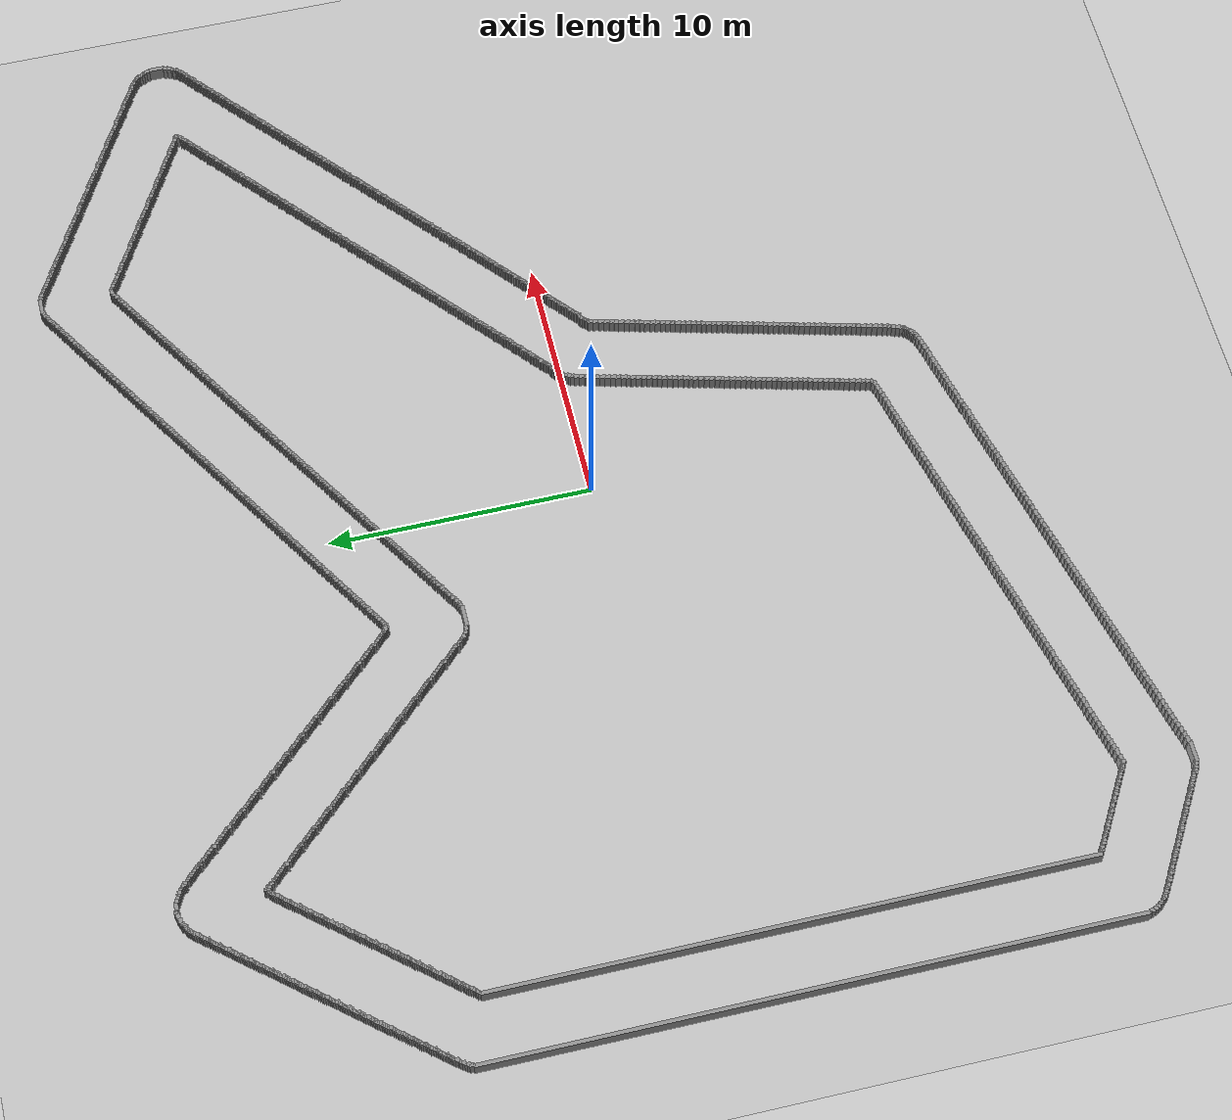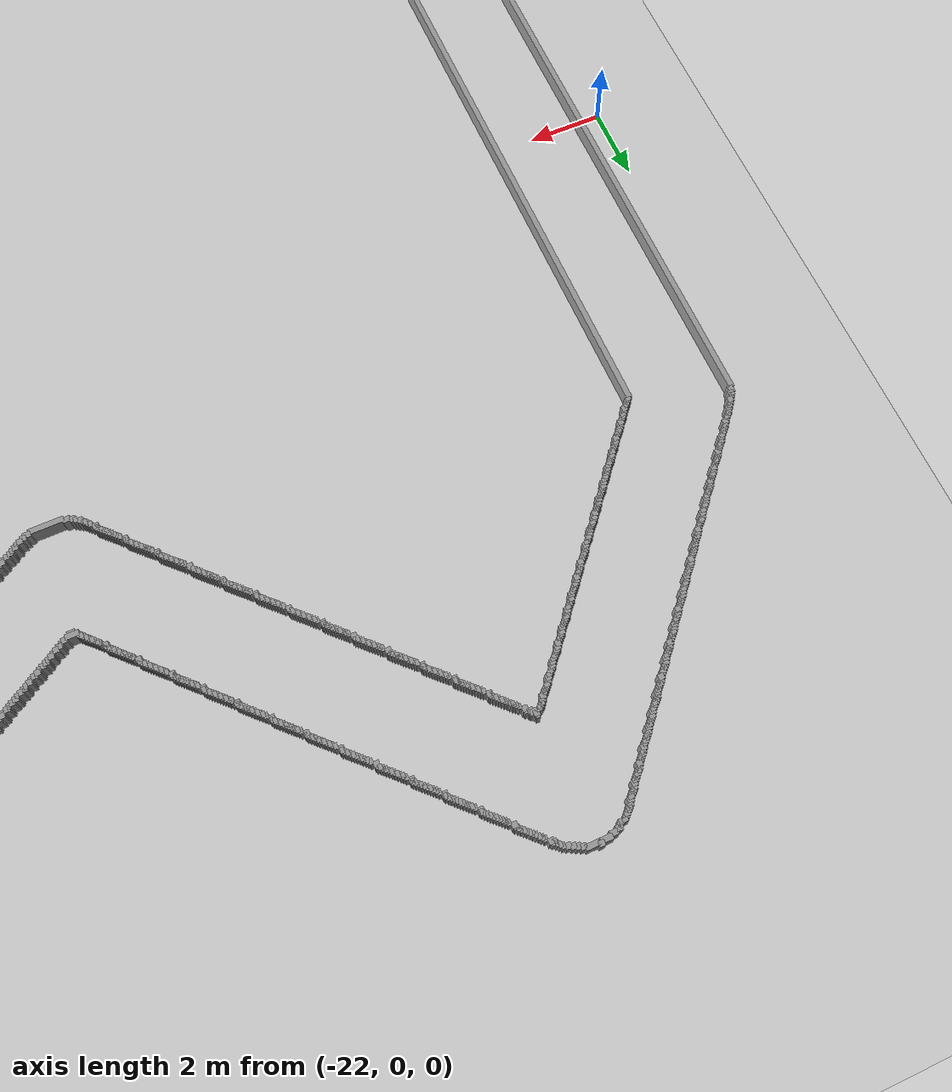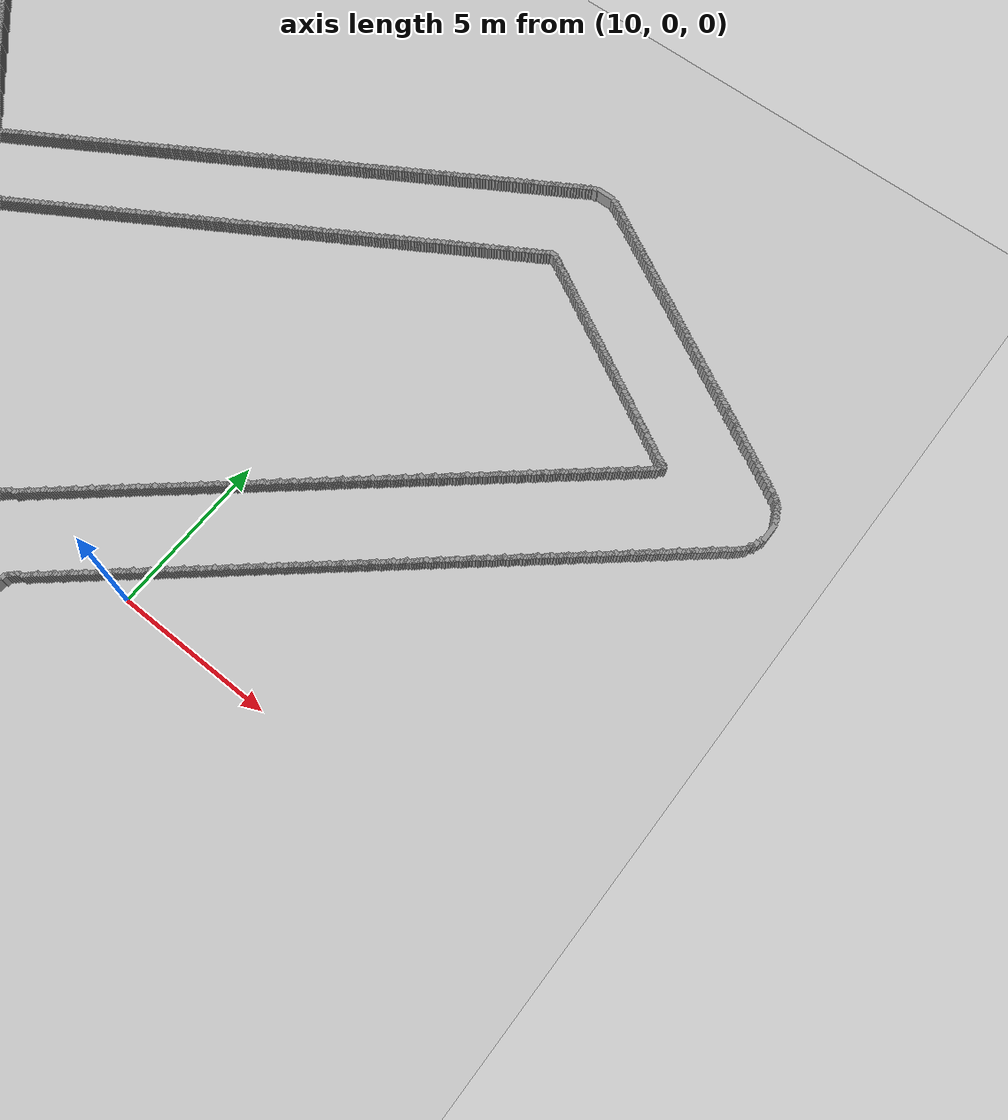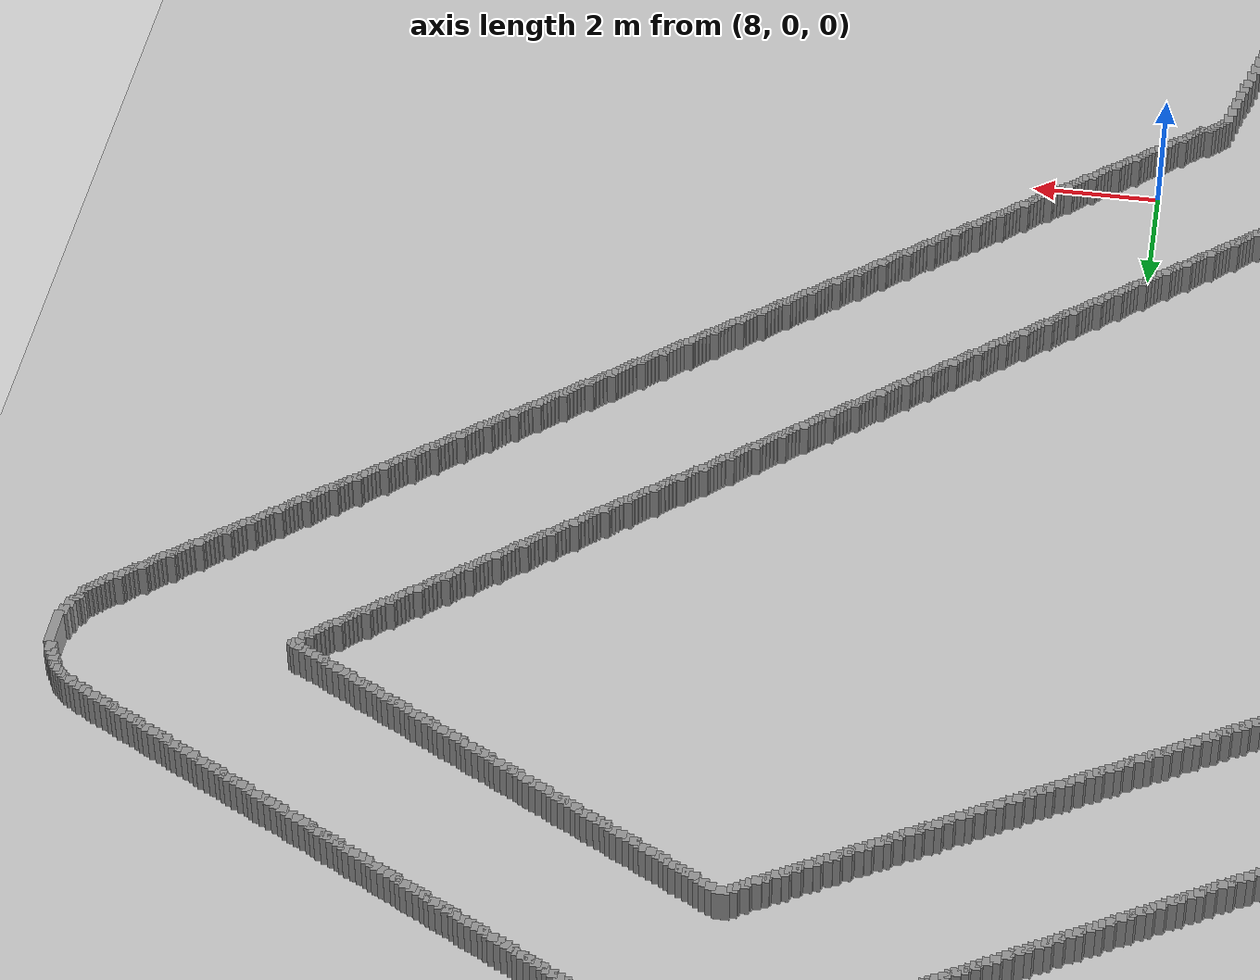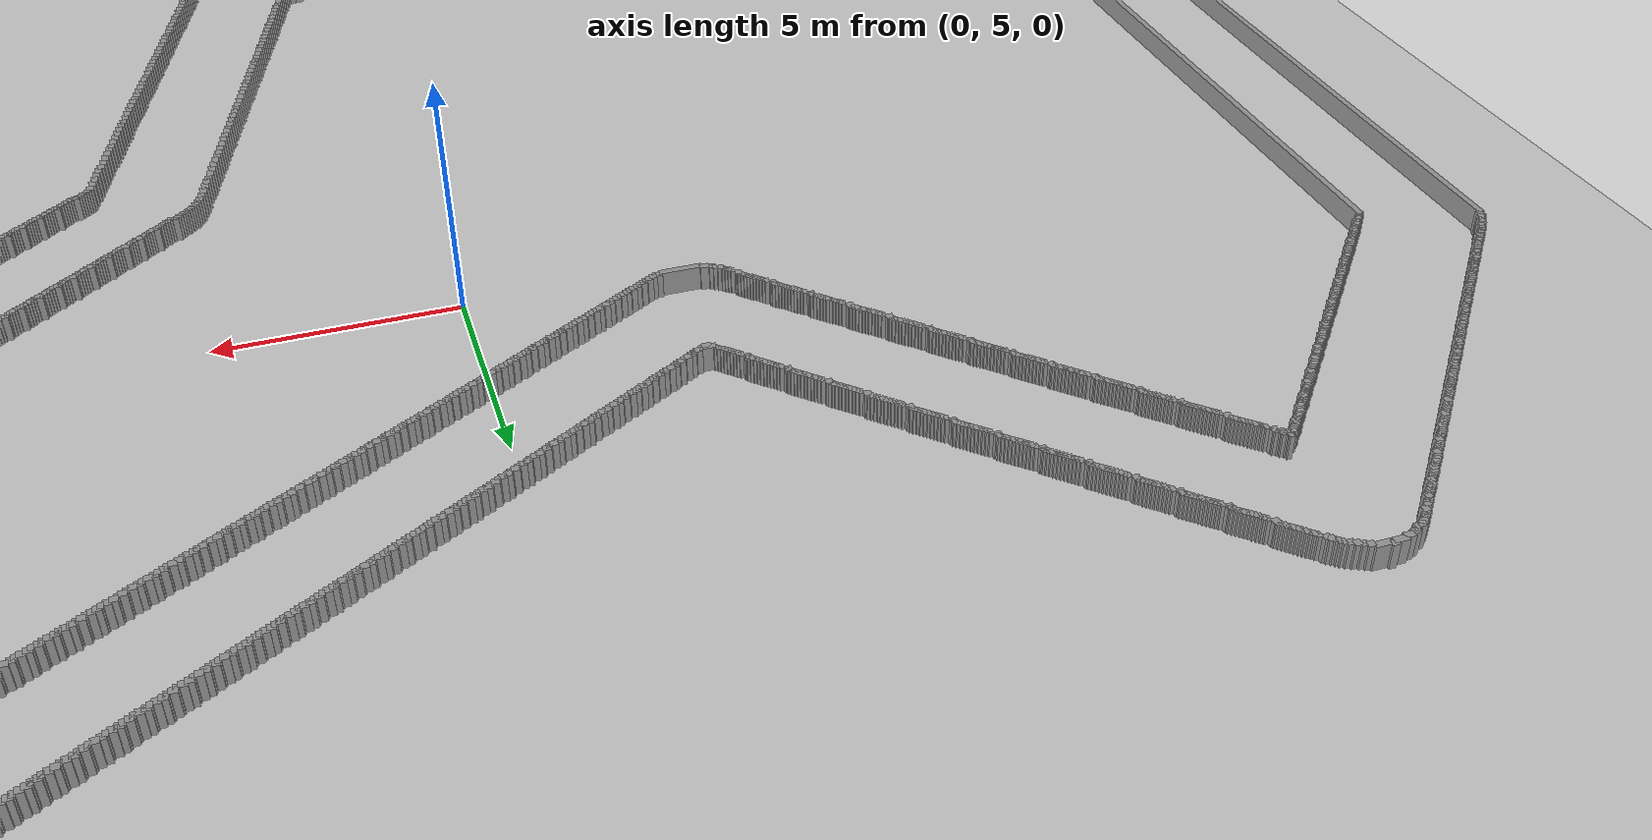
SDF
<sdf version="1.6">
  <world name="default">

    <plugin name="gazebo_ros_state" filename="libgazebo_ros_state.so">
      <ros>
        <namespace>/gazebo</namespace>
      </ros>

      <update_rate>1.0</update_rate>
    </plugin>

    <light name='sun' type='directional'>
      <cast_shadows>1</cast_shadows>
      <pose frame=''>0 0 10 0 -0 0</pose>
      <diffuse>0.8 0.8 0.8 1</diffuse>
      <specular>0.1 0.1 0.1 1</specular>
      <attenuation>
        <range>1000</range>
        <constant>0.9</constant>
        <linear>0.01</linear>
        <quadratic>0.001</quadratic>
      </attenuation>
      <direction>-0.5 0.5 -1</direction>
    </light>

    <model name='my_ground_plane'>
      <static>1</static>
      <link name='link'>
        <collision name='collision'>
          <geometry>
            <plane>
              <normal>0 0 1</normal>
              <size>100 100</size>
            </plane>
          </geometry>
          <surface>
            <friction>
              <ode>
                <mu>100</mu>
                <mu2>50</mu2>
              </ode>
              <torsional>
                <ode />
              </torsional>
            </friction>
            <contact>
              <ode />
            </contact>
            <bounce />
          </surface>
          <max_contacts>10</max_contacts>
        </collision>
        <visual name='visual'>
          <cast_shadows>0</cast_shadows>
          <geometry>
            <plane>
              <normal>0 0 1</normal>
              <size>50 50</size>
            </plane>
          </geometry>
          <material>
            <script>
              <uri>model://my_ground_plane/materials/scripts</uri>
              <uri>model://my_ground_plane/materials/textures</uri>
              <name>MyGroundPlane/Image</name>
            </script>
          </material>
        </visual>
        <self_collide>0</self_collide>
        <kinematic>0</kinematic>
        <gravity>1</gravity>
        <enable_wind>0</enable_wind>
      </link>
    </model>

    <gravity>0 0 -9.8</gravity>
    <magnetic_field>6e-06 2.3e-05 -4.2e-05</magnetic_field>
    <atmosphere type='adiabatic'/>

    <physics name='default_physics' default='0' type='ode'>
      <max_step_size>0.001</max_step_size>
      <real_time_factor>1</real_time_factor>
      <real_time_update_rate>1000</real_time_update_rate>
    </physics>

    <scene>
      <ambient>0.4 0.4 0.4 1</ambient>
      <background>0.7 0.7 0.7 1</background>
      <shadows>1</shadows>
      <sky>
        <clouds>
          <speed>12</speed>
        </clouds>
      </sky>
    </scene>

    <spherical_coordinates>
      <surface_model>EARTH_WGS84</surface_model>
      <latitude_deg>0</latitude_deg>
      <longitude_deg>0</longitude_deg>
      <elevation>0</elevation>
      <heading_deg>0</heading_deg>
    </spherical_coordinates>

    <model name="obstacle">
      <static>1</static>
      <pose frame="">0 0 0 0 0 0</pose>
      <link name="obstacle">
        <collision name="obstacle_1">
          <pose>-15.774999999999999 -18.3 0 0 0 0</pose>
          <geometry>
            <box>
              <size>0.8500000000000001 0.15 1.0</size>
            </box>
          </geometry>
        </collision>
        <visual name="obstacle_1">
          <pose>-15.774999999999999 -18.3 0 0 0 0</pose>
          <geometry>
            <box>
              <size>0.8500000000000001 0.15 1.0</size>
            </box>
          </geometry>
          <material>
            <script>
              <uri>file://media/materials/scripts/gazebo.material</uri>
              <name>Gazebo/Grey</name>
            </script>
            <ambient>1 1 1 1</ambient>
          </material>
        </visual>
        <collision name="obstacle_2">
          <pose>-16.225 -18.25 0 0 0 0</pose>
          <geometry>
            <box>
              <size>0.2 0.15 1.0</size>
            </box>
          </geometry>
        </collision>
        <visual name="obstacle_2">
          <pose>-16.225 -18.25 0 0 0 0</pose>
          <geometry>
            <box>
              <size>0.2 0.15 1.0</size>
            </box>
          </geometry>
          <material>
            <script>
              <uri>file://media/materials/scripts/gazebo.material</uri>
              <name>Gazebo/Grey</name>
            </script>
            <ambient>1 1 1 1</ambient>
          </material>
        </visual>
        <collision name="obstacle_3">
          <pose>-15.275 -18.25 0 0 0 0</pose>
          <geometry>
            <box>
              <size>0.25 0.15 1.0</size>
            </box>
          </geometry>
        </collision>
        <visual name="obstacle_3">
          <pose>-15.275 -18.25 0 0 0 0</pose>
          <geometry>
            <box>
              <size>0.25 0.15 1.0</size>
            </box>
          </geometry>
          <material>
            <script>
              <uri>file://media/materials/scripts/gazebo.material</uri>
              <name>Gazebo/Grey</name>
            </script>
            <ambient>1 1 1 1</ambient>
          </material>
        </visual>
        <collision name="obstacle_4">
          <pose>-16.375 -18.2 0 0 0 0</pose>
          <geometry>
            <box>
              <size>0.15000000000000002 0.15 1.0</size>
            </box>
          </geometry>
        </collision>
        <visual name="obstacle_4">
          <pose>-16.375 -18.2 0 0 0 0</pose>
          <geometry>
            <box>
              <size>0.15000000000000002 0.15 1.0</size>
            </box>
          </geometry>
          <material>
            <script>
              <uri>file://media/materials/scripts/gazebo.material</uri>
              <name>Gazebo/Grey</name>
            </script>
            <ambient>1 1 1 1</ambient>
          </material>
        </visual>
        <collision name="obstacle_5">
          <pose>-15.075 -18.2 0 0 0 0</pose>
          <geometry>
            <box>
              <size>0.25 0.15 1.0</size>
            </box>
          </geometry>
        </collision>
        <visual name="obstacle_5">
          <pose>-15.075 -18.2 0 0 0 0</pose>
          <geometry>
            <box>
              <size>0.25 0.15 1.0</size>
            </box>
          </geometry>
          <material>
            <script>
              <uri>file://media/materials/scripts/gazebo.material</uri>
              <name>Gazebo/Grey</name>
            </script>
            <ambient>1 1 1 1</ambient>
          </material>
        </visual>
        <collision name="obstacle_6">
          <pose>-16.475 -18.15 0 0 0 0</pose>
          <geometry>
            <box>
              <size>0.15000000000000002 0.15 1.0</size>
            </box>
          </geometry>
        </collision>
        <visual name="obstacle_6">
          <pose>-16.475 -18.15 0 0 0 0</pose>
          <geometry>
            <box>
              <size>0.15000000000000002 0.15 1.0</size>
            </box>
          </geometry>
          <material>
            <script>
              <uri>file://media/materials/scripts/gazebo.material</uri>
              <name>Gazebo/Grey</name>
            </script>
            <ambient>1 1 1 1</ambient>
          </material>
        </visual>
        <collision name="obstacle_7">
          <pose>-14.875 -18.15 0 0 0 0</pose>
          <geometry>
            <box>
              <size>0.25 0.15 1.0</size>
            </box>
          </geometry>
        </collision>
        <visual name="obstacle_7">
          <pose>-14.875 -18.15 0 0 0 0</pose>
          <geometry>
            <box>
              <size>0.25 0.15 1.0</size>
            </box>
          </geometry>
          <material>
            <script>
              <uri>file://media/materials/scripts/gazebo.material</uri>
              <name>Gazebo/Grey</name>
            </script>
            <ambient>1 1 1 1</ambient>
          </material>
        </visual>
        <collision name="obstacle_8">
          <pose>-16.575 -18.1 0 0 0 0</pose>
          <geometry>
            <box>
              <size>0.15000000000000002 0.15 1.0</size>
            </box>
          </geometry>
        </collision>
        <visual name="obstacle_8">
          <pose>-16.575 -18.1 0 0 0 0</pose>
          <geometry>
            <box>
              <size>0.15000000000000002 0.15 1.0</size>
            </box>
          </geometry>
          <material>
            <script>
              <uri>file://media/materials/scripts/gazebo.material</uri>
              <name>Gazebo/Grey</name>
            </script>
            <ambient>1 1 1 1</ambient>
          </material>
        </visual>
        <collision name="obstacle_9">
          <pose>-14.674999999999999 -18.1 0 0 0 0</pose>
          <geometry>
            <box>
              <size>0.25 0.15 1.0</size>
            </box>
          </geometry>
        </collision>
        <visual name="obstacle_9">
          <pose>-14.674999999999999 -18.1 0 0 0 0</pose>
          <geometry>
            <box>
              <size>0.25 0.15 1.0</size>
            </box>
          </geometry>
          <material>
            <script>
              <uri>file://media/materials/scripts/gazebo.material</uri>
              <name>Gazebo/Grey</name>
            </script>
            <ambient>1 1 1 1</ambient>
          </material>
        </visual>
        <collision name="obstacle_10">
          <pose>-16.625 -18.05 0 0 0 0</pose>
          <geometry>
            <box>
              <size>0.1 0.15 1.0</size>
            </box>
          </geometry>
        </collision>
        <visual name="obstacle_10">
          <pose>-16.625 -18.05 0 0 0 0</pose>
          <geometry>
            <box>
              <size>0.1 0.15 1.0</size>
            </box>
          </geometry>
          <material>
            <script>
              <uri>file://media/materials/scripts/gazebo.material</uri>
              <name>Gazebo/Grey</name>
            </script>
            <ambient>1 1 1 1</ambient>
          </material>
        </visual>
        <collision name="obstacle_11">
          <pose>-14.475 -18.05 0 0 0 0</pose>
          <geometry>
            <box>
              <size>0.25 0.15 1.0</size>
            </box>
          </geometry>
        </collision>
        <visual name="obstacle_11">
          <pose>-14.475 -18.05 0 0 0 0</pose>
          <geometry>
            <box>
              <size>0.25 0.15 1.0</size>
            </box>
          </geometry>
          <material>
            <script>
              <uri>file://media/materials/scripts/gazebo.material</uri>
              <name>Gazebo/Grey</name>
            </script>
            <ambient>1 1 1 1</ambient>
          </material>
        </visual>
        <collision name="obstacle_12">
          <pose>-16.725 -18.0 0 0 0 0</pose>
          <geometry>
            <box>
              <size>0.15000000000000002 0.15 1.0</size>
            </box>
          </geometry>
        </collision>
        <visual name="obstacle_12">
          <pose>-16.725 -18.0 0 0 0 0</pose>
          <geometry>
            <box>
              <size>0.15000000000000002 0.15 1.0</size>
            </box>
          </geometry>
          <material>
            <script>
              <uri>file://media/materials/scripts/gazebo.material</uri>
              <name>Gazebo/Grey</name>
            </script>
            <ambient>1 1 1 1</ambient>
          </material>
        </visual>
        <collision name="obstacle_13">
          <pose>-14.275 -18.0 0 0 0 0</pose>
          <geometry>
            <box>
              <size>0.25 0.15 1.0</size>
            </box>
          </geometry>
        </collision>
        <visual name="obstacle_13">
          <pose>-14.275 -18.0 0 0 0 0</pose>
          <geometry>
            <box>
              <size>0.25 0.15 1.0</size>
            </box>
          </geometry>
          <material>
            <script>
              <uri>file://media/materials/scripts/gazebo.material</uri>
              <name>Gazebo/Grey</name>
            </script>
            <ambient>1 1 1 1</ambient>
          </material>
        </visual>
        <collision name="obstacle_14">
          <pose>-16.825 -17.95 0 0 0 0</pose>
          <geometry>
            <box>
              <size>0.15000000000000002 0.15 1.0</size>
            </box>
          </geometry>
        </collision>
        <visual name="obstacle_14">
          <pose>-16.825 -17.95 0 0 0 0</pose>
          <geometry>
            <box>
              <size>0.15000000000000002 0.15 1.0</size>
            </box>
          </geometry>
          <material>
            <script>
              <uri>file://media/materials/scripts/gazebo.material</uri>
              <name>Gazebo/Grey</name>
            </script>
            <ambient>1 1 1 1</ambient>
          </material>
        </visual>
        <collision name="obstacle_15">
          <pose>-14.075 -17.95 0 0 0 0</pose>
          <geometry>
            <box>
              <size>0.25 0.15 1.0</size>
            </box>
          </geometry>
        </collision>
        <visual name="obstacle_15">
          <pose>-14.075 -17.95 0 0 0 0</pose>
          <geometry>
            <box>
              <size>0.25 0.15 1.0</size>
            </box>
          </geometry>
          <material>
            <script>
              <uri>file://media/materials/scripts/gazebo.material</uri>
              <name>Gazebo/Grey</name>
            </script>
            <ambient>1 1 1 1</ambient>
          </material>
        </visual>
        <collision name="obstacle_16">
          <pose>-16.875 -17.9 0 0 0 0</pose>
          <geometry>
            <box>
              <size>0.1 0.15 1.0</size>
            </box>
          </geometry>
        </collision>
        <visual name="obstacle_16">
          <pose>-16.875 -17.9 0 0 0 0</pose>
          <geometry>
            <box>
              <size>0.1 0.15 1.0</size>
            </box>
          </geometry>
          <material>
            <script>
              <uri>file://media/materials/scripts/gazebo.material</uri>
              <name>Gazebo/Grey</name>
            </script>
            <ambient>1 1 1 1</ambient>
          </material>
        </visual>
        <collision name="obstacle_17">
          <pose>-13.875 -17.9 0 0 0 0</pose>
          <geometry>
            <box>
              <size>0.25 0.15 1.0</size>
            </box>
          </geometry>
        </collision>
        <visual name="obstacle_17">
          <pose>-13.875 -17.9 0 0 0 0</pose>
          <geometry>
            <box>
              <size>0.25 0.15 1.0</size>
            </box>
          </geometry>
          <material>
            <script>
              <uri>file://media/materials/scripts/gazebo.material</uri>
              <name>Gazebo/Grey</name>
            </script>
            <ambient>1 1 1 1</ambient>
          </material>
        </visual>
        <collision name="obstacle_18">
          <pose>-16.975 -17.85 0 0 0 0</pose>
          <geometry>
            <box>
              <size>0.15000000000000002 0.15 1.0</size>
            </box>
          </geometry>
        </collision>
        <visual name="obstacle_18">
          <pose>-16.975 -17.85 0 0 0 0</pose>
          <geometry>
            <box>
              <size>0.15000000000000002 0.15 1.0</size>
            </box>
          </geometry>
          <material>
            <script>
              <uri>file://media/materials/scripts/gazebo.material</uri>
              <name>Gazebo/Grey</name>
            </script>
            <ambient>1 1 1 1</ambient>
          </material>
        </visual>
        <collision name="obstacle_19">
          <pose>-13.674999999999999 -17.85 0 0 0 0</pose>
          <geometry>
            <box>
              <size>0.25 0.15 1.0</size>
            </box>
          </geometry>
        </collision>
        <visual name="obstacle_19">
          <pose>-13.674999999999999 -17.85 0 0 0 0</pose>
          <geometry>
            <box>
              <size>0.25 0.15 1.0</size>
            </box>
          </geometry>
          <material>
            <script>
              <uri>file://media/materials/scripts/gazebo.material</uri>
              <name>Gazebo/Grey</name>
            </script>
            <ambient>1 1 1 1</ambient>
          </material>
        </visual>
        <collision name="obstacle_20">
          <pose>-17.075 -17.8 0 0 0 0</pose>
          <geometry>
            <box>
              <size>0.15000000000000002 0.15 1.0</size>
            </box>
          </geometry>
        </collision>
        <visual name="obstacle_20">
          <pose>-17.075 -17.8 0 0 0 0</pose>
          <geometry>
            <box>
              <size>0.15000000000000002 0.15 1.0</size>
            </box>
          </geometry>
          <material>
            <script>
              <uri>file://media/materials/scripts/gazebo.material</uri>
              <name>Gazebo/Grey</name>
            </script>
            <ambient>1 1 1 1</ambient>
          </material>
        </visual>
        <collision name="obstacle_21">
          <pose>-13.424999999999999 -17.8 0 0 0 0</pose>
          <geometry>
            <box>
              <size>0.30000000000000004 0.15 1.0</size>
            </box>
          </geometry>
        </collision>
        <visual name="obstacle_21">
          <pose>-13.424999999999999 -17.8 0 0 0 0</pose>
          <geometry>
            <box>
              <size>0.30000000000000004 0.15 1.0</size>
            </box>
          </geometry>
          <material>
            <script>
              <uri>file://media/materials/scripts/gazebo.material</uri>
              <name>Gazebo/Grey</name>
            </script>
            <ambient>1 1 1 1</ambient>
          </material>
        </visual>
        <collision name="obstacle_22">
          <pose>-17.175 -17.75 0 0 0 0</pose>
          <geometry>
            <box>
              <size>0.15000000000000002 0.15 1.0</size>
            </box>
          </geometry>
        </collision>
        <visual name="obstacle_22">
          <pose>-17.175 -17.75 0 0 0 0</pose>
          <geometry>
            <box>
              <size>0.15000000000000002 0.15 1.0</size>
            </box>
          </geometry>
          <material>
            <script>
              <uri>file://media/materials/scripts/gazebo.material</uri>
              <name>Gazebo/Grey</name>
            </script>
            <ambient>1 1 1 1</ambient>
          </material>
        </visual>
        <collision name="obstacle_23">
          <pose>-13.225 -17.75 0 0 0 0</pose>
          <geometry>
            <box>
              <size>0.25 0.15 1.0</size>
            </box>
          </geometry>
        </collision>
        <visual name="obstacle_23">
          <pose>-13.225 -17.75 0 0 0 0</pose>
          <geometry>
            <box>
              <size>0.25 0.15 1.0</size>
            </box>
          </geometry>
          <material>
            <script>
              <uri>file://media/materials/scripts/gazebo.material</uri>
              <name>Gazebo/Grey</name>
            </script>
            <ambient>1 1 1 1</ambient>
          </material>
        </visual>
        <collision name="obstacle_24">
          <pose>-17.225 -17.7 0 0 0 0</pose>
          <geometry>
            <box>
              <size>0.1 0.15 1.0</size>
            </box>
          </geometry>
        </collision>
        <visual name="obstacle_24">
          <pose>-17.225 -17.7 0 0 0 0</pose>
          <geometry>
            <box>
              <size>0.1 0.15 1.0</size>
            </box>
          </geometry>
          <material>
            <script>
              <uri>file://media/materials/scripts/gazebo.material</uri>
              <name>Gazebo/Grey</name>
            </script>
            <ambient>1 1 1 1</ambient>
          </material>
        </visual>
        <collision name="obstacle_25">
          <pose>-13.024999999999999 -17.7 0 0 0 0</pose>
          <geometry>
            <box>
              <size>0.25 0.15 1.0</size>
            </box>
          </geometry>
        </collision>
        <visual name="obstacle_25">
          <pose>-13.024999999999999 -17.7 0 0 0 0</pose>
          <geometry>
            <box>
              <size>0.25 0.15 1.0</size>
            </box>
          </geometry>
          <material>
            <script>
              <uri>file://media/materials/scripts/gazebo.material</uri>
              <name>Gazebo/Grey</name>
            </script>
            <ambient>1 1 1 1</ambient>
          </material>
        </visual>
        <collision name="obstacle_26">
          <pose>-17.325 -17.65 0 0 0 0</pose>
          <geometry>
            <box>
              <size>0.15000000000000002 0.15 1.0</size>
            </box>
          </geometry>
        </collision>
        <visual name="obstacle_26">
          <pose>-17.325 -17.65 0 0 0 0</pose>
          <geometry>
            <box>
              <size>0.15000000000000002 0.15 1.0</size>
            </box>
          </geometry>
          <material>
            <script>
              <uri>file://media/materials/scripts/gazebo.material</uri>
              <name>Gazebo/Grey</name>
            </script>
            <ambient>1 1 1 1</ambient>
          </material>
        </visual>
        <collision name="obstacle_27">
          <pose>-12.825 -17.65 0 0 0 0</pose>
          <geometry>
            <box>
              <size>0.25 0.15 1.0</size>
            </box>
          </geometry>
        </collision>
        <visual name="obstacle_27">
          <pose>-12.825 -17.65 0 0 0 0</pose>
          <geometry>
            <box>
              <size>0.25 0.15 1.0</size>
            </box>
          </geometry>
          <material>
            <script>
              <uri>file://media/materials/scripts/gazebo.material</uri>
              <name>Gazebo/Grey</name>
            </script>
            <ambient>1 1 1 1</ambient>
          </material>
        </visual>
        <collision name="obstacle_28">
          <pose>-17.425 -17.6 0 0 0 0</pose>
          <geometry>
            <box>
              <size>0.15000000000000002 0.15 1.0</size>
            </box>
          </geometry>
        </collision>
        <visual name="obstacle_28">
          <pose>-17.425 -17.6 0 0 0 0</pose>
          <geometry>
            <box>
              <size>0.15000000000000002 0.15 1.0</size>
            </box>
          </geometry>
          <material>
            <script>
              <uri>file://media/materials/scripts/gazebo.material</uri>
              <name>Gazebo/Grey</name>
            </script>
            <ambient>1 1 1 1</ambient>
          </material>
        </visual>
        <collision name="obstacle_29">
          <pose>-12.625 -17.6 0 0 0 0</pose>
          <geometry>
            <box>
              <size>0.25 0.15 1.0</size>
            </box>
          </geometry>
        </collision>
        <visual name="obstacle_29">
          <pose>-12.625 -17.6 0 0 0 0</pose>
          <geometry>
            <box>
              <size>0.25 0.15 1.0</size>
            </box>
          </geometry>
          <material>
            <script>
              <uri>file://media/materials/scripts/gazebo.material</uri>
              <name>Gazebo/Grey</name>
            </script>
            <ambient>1 1 1 1</ambient>
          </material>
        </visual>
        <collision name="obstacle_30">
          <pose>-17.475 -17.55 0 0 0 0</pose>
          <geometry>
            <box>
              <size>0.1 0.15 1.0</size>
            </box>
          </geometry>
        </collision>
        <visual name="obstacle_30">
          <pose>-17.475 -17.55 0 0 0 0</pose>
          <geometry>
            <box>
              <size>0.1 0.15 1.0</size>
            </box>
          </geometry>
          <material>
            <script>
              <uri>file://media/materials/scripts/gazebo.material</uri>
              <name>Gazebo/Grey</name>
            </script>
            <ambient>1 1 1 1</ambient>
          </material>
        </visual>
        <collision name="obstacle_31">
          <pose>-12.424999999999999 -17.55 0 0 0 0</pose>
          <geometry>
            <box>
              <size>0.25 0.15 1.0</size>
            </box>
          </geometry>
        </collision>
        <visual name="obstacle_31">
          <pose>-12.424999999999999 -17.55 0 0 0 0</pose>
          <geometry>
            <box>
              <size>0.25 0.15 1.0</size>
            </box>
          </geometry>
          <material>
            <script>
              <uri>file://media/materials/scripts/gazebo.material</uri>
              <name>Gazebo/Grey</name>
            </script>
            <ambient>1 1 1 1</ambient>
          </material>
        </visual>
        <collision name="obstacle_32">
          <pose>-17.575 -17.5 0 0 0 0</pose>
          <geometry>
            <box>
              <size>0.15000000000000002 0.15 1.0</size>
            </box>
          </geometry>
        </collision>
        <visual name="obstacle_32">
          <pose>-17.575 -17.5 0 0 0 0</pose>
          <geometry>
            <box>
              <size>0.15000000000000002 0.15 1.0</size>
            </box>
          </geometry>
          <material>
            <script>
              <uri>file://media/materials/scripts/gazebo.material</uri>
              <name>Gazebo/Grey</name>
            </script>
            <ambient>1 1 1 1</ambient>
          </material>
        </visual>
        <collision name="obstacle_33">
          <pose>-12.225 -17.5 0 0 0 0</pose>
          <geometry>
            <box>
              <size>0.25 0.15 1.0</size>
            </box>
          </geometry>
        </collision>
        <visual name="obstacle_33">
          <pose>-12.225 -17.5 0 0 0 0</pose>
          <geometry>
            <box>
              <size>0.25 0.15 1.0</size>
            </box>
          </geometry>
          <material>
            <script>
              <uri>file://media/materials/scripts/gazebo.material</uri>
              <name>Gazebo/Grey</name>
            </script>
            <ambient>1 1 1 1</ambient>
          </material>
        </visual>
        <collision name="obstacle_34">
          <pose>-17.675 -17.45 0 0 0 0</pose>
          <geometry>
            <box>
              <size>0.15000000000000002 0.15 1.0</size>
            </box>
          </geometry>
        </collision>
        <visual name="obstacle_34">
          <pose>-17.675 -17.45 0 0 0 0</pose>
          <geometry>
            <box>
              <size>0.15000000000000002 0.15 1.0</size>
            </box>
          </geometry>
          <material>
            <script>
              <uri>file://media/materials/scripts/gazebo.material</uri>
              <name>Gazebo/Grey</name>
            </script>
            <ambient>1 1 1 1</ambient>
          </material>
        </visual>
        <collision name="obstacle_35">
          <pose>-12.024999999999999 -17.45 0 0 0 0</pose>
          <geometry>
            <box>
              <size>0.25 0.15 1.0</size>
            </box>
          </geometry>
        </collision>
        <visual name="obstacle_35">
          <pose>-12.024999999999999 -17.45 0 0 0 0</pose>
          <geometry>
            <box>
              <size>0.25 0.15 1.0</size>
            </box>
          </geometry>
          <material>
            <script>
              <uri>file://media/materials/scripts/gazebo.material</uri>
              <name>Gazebo/Grey</name>
            </script>
            <ambient>1 1 1 1</ambient>
          </material>
        </visual>
        <collision name="obstacle_36">
          <pose>-17.725 -17.4 0 0 0 0</pose>
          <geometry>
            <box>
              <size>0.1 0.15 1.0</size>
            </box>
          </geometry>
        </collision>
        <visual name="obstacle_36">
          <pose>-17.725 -17.4 0 0 0 0</pose>
          <geometry>
            <box>
              <size>0.1 0.15 1.0</size>
            </box>
          </geometry>
          <material>
            <script>
              <uri>file://media/materials/scripts/gazebo.material</uri>
              <name>Gazebo/Grey</name>
            </script>
            <ambient>1 1 1 1</ambient>
          </material>
        </visual>
        <collision name="obstacle_37">
          <pose>-11.825 -17.4 0 0 0 0</pose>
          <geometry>
            <box>
              <size>0.25 0.15 1.0</size>
            </box>
          </geometry>
        </collision>
        <visual name="obstacle_37">
          <pose>-11.825 -17.4 0 0 0 0</pose>
          <geometry>
            <box>
              <size>0.25 0.15 1.0</size>
            </box>
          </geometry>
          <material>
            <script>
              <uri>file://media/materials/scripts/gazebo.material</uri>
              <name>Gazebo/Grey</name>
            </script>
            <ambient>1 1 1 1</ambient>
          </material>
        </visual>
        <collision name="obstacle_38">
          <pose>-17.825 -17.35 0 0 0 0</pose>
          <geometry>
            <box>
              <size>0.15000000000000002 0.15 1.0</size>
            </box>
          </geometry>
        </collision>
        <visual name="obstacle_38">
          <pose>-17.825 -17.35 0 0 0 0</pose>
          <geometry>
            <box>
              <size>0.15000000000000002 0.15 1.0</size>
            </box>
          </geometry>
          <material>
            <script>
              <uri>file://media/materials/scripts/gazebo.material</uri>
              <name>Gazebo/Grey</name>
            </script>
            <ambient>1 1 1 1</ambient>
          </material>
        </visual>
        <collision name="obstacle_39">
          <pose>-11.625 -17.35 0 0 0 0</pose>
          <geometry>
            <box>
              <size>0.25 0.15 1.0</size>
            </box>
          </geometry>
        </collision>
        <visual name="obstacle_39">
          <pose>-11.625 -17.35 0 0 0 0</pose>
          <geometry>
            <box>
              <size>0.25 0.15 1.0</size>
            </box>
          </geometry>
          <material>
            <script>
              <uri>file://media/materials/scripts/gazebo.material</uri>
              <name>Gazebo/Grey</name>
            </script>
            <ambient>1 1 1 1</ambient>
          </material>
        </visual>
        <collision name="obstacle_40">
          <pose>-17.925 -17.3 0 0 0 0</pose>
          <geometry>
            <box>
              <size>0.15000000000000002 0.15 1.0</size>
            </box>
          </geometry>
        </collision>
        <visual name="obstacle_40">
          <pose>-17.925 -17.3 0 0 0 0</pose>
          <geometry>
            <box>
              <size>0.15000000000000002 0.15 1.0</size>
            </box>
          </geometry>
          <material>
            <script>
              <uri>file://media/materials/scripts/gazebo.material</uri>
              <name>Gazebo/Grey</name>
            </script>
            <ambient>1 1 1 1</ambient>
          </material>
        </visual>
        <collision name="obstacle_41">
          <pose>-11.375 -17.3 0 0 0 0</pose>
          <geometry>
            <box>
              <size>0.30000000000000004 0.15 1.0</size>
            </box>
          </geometry>
        </collision>
        <visual name="obstacle_41">
          <pose>-11.375 -17.3 0 0 0 0</pose>
          <geometry>
            <box>
              <size>0.30000000000000004 0.15 1.0</size>
            </box>
          </geometry>
          <material>
            <script>
              <uri>file://media/materials/scripts/gazebo.material</uri>
              <name>Gazebo/Grey</name>
            </script>
            <ambient>1 1 1 1</ambient>
          </material>
        </visual>
        <collision name="obstacle_42">
          <pose>-18.025 -17.25 0 0 0 0</pose>
          <geometry>
            <box>
              <size>0.15000000000000002 0.15 1.0</size>
            </box>
          </geometry>
        </collision>
        <visual name="obstacle_42">
          <pose>-18.025 -17.25 0 0 0 0</pose>
          <geometry>
            <box>
              <size>0.15000000000000002 0.15 1.0</size>
            </box>
          </geometry>
          <material>
            <script>
              <uri>file://media/materials/scripts/gazebo.material</uri>
              <name>Gazebo/Grey</name>
            </script>
            <ambient>1 1 1 1</ambient>
          </material>
        </visual>
        <collision name="obstacle_43">
          <pose>-11.174999999999999 -17.25 0 0 0 0</pose>
          <geometry>
            <box>
              <size>0.25 0.15 1.0</size>
            </box>
          </geometry>
        </collision>
        <visual name="obstacle_43">
          <pose>-11.174999999999999 -17.25 0 0 0 0</pose>
          <geometry>
            <box>
              <size>0.25 0.15 1.0</size>
            </box>
          </geometry>
          <material>
            <script>
              <uri>file://media/materials/scripts/gazebo.material</uri>
              <name>Gazebo/Grey</name>
            </script>
            <ambient>1 1 1 1</ambient>
          </material>
        </visual>
        <collision name="obstacle_44">
          <pose>-18.075 -17.2 0 0 0 0</pose>
          <geometry>
            <box>
              <size>0.1 0.15 1.0</size>
            </box>
          </geometry>
        </collision>
        <visual name="obstacle_44">
          <pose>-18.075 -17.2 0 0 0 0</pose>
          <geometry>
            <box>
              <size>0.1 0.15 1.0</size>
            </box>
          </geometry>
          <material>
            <script>
              <uri>file://media/materials/scripts/gazebo.material</uri>
              <name>Gazebo/Grey</name>
            </script>
            <ambient>1 1 1 1</ambient>
          </material>
        </visual>
        <collision name="obstacle_45">
          <pose>-10.975 -17.2 0 0 0 0</pose>
          <geometry>
            <box>
              <size>0.25 0.15 1.0</size>
            </box>
          </geometry>
        </collision>
        <visual name="obstacle_45">
          <pose>-10.975 -17.2 0 0 0 0</pose>
          <geometry>
            <box>
              <size>0.25 0.15 1.0</size>
            </box>
          </geometry>
          <material>
            <script>
              <uri>file://media/materials/scripts/gazebo.material</uri>
              <name>Gazebo/Grey</name>
            </script>
            <ambient>1 1 1 1</ambient>
          </material>
        </visual>
        <collision name="obstacle_46">
          <pose>-18.175 -17.15 0 0 0 0</pose>
          <geometry>
            <box>
              <size>0.15000000000000002 0.15 1.0</size>
            </box>
          </geometry>
        </collision>
        <visual name="obstacle_46">
          <pose>-18.175 -17.15 0 0 0 0</pose>
          <geometry>
            <box>
              <size>0.15000000000000002 0.15 1.0</size>
            </box>
          </geometry>
          <material>
            <script>
              <uri>file://media/materials/scripts/gazebo.material</uri>
              <name>Gazebo/Grey</name>
            </script>
            <ambient>1 1 1 1</ambient>
          </material>
        </visual>
        <collision name="obstacle_47">
          <pose>-10.774999999999999 -17.15 0 0 0 0</pose>
          <geometry>
            <box>
              <size>0.25 0.15 1.0</size>
            </box>
          </geometry>
        </collision>
        <visual name="obstacle_47">
          <pose>-10.774999999999999 -17.15 0 0 0 0</pose>
          <geometry>
            <box>
              <size>0.25 0.15 1.0</size>
            </box>
          </geometry>
          <material>
            <script>
              <uri>file://media/materials/scripts/gazebo.material</uri>
              <name>Gazebo/Grey</name>
            </script>
            <ambient>1 1 1 1</ambient>
          </material>
        </visual>
        <collision name="obstacle_48">
          <pose>-18.275 -17.1 0 0 0 0</pose>
          <geometry>
            <box>
              <size>0.15000000000000002 0.15 1.0</size>
            </box>
          </geometry>
        </collision>
        <visual name="obstacle_48">
          <pose>-18.275 -17.1 0 0 0 0</pose>
          <geometry>
            <box>
              <size>0.15000000000000002 0.15 1.0</size>
            </box>
          </geometry>
          <material>
            <script>
              <uri>file://media/materials/scripts/gazebo.material</uri>
              <name>Gazebo/Grey</name>
            </script>
            <ambient>1 1 1 1</ambient>
          </material>
        </visual>
        <collision name="obstacle_49">
          <pose>-10.575 -17.1 0 0 0 0</pose>
          <geometry>
            <box>
              <size>0.25 0.15 1.0</size>
            </box>
          </geometry>
        </collision>
        <visual name="obstacle_49">
          <pose>-10.575 -17.1 0 0 0 0</pose>
          <geometry>
            <box>
              <size>0.25 0.15 1.0</size>
            </box>
          </geometry>
          <material>
            <script>
              <uri>file://media/materials/scripts/gazebo.material</uri>
              <name>Gazebo/Grey</name>
            </script>
            <ambient>1 1 1 1</ambient>
          </material>
        </visual>
        <collision name="obstacle_50">
          <pose>-18.325 -17.05 0 0 0 0</pose>
          <geometry>
            <box>
              <size>0.1 0.15 1.0</size>
            </box>
          </geometry>
        </collision>
        <visual name="obstacle_50">
          <pose>-18.325 -17.05 0 0 0 0</pose>
          <geometry>
            <box>
              <size>0.1 0.15 1.0</size>
            </box>
          </geometry>
          <material>
            <script>
              <uri>file://media/materials/scripts/gazebo.material</uri>
              <name>Gazebo/Grey</name>
            </script>
            <ambient>1 1 1 1</ambient>
          </material>
        </visual>
        <collision name="obstacle_51">
          <pose>-10.375 -17.05 0 0 0 0</pose>
          <geometry>
            <box>
              <size>0.25 0.15 1.0</size>
            </box>
          </geometry>
        </collision>
        <visual name="obstacle_51">
          <pose>-10.375 -17.05 0 0 0 0</pose>
          <geometry>
            <box>
              <size>0.25 0.15 1.0</size>
            </box>
          </geometry>
          <material>
            <script>
              <uri>file://media/materials/scripts/gazebo.material</uri>
              <name>Gazebo/Grey</name>
            </script>
            <ambient>1 1 1 1</ambient>
          </material>
        </visual>
        <collision name="obstacle_52">
          <pose>-18.425 -17.0 0 0 0 0</pose>
          <geometry>
            <box>
              <size>0.15000000000000002 0.15 1.0</size>
            </box>
          </geometry>
        </collision>
        <visual name="obstacle_52">
          <pose>-18.425 -17.0 0 0 0 0</pose>
          <geometry>
            <box>
              <size>0.15000000000000002 0.15 1.0</size>
            </box>
          </geometry>
          <material>
            <script>
              <uri>file://media/materials/scripts/gazebo.material</uri>
              <name>Gazebo/Grey</name>
            </script>
            <ambient>1 1 1 1</ambient>
          </material>
        </visual>
        <collision name="obstacle_53">
          <pose>-10.174999999999999 -17.0 0 0 0 0</pose>
          <geometry>
            <box>
              <size>0.25 0.15 1.0</size>
            </box>
          </geometry>
        </collision>
        <visual name="obstacle_53">
          <pose>-10.174999999999999 -17.0 0 0 0 0</pose>
          <geometry>
            <box>
              <size>0.25 0.15 1.0</size>
            </box>
          </geometry>
          <material>
            <script>
              <uri>file://media/materials/scripts/gazebo.material</uri>
              <name>Gazebo/Grey</name>
            </script>
            <ambient>1 1 1 1</ambient>
          </material>
        </visual>
        <collision name="obstacle_54">
          <pose>-18.525 -16.95 0 0 0 0</pose>
          <geometry>
            <box>
              <size>0.15000000000000002 0.15 1.0</size>
            </box>
          </geometry>
        </collision>
        <visual name="obstacle_54">
          <pose>-18.525 -16.95 0 0 0 0</pose>
          <geometry>
            <box>
              <size>0.15000000000000002 0.15 1.0</size>
            </box>
          </geometry>
          <material>
            <script>
              <uri>file://media/materials/scripts/gazebo.material</uri>
              <name>Gazebo/Grey</name>
            </script>
            <ambient>1 1 1 1</ambient>
          </material>
        </visual>
        <collision name="obstacle_55">
          <pose>-9.975 -16.95 0 0 0 0</pose>
          <geometry>
            <box>
              <size>0.25 0.15 1.0</size>
            </box>
          </geometry>
        </collision>
        <visual name="obstacle_55">
          <pose>-9.975 -16.95 0 0 0 0</pose>
          <geometry>
            <box>
              <size>0.25 0.15 1.0</size>
            </box>
          </geometry>
          <material>
            <script>
              <uri>file://media/materials/scripts/gazebo.material</uri>
              <name>Gazebo/Grey</name>
            </script>
            <ambient>1 1 1 1</ambient>
          </material>
        </visual>
        <collision name="obstacle_56">
          <pose>-18.625 -16.9 0 0 0 0</pose>
          <geometry>
            <box>
              <size>0.15000000000000002 0.15 1.0</size>
            </box>
          </geometry>
        </collision>
        <visual name="obstacle_56">
          <pose>-18.625 -16.9 0 0 0 0</pose>
          <geometry>
            <box>
              <size>0.15000000000000002 0.15 1.0</size>
            </box>
          </geometry>
          <material>
            <script>
              <uri>file://media/materials/scripts/gazebo.material</uri>
              <name>Gazebo/Grey</name>
            </script>
            <ambient>1 1 1 1</ambient>
          </material>
        </visual>
        <collision name="obstacle_57">
          <pose>-9.774999999999999 -16.9 0 0 0 0</pose>
          <geometry>
            <box>
              <size>0.25 0.15 1.0</size>
            </box>
          </geometry>
        </collision>
        <visual name="obstacle_57">
          <pose>-9.774999999999999 -16.9 0 0 0 0</pose>
          <geometry>
            <box>
              <size>0.25 0.15 1.0</size>
            </box>
          </geometry>
          <material>
            <script>
              <uri>file://media/materials/scripts/gazebo.material</uri>
              <name>Gazebo/Grey</name>
            </script>
            <ambient>1 1 1 1</ambient>
          </material>
        </visual>
        <collision name="obstacle_58">
          <pose>-18.675 -16.85 0 0 0 0</pose>
          <geometry>
            <box>
              <size>0.1 0.15 1.0</size>
            </box>
          </geometry>
        </collision>
        <visual name="obstacle_58">
          <pose>-18.675 -16.85 0 0 0 0</pose>
          <geometry>
            <box>
              <size>0.1 0.15 1.0</size>
            </box>
          </geometry>
          <material>
            <script>
              <uri>file://media/materials/scripts/gazebo.material</uri>
              <name>Gazebo/Grey</name>
            </script>
            <ambient>1 1 1 1</ambient>
          </material>
        </visual>
        <collision name="obstacle_59">
          <pose>-9.575 -16.85 0 0 0 0</pose>
          <geometry>
            <box>
              <size>0.25 0.15 1.0</size>
            </box>
          </geometry>
        </collision>
        <visual name="obstacle_59">
          <pose>-9.575 -16.85 0 0 0 0</pose>
          <geometry>
            <box>
              <size>0.25 0.15 1.0</size>
            </box>
          </geometry>
          <material>
            <script>
              <uri>file://media/materials/scripts/gazebo.material</uri>
              <name>Gazebo/Grey</name>
            </script>
            <ambient>1 1 1 1</ambient>
          </material>
        </visual>
        <collision name="obstacle_60">
          <pose>-18.775 -16.8 0 0 0 0</pose>
          <geometry>
            <box>
              <size>0.15000000000000002 0.15 1.0</size>
            </box>
          </geometry>
        </collision>
        <visual name="obstacle_60">
          <pose>-18.775 -16.8 0 0 0 0</pose>
          <geometry>
            <box>
              <size>0.15000000000000002 0.15 1.0</size>
            </box>
          </geometry>
          <material>
            <script>
              <uri>file://media/materials/scripts/gazebo.material</uri>
              <name>Gazebo/Grey</name>
            </script>
            <ambient>1 1 1 1</ambient>
          </material>
        </visual>
        <collision name="obstacle_61">
          <pose>-9.375 -16.8 0 0 0 0</pose>
          <geometry>
            <box>
              <size>0.25 0.15 1.0</size>
            </box>
          </geometry>
        </collision>
        <visual name="obstacle_61">
          <pose>-9.375 -16.8 0 0 0 0</pose>
          <geometry>
            <box>
              <size>0.25 0.15 1.0</size>
            </box>
          </geometry>
          <material>
            <script>
              <uri>file://media/materials/scripts/gazebo.material</uri>
              <name>Gazebo/Grey</name>
            </script>
            <ambient>1 1 1 1</ambient>
          </material>
        </visual>
        <collision name="obstacle_62">
          <pose>-18.875 -16.75 0 0 0 0</pose>
          <geometry>
            <box>
              <size>0.15000000000000002 0.15 1.0</size>
            </box>
          </geometry>
        </collision>
        <visual name="obstacle_62">
          <pose>-18.875 -16.75 0 0 0 0</pose>
          <geometry>
            <box>
              <size>0.15000000000000002 0.15 1.0</size>
            </box>
          </geometry>
          <material>
            <script>
              <uri>file://media/materials/scripts/gazebo.material</uri>
              <name>Gazebo/Grey</name>
            </script>
            <ambient>1 1 1 1</ambient>
          </material>
        </visual>
        <collision name="obstacle_63">
          <pose>-9.125 -16.75 0 0 0 0</pose>
          <geometry>
            <box>
              <size>0.30000000000000004 0.15 1.0</size>
            </box>
          </geometry>
        </collision>
        <visual name="obstacle_63">
          <pose>-9.125 -16.75 0 0 0 0</pose>
          <geometry>
            <box>
              <size>0.30000000000000004 0.15 1.0</size>
            </box>
          </geometry>
          <material>
            <script>
              <uri>file://media/materials/scripts/gazebo.material</uri>
              <name>Gazebo/Grey</name>
            </script>
            <ambient>1 1 1 1</ambient>
          </material>
        </visual>
        <collision name="obstacle_64">
          <pose>-18.925 -16.7 0 0 0 0</pose>
          <geometry>
            <box>
              <size>0.1 0.15 1.0</size>
            </box>
          </geometry>
        </collision>
        <visual name="obstacle_64">
          <pose>-18.925 -16.7 0 0 0 0</pose>
          <geometry>
            <box>
              <size>0.1 0.15 1.0</size>
            </box>
          </geometry>
          <material>
            <script>
              <uri>file://media/materials/scripts/gazebo.material</uri>
              <name>Gazebo/Grey</name>
            </script>
            <ambient>1 1 1 1</ambient>
          </material>
        </visual>
        <collision name="obstacle_65">
          <pose>-8.924999999999999 -16.7 0 0 0 0</pose>
          <geometry>
            <box>
              <size>0.25 0.15 1.0</size>
            </box>
          </geometry>
        </collision>
        <visual name="obstacle_65">
          <pose>-8.924999999999999 -16.7 0 0 0 0</pose>
          <geometry>
            <box>
              <size>0.25 0.15 1.0</size>
            </box>
          </geometry>
          <material>
            <script>
              <uri>file://media/materials/scripts/gazebo.material</uri>
              <name>Gazebo/Grey</name>
            </script>
            <ambient>1 1 1 1</ambient>
          </material>
        </visual>
        <collision name="obstacle_66">
          <pose>-19.025 -16.65 0 0 0 0</pose>
          <geometry>
            <box>
              <size>0.15000000000000002 0.15 1.0</size>
            </box>
          </geometry>
        </collision>
        <visual name="obstacle_66">
          <pose>-19.025 -16.65 0 0 0 0</pose>
          <geometry>
            <box>
              <size>0.15000000000000002 0.15 1.0</size>
            </box>
          </geometry>
          <material>
            <script>
              <uri>file://media/materials/scripts/gazebo.material</uri>
              <name>Gazebo/Grey</name>
            </script>
            <ambient>1 1 1 1</ambient>
          </material>
        </visual>
        <collision name="obstacle_67">
          <pose>-8.725 -16.65 0 0 0 0</pose>
          <geometry>
            <box>
              <size>0.25 0.15 1.0</size>
            </box>
          </geometry>
        </collision>
        <visual name="obstacle_67">
          <pose>-8.725 -16.65 0 0 0 0</pose>
          <geometry>
            <box>
              <size>0.25 0.15 1.0</size>
            </box>
          </geometry>
          <material>
            <script>
              <uri>file://media/materials/scripts/gazebo.material</uri>
              <name>Gazebo/Grey</name>
            </script>
            <ambient>1 1 1 1</ambient>
          </material>
        </visual>
        <collision name="obstacle_68">
          <pose>-19.125 -16.6 0 0 0 0</pose>
          <geometry>
            <box>
              <size>0.15000000000000002 0.15 1.0</size>
            </box>
          </geometry>
        </collision>
        <visual name="obstacle_68">
          <pose>-19.125 -16.6 0 0 0 0</pose>
          <geometry>
            <box>
              <size>0.15000000000000002 0.15 1.0</size>
            </box>
          </geometry>
          <material>
            <script>
              <uri>file://media/materials/scripts/gazebo.material</uri>
              <name>Gazebo/Grey</name>
            </script>
            <ambient>1 1 1 1</ambient>
          </material>
        </visual>
        <collision name="obstacle_69">
          <pose>-8.524999999999999 -16.6 0 0 0 0</pose>
          <geometry>
            <box>
              <size>0.25 0.15 1.0</size>
            </box>
          </geometry>
        </collision>
        <visual name="obstacle_69">
          <pose>-8.524999999999999 -16.6 0 0 0 0</pose>
          <geometry>
            <box>
              <size>0.25 0.15 1.0</size>
            </box>
          </geometry>
          <material>
            <script>
              <uri>file://media/materials/scripts/gazebo.material</uri>
              <name>Gazebo/Grey</name>
            </script>
            <ambient>1 1 1 1</ambient>
          </material>
        </visual>
        <collision name="obstacle_70">
          <pose>-19.175 -16.55 0 0 0 0</pose>
          <geometry>
            <box>
              <size>0.1 0.15 1.0</size>
            </box>
          </geometry>
        </collision>
        <visual name="obstacle_70">
          <pose>-19.175 -16.55 0 0 0 0</pose>
          <geometry>
            <box>
              <size>0.1 0.15 1.0</size>
            </box>
          </geometry>
          <material>
            <script>
              <uri>file://media/materials/scripts/gazebo.material</uri>
              <name>Gazebo/Grey</name>
            </script>
            <ambient>1 1 1 1</ambient>
          </material>
        </visual>
        <collision name="obstacle_71">
          <pose>-8.325 -16.55 0 0 0 0</pose>
          <geometry>
            <box>
              <size>0.25 0.15 1.0</size>
            </box>
          </geometry>
        </collision>
        <visual name="obstacle_71">
          <pose>-8.325 -16.55 0 0 0 0</pose>
          <geometry>
            <box>
              <size>0.25 0.15 1.0</size>
            </box>
          </geometry>
          <material>
            <script>
              <uri>file://media/materials/scripts/gazebo.material</uri>
              <name>Gazebo/Grey</name>
            </script>
            <ambient>1 1 1 1</ambient>
          </material>
        </visual>
        <collision name="obstacle_72">
          <pose>-19.275 -16.5 0 0 0 0</pose>
          <geometry>
            <box>
              <size>0.15000000000000002 0.15 1.0</size>
            </box>
          </geometry>
        </collision>
        <visual name="obstacle_72">
          <pose>-19.275 -16.5 0 0 0 0</pose>
          <geometry>
            <box>
              <size>0.15000000000000002 0.15 1.0</size>
            </box>
          </geometry>
          <material>
            <script>
              <uri>file://media/materials/scripts/gazebo.material</uri>
              <name>Gazebo/Grey</name>
            </script>
            <ambient>1 1 1 1</ambient>
          </material>
        </visual>
        <collision name="obstacle_73">
          <pose>-8.125 -16.5 0 0 0 0</pose>
          <geometry>
            <box>
              <size>0.25 0.15 1.0</size>
            </box>
          </geometry>
        </collision>
        <visual name="obstacle_73">
          <pose>-8.125 -16.5 0 0 0 0</pose>
          <geometry>
            <box>
              <size>0.25 0.15 1.0</size>
            </box>
          </geometry>
          <material>
            <script>
              <uri>file://media/materials/scripts/gazebo.material</uri>
              <name>Gazebo/Grey</name>
            </script>
            <ambient>1 1 1 1</ambient>
          </material>
        </visual>
        <collision name="obstacle_74">
          <pose>-19.375 -16.45 0 0 0 0</pose>
          <geometry>
            <box>
              <size>0.15000000000000002 0.15 1.0</size>
            </box>
          </geometry>
        </collision>
        <visual name="obstacle_74">
          <pose>-19.375 -16.45 0 0 0 0</pose>
          <geometry>
            <box>
              <size>0.15000000000000002 0.15 1.0</size>
            </box>
          </geometry>
          <material>
            <script>
              <uri>file://media/materials/scripts/gazebo.material</uri>
              <name>Gazebo/Grey</name>
            </script>
            <ambient>1 1 1 1</ambient>
          </material>
        </visual>
        <collision name="obstacle_75">
          <pose>-7.924999999999999 -16.45 0 0 0 0</pose>
          <geometry>
            <box>
              <size>0.25 0.15 1.0</size>
            </box>
          </geometry>
        </collision>
        <visual name="obstacle_75">
          <pose>-7.924999999999999 -16.45 0 0 0 0</pose>
          <geometry>
            <box>
              <size>0.25 0.15 1.0</size>
            </box>
          </geometry>
          <material>
            <script>
              <uri>file://media/materials/scripts/gazebo.material</uri>
              <name>Gazebo/Grey</name>
            </script>
            <ambient>1 1 1 1</ambient>
          </material>
        </visual>
        <collision name="obstacle_76">
          <pose>-19.475 -16.4 0 0 0 0</pose>
          <geometry>
            <box>
              <size>0.15000000000000002 0.15 1.0</size>
            </box>
          </geometry>
        </collision>
        <visual name="obstacle_76">
          <pose>-19.475 -16.4 0 0 0 0</pose>
          <geometry>
            <box>
              <size>0.15000000000000002 0.15 1.0</size>
            </box>
          </geometry>
          <material>
            <script>
              <uri>file://media/materials/scripts/gazebo.material</uri>
              <name>Gazebo/Grey</name>
            </script>
            <ambient>1 1 1 1</ambient>
          </material>
        </visual>
        <collision name="obstacle_77">
          <pose>-7.725 -16.4 0 0 0 0</pose>
          <geometry>
            <box>
              <size>0.25 0.15 1.0</size>
            </box>
          </geometry>
        </collision>
        <visual name="obstacle_77">
          <pose>-7.725 -16.4 0 0 0 0</pose>
          <geometry>
            <box>
              <size>0.25 0.15 1.0</size>
            </box>
          </geometry>
          <material>
            <script>
              <uri>file://media/materials/scripts/gazebo.material</uri>
              <name>Gazebo/Grey</name>
            </script>
            <ambient>1 1 1 1</ambient>
          </material>
        </visual>
        <collision name="obstacle_78">
          <pose>-19.525 -16.35 0 0 0 0</pose>
          <geometry>
            <box>
              <size>0.1 0.15 1.0</size>
            </box>
          </geometry>
        </collision>
        <visual name="obstacle_78">
          <pose>-19.525 -16.35 0 0 0 0</pose>
          <geometry>
            <box>
              <size>0.1 0.15 1.0</size>
            </box>
          </geometry>
          <material>
            <script>
              <uri>file://media/materials/scripts/gazebo.material</uri>
              <name>Gazebo/Grey</name>
            </script>
            <ambient>1 1 1 1</ambient>
          </material>
        </visual>
        <collision name="obstacle_79">
          <pose>-7.524999999999999 -16.35 0 0 0 0</pose>
          <geometry>
            <box>
              <size>0.25 0.15 1.0</size>
            </box>
          </geometry>
        </collision>
        <visual name="obstacle_79">
          <pose>-7.524999999999999 -16.35 0 0 0 0</pose>
          <geometry>
            <box>
              <size>0.25 0.15 1.0</size>
            </box>
          </geometry>
          <material>
            <script>
              <uri>file://media/materials/scripts/gazebo.material</uri>
              <name>Gazebo/Grey</name>
            </script>
            <ambient>1 1 1 1</ambient>
          </material>
        </visual>
        <collision name="obstacle_80">
          <pose>-19.625 -16.3 0 0 0 0</pose>
          <geometry>
            <box>
              <size>0.15000000000000002 0.15 1.0</size>
            </box>
          </geometry>
        </collision>
        <visual name="obstacle_80">
          <pose>-19.625 -16.3 0 0 0 0</pose>
          <geometry>
            <box>
              <size>0.15000000000000002 0.15 1.0</size>
            </box>
          </geometry>
          <material>
            <script>
              <uri>file://media/materials/scripts/gazebo.material</uri>
              <name>Gazebo/Grey</name>
            </script>
            <ambient>1 1 1 1</ambient>
          </material>
        </visual>
        <collision name="obstacle_81">
          <pose>-7.324999999999999 -16.3 0 0 0 0</pose>
          <geometry>
            <box>
              <size>0.25 0.15 1.0</size>
            </box>
          </geometry>
        </collision>
        <visual name="obstacle_81">
          <pose>-7.324999999999999 -16.3 0 0 0 0</pose>
          <geometry>
            <box>
              <size>0.25 0.15 1.0</size>
            </box>
          </geometry>
          <material>
            <script>
              <uri>file://media/materials/scripts/gazebo.material</uri>
              <name>Gazebo/Grey</name>
            </script>
            <ambient>1 1 1 1</ambient>
          </material>
        </visual>
        <collision name="obstacle_82">
          <pose>-19.725 -16.25 0 0 0 0</pose>
          <geometry>
            <box>
              <size>0.15000000000000002 0.15 1.0</size>
            </box>
          </geometry>
        </collision>
        <visual name="obstacle_82">
          <pose>-19.725 -16.25 0 0 0 0</pose>
          <geometry>
            <box>
              <size>0.15000000000000002 0.15 1.0</size>
            </box>
          </geometry>
          <material>
            <script>
              <uri>file://media/materials/scripts/gazebo.material</uri>
              <name>Gazebo/Grey</name>
            </script>
            <ambient>1 1 1 1</ambient>
          </material>
        </visual>
        <collision name="obstacle_83">
          <pose>-7.125 -16.25 0 0 0 0</pose>
          <geometry>
            <box>
              <size>0.25 0.15 1.0</size>
            </box>
          </geometry>
        </collision>
        <visual name="obstacle_83">
          <pose>-7.125 -16.25 0 0 0 0</pose>
          <geometry>
            <box>
              <size>0.25 0.15 1.0</size>
            </box>
          </geometry>
          <material>
            <script>
              <uri>file://media/materials/scripts/gazebo.material</uri>
              <name>Gazebo/Grey</name>
            </script>
            <ambient>1 1 1 1</ambient>
          </material>
        </visual>
        <collision name="obstacle_84">
          <pose>-19.775 -16.2 0 0 0 0</pose>
          <geometry>
            <box>
              <size>0.1 0.15 1.0</size>
            </box>
          </geometry>
        </collision>
        <visual name="obstacle_84">
          <pose>-19.775 -16.2 0 0 0 0</pose>
          <geometry>
            <box>
              <size>0.1 0.15 1.0</size>
            </box>
          </geometry>
          <material>
            <script>
              <uri>file://media/materials/scripts/gazebo.material</uri>
              <name>Gazebo/Grey</name>
            </script>
            <ambient>1 1 1 1</ambient>
          </material>
        </visual>
        <collision name="obstacle_85">
          <pose>-6.875 -16.2 0 0 0 0</pose>
          <geometry>
            <box>
              <size>0.30000000000000004 0.15 1.0</size>
            </box>
          </geometry>
        </collision>
        <visual name="obstacle_85">
          <pose>-6.875 -16.2 0 0 0 0</pose>
          <geometry>
            <box>
              <size>0.30000000000000004 0.15 1.0</size>
            </box>
          </geometry>
          <material>
            <script>
              <uri>file://media/materials/scripts/gazebo.material</uri>
              <name>Gazebo/Grey</name>
            </script>
            <ambient>1 1 1 1</ambient>
          </material>
        </visual>
        <collision name="obstacle_86">
          <pose>-19.875 -16.15 0 0 0 0</pose>
          <geometry>
            <box>
              <size>0.15000000000000002 0.15 1.0</size>
            </box>
          </geometry>
        </collision>
        <visual name="obstacle_86">
          <pose>-19.875 -16.15 0 0 0 0</pose>
          <geometry>
            <box>
              <size>0.15000000000000002 0.15 1.0</size>
            </box>
          </geometry>
          <material>
            <script>
              <uri>file://media/materials/scripts/gazebo.material</uri>
              <name>Gazebo/Grey</name>
            </script>
            <ambient>1 1 1 1</ambient>
          </material>
        </visual>
        <collision name="obstacle_87">
          <pose>-6.675000000000001 -16.15 0 0 0 0</pose>
          <geometry>
            <box>
              <size>0.25 0.15 1.0</size>
            </box>
          </geometry>
        </collision>
        <visual name="obstacle_87">
          <pose>-6.675000000000001 -16.15 0 0 0 0</pose>
          <geometry>
            <box>
              <size>0.25 0.15 1.0</size>
            </box>
          </geometry>
          <material>
            <script>
              <uri>file://media/materials/scripts/gazebo.material</uri>
              <name>Gazebo/Grey</name>
            </script>
            <ambient>1 1 1 1</ambient>
          </material>
        </visual>
        <collision name="obstacle_88">
          <pose>-19.975 -16.1 0 0 0 0</pose>
          <geometry>
            <box>
              <size>0.15000000000000002 0.15 1.0</size>
            </box>
          </geometry>
        </collision>
        <visual name="obstacle_88">
          <pose>-19.975 -16.1 0 0 0 0</pose>
          <geometry>
            <box>
              <size>0.15000000000000002 0.15 1.0</size>
            </box>
          </geometry>
          <material>
            <script>
              <uri>file://media/materials/scripts/gazebo.material</uri>
              <name>Gazebo/Grey</name>
            </script>
            <ambient>1 1 1 1</ambient>
          </material>
        </visual>
        <collision name="obstacle_89">
          <pose>-6.474999999999998 -16.1 0 0 0 0</pose>
          <geometry>
            <box>
              <size>0.25 0.15 1.0</size>
            </box>
          </geometry>
        </collision>
        <visual name="obstacle_89">
          <pose>-6.474999999999998 -16.1 0 0 0 0</pose>
          <geometry>
            <box>
              <size>0.25 0.15 1.0</size>
            </box>
          </geometry>
          <material>
            <script>
              <uri>file://media/materials/scripts/gazebo.material</uri>
              <name>Gazebo/Grey</name>
            </script>
            <ambient>1 1 1 1</ambient>
          </material>
        </visual>
        <collision name="obstacle_90">
          <pose>-20.075 -16.05 0 0 0 0</pose>
          <geometry>
            <box>
              <size>0.15000000000000002 0.15 1.0</size>
            </box>
          </geometry>
        </collision>
        <visual name="obstacle_90">
          <pose>-20.075 -16.05 0 0 0 0</pose>
          <geometry>
            <box>
              <size>0.15000000000000002 0.15 1.0</size>
            </box>
          </geometry>
          <material>
            <script>
              <uri>file://media/materials/scripts/gazebo.material</uri>
              <name>Gazebo/Grey</name>
            </script>
            <ambient>1 1 1 1</ambient>
          </material>
        </visual>
        <collision name="obstacle_91">
          <pose>-6.274999999999999 -16.05 0 0 0 0</pose>
          <geometry>
            <box>
              <size>0.25 0.15 1.0</size>
            </box>
          </geometry>
        </collision>
        <visual name="obstacle_91">
          <pose>-6.274999999999999 -16.05 0 0 0 0</pose>
          <geometry>
            <box>
              <size>0.25 0.15 1.0</size>
            </box>
          </geometry>
          <material>
            <script>
              <uri>file://media/materials/scripts/gazebo.material</uri>
              <name>Gazebo/Grey</name>
            </script>
            <ambient>1 1 1 1</ambient>
          </material>
        </visual>
        <collision name="obstacle_92">
          <pose>-20.125 -16.0 0 0 0 0</pose>
          <geometry>
            <box>
              <size>0.1 0.15 1.0</size>
            </box>
          </geometry>
        </collision>
        <visual name="obstacle_92">
          <pose>-20.125 -16.0 0 0 0 0</pose>
          <geometry>
            <box>
              <size>0.1 0.15 1.0</size>
            </box>
          </geometry>
          <material>
            <script>
              <uri>file://media/materials/scripts/gazebo.material</uri>
              <name>Gazebo/Grey</name>
            </script>
            <ambient>1 1 1 1</ambient>
          </material>
        </visual>
        <collision name="obstacle_93">
          <pose>-6.074999999999999 -16.0 0 0 0 0</pose>
          <geometry>
            <box>
              <size>0.25 0.15 1.0</size>
            </box>
          </geometry>
        </collision>
        <visual name="obstacle_93">
          <pose>-6.074999999999999 -16.0 0 0 0 0</pose>
          <geometry>
            <box>
              <size>0.25 0.15 1.0</size>
            </box>
          </geometry>
          <material>
            <script>
              <uri>file://media/materials/scripts/gazebo.material</uri>
              <name>Gazebo/Grey</name>
            </script>
            <ambient>1 1 1 1</ambient>
          </material>
        </visual>
        <collision name="obstacle_94">
          <pose>-20.225 -15.95 0 0 0 0</pose>
          <geometry>
            <box>
              <size>0.15000000000000002 0.15 1.0</size>
            </box>
          </geometry>
        </collision>
        <visual name="obstacle_94">
          <pose>-20.225 -15.95 0 0 0 0</pose>
          <geometry>
            <box>
              <size>0.15000000000000002 0.15 1.0</size>
            </box>
          </geometry>
          <material>
            <script>
              <uri>file://media/materials/scripts/gazebo.material</uri>
              <name>Gazebo/Grey</name>
            </script>
            <ambient>1 1 1 1</ambient>
          </material>
        </visual>
        <collision name="obstacle_95">
          <pose>-5.875 -15.95 0 0 0 0</pose>
          <geometry>
            <box>
              <size>0.25 0.15 1.0</size>
            </box>
          </geometry>
        </collision>
        <visual name="obstacle_95">
          <pose>-5.875 -15.95 0 0 0 0</pose>
          <geometry>
            <box>
              <size>0.25 0.15 1.0</size>
            </box>
          </geometry>
          <material>
            <script>
              <uri>file://media/materials/scripts/gazebo.material</uri>
              <name>Gazebo/Grey</name>
            </script>
            <ambient>1 1 1 1</ambient>
          </material>
        </visual>
        <collision name="obstacle_96">
          <pose>-20.325 -15.9 0 0 0 0</pose>
          <geometry>
            <box>
              <size>0.15000000000000002 0.15 1.0</size>
            </box>
          </geometry>
        </collision>
        <visual name="obstacle_96">
          <pose>-20.325 -15.9 0 0 0 0</pose>
          <geometry>
            <box>
              <size>0.15000000000000002 0.15 1.0</size>
            </box>
          </geometry>
          <material>
            <script>
              <uri>file://media/materials/scripts/gazebo.material</uri>
              <name>Gazebo/Grey</name>
            </script>
            <ambient>1 1 1 1</ambient>
          </material>
        </visual>
        <collision name="obstacle_97">
          <pose>-5.675000000000001 -15.9 0 0 0 0</pose>
          <geometry>
            <box>
              <size>0.25 0.15 1.0</size>
            </box>
          </geometry>
        </collision>
        <visual name="obstacle_97">
          <pose>-5.675000000000001 -15.9 0 0 0 0</pose>
          <geometry>
            <box>
              <size>0.25 0.15 1.0</size>
            </box>
          </geometry>
          <material>
            <script>
              <uri>file://media/materials/scripts/gazebo.material</uri>
              <name>Gazebo/Grey</name>
            </script>
            <ambient>1 1 1 1</ambient>
          </material>
        </visual>
        <collision name="obstacle_98">
          <pose>-20.375 -15.85 0 0 0 0</pose>
          <geometry>
            <box>
              <size>0.1 0.15 1.0</size>
            </box>
          </geometry>
        </collision>
        <visual name="obstacle_98">
          <pose>-20.375 -15.85 0 0 0 0</pose>
          <geometry>
            <box>
              <size>0.1 0.15 1.0</size>
            </box>
          </geometry>
          <material>
            <script>
              <uri>file://media/materials/scripts/gazebo.material</uri>
              <name>Gazebo/Grey</name>
            </script>
            <ambient>1 1 1 1</ambient>
          </material>
        </visual>
        <collision name="obstacle_99">
          <pose>-5.474999999999998 -15.85 0 0 0 0</pose>
          <geometry>
            <box>
              <size>0.25 0.15 1.0</size>
            </box>
          </geometry>
        </collision>
        <visual name="obstacle_99">
          <pose>-5.474999999999998 -15.85 0 0 0 0</pose>
          <geometry>
            <box>
              <size>0.25 0.15 1.0</size>
            </box>
          </geometry>
          <material>
            <script>
              <uri>file://media/materials/scripts/gazebo.material</uri>
              <name>Gazebo/Grey</name>
            </script>
            <ambient>1 1 1 1</ambient>
          </material>
        </visual>
        <collision name="obstacle_100">
          <pose>-20.475 -15.8 0 0 0 0</pose>
          <geometry>
            <box>
              <size>0.15000000000000002 0.15 1.0</size>
            </box>
          </geometry>
        </collision>
        <visual name="obstacle_100">
          <pose>-20.475 -15.8 0 0 0 0</pose>
          <geometry>
            <box>
              <size>0.15000000000000002 0.15 1.0</size>
            </box>
          </geometry>
          <material>
            <script>
              <uri>file://media/materials/scripts/gazebo.material</uri>
              <name>Gazebo/Grey</name>
            </script>
            <ambient>1 1 1 1</ambient>
          </material>
        </visual>
        <collision name="obstacle_101">
          <pose>-5.274999999999999 -15.8 0 0 0 0</pose>
          <geometry>
            <box>
              <size>0.25 0.15 1.0</size>
            </box>
          </geometry>
        </collision>
        <visual name="obstacle_101">
          <pose>-5.274999999999999 -15.8 0 0 0 0</pose>
          <geometry>
            <box>
              <size>0.25 0.15 1.0</size>
            </box>
          </geometry>
          <material>
            <script>
              <uri>file://media/materials/scripts/gazebo.material</uri>
              <name>Gazebo/Grey</name>
            </script>
            <ambient>1 1 1 1</ambient>
          </material>
        </visual>
        <collision name="obstacle_102">
          <pose>-20.575 -15.75 0 0 0 0</pose>
          <geometry>
            <box>
              <size>0.15000000000000002 0.15 1.0</size>
            </box>
          </geometry>
        </collision>
        <visual name="obstacle_102">
          <pose>-20.575 -15.75 0 0 0 0</pose>
          <geometry>
            <box>
              <size>0.15000000000000002 0.15 1.0</size>
            </box>
          </geometry>
          <material>
            <script>
              <uri>file://media/materials/scripts/gazebo.material</uri>
              <name>Gazebo/Grey</name>
            </script>
            <ambient>1 1 1 1</ambient>
          </material>
        </visual>
        <collision name="obstacle_103">
          <pose>-15.575 -15.75 0 0 0 0</pose>
          <geometry>
            <box>
              <size>0.15000000000000002 0.15 1.0</size>
            </box>
          </geometry>
        </collision>
        <visual name="obstacle_103">
          <pose>-15.575 -15.75 0 0 0 0</pose>
          <geometry>
            <box>
              <size>0.15000000000000002 0.15 1.0</size>
            </box>
          </geometry>
          <material>
            <script>
              <uri>file://media/materials/scripts/gazebo.material</uri>
              <name>Gazebo/Grey</name>
            </script>
            <ambient>1 1 1 1</ambient>
          </material>
        </visual>
        <collision name="obstacle_104">
          <pose>-5.074999999999999 -15.75 0 0 0 0</pose>
          <geometry>
            <box>
              <size>0.25 0.15 1.0</size>
            </box>
          </geometry>
        </collision>
        <visual name="obstacle_104">
          <pose>-5.074999999999999 -15.75 0 0 0 0</pose>
          <geometry>
            <box>
              <size>0.25 0.15 1.0</size>
            </box>
          </geometry>
          <material>
            <script>
              <uri>file://media/materials/scripts/gazebo.material</uri>
              <name>Gazebo/Grey</name>
            </script>
            <ambient>1 1 1 1</ambient>
          </material>
        </visual>
        <collision name="obstacle_105">
          <pose>-20.625 -15.7 0 0 0 0</pose>
          <geometry>
            <box>
              <size>0.1 0.15 1.0</size>
            </box>
          </geometry>
        </collision>
        <visual name="obstacle_105">
          <pose>-20.625 -15.7 0 0 0 0</pose>
          <geometry>
            <box>
              <size>0.1 0.15 1.0</size>
            </box>
          </geometry>
          <material>
            <script>
              <uri>file://media/materials/scripts/gazebo.material</uri>
              <name>Gazebo/Grey</name>
            </script>
            <ambient>1 1 1 1</ambient>
          </material>
        </visual>
        <collision name="obstacle_106">
          <pose>-15.524999999999999 -15.7 0 0 0 0</pose>
          <geometry>
            <box>
              <size>0.45 0.15 1.0</size>
            </box>
          </geometry>
        </collision>
        <visual name="obstacle_106">
          <pose>-15.524999999999999 -15.7 0 0 0 0</pose>
          <geometry>
            <box>
              <size>0.45 0.15 1.0</size>
            </box>
          </geometry>
          <material>
            <script>
              <uri>file://media/materials/scripts/gazebo.material</uri>
              <name>Gazebo/Grey</name>
            </script>
            <ambient>1 1 1 1</ambient>
          </material>
        </visual>
        <collision name="obstacle_107">
          <pose>-4.824999999999999 -15.7 0 0 0 0</pose>
          <geometry>
            <box>
              <size>0.30000000000000004 0.15 1.0</size>
            </box>
          </geometry>
        </collision>
        <visual name="obstacle_107">
          <pose>-4.824999999999999 -15.7 0 0 0 0</pose>
          <geometry>
            <box>
              <size>0.30000000000000004 0.15 1.0</size>
            </box>
          </geometry>
          <material>
            <script>
              <uri>file://media/materials/scripts/gazebo.material</uri>
              <name>Gazebo/Grey</name>
            </script>
            <ambient>1 1 1 1</ambient>
          </material>
        </visual>
        <collision name="obstacle_108">
          <pose>-20.725 -15.65 0 0 0 0</pose>
          <geometry>
            <box>
              <size>0.15000000000000002 0.15 1.0</size>
            </box>
          </geometry>
        </collision>
        <visual name="obstacle_108">
          <pose>-20.725 -15.65 0 0 0 0</pose>
          <geometry>
            <box>
              <size>0.15000000000000002 0.15 1.0</size>
            </box>
          </geometry>
          <material>
            <script>
              <uri>file://media/materials/scripts/gazebo.material</uri>
              <name>Gazebo/Grey</name>
            </script>
            <ambient>1 1 1 1</ambient>
          </material>
        </visual>
        <collision name="obstacle_109">
          <pose>-15.774999999999999 -15.65 0 0 0 0</pose>
          <geometry>
            <box>
              <size>0.15000000000000002 0.15 1.0</size>
            </box>
          </geometry>
        </collision>
        <visual name="obstacle_109">
          <pose>-15.774999999999999 -15.65 0 0 0 0</pose>
          <geometry>
            <box>
              <size>0.15000000000000002 0.15 1.0</size>
            </box>
          </geometry>
          <material>
            <script>
              <uri>file://media/materials/scripts/gazebo.material</uri>
              <name>Gazebo/Grey</name>
            </script>
            <ambient>1 1 1 1</ambient>
          </material>
        </visual>
        <collision name="obstacle_110">
          <pose>-15.174999999999999 -15.65 0 0 0 0</pose>
          <geometry>
            <box>
              <size>0.30000000000000004 0.15 1.0</size>
            </box>
          </geometry>
        </collision>
        <visual name="obstacle_110">
          <pose>-15.174999999999999 -15.65 0 0 0 0</pose>
          <geometry>
            <box>
              <size>0.30000000000000004 0.15 1.0</size>
            </box>
          </geometry>
          <material>
            <script>
              <uri>file://media/materials/scripts/gazebo.material</uri>
              <name>Gazebo/Grey</name>
            </script>
            <ambient>1 1 1 1</ambient>
          </material>
        </visual>
        <collision name="obstacle_111">
          <pose>-4.625 -15.65 0 0 0 0</pose>
          <geometry>
            <box>
              <size>0.25 0.15 1.0</size>
            </box>
          </geometry>
        </collision>
        <visual name="obstacle_111">
          <pose>-4.625 -15.65 0 0 0 0</pose>
          <geometry>
            <box>
              <size>0.25 0.15 1.0</size>
            </box>
          </geometry>
          <material>
            <script>
              <uri>file://media/materials/scripts/gazebo.material</uri>
              <name>Gazebo/Grey</name>
            </script>
            <ambient>1 1 1 1</ambient>
          </material>
        </visual>
        <collision name="obstacle_112">
          <pose>-20.775 -15.6 0 0 0 0</pose>
          <geometry>
            <box>
              <size>0.1 0.15 1.0</size>
            </box>
          </geometry>
        </collision>
        <visual name="obstacle_112">
          <pose>-20.775 -15.6 0 0 0 0</pose>
          <geometry>
            <box>
              <size>0.1 0.15 1.0</size>
            </box>
          </geometry>
          <material>
            <script>
              <uri>file://media/materials/scripts/gazebo.material</uri>
              <name>Gazebo/Grey</name>
            </script>
            <ambient>1 1 1 1</ambient>
          </material>
        </visual>
        <collision name="obstacle_113">
          <pose>-15.875 -15.6 0 0 0 0</pose>
          <geometry>
            <box>
              <size>0.15000000000000002 0.15 1.0</size>
            </box>
          </geometry>
        </collision>
        <visual name="obstacle_113">
          <pose>-15.875 -15.6 0 0 0 0</pose>
          <geometry>
            <box>
              <size>0.15000000000000002 0.15 1.0</size>
            </box>
          </geometry>
          <material>
            <script>
              <uri>file://media/materials/scripts/gazebo.material</uri>
              <name>Gazebo/Grey</name>
            </script>
            <ambient>1 1 1 1</ambient>
          </material>
        </visual>
        <collision name="obstacle_114">
          <pose>-14.975 -15.6 0 0 0 0</pose>
          <geometry>
            <box>
              <size>0.25 0.15 1.0</size>
            </box>
          </geometry>
        </collision>
        <visual name="obstacle_114">
          <pose>-14.975 -15.6 0 0 0 0</pose>
          <geometry>
            <box>
              <size>0.25 0.15 1.0</size>
            </box>
          </geometry>
          <material>
            <script>
              <uri>file://media/materials/scripts/gazebo.material</uri>
              <name>Gazebo/Grey</name>
            </script>
            <ambient>1 1 1 1</ambient>
          </material>
        </visual>
        <collision name="obstacle_115">
          <pose>-4.425000000000001 -15.6 0 0 0 0</pose>
          <geometry>
            <box>
              <size>0.25 0.15 1.0</size>
            </box>
          </geometry>
        </collision>
        <visual name="obstacle_115">
          <pose>-4.425000000000001 -15.6 0 0 0 0</pose>
          <geometry>
            <box>
              <size>0.25 0.15 1.0</size>
            </box>
          </geometry>
          <material>
            <script>
              <uri>file://media/materials/scripts/gazebo.material</uri>
              <name>Gazebo/Grey</name>
            </script>
            <ambient>1 1 1 1</ambient>
          </material>
        </visual>
        <collision name="obstacle_116">
          <pose>-20.875 -15.55 0 0 0 0</pose>
          <geometry>
            <box>
              <size>0.15000000000000002 0.15 1.0</size>
            </box>
          </geometry>
        </collision>
        <visual name="obstacle_116">
          <pose>-20.875 -15.55 0 0 0 0</pose>
          <geometry>
            <box>
              <size>0.15000000000000002 0.15 1.0</size>
            </box>
          </geometry>
          <material>
            <script>
              <uri>file://media/materials/scripts/gazebo.material</uri>
              <name>Gazebo/Grey</name>
            </script>
            <ambient>1 1 1 1</ambient>
          </material>
        </visual>
        <collision name="obstacle_117">
          <pose>-15.925 -15.55 0 0 0 0</pose>
          <geometry>
            <box>
              <size>0.1 0.15 1.0</size>
            </box>
          </geometry>
        </collision>
        <visual name="obstacle_117">
          <pose>-15.925 -15.55 0 0 0 0</pose>
          <geometry>
            <box>
              <size>0.1 0.15 1.0</size>
            </box>
          </geometry>
          <material>
            <script>
              <uri>file://media/materials/scripts/gazebo.material</uri>
              <name>Gazebo/Grey</name>
            </script>
            <ambient>1 1 1 1</ambient>
          </material>
        </visual>
        <collision name="obstacle_118">
          <pose>-14.775 -15.55 0 0 0 0</pose>
          <geometry>
            <box>
              <size>0.25 0.15 1.0</size>
            </box>
          </geometry>
        </collision>
        <visual name="obstacle_118">
          <pose>-14.775 -15.55 0 0 0 0</pose>
          <geometry>
            <box>
              <size>0.25 0.15 1.0</size>
            </box>
          </geometry>
          <material>
            <script>
              <uri>file://media/materials/scripts/gazebo.material</uri>
              <name>Gazebo/Grey</name>
            </script>
            <ambient>1 1 1 1</ambient>
          </material>
        </visual>
        <collision name="obstacle_119">
          <pose>-4.224999999999998 -15.55 0 0 0 0</pose>
          <geometry>
            <box>
              <size>0.25 0.15 1.0</size>
            </box>
          </geometry>
        </collision>
        <visual name="obstacle_119">
          <pose>-4.224999999999998 -15.55 0 0 0 0</pose>
          <geometry>
            <box>
              <size>0.25 0.15 1.0</size>
            </box>
          </geometry>
          <material>
            <script>
              <uri>file://media/materials/scripts/gazebo.material</uri>
              <name>Gazebo/Grey</name>
            </script>
            <ambient>1 1 1 1</ambient>
          </material>
        </visual>
        <collision name="obstacle_120">
          <pose>-20.925 -15.5 0 0 0 0</pose>
          <geometry>
            <box>
              <size>0.1 0.15 1.0</size>
            </box>
          </geometry>
        </collision>
        <visual name="obstacle_120">
          <pose>-20.925 -15.5 0 0 0 0</pose>
          <geometry>
            <box>
              <size>0.1 0.15 1.0</size>
            </box>
          </geometry>
          <material>
            <script>
              <uri>file://media/materials/scripts/gazebo.material</uri>
              <name>Gazebo/Grey</name>
            </script>
            <ambient>1 1 1 1</ambient>
          </material>
        </visual>
        <collision name="obstacle_121">
          <pose>-16.025 -15.5 0 0 0 0</pose>
          <geometry>
            <box>
              <size>0.15000000000000002 0.15 1.0</size>
            </box>
          </geometry>
        </collision>
        <visual name="obstacle_121">
          <pose>-16.025 -15.5 0 0 0 0</pose>
          <geometry>
            <box>
              <size>0.15000000000000002 0.15 1.0</size>
            </box>
          </geometry>
          <material>
            <script>
              <uri>file://media/materials/scripts/gazebo.material</uri>
              <name>Gazebo/Grey</name>
            </script>
            <ambient>1 1 1 1</ambient>
          </material>
        </visual>
        <collision name="obstacle_122">
          <pose>-14.575 -15.5 0 0 0 0</pose>
          <geometry>
            <box>
              <size>0.25 0.15 1.0</size>
            </box>
          </geometry>
        </collision>
        <visual name="obstacle_122">
          <pose>-14.575 -15.5 0 0 0 0</pose>
          <geometry>
            <box>
              <size>0.25 0.15 1.0</size>
            </box>
          </geometry>
          <material>
            <script>
              <uri>file://media/materials/scripts/gazebo.material</uri>
              <name>Gazebo/Grey</name>
            </script>
            <ambient>1 1 1 1</ambient>
          </material>
        </visual>
        <collision name="obstacle_123">
          <pose>-4.024999999999999 -15.5 0 0 0 0</pose>
          <geometry>
            <box>
              <size>0.25 0.15 1.0</size>
            </box>
          </geometry>
        </collision>
        <visual name="obstacle_123">
          <pose>-4.024999999999999 -15.5 0 0 0 0</pose>
          <geometry>
            <box>
              <size>0.25 0.15 1.0</size>
            </box>
          </geometry>
          <material>
            <script>
              <uri>file://media/materials/scripts/gazebo.material</uri>
              <name>Gazebo/Grey</name>
            </script>
            <ambient>1 1 1 1</ambient>
          </material>
        </visual>
        <collision name="obstacle_124">
          <pose>-20.975 -15.45 0 0 0 0</pose>
          <geometry>
            <box>
              <size>0.1 0.15 1.0</size>
            </box>
          </geometry>
        </collision>
        <visual name="obstacle_124">
          <pose>-20.975 -15.45 0 0 0 0</pose>
          <geometry>
            <box>
              <size>0.1 0.15 1.0</size>
            </box>
          </geometry>
          <material>
            <script>
              <uri>file://media/materials/scripts/gazebo.material</uri>
              <name>Gazebo/Grey</name>
            </script>
            <ambient>1 1 1 1</ambient>
          </material>
        </visual>
        <collision name="obstacle_125">
          <pose>-16.125 -15.45 0 0 0 0</pose>
          <geometry>
            <box>
              <size>0.15000000000000002 0.15 1.0</size>
            </box>
          </geometry>
        </collision>
        <visual name="obstacle_125">
          <pose>-16.125 -15.45 0 0 0 0</pose>
          <geometry>
            <box>
              <size>0.15000000000000002 0.15 1.0</size>
            </box>
          </geometry>
          <material>
            <script>
              <uri>file://media/materials/scripts/gazebo.material</uri>
              <name>Gazebo/Grey</name>
            </script>
            <ambient>1 1 1 1</ambient>
          </material>
        </visual>
        <collision name="obstacle_126">
          <pose>-14.375 -15.45 0 0 0 0</pose>
          <geometry>
            <box>
              <size>0.25 0.15 1.0</size>
            </box>
          </geometry>
        </collision>
        <visual name="obstacle_126">
          <pose>-14.375 -15.45 0 0 0 0</pose>
          <geometry>
            <box>
              <size>0.25 0.15 1.0</size>
            </box>
          </geometry>
          <material>
            <script>
              <uri>file://media/materials/scripts/gazebo.material</uri>
              <name>Gazebo/Grey</name>
            </script>
            <ambient>1 1 1 1</ambient>
          </material>
        </visual>
        <collision name="obstacle_127">
          <pose>-3.8249999999999993 -15.45 0 0 0 0</pose>
          <geometry>
            <box>
              <size>0.25 0.15 1.0</size>
            </box>
          </geometry>
        </collision>
        <visual name="obstacle_127">
          <pose>-3.8249999999999993 -15.45 0 0 0 0</pose>
          <geometry>
            <box>
              <size>0.25 0.15 1.0</size>
            </box>
          </geometry>
          <material>
            <script>
              <uri>file://media/materials/scripts/gazebo.material</uri>
              <name>Gazebo/Grey</name>
            </script>
            <ambient>1 1 1 1</ambient>
          </material>
        </visual>
        <collision name="obstacle_128">
          <pose>-21.075 -15.35 0 0 0 1.5708</pose>
          <geometry>
            <box>
              <size>0.15000000000000002 0.15 1.0</size>
            </box>
          </geometry>
        </collision>
        <visual name="obstacle_128">
          <pose>-21.075 -15.35 0 0 0 1.5708</pose>
          <geometry>
            <box>
              <size>0.15000000000000002 0.15 1.0</size>
            </box>
          </geometry>
          <material>
            <script>
              <uri>file://media/materials/scripts/gazebo.material</uri>
              <name>Gazebo/Grey</name>
            </script>
            <ambient>1 1 1 1</ambient>
          </material>
        </visual>
        <collision name="obstacle_130">
          <pose>-16.175 -15.4 0 0 0 0</pose>
          <geometry>
            <box>
              <size>0.1 0.15 1.0</size>
            </box>
          </geometry>
        </collision>
        <visual name="obstacle_130">
          <pose>-16.175 -15.4 0 0 0 0</pose>
          <geometry>
            <box>
              <size>0.1 0.15 1.0</size>
            </box>
          </geometry>
          <material>
            <script>
              <uri>file://media/materials/scripts/gazebo.material</uri>
              <name>Gazebo/Grey</name>
            </script>
            <ambient>1 1 1 1</ambient>
          </material>
        </visual>
        <collision name="obstacle_131">
          <pose>-14.174999999999999 -15.4 0 0 0 0</pose>
          <geometry>
            <box>
              <size>0.25 0.15 1.0</size>
            </box>
          </geometry>
        </collision>
        <visual name="obstacle_131">
          <pose>-14.174999999999999 -15.4 0 0 0 0</pose>
          <geometry>
            <box>
              <size>0.25 0.15 1.0</size>
            </box>
          </geometry>
          <material>
            <script>
              <uri>file://media/materials/scripts/gazebo.material</uri>
              <name>Gazebo/Grey</name>
            </script>
            <ambient>1 1 1 1</ambient>
          </material>
        </visual>
        <collision name="obstacle_132">
          <pose>-3.625 -15.4 0 0 0 0</pose>
          <geometry>
            <box>
              <size>0.25 0.15 1.0</size>
            </box>
          </geometry>
        </collision>
        <visual name="obstacle_132">
          <pose>-3.625 -15.4 0 0 0 0</pose>
          <geometry>
            <box>
              <size>0.25 0.15 1.0</size>
            </box>
          </geometry>
          <material>
            <script>
              <uri>file://media/materials/scripts/gazebo.material</uri>
              <name>Gazebo/Grey</name>
            </script>
            <ambient>1 1 1 1</ambient>
          </material>
        </visual>
        <collision name="obstacle_133">
          <pose>-16.275 -15.35 0 0 0 0</pose>
          <geometry>
            <box>
              <size>0.15000000000000002 0.15 1.0</size>
            </box>
          </geometry>
        </collision>
        <visual name="obstacle_133">
          <pose>-16.275 -15.35 0 0 0 0</pose>
          <geometry>
            <box>
              <size>0.15000000000000002 0.15 1.0</size>
            </box>
          </geometry>
          <material>
            <script>
              <uri>file://media/materials/scripts/gazebo.material</uri>
              <name>Gazebo/Grey</name>
            </script>
            <ambient>1 1 1 1</ambient>
          </material>
        </visual>
        <collision name="obstacle_134">
          <pose>-13.975 -15.35 0 0 0 0</pose>
          <geometry>
            <box>
              <size>0.25 0.15 1.0</size>
            </box>
          </geometry>
        </collision>
        <visual name="obstacle_134">
          <pose>-13.975 -15.35 0 0 0 0</pose>
          <geometry>
            <box>
              <size>0.25 0.15 1.0</size>
            </box>
          </geometry>
          <material>
            <script>
              <uri>file://media/materials/scripts/gazebo.material</uri>
              <name>Gazebo/Grey</name>
            </script>
            <ambient>1 1 1 1</ambient>
          </material>
        </visual>
        <collision name="obstacle_135">
          <pose>-3.424999999999997 -15.35 0 0 0 0</pose>
          <geometry>
            <box>
              <size>0.25 0.15 1.0</size>
            </box>
          </geometry>
        </collision>
        <visual name="obstacle_135">
          <pose>-3.424999999999997 -15.35 0 0 0 0</pose>
          <geometry>
            <box>
              <size>0.25 0.15 1.0</size>
            </box>
          </geometry>
          <material>
            <script>
              <uri>file://media/materials/scripts/gazebo.material</uri>
              <name>Gazebo/Grey</name>
            </script>
            <ambient>1 1 1 1</ambient>
          </material>
        </visual>
        <collision name="obstacle_136">
          <pose>-21.075 -15.3 0 0 0 0</pose>
          <geometry>
            <box>
              <size>0.1 0.15 1.0</size>
            </box>
          </geometry>
        </collision>
        <visual name="obstacle_136">
          <pose>-21.075 -15.3 0 0 0 0</pose>
          <geometry>
            <box>
              <size>0.1 0.15 1.0</size>
            </box>
          </geometry>
          <material>
            <script>
              <uri>file://media/materials/scripts/gazebo.material</uri>
              <name>Gazebo/Grey</name>
            </script>
            <ambient>1 1 1 1</ambient>
          </material>
        </visual>
        <collision name="obstacle_137">
          <pose>-16.375 -15.3 0 0 0 0</pose>
          <geometry>
            <box>
              <size>0.15000000000000002 0.15 1.0</size>
            </box>
          </geometry>
        </collision>
        <visual name="obstacle_137">
          <pose>-16.375 -15.3 0 0 0 0</pose>
          <geometry>
            <box>
              <size>0.15000000000000002 0.15 1.0</size>
            </box>
          </geometry>
          <material>
            <script>
              <uri>file://media/materials/scripts/gazebo.material</uri>
              <name>Gazebo/Grey</name>
            </script>
            <ambient>1 1 1 1</ambient>
          </material>
        </visual>
        <collision name="obstacle_138">
          <pose>-13.774999999999999 -15.3 0 0 0 0</pose>
          <geometry>
            <box>
              <size>0.25 0.15 1.0</size>
            </box>
          </geometry>
        </collision>
        <visual name="obstacle_138">
          <pose>-13.774999999999999 -15.3 0 0 0 0</pose>
          <geometry>
            <box>
              <size>0.25 0.15 1.0</size>
            </box>
          </geometry>
          <material>
            <script>
              <uri>file://media/materials/scripts/gazebo.material</uri>
              <name>Gazebo/Grey</name>
            </script>
            <ambient>1 1 1 1</ambient>
          </material>
        </visual>
        <collision name="obstacle_139">
          <pose>-3.224999999999998 -15.3 0 0 0 0</pose>
          <geometry>
            <box>
              <size>0.25 0.15 1.0</size>
            </box>
          </geometry>
        </collision>
        <visual name="obstacle_139">
          <pose>-3.224999999999998 -15.3 0 0 0 0</pose>
          <geometry>
            <box>
              <size>0.25 0.15 1.0</size>
            </box>
          </geometry>
          <material>
            <script>
              <uri>file://media/materials/scripts/gazebo.material</uri>
              <name>Gazebo/Grey</name>
            </script>
            <ambient>1 1 1 1</ambient>
          </material>
        </visual>
        <collision name="obstacle_140">
          <pose>-21.175 -15.2 0 0 0 1.5708</pose>
          <geometry>
            <box>
              <size>0.15000000000000002 0.15 1.0</size>
            </box>
          </geometry>
        </collision>
        <visual name="obstacle_140">
          <pose>-21.175 -15.2 0 0 0 1.5708</pose>
          <geometry>
            <box>
              <size>0.15000000000000002 0.15 1.0</size>
            </box>
          </geometry>
          <material>
            <script>
              <uri>file://media/materials/scripts/gazebo.material</uri>
              <name>Gazebo/Grey</name>
            </script>
            <ambient>1 1 1 1</ambient>
          </material>
        </visual>
        <collision name="obstacle_142">
          <pose>-16.425 -15.25 0 0 0 0</pose>
          <geometry>
            <box>
              <size>0.1 0.15 1.0</size>
            </box>
          </geometry>
        </collision>
        <visual name="obstacle_142">
          <pose>-16.425 -15.25 0 0 0 0</pose>
          <geometry>
            <box>
              <size>0.1 0.15 1.0</size>
            </box>
          </geometry>
          <material>
            <script>
              <uri>file://media/materials/scripts/gazebo.material</uri>
              <name>Gazebo/Grey</name>
            </script>
            <ambient>1 1 1 1</ambient>
          </material>
        </visual>
        <collision name="obstacle_143">
          <pose>-13.575 -15.25 0 0 0 0</pose>
          <geometry>
            <box>
              <size>0.25 0.15 1.0</size>
            </box>
          </geometry>
        </collision>
        <visual name="obstacle_143">
          <pose>-13.575 -15.25 0 0 0 0</pose>
          <geometry>
            <box>
              <size>0.25 0.15 1.0</size>
            </box>
          </geometry>
          <material>
            <script>
              <uri>file://media/materials/scripts/gazebo.material</uri>
              <name>Gazebo/Grey</name>
            </script>
            <ambient>1 1 1 1</ambient>
          </material>
        </visual>
        <collision name="obstacle_144">
          <pose>-3.0249999999999986 -15.25 0 0 0 0</pose>
          <geometry>
            <box>
              <size>0.25 0.15 1.0</size>
            </box>
          </geometry>
        </collision>
        <visual name="obstacle_144">
          <pose>-3.0249999999999986 -15.25 0 0 0 0</pose>
          <geometry>
            <box>
              <size>0.25 0.15 1.0</size>
            </box>
          </geometry>
          <material>
            <script>
              <uri>file://media/materials/scripts/gazebo.material</uri>
              <name>Gazebo/Grey</name>
            </script>
            <ambient>1 1 1 1</ambient>
          </material>
        </visual>
        <collision name="obstacle_145">
          <pose>-16.525 -15.2 0 0 0 0</pose>
          <geometry>
            <box>
              <size>0.15000000000000002 0.15 1.0</size>
            </box>
          </geometry>
        </collision>
        <visual name="obstacle_145">
          <pose>-16.525 -15.2 0 0 0 0</pose>
          <geometry>
            <box>
              <size>0.15000000000000002 0.15 1.0</size>
            </box>
          </geometry>
          <material>
            <script>
              <uri>file://media/materials/scripts/gazebo.material</uri>
              <name>Gazebo/Grey</name>
            </script>
            <ambient>1 1 1 1</ambient>
          </material>
        </visual>
        <collision name="obstacle_146">
          <pose>-13.375 -15.2 0 0 0 0</pose>
          <geometry>
            <box>
              <size>0.25 0.15 1.0</size>
            </box>
          </geometry>
        </collision>
        <visual name="obstacle_146">
          <pose>-13.375 -15.2 0 0 0 0</pose>
          <geometry>
            <box>
              <size>0.25 0.15 1.0</size>
            </box>
          </geometry>
          <material>
            <script>
              <uri>file://media/materials/scripts/gazebo.material</uri>
              <name>Gazebo/Grey</name>
            </script>
            <ambient>1 1 1 1</ambient>
          </material>
        </visual>
        <collision name="obstacle_147">
          <pose>-2.8249999999999993 -15.2 0 0 0 0</pose>
          <geometry>
            <box>
              <size>0.25 0.15 1.0</size>
            </box>
          </geometry>
        </collision>
        <visual name="obstacle_147">
          <pose>-2.8249999999999993 -15.2 0 0 0 0</pose>
          <geometry>
            <box>
              <size>0.25 0.15 1.0</size>
            </box>
          </geometry>
          <material>
            <script>
              <uri>file://media/materials/scripts/gazebo.material</uri>
              <name>Gazebo/Grey</name>
            </script>
            <ambient>1 1 1 1</ambient>
          </material>
        </visual>
        <collision name="obstacle_148">
          <pose>-21.225 -15.1 0 0 0 1.5708</pose>
          <geometry>
            <box>
              <size>0.15000000000000002 0.15 1.0</size>
            </box>
          </geometry>
        </collision>
        <visual name="obstacle_148">
          <pose>-21.225 -15.1 0 0 0 1.5708</pose>
          <geometry>
            <box>
              <size>0.15000000000000002 0.15 1.0</size>
            </box>
          </geometry>
          <material>
            <script>
              <uri>file://media/materials/scripts/gazebo.material</uri>
              <name>Gazebo/Grey</name>
            </script>
            <ambient>1 1 1 1</ambient>
          </material>
        </visual>
        <collision name="obstacle_149">
          <pose>-16.625 -15.15 0 0 0 0</pose>
          <geometry>
            <box>
              <size>0.15000000000000002 0.15 1.0</size>
            </box>
          </geometry>
        </collision>
        <visual name="obstacle_149">
          <pose>-16.625 -15.15 0 0 0 0</pose>
          <geometry>
            <box>
              <size>0.15000000000000002 0.15 1.0</size>
            </box>
          </geometry>
          <material>
            <script>
              <uri>file://media/materials/scripts/gazebo.material</uri>
              <name>Gazebo/Grey</name>
            </script>
            <ambient>1 1 1 1</ambient>
          </material>
        </visual>
        <collision name="obstacle_150">
          <pose>-13.125 -15.15 0 0 0 0</pose>
          <geometry>
            <box>
              <size>0.30000000000000004 0.15 1.0</size>
            </box>
          </geometry>
        </collision>
        <visual name="obstacle_150">
          <pose>-13.125 -15.15 0 0 0 0</pose>
          <geometry>
            <box>
              <size>0.30000000000000004 0.15 1.0</size>
            </box>
          </geometry>
          <material>
            <script>
              <uri>file://media/materials/scripts/gazebo.material</uri>
              <name>Gazebo/Grey</name>
            </script>
            <ambient>1 1 1 1</ambient>
          </material>
        </visual>
        <collision name="obstacle_151">
          <pose>-2.5749999999999993 -15.15 0 0 0 0</pose>
          <geometry>
            <box>
              <size>0.30000000000000004 0.15 1.0</size>
            </box>
          </geometry>
        </collision>
        <visual name="obstacle_151">
          <pose>-2.5749999999999993 -15.15 0 0 0 0</pose>
          <geometry>
            <box>
              <size>0.30000000000000004 0.15 1.0</size>
            </box>
          </geometry>
          <material>
            <script>
              <uri>file://media/materials/scripts/gazebo.material</uri>
              <name>Gazebo/Grey</name>
            </script>
            <ambient>1 1 1 1</ambient>
          </material>
        </visual>
        <collision name="obstacle_152">
          <pose>-16.725 -15.1 0 0 0 0</pose>
          <geometry>
            <box>
              <size>0.15000000000000002 0.15 1.0</size>
            </box>
          </geometry>
        </collision>
        <visual name="obstacle_152">
          <pose>-16.725 -15.1 0 0 0 0</pose>
          <geometry>
            <box>
              <size>0.15000000000000002 0.15 1.0</size>
            </box>
          </geometry>
          <material>
            <script>
              <uri>file://media/materials/scripts/gazebo.material</uri>
              <name>Gazebo/Grey</name>
            </script>
            <ambient>1 1 1 1</ambient>
          </material>
        </visual>
        <collision name="obstacle_153">
          <pose>-12.924999999999999 -15.1 0 0 0 0</pose>
          <geometry>
            <box>
              <size>0.25 0.15 1.0</size>
            </box>
          </geometry>
        </collision>
        <visual name="obstacle_153">
          <pose>-12.924999999999999 -15.1 0 0 0 0</pose>
          <geometry>
            <box>
              <size>0.25 0.15 1.0</size>
            </box>
          </geometry>
          <material>
            <script>
              <uri>file://media/materials/scripts/gazebo.material</uri>
              <name>Gazebo/Grey</name>
            </script>
            <ambient>1 1 1 1</ambient>
          </material>
        </visual>
        <collision name="obstacle_154">
          <pose>-2.375 -15.1 0 0 0 0</pose>
          <geometry>
            <box>
              <size>0.25 0.15 1.0</size>
            </box>
          </geometry>
        </collision>
        <visual name="obstacle_154">
          <pose>-2.375 -15.1 0 0 0 0</pose>
          <geometry>
            <box>
              <size>0.25 0.15 1.0</size>
            </box>
          </geometry>
          <material>
            <script>
              <uri>file://media/materials/scripts/gazebo.material</uri>
              <name>Gazebo/Grey</name>
            </script>
            <ambient>1 1 1 1</ambient>
          </material>
        </visual>
        <collision name="obstacle_155">
          <pose>-21.275 -14.95 0 0 0 1.5708</pose>
          <geometry>
            <box>
              <size>0.2 0.15 1.0</size>
            </box>
          </geometry>
        </collision>
        <visual name="obstacle_155">
          <pose>-21.275 -14.95 0 0 0 1.5708</pose>
          <geometry>
            <box>
              <size>0.2 0.15 1.0</size>
            </box>
          </geometry>
          <material>
            <script>
              <uri>file://media/materials/scripts/gazebo.material</uri>
              <name>Gazebo/Grey</name>
            </script>
            <ambient>1 1 1 1</ambient>
          </material>
        </visual>
        <collision name="obstacle_156">
          <pose>-16.775 -15.05 0 0 0 0</pose>
          <geometry>
            <box>
              <size>0.1 0.15 1.0</size>
            </box>
          </geometry>
        </collision>
        <visual name="obstacle_156">
          <pose>-16.775 -15.05 0 0 0 0</pose>
          <geometry>
            <box>
              <size>0.1 0.15 1.0</size>
            </box>
          </geometry>
          <material>
            <script>
              <uri>file://media/materials/scripts/gazebo.material</uri>
              <name>Gazebo/Grey</name>
            </script>
            <ambient>1 1 1 1</ambient>
          </material>
        </visual>
        <collision name="obstacle_157">
          <pose>-12.725 -15.05 0 0 0 0</pose>
          <geometry>
            <box>
              <size>0.25 0.15 1.0</size>
            </box>
          </geometry>
        </collision>
        <visual name="obstacle_157">
          <pose>-12.725 -15.05 0 0 0 0</pose>
          <geometry>
            <box>
              <size>0.25 0.15 1.0</size>
            </box>
          </geometry>
          <material>
            <script>
              <uri>file://media/materials/scripts/gazebo.material</uri>
              <name>Gazebo/Grey</name>
            </script>
            <ambient>1 1 1 1</ambient>
          </material>
        </visual>
        <collision name="obstacle_158">
          <pose>-2.174999999999997 -15.05 0 0 0 0</pose>
          <geometry>
            <box>
              <size>0.25 0.15 1.0</size>
            </box>
          </geometry>
        </collision>
        <visual name="obstacle_158">
          <pose>-2.174999999999997 -15.05 0 0 0 0</pose>
          <geometry>
            <box>
              <size>0.25 0.15 1.0</size>
            </box>
          </geometry>
          <material>
            <script>
              <uri>file://media/materials/scripts/gazebo.material</uri>
              <name>Gazebo/Grey</name>
            </script>
            <ambient>1 1 1 1</ambient>
          </material>
        </visual>
        <collision name="obstacle_159">
          <pose>-16.875 -15.0 0 0 0 0</pose>
          <geometry>
            <box>
              <size>0.15000000000000002 0.15 1.0</size>
            </box>
          </geometry>
        </collision>
        <visual name="obstacle_159">
          <pose>-16.875 -15.0 0 0 0 0</pose>
          <geometry>
            <box>
              <size>0.15000000000000002 0.15 1.0</size>
            </box>
          </geometry>
          <material>
            <script>
              <uri>file://media/materials/scripts/gazebo.material</uri>
              <name>Gazebo/Grey</name>
            </script>
            <ambient>1 1 1 1</ambient>
          </material>
        </visual>
        <collision name="obstacle_160">
          <pose>-12.524999999999999 -15.0 0 0 0 0</pose>
          <geometry>
            <box>
              <size>0.25 0.15 1.0</size>
            </box>
          </geometry>
        </collision>
        <visual name="obstacle_160">
          <pose>-12.524999999999999 -15.0 0 0 0 0</pose>
          <geometry>
            <box>
              <size>0.25 0.15 1.0</size>
            </box>
          </geometry>
          <material>
            <script>
              <uri>file://media/materials/scripts/gazebo.material</uri>
              <name>Gazebo/Grey</name>
            </script>
            <ambient>1 1 1 1</ambient>
          </material>
        </visual>
        <collision name="obstacle_161">
          <pose>-1.9749999999999979 -15.0 0 0 0 0</pose>
          <geometry>
            <box>
              <size>0.25 0.15 1.0</size>
            </box>
          </geometry>
        </collision>
        <visual name="obstacle_161">
          <pose>-1.9749999999999979 -15.0 0 0 0 0</pose>
          <geometry>
            <box>
              <size>0.25 0.15 1.0</size>
            </box>
          </geometry>
          <material>
            <script>
              <uri>file://media/materials/scripts/gazebo.material</uri>
              <name>Gazebo/Grey</name>
            </script>
            <ambient>1 1 1 1</ambient>
          </material>
        </visual>
        <collision name="obstacle_162">
          <pose>-16.975 -14.95 0 0 0 0</pose>
          <geometry>
            <box>
              <size>0.15000000000000002 0.15 1.0</size>
            </box>
          </geometry>
        </collision>
        <visual name="obstacle_162">
          <pose>-16.975 -14.95 0 0 0 0</pose>
          <geometry>
            <box>
              <size>0.15000000000000002 0.15 1.0</size>
            </box>
          </geometry>
          <material>
            <script>
              <uri>file://media/materials/scripts/gazebo.material</uri>
              <name>Gazebo/Grey</name>
            </script>
            <ambient>1 1 1 1</ambient>
          </material>
        </visual>
        <collision name="obstacle_163">
          <pose>-12.325 -14.95 0 0 0 0</pose>
          <geometry>
            <box>
              <size>0.25 0.15 1.0</size>
            </box>
          </geometry>
        </collision>
        <visual name="obstacle_163">
          <pose>-12.325 -14.95 0 0 0 0</pose>
          <geometry>
            <box>
              <size>0.25 0.15 1.0</size>
            </box>
          </geometry>
          <material>
            <script>
              <uri>file://media/materials/scripts/gazebo.material</uri>
              <name>Gazebo/Grey</name>
            </script>
            <ambient>1 1 1 1</ambient>
          </material>
        </visual>
        <collision name="obstacle_164">
          <pose>-1.7749999999999986 -14.95 0 0 0 0</pose>
          <geometry>
            <box>
              <size>0.25 0.15 1.0</size>
            </box>
          </geometry>
        </collision>
        <visual name="obstacle_164">
          <pose>-1.7749999999999986 -14.95 0 0 0 0</pose>
          <geometry>
            <box>
              <size>0.25 0.15 1.0</size>
            </box>
          </geometry>
          <material>
            <script>
              <uri>file://media/materials/scripts/gazebo.material</uri>
              <name>Gazebo/Grey</name>
            </script>
            <ambient>1 1 1 1</ambient>
          </material>
        </visual>
        <collision name="obstacle_165">
          <pose>-21.325 -2.849999999999998 0 0 0 1.5708</pose>
          <geometry>
            <box>
              <size>24.1 0.15 1.0</size>
            </box>
          </geometry>
        </collision>
        <visual name="obstacle_165">
          <pose>-21.325 -2.849999999999998 0 0 0 1.5708</pose>
          <geometry>
            <box>
              <size>24.1 0.15 1.0</size>
            </box>
          </geometry>
          <material>
            <script>
              <uri>file://media/materials/scripts/gazebo.material</uri>
              <name>Gazebo/Grey</name>
            </script>
            <ambient>1 1 1 1</ambient>
          </material>
        </visual>
        <collision name="obstacle_166">
          <pose>-17.025 -14.899999999999999 0 0 0 0</pose>
          <geometry>
            <box>
              <size>0.1 0.15 1.0</size>
            </box>
          </geometry>
        </collision>
        <visual name="obstacle_166">
          <pose>-17.025 -14.899999999999999 0 0 0 0</pose>
          <geometry>
            <box>
              <size>0.1 0.15 1.0</size>
            </box>
          </geometry>
          <material>
            <script>
              <uri>file://media/materials/scripts/gazebo.material</uri>
              <name>Gazebo/Grey</name>
            </script>
            <ambient>1 1 1 1</ambient>
          </material>
        </visual>
        <collision name="obstacle_167">
          <pose>-12.125 -14.899999999999999 0 0 0 0</pose>
          <geometry>
            <box>
              <size>0.25 0.15 1.0</size>
            </box>
          </geometry>
        </collision>
        <visual name="obstacle_167">
          <pose>-12.125 -14.899999999999999 0 0 0 0</pose>
          <geometry>
            <box>
              <size>0.25 0.15 1.0</size>
            </box>
          </geometry>
          <material>
            <script>
              <uri>file://media/materials/scripts/gazebo.material</uri>
              <name>Gazebo/Grey</name>
            </script>
            <ambient>1 1 1 1</ambient>
          </material>
        </visual>
        <collision name="obstacle_168">
          <pose>-1.5749999999999993 -14.899999999999999 0 0 0 0</pose>
          <geometry>
            <box>
              <size>0.25 0.15 1.0</size>
            </box>
          </geometry>
        </collision>
        <visual name="obstacle_168">
          <pose>-1.5749999999999993 -14.899999999999999 0 0 0 0</pose>
          <geometry>
            <box>
              <size>0.25 0.15 1.0</size>
            </box>
          </geometry>
          <material>
            <script>
              <uri>file://media/materials/scripts/gazebo.material</uri>
              <name>Gazebo/Grey</name>
            </script>
            <ambient>1 1 1 1</ambient>
          </material>
        </visual>
        <collision name="obstacle_169">
          <pose>-17.125 -14.85 0 0 0 0</pose>
          <geometry>
            <box>
              <size>0.15000000000000002 0.15 1.0</size>
            </box>
          </geometry>
        </collision>
        <visual name="obstacle_169">
          <pose>-17.125 -14.85 0 0 0 0</pose>
          <geometry>
            <box>
              <size>0.15000000000000002 0.15 1.0</size>
            </box>
          </geometry>
          <material>
            <script>
              <uri>file://media/materials/scripts/gazebo.material</uri>
              <name>Gazebo/Grey</name>
            </script>
            <ambient>1 1 1 1</ambient>
          </material>
        </visual>
        <collision name="obstacle_170">
          <pose>-11.924999999999999 -14.85 0 0 0 0</pose>
          <geometry>
            <box>
              <size>0.25 0.15 1.0</size>
            </box>
          </geometry>
        </collision>
        <visual name="obstacle_170">
          <pose>-11.924999999999999 -14.85 0 0 0 0</pose>
          <geometry>
            <box>
              <size>0.25 0.15 1.0</size>
            </box>
          </geometry>
          <material>
            <script>
              <uri>file://media/materials/scripts/gazebo.material</uri>
              <name>Gazebo/Grey</name>
            </script>
            <ambient>1 1 1 1</ambient>
          </material>
        </visual>
        <collision name="obstacle_171">
          <pose>-1.375 -14.85 0 0 0 0</pose>
          <geometry>
            <box>
              <size>0.25 0.15 1.0</size>
            </box>
          </geometry>
        </collision>
        <visual name="obstacle_171">
          <pose>-1.375 -14.85 0 0 0 0</pose>
          <geometry>
            <box>
              <size>0.25 0.15 1.0</size>
            </box>
          </geometry>
          <material>
            <script>
              <uri>file://media/materials/scripts/gazebo.material</uri>
              <name>Gazebo/Grey</name>
            </script>
            <ambient>1 1 1 1</ambient>
          </material>
        </visual>
        <collision name="obstacle_172">
          <pose>-17.225 -14.8 0 0 0 0</pose>
          <geometry>
            <box>
              <size>0.15000000000000002 0.15 1.0</size>
            </box>
          </geometry>
        </collision>
        <visual name="obstacle_172">
          <pose>-17.225 -14.8 0 0 0 0</pose>
          <geometry>
            <box>
              <size>0.15000000000000002 0.15 1.0</size>
            </box>
          </geometry>
          <material>
            <script>
              <uri>file://media/materials/scripts/gazebo.material</uri>
              <name>Gazebo/Grey</name>
            </script>
            <ambient>1 1 1 1</ambient>
          </material>
        </visual>
        <collision name="obstacle_173">
          <pose>-11.725 -14.8 0 0 0 0</pose>
          <geometry>
            <box>
              <size>0.25 0.15 1.0</size>
            </box>
          </geometry>
        </collision>
        <visual name="obstacle_173">
          <pose>-11.725 -14.8 0 0 0 0</pose>
          <geometry>
            <box>
              <size>0.25 0.15 1.0</size>
            </box>
          </geometry>
          <material>
            <script>
              <uri>file://media/materials/scripts/gazebo.material</uri>
              <name>Gazebo/Grey</name>
            </script>
            <ambient>1 1 1 1</ambient>
          </material>
        </visual>
        <collision name="obstacle_174">
          <pose>-1.1749999999999972 -14.8 0 0 0 0</pose>
          <geometry>
            <box>
              <size>0.25 0.15 1.0</size>
            </box>
          </geometry>
        </collision>
        <visual name="obstacle_174">
          <pose>-1.1749999999999972 -14.8 0 0 0 0</pose>
          <geometry>
            <box>
              <size>0.25 0.15 1.0</size>
            </box>
          </geometry>
          <material>
            <script>
              <uri>file://media/materials/scripts/gazebo.material</uri>
              <name>Gazebo/Grey</name>
            </script>
            <ambient>1 1 1 1</ambient>
          </material>
        </visual>
        <collision name="obstacle_175">
          <pose>-17.325 -14.75 0 0 0 0</pose>
          <geometry>
            <box>
              <size>0.15000000000000002 0.15 1.0</size>
            </box>
          </geometry>
        </collision>
        <visual name="obstacle_175">
          <pose>-17.325 -14.75 0 0 0 0</pose>
          <geometry>
            <box>
              <size>0.15000000000000002 0.15 1.0</size>
            </box>
          </geometry>
          <material>
            <script>
              <uri>file://media/materials/scripts/gazebo.material</uri>
              <name>Gazebo/Grey</name>
            </script>
            <ambient>1 1 1 1</ambient>
          </material>
        </visual>
        <collision name="obstacle_176">
          <pose>-11.524999999999999 -14.75 0 0 0 0</pose>
          <geometry>
            <box>
              <size>0.25 0.15 1.0</size>
            </box>
          </geometry>
        </collision>
        <visual name="obstacle_176">
          <pose>-11.524999999999999 -14.75 0 0 0 0</pose>
          <geometry>
            <box>
              <size>0.25 0.15 1.0</size>
            </box>
          </geometry>
          <material>
            <script>
              <uri>file://media/materials/scripts/gazebo.material</uri>
              <name>Gazebo/Grey</name>
            </script>
            <ambient>1 1 1 1</ambient>
          </material>
        </visual>
        <collision name="obstacle_177">
          <pose>-0.9749999999999979 -14.75 0 0 0 0</pose>
          <geometry>
            <box>
              <size>0.25 0.15 1.0</size>
            </box>
          </geometry>
        </collision>
        <visual name="obstacle_177">
          <pose>-0.9749999999999979 -14.75 0 0 0 0</pose>
          <geometry>
            <box>
              <size>0.25 0.15 1.0</size>
            </box>
          </geometry>
          <material>
            <script>
              <uri>file://media/materials/scripts/gazebo.material</uri>
              <name>Gazebo/Grey</name>
            </script>
            <ambient>1 1 1 1</ambient>
          </material>
        </visual>
        <collision name="obstacle_178">
          <pose>-17.375 -14.7 0 0 0 0</pose>
          <geometry>
            <box>
              <size>0.1 0.15 1.0</size>
            </box>
          </geometry>
        </collision>
        <visual name="obstacle_178">
          <pose>-17.375 -14.7 0 0 0 0</pose>
          <geometry>
            <box>
              <size>0.1 0.15 1.0</size>
            </box>
          </geometry>
          <material>
            <script>
              <uri>file://media/materials/scripts/gazebo.material</uri>
              <name>Gazebo/Grey</name>
            </script>
            <ambient>1 1 1 1</ambient>
          </material>
        </visual>
        <collision name="obstacle_179">
          <pose>-11.325 -14.7 0 0 0 0</pose>
          <geometry>
            <box>
              <size>0.25 0.15 1.0</size>
            </box>
          </geometry>
        </collision>
        <visual name="obstacle_179">
          <pose>-11.325 -14.7 0 0 0 0</pose>
          <geometry>
            <box>
              <size>0.25 0.15 1.0</size>
            </box>
          </geometry>
          <material>
            <script>
              <uri>file://media/materials/scripts/gazebo.material</uri>
              <name>Gazebo/Grey</name>
            </script>
            <ambient>1 1 1 1</ambient>
          </material>
        </visual>
        <collision name="obstacle_180">
          <pose>-0.7749999999999986 -14.7 0 0 0 0</pose>
          <geometry>
            <box>
              <size>0.25 0.15 1.0</size>
            </box>
          </geometry>
        </collision>
        <visual name="obstacle_180">
          <pose>-0.7749999999999986 -14.7 0 0 0 0</pose>
          <geometry>
            <box>
              <size>0.25 0.15 1.0</size>
            </box>
          </geometry>
          <material>
            <script>
              <uri>file://media/materials/scripts/gazebo.material</uri>
              <name>Gazebo/Grey</name>
            </script>
            <ambient>1 1 1 1</ambient>
          </material>
        </visual>
        <collision name="obstacle_181">
          <pose>-17.475 -14.649999999999999 0 0 0 0</pose>
          <geometry>
            <box>
              <size>0.15000000000000002 0.15 1.0</size>
            </box>
          </geometry>
        </collision>
        <visual name="obstacle_181">
          <pose>-17.475 -14.649999999999999 0 0 0 0</pose>
          <geometry>
            <box>
              <size>0.15000000000000002 0.15 1.0</size>
            </box>
          </geometry>
          <material>
            <script>
              <uri>file://media/materials/scripts/gazebo.material</uri>
              <name>Gazebo/Grey</name>
            </script>
            <ambient>1 1 1 1</ambient>
          </material>
        </visual>
        <collision name="obstacle_182">
          <pose>-11.125 -14.649999999999999 0 0 0 0</pose>
          <geometry>
            <box>
              <size>0.25 0.15 1.0</size>
            </box>
          </geometry>
        </collision>
        <visual name="obstacle_182">
          <pose>-11.125 -14.649999999999999 0 0 0 0</pose>
          <geometry>
            <box>
              <size>0.25 0.15 1.0</size>
            </box>
          </geometry>
          <material>
            <script>
              <uri>file://media/materials/scripts/gazebo.material</uri>
              <name>Gazebo/Grey</name>
            </script>
            <ambient>1 1 1 1</ambient>
          </material>
        </visual>
        <collision name="obstacle_183">
          <pose>-0.5749999999999993 -14.649999999999999 0 0 0 0</pose>
          <geometry>
            <box>
              <size>0.25 0.15 1.0</size>
            </box>
          </geometry>
        </collision>
        <visual name="obstacle_183">
          <pose>-0.5749999999999993 -14.649999999999999 0 0 0 0</pose>
          <geometry>
            <box>
              <size>0.25 0.15 1.0</size>
            </box>
          </geometry>
          <material>
            <script>
              <uri>file://media/materials/scripts/gazebo.material</uri>
              <name>Gazebo/Grey</name>
            </script>
            <ambient>1 1 1 1</ambient>
          </material>
        </visual>
        <collision name="obstacle_184">
          <pose>-17.575 -14.6 0 0 0 0</pose>
          <geometry>
            <box>
              <size>0.15000000000000002 0.15 1.0</size>
            </box>
          </geometry>
        </collision>
        <visual name="obstacle_184">
          <pose>-17.575 -14.6 0 0 0 0</pose>
          <geometry>
            <box>
              <size>0.15000000000000002 0.15 1.0</size>
            </box>
          </geometry>
          <material>
            <script>
              <uri>file://media/materials/scripts/gazebo.material</uri>
              <name>Gazebo/Grey</name>
            </script>
            <ambient>1 1 1 1</ambient>
          </material>
        </visual>
        <collision name="obstacle_185">
          <pose>-10.875 -14.6 0 0 0 0</pose>
          <geometry>
            <box>
              <size>0.30000000000000004 0.15 1.0</size>
            </box>
          </geometry>
        </collision>
        <visual name="obstacle_185">
          <pose>-10.875 -14.6 0 0 0 0</pose>
          <geometry>
            <box>
              <size>0.30000000000000004 0.15 1.0</size>
            </box>
          </geometry>
          <material>
            <script>
              <uri>file://media/materials/scripts/gazebo.material</uri>
              <name>Gazebo/Grey</name>
            </script>
            <ambient>1 1 1 1</ambient>
          </material>
        </visual>
        <collision name="obstacle_186">
          <pose>-0.3249999999999993 -14.6 0 0 0 0</pose>
          <geometry>
            <box>
              <size>0.30000000000000004 0.15 1.0</size>
            </box>
          </geometry>
        </collision>
        <visual name="obstacle_186">
          <pose>-0.3249999999999993 -14.6 0 0 0 0</pose>
          <geometry>
            <box>
              <size>0.30000000000000004 0.15 1.0</size>
            </box>
          </geometry>
          <material>
            <script>
              <uri>file://media/materials/scripts/gazebo.material</uri>
              <name>Gazebo/Grey</name>
            </script>
            <ambient>1 1 1 1</ambient>
          </material>
        </visual>
        <collision name="obstacle_187">
          <pose>-17.625 -14.55 0 0 0 0</pose>
          <geometry>
            <box>
              <size>0.1 0.15 1.0</size>
            </box>
          </geometry>
        </collision>
        <visual name="obstacle_187">
          <pose>-17.625 -14.55 0 0 0 0</pose>
          <geometry>
            <box>
              <size>0.1 0.15 1.0</size>
            </box>
          </geometry>
          <material>
            <script>
              <uri>file://media/materials/scripts/gazebo.material</uri>
              <name>Gazebo/Grey</name>
            </script>
            <ambient>1 1 1 1</ambient>
          </material>
        </visual>
        <collision name="obstacle_188">
          <pose>-10.674999999999999 -14.55 0 0 0 0</pose>
          <geometry>
            <box>
              <size>0.25 0.15 1.0</size>
            </box>
          </geometry>
        </collision>
        <visual name="obstacle_188">
          <pose>-10.674999999999999 -14.55 0 0 0 0</pose>
          <geometry>
            <box>
              <size>0.25 0.15 1.0</size>
            </box>
          </geometry>
          <material>
            <script>
              <uri>file://media/materials/scripts/gazebo.material</uri>
              <name>Gazebo/Grey</name>
            </script>
            <ambient>1 1 1 1</ambient>
          </material>
        </visual>
        <collision name="obstacle_189">
          <pose>-0.125 -14.55 0 0 0 0</pose>
          <geometry>
            <box>
              <size>0.25 0.15 1.0</size>
            </box>
          </geometry>
        </collision>
        <visual name="obstacle_189">
          <pose>-0.125 -14.55 0 0 0 0</pose>
          <geometry>
            <box>
              <size>0.25 0.15 1.0</size>
            </box>
          </geometry>
          <material>
            <script>
              <uri>file://media/materials/scripts/gazebo.material</uri>
              <name>Gazebo/Grey</name>
            </script>
            <ambient>1 1 1 1</ambient>
          </material>
        </visual>
        <collision name="obstacle_190">
          <pose>-17.725 -14.5 0 0 0 0</pose>
          <geometry>
            <box>
              <size>0.15000000000000002 0.15 1.0</size>
            </box>
          </geometry>
        </collision>
        <visual name="obstacle_190">
          <pose>-17.725 -14.5 0 0 0 0</pose>
          <geometry>
            <box>
              <size>0.15000000000000002 0.15 1.0</size>
            </box>
          </geometry>
          <material>
            <script>
              <uri>file://media/materials/scripts/gazebo.material</uri>
              <name>Gazebo/Grey</name>
            </script>
            <ambient>1 1 1 1</ambient>
          </material>
        </visual>
        <collision name="obstacle_191">
          <pose>-10.475 -14.5 0 0 0 0</pose>
          <geometry>
            <box>
              <size>0.25 0.15 1.0</size>
            </box>
          </geometry>
        </collision>
        <visual name="obstacle_191">
          <pose>-10.475 -14.5 0 0 0 0</pose>
          <geometry>
            <box>
              <size>0.25 0.15 1.0</size>
            </box>
          </geometry>
          <material>
            <script>
              <uri>file://media/materials/scripts/gazebo.material</uri>
              <name>Gazebo/Grey</name>
            </script>
            <ambient>1 1 1 1</ambient>
          </material>
        </visual>
        <collision name="obstacle_192">
          <pose>0.07500000000000284 -14.5 0 0 0 0</pose>
          <geometry>
            <box>
              <size>0.2 0.15 1.0</size>
            </box>
          </geometry>
        </collision>
        <visual name="obstacle_192">
          <pose>0.07500000000000284 -14.5 0 0 0 0</pose>
          <geometry>
            <box>
              <size>0.2 0.15 1.0</size>
            </box>
          </geometry>
          <material>
            <script>
              <uri>file://media/materials/scripts/gazebo.material</uri>
              <name>Gazebo/Grey</name>
            </script>
            <ambient>1 1 1 1</ambient>
          </material>
        </visual>
        <collision name="obstacle_193">
          <pose>-17.825 -14.45 0 0 0 0</pose>
          <geometry>
            <box>
              <size>0.15000000000000002 0.15 1.0</size>
            </box>
          </geometry>
        </collision>
        <visual name="obstacle_193">
          <pose>-17.825 -14.45 0 0 0 0</pose>
          <geometry>
            <box>
              <size>0.15000000000000002 0.15 1.0</size>
            </box>
          </geometry>
          <material>
            <script>
              <uri>file://media/materials/scripts/gazebo.material</uri>
              <name>Gazebo/Grey</name>
            </script>
            <ambient>1 1 1 1</ambient>
          </material>
        </visual>
        <collision name="obstacle_194">
          <pose>-10.274999999999999 -14.45 0 0 0 0</pose>
          <geometry>
            <box>
              <size>0.25 0.15 1.0</size>
            </box>
          </geometry>
        </collision>
        <visual name="obstacle_194">
          <pose>-10.274999999999999 -14.45 0 0 0 0</pose>
          <geometry>
            <box>
              <size>0.25 0.15 1.0</size>
            </box>
          </geometry>
          <material>
            <script>
              <uri>file://media/materials/scripts/gazebo.material</uri>
              <name>Gazebo/Grey</name>
            </script>
            <ambient>1 1 1 1</ambient>
          </material>
        </visual>
        <collision name="obstacle_195">
          <pose>0.22500000000000142 -14.45 0 0 0 0</pose>
          <geometry>
            <box>
              <size>0.25 0.15 1.0</size>
            </box>
          </geometry>
        </collision>
        <visual name="obstacle_195">
          <pose>0.22500000000000142 -14.45 0 0 0 0</pose>
          <geometry>
            <box>
              <size>0.25 0.15 1.0</size>
            </box>
          </geometry>
          <material>
            <script>
              <uri>file://media/materials/scripts/gazebo.material</uri>
              <name>Gazebo/Grey</name>
            </script>
            <ambient>1 1 1 1</ambient>
          </material>
        </visual>
        <collision name="obstacle_196">
          <pose>-17.925 -14.399999999999999 0 0 0 0</pose>
          <geometry>
            <box>
              <size>0.15000000000000002 0.15 1.0</size>
            </box>
          </geometry>
        </collision>
        <visual name="obstacle_196">
          <pose>-17.925 -14.399999999999999 0 0 0 0</pose>
          <geometry>
            <box>
              <size>0.15000000000000002 0.15 1.0</size>
            </box>
          </geometry>
          <material>
            <script>
              <uri>file://media/materials/scripts/gazebo.material</uri>
              <name>Gazebo/Grey</name>
            </script>
            <ambient>1 1 1 1</ambient>
          </material>
        </visual>
        <collision name="obstacle_197">
          <pose>-10.075 -14.399999999999999 0 0 0 0</pose>
          <geometry>
            <box>
              <size>0.25 0.15 1.0</size>
            </box>
          </geometry>
        </collision>
        <visual name="obstacle_197">
          <pose>-10.075 -14.399999999999999 0 0 0 0</pose>
          <geometry>
            <box>
              <size>0.25 0.15 1.0</size>
            </box>
          </geometry>
          <material>
            <script>
              <uri>file://media/materials/scripts/gazebo.material</uri>
              <name>Gazebo/Grey</name>
            </script>
            <ambient>1 1 1 1</ambient>
          </material>
        </visual>
        <collision name="obstacle_198">
          <pose>0.4750000000000014 -14.399999999999999 0 0 0 0</pose>
          <geometry>
            <box>
              <size>0.30000000000000004 0.15 1.0</size>
            </box>
          </geometry>
        </collision>
        <visual name="obstacle_198">
          <pose>0.4750000000000014 -14.399999999999999 0 0 0 0</pose>
          <geometry>
            <box>
              <size>0.30000000000000004 0.15 1.0</size>
            </box>
          </geometry>
          <material>
            <script>
              <uri>file://media/materials/scripts/gazebo.material</uri>
              <name>Gazebo/Grey</name>
            </script>
            <ambient>1 1 1 1</ambient>
          </material>
        </visual>
        <collision name="obstacle_199">
          <pose>-17.975 -14.35 0 0 0 0</pose>
          <geometry>
            <box>
              <size>0.1 0.15 1.0</size>
            </box>
          </geometry>
        </collision>
        <visual name="obstacle_199">
          <pose>-17.975 -14.35 0 0 0 0</pose>
          <geometry>
            <box>
              <size>0.1 0.15 1.0</size>
            </box>
          </geometry>
          <material>
            <script>
              <uri>file://media/materials/scripts/gazebo.material</uri>
              <name>Gazebo/Grey</name>
            </script>
            <ambient>1 1 1 1</ambient>
          </material>
        </visual>
        <collision name="obstacle_200">
          <pose>-9.875 -14.35 0 0 0 0</pose>
          <geometry>
            <box>
              <size>0.25 0.15 1.0</size>
            </box>
          </geometry>
        </collision>
        <visual name="obstacle_200">
          <pose>-9.875 -14.35 0 0 0 0</pose>
          <geometry>
            <box>
              <size>0.25 0.15 1.0</size>
            </box>
          </geometry>
          <material>
            <script>
              <uri>file://media/materials/scripts/gazebo.material</uri>
              <name>Gazebo/Grey</name>
            </script>
            <ambient>1 1 1 1</ambient>
          </material>
        </visual>
        <collision name="obstacle_201">
          <pose>0.6750000000000007 -14.35 0 0 0 0</pose>
          <geometry>
            <box>
              <size>0.25 0.15 1.0</size>
            </box>
          </geometry>
        </collision>
        <visual name="obstacle_201">
          <pose>0.6750000000000007 -14.35 0 0 0 0</pose>
          <geometry>
            <box>
              <size>0.25 0.15 1.0</size>
            </box>
          </geometry>
          <material>
            <script>
              <uri>file://media/materials/scripts/gazebo.material</uri>
              <name>Gazebo/Grey</name>
            </script>
            <ambient>1 1 1 1</ambient>
          </material>
        </visual>
        <collision name="obstacle_202">
          <pose>-18.075 -14.3 0 0 0 0</pose>
          <geometry>
            <box>
              <size>0.15000000000000002 0.15 1.0</size>
            </box>
          </geometry>
        </collision>
        <visual name="obstacle_202">
          <pose>-18.075 -14.3 0 0 0 0</pose>
          <geometry>
            <box>
              <size>0.15000000000000002 0.15 1.0</size>
            </box>
          </geometry>
          <material>
            <script>
              <uri>file://media/materials/scripts/gazebo.material</uri>
              <name>Gazebo/Grey</name>
            </script>
            <ambient>1 1 1 1</ambient>
          </material>
        </visual>
        <collision name="obstacle_203">
          <pose>-9.674999999999999 -14.3 0 0 0 0</pose>
          <geometry>
            <box>
              <size>0.25 0.15 1.0</size>
            </box>
          </geometry>
        </collision>
        <visual name="obstacle_203">
          <pose>-9.674999999999999 -14.3 0 0 0 0</pose>
          <geometry>
            <box>
              <size>0.25 0.15 1.0</size>
            </box>
          </geometry>
          <material>
            <script>
              <uri>file://media/materials/scripts/gazebo.material</uri>
              <name>Gazebo/Grey</name>
            </script>
            <ambient>1 1 1 1</ambient>
          </material>
        </visual>
        <collision name="obstacle_204">
          <pose>0.875 -14.3 0 0 0 0</pose>
          <geometry>
            <box>
              <size>0.25 0.15 1.0</size>
            </box>
          </geometry>
        </collision>
        <visual name="obstacle_204">
          <pose>0.875 -14.3 0 0 0 0</pose>
          <geometry>
            <box>
              <size>0.25 0.15 1.0</size>
            </box>
          </geometry>
          <material>
            <script>
              <uri>file://media/materials/scripts/gazebo.material</uri>
              <name>Gazebo/Grey</name>
            </script>
            <ambient>1 1 1 1</ambient>
          </material>
        </visual>
        <collision name="obstacle_205">
          <pose>-18.175 -14.25 0 0 0 0</pose>
          <geometry>
            <box>
              <size>0.15000000000000002 0.15 1.0</size>
            </box>
          </geometry>
        </collision>
        <visual name="obstacle_205">
          <pose>-18.175 -14.25 0 0 0 0</pose>
          <geometry>
            <box>
              <size>0.15000000000000002 0.15 1.0</size>
            </box>
          </geometry>
          <material>
            <script>
              <uri>file://media/materials/scripts/gazebo.material</uri>
              <name>Gazebo/Grey</name>
            </script>
            <ambient>1 1 1 1</ambient>
          </material>
        </visual>
        <collision name="obstacle_206">
          <pose>-9.475 -14.25 0 0 0 0</pose>
          <geometry>
            <box>
              <size>0.25 0.15 1.0</size>
            </box>
          </geometry>
        </collision>
        <visual name="obstacle_206">
          <pose>-9.475 -14.25 0 0 0 0</pose>
          <geometry>
            <box>
              <size>0.25 0.15 1.0</size>
            </box>
          </geometry>
          <material>
            <script>
              <uri>file://media/materials/scripts/gazebo.material</uri>
              <name>Gazebo/Grey</name>
            </script>
            <ambient>1 1 1 1</ambient>
          </material>
        </visual>
        <collision name="obstacle_207">
          <pose>1.0750000000000028 -14.25 0 0 0 0</pose>
          <geometry>
            <box>
              <size>0.25 0.15 1.0</size>
            </box>
          </geometry>
        </collision>
        <visual name="obstacle_207">
          <pose>1.0750000000000028 -14.25 0 0 0 0</pose>
          <geometry>
            <box>
              <size>0.25 0.15 1.0</size>
            </box>
          </geometry>
          <material>
            <script>
              <uri>file://media/materials/scripts/gazebo.material</uri>
              <name>Gazebo/Grey</name>
            </script>
            <ambient>1 1 1 1</ambient>
          </material>
        </visual>
        <collision name="obstacle_208">
          <pose>-18.225 -14.2 0 0 0 0</pose>
          <geometry>
            <box>
              <size>0.1 0.15 1.0</size>
            </box>
          </geometry>
        </collision>
        <visual name="obstacle_208">
          <pose>-18.225 -14.2 0 0 0 0</pose>
          <geometry>
            <box>
              <size>0.1 0.15 1.0</size>
            </box>
          </geometry>
          <material>
            <script>
              <uri>file://media/materials/scripts/gazebo.material</uri>
              <name>Gazebo/Grey</name>
            </script>
            <ambient>1 1 1 1</ambient>
          </material>
        </visual>
        <collision name="obstacle_209">
          <pose>-9.274999999999999 -14.2 0 0 0 0</pose>
          <geometry>
            <box>
              <size>0.25 0.15 1.0</size>
            </box>
          </geometry>
        </collision>
        <visual name="obstacle_209">
          <pose>-9.274999999999999 -14.2 0 0 0 0</pose>
          <geometry>
            <box>
              <size>0.25 0.15 1.0</size>
            </box>
          </geometry>
          <material>
            <script>
              <uri>file://media/materials/scripts/gazebo.material</uri>
              <name>Gazebo/Grey</name>
            </script>
            <ambient>1 1 1 1</ambient>
          </material>
        </visual>
        <collision name="obstacle_210">
          <pose>1.2750000000000021 -14.2 0 0 0 0</pose>
          <geometry>
            <box>
              <size>0.25 0.15 1.0</size>
            </box>
          </geometry>
        </collision>
        <visual name="obstacle_210">
          <pose>1.2750000000000021 -14.2 0 0 0 0</pose>
          <geometry>
            <box>
              <size>0.25 0.15 1.0</size>
            </box>
          </geometry>
          <material>
            <script>
              <uri>file://media/materials/scripts/gazebo.material</uri>
              <name>Gazebo/Grey</name>
            </script>
            <ambient>1 1 1 1</ambient>
          </material>
        </visual>
        <collision name="obstacle_211">
          <pose>-18.325 -14.149999999999999 0 0 0 0</pose>
          <geometry>
            <box>
              <size>0.15000000000000002 0.15 1.0</size>
            </box>
          </geometry>
        </collision>
        <visual name="obstacle_211">
          <pose>-18.325 -14.149999999999999 0 0 0 0</pose>
          <geometry>
            <box>
              <size>0.15000000000000002 0.15 1.0</size>
            </box>
          </geometry>
          <material>
            <script>
              <uri>file://media/materials/scripts/gazebo.material</uri>
              <name>Gazebo/Grey</name>
            </script>
            <ambient>1 1 1 1</ambient>
          </material>
        </visual>
        <collision name="obstacle_212">
          <pose>-9.075 -14.149999999999999 0 0 0 0</pose>
          <geometry>
            <box>
              <size>0.25 0.15 1.0</size>
            </box>
          </geometry>
        </collision>
        <visual name="obstacle_212">
          <pose>-9.075 -14.149999999999999 0 0 0 0</pose>
          <geometry>
            <box>
              <size>0.25 0.15 1.0</size>
            </box>
          </geometry>
          <material>
            <script>
              <uri>file://media/materials/scripts/gazebo.material</uri>
              <name>Gazebo/Grey</name>
            </script>
            <ambient>1 1 1 1</ambient>
          </material>
        </visual>
        <collision name="obstacle_213">
          <pose>1.4750000000000014 -14.149999999999999 0 0 0 0</pose>
          <geometry>
            <box>
              <size>0.25 0.15 1.0</size>
            </box>
          </geometry>
        </collision>
        <visual name="obstacle_213">
          <pose>1.4750000000000014 -14.149999999999999 0 0 0 0</pose>
          <geometry>
            <box>
              <size>0.25 0.15 1.0</size>
            </box>
          </geometry>
          <material>
            <script>
              <uri>file://media/materials/scripts/gazebo.material</uri>
              <name>Gazebo/Grey</name>
            </script>
            <ambient>1 1 1 1</ambient>
          </material>
        </visual>
        <collision name="obstacle_214">
          <pose>-18.425 -14.1 0 0 0 0</pose>
          <geometry>
            <box>
              <size>0.15000000000000002 0.15 1.0</size>
            </box>
          </geometry>
        </collision>
        <visual name="obstacle_214">
          <pose>-18.425 -14.1 0 0 0 0</pose>
          <geometry>
            <box>
              <size>0.15000000000000002 0.15 1.0</size>
            </box>
          </geometry>
          <material>
            <script>
              <uri>file://media/materials/scripts/gazebo.material</uri>
              <name>Gazebo/Grey</name>
            </script>
            <ambient>1 1 1 1</ambient>
          </material>
        </visual>
        <collision name="obstacle_215">
          <pose>-8.875 -14.1 0 0 0 0</pose>
          <geometry>
            <box>
              <size>0.25 0.15 1.0</size>
            </box>
          </geometry>
        </collision>
        <visual name="obstacle_215">
          <pose>-8.875 -14.1 0 0 0 0</pose>
          <geometry>
            <box>
              <size>0.25 0.15 1.0</size>
            </box>
          </geometry>
          <material>
            <script>
              <uri>file://media/materials/scripts/gazebo.material</uri>
              <name>Gazebo/Grey</name>
            </script>
            <ambient>1 1 1 1</ambient>
          </material>
        </visual>
        <collision name="obstacle_216">
          <pose>1.6750000000000007 -14.1 0 0 0 0</pose>
          <geometry>
            <box>
              <size>0.25 0.15 1.0</size>
            </box>
          </geometry>
        </collision>
        <visual name="obstacle_216">
          <pose>1.6750000000000007 -14.1 0 0 0 0</pose>
          <geometry>
            <box>
              <size>0.25 0.15 1.0</size>
            </box>
          </geometry>
          <material>
            <script>
              <uri>file://media/materials/scripts/gazebo.material</uri>
              <name>Gazebo/Grey</name>
            </script>
            <ambient>1 1 1 1</ambient>
          </material>
        </visual>
        <collision name="obstacle_217">
          <pose>-18.475 -14.05 0 0 0 0</pose>
          <geometry>
            <box>
              <size>0.1 0.15 1.0</size>
            </box>
          </geometry>
        </collision>
        <visual name="obstacle_217">
          <pose>-18.475 -14.05 0 0 0 0</pose>
          <geometry>
            <box>
              <size>0.1 0.15 1.0</size>
            </box>
          </geometry>
          <material>
            <script>
              <uri>file://media/materials/scripts/gazebo.material</uri>
              <name>Gazebo/Grey</name>
            </script>
            <ambient>1 1 1 1</ambient>
          </material>
        </visual>
        <collision name="obstacle_218">
          <pose>-8.625 -14.05 0 0 0 0</pose>
          <geometry>
            <box>
              <size>0.30000000000000004 0.15 1.0</size>
            </box>
          </geometry>
        </collision>
        <visual name="obstacle_218">
          <pose>-8.625 -14.05 0 0 0 0</pose>
          <geometry>
            <box>
              <size>0.30000000000000004 0.15 1.0</size>
            </box>
          </geometry>
          <material>
            <script>
              <uri>file://media/materials/scripts/gazebo.material</uri>
              <name>Gazebo/Grey</name>
            </script>
            <ambient>1 1 1 1</ambient>
          </material>
        </visual>
        <collision name="obstacle_219">
          <pose>1.875 -14.05 0 0 0 0</pose>
          <geometry>
            <box>
              <size>0.25 0.15 1.0</size>
            </box>
          </geometry>
        </collision>
        <visual name="obstacle_219">
          <pose>1.875 -14.05 0 0 0 0</pose>
          <geometry>
            <box>
              <size>0.25 0.15 1.0</size>
            </box>
          </geometry>
          <material>
            <script>
              <uri>file://media/materials/scripts/gazebo.material</uri>
              <name>Gazebo/Grey</name>
            </script>
            <ambient>1 1 1 1</ambient>
          </material>
        </visual>
        <collision name="obstacle_220">
          <pose>-18.575 -14.0 0 0 0 0</pose>
          <geometry>
            <box>
              <size>0.15000000000000002 0.15 1.0</size>
            </box>
          </geometry>
        </collision>
        <visual name="obstacle_220">
          <pose>-18.575 -14.0 0 0 0 0</pose>
          <geometry>
            <box>
              <size>0.15000000000000002 0.15 1.0</size>
            </box>
          </geometry>
          <material>
            <script>
              <uri>file://media/materials/scripts/gazebo.material</uri>
              <name>Gazebo/Grey</name>
            </script>
            <ambient>1 1 1 1</ambient>
          </material>
        </visual>
        <collision name="obstacle_221">
          <pose>-8.424999999999999 -14.0 0 0 0 0</pose>
          <geometry>
            <box>
              <size>0.25 0.15 1.0</size>
            </box>
          </geometry>
        </collision>
        <visual name="obstacle_221">
          <pose>-8.424999999999999 -14.0 0 0 0 0</pose>
          <geometry>
            <box>
              <size>0.25 0.15 1.0</size>
            </box>
          </geometry>
          <material>
            <script>
              <uri>file://media/materials/scripts/gazebo.material</uri>
              <name>Gazebo/Grey</name>
            </script>
            <ambient>1 1 1 1</ambient>
          </material>
        </visual>
        <collision name="obstacle_222">
          <pose>2.075000000000003 -14.0 0 0 0 0</pose>
          <geometry>
            <box>
              <size>0.25 0.15 1.0</size>
            </box>
          </geometry>
        </collision>
        <visual name="obstacle_222">
          <pose>2.075000000000003 -14.0 0 0 0 0</pose>
          <geometry>
            <box>
              <size>0.25 0.15 1.0</size>
            </box>
          </geometry>
          <material>
            <script>
              <uri>file://media/materials/scripts/gazebo.material</uri>
              <name>Gazebo/Grey</name>
            </script>
            <ambient>1 1 1 1</ambient>
          </material>
        </visual>
        <collision name="obstacle_223">
          <pose>-18.675 -13.95 0 0 0 0</pose>
          <geometry>
            <box>
              <size>0.15000000000000002 0.15 1.0</size>
            </box>
          </geometry>
        </collision>
        <visual name="obstacle_223">
          <pose>-18.675 -13.95 0 0 0 0</pose>
          <geometry>
            <box>
              <size>0.15000000000000002 0.15 1.0</size>
            </box>
          </geometry>
          <material>
            <script>
              <uri>file://media/materials/scripts/gazebo.material</uri>
              <name>Gazebo/Grey</name>
            </script>
            <ambient>1 1 1 1</ambient>
          </material>
        </visual>
        <collision name="obstacle_224">
          <pose>-8.225 -13.95 0 0 0 0</pose>
          <geometry>
            <box>
              <size>0.25 0.15 1.0</size>
            </box>
          </geometry>
        </collision>
        <visual name="obstacle_224">
          <pose>-8.225 -13.95 0 0 0 0</pose>
          <geometry>
            <box>
              <size>0.25 0.15 1.0</size>
            </box>
          </geometry>
          <material>
            <script>
              <uri>file://media/materials/scripts/gazebo.material</uri>
              <name>Gazebo/Grey</name>
            </script>
            <ambient>1 1 1 1</ambient>
          </material>
        </visual>
        <collision name="obstacle_225">
          <pose>2.275000000000002 -13.95 0 0 0 0</pose>
          <geometry>
            <box>
              <size>0.25 0.15 1.0</size>
            </box>
          </geometry>
        </collision>
        <visual name="obstacle_225">
          <pose>2.275000000000002 -13.95 0 0 0 0</pose>
          <geometry>
            <box>
              <size>0.25 0.15 1.0</size>
            </box>
          </geometry>
          <material>
            <script>
              <uri>file://media/materials/scripts/gazebo.material</uri>
              <name>Gazebo/Grey</name>
            </script>
            <ambient>1 1 1 1</ambient>
          </material>
        </visual>
        <collision name="obstacle_226">
          <pose>-18.825 -2.75 0 0 0 1.5708</pose>
          <geometry>
            <box>
              <size>22.35 0.15 1.0</size>
            </box>
          </geometry>
        </collision>
        <visual name="obstacle_226">
          <pose>-18.825 -2.75 0 0 0 1.5708</pose>
          <geometry>
            <box>
              <size>22.35 0.15 1.0</size>
            </box>
          </geometry>
          <material>
            <script>
              <uri>file://media/materials/scripts/gazebo.material</uri>
              <name>Gazebo/Grey</name>
            </script>
            <ambient>1 1 1 1</ambient>
          </material>
        </visual>
        <collision name="obstacle_227">
          <pose>-18.725 -13.899999999999999 0 0 0 0</pose>
          <geometry>
            <box>
              <size>0.1 0.15 1.0</size>
            </box>
          </geometry>
        </collision>
        <visual name="obstacle_227">
          <pose>-18.725 -13.899999999999999 0 0 0 0</pose>
          <geometry>
            <box>
              <size>0.1 0.15 1.0</size>
            </box>
          </geometry>
          <material>
            <script>
              <uri>file://media/materials/scripts/gazebo.material</uri>
              <name>Gazebo/Grey</name>
            </script>
            <ambient>1 1 1 1</ambient>
          </material>
        </visual>
        <collision name="obstacle_228">
          <pose>-8.024999999999999 -13.899999999999999 0 0 0 0</pose>
          <geometry>
            <box>
              <size>0.25 0.15 1.0</size>
            </box>
          </geometry>
        </collision>
        <visual name="obstacle_228">
          <pose>-8.024999999999999 -13.899999999999999 0 0 0 0</pose>
          <geometry>
            <box>
              <size>0.25 0.15 1.0</size>
            </box>
          </geometry>
          <material>
            <script>
              <uri>file://media/materials/scripts/gazebo.material</uri>
              <name>Gazebo/Grey</name>
            </script>
            <ambient>1 1 1 1</ambient>
          </material>
        </visual>
        <collision name="obstacle_229">
          <pose>2.525000000000002 -13.899999999999999 0 0 0 0</pose>
          <geometry>
            <box>
              <size>0.30000000000000004 0.15 1.0</size>
            </box>
          </geometry>
        </collision>
        <visual name="obstacle_229">
          <pose>2.525000000000002 -13.899999999999999 0 0 0 0</pose>
          <geometry>
            <box>
              <size>0.30000000000000004 0.15 1.0</size>
            </box>
          </geometry>
          <material>
            <script>
              <uri>file://media/materials/scripts/gazebo.material</uri>
              <name>Gazebo/Grey</name>
            </script>
            <ambient>1 1 1 1</ambient>
          </material>
        </visual>
        <collision name="obstacle_230">
          <pose>-7.824999999999999 -13.85 0 0 0 0</pose>
          <geometry>
            <box>
              <size>0.25 0.15 1.0</size>
            </box>
          </geometry>
        </collision>
        <visual name="obstacle_230">
          <pose>-7.824999999999999 -13.85 0 0 0 0</pose>
          <geometry>
            <box>
              <size>0.25 0.15 1.0</size>
            </box>
          </geometry>
          <material>
            <script>
              <uri>file://media/materials/scripts/gazebo.material</uri>
              <name>Gazebo/Grey</name>
            </script>
            <ambient>1 1 1 1</ambient>
          </material>
        </visual>
        <collision name="obstacle_231">
          <pose>2.7250000000000014 -13.85 0 0 0 0</pose>
          <geometry>
            <box>
              <size>0.25 0.15 1.0</size>
            </box>
          </geometry>
        </collision>
        <visual name="obstacle_231">
          <pose>2.7250000000000014 -13.85 0 0 0 0</pose>
          <geometry>
            <box>
              <size>0.25 0.15 1.0</size>
            </box>
          </geometry>
          <material>
            <script>
              <uri>file://media/materials/scripts/gazebo.material</uri>
              <name>Gazebo/Grey</name>
            </script>
            <ambient>1 1 1 1</ambient>
          </material>
        </visual>
        <collision name="obstacle_232">
          <pose>-7.625 -13.8 0 0 0 0</pose>
          <geometry>
            <box>
              <size>0.25 0.15 1.0</size>
            </box>
          </geometry>
        </collision>
        <visual name="obstacle_232">
          <pose>-7.625 -13.8 0 0 0 0</pose>
          <geometry>
            <box>
              <size>0.25 0.15 1.0</size>
            </box>
          </geometry>
          <material>
            <script>
              <uri>file://media/materials/scripts/gazebo.material</uri>
              <name>Gazebo/Grey</name>
            </script>
            <ambient>1 1 1 1</ambient>
          </material>
        </visual>
        <collision name="obstacle_233">
          <pose>2.9250000000000007 -13.8 0 0 0 0</pose>
          <geometry>
            <box>
              <size>0.25 0.15 1.0</size>
            </box>
          </geometry>
        </collision>
        <visual name="obstacle_233">
          <pose>2.9250000000000007 -13.8 0 0 0 0</pose>
          <geometry>
            <box>
              <size>0.25 0.15 1.0</size>
            </box>
          </geometry>
          <material>
            <script>
              <uri>file://media/materials/scripts/gazebo.material</uri>
              <name>Gazebo/Grey</name>
            </script>
            <ambient>1 1 1 1</ambient>
          </material>
        </visual>
        <collision name="obstacle_234">
          <pose>-7.424999999999999 -13.75 0 0 0 0</pose>
          <geometry>
            <box>
              <size>0.25 0.15 1.0</size>
            </box>
          </geometry>
        </collision>
        <visual name="obstacle_234">
          <pose>-7.424999999999999 -13.75 0 0 0 0</pose>
          <geometry>
            <box>
              <size>0.25 0.15 1.0</size>
            </box>
          </geometry>
          <material>
            <script>
              <uri>file://media/materials/scripts/gazebo.material</uri>
              <name>Gazebo/Grey</name>
            </script>
            <ambient>1 1 1 1</ambient>
          </material>
        </visual>
        <collision name="obstacle_235">
          <pose>3.125 -13.75 0 0 0 0</pose>
          <geometry>
            <box>
              <size>0.25 0.15 1.0</size>
            </box>
          </geometry>
        </collision>
        <visual name="obstacle_235">
          <pose>3.125 -13.75 0 0 0 0</pose>
          <geometry>
            <box>
              <size>0.25 0.15 1.0</size>
            </box>
          </geometry>
          <material>
            <script>
              <uri>file://media/materials/scripts/gazebo.material</uri>
              <name>Gazebo/Grey</name>
            </script>
            <ambient>1 1 1 1</ambient>
          </material>
        </visual>
        <collision name="obstacle_236">
          <pose>-7.224999999999998 -13.7 0 0 0 0</pose>
          <geometry>
            <box>
              <size>0.25 0.15 1.0</size>
            </box>
          </geometry>
        </collision>
        <visual name="obstacle_236">
          <pose>-7.224999999999998 -13.7 0 0 0 0</pose>
          <geometry>
            <box>
              <size>0.25 0.15 1.0</size>
            </box>
          </geometry>
          <material>
            <script>
              <uri>file://media/materials/scripts/gazebo.material</uri>
              <name>Gazebo/Grey</name>
            </script>
            <ambient>1 1 1 1</ambient>
          </material>
        </visual>
        <collision name="obstacle_237">
          <pose>3.325000000000003 -13.7 0 0 0 0</pose>
          <geometry>
            <box>
              <size>0.2 0.15 1.0</size>
            </box>
          </geometry>
        </collision>
        <visual name="obstacle_237">
          <pose>3.325000000000003 -13.7 0 0 0 0</pose>
          <geometry>
            <box>
              <size>0.2 0.15 1.0</size>
            </box>
          </geometry>
          <material>
            <script>
              <uri>file://media/materials/scripts/gazebo.material</uri>
              <name>Gazebo/Grey</name>
            </script>
            <ambient>1 1 1 1</ambient>
          </material>
        </visual>
        <collision name="obstacle_238">
          <pose>-7.024999999999999 -13.649999999999999 0 0 0 0</pose>
          <geometry>
            <box>
              <size>0.25 0.15 1.0</size>
            </box>
          </geometry>
        </collision>
        <visual name="obstacle_238">
          <pose>-7.024999999999999 -13.649999999999999 0 0 0 0</pose>
          <geometry>
            <box>
              <size>0.25 0.15 1.0</size>
            </box>
          </geometry>
          <material>
            <script>
              <uri>file://media/materials/scripts/gazebo.material</uri>
              <name>Gazebo/Grey</name>
            </script>
            <ambient>1 1 1 1</ambient>
          </material>
        </visual>
        <collision name="obstacle_239">
          <pose>3.4750000000000014 -13.649999999999999 0 0 0 0</pose>
          <geometry>
            <box>
              <size>0.2 0.15 1.0</size>
            </box>
          </geometry>
        </collision>
        <visual name="obstacle_239">
          <pose>3.4750000000000014 -13.649999999999999 0 0 0 0</pose>
          <geometry>
            <box>
              <size>0.2 0.15 1.0</size>
            </box>
          </geometry>
          <material>
            <script>
              <uri>file://media/materials/scripts/gazebo.material</uri>
              <name>Gazebo/Grey</name>
            </script>
            <ambient>1 1 1 1</ambient>
          </material>
        </visual>
        <collision name="obstacle_240">
          <pose>-6.824999999999999 -13.6 0 0 0 0</pose>
          <geometry>
            <box>
              <size>0.25 0.15 1.0</size>
            </box>
          </geometry>
        </collision>
        <visual name="obstacle_240">
          <pose>-6.824999999999999 -13.6 0 0 0 0</pose>
          <geometry>
            <box>
              <size>0.25 0.15 1.0</size>
            </box>
          </geometry>
          <material>
            <script>
              <uri>file://media/materials/scripts/gazebo.material</uri>
              <name>Gazebo/Grey</name>
            </script>
            <ambient>1 1 1 1</ambient>
          </material>
        </visual>
        <collision name="obstacle_241">
          <pose>3.575000000000003 -13.6 0 0 0 0</pose>
          <geometry>
            <box>
              <size>0.1 0.15 1.0</size>
            </box>
          </geometry>
        </collision>
        <visual name="obstacle_241">
          <pose>3.575000000000003 -13.6 0 0 0 0</pose>
          <geometry>
            <box>
              <size>0.1 0.15 1.0</size>
            </box>
          </geometry>
          <material>
            <script>
              <uri>file://media/materials/scripts/gazebo.material</uri>
              <name>Gazebo/Grey</name>
            </script>
            <ambient>1 1 1 1</ambient>
          </material>
        </visual>
        <collision name="obstacle_242">
          <pose>-6.574999999999999 -13.55 0 0 0 0</pose>
          <geometry>
            <box>
              <size>0.30000000000000004 0.15 1.0</size>
            </box>
          </geometry>
        </collision>
        <visual name="obstacle_242">
          <pose>-6.574999999999999 -13.55 0 0 0 0</pose>
          <geometry>
            <box>
              <size>0.30000000000000004 0.15 1.0</size>
            </box>
          </geometry>
          <material>
            <script>
              <uri>file://media/materials/scripts/gazebo.material</uri>
              <name>Gazebo/Grey</name>
            </script>
            <ambient>1 1 1 1</ambient>
          </material>
        </visual>
        <collision name="obstacle_243">
          <pose>3.625 -13.55 0 0 0 0</pose>
          <geometry>
            <box>
              <size>0.15000000000000002 0.15 1.0</size>
            </box>
          </geometry>
        </collision>
        <visual name="obstacle_243">
          <pose>3.625 -13.55 0 0 0 0</pose>
          <geometry>
            <box>
              <size>0.15000000000000002 0.15 1.0</size>
            </box>
          </geometry>
          <material>
            <script>
              <uri>file://media/materials/scripts/gazebo.material</uri>
              <name>Gazebo/Grey</name>
            </script>
            <ambient>1 1 1 1</ambient>
          </material>
        </visual>
        <collision name="obstacle_244">
          <pose>-6.375 -13.5 0 0 0 0</pose>
          <geometry>
            <box>
              <size>0.25 0.15 1.0</size>
            </box>
          </geometry>
        </collision>
        <visual name="obstacle_244">
          <pose>-6.375 -13.5 0 0 0 0</pose>
          <geometry>
            <box>
              <size>0.25 0.15 1.0</size>
            </box>
          </geometry>
          <material>
            <script>
              <uri>file://media/materials/scripts/gazebo.material</uri>
              <name>Gazebo/Grey</name>
            </script>
            <ambient>1 1 1 1</ambient>
          </material>
        </visual>
        <collision name="obstacle_245">
          <pose>3.7250000000000014 -13.5 0 0 0 0</pose>
          <geometry>
            <box>
              <size>0.1 0.15 1.0</size>
            </box>
          </geometry>
        </collision>
        <visual name="obstacle_245">
          <pose>3.7250000000000014 -13.5 0 0 0 0</pose>
          <geometry>
            <box>
              <size>0.1 0.15 1.0</size>
            </box>
          </geometry>
          <material>
            <script>
              <uri>file://media/materials/scripts/gazebo.material</uri>
              <name>Gazebo/Grey</name>
            </script>
            <ambient>1 1 1 1</ambient>
          </material>
        </visual>
        <collision name="obstacle_246">
          <pose>-6.175000000000001 -13.45 0 0 0 0</pose>
          <geometry>
            <box>
              <size>0.25 0.15 1.0</size>
            </box>
          </geometry>
        </collision>
        <visual name="obstacle_246">
          <pose>-6.175000000000001 -13.45 0 0 0 0</pose>
          <geometry>
            <box>
              <size>0.25 0.15 1.0</size>
            </box>
          </geometry>
          <material>
            <script>
              <uri>file://media/materials/scripts/gazebo.material</uri>
              <name>Gazebo/Grey</name>
            </script>
            <ambient>1 1 1 1</ambient>
          </material>
        </visual>
        <collision name="obstacle_247">
          <pose>3.775000000000002 -13.45 0 0 0 0</pose>
          <geometry>
            <box>
              <size>0.1 0.15 1.0</size>
            </box>
          </geometry>
        </collision>
        <visual name="obstacle_247">
          <pose>3.775000000000002 -13.45 0 0 0 0</pose>
          <geometry>
            <box>
              <size>0.1 0.15 1.0</size>
            </box>
          </geometry>
          <material>
            <script>
              <uri>file://media/materials/scripts/gazebo.material</uri>
              <name>Gazebo/Grey</name>
            </script>
            <ambient>1 1 1 1</ambient>
          </material>
        </visual>
        <collision name="obstacle_248">
          <pose>-5.974999999999998 -13.399999999999999 0 0 0 0</pose>
          <geometry>
            <box>
              <size>0.25 0.15 1.0</size>
            </box>
          </geometry>
        </collision>
        <visual name="obstacle_248">
          <pose>-5.974999999999998 -13.399999999999999 0 0 0 0</pose>
          <geometry>
            <box>
              <size>0.25 0.15 1.0</size>
            </box>
          </geometry>
          <material>
            <script>
              <uri>file://media/materials/scripts/gazebo.material</uri>
              <name>Gazebo/Grey</name>
            </script>
            <ambient>1 1 1 1</ambient>
          </material>
        </visual>
        <collision name="obstacle_249">
          <pose>3.825000000000003 -13.399999999999999 0 0 0 0</pose>
          <geometry>
            <box>
              <size>0.1 0.15 1.0</size>
            </box>
          </geometry>
        </collision>
        <visual name="obstacle_249">
          <pose>3.825000000000003 -13.399999999999999 0 0 0 0</pose>
          <geometry>
            <box>
              <size>0.1 0.15 1.0</size>
            </box>
          </geometry>
          <material>
            <script>
              <uri>file://media/materials/scripts/gazebo.material</uri>
              <name>Gazebo/Grey</name>
            </script>
            <ambient>1 1 1 1</ambient>
          </material>
        </visual>
        <collision name="obstacle_250">
          <pose>-5.774999999999999 -13.35 0 0 0 0</pose>
          <geometry>
            <box>
              <size>0.25 0.15 1.0</size>
            </box>
          </geometry>
        </collision>
        <visual name="obstacle_250">
          <pose>-5.774999999999999 -13.35 0 0 0 0</pose>
          <geometry>
            <box>
              <size>0.25 0.15 1.0</size>
            </box>
          </geometry>
          <material>
            <script>
              <uri>file://media/materials/scripts/gazebo.material</uri>
              <name>Gazebo/Grey</name>
            </script>
            <ambient>1 1 1 1</ambient>
          </material>
        </visual>
        <collision name="obstacle_251">
          <pose>3.875 -13.35 0 0 0 0</pose>
          <geometry>
            <box>
              <size>0.1 0.15 1.0</size>
            </box>
          </geometry>
        </collision>
        <visual name="obstacle_251">
          <pose>3.875 -13.35 0 0 0 0</pose>
          <geometry>
            <box>
              <size>0.1 0.15 1.0</size>
            </box>
          </geometry>
          <material>
            <script>
              <uri>file://media/materials/scripts/gazebo.material</uri>
              <name>Gazebo/Grey</name>
            </script>
            <ambient>1 1 1 1</ambient>
          </material>
        </visual>
        <collision name="obstacle_252">
          <pose>-5.574999999999999 -13.3 0 0 0 0</pose>
          <geometry>
            <box>
              <size>0.25 0.15 1.0</size>
            </box>
          </geometry>
        </collision>
        <visual name="obstacle_252">
          <pose>-5.574999999999999 -13.3 0 0 0 0</pose>
          <geometry>
            <box>
              <size>0.25 0.15 1.0</size>
            </box>
          </geometry>
          <material>
            <script>
              <uri>file://media/materials/scripts/gazebo.material</uri>
              <name>Gazebo/Grey</name>
            </script>
            <ambient>1 1 1 1</ambient>
          </material>
        </visual>
        <collision name="obstacle_253">
          <pose>3.9250000000000007 -13.3 0 0 0 0</pose>
          <geometry>
            <box>
              <size>0.1 0.15 1.0</size>
            </box>
          </geometry>
        </collision>
        <visual name="obstacle_253">
          <pose>3.9250000000000007 -13.3 0 0 0 0</pose>
          <geometry>
            <box>
              <size>0.1 0.15 1.0</size>
            </box>
          </geometry>
          <material>
            <script>
              <uri>file://media/materials/scripts/gazebo.material</uri>
              <name>Gazebo/Grey</name>
            </script>
            <ambient>1 1 1 1</ambient>
          </material>
        </visual>
        <collision name="obstacle_254">
          <pose>-5.375 -13.25 0 0 0 0</pose>
          <geometry>
            <box>
              <size>0.25 0.15 1.0</size>
            </box>
          </geometry>
        </collision>
        <visual name="obstacle_254">
          <pose>-5.375 -13.25 0 0 0 0</pose>
          <geometry>
            <box>
              <size>0.25 0.15 1.0</size>
            </box>
          </geometry>
          <material>
            <script>
              <uri>file://media/materials/scripts/gazebo.material</uri>
              <name>Gazebo/Grey</name>
            </script>
            <ambient>1 1 1 1</ambient>
          </material>
        </visual>
        <collision name="obstacle_255">
          <pose>3.9750000000000014 -13.25 0 0 0 0</pose>
          <geometry>
            <box>
              <size>0.1 0.15 1.0</size>
            </box>
          </geometry>
        </collision>
        <visual name="obstacle_255">
          <pose>3.9750000000000014 -13.25 0 0 0 0</pose>
          <geometry>
            <box>
              <size>0.1 0.15 1.0</size>
            </box>
          </geometry>
          <material>
            <script>
              <uri>file://media/materials/scripts/gazebo.material</uri>
              <name>Gazebo/Grey</name>
            </script>
            <ambient>1 1 1 1</ambient>
          </material>
        </visual>
        <collision name="obstacle_256">
          <pose>-5.175000000000001 -13.2 0 0 0 0</pose>
          <geometry>
            <box>
              <size>0.25 0.15 1.0</size>
            </box>
          </geometry>
        </collision>
        <visual name="obstacle_256">
          <pose>-5.175000000000001 -13.2 0 0 0 0</pose>
          <geometry>
            <box>
              <size>0.25 0.15 1.0</size>
            </box>
          </geometry>
          <material>
            <script>
              <uri>file://media/materials/scripts/gazebo.material</uri>
              <name>Gazebo/Grey</name>
            </script>
            <ambient>1 1 1 1</ambient>
          </material>
        </visual>
        <collision name="obstacle_257">
          <pose>3.9750000000000014 -13.149999999999999 0 0 0 1.5708</pose>
          <geometry>
            <box>
              <size>0.1 0.15 1.0</size>
            </box>
          </geometry>
        </collision>
        <visual name="obstacle_257">
          <pose>3.9750000000000014 -13.149999999999999 0 0 0 1.5708</pose>
          <geometry>
            <box>
              <size>0.1 0.15 1.0</size>
            </box>
          </geometry>
          <material>
            <script>
              <uri>file://media/materials/scripts/gazebo.material</uri>
              <name>Gazebo/Grey</name>
            </script>
            <ambient>1 1 1 1</ambient>
          </material>
        </visual>
        <collision name="obstacle_258">
          <pose>-4.974999999999998 -13.149999999999999 0 0 0 0</pose>
          <geometry>
            <box>
              <size>0.25 0.15 1.0</size>
            </box>
          </geometry>
        </collision>
        <visual name="obstacle_258">
          <pose>-4.974999999999998 -13.149999999999999 0 0 0 0</pose>
          <geometry>
            <box>
              <size>0.25 0.15 1.0</size>
            </box>
          </geometry>
          <material>
            <script>
              <uri>file://media/materials/scripts/gazebo.material</uri>
              <name>Gazebo/Grey</name>
            </script>
            <ambient>1 1 1 1</ambient>
          </material>
        </visual>
        <collision name="obstacle_259">
          <pose>4.025000000000002 -13.05 0 0 0 1.5708</pose>
          <geometry>
            <box>
              <size>0.2 0.15 1.0</size>
            </box>
          </geometry>
        </collision>
        <visual name="obstacle_259">
          <pose>4.025000000000002 -13.05 0 0 0 1.5708</pose>
          <geometry>
            <box>
              <size>0.2 0.15 1.0</size>
            </box>
          </geometry>
          <material>
            <script>
              <uri>file://media/materials/scripts/gazebo.material</uri>
              <name>Gazebo/Grey</name>
            </script>
            <ambient>1 1 1 1</ambient>
          </material>
        </visual>
        <collision name="obstacle_260">
          <pose>-4.774999999999999 -13.1 0 0 0 0</pose>
          <geometry>
            <box>
              <size>0.25 0.15 1.0</size>
            </box>
          </geometry>
        </collision>
        <visual name="obstacle_260">
          <pose>-4.774999999999999 -13.1 0 0 0 0</pose>
          <geometry>
            <box>
              <size>0.25 0.15 1.0</size>
            </box>
          </geometry>
          <material>
            <script>
              <uri>file://media/materials/scripts/gazebo.material</uri>
              <name>Gazebo/Grey</name>
            </script>
            <ambient>1 1 1 1</ambient>
          </material>
        </visual>
        <collision name="obstacle_261">
          <pose>-4.574999999999999 -13.05 0 0 0 0</pose>
          <geometry>
            <box>
              <size>0.25 0.15 1.0</size>
            </box>
          </geometry>
        </collision>
        <visual name="obstacle_261">
          <pose>-4.574999999999999 -13.05 0 0 0 0</pose>
          <geometry>
            <box>
              <size>0.25 0.15 1.0</size>
            </box>
          </geometry>
          <material>
            <script>
              <uri>file://media/materials/scripts/gazebo.material</uri>
              <name>Gazebo/Grey</name>
            </script>
            <ambient>1 1 1 1</ambient>
          </material>
        </visual>
        <collision name="obstacle_262">
          <pose>-4.324999999999999 -13.0 0 0 0 0</pose>
          <geometry>
            <box>
              <size>0.30000000000000004 0.15 1.0</size>
            </box>
          </geometry>
        </collision>
        <visual name="obstacle_262">
          <pose>-4.324999999999999 -13.0 0 0 0 0</pose>
          <geometry>
            <box>
              <size>0.30000000000000004 0.15 1.0</size>
            </box>
          </geometry>
          <material>
            <script>
              <uri>file://media/materials/scripts/gazebo.material</uri>
              <name>Gazebo/Grey</name>
            </script>
            <ambient>1 1 1 1</ambient>
          </material>
        </visual>
        <collision name="obstacle_263">
          <pose>4.075000000000003 -12.899999999999999 0 0 0 1.5708</pose>
          <geometry>
            <box>
              <size>0.2 0.15 1.0</size>
            </box>
          </geometry>
        </collision>
        <visual name="obstacle_263">
          <pose>4.075000000000003 -12.899999999999999 0 0 0 1.5708</pose>
          <geometry>
            <box>
              <size>0.2 0.15 1.0</size>
            </box>
          </geometry>
          <material>
            <script>
              <uri>file://media/materials/scripts/gazebo.material</uri>
              <name>Gazebo/Grey</name>
            </script>
            <ambient>1 1 1 1</ambient>
          </material>
        </visual>
        <collision name="obstacle_264">
          <pose>-4.125 -12.95 0 0 0 0</pose>
          <geometry>
            <box>
              <size>0.25 0.15 1.0</size>
            </box>
          </geometry>
        </collision>
        <visual name="obstacle_264">
          <pose>-4.125 -12.95 0 0 0 0</pose>
          <geometry>
            <box>
              <size>0.25 0.15 1.0</size>
            </box>
          </geometry>
          <material>
            <script>
              <uri>file://media/materials/scripts/gazebo.material</uri>
              <name>Gazebo/Grey</name>
            </script>
            <ambient>1 1 1 1</ambient>
          </material>
        </visual>
        <collision name="obstacle_265">
          <pose>-3.924999999999997 -12.899999999999999 0 0 0 0</pose>
          <geometry>
            <box>
              <size>0.25 0.15 1.0</size>
            </box>
          </geometry>
        </collision>
        <visual name="obstacle_265">
          <pose>-3.924999999999997 -12.899999999999999 0 0 0 0</pose>
          <geometry>
            <box>
              <size>0.25 0.15 1.0</size>
            </box>
          </geometry>
          <material>
            <script>
              <uri>file://media/materials/scripts/gazebo.material</uri>
              <name>Gazebo/Grey</name>
            </script>
            <ambient>1 1 1 1</ambient>
          </material>
        </visual>
        <collision name="obstacle_266">
          <pose>-3.724999999999998 -12.85 0 0 0 0</pose>
          <geometry>
            <box>
              <size>0.25 0.15 1.0</size>
            </box>
          </geometry>
        </collision>
        <visual name="obstacle_266">
          <pose>-3.724999999999998 -12.85 0 0 0 0</pose>
          <geometry>
            <box>
              <size>0.25 0.15 1.0</size>
            </box>
          </geometry>
          <material>
            <script>
              <uri>file://media/materials/scripts/gazebo.material</uri>
              <name>Gazebo/Grey</name>
            </script>
            <ambient>1 1 1 1</ambient>
          </material>
        </visual>
        <collision name="obstacle_267">
          <pose>4.125 -12.75 0 0 0 1.5708</pose>
          <geometry>
            <box>
              <size>0.2 0.15 1.0</size>
            </box>
          </geometry>
        </collision>
        <visual name="obstacle_267">
          <pose>4.125 -12.75 0 0 0 1.5708</pose>
          <geometry>
            <box>
              <size>0.2 0.15 1.0</size>
            </box>
          </geometry>
          <material>
            <script>
              <uri>file://media/materials/scripts/gazebo.material</uri>
              <name>Gazebo/Grey</name>
            </script>
            <ambient>1 1 1 1</ambient>
          </material>
        </visual>
        <collision name="obstacle_268">
          <pose>-3.5249999999999986 -12.8 0 0 0 0</pose>
          <geometry>
            <box>
              <size>0.25 0.15 1.0</size>
            </box>
          </geometry>
        </collision>
        <visual name="obstacle_268">
          <pose>-3.5249999999999986 -12.8 0 0 0 0</pose>
          <geometry>
            <box>
              <size>0.25 0.15 1.0</size>
            </box>
          </geometry>
          <material>
            <script>
              <uri>file://media/materials/scripts/gazebo.material</uri>
              <name>Gazebo/Grey</name>
            </script>
            <ambient>1 1 1 1</ambient>
          </material>
        </visual>
        <collision name="obstacle_269">
          <pose>-3.3249999999999993 -12.75 0 0 0 0</pose>
          <geometry>
            <box>
              <size>0.25 0.15 1.0</size>
            </box>
          </geometry>
        </collision>
        <visual name="obstacle_269">
          <pose>-3.3249999999999993 -12.75 0 0 0 0</pose>
          <geometry>
            <box>
              <size>0.25 0.15 1.0</size>
            </box>
          </geometry>
          <material>
            <script>
              <uri>file://media/materials/scripts/gazebo.material</uri>
              <name>Gazebo/Grey</name>
            </script>
            <ambient>1 1 1 1</ambient>
          </material>
        </visual>
        <collision name="obstacle_270">
          <pose>-3.125 -12.7 0 0 0 0</pose>
          <geometry>
            <box>
              <size>0.25 0.15 1.0</size>
            </box>
          </geometry>
        </collision>
        <visual name="obstacle_270">
          <pose>-3.125 -12.7 0 0 0 0</pose>
          <geometry>
            <box>
              <size>0.25 0.15 1.0</size>
            </box>
          </geometry>
          <material>
            <script>
              <uri>file://media/materials/scripts/gazebo.material</uri>
              <name>Gazebo/Grey</name>
            </script>
            <ambient>1 1 1 1</ambient>
          </material>
        </visual>
        <collision name="obstacle_271">
          <pose>4.175000000000001 -12.6 0 0 0 1.5708</pose>
          <geometry>
            <box>
              <size>0.25 0.15 1.0</size>
            </box>
          </geometry>
        </collision>
        <visual name="obstacle_271">
          <pose>4.175000000000001 -12.6 0 0 0 1.5708</pose>
          <geometry>
            <box>
              <size>0.25 0.15 1.0</size>
            </box>
          </geometry>
          <material>
            <script>
              <uri>file://media/materials/scripts/gazebo.material</uri>
              <name>Gazebo/Grey</name>
            </script>
            <ambient>1 1 1 1</ambient>
          </material>
        </visual>
        <collision name="obstacle_272">
          <pose>-2.924999999999997 -12.649999999999999 0 0 0 0</pose>
          <geometry>
            <box>
              <size>0.25 0.15 1.0</size>
            </box>
          </geometry>
        </collision>
        <visual name="obstacle_272">
          <pose>-2.924999999999997 -12.649999999999999 0 0 0 0</pose>
          <geometry>
            <box>
              <size>0.25 0.15 1.0</size>
            </box>
          </geometry>
          <material>
            <script>
              <uri>file://media/materials/scripts/gazebo.material</uri>
              <name>Gazebo/Grey</name>
            </script>
            <ambient>1 1 1 1</ambient>
          </material>
        </visual>
        <collision name="obstacle_273">
          <pose>-2.724999999999998 -12.6 0 0 0 0</pose>
          <geometry>
            <box>
              <size>0.25 0.15 1.0</size>
            </box>
          </geometry>
        </collision>
        <visual name="obstacle_273">
          <pose>-2.724999999999998 -12.6 0 0 0 0</pose>
          <geometry>
            <box>
              <size>0.25 0.15 1.0</size>
            </box>
          </geometry>
          <material>
            <script>
              <uri>file://media/materials/scripts/gazebo.material</uri>
              <name>Gazebo/Grey</name>
            </script>
            <ambient>1 1 1 1</ambient>
          </material>
        </visual>
        <collision name="obstacle_274">
          <pose>-2.5249999999999986 -12.55 0 0 0 0</pose>
          <geometry>
            <box>
              <size>0.25 0.15 1.0</size>
            </box>
          </geometry>
        </collision>
        <visual name="obstacle_274">
          <pose>-2.5249999999999986 -12.55 0 0 0 0</pose>
          <geometry>
            <box>
              <size>0.25 0.15 1.0</size>
            </box>
          </geometry>
          <material>
            <script>
              <uri>file://media/materials/scripts/gazebo.material</uri>
              <name>Gazebo/Grey</name>
            </script>
            <ambient>1 1 1 1</ambient>
          </material>
        </visual>
        <collision name="obstacle_275">
          <pose>-2.2749999999999986 -12.5 0 0 0 0</pose>
          <geometry>
            <box>
              <size>0.30000000000000004 0.15 1.0</size>
            </box>
          </geometry>
        </collision>
        <visual name="obstacle_275">
          <pose>-2.2749999999999986 -12.5 0 0 0 0</pose>
          <geometry>
            <box>
              <size>0.30000000000000004 0.15 1.0</size>
            </box>
          </geometry>
          <material>
            <script>
              <uri>file://media/materials/scripts/gazebo.material</uri>
              <name>Gazebo/Grey</name>
            </script>
            <ambient>1 1 1 1</ambient>
          </material>
        </visual>
        <collision name="obstacle_276">
          <pose>4.225000000000001 -12.399999999999999 0 0 0 1.5708</pose>
          <geometry>
            <box>
              <size>0.25 0.15 1.0</size>
            </box>
          </geometry>
        </collision>
        <visual name="obstacle_276">
          <pose>4.225000000000001 -12.399999999999999 0 0 0 1.5708</pose>
          <geometry>
            <box>
              <size>0.25 0.15 1.0</size>
            </box>
          </geometry>
          <material>
            <script>
              <uri>file://media/materials/scripts/gazebo.material</uri>
              <name>Gazebo/Grey</name>
            </script>
            <ambient>1 1 1 1</ambient>
          </material>
        </visual>
        <collision name="obstacle_277">
          <pose>-2.0749999999999993 -12.45 0 0 0 0</pose>
          <geometry>
            <box>
              <size>0.25 0.15 1.0</size>
            </box>
          </geometry>
        </collision>
        <visual name="obstacle_277">
          <pose>-2.0749999999999993 -12.45 0 0 0 0</pose>
          <geometry>
            <box>
              <size>0.25 0.15 1.0</size>
            </box>
          </geometry>
          <material>
            <script>
              <uri>file://media/materials/scripts/gazebo.material</uri>
              <name>Gazebo/Grey</name>
            </script>
            <ambient>1 1 1 1</ambient>
          </material>
        </visual>
        <collision name="obstacle_278">
          <pose>-1.875 -12.399999999999999 0 0 0 0</pose>
          <geometry>
            <box>
              <size>0.25 0.15 1.0</size>
            </box>
          </geometry>
        </collision>
        <visual name="obstacle_278">
          <pose>-1.875 -12.399999999999999 0 0 0 0</pose>
          <geometry>
            <box>
              <size>0.25 0.15 1.0</size>
            </box>
          </geometry>
          <material>
            <script>
              <uri>file://media/materials/scripts/gazebo.material</uri>
              <name>Gazebo/Grey</name>
            </script>
            <ambient>1 1 1 1</ambient>
          </material>
        </visual>
        <collision name="obstacle_279">
          <pose>-1.6749999999999972 -12.35 0 0 0 0</pose>
          <geometry>
            <box>
              <size>0.25 0.15 1.0</size>
            </box>
          </geometry>
        </collision>
        <visual name="obstacle_279">
          <pose>-1.6749999999999972 -12.35 0 0 0 0</pose>
          <geometry>
            <box>
              <size>0.25 0.15 1.0</size>
            </box>
          </geometry>
          <material>
            <script>
              <uri>file://media/materials/scripts/gazebo.material</uri>
              <name>Gazebo/Grey</name>
            </script>
            <ambient>1 1 1 1</ambient>
          </material>
        </visual>
        <collision name="obstacle_280">
          <pose>-1.4749999999999979 -12.3 0 0 0 0</pose>
          <geometry>
            <box>
              <size>0.25 0.15 1.0</size>
            </box>
          </geometry>
        </collision>
        <visual name="obstacle_280">
          <pose>-1.4749999999999979 -12.3 0 0 0 0</pose>
          <geometry>
            <box>
              <size>0.25 0.15 1.0</size>
            </box>
          </geometry>
          <material>
            <script>
              <uri>file://media/materials/scripts/gazebo.material</uri>
              <name>Gazebo/Grey</name>
            </script>
            <ambient>1 1 1 1</ambient>
          </material>
        </visual>
        <collision name="obstacle_281">
          <pose>4.275000000000002 -12.2 0 0 0 1.5708</pose>
          <geometry>
            <box>
              <size>0.25 0.15 1.0</size>
            </box>
          </geometry>
        </collision>
        <visual name="obstacle_281">
          <pose>4.275000000000002 -12.2 0 0 0 1.5708</pose>
          <geometry>
            <box>
              <size>0.25 0.15 1.0</size>
            </box>
          </geometry>
          <material>
            <script>
              <uri>file://media/materials/scripts/gazebo.material</uri>
              <name>Gazebo/Grey</name>
            </script>
            <ambient>1 1 1 1</ambient>
          </material>
        </visual>
        <collision name="obstacle_282">
          <pose>-1.2749999999999986 -12.25 0 0 0 0</pose>
          <geometry>
            <box>
              <size>0.25 0.15 1.0</size>
            </box>
          </geometry>
        </collision>
        <visual name="obstacle_282">
          <pose>-1.2749999999999986 -12.25 0 0 0 0</pose>
          <geometry>
            <box>
              <size>0.25 0.15 1.0</size>
            </box>
          </geometry>
          <material>
            <script>
              <uri>file://media/materials/scripts/gazebo.material</uri>
              <name>Gazebo/Grey</name>
            </script>
            <ambient>1 1 1 1</ambient>
          </material>
        </visual>
        <collision name="obstacle_283">
          <pose>-1.0749999999999993 -12.2 0 0 0 0</pose>
          <geometry>
            <box>
              <size>0.25 0.15 1.0</size>
            </box>
          </geometry>
        </collision>
        <visual name="obstacle_283">
          <pose>-1.0749999999999993 -12.2 0 0 0 0</pose>
          <geometry>
            <box>
              <size>0.25 0.15 1.0</size>
            </box>
          </geometry>
          <material>
            <script>
              <uri>file://media/materials/scripts/gazebo.material</uri>
              <name>Gazebo/Grey</name>
            </script>
            <ambient>1 1 1 1</ambient>
          </material>
        </visual>
        <collision name="obstacle_284">
          <pose>-0.875 -12.149999999999999 0 0 0 0</pose>
          <geometry>
            <box>
              <size>0.25 0.15 1.0</size>
            </box>
          </geometry>
        </collision>
        <visual name="obstacle_284">
          <pose>-0.875 -12.149999999999999 0 0 0 0</pose>
          <geometry>
            <box>
              <size>0.25 0.15 1.0</size>
            </box>
          </geometry>
          <material>
            <script>
              <uri>file://media/materials/scripts/gazebo.material</uri>
              <name>Gazebo/Grey</name>
            </script>
            <ambient>1 1 1 1</ambient>
          </material>
        </visual>
        <collision name="obstacle_285">
          <pose>-0.6749999999999972 -12.1 0 0 0 0</pose>
          <geometry>
            <box>
              <size>0.25 0.15 1.0</size>
            </box>
          </geometry>
        </collision>
        <visual name="obstacle_285">
          <pose>-0.6749999999999972 -12.1 0 0 0 0</pose>
          <geometry>
            <box>
              <size>0.25 0.15 1.0</size>
            </box>
          </geometry>
          <material>
            <script>
              <uri>file://media/materials/scripts/gazebo.material</uri>
              <name>Gazebo/Grey</name>
            </script>
            <ambient>1 1 1 1</ambient>
          </material>
        </visual>
        <collision name="obstacle_286">
          <pose>4.325000000000003 -12.0 0 0 0 1.5708</pose>
          <geometry>
            <box>
              <size>0.25 0.15 1.0</size>
            </box>
          </geometry>
        </collision>
        <visual name="obstacle_286">
          <pose>4.325000000000003 -12.0 0 0 0 1.5708</pose>
          <geometry>
            <box>
              <size>0.25 0.15 1.0</size>
            </box>
          </geometry>
          <material>
            <script>
              <uri>file://media/materials/scripts/gazebo.material</uri>
              <name>Gazebo/Grey</name>
            </script>
            <ambient>1 1 1 1</ambient>
          </material>
        </visual>
        <collision name="obstacle_287">
          <pose>-0.47499999999999787 -12.05 0 0 0 0</pose>
          <geometry>
            <box>
              <size>0.25 0.15 1.0</size>
            </box>
          </geometry>
        </collision>
        <visual name="obstacle_287">
          <pose>-0.47499999999999787 -12.05 0 0 0 0</pose>
          <geometry>
            <box>
              <size>0.25 0.15 1.0</size>
            </box>
          </geometry>
          <material>
            <script>
              <uri>file://media/materials/scripts/gazebo.material</uri>
              <name>Gazebo/Grey</name>
            </script>
            <ambient>1 1 1 1</ambient>
          </material>
        </visual>
        <collision name="obstacle_288">
          <pose>-0.2749999999999986 -12.0 0 0 0 0</pose>
          <geometry>
            <box>
              <size>0.25 0.15 1.0</size>
            </box>
          </geometry>
        </collision>
        <visual name="obstacle_288">
          <pose>-0.2749999999999986 -12.0 0 0 0 0</pose>
          <geometry>
            <box>
              <size>0.25 0.15 1.0</size>
            </box>
          </geometry>
          <material>
            <script>
              <uri>file://media/materials/scripts/gazebo.material</uri>
              <name>Gazebo/Grey</name>
            </script>
            <ambient>1 1 1 1</ambient>
          </material>
        </visual>
        <collision name="obstacle_289">
          <pose>-0.07499999999999929 -11.95 0 0 0 0</pose>
          <geometry>
            <box>
              <size>0.25 0.15 1.0</size>
            </box>
          </geometry>
        </collision>
        <visual name="obstacle_289">
          <pose>-0.07499999999999929 -11.95 0 0 0 0</pose>
          <geometry>
            <box>
              <size>0.25 0.15 1.0</size>
            </box>
          </geometry>
          <material>
            <script>
              <uri>file://media/materials/scripts/gazebo.material</uri>
              <name>Gazebo/Grey</name>
            </script>
            <ambient>1 1 1 1</ambient>
          </material>
        </visual>
        <collision name="obstacle_290">
          <pose>0.125 -11.899999999999999 0 0 0 0</pose>
          <geometry>
            <box>
              <size>0.25 0.15 1.0</size>
            </box>
          </geometry>
        </collision>
        <visual name="obstacle_290">
          <pose>0.125 -11.899999999999999 0 0 0 0</pose>
          <geometry>
            <box>
              <size>0.25 0.15 1.0</size>
            </box>
          </geometry>
          <material>
            <script>
              <uri>file://media/materials/scripts/gazebo.material</uri>
              <name>Gazebo/Grey</name>
            </script>
            <ambient>1 1 1 1</ambient>
          </material>
        </visual>
        <collision name="obstacle_291">
          <pose>4.375 -11.8 0 0 0 1.5708</pose>
          <geometry>
            <box>
              <size>0.25 0.15 1.0</size>
            </box>
          </geometry>
        </collision>
        <visual name="obstacle_291">
          <pose>4.375 -11.8 0 0 0 1.5708</pose>
          <geometry>
            <box>
              <size>0.25 0.15 1.0</size>
            </box>
          </geometry>
          <material>
            <script>
              <uri>file://media/materials/scripts/gazebo.material</uri>
              <name>Gazebo/Grey</name>
            </script>
            <ambient>1 1 1 1</ambient>
          </material>
        </visual>
        <collision name="obstacle_292">
          <pose>0.32500000000000284 -11.85 0 0 0 0</pose>
          <geometry>
            <box>
              <size>0.25 0.15 1.0</size>
            </box>
          </geometry>
        </collision>
        <visual name="obstacle_292">
          <pose>0.32500000000000284 -11.85 0 0 0 0</pose>
          <geometry>
            <box>
              <size>0.25 0.15 1.0</size>
            </box>
          </geometry>
          <material>
            <script>
              <uri>file://media/materials/scripts/gazebo.material</uri>
              <name>Gazebo/Grey</name>
            </script>
            <ambient>1 1 1 1</ambient>
          </material>
        </visual>
        <collision name="obstacle_293">
          <pose>0.5250000000000021 -11.8 0 0 0 0</pose>
          <geometry>
            <box>
              <size>0.25 0.15 1.0</size>
            </box>
          </geometry>
        </collision>
        <visual name="obstacle_293">
          <pose>0.5250000000000021 -11.8 0 0 0 0</pose>
          <geometry>
            <box>
              <size>0.25 0.15 1.0</size>
            </box>
          </geometry>
          <material>
            <script>
              <uri>file://media/materials/scripts/gazebo.material</uri>
              <name>Gazebo/Grey</name>
            </script>
            <ambient>1 1 1 1</ambient>
          </material>
        </visual>
        <collision name="obstacle_294">
          <pose>0.7750000000000021 -11.75 0 0 0 0</pose>
          <geometry>
            <box>
              <size>0.30000000000000004 0.15 1.0</size>
            </box>
          </geometry>
        </collision>
        <visual name="obstacle_294">
          <pose>0.7750000000000021 -11.75 0 0 0 0</pose>
          <geometry>
            <box>
              <size>0.30000000000000004 0.15 1.0</size>
            </box>
          </geometry>
          <material>
            <script>
              <uri>file://media/materials/scripts/gazebo.material</uri>
              <name>Gazebo/Grey</name>
            </script>
            <ambient>1 1 1 1</ambient>
          </material>
        </visual>
        <collision name="obstacle_295">
          <pose>0.9750000000000014 -11.7 0 0 0 0</pose>
          <geometry>
            <box>
              <size>0.25 0.15 1.0</size>
            </box>
          </geometry>
        </collision>
        <visual name="obstacle_295">
          <pose>0.9750000000000014 -11.7 0 0 0 0</pose>
          <geometry>
            <box>
              <size>0.25 0.15 1.0</size>
            </box>
          </geometry>
          <material>
            <script>
              <uri>file://media/materials/scripts/gazebo.material</uri>
              <name>Gazebo/Grey</name>
            </script>
            <ambient>1 1 1 1</ambient>
          </material>
        </visual>
        <collision name="obstacle_296">
          <pose>4.425000000000001 -11.6 0 0 0 1.5708</pose>
          <geometry>
            <box>
              <size>0.2 0.15 1.0</size>
            </box>
          </geometry>
        </collision>
        <visual name="obstacle_296">
          <pose>4.425000000000001 -11.6 0 0 0 1.5708</pose>
          <geometry>
            <box>
              <size>0.2 0.15 1.0</size>
            </box>
          </geometry>
          <material>
            <script>
              <uri>file://media/materials/scripts/gazebo.material</uri>
              <name>Gazebo/Grey</name>
            </script>
            <ambient>1 1 1 1</ambient>
          </material>
        </visual>
        <collision name="obstacle_297">
          <pose>1.1750000000000007 -11.649999999999999 0 0 0 0</pose>
          <geometry>
            <box>
              <size>0.25 0.15 1.0</size>
            </box>
          </geometry>
        </collision>
        <visual name="obstacle_297">
          <pose>1.1750000000000007 -11.649999999999999 0 0 0 0</pose>
          <geometry>
            <box>
              <size>0.25 0.15 1.0</size>
            </box>
          </geometry>
          <material>
            <script>
              <uri>file://media/materials/scripts/gazebo.material</uri>
              <name>Gazebo/Grey</name>
            </script>
            <ambient>1 1 1 1</ambient>
          </material>
        </visual>
        <collision name="obstacle_298">
          <pose>1.375 -11.6 0 0 0 0</pose>
          <geometry>
            <box>
              <size>0.25 0.15 1.0</size>
            </box>
          </geometry>
        </collision>
        <visual name="obstacle_298">
          <pose>1.375 -11.6 0 0 0 0</pose>
          <geometry>
            <box>
              <size>0.25 0.15 1.0</size>
            </box>
          </geometry>
          <material>
            <script>
              <uri>file://media/materials/scripts/gazebo.material</uri>
              <name>Gazebo/Grey</name>
            </script>
            <ambient>1 1 1 1</ambient>
          </material>
        </visual>
        <collision name="obstacle_299">
          <pose>1.5750000000000028 -11.55 0 0 0 0</pose>
          <geometry>
            <box>
              <size>0.25 0.15 1.0</size>
            </box>
          </geometry>
        </collision>
        <visual name="obstacle_299">
          <pose>1.5750000000000028 -11.55 0 0 0 0</pose>
          <geometry>
            <box>
              <size>0.25 0.15 1.0</size>
            </box>
          </geometry>
          <material>
            <script>
              <uri>file://media/materials/scripts/gazebo.material</uri>
              <name>Gazebo/Grey</name>
            </script>
            <ambient>1 1 1 1</ambient>
          </material>
        </visual>
        <collision name="obstacle_300">
          <pose>4.475000000000001 -11.45 0 0 0 1.5708</pose>
          <geometry>
            <box>
              <size>0.25 0.15 1.0</size>
            </box>
          </geometry>
        </collision>
        <visual name="obstacle_300">
          <pose>4.475000000000001 -11.45 0 0 0 1.5708</pose>
          <geometry>
            <box>
              <size>0.25 0.15 1.0</size>
            </box>
          </geometry>
          <material>
            <script>
              <uri>file://media/materials/scripts/gazebo.material</uri>
              <name>Gazebo/Grey</name>
            </script>
            <ambient>1 1 1 1</ambient>
          </material>
        </visual>
        <collision name="obstacle_301">
          <pose>1.7750000000000021 -11.5 0 0 0 0</pose>
          <geometry>
            <box>
              <size>0.25 0.15 1.0</size>
            </box>
          </geometry>
        </collision>
        <visual name="obstacle_301">
          <pose>1.7750000000000021 -11.5 0 0 0 0</pose>
          <geometry>
            <box>
              <size>0.25 0.15 1.0</size>
            </box>
          </geometry>
          <material>
            <script>
              <uri>file://media/materials/scripts/gazebo.material</uri>
              <name>Gazebo/Grey</name>
            </script>
            <ambient>1 1 1 1</ambient>
          </material>
        </visual>
        <collision name="obstacle_302">
          <pose>1.875 -11.399999999999999 0 0 0 1.5708</pose>
          <geometry>
            <box>
              <size>0.1 0.15 1.0</size>
            </box>
          </geometry>
        </collision>
        <visual name="obstacle_302">
          <pose>1.875 -11.399999999999999 0 0 0 1.5708</pose>
          <geometry>
            <box>
              <size>0.1 0.15 1.0</size>
            </box>
          </geometry>
          <material>
            <script>
              <uri>file://media/materials/scripts/gazebo.material</uri>
              <name>Gazebo/Grey</name>
            </script>
            <ambient>1 1 1 1</ambient>
          </material>
        </visual>
        <collision name="obstacle_303">
          <pose>1.9250000000000007 -11.3 0 0 0 1.5708</pose>
          <geometry>
            <box>
              <size>0.25 0.15 1.0</size>
            </box>
          </geometry>
        </collision>
        <visual name="obstacle_303">
          <pose>1.9250000000000007 -11.3 0 0 0 1.5708</pose>
          <geometry>
            <box>
              <size>0.25 0.15 1.0</size>
            </box>
          </geometry>
          <material>
            <script>
              <uri>file://media/materials/scripts/gazebo.material</uri>
              <name>Gazebo/Grey</name>
            </script>
            <ambient>1 1 1 1</ambient>
          </material>
        </visual>
        <collision name="obstacle_304">
          <pose>4.525000000000002 -11.25 0 0 0 1.5708</pose>
          <geometry>
            <box>
              <size>0.25 0.15 1.0</size>
            </box>
          </geometry>
        </collision>
        <visual name="obstacle_304">
          <pose>4.525000000000002 -11.25 0 0 0 1.5708</pose>
          <geometry>
            <box>
              <size>0.25 0.15 1.0</size>
            </box>
          </geometry>
          <material>
            <script>
              <uri>file://media/materials/scripts/gazebo.material</uri>
              <name>Gazebo/Grey</name>
            </script>
            <ambient>1 1 1 1</ambient>
          </material>
        </visual>
        <collision name="obstacle_305">
          <pose>1.9750000000000014 -11.1 0 0 0 1.5708</pose>
          <geometry>
            <box>
              <size>0.25 0.15 1.0</size>
            </box>
          </geometry>
        </collision>
        <visual name="obstacle_305">
          <pose>1.9750000000000014 -11.1 0 0 0 1.5708</pose>
          <geometry>
            <box>
              <size>0.25 0.15 1.0</size>
            </box>
          </geometry>
          <material>
            <script>
              <uri>file://media/materials/scripts/gazebo.material</uri>
              <name>Gazebo/Grey</name>
            </script>
            <ambient>1 1 1 1</ambient>
          </material>
        </visual>
        <collision name="obstacle_306">
          <pose>4.575000000000003 -11.05 0 0 0 1.5708</pose>
          <geometry>
            <box>
              <size>0.25 0.15 1.0</size>
            </box>
          </geometry>
        </collision>
        <visual name="obstacle_306">
          <pose>4.575000000000003 -11.05 0 0 0 1.5708</pose>
          <geometry>
            <box>
              <size>0.25 0.15 1.0</size>
            </box>
          </geometry>
          <material>
            <script>
              <uri>file://media/materials/scripts/gazebo.material</uri>
              <name>Gazebo/Grey</name>
            </script>
            <ambient>1 1 1 1</ambient>
          </material>
        </visual>
        <collision name="obstacle_307">
          <pose>2.025000000000002 -10.9 0 0 0 1.5708</pose>
          <geometry>
            <box>
              <size>0.25 0.15 1.0</size>
            </box>
          </geometry>
        </collision>
        <visual name="obstacle_307">
          <pose>2.025000000000002 -10.9 0 0 0 1.5708</pose>
          <geometry>
            <box>
              <size>0.25 0.15 1.0</size>
            </box>
          </geometry>
          <material>
            <script>
              <uri>file://media/materials/scripts/gazebo.material</uri>
              <name>Gazebo/Grey</name>
            </script>
            <ambient>1 1 1 1</ambient>
          </material>
        </visual>
        <collision name="obstacle_308">
          <pose>4.625 -10.85 0 0 0 1.5708</pose>
          <geometry>
            <box>
              <size>0.25 0.15 1.0</size>
            </box>
          </geometry>
        </collision>
        <visual name="obstacle_308">
          <pose>4.625 -10.85 0 0 0 1.5708</pose>
          <geometry>
            <box>
              <size>0.25 0.15 1.0</size>
            </box>
          </geometry>
          <material>
            <script>
              <uri>file://media/materials/scripts/gazebo.material</uri>
              <name>Gazebo/Grey</name>
            </script>
            <ambient>1 1 1 1</ambient>
          </material>
        </visual>
        <collision name="obstacle_309">
          <pose>2.075000000000003 -10.7 0 0 0 1.5708</pose>
          <geometry>
            <box>
              <size>0.25 0.15 1.0</size>
            </box>
          </geometry>
        </collision>
        <visual name="obstacle_309">
          <pose>2.075000000000003 -10.7 0 0 0 1.5708</pose>
          <geometry>
            <box>
              <size>0.25 0.15 1.0</size>
            </box>
          </geometry>
          <material>
            <script>
              <uri>file://media/materials/scripts/gazebo.material</uri>
              <name>Gazebo/Grey</name>
            </script>
            <ambient>1 1 1 1</ambient>
          </material>
        </visual>
        <collision name="obstacle_310">
          <pose>4.675000000000001 -10.65 0 0 0 1.5708</pose>
          <geometry>
            <box>
              <size>0.25 0.15 1.0</size>
            </box>
          </geometry>
        </collision>
        <visual name="obstacle_310">
          <pose>4.675000000000001 -10.65 0 0 0 1.5708</pose>
          <geometry>
            <box>
              <size>0.25 0.15 1.0</size>
            </box>
          </geometry>
          <material>
            <script>
              <uri>file://media/materials/scripts/gazebo.material</uri>
              <name>Gazebo/Grey</name>
            </script>
            <ambient>1 1 1 1</ambient>
          </material>
        </visual>
        <collision name="obstacle_311">
          <pose>2.125 -10.5 0 0 0 1.5708</pose>
          <geometry>
            <box>
              <size>0.25 0.15 1.0</size>
            </box>
          </geometry>
        </collision>
        <visual name="obstacle_311">
          <pose>2.125 -10.5 0 0 0 1.5708</pose>
          <geometry>
            <box>
              <size>0.25 0.15 1.0</size>
            </box>
          </geometry>
          <material>
            <script>
              <uri>file://media/materials/scripts/gazebo.material</uri>
              <name>Gazebo/Grey</name>
            </script>
            <ambient>1 1 1 1</ambient>
          </material>
        </visual>
        <collision name="obstacle_312">
          <pose>4.725000000000001 -10.45 0 0 0 1.5708</pose>
          <geometry>
            <box>
              <size>0.2 0.15 1.0</size>
            </box>
          </geometry>
        </collision>
        <visual name="obstacle_312">
          <pose>4.725000000000001 -10.45 0 0 0 1.5708</pose>
          <geometry>
            <box>
              <size>0.2 0.15 1.0</size>
            </box>
          </geometry>
          <material>
            <script>
              <uri>file://media/materials/scripts/gazebo.material</uri>
              <name>Gazebo/Grey</name>
            </script>
            <ambient>1 1 1 1</ambient>
          </material>
        </visual>
        <collision name="obstacle_313">
          <pose>2.1750000000000007 -10.299999999999999 0 0 0 1.5708</pose>
          <geometry>
            <box>
              <size>0.2 0.15 1.0</size>
            </box>
          </geometry>
        </collision>
        <visual name="obstacle_313">
          <pose>2.1750000000000007 -10.299999999999999 0 0 0 1.5708</pose>
          <geometry>
            <box>
              <size>0.2 0.15 1.0</size>
            </box>
          </geometry>
          <material>
            <script>
              <uri>file://media/materials/scripts/gazebo.material</uri>
              <name>Gazebo/Grey</name>
            </script>
            <ambient>1 1 1 1</ambient>
          </material>
        </visual>
        <collision name="obstacle_314">
          <pose>4.775000000000002 -10.299999999999999 0 0 0 1.5708</pose>
          <geometry>
            <box>
              <size>0.25 0.15 1.0</size>
            </box>
          </geometry>
        </collision>
        <visual name="obstacle_314">
          <pose>4.775000000000002 -10.299999999999999 0 0 0 1.5708</pose>
          <geometry>
            <box>
              <size>0.25 0.15 1.0</size>
            </box>
          </geometry>
          <material>
            <script>
              <uri>file://media/materials/scripts/gazebo.material</uri>
              <name>Gazebo/Grey</name>
            </script>
            <ambient>1 1 1 1</ambient>
          </material>
        </visual>
        <collision name="obstacle_315">
          <pose>2.2250000000000014 -10.15 0 0 0 1.5708</pose>
          <geometry>
            <box>
              <size>0.25 0.15 1.0</size>
            </box>
          </geometry>
        </collision>
        <visual name="obstacle_315">
          <pose>2.2250000000000014 -10.15 0 0 0 1.5708</pose>
          <geometry>
            <box>
              <size>0.25 0.15 1.0</size>
            </box>
          </geometry>
          <material>
            <script>
              <uri>file://media/materials/scripts/gazebo.material</uri>
              <name>Gazebo/Grey</name>
            </script>
            <ambient>1 1 1 1</ambient>
          </material>
        </visual>
        <collision name="obstacle_316">
          <pose>4.825000000000003 -10.1 0 0 0 1.5708</pose>
          <geometry>
            <box>
              <size>0.25 0.15 1.0</size>
            </box>
          </geometry>
        </collision>
        <visual name="obstacle_316">
          <pose>4.825000000000003 -10.1 0 0 0 1.5708</pose>
          <geometry>
            <box>
              <size>0.25 0.15 1.0</size>
            </box>
          </geometry>
          <material>
            <script>
              <uri>file://media/materials/scripts/gazebo.material</uri>
              <name>Gazebo/Grey</name>
            </script>
            <ambient>1 1 1 1</ambient>
          </material>
        </visual>
        <collision name="obstacle_317">
          <pose>2.275000000000002 -9.95 0 0 0 1.5708</pose>
          <geometry>
            <box>
              <size>0.25 0.15 1.0</size>
            </box>
          </geometry>
        </collision>
        <visual name="obstacle_317">
          <pose>2.275000000000002 -9.95 0 0 0 1.5708</pose>
          <geometry>
            <box>
              <size>0.25 0.15 1.0</size>
            </box>
          </geometry>
          <material>
            <script>
              <uri>file://media/materials/scripts/gazebo.material</uri>
              <name>Gazebo/Grey</name>
            </script>
            <ambient>1 1 1 1</ambient>
          </material>
        </visual>
        <collision name="obstacle_318">
          <pose>4.875 -9.9 0 0 0 1.5708</pose>
          <geometry>
            <box>
              <size>0.25 0.15 1.0</size>
            </box>
          </geometry>
        </collision>
        <visual name="obstacle_318">
          <pose>4.875 -9.9 0 0 0 1.5708</pose>
          <geometry>
            <box>
              <size>0.25 0.15 1.0</size>
            </box>
          </geometry>
          <material>
            <script>
              <uri>file://media/materials/scripts/gazebo.material</uri>
              <name>Gazebo/Grey</name>
            </script>
            <ambient>1 1 1 1</ambient>
          </material>
        </visual>
        <collision name="obstacle_319">
          <pose>2.325000000000003 -9.75 0 0 0 1.5708</pose>
          <geometry>
            <box>
              <size>0.25 0.15 1.0</size>
            </box>
          </geometry>
        </collision>
        <visual name="obstacle_319">
          <pose>2.325000000000003 -9.75 0 0 0 1.5708</pose>
          <geometry>
            <box>
              <size>0.25 0.15 1.0</size>
            </box>
          </geometry>
          <material>
            <script>
              <uri>file://media/materials/scripts/gazebo.material</uri>
              <name>Gazebo/Grey</name>
            </script>
            <ambient>1 1 1 1</ambient>
          </material>
        </visual>
        <collision name="obstacle_320">
          <pose>4.925000000000001 -9.7 0 0 0 1.5708</pose>
          <geometry>
            <box>
              <size>0.25 0.15 1.0</size>
            </box>
          </geometry>
        </collision>
        <visual name="obstacle_320">
          <pose>4.925000000000001 -9.7 0 0 0 1.5708</pose>
          <geometry>
            <box>
              <size>0.25 0.15 1.0</size>
            </box>
          </geometry>
          <material>
            <script>
              <uri>file://media/materials/scripts/gazebo.material</uri>
              <name>Gazebo/Grey</name>
            </script>
            <ambient>1 1 1 1</ambient>
          </material>
        </visual>
        <collision name="obstacle_321">
          <pose>2.375 -9.549999999999999 0 0 0 1.5708</pose>
          <geometry>
            <box>
              <size>0.25 0.15 1.0</size>
            </box>
          </geometry>
        </collision>
        <visual name="obstacle_321">
          <pose>2.375 -9.549999999999999 0 0 0 1.5708</pose>
          <geometry>
            <box>
              <size>0.25 0.15 1.0</size>
            </box>
          </geometry>
          <material>
            <script>
              <uri>file://media/materials/scripts/gazebo.material</uri>
              <name>Gazebo/Grey</name>
            </script>
            <ambient>1 1 1 1</ambient>
          </material>
        </visual>
        <collision name="obstacle_322">
          <pose>4.975000000000001 -9.5 0 0 0 1.5708</pose>
          <geometry>
            <box>
              <size>0.25 0.15 1.0</size>
            </box>
          </geometry>
        </collision>
        <visual name="obstacle_322">
          <pose>4.975000000000001 -9.5 0 0 0 1.5708</pose>
          <geometry>
            <box>
              <size>0.25 0.15 1.0</size>
            </box>
          </geometry>
          <material>
            <script>
              <uri>file://media/materials/scripts/gazebo.material</uri>
              <name>Gazebo/Grey</name>
            </script>
            <ambient>1 1 1 1</ambient>
          </material>
        </visual>
        <collision name="obstacle_323">
          <pose>2.4250000000000007 -9.35 0 0 0 1.5708</pose>
          <geometry>
            <box>
              <size>0.25 0.15 1.0</size>
            </box>
          </geometry>
        </collision>
        <visual name="obstacle_323">
          <pose>2.4250000000000007 -9.35 0 0 0 1.5708</pose>
          <geometry>
            <box>
              <size>0.25 0.15 1.0</size>
            </box>
          </geometry>
          <material>
            <script>
              <uri>file://media/materials/scripts/gazebo.material</uri>
              <name>Gazebo/Grey</name>
            </script>
            <ambient>1 1 1 1</ambient>
          </material>
        </visual>
        <collision name="obstacle_324">
          <pose>5.025000000000002 -9.299999999999999 0 0 0 1.5708</pose>
          <geometry>
            <box>
              <size>0.2 0.15 1.0</size>
            </box>
          </geometry>
        </collision>
        <visual name="obstacle_324">
          <pose>5.025000000000002 -9.299999999999999 0 0 0 1.5708</pose>
          <geometry>
            <box>
              <size>0.2 0.15 1.0</size>
            </box>
          </geometry>
          <material>
            <script>
              <uri>file://media/materials/scripts/gazebo.material</uri>
              <name>Gazebo/Grey</name>
            </script>
            <ambient>1 1 1 1</ambient>
          </material>
        </visual>
        <collision name="obstacle_325">
          <pose>2.4750000000000014 -9.149999999999999 0 0 0 1.5708</pose>
          <geometry>
            <box>
              <size>0.2 0.15 1.0</size>
            </box>
          </geometry>
        </collision>
        <visual name="obstacle_325">
          <pose>2.4750000000000014 -9.149999999999999 0 0 0 1.5708</pose>
          <geometry>
            <box>
              <size>0.2 0.15 1.0</size>
            </box>
          </geometry>
          <material>
            <script>
              <uri>file://media/materials/scripts/gazebo.material</uri>
              <name>Gazebo/Grey</name>
            </script>
            <ambient>1 1 1 1</ambient>
          </material>
        </visual>
        <collision name="obstacle_326">
          <pose>5.075000000000003 -9.149999999999999 0 0 0 1.5708</pose>
          <geometry>
            <box>
              <size>0.25 0.15 1.0</size>
            </box>
          </geometry>
        </collision>
        <visual name="obstacle_326">
          <pose>5.075000000000003 -9.149999999999999 0 0 0 1.5708</pose>
          <geometry>
            <box>
              <size>0.25 0.15 1.0</size>
            </box>
          </geometry>
          <material>
            <script>
              <uri>file://media/materials/scripts/gazebo.material</uri>
              <name>Gazebo/Grey</name>
            </script>
            <ambient>1 1 1 1</ambient>
          </material>
        </visual>
        <collision name="obstacle_327">
          <pose>2.525000000000002 -9.0 0 0 0 1.5708</pose>
          <geometry>
            <box>
              <size>0.25 0.15 1.0</size>
            </box>
          </geometry>
        </collision>
        <visual name="obstacle_327">
          <pose>2.525000000000002 -9.0 0 0 0 1.5708</pose>
          <geometry>
            <box>
              <size>0.25 0.15 1.0</size>
            </box>
          </geometry>
          <material>
            <script>
              <uri>file://media/materials/scripts/gazebo.material</uri>
              <name>Gazebo/Grey</name>
            </script>
            <ambient>1 1 1 1</ambient>
          </material>
        </visual>
        <collision name="obstacle_328">
          <pose>5.125 -8.95 0 0 0 1.5708</pose>
          <geometry>
            <box>
              <size>0.25 0.15 1.0</size>
            </box>
          </geometry>
        </collision>
        <visual name="obstacle_328">
          <pose>5.125 -8.95 0 0 0 1.5708</pose>
          <geometry>
            <box>
              <size>0.25 0.15 1.0</size>
            </box>
          </geometry>
          <material>
            <script>
              <uri>file://media/materials/scripts/gazebo.material</uri>
              <name>Gazebo/Grey</name>
            </script>
            <ambient>1 1 1 1</ambient>
          </material>
        </visual>
        <collision name="obstacle_329">
          <pose>2.575000000000003 -8.799999999999999 0 0 0 1.5708</pose>
          <geometry>
            <box>
              <size>0.25 0.15 1.0</size>
            </box>
          </geometry>
        </collision>
        <visual name="obstacle_329">
          <pose>2.575000000000003 -8.799999999999999 0 0 0 1.5708</pose>
          <geometry>
            <box>
              <size>0.25 0.15 1.0</size>
            </box>
          </geometry>
          <material>
            <script>
              <uri>file://media/materials/scripts/gazebo.material</uri>
              <name>Gazebo/Grey</name>
            </script>
            <ambient>1 1 1 1</ambient>
          </material>
        </visual>
        <collision name="obstacle_330">
          <pose>5.175000000000001 -8.75 0 0 0 1.5708</pose>
          <geometry>
            <box>
              <size>0.25 0.15 1.0</size>
            </box>
          </geometry>
        </collision>
        <visual name="obstacle_330">
          <pose>5.175000000000001 -8.75 0 0 0 1.5708</pose>
          <geometry>
            <box>
              <size>0.25 0.15 1.0</size>
            </box>
          </geometry>
          <material>
            <script>
              <uri>file://media/materials/scripts/gazebo.material</uri>
              <name>Gazebo/Grey</name>
            </script>
            <ambient>1 1 1 1</ambient>
          </material>
        </visual>
        <collision name="obstacle_331">
          <pose>2.625 -8.6 0 0 0 1.5708</pose>
          <geometry>
            <box>
              <size>0.25 0.15 1.0</size>
            </box>
          </geometry>
        </collision>
        <visual name="obstacle_331">
          <pose>2.625 -8.6 0 0 0 1.5708</pose>
          <geometry>
            <box>
              <size>0.25 0.15 1.0</size>
            </box>
          </geometry>
          <material>
            <script>
              <uri>file://media/materials/scripts/gazebo.material</uri>
              <name>Gazebo/Grey</name>
            </script>
            <ambient>1 1 1 1</ambient>
          </material>
        </visual>
        <collision name="obstacle_332">
          <pose>5.225000000000001 -8.549999999999999 0 0 0 1.5708</pose>
          <geometry>
            <box>
              <size>0.25 0.15 1.0</size>
            </box>
          </geometry>
        </collision>
        <visual name="obstacle_332">
          <pose>5.225000000000001 -8.549999999999999 0 0 0 1.5708</pose>
          <geometry>
            <box>
              <size>0.25 0.15 1.0</size>
            </box>
          </geometry>
          <material>
            <script>
              <uri>file://media/materials/scripts/gazebo.material</uri>
              <name>Gazebo/Grey</name>
            </script>
            <ambient>1 1 1 1</ambient>
          </material>
        </visual>
        <collision name="obstacle_333">
          <pose>2.6750000000000007 -8.399999999999999 0 0 0 1.5708</pose>
          <geometry>
            <box>
              <size>0.25 0.15 1.0</size>
            </box>
          </geometry>
        </collision>
        <visual name="obstacle_333">
          <pose>2.6750000000000007 -8.399999999999999 0 0 0 1.5708</pose>
          <geometry>
            <box>
              <size>0.25 0.15 1.0</size>
            </box>
          </geometry>
          <material>
            <script>
              <uri>file://media/materials/scripts/gazebo.material</uri>
              <name>Gazebo/Grey</name>
            </script>
            <ambient>1 1 1 1</ambient>
          </material>
        </visual>
        <collision name="obstacle_334">
          <pose>5.275000000000002 -8.35 0 0 0 1.5708</pose>
          <geometry>
            <box>
              <size>0.25 0.15 1.0</size>
            </box>
          </geometry>
        </collision>
        <visual name="obstacle_334">
          <pose>5.275000000000002 -8.35 0 0 0 1.5708</pose>
          <geometry>
            <box>
              <size>0.25 0.15 1.0</size>
            </box>
          </geometry>
          <material>
            <script>
              <uri>file://media/materials/scripts/gazebo.material</uri>
              <name>Gazebo/Grey</name>
            </script>
            <ambient>1 1 1 1</ambient>
          </material>
        </visual>
        <collision name="obstacle_335">
          <pose>2.7250000000000014 -8.2 0 0 0 1.5708</pose>
          <geometry>
            <box>
              <size>0.25 0.15 1.0</size>
            </box>
          </geometry>
        </collision>
        <visual name="obstacle_335">
          <pose>2.7250000000000014 -8.2 0 0 0 1.5708</pose>
          <geometry>
            <box>
              <size>0.25 0.15 1.0</size>
            </box>
          </geometry>
          <material>
            <script>
              <uri>file://media/materials/scripts/gazebo.material</uri>
              <name>Gazebo/Grey</name>
            </script>
            <ambient>1 1 1 1</ambient>
          </material>
        </visual>
        <collision name="obstacle_336">
          <pose>5.325000000000003 -8.149999999999999 0 0 0 1.5708</pose>
          <geometry>
            <box>
              <size>0.2 0.15 1.0</size>
            </box>
          </geometry>
        </collision>
        <visual name="obstacle_336">
          <pose>5.325000000000003 -8.149999999999999 0 0 0 1.5708</pose>
          <geometry>
            <box>
              <size>0.2 0.15 1.0</size>
            </box>
          </geometry>
          <material>
            <script>
              <uri>file://media/materials/scripts/gazebo.material</uri>
              <name>Gazebo/Grey</name>
            </script>
            <ambient>1 1 1 1</ambient>
          </material>
        </visual>
        <collision name="obstacle_337">
          <pose>2.775000000000002 -8.0 0 0 0 1.5708</pose>
          <geometry>
            <box>
              <size>0.2 0.15 1.0</size>
            </box>
          </geometry>
        </collision>
        <visual name="obstacle_337">
          <pose>2.775000000000002 -8.0 0 0 0 1.5708</pose>
          <geometry>
            <box>
              <size>0.2 0.15 1.0</size>
            </box>
          </geometry>
          <material>
            <script>
              <uri>file://media/materials/scripts/gazebo.material</uri>
              <name>Gazebo/Grey</name>
            </script>
            <ambient>1 1 1 1</ambient>
          </material>
        </visual>
        <collision name="obstacle_338">
          <pose>5.375 -8.0 0 0 0 1.5708</pose>
          <geometry>
            <box>
              <size>0.25 0.15 1.0</size>
            </box>
          </geometry>
        </collision>
        <visual name="obstacle_338">
          <pose>5.375 -8.0 0 0 0 1.5708</pose>
          <geometry>
            <box>
              <size>0.25 0.15 1.0</size>
            </box>
          </geometry>
          <material>
            <script>
              <uri>file://media/materials/scripts/gazebo.material</uri>
              <name>Gazebo/Grey</name>
            </script>
            <ambient>1 1 1 1</ambient>
          </material>
        </visual>
        <collision name="obstacle_339">
          <pose>2.825000000000003 -7.85 0 0 0 1.5708</pose>
          <geometry>
            <box>
              <size>0.25 0.15 1.0</size>
            </box>
          </geometry>
        </collision>
        <visual name="obstacle_339">
          <pose>2.825000000000003 -7.85 0 0 0 1.5708</pose>
          <geometry>
            <box>
              <size>0.25 0.15 1.0</size>
            </box>
          </geometry>
          <material>
            <script>
              <uri>file://media/materials/scripts/gazebo.material</uri>
              <name>Gazebo/Grey</name>
            </script>
            <ambient>1 1 1 1</ambient>
          </material>
        </visual>
        <collision name="obstacle_340">
          <pose>5.425000000000001 -7.799999999999999 0 0 0 1.5708</pose>
          <geometry>
            <box>
              <size>0.25 0.15 1.0</size>
            </box>
          </geometry>
        </collision>
        <visual name="obstacle_340">
          <pose>5.425000000000001 -7.799999999999999 0 0 0 1.5708</pose>
          <geometry>
            <box>
              <size>0.25 0.15 1.0</size>
            </box>
          </geometry>
          <material>
            <script>
              <uri>file://media/materials/scripts/gazebo.material</uri>
              <name>Gazebo/Grey</name>
            </script>
            <ambient>1 1 1 1</ambient>
          </material>
        </visual>
        <collision name="obstacle_341">
          <pose>2.875 -7.649999999999999 0 0 0 1.5708</pose>
          <geometry>
            <box>
              <size>0.25 0.15 1.0</size>
            </box>
          </geometry>
        </collision>
        <visual name="obstacle_341">
          <pose>2.875 -7.649999999999999 0 0 0 1.5708</pose>
          <geometry>
            <box>
              <size>0.25 0.15 1.0</size>
            </box>
          </geometry>
          <material>
            <script>
              <uri>file://media/materials/scripts/gazebo.material</uri>
              <name>Gazebo/Grey</name>
            </script>
            <ambient>1 1 1 1</ambient>
          </material>
        </visual>
        <collision name="obstacle_342">
          <pose>5.475000000000001 -7.6 0 0 0 1.5708</pose>
          <geometry>
            <box>
              <size>0.25 0.15 1.0</size>
            </box>
          </geometry>
        </collision>
        <visual name="obstacle_342">
          <pose>5.475000000000001 -7.6 0 0 0 1.5708</pose>
          <geometry>
            <box>
              <size>0.25 0.15 1.0</size>
            </box>
          </geometry>
          <material>
            <script>
              <uri>file://media/materials/scripts/gazebo.material</uri>
              <name>Gazebo/Grey</name>
            </script>
            <ambient>1 1 1 1</ambient>
          </material>
        </visual>
        <collision name="obstacle_343">
          <pose>2.9250000000000007 -7.449999999999999 0 0 0 1.5708</pose>
          <geometry>
            <box>
              <size>0.25 0.15 1.0</size>
            </box>
          </geometry>
        </collision>
        <visual name="obstacle_343">
          <pose>2.9250000000000007 -7.449999999999999 0 0 0 1.5708</pose>
          <geometry>
            <box>
              <size>0.25 0.15 1.0</size>
            </box>
          </geometry>
          <material>
            <script>
              <uri>file://media/materials/scripts/gazebo.material</uri>
              <name>Gazebo/Grey</name>
            </script>
            <ambient>1 1 1 1</ambient>
          </material>
        </visual>
        <collision name="obstacle_344">
          <pose>5.525000000000002 -7.399999999999999 0 0 0 1.5708</pose>
          <geometry>
            <box>
              <size>0.25 0.15 1.0</size>
            </box>
          </geometry>
        </collision>
        <visual name="obstacle_344">
          <pose>5.525000000000002 -7.399999999999999 0 0 0 1.5708</pose>
          <geometry>
            <box>
              <size>0.25 0.15 1.0</size>
            </box>
          </geometry>
          <material>
            <script>
              <uri>file://media/materials/scripts/gazebo.material</uri>
              <name>Gazebo/Grey</name>
            </script>
            <ambient>1 1 1 1</ambient>
          </material>
        </visual>
        <collision name="obstacle_345">
          <pose>2.9750000000000014 -7.25 0 0 0 1.5708</pose>
          <geometry>
            <box>
              <size>0.25 0.15 1.0</size>
            </box>
          </geometry>
        </collision>
        <visual name="obstacle_345">
          <pose>2.9750000000000014 -7.25 0 0 0 1.5708</pose>
          <geometry>
            <box>
              <size>0.25 0.15 1.0</size>
            </box>
          </geometry>
          <material>
            <script>
              <uri>file://media/materials/scripts/gazebo.material</uri>
              <name>Gazebo/Grey</name>
            </script>
            <ambient>1 1 1 1</ambient>
          </material>
        </visual>
        <collision name="obstacle_346">
          <pose>5.575000000000003 -7.199999999999999 0 0 0 1.5708</pose>
          <geometry>
            <box>
              <size>0.25 0.15 1.0</size>
            </box>
          </geometry>
        </collision>
        <visual name="obstacle_346">
          <pose>5.575000000000003 -7.199999999999999 0 0 0 1.5708</pose>
          <geometry>
            <box>
              <size>0.25 0.15 1.0</size>
            </box>
          </geometry>
          <material>
            <script>
              <uri>file://media/materials/scripts/gazebo.material</uri>
              <name>Gazebo/Grey</name>
            </script>
            <ambient>1 1 1 1</ambient>
          </material>
        </visual>
        <collision name="obstacle_347">
          <pose>3.025000000000002 -7.049999999999999 0 0 0 1.5708</pose>
          <geometry>
            <box>
              <size>0.2 0.15 1.0</size>
            </box>
          </geometry>
        </collision>
        <visual name="obstacle_347">
          <pose>3.025000000000002 -7.049999999999999 0 0 0 1.5708</pose>
          <geometry>
            <box>
              <size>0.2 0.15 1.0</size>
            </box>
          </geometry>
          <material>
            <script>
              <uri>file://media/materials/scripts/gazebo.material</uri>
              <name>Gazebo/Grey</name>
            </script>
            <ambient>1 1 1 1</ambient>
          </material>
        </visual>
        <collision name="obstacle_348">
          <pose>5.625 -7.0 0 0 0 1.5708</pose>
          <geometry>
            <box>
              <size>0.2 0.15 1.0</size>
            </box>
          </geometry>
        </collision>
        <visual name="obstacle_348">
          <pose>5.625 -7.0 0 0 0 1.5708</pose>
          <geometry>
            <box>
              <size>0.2 0.15 1.0</size>
            </box>
          </geometry>
          <material>
            <script>
              <uri>file://media/materials/scripts/gazebo.material</uri>
              <name>Gazebo/Grey</name>
            </script>
            <ambient>1 1 1 1</ambient>
          </material>
        </visual>
        <collision name="obstacle_349">
          <pose>3.075000000000003 -6.899999999999999 0 0 0 1.5708</pose>
          <geometry>
            <box>
              <size>0.25 0.15 1.0</size>
            </box>
          </geometry>
        </collision>
        <visual name="obstacle_349">
          <pose>3.075000000000003 -6.899999999999999 0 0 0 1.5708</pose>
          <geometry>
            <box>
              <size>0.25 0.15 1.0</size>
            </box>
          </geometry>
          <material>
            <script>
              <uri>file://media/materials/scripts/gazebo.material</uri>
              <name>Gazebo/Grey</name>
            </script>
            <ambient>1 1 1 1</ambient>
          </material>
        </visual>
        <collision name="obstacle_350">
          <pose>5.675000000000001 -6.85 0 0 0 1.5708</pose>
          <geometry>
            <box>
              <size>0.25 0.15 1.0</size>
            </box>
          </geometry>
        </collision>
        <visual name="obstacle_350">
          <pose>5.675000000000001 -6.85 0 0 0 1.5708</pose>
          <geometry>
            <box>
              <size>0.25 0.15 1.0</size>
            </box>
          </geometry>
          <material>
            <script>
              <uri>file://media/materials/scripts/gazebo.material</uri>
              <name>Gazebo/Grey</name>
            </script>
            <ambient>1 1 1 1</ambient>
          </material>
        </visual>
        <collision name="obstacle_351">
          <pose>3.125 -6.699999999999999 0 0 0 1.5708</pose>
          <geometry>
            <box>
              <size>0.25 0.15 1.0</size>
            </box>
          </geometry>
        </collision>
        <visual name="obstacle_351">
          <pose>3.125 -6.699999999999999 0 0 0 1.5708</pose>
          <geometry>
            <box>
              <size>0.25 0.15 1.0</size>
            </box>
          </geometry>
          <material>
            <script>
              <uri>file://media/materials/scripts/gazebo.material</uri>
              <name>Gazebo/Grey</name>
            </script>
            <ambient>1 1 1 1</ambient>
          </material>
        </visual>
        <collision name="obstacle_352">
          <pose>5.725000000000001 -6.649999999999999 0 0 0 1.5708</pose>
          <geometry>
            <box>
              <size>0.25 0.15 1.0</size>
            </box>
          </geometry>
        </collision>
        <visual name="obstacle_352">
          <pose>5.725000000000001 -6.649999999999999 0 0 0 1.5708</pose>
          <geometry>
            <box>
              <size>0.25 0.15 1.0</size>
            </box>
          </geometry>
          <material>
            <script>
              <uri>file://media/materials/scripts/gazebo.material</uri>
              <name>Gazebo/Grey</name>
            </script>
            <ambient>1 1 1 1</ambient>
          </material>
        </visual>
        <collision name="obstacle_353">
          <pose>3.1750000000000007 -6.5 0 0 0 1.5708</pose>
          <geometry>
            <box>
              <size>0.25 0.15 1.0</size>
            </box>
          </geometry>
        </collision>
        <visual name="obstacle_353">
          <pose>3.1750000000000007 -6.5 0 0 0 1.5708</pose>
          <geometry>
            <box>
              <size>0.25 0.15 1.0</size>
            </box>
          </geometry>
          <material>
            <script>
              <uri>file://media/materials/scripts/gazebo.material</uri>
              <name>Gazebo/Grey</name>
            </script>
            <ambient>1 1 1 1</ambient>
          </material>
        </visual>
        <collision name="obstacle_354">
          <pose>5.775000000000002 -6.449999999999999 0 0 0 1.5708</pose>
          <geometry>
            <box>
              <size>0.25 0.15 1.0</size>
            </box>
          </geometry>
        </collision>
        <visual name="obstacle_354">
          <pose>5.775000000000002 -6.449999999999999 0 0 0 1.5708</pose>
          <geometry>
            <box>
              <size>0.25 0.15 1.0</size>
            </box>
          </geometry>
          <material>
            <script>
              <uri>file://media/materials/scripts/gazebo.material</uri>
              <name>Gazebo/Grey</name>
            </script>
            <ambient>1 1 1 1</ambient>
          </material>
        </visual>
        <collision name="obstacle_355">
          <pose>3.2250000000000014 -6.299999999999999 0 0 0 1.5708</pose>
          <geometry>
            <box>
              <size>0.25 0.15 1.0</size>
            </box>
          </geometry>
        </collision>
        <visual name="obstacle_355">
          <pose>3.2250000000000014 -6.299999999999999 0 0 0 1.5708</pose>
          <geometry>
            <box>
              <size>0.25 0.15 1.0</size>
            </box>
          </geometry>
          <material>
            <script>
              <uri>file://media/materials/scripts/gazebo.material</uri>
              <name>Gazebo/Grey</name>
            </script>
            <ambient>1 1 1 1</ambient>
          </material>
        </visual>
        <collision name="obstacle_356">
          <pose>5.825000000000003 -6.25 0 0 0 1.5708</pose>
          <geometry>
            <box>
              <size>0.25 0.15 1.0</size>
            </box>
          </geometry>
        </collision>
        <visual name="obstacle_356">
          <pose>5.825000000000003 -6.25 0 0 0 1.5708</pose>
          <geometry>
            <box>
              <size>0.25 0.15 1.0</size>
            </box>
          </geometry>
          <material>
            <script>
              <uri>file://media/materials/scripts/gazebo.material</uri>
              <name>Gazebo/Grey</name>
            </script>
            <ambient>1 1 1 1</ambient>
          </material>
        </visual>
        <collision name="obstacle_357">
          <pose>3.275000000000002 -6.1 0 0 0 1.5708</pose>
          <geometry>
            <box>
              <size>0.25 0.15 1.0</size>
            </box>
          </geometry>
        </collision>
        <visual name="obstacle_357">
          <pose>3.275000000000002 -6.1 0 0 0 1.5708</pose>
          <geometry>
            <box>
              <size>0.25 0.15 1.0</size>
            </box>
          </geometry>
          <material>
            <script>
              <uri>file://media/materials/scripts/gazebo.material</uri>
              <name>Gazebo/Grey</name>
            </script>
            <ambient>1 1 1 1</ambient>
          </material>
        </visual>
        <collision name="obstacle_358">
          <pose>5.875 -6.049999999999999 0 0 0 1.5708</pose>
          <geometry>
            <box>
              <size>0.25 0.15 1.0</size>
            </box>
          </geometry>
        </collision>
        <visual name="obstacle_358">
          <pose>5.875 -6.049999999999999 0 0 0 1.5708</pose>
          <geometry>
            <box>
              <size>0.25 0.15 1.0</size>
            </box>
          </geometry>
          <material>
            <script>
              <uri>file://media/materials/scripts/gazebo.material</uri>
              <name>Gazebo/Grey</name>
            </script>
            <ambient>1 1 1 1</ambient>
          </material>
        </visual>
        <collision name="obstacle_359">
          <pose>3.325000000000003 -5.899999999999999 0 0 0 1.5708</pose>
          <geometry>
            <box>
              <size>0.2 0.15 1.0</size>
            </box>
          </geometry>
        </collision>
        <visual name="obstacle_359">
          <pose>3.325000000000003 -5.899999999999999 0 0 0 1.5708</pose>
          <geometry>
            <box>
              <size>0.2 0.15 1.0</size>
            </box>
          </geometry>
          <material>
            <script>
              <uri>file://media/materials/scripts/gazebo.material</uri>
              <name>Gazebo/Grey</name>
            </script>
            <ambient>1 1 1 1</ambient>
          </material>
        </visual>
        <collision name="obstacle_360">
          <pose>5.925000000000001 -5.85 0 0 0 1.5708</pose>
          <geometry>
            <box>
              <size>0.2 0.15 1.0</size>
            </box>
          </geometry>
        </collision>
        <visual name="obstacle_360">
          <pose>5.925000000000001 -5.85 0 0 0 1.5708</pose>
          <geometry>
            <box>
              <size>0.2 0.15 1.0</size>
            </box>
          </geometry>
          <material>
            <script>
              <uri>file://media/materials/scripts/gazebo.material</uri>
              <name>Gazebo/Grey</name>
            </script>
            <ambient>1 1 1 1</ambient>
          </material>
        </visual>
        <collision name="obstacle_361">
          <pose>3.375 -5.75 0 0 0 1.5708</pose>
          <geometry>
            <box>
              <size>0.25 0.15 1.0</size>
            </box>
          </geometry>
        </collision>
        <visual name="obstacle_361">
          <pose>3.375 -5.75 0 0 0 1.5708</pose>
          <geometry>
            <box>
              <size>0.25 0.15 1.0</size>
            </box>
          </geometry>
          <material>
            <script>
              <uri>file://media/materials/scripts/gazebo.material</uri>
              <name>Gazebo/Grey</name>
            </script>
            <ambient>1 1 1 1</ambient>
          </material>
        </visual>
        <collision name="obstacle_362">
          <pose>5.975000000000001 -5.699999999999999 0 0 0 1.5708</pose>
          <geometry>
            <box>
              <size>0.25 0.15 1.0</size>
            </box>
          </geometry>
        </collision>
        <visual name="obstacle_362">
          <pose>5.975000000000001 -5.699999999999999 0 0 0 1.5708</pose>
          <geometry>
            <box>
              <size>0.25 0.15 1.0</size>
            </box>
          </geometry>
          <material>
            <script>
              <uri>file://media/materials/scripts/gazebo.material</uri>
              <name>Gazebo/Grey</name>
            </script>
            <ambient>1 1 1 1</ambient>
          </material>
        </visual>
        <collision name="obstacle_363">
          <pose>3.4250000000000007 -5.549999999999999 0 0 0 1.5708</pose>
          <geometry>
            <box>
              <size>0.25 0.15 1.0</size>
            </box>
          </geometry>
        </collision>
        <visual name="obstacle_363">
          <pose>3.4250000000000007 -5.549999999999999 0 0 0 1.5708</pose>
          <geometry>
            <box>
              <size>0.25 0.15 1.0</size>
            </box>
          </geometry>
          <material>
            <script>
              <uri>file://media/materials/scripts/gazebo.material</uri>
              <name>Gazebo/Grey</name>
            </script>
            <ambient>1 1 1 1</ambient>
          </material>
        </visual>
        <collision name="obstacle_364">
          <pose>6.025000000000002 -5.5 0 0 0 1.5708</pose>
          <geometry>
            <box>
              <size>0.25 0.15 1.0</size>
            </box>
          </geometry>
        </collision>
        <visual name="obstacle_364">
          <pose>6.025000000000002 -5.5 0 0 0 1.5708</pose>
          <geometry>
            <box>
              <size>0.25 0.15 1.0</size>
            </box>
          </geometry>
          <material>
            <script>
              <uri>file://media/materials/scripts/gazebo.material</uri>
              <name>Gazebo/Grey</name>
            </script>
            <ambient>1 1 1 1</ambient>
          </material>
        </visual>
        <collision name="obstacle_365">
          <pose>3.4750000000000014 -5.35 0 0 0 1.5708</pose>
          <geometry>
            <box>
              <size>0.25 0.15 1.0</size>
            </box>
          </geometry>
        </collision>
        <visual name="obstacle_365">
          <pose>3.4750000000000014 -5.35 0 0 0 1.5708</pose>
          <geometry>
            <box>
              <size>0.25 0.15 1.0</size>
            </box>
          </geometry>
          <material>
            <script>
              <uri>file://media/materials/scripts/gazebo.material</uri>
              <name>Gazebo/Grey</name>
            </script>
            <ambient>1 1 1 1</ambient>
          </material>
        </visual>
        <collision name="obstacle_366">
          <pose>6.075000000000003 -5.299999999999999 0 0 0 1.5708</pose>
          <geometry>
            <box>
              <size>0.25 0.15 1.0</size>
            </box>
          </geometry>
        </collision>
        <visual name="obstacle_366">
          <pose>6.075000000000003 -5.299999999999999 0 0 0 1.5708</pose>
          <geometry>
            <box>
              <size>0.25 0.15 1.0</size>
            </box>
          </geometry>
          <material>
            <script>
              <uri>file://media/materials/scripts/gazebo.material</uri>
              <name>Gazebo/Grey</name>
            </script>
            <ambient>1 1 1 1</ambient>
          </material>
        </visual>
        <collision name="obstacle_367">
          <pose>3.525000000000002 -5.149999999999999 0 0 0 1.5708</pose>
          <geometry>
            <box>
              <size>0.25 0.15 1.0</size>
            </box>
          </geometry>
        </collision>
        <visual name="obstacle_367">
          <pose>3.525000000000002 -5.149999999999999 0 0 0 1.5708</pose>
          <geometry>
            <box>
              <size>0.25 0.15 1.0</size>
            </box>
          </geometry>
          <material>
            <script>
              <uri>file://media/materials/scripts/gazebo.material</uri>
              <name>Gazebo/Grey</name>
            </script>
            <ambient>1 1 1 1</ambient>
          </material>
        </visual>
        <collision name="obstacle_368">
          <pose>6.125 -5.1 0 0 0 1.5708</pose>
          <geometry>
            <box>
              <size>0.25 0.15 1.0</size>
            </box>
          </geometry>
        </collision>
        <visual name="obstacle_368">
          <pose>6.125 -5.1 0 0 0 1.5708</pose>
          <geometry>
            <box>
              <size>0.25 0.15 1.0</size>
            </box>
          </geometry>
          <material>
            <script>
              <uri>file://media/materials/scripts/gazebo.material</uri>
              <name>Gazebo/Grey</name>
            </script>
            <ambient>1 1 1 1</ambient>
          </material>
        </visual>
        <collision name="obstacle_369">
          <pose>3.575000000000003 -4.949999999999999 0 0 0 1.5708</pose>
          <geometry>
            <box>
              <size>0.25 0.15 1.0</size>
            </box>
          </geometry>
        </collision>
        <visual name="obstacle_369">
          <pose>3.575000000000003 -4.949999999999999 0 0 0 1.5708</pose>
          <geometry>
            <box>
              <size>0.25 0.15 1.0</size>
            </box>
          </geometry>
          <material>
            <script>
              <uri>file://media/materials/scripts/gazebo.material</uri>
              <name>Gazebo/Grey</name>
            </script>
            <ambient>1 1 1 1</ambient>
          </material>
        </visual>
        <collision name="obstacle_370">
          <pose>6.175000000000001 -4.899999999999999 0 0 0 1.5708</pose>
          <geometry>
            <box>
              <size>0.25 0.15 1.0</size>
            </box>
          </geometry>
        </collision>
        <visual name="obstacle_370">
          <pose>6.175000000000001 -4.899999999999999 0 0 0 1.5708</pose>
          <geometry>
            <box>
              <size>0.25 0.15 1.0</size>
            </box>
          </geometry>
          <material>
            <script>
              <uri>file://media/materials/scripts/gazebo.material</uri>
              <name>Gazebo/Grey</name>
            </script>
            <ambient>1 1 1 1</ambient>
          </material>
        </visual>
        <collision name="obstacle_371">
          <pose>3.625 -4.75 0 0 0 1.5708</pose>
          <geometry>
            <box>
              <size>0.2 0.15 1.0</size>
            </box>
          </geometry>
        </collision>
        <visual name="obstacle_371">
          <pose>3.625 -4.75 0 0 0 1.5708</pose>
          <geometry>
            <box>
              <size>0.2 0.15 1.0</size>
            </box>
          </geometry>
          <material>
            <script>
              <uri>file://media/materials/scripts/gazebo.material</uri>
              <name>Gazebo/Grey</name>
            </script>
            <ambient>1 1 1 1</ambient>
          </material>
        </visual>
        <collision name="obstacle_372">
          <pose>6.225000000000001 -4.699999999999999 0 0 0 1.5708</pose>
          <geometry>
            <box>
              <size>0.2 0.15 1.0</size>
            </box>
          </geometry>
        </collision>
        <visual name="obstacle_372">
          <pose>6.225000000000001 -4.699999999999999 0 0 0 1.5708</pose>
          <geometry>
            <box>
              <size>0.2 0.15 1.0</size>
            </box>
          </geometry>
          <material>
            <script>
              <uri>file://media/materials/scripts/gazebo.material</uri>
              <name>Gazebo/Grey</name>
            </script>
            <ambient>1 1 1 1</ambient>
          </material>
        </visual>
        <collision name="obstacle_373">
          <pose>3.6750000000000007 -4.6 0 0 0 1.5708</pose>
          <geometry>
            <box>
              <size>0.25 0.15 1.0</size>
            </box>
          </geometry>
        </collision>
        <visual name="obstacle_373">
          <pose>3.6750000000000007 -4.6 0 0 0 1.5708</pose>
          <geometry>
            <box>
              <size>0.25 0.15 1.0</size>
            </box>
          </geometry>
          <material>
            <script>
              <uri>file://media/materials/scripts/gazebo.material</uri>
              <name>Gazebo/Grey</name>
            </script>
            <ambient>1 1 1 1</ambient>
          </material>
        </visual>
        <collision name="obstacle_374">
          <pose>6.275000000000002 -4.549999999999999 0 0 0 1.5708</pose>
          <geometry>
            <box>
              <size>0.25 0.15 1.0</size>
            </box>
          </geometry>
        </collision>
        <visual name="obstacle_374">
          <pose>6.275000000000002 -4.549999999999999 0 0 0 1.5708</pose>
          <geometry>
            <box>
              <size>0.25 0.15 1.0</size>
            </box>
          </geometry>
          <material>
            <script>
              <uri>file://media/materials/scripts/gazebo.material</uri>
              <name>Gazebo/Grey</name>
            </script>
            <ambient>1 1 1 1</ambient>
          </material>
        </visual>
        <collision name="obstacle_375">
          <pose>3.7250000000000014 -4.399999999999999 0 0 0 1.5708</pose>
          <geometry>
            <box>
              <size>0.25 0.15 1.0</size>
            </box>
          </geometry>
        </collision>
        <visual name="obstacle_375">
          <pose>3.7250000000000014 -4.399999999999999 0 0 0 1.5708</pose>
          <geometry>
            <box>
              <size>0.25 0.15 1.0</size>
            </box>
          </geometry>
          <material>
            <script>
              <uri>file://media/materials/scripts/gazebo.material</uri>
              <name>Gazebo/Grey</name>
            </script>
            <ambient>1 1 1 1</ambient>
          </material>
        </visual>
        <collision name="obstacle_376">
          <pose>6.325000000000003 -4.35 0 0 0 1.5708</pose>
          <geometry>
            <box>
              <size>0.25 0.15 1.0</size>
            </box>
          </geometry>
        </collision>
        <visual name="obstacle_376">
          <pose>6.325000000000003 -4.35 0 0 0 1.5708</pose>
          <geometry>
            <box>
              <size>0.25 0.15 1.0</size>
            </box>
          </geometry>
          <material>
            <script>
              <uri>file://media/materials/scripts/gazebo.material</uri>
              <name>Gazebo/Grey</name>
            </script>
            <ambient>1 1 1 1</ambient>
          </material>
        </visual>
        <collision name="obstacle_377">
          <pose>3.775000000000002 -4.199999999999999 0 0 0 1.5708</pose>
          <geometry>
            <box>
              <size>0.25 0.15 1.0</size>
            </box>
          </geometry>
        </collision>
        <visual name="obstacle_377">
          <pose>3.775000000000002 -4.199999999999999 0 0 0 1.5708</pose>
          <geometry>
            <box>
              <size>0.25 0.15 1.0</size>
            </box>
          </geometry>
          <material>
            <script>
              <uri>file://media/materials/scripts/gazebo.material</uri>
              <name>Gazebo/Grey</name>
            </script>
            <ambient>1 1 1 1</ambient>
          </material>
        </visual>
        <collision name="obstacle_378">
          <pose>6.375 -4.149999999999999 0 0 0 1.5708</pose>
          <geometry>
            <box>
              <size>0.25 0.15 1.0</size>
            </box>
          </geometry>
        </collision>
        <visual name="obstacle_378">
          <pose>6.375 -4.149999999999999 0 0 0 1.5708</pose>
          <geometry>
            <box>
              <size>0.25 0.15 1.0</size>
            </box>
          </geometry>
          <material>
            <script>
              <uri>file://media/materials/scripts/gazebo.material</uri>
              <name>Gazebo/Grey</name>
            </script>
            <ambient>1 1 1 1</ambient>
          </material>
        </visual>
        <collision name="obstacle_379">
          <pose>3.825000000000003 -4.0 0 0 0 1.5708</pose>
          <geometry>
            <box>
              <size>0.25 0.15 1.0</size>
            </box>
          </geometry>
        </collision>
        <visual name="obstacle_379">
          <pose>3.825000000000003 -4.0 0 0 0 1.5708</pose>
          <geometry>
            <box>
              <size>0.25 0.15 1.0</size>
            </box>
          </geometry>
          <material>
            <script>
              <uri>file://media/materials/scripts/gazebo.material</uri>
              <name>Gazebo/Grey</name>
            </script>
            <ambient>1 1 1 1</ambient>
          </material>
        </visual>
        <collision name="obstacle_380">
          <pose>6.425000000000001 -3.9499999999999993 0 0 0 1.5708</pose>
          <geometry>
            <box>
              <size>0.25 0.15 1.0</size>
            </box>
          </geometry>
        </collision>
        <visual name="obstacle_380">
          <pose>6.425000000000001 -3.9499999999999993 0 0 0 1.5708</pose>
          <geometry>
            <box>
              <size>0.25 0.15 1.0</size>
            </box>
          </geometry>
          <material>
            <script>
              <uri>file://media/materials/scripts/gazebo.material</uri>
              <name>Gazebo/Grey</name>
            </script>
            <ambient>1 1 1 1</ambient>
          </material>
        </visual>
        <collision name="obstacle_381">
          <pose>3.875 -3.799999999999999 0 0 0 1.5708</pose>
          <geometry>
            <box>
              <size>0.25 0.15 1.0</size>
            </box>
          </geometry>
        </collision>
        <visual name="obstacle_381">
          <pose>3.875 -3.799999999999999 0 0 0 1.5708</pose>
          <geometry>
            <box>
              <size>0.25 0.15 1.0</size>
            </box>
          </geometry>
          <material>
            <script>
              <uri>file://media/materials/scripts/gazebo.material</uri>
              <name>Gazebo/Grey</name>
            </script>
            <ambient>1 1 1 1</ambient>
          </material>
        </visual>
        <collision name="obstacle_382">
          <pose>6.475000000000001 -3.75 0 0 0 1.5708</pose>
          <geometry>
            <box>
              <size>0.25 0.15 1.0</size>
            </box>
          </geometry>
        </collision>
        <visual name="obstacle_382">
          <pose>6.475000000000001 -3.75 0 0 0 1.5708</pose>
          <geometry>
            <box>
              <size>0.25 0.15 1.0</size>
            </box>
          </geometry>
          <material>
            <script>
              <uri>file://media/materials/scripts/gazebo.material</uri>
              <name>Gazebo/Grey</name>
            </script>
            <ambient>1 1 1 1</ambient>
          </material>
        </visual>
        <collision name="obstacle_383">
          <pose>3.9250000000000007 -3.5999999999999996 0 0 0 1.5708</pose>
          <geometry>
            <box>
              <size>0.2 0.15 1.0</size>
            </box>
          </geometry>
        </collision>
        <visual name="obstacle_383">
          <pose>3.9250000000000007 -3.5999999999999996 0 0 0 1.5708</pose>
          <geometry>
            <box>
              <size>0.2 0.15 1.0</size>
            </box>
          </geometry>
          <material>
            <script>
              <uri>file://media/materials/scripts/gazebo.material</uri>
              <name>Gazebo/Grey</name>
            </script>
            <ambient>1 1 1 1</ambient>
          </material>
        </visual>
        <collision name="obstacle_384">
          <pose>6.525000000000002 -3.549999999999999 0 0 0 1.5708</pose>
          <geometry>
            <box>
              <size>0.2 0.15 1.0</size>
            </box>
          </geometry>
        </collision>
        <visual name="obstacle_384">
          <pose>6.525000000000002 -3.549999999999999 0 0 0 1.5708</pose>
          <geometry>
            <box>
              <size>0.2 0.15 1.0</size>
            </box>
          </geometry>
          <material>
            <script>
              <uri>file://media/materials/scripts/gazebo.material</uri>
              <name>Gazebo/Grey</name>
            </script>
            <ambient>1 1 1 1</ambient>
          </material>
        </visual>
        <collision name="obstacle_385">
          <pose>3.9750000000000014 -3.4499999999999993 0 0 0 1.5708</pose>
          <geometry>
            <box>
              <size>0.25 0.15 1.0</size>
            </box>
          </geometry>
        </collision>
        <visual name="obstacle_385">
          <pose>3.9750000000000014 -3.4499999999999993 0 0 0 1.5708</pose>
          <geometry>
            <box>
              <size>0.25 0.15 1.0</size>
            </box>
          </geometry>
          <material>
            <script>
              <uri>file://media/materials/scripts/gazebo.material</uri>
              <name>Gazebo/Grey</name>
            </script>
            <ambient>1 1 1 1</ambient>
          </material>
        </visual>
        <collision name="obstacle_386">
          <pose>6.575000000000003 -3.3999999999999986 0 0 0 1.5708</pose>
          <geometry>
            <box>
              <size>0.25 0.15 1.0</size>
            </box>
          </geometry>
        </collision>
        <visual name="obstacle_386">
          <pose>6.575000000000003 -3.3999999999999986 0 0 0 1.5708</pose>
          <geometry>
            <box>
              <size>0.25 0.15 1.0</size>
            </box>
          </geometry>
          <material>
            <script>
              <uri>file://media/materials/scripts/gazebo.material</uri>
              <name>Gazebo/Grey</name>
            </script>
            <ambient>1 1 1 1</ambient>
          </material>
        </visual>
        <collision name="obstacle_387">
          <pose>4.025000000000002 -3.25 0 0 0 1.5708</pose>
          <geometry>
            <box>
              <size>0.25 0.15 1.0</size>
            </box>
          </geometry>
        </collision>
        <visual name="obstacle_387">
          <pose>4.025000000000002 -3.25 0 0 0 1.5708</pose>
          <geometry>
            <box>
              <size>0.25 0.15 1.0</size>
            </box>
          </geometry>
          <material>
            <script>
              <uri>file://media/materials/scripts/gazebo.material</uri>
              <name>Gazebo/Grey</name>
            </script>
            <ambient>1 1 1 1</ambient>
          </material>
        </visual>
        <collision name="obstacle_388">
          <pose>6.625 -3.1999999999999993 0 0 0 1.5708</pose>
          <geometry>
            <box>
              <size>0.25 0.15 1.0</size>
            </box>
          </geometry>
        </collision>
        <visual name="obstacle_388">
          <pose>6.625 -3.1999999999999993 0 0 0 1.5708</pose>
          <geometry>
            <box>
              <size>0.25 0.15 1.0</size>
            </box>
          </geometry>
          <material>
            <script>
              <uri>file://media/materials/scripts/gazebo.material</uri>
              <name>Gazebo/Grey</name>
            </script>
            <ambient>1 1 1 1</ambient>
          </material>
        </visual>
        <collision name="obstacle_389">
          <pose>4.075000000000003 -3.049999999999999 0 0 0 1.5708</pose>
          <geometry>
            <box>
              <size>0.25 0.15 1.0</size>
            </box>
          </geometry>
        </collision>
        <visual name="obstacle_389">
          <pose>4.075000000000003 -3.049999999999999 0 0 0 1.5708</pose>
          <geometry>
            <box>
              <size>0.25 0.15 1.0</size>
            </box>
          </geometry>
          <material>
            <script>
              <uri>file://media/materials/scripts/gazebo.material</uri>
              <name>Gazebo/Grey</name>
            </script>
            <ambient>1 1 1 1</ambient>
          </material>
        </visual>
        <collision name="obstacle_390">
          <pose>6.675000000000001 -3.0 0 0 0 1.5708</pose>
          <geometry>
            <box>
              <size>0.25 0.15 1.0</size>
            </box>
          </geometry>
        </collision>
        <visual name="obstacle_390">
          <pose>6.675000000000001 -3.0 0 0 0 1.5708</pose>
          <geometry>
            <box>
              <size>0.25 0.15 1.0</size>
            </box>
          </geometry>
          <material>
            <script>
              <uri>file://media/materials/scripts/gazebo.material</uri>
              <name>Gazebo/Grey</name>
            </script>
            <ambient>1 1 1 1</ambient>
          </material>
        </visual>
        <collision name="obstacle_391">
          <pose>4.125 -2.849999999999998 0 0 0 1.5708</pose>
          <geometry>
            <box>
              <size>0.25 0.15 1.0</size>
            </box>
          </geometry>
        </collision>
        <visual name="obstacle_391">
          <pose>4.125 -2.849999999999998 0 0 0 1.5708</pose>
          <geometry>
            <box>
              <size>0.25 0.15 1.0</size>
            </box>
          </geometry>
          <material>
            <script>
              <uri>file://media/materials/scripts/gazebo.material</uri>
              <name>Gazebo/Grey</name>
            </script>
            <ambient>1 1 1 1</ambient>
          </material>
        </visual>
        <collision name="obstacle_392">
          <pose>6.725000000000001 -2.8000000000000007 0 0 0 1.5708</pose>
          <geometry>
            <box>
              <size>0.25 0.15 1.0</size>
            </box>
          </geometry>
        </collision>
        <visual name="obstacle_392">
          <pose>6.725000000000001 -2.8000000000000007 0 0 0 1.5708</pose>
          <geometry>
            <box>
              <size>0.25 0.15 1.0</size>
            </box>
          </geometry>
          <material>
            <script>
              <uri>file://media/materials/scripts/gazebo.material</uri>
              <name>Gazebo/Grey</name>
            </script>
            <ambient>1 1 1 1</ambient>
          </material>
        </visual>
        <collision name="obstacle_393">
          <pose>4.175000000000001 -2.6499999999999986 0 0 0 1.5708</pose>
          <geometry>
            <box>
              <size>0.25 0.15 1.0</size>
            </box>
          </geometry>
        </collision>
        <visual name="obstacle_393">
          <pose>4.175000000000001 -2.6499999999999986 0 0 0 1.5708</pose>
          <geometry>
            <box>
              <size>0.25 0.15 1.0</size>
            </box>
          </geometry>
          <material>
            <script>
              <uri>file://media/materials/scripts/gazebo.material</uri>
              <name>Gazebo/Grey</name>
            </script>
            <ambient>1 1 1 1</ambient>
          </material>
        </visual>
        <collision name="obstacle_394">
          <pose>6.775000000000002 -2.599999999999998 0 0 0 1.5708</pose>
          <geometry>
            <box>
              <size>0.2 0.15 1.0</size>
            </box>
          </geometry>
        </collision>
        <visual name="obstacle_394">
          <pose>6.775000000000002 -2.599999999999998 0 0 0 1.5708</pose>
          <geometry>
            <box>
              <size>0.2 0.15 1.0</size>
            </box>
          </geometry>
          <material>
            <script>
              <uri>file://media/materials/scripts/gazebo.material</uri>
              <name>Gazebo/Grey</name>
            </script>
            <ambient>1 1 1 1</ambient>
          </material>
        </visual>
        <collision name="obstacle_395">
          <pose>4.225000000000001 -2.4499999999999993 0 0 0 1.5708</pose>
          <geometry>
            <box>
              <size>0.2 0.15 1.0</size>
            </box>
          </geometry>
        </collision>
        <visual name="obstacle_395">
          <pose>4.225000000000001 -2.4499999999999993 0 0 0 1.5708</pose>
          <geometry>
            <box>
              <size>0.2 0.15 1.0</size>
            </box>
          </geometry>
          <material>
            <script>
              <uri>file://media/materials/scripts/gazebo.material</uri>
              <name>Gazebo/Grey</name>
            </script>
            <ambient>1 1 1 1</ambient>
          </material>
        </visual>
        <collision name="obstacle_396">
          <pose>6.825000000000003 -2.4499999999999993 0 0 0 1.5708</pose>
          <geometry>
            <box>
              <size>0.25 0.15 1.0</size>
            </box>
          </geometry>
        </collision>
        <visual name="obstacle_396">
          <pose>6.825000000000003 -2.4499999999999993 0 0 0 1.5708</pose>
          <geometry>
            <box>
              <size>0.25 0.15 1.0</size>
            </box>
          </geometry>
          <material>
            <script>
              <uri>file://media/materials/scripts/gazebo.material</uri>
              <name>Gazebo/Grey</name>
            </script>
            <ambient>1 1 1 1</ambient>
          </material>
        </visual>
        <collision name="obstacle_397">
          <pose>4.275000000000002 -2.3000000000000007 0 0 0 1.5708</pose>
          <geometry>
            <box>
              <size>0.25 0.15 1.0</size>
            </box>
          </geometry>
        </collision>
        <visual name="obstacle_397">
          <pose>4.275000000000002 -2.3000000000000007 0 0 0 1.5708</pose>
          <geometry>
            <box>
              <size>0.25 0.15 1.0</size>
            </box>
          </geometry>
          <material>
            <script>
              <uri>file://media/materials/scripts/gazebo.material</uri>
              <name>Gazebo/Grey</name>
            </script>
            <ambient>1 1 1 1</ambient>
          </material>
        </visual>
        <collision name="obstacle_398">
          <pose>6.875 -2.25 0 0 0 1.5708</pose>
          <geometry>
            <box>
              <size>0.25 0.15 1.0</size>
            </box>
          </geometry>
        </collision>
        <visual name="obstacle_398">
          <pose>6.875 -2.25 0 0 0 1.5708</pose>
          <geometry>
            <box>
              <size>0.25 0.15 1.0</size>
            </box>
          </geometry>
          <material>
            <script>
              <uri>file://media/materials/scripts/gazebo.material</uri>
              <name>Gazebo/Grey</name>
            </script>
            <ambient>1 1 1 1</ambient>
          </material>
        </visual>
        <collision name="obstacle_399">
          <pose>4.325000000000003 -2.099999999999998 0 0 0 1.5708</pose>
          <geometry>
            <box>
              <size>0.25 0.15 1.0</size>
            </box>
          </geometry>
        </collision>
        <visual name="obstacle_399">
          <pose>4.325000000000003 -2.099999999999998 0 0 0 1.5708</pose>
          <geometry>
            <box>
              <size>0.25 0.15 1.0</size>
            </box>
          </geometry>
          <material>
            <script>
              <uri>file://media/materials/scripts/gazebo.material</uri>
              <name>Gazebo/Grey</name>
            </script>
            <ambient>1 1 1 1</ambient>
          </material>
        </visual>
        <collision name="obstacle_400">
          <pose>6.925000000000001 -2.0500000000000007 0 0 0 1.5708</pose>
          <geometry>
            <box>
              <size>0.25 0.15 1.0</size>
            </box>
          </geometry>
        </collision>
        <visual name="obstacle_400">
          <pose>6.925000000000001 -2.0500000000000007 0 0 0 1.5708</pose>
          <geometry>
            <box>
              <size>0.25 0.15 1.0</size>
            </box>
          </geometry>
          <material>
            <script>
              <uri>file://media/materials/scripts/gazebo.material</uri>
              <name>Gazebo/Grey</name>
            </script>
            <ambient>1 1 1 1</ambient>
          </material>
        </visual>
        <collision name="obstacle_401">
          <pose>4.375 -1.8999999999999986 0 0 0 1.5708</pose>
          <geometry>
            <box>
              <size>0.25 0.15 1.0</size>
            </box>
          </geometry>
        </collision>
        <visual name="obstacle_401">
          <pose>4.375 -1.8999999999999986 0 0 0 1.5708</pose>
          <geometry>
            <box>
              <size>0.25 0.15 1.0</size>
            </box>
          </geometry>
          <material>
            <script>
              <uri>file://media/materials/scripts/gazebo.material</uri>
              <name>Gazebo/Grey</name>
            </script>
            <ambient>1 1 1 1</ambient>
          </material>
        </visual>
        <collision name="obstacle_402">
          <pose>6.975000000000001 -1.8499999999999979 0 0 0 1.5708</pose>
          <geometry>
            <box>
              <size>0.25 0.15 1.0</size>
            </box>
          </geometry>
        </collision>
        <visual name="obstacle_402">
          <pose>6.975000000000001 -1.8499999999999979 0 0 0 1.5708</pose>
          <geometry>
            <box>
              <size>0.25 0.15 1.0</size>
            </box>
          </geometry>
          <material>
            <script>
              <uri>file://media/materials/scripts/gazebo.material</uri>
              <name>Gazebo/Grey</name>
            </script>
            <ambient>1 1 1 1</ambient>
          </material>
        </visual>
        <collision name="obstacle_403">
          <pose>4.425000000000001 -1.6999999999999993 0 0 0 1.5708</pose>
          <geometry>
            <box>
              <size>0.25 0.15 1.0</size>
            </box>
          </geometry>
        </collision>
        <visual name="obstacle_403">
          <pose>4.425000000000001 -1.6999999999999993 0 0 0 1.5708</pose>
          <geometry>
            <box>
              <size>0.25 0.15 1.0</size>
            </box>
          </geometry>
          <material>
            <script>
              <uri>file://media/materials/scripts/gazebo.material</uri>
              <name>Gazebo/Grey</name>
            </script>
            <ambient>1 1 1 1</ambient>
          </material>
        </visual>
        <collision name="obstacle_404">
          <pose>7.025000000000002 -1.6499999999999986 0 0 0 1.5708</pose>
          <geometry>
            <box>
              <size>0.2 0.15 1.0</size>
            </box>
          </geometry>
        </collision>
        <visual name="obstacle_404">
          <pose>7.025000000000002 -1.6499999999999986 0 0 0 1.5708</pose>
          <geometry>
            <box>
              <size>0.2 0.15 1.0</size>
            </box>
          </geometry>
          <material>
            <script>
              <uri>file://media/materials/scripts/gazebo.material</uri>
              <name>Gazebo/Grey</name>
            </script>
            <ambient>1 1 1 1</ambient>
          </material>
        </visual>
        <collision name="obstacle_405">
          <pose>4.475000000000001 -1.5 0 0 0 1.5708</pose>
          <geometry>
            <box>
              <size>0.25 0.15 1.0</size>
            </box>
          </geometry>
        </collision>
        <visual name="obstacle_405">
          <pose>4.475000000000001 -1.5 0 0 0 1.5708</pose>
          <geometry>
            <box>
              <size>0.25 0.15 1.0</size>
            </box>
          </geometry>
          <material>
            <script>
              <uri>file://media/materials/scripts/gazebo.material</uri>
              <name>Gazebo/Grey</name>
            </script>
            <ambient>1 1 1 1</ambient>
          </material>
        </visual>
        <collision name="obstacle_406">
          <pose>7.075000000000003 -1.5500000000000007 0 0 0 1.5708</pose>
          <geometry>
            <box>
              <size>0.1 0.15 1.0</size>
            </box>
          </geometry>
        </collision>
        <visual name="obstacle_406">
          <pose>7.075000000000003 -1.5500000000000007 0 0 0 1.5708</pose>
          <geometry>
            <box>
              <size>0.1 0.15 1.0</size>
            </box>
          </geometry>
          <material>
            <script>
              <uri>file://media/materials/scripts/gazebo.material</uri>
              <name>Gazebo/Grey</name>
            </script>
            <ambient>1 1 1 1</ambient>
          </material>
        </visual>
        <collision name="obstacle_407">
          <pose>7.125 -1.5 0 0 0 1.5708</pose>
          <geometry>
            <box>
              <size>0.1 0.15 1.0</size>
            </box>
          </geometry>
        </collision>
        <visual name="obstacle_407">
          <pose>7.125 -1.5 0 0 0 1.5708</pose>
          <geometry>
            <box>
              <size>0.1 0.15 1.0</size>
            </box>
          </geometry>
          <material>
            <script>
              <uri>file://media/materials/scripts/gazebo.material</uri>
              <name>Gazebo/Grey</name>
            </script>
            <ambient>1 1 1 1</ambient>
          </material>
        </visual>
        <collision name="obstacle_408">
          <pose>7.175000000000001 -1.4499999999999993 0 0 0 1.5708</pose>
          <geometry>
            <box>
              <size>0.1 0.15 1.0</size>
            </box>
          </geometry>
        </collision>
        <visual name="obstacle_408">
          <pose>7.175000000000001 -1.4499999999999993 0 0 0 1.5708</pose>
          <geometry>
            <box>
              <size>0.1 0.15 1.0</size>
            </box>
          </geometry>
          <material>
            <script>
              <uri>file://media/materials/scripts/gazebo.material</uri>
              <name>Gazebo/Grey</name>
            </script>
            <ambient>1 1 1 1</ambient>
          </material>
        </visual>
        <collision name="obstacle_409">
          <pose>7.225000000000001 -1.3999999999999986 0 0 0 1.5708</pose>
          <geometry>
            <box>
              <size>0.1 0.15 1.0</size>
            </box>
          </geometry>
        </collision>
        <visual name="obstacle_409">
          <pose>7.225000000000001 -1.3999999999999986 0 0 0 1.5708</pose>
          <geometry>
            <box>
              <size>0.1 0.15 1.0</size>
            </box>
          </geometry>
          <material>
            <script>
              <uri>file://media/materials/scripts/gazebo.material</uri>
              <name>Gazebo/Grey</name>
            </script>
            <ambient>1 1 1 1</ambient>
          </material>
        </visual>
        <collision name="obstacle_410">
          <pose>4.525000000000002 -1.3000000000000007 0 0 0 1.5708</pose>
          <geometry>
            <box>
              <size>0.2 0.15 1.0</size>
            </box>
          </geometry>
        </collision>
        <visual name="obstacle_410">
          <pose>4.525000000000002 -1.3000000000000007 0 0 0 1.5708</pose>
          <geometry>
            <box>
              <size>0.2 0.15 1.0</size>
            </box>
          </geometry>
          <material>
            <script>
              <uri>file://media/materials/scripts/gazebo.material</uri>
              <name>Gazebo/Grey</name>
            </script>
            <ambient>1 1 1 1</ambient>
          </material>
        </visual>
        <collision name="obstacle_411">
          <pose>7.275000000000002 -1.3499999999999979 0 0 0 1.5708</pose>
          <geometry>
            <box>
              <size>0.1 0.15 1.0</size>
            </box>
          </geometry>
        </collision>
        <visual name="obstacle_411">
          <pose>7.275000000000002 -1.3499999999999979 0 0 0 1.5708</pose>
          <geometry>
            <box>
              <size>0.1 0.15 1.0</size>
            </box>
          </geometry>
          <material>
            <script>
              <uri>file://media/materials/scripts/gazebo.material</uri>
              <name>Gazebo/Grey</name>
            </script>
            <ambient>1 1 1 1</ambient>
          </material>
        </visual>
        <collision name="obstacle_412">
          <pose>7.325000000000003 -1.3000000000000007 0 0 0 1.5708</pose>
          <geometry>
            <box>
              <size>0.1 0.15 1.0</size>
            </box>
          </geometry>
        </collision>
        <visual name="obstacle_412">
          <pose>7.325000000000003 -1.3000000000000007 0 0 0 1.5708</pose>
          <geometry>
            <box>
              <size>0.1 0.15 1.0</size>
            </box>
          </geometry>
          <material>
            <script>
              <uri>file://media/materials/scripts/gazebo.material</uri>
              <name>Gazebo/Grey</name>
            </script>
            <ambient>1 1 1 1</ambient>
          </material>
        </visual>
        <collision name="obstacle_413">
          <pose>7.425000000000001 -1.3000000000000007 0 0 0 0</pose>
          <geometry>
            <box>
              <size>0.1 0.15 1.0</size>
            </box>
          </geometry>
        </collision>
        <visual name="obstacle_413">
          <pose>7.425000000000001 -1.3000000000000007 0 0 0 0</pose>
          <geometry>
            <box>
              <size>0.1 0.15 1.0</size>
            </box>
          </geometry>
          <material>
            <script>
              <uri>file://media/materials/scripts/gazebo.material</uri>
              <name>Gazebo/Grey</name>
            </script>
            <ambient>1 1 1 1</ambient>
          </material>
        </visual>
        <collision name="obstacle_414">
          <pose>4.575000000000003 -1.1499999999999986 0 0 0 1.5708</pose>
          <geometry>
            <box>
              <size>0.25 0.15 1.0</size>
            </box>
          </geometry>
        </collision>
        <visual name="obstacle_414">
          <pose>4.575000000000003 -1.1499999999999986 0 0 0 1.5708</pose>
          <geometry>
            <box>
              <size>0.25 0.15 1.0</size>
            </box>
          </geometry>
          <material>
            <script>
              <uri>file://media/materials/scripts/gazebo.material</uri>
              <name>Gazebo/Grey</name>
            </script>
            <ambient>1 1 1 1</ambient>
          </material>
        </visual>
        <collision name="obstacle_415">
          <pose>7.475000000000001 -1.25 0 0 0 0</pose>
          <geometry>
            <box>
              <size>0.1 0.15 1.0</size>
            </box>
          </geometry>
        </collision>
        <visual name="obstacle_415">
          <pose>7.475000000000001 -1.25 0 0 0 0</pose>
          <geometry>
            <box>
              <size>0.1 0.15 1.0</size>
            </box>
          </geometry>
          <material>
            <script>
              <uri>file://media/materials/scripts/gazebo.material</uri>
              <name>Gazebo/Grey</name>
            </script>
            <ambient>1 1 1 1</ambient>
          </material>
        </visual>
        <collision name="obstacle_416">
          <pose>7.525000000000002 -1.1999999999999993 0 0 0 0</pose>
          <geometry>
            <box>
              <size>0.1 0.15 1.0</size>
            </box>
          </geometry>
        </collision>
        <visual name="obstacle_416">
          <pose>7.525000000000002 -1.1999999999999993 0 0 0 0</pose>
          <geometry>
            <box>
              <size>0.1 0.15 1.0</size>
            </box>
          </geometry>
          <material>
            <script>
              <uri>file://media/materials/scripts/gazebo.material</uri>
              <name>Gazebo/Grey</name>
            </script>
            <ambient>1 1 1 1</ambient>
          </material>
        </visual>
        <collision name="obstacle_417">
          <pose>7.575000000000003 -1.1499999999999986 0 0 0 0</pose>
          <geometry>
            <box>
              <size>0.1 0.15 1.0</size>
            </box>
          </geometry>
        </collision>
        <visual name="obstacle_417">
          <pose>7.575000000000003 -1.1499999999999986 0 0 0 0</pose>
          <geometry>
            <box>
              <size>0.1 0.15 1.0</size>
            </box>
          </geometry>
          <material>
            <script>
              <uri>file://media/materials/scripts/gazebo.material</uri>
              <name>Gazebo/Grey</name>
            </script>
            <ambient>1 1 1 1</ambient>
          </material>
        </visual>
        <collision name="obstacle_418">
          <pose>7.625 -1.0999999999999979 0 0 0 0</pose>
          <geometry>
            <box>
              <size>0.1 0.15 1.0</size>
            </box>
          </geometry>
        </collision>
        <visual name="obstacle_418">
          <pose>7.625 -1.0999999999999979 0 0 0 0</pose>
          <geometry>
            <box>
              <size>0.1 0.15 1.0</size>
            </box>
          </geometry>
          <material>
            <script>
              <uri>file://media/materials/scripts/gazebo.material</uri>
              <name>Gazebo/Grey</name>
            </script>
            <ambient>1 1 1 1</ambient>
          </material>
        </visual>
        <collision name="obstacle_419">
          <pose>4.625 -0.9499999999999993 0 0 0 1.5708</pose>
          <geometry>
            <box>
              <size>0.25 0.15 1.0</size>
            </box>
          </geometry>
        </collision>
        <visual name="obstacle_419">
          <pose>4.625 -0.9499999999999993 0 0 0 1.5708</pose>
          <geometry>
            <box>
              <size>0.25 0.15 1.0</size>
            </box>
          </geometry>
          <material>
            <script>
              <uri>file://media/materials/scripts/gazebo.material</uri>
              <name>Gazebo/Grey</name>
            </script>
            <ambient>1 1 1 1</ambient>
          </material>
        </visual>
        <collision name="obstacle_420">
          <pose>7.675000000000001 -1.0500000000000007 0 0 0 0</pose>
          <geometry>
            <box>
              <size>0.1 0.15 1.0</size>
            </box>
          </geometry>
        </collision>
        <visual name="obstacle_420">
          <pose>7.675000000000001 -1.0500000000000007 0 0 0 0</pose>
          <geometry>
            <box>
              <size>0.1 0.15 1.0</size>
            </box>
          </geometry>
          <material>
            <script>
              <uri>file://media/materials/scripts/gazebo.material</uri>
              <name>Gazebo/Grey</name>
            </script>
            <ambient>1 1 1 1</ambient>
          </material>
        </visual>
        <collision name="obstacle_421">
          <pose>7.725000000000001 -1.0 0 0 0 0</pose>
          <geometry>
            <box>
              <size>0.15000000000000002 0.15 1.0</size>
            </box>
          </geometry>
        </collision>
        <visual name="obstacle_421">
          <pose>7.725000000000001 -1.0 0 0 0 0</pose>
          <geometry>
            <box>
              <size>0.15000000000000002 0.15 1.0</size>
            </box>
          </geometry>
          <material>
            <script>
              <uri>file://media/materials/scripts/gazebo.material</uri>
              <name>Gazebo/Grey</name>
            </script>
            <ambient>1 1 1 1</ambient>
          </material>
        </visual>
        <collision name="obstacle_422">
          <pose>7.825000000000003 -0.9499999999999993 0 0 0 0</pose>
          <geometry>
            <box>
              <size>0.1 0.15 1.0</size>
            </box>
          </geometry>
        </collision>
        <visual name="obstacle_422">
          <pose>7.825000000000003 -0.9499999999999993 0 0 0 0</pose>
          <geometry>
            <box>
              <size>0.1 0.15 1.0</size>
            </box>
          </geometry>
          <material>
            <script>
              <uri>file://media/materials/scripts/gazebo.material</uri>
              <name>Gazebo/Grey</name>
            </script>
            <ambient>1 1 1 1</ambient>
          </material>
        </visual>
        <collision name="obstacle_423">
          <pose>7.875 -0.8999999999999986 0 0 0 0</pose>
          <geometry>
            <box>
              <size>0.1 0.15 1.0</size>
            </box>
          </geometry>
        </collision>
        <visual name="obstacle_423">
          <pose>7.875 -0.8999999999999986 0 0 0 0</pose>
          <geometry>
            <box>
              <size>0.1 0.15 1.0</size>
            </box>
          </geometry>
          <material>
            <script>
              <uri>file://media/materials/scripts/gazebo.material</uri>
              <name>Gazebo/Grey</name>
            </script>
            <ambient>1 1 1 1</ambient>
          </material>
        </visual>
        <collision name="obstacle_424">
          <pose>4.675000000000001 -0.75 0 0 0 1.5708</pose>
          <geometry>
            <box>
              <size>0.25 0.15 1.0</size>
            </box>
          </geometry>
        </collision>
        <visual name="obstacle_424">
          <pose>4.675000000000001 -0.75 0 0 0 1.5708</pose>
          <geometry>
            <box>
              <size>0.25 0.15 1.0</size>
            </box>
          </geometry>
          <material>
            <script>
              <uri>file://media/materials/scripts/gazebo.material</uri>
              <name>Gazebo/Grey</name>
            </script>
            <ambient>1 1 1 1</ambient>
          </material>
        </visual>
        <collision name="obstacle_425">
          <pose>7.925000000000001 -0.8499999999999979 0 0 0 0</pose>
          <geometry>
            <box>
              <size>0.1 0.15 1.0</size>
            </box>
          </geometry>
        </collision>
        <visual name="obstacle_425">
          <pose>7.925000000000001 -0.8499999999999979 0 0 0 0</pose>
          <geometry>
            <box>
              <size>0.1 0.15 1.0</size>
            </box>
          </geometry>
          <material>
            <script>
              <uri>file://media/materials/scripts/gazebo.material</uri>
              <name>Gazebo/Grey</name>
            </script>
            <ambient>1 1 1 1</ambient>
          </material>
        </visual>
        <collision name="obstacle_426">
          <pose>7.975000000000001 -0.8000000000000007 0 0 0 0</pose>
          <geometry>
            <box>
              <size>0.1 0.15 1.0</size>
            </box>
          </geometry>
        </collision>
        <visual name="obstacle_426">
          <pose>7.975000000000001 -0.8000000000000007 0 0 0 0</pose>
          <geometry>
            <box>
              <size>0.1 0.15 1.0</size>
            </box>
          </geometry>
          <material>
            <script>
              <uri>file://media/materials/scripts/gazebo.material</uri>
              <name>Gazebo/Grey</name>
            </script>
            <ambient>1 1 1 1</ambient>
          </material>
        </visual>
        <collision name="obstacle_427">
          <pose>8.025000000000002 -0.75 0 0 0 0</pose>
          <geometry>
            <box>
              <size>0.1 0.15 1.0</size>
            </box>
          </geometry>
        </collision>
        <visual name="obstacle_427">
          <pose>8.025000000000002 -0.75 0 0 0 0</pose>
          <geometry>
            <box>
              <size>0.1 0.15 1.0</size>
            </box>
          </geometry>
          <material>
            <script>
              <uri>file://media/materials/scripts/gazebo.material</uri>
              <name>Gazebo/Grey</name>
            </script>
            <ambient>1 1 1 1</ambient>
          </material>
        </visual>
        <collision name="obstacle_428">
          <pose>8.075000000000003 -0.6999999999999993 0 0 0 0</pose>
          <geometry>
            <box>
              <size>0.15000000000000002 0.15 1.0</size>
            </box>
          </geometry>
        </collision>
        <visual name="obstacle_428">
          <pose>8.075000000000003 -0.6999999999999993 0 0 0 0</pose>
          <geometry>
            <box>
              <size>0.15000000000000002 0.15 1.0</size>
            </box>
          </geometry>
          <material>
            <script>
              <uri>file://media/materials/scripts/gazebo.material</uri>
              <name>Gazebo/Grey</name>
            </script>
            <ambient>1 1 1 1</ambient>
          </material>
        </visual>
        <collision name="obstacle_429">
          <pose>4.725000000000001 -0.5500000000000007 0 0 0 1.5708</pose>
          <geometry>
            <box>
              <size>0.2 0.15 1.0</size>
            </box>
          </geometry>
        </collision>
        <visual name="obstacle_429">
          <pose>4.725000000000001 -0.5500000000000007 0 0 0 1.5708</pose>
          <geometry>
            <box>
              <size>0.2 0.15 1.0</size>
            </box>
          </geometry>
          <material>
            <script>
              <uri>file://media/materials/scripts/gazebo.material</uri>
              <name>Gazebo/Grey</name>
            </script>
            <ambient>1 1 1 1</ambient>
          </material>
        </visual>
        <collision name="obstacle_430">
          <pose>8.175 -0.6499999999999986 0 0 0 0</pose>
          <geometry>
            <box>
              <size>0.1 0.15 1.0</size>
            </box>
          </geometry>
        </collision>
        <visual name="obstacle_430">
          <pose>8.175 -0.6499999999999986 0 0 0 0</pose>
          <geometry>
            <box>
              <size>0.1 0.15 1.0</size>
            </box>
          </geometry>
          <material>
            <script>
              <uri>file://media/materials/scripts/gazebo.material</uri>
              <name>Gazebo/Grey</name>
            </script>
            <ambient>1 1 1 1</ambient>
          </material>
        </visual>
        <collision name="obstacle_431">
          <pose>8.225000000000001 -0.5999999999999979 0 0 0 0</pose>
          <geometry>
            <box>
              <size>0.1 0.15 1.0</size>
            </box>
          </geometry>
        </collision>
        <visual name="obstacle_431">
          <pose>8.225000000000001 -0.5999999999999979 0 0 0 0</pose>
          <geometry>
            <box>
              <size>0.1 0.15 1.0</size>
            </box>
          </geometry>
          <material>
            <script>
              <uri>file://media/materials/scripts/gazebo.material</uri>
              <name>Gazebo/Grey</name>
            </script>
            <ambient>1 1 1 1</ambient>
          </material>
        </visual>
        <collision name="obstacle_432">
          <pose>8.275000000000002 -0.5500000000000007 0 0 0 0</pose>
          <geometry>
            <box>
              <size>0.1 0.15 1.0</size>
            </box>
          </geometry>
        </collision>
        <visual name="obstacle_432">
          <pose>8.275000000000002 -0.5500000000000007 0 0 0 0</pose>
          <geometry>
            <box>
              <size>0.1 0.15 1.0</size>
            </box>
          </geometry>
          <material>
            <script>
              <uri>file://media/materials/scripts/gazebo.material</uri>
              <name>Gazebo/Grey</name>
            </script>
            <ambient>1 1 1 1</ambient>
          </material>
        </visual>
        <collision name="obstacle_433">
          <pose>4.775000000000002 -0.3999999999999986 0 0 0 1.5708</pose>
          <geometry>
            <box>
              <size>0.2 0.15 1.0</size>
            </box>
          </geometry>
        </collision>
        <visual name="obstacle_433">
          <pose>4.775000000000002 -0.3999999999999986 0 0 0 1.5708</pose>
          <geometry>
            <box>
              <size>0.2 0.15 1.0</size>
            </box>
          </geometry>
          <material>
            <script>
              <uri>file://media/materials/scripts/gazebo.material</uri>
              <name>Gazebo/Grey</name>
            </script>
            <ambient>1 1 1 1</ambient>
          </material>
        </visual>
        <collision name="obstacle_434">
          <pose>8.325000000000003 -0.5 0 0 0 0</pose>
          <geometry>
            <box>
              <size>0.1 0.15 1.0</size>
            </box>
          </geometry>
        </collision>
        <visual name="obstacle_434">
          <pose>8.325000000000003 -0.5 0 0 0 0</pose>
          <geometry>
            <box>
              <size>0.1 0.15 1.0</size>
            </box>
          </geometry>
          <material>
            <script>
              <uri>file://media/materials/scripts/gazebo.material</uri>
              <name>Gazebo/Grey</name>
            </script>
            <ambient>1 1 1 1</ambient>
          </material>
        </visual>
        <collision name="obstacle_435">
          <pose>8.375 -0.4499999999999993 0 0 0 0</pose>
          <geometry>
            <box>
              <size>0.1 0.15 1.0</size>
            </box>
          </geometry>
        </collision>
        <visual name="obstacle_435">
          <pose>8.375 -0.4499999999999993 0 0 0 0</pose>
          <geometry>
            <box>
              <size>0.1 0.15 1.0</size>
            </box>
          </geometry>
          <material>
            <script>
              <uri>file://media/materials/scripts/gazebo.material</uri>
              <name>Gazebo/Grey</name>
            </script>
            <ambient>1 1 1 1</ambient>
          </material>
        </visual>
        <collision name="obstacle_436">
          <pose>8.425 -0.3999999999999986 0 0 0 0</pose>
          <geometry>
            <box>
              <size>0.15000000000000002 0.15 1.0</size>
            </box>
          </geometry>
        </collision>
        <visual name="obstacle_436">
          <pose>8.425 -0.3999999999999986 0 0 0 0</pose>
          <geometry>
            <box>
              <size>0.15000000000000002 0.15 1.0</size>
            </box>
          </geometry>
          <material>
            <script>
              <uri>file://media/materials/scripts/gazebo.material</uri>
              <name>Gazebo/Grey</name>
            </script>
            <ambient>1 1 1 1</ambient>
          </material>
        </visual>
        <collision name="obstacle_437">
          <pose>4.825000000000003 -0.3000000000000007 0 0 0 1.5708</pose>
          <geometry>
            <box>
              <size>0.15000000000000002 0.15 1.0</size>
            </box>
          </geometry>
        </collision>
        <visual name="obstacle_437">
          <pose>4.825000000000003 -0.3000000000000007 0 0 0 1.5708</pose>
          <geometry>
            <box>
              <size>0.15000000000000002 0.15 1.0</size>
            </box>
          </geometry>
          <material>
            <script>
              <uri>file://media/materials/scripts/gazebo.material</uri>
              <name>Gazebo/Grey</name>
            </script>
            <ambient>1 1 1 1</ambient>
          </material>
        </visual>
        <collision name="obstacle_438">
          <pose>8.525000000000002 -0.34999999999999787 0 0 0 0</pose>
          <geometry>
            <box>
              <size>0.1 0.15 1.0</size>
            </box>
          </geometry>
        </collision>
        <visual name="obstacle_438">
          <pose>8.525000000000002 -0.34999999999999787 0 0 0 0</pose>
          <geometry>
            <box>
              <size>0.1 0.15 1.0</size>
            </box>
          </geometry>
          <material>
            <script>
              <uri>file://media/materials/scripts/gazebo.material</uri>
              <name>Gazebo/Grey</name>
            </script>
            <ambient>1 1 1 1</ambient>
          </material>
        </visual>
        <collision name="obstacle_439">
          <pose>8.575000000000003 -0.3000000000000007 0 0 0 0</pose>
          <geometry>
            <box>
              <size>0.1 0.15 1.0</size>
            </box>
          </geometry>
        </collision>
        <visual name="obstacle_439">
          <pose>8.575000000000003 -0.3000000000000007 0 0 0 0</pose>
          <geometry>
            <box>
              <size>0.1 0.15 1.0</size>
            </box>
          </geometry>
          <material>
            <script>
              <uri>file://media/materials/scripts/gazebo.material</uri>
              <name>Gazebo/Grey</name>
            </script>
            <ambient>1 1 1 1</ambient>
          </material>
        </visual>
        <collision name="obstacle_440">
          <pose>4.875 -0.1999999999999993 0 0 0 1.5708</pose>
          <geometry>
            <box>
              <size>0.15000000000000002 0.15 1.0</size>
            </box>
          </geometry>
        </collision>
        <visual name="obstacle_440">
          <pose>4.875 -0.1999999999999993 0 0 0 1.5708</pose>
          <geometry>
            <box>
              <size>0.15000000000000002 0.15 1.0</size>
            </box>
          </geometry>
          <material>
            <script>
              <uri>file://media/materials/scripts/gazebo.material</uri>
              <name>Gazebo/Grey</name>
            </script>
            <ambient>1 1 1 1</ambient>
          </material>
        </visual>
        <collision name="obstacle_441">
          <pose>8.625 -0.25 0 0 0 0</pose>
          <geometry>
            <box>
              <size>0.1 0.15 1.0</size>
            </box>
          </geometry>
        </collision>
        <visual name="obstacle_441">
          <pose>8.625 -0.25 0 0 0 0</pose>
          <geometry>
            <box>
              <size>0.1 0.15 1.0</size>
            </box>
          </geometry>
          <material>
            <script>
              <uri>file://media/materials/scripts/gazebo.material</uri>
              <name>Gazebo/Grey</name>
            </script>
            <ambient>1 1 1 1</ambient>
          </material>
        </visual>
        <collision name="obstacle_442">
          <pose>8.675000000000004 -0.1999999999999993 0 0 0 0</pose>
          <geometry>
            <box>
              <size>0.1 0.15 1.0</size>
            </box>
          </geometry>
        </collision>
        <visual name="obstacle_442">
          <pose>8.675000000000004 -0.1999999999999993 0 0 0 0</pose>
          <geometry>
            <box>
              <size>0.1 0.15 1.0</size>
            </box>
          </geometry>
          <material>
            <script>
              <uri>file://media/materials/scripts/gazebo.material</uri>
              <name>Gazebo/Grey</name>
            </script>
            <ambient>1 1 1 1</ambient>
          </material>
        </visual>
        <collision name="obstacle_443">
          <pose>4.925000000000001 -0.09999999999999787 0 0 0 1.5708</pose>
          <geometry>
            <box>
              <size>0.1 0.15 1.0</size>
            </box>
          </geometry>
        </collision>
        <visual name="obstacle_443">
          <pose>4.925000000000001 -0.09999999999999787 0 0 0 1.5708</pose>
          <geometry>
            <box>
              <size>0.1 0.15 1.0</size>
            </box>
          </geometry>
          <material>
            <script>
              <uri>file://media/materials/scripts/gazebo.material</uri>
              <name>Gazebo/Grey</name>
            </script>
            <ambient>1 1 1 1</ambient>
          </material>
        </visual>
        <collision name="obstacle_444">
          <pose>8.725000000000001 -0.14999999999999858 0 0 0 0</pose>
          <geometry>
            <box>
              <size>0.15000000000000002 0.15 1.0</size>
            </box>
          </geometry>
        </collision>
        <visual name="obstacle_444">
          <pose>8.725000000000001 -0.14999999999999858 0 0 0 0</pose>
          <geometry>
            <box>
              <size>0.15000000000000002 0.15 1.0</size>
            </box>
          </geometry>
          <material>
            <script>
              <uri>file://media/materials/scripts/gazebo.material</uri>
              <name>Gazebo/Grey</name>
            </script>
            <ambient>1 1 1 1</ambient>
          </material>
        </visual>
        <collision name="obstacle_445">
          <pose>4.975000000000001 -0.05000000000000071 0 0 0 1.5708</pose>
          <geometry>
            <box>
              <size>0.1 0.15 1.0</size>
            </box>
          </geometry>
        </collision>
        <visual name="obstacle_445">
          <pose>4.975000000000001 -0.05000000000000071 0 0 0 1.5708</pose>
          <geometry>
            <box>
              <size>0.1 0.15 1.0</size>
            </box>
          </geometry>
          <material>
            <script>
              <uri>file://media/materials/scripts/gazebo.material</uri>
              <name>Gazebo/Grey</name>
            </script>
            <ambient>1 1 1 1</ambient>
          </material>
        </visual>
        <collision name="obstacle_446">
          <pose>8.825000000000003 -0.09999999999999787 0 0 0 0</pose>
          <geometry>
            <box>
              <size>0.1 0.15 1.0</size>
            </box>
          </geometry>
        </collision>
        <visual name="obstacle_446">
          <pose>8.825000000000003 -0.09999999999999787 0 0 0 0</pose>
          <geometry>
            <box>
              <size>0.1 0.15 1.0</size>
            </box>
          </geometry>
          <material>
            <script>
              <uri>file://media/materials/scripts/gazebo.material</uri>
              <name>Gazebo/Grey</name>
            </script>
            <ambient>1 1 1 1</ambient>
          </material>
        </visual>
        <collision name="obstacle_447">
          <pose>5.025000000000002 0.0 0 0 0 1.5708</pose>
          <geometry>
            <box>
              <size>0.1 0.15 1.0</size>
            </box>
          </geometry>
        </collision>
        <visual name="obstacle_447">
          <pose>5.025000000000002 0.0 0 0 0 1.5708</pose>
          <geometry>
            <box>
              <size>0.1 0.15 1.0</size>
            </box>
          </geometry>
          <material>
            <script>
              <uri>file://media/materials/scripts/gazebo.material</uri>
              <name>Gazebo/Grey</name>
            </script>
            <ambient>1 1 1 1</ambient>
          </material>
        </visual>
        <collision name="obstacle_448">
          <pose>8.875 -0.05000000000000071 0 0 0 0</pose>
          <geometry>
            <box>
              <size>0.1 0.15 1.0</size>
            </box>
          </geometry>
        </collision>
        <visual name="obstacle_448">
          <pose>8.875 -0.05000000000000071 0 0 0 0</pose>
          <geometry>
            <box>
              <size>0.1 0.15 1.0</size>
            </box>
          </geometry>
          <material>
            <script>
              <uri>file://media/materials/scripts/gazebo.material</uri>
              <name>Gazebo/Grey</name>
            </script>
            <ambient>1 1 1 1</ambient>
          </material>
        </visual>
        <collision name="obstacle_449">
          <pose>5.075000000000003 0.05000000000000071 0 0 0 1.5708</pose>
          <geometry>
            <box>
              <size>0.1 0.15 1.0</size>
            </box>
          </geometry>
        </collision>
        <visual name="obstacle_449">
          <pose>5.075000000000003 0.05000000000000071 0 0 0 1.5708</pose>
          <geometry>
            <box>
              <size>0.1 0.15 1.0</size>
            </box>
          </geometry>
          <material>
            <script>
              <uri>file://media/materials/scripts/gazebo.material</uri>
              <name>Gazebo/Grey</name>
            </script>
            <ambient>1 1 1 1</ambient>
          </material>
        </visual>
        <collision name="obstacle_450">
          <pose>8.925000000000004 0.0 0 0 0 0</pose>
          <geometry>
            <box>
              <size>0.1 0.15 1.0</size>
            </box>
          </geometry>
        </collision>
        <visual name="obstacle_450">
          <pose>8.925000000000004 0.0 0 0 0 0</pose>
          <geometry>
            <box>
              <size>0.1 0.15 1.0</size>
            </box>
          </geometry>
          <material>
            <script>
              <uri>file://media/materials/scripts/gazebo.material</uri>
              <name>Gazebo/Grey</name>
            </script>
            <ambient>1 1 1 1</ambient>
          </material>
        </visual>
        <collision name="obstacle_451">
          <pose>5.125 0.10000000000000142 0 0 0 1.5708</pose>
          <geometry>
            <box>
              <size>0.1 0.15 1.0</size>
            </box>
          </geometry>
        </collision>
        <visual name="obstacle_451">
          <pose>5.125 0.10000000000000142 0 0 0 1.5708</pose>
          <geometry>
            <box>
              <size>0.1 0.15 1.0</size>
            </box>
          </geometry>
          <material>
            <script>
              <uri>file://media/materials/scripts/gazebo.material</uri>
              <name>Gazebo/Grey</name>
            </script>
            <ambient>1 1 1 1</ambient>
          </material>
        </visual>
        <collision name="obstacle_452">
          <pose>8.975000000000001 0.05000000000000071 0 0 0 0</pose>
          <geometry>
            <box>
              <size>0.1 0.15 1.0</size>
            </box>
          </geometry>
        </collision>
        <visual name="obstacle_452">
          <pose>8.975000000000001 0.05000000000000071 0 0 0 0</pose>
          <geometry>
            <box>
              <size>0.1 0.15 1.0</size>
            </box>
          </geometry>
          <material>
            <script>
              <uri>file://media/materials/scripts/gazebo.material</uri>
              <name>Gazebo/Grey</name>
            </script>
            <ambient>1 1 1 1</ambient>
          </material>
        </visual>
        <collision name="obstacle_453">
          <pose>5.175000000000001 0.15000000000000213 0 0 0 1.5708</pose>
          <geometry>
            <box>
              <size>0.1 0.15 1.0</size>
            </box>
          </geometry>
        </collision>
        <visual name="obstacle_453">
          <pose>5.175000000000001 0.15000000000000213 0 0 0 1.5708</pose>
          <geometry>
            <box>
              <size>0.1 0.15 1.0</size>
            </box>
          </geometry>
          <material>
            <script>
              <uri>file://media/materials/scripts/gazebo.material</uri>
              <name>Gazebo/Grey</name>
            </script>
            <ambient>1 1 1 1</ambient>
          </material>
        </visual>
        <collision name="obstacle_454">
          <pose>9.024999999999999 0.10000000000000142 0 0 0 0</pose>
          <geometry>
            <box>
              <size>0.1 0.15 1.0</size>
            </box>
          </geometry>
        </collision>
        <visual name="obstacle_454">
          <pose>9.024999999999999 0.10000000000000142 0 0 0 0</pose>
          <geometry>
            <box>
              <size>0.1 0.15 1.0</size>
            </box>
          </geometry>
          <material>
            <script>
              <uri>file://media/materials/scripts/gazebo.material</uri>
              <name>Gazebo/Grey</name>
            </script>
            <ambient>1 1 1 1</ambient>
          </material>
        </visual>
        <collision name="obstacle_455">
          <pose>5.225000000000001 0.20000000000000284 0 0 0 1.5708</pose>
          <geometry>
            <box>
              <size>0.1 0.15 1.0</size>
            </box>
          </geometry>
        </collision>
        <visual name="obstacle_455">
          <pose>5.225000000000001 0.20000000000000284 0 0 0 1.5708</pose>
          <geometry>
            <box>
              <size>0.1 0.15 1.0</size>
            </box>
          </geometry>
          <material>
            <script>
              <uri>file://media/materials/scripts/gazebo.material</uri>
              <name>Gazebo/Grey</name>
            </script>
            <ambient>1 1 1 1</ambient>
          </material>
        </visual>
        <collision name="obstacle_456">
          <pose>9.075000000000003 0.15000000000000213 0 0 0 0</pose>
          <geometry>
            <box>
              <size>0.15000000000000002 0.15 1.0</size>
            </box>
          </geometry>
        </collision>
        <visual name="obstacle_456">
          <pose>9.075000000000003 0.15000000000000213 0 0 0 0</pose>
          <geometry>
            <box>
              <size>0.15000000000000002 0.15 1.0</size>
            </box>
          </geometry>
          <material>
            <script>
              <uri>file://media/materials/scripts/gazebo.material</uri>
              <name>Gazebo/Grey</name>
            </script>
            <ambient>1 1 1 1</ambient>
          </material>
        </visual>
        <collision name="obstacle_457">
          <pose>5.275000000000002 0.25 0 0 0 1.5708</pose>
          <geometry>
            <box>
              <size>0.1 0.15 1.0</size>
            </box>
          </geometry>
        </collision>
        <visual name="obstacle_457">
          <pose>5.275000000000002 0.25 0 0 0 1.5708</pose>
          <geometry>
            <box>
              <size>0.1 0.15 1.0</size>
            </box>
          </geometry>
          <material>
            <script>
              <uri>file://media/materials/scripts/gazebo.material</uri>
              <name>Gazebo/Grey</name>
            </script>
            <ambient>1 1 1 1</ambient>
          </material>
        </visual>
        <collision name="obstacle_458">
          <pose>9.175000000000004 0.20000000000000284 0 0 0 0</pose>
          <geometry>
            <box>
              <size>0.1 0.15 1.0</size>
            </box>
          </geometry>
        </collision>
        <visual name="obstacle_458">
          <pose>9.175000000000004 0.20000000000000284 0 0 0 0</pose>
          <geometry>
            <box>
              <size>0.1 0.15 1.0</size>
            </box>
          </geometry>
          <material>
            <script>
              <uri>file://media/materials/scripts/gazebo.material</uri>
              <name>Gazebo/Grey</name>
            </script>
            <ambient>1 1 1 1</ambient>
          </material>
        </visual>
        <collision name="obstacle_459">
          <pose>5.325000000000003 0.3000000000000007 0 0 0 1.5708</pose>
          <geometry>
            <box>
              <size>0.1 0.15 1.0</size>
            </box>
          </geometry>
        </collision>
        <visual name="obstacle_459">
          <pose>5.325000000000003 0.3000000000000007 0 0 0 1.5708</pose>
          <geometry>
            <box>
              <size>0.1 0.15 1.0</size>
            </box>
          </geometry>
          <material>
            <script>
              <uri>file://media/materials/scripts/gazebo.material</uri>
              <name>Gazebo/Grey</name>
            </script>
            <ambient>1 1 1 1</ambient>
          </material>
        </visual>
        <collision name="obstacle_460">
          <pose>9.225000000000001 0.25 0 0 0 0</pose>
          <geometry>
            <box>
              <size>0.1 0.15 1.0</size>
            </box>
          </geometry>
        </collision>
        <visual name="obstacle_460">
          <pose>9.225000000000001 0.25 0 0 0 0</pose>
          <geometry>
            <box>
              <size>0.1 0.15 1.0</size>
            </box>
          </geometry>
          <material>
            <script>
              <uri>file://media/materials/scripts/gazebo.material</uri>
              <name>Gazebo/Grey</name>
            </script>
            <ambient>1 1 1 1</ambient>
          </material>
        </visual>
        <collision name="obstacle_461">
          <pose>5.425000000000001 0.3000000000000007 0 0 0 0</pose>
          <geometry>
            <box>
              <size>0.1 0.15 1.0</size>
            </box>
          </geometry>
        </collision>
        <visual name="obstacle_461">
          <pose>5.425000000000001 0.3000000000000007 0 0 0 0</pose>
          <geometry>
            <box>
              <size>0.1 0.15 1.0</size>
            </box>
          </geometry>
          <material>
            <script>
              <uri>file://media/materials/scripts/gazebo.material</uri>
              <name>Gazebo/Grey</name>
            </script>
            <ambient>1 1 1 1</ambient>
          </material>
        </visual>
        <collision name="obstacle_462">
          <pose>9.274999999999999 0.3000000000000007 0 0 0 0</pose>
          <geometry>
            <box>
              <size>0.1 0.15 1.0</size>
            </box>
          </geometry>
        </collision>
        <visual name="obstacle_462">
          <pose>9.274999999999999 0.3000000000000007 0 0 0 0</pose>
          <geometry>
            <box>
              <size>0.1 0.15 1.0</size>
            </box>
          </geometry>
          <material>
            <script>
              <uri>file://media/materials/scripts/gazebo.material</uri>
              <name>Gazebo/Grey</name>
            </script>
            <ambient>1 1 1 1</ambient>
          </material>
        </visual>
        <collision name="obstacle_463">
          <pose>5.475000000000001 0.3500000000000014 0 0 0 0</pose>
          <geometry>
            <box>
              <size>0.1 0.15 1.0</size>
            </box>
          </geometry>
        </collision>
        <visual name="obstacle_463">
          <pose>5.475000000000001 0.3500000000000014 0 0 0 0</pose>
          <geometry>
            <box>
              <size>0.1 0.15 1.0</size>
            </box>
          </geometry>
          <material>
            <script>
              <uri>file://media/materials/scripts/gazebo.material</uri>
              <name>Gazebo/Grey</name>
            </script>
            <ambient>1 1 1 1</ambient>
          </material>
        </visual>
        <collision name="obstacle_464">
          <pose>9.325000000000003 0.3500000000000014 0 0 0 0</pose>
          <geometry>
            <box>
              <size>0.1 0.15 1.0</size>
            </box>
          </geometry>
        </collision>
        <visual name="obstacle_464">
          <pose>9.325000000000003 0.3500000000000014 0 0 0 0</pose>
          <geometry>
            <box>
              <size>0.1 0.15 1.0</size>
            </box>
          </geometry>
          <material>
            <script>
              <uri>file://media/materials/scripts/gazebo.material</uri>
              <name>Gazebo/Grey</name>
            </script>
            <ambient>1 1 1 1</ambient>
          </material>
        </visual>
        <collision name="obstacle_465">
          <pose>5.525000000000002 0.40000000000000213 0 0 0 0</pose>
          <geometry>
            <box>
              <size>0.1 0.15 1.0</size>
            </box>
          </geometry>
        </collision>
        <visual name="obstacle_465">
          <pose>5.525000000000002 0.40000000000000213 0 0 0 0</pose>
          <geometry>
            <box>
              <size>0.1 0.15 1.0</size>
            </box>
          </geometry>
          <material>
            <script>
              <uri>file://media/materials/scripts/gazebo.material</uri>
              <name>Gazebo/Grey</name>
            </script>
            <ambient>1 1 1 1</ambient>
          </material>
        </visual>
        <collision name="obstacle_466">
          <pose>9.375 0.40000000000000213 0 0 0 0</pose>
          <geometry>
            <box>
              <size>0.1 0.15 1.0</size>
            </box>
          </geometry>
        </collision>
        <visual name="obstacle_466">
          <pose>9.375 0.40000000000000213 0 0 0 0</pose>
          <geometry>
            <box>
              <size>0.1 0.15 1.0</size>
            </box>
          </geometry>
          <material>
            <script>
              <uri>file://media/materials/scripts/gazebo.material</uri>
              <name>Gazebo/Grey</name>
            </script>
            <ambient>1 1 1 1</ambient>
          </material>
        </visual>
        <collision name="obstacle_467">
          <pose>5.575000000000003 0.45000000000000284 0 0 0 0</pose>
          <geometry>
            <box>
              <size>0.1 0.15 1.0</size>
            </box>
          </geometry>
        </collision>
        <visual name="obstacle_467">
          <pose>5.575000000000003 0.45000000000000284 0 0 0 0</pose>
          <geometry>
            <box>
              <size>0.1 0.15 1.0</size>
            </box>
          </geometry>
          <material>
            <script>
              <uri>file://media/materials/scripts/gazebo.material</uri>
              <name>Gazebo/Grey</name>
            </script>
            <ambient>1 1 1 1</ambient>
          </material>
        </visual>
        <collision name="obstacle_468">
          <pose>9.425000000000004 0.45000000000000284 0 0 0 0</pose>
          <geometry>
            <box>
              <size>0.15000000000000002 0.15 1.0</size>
            </box>
          </geometry>
        </collision>
        <visual name="obstacle_468">
          <pose>9.425000000000004 0.45000000000000284 0 0 0 0</pose>
          <geometry>
            <box>
              <size>0.15000000000000002 0.15 1.0</size>
            </box>
          </geometry>
          <material>
            <script>
              <uri>file://media/materials/scripts/gazebo.material</uri>
              <name>Gazebo/Grey</name>
            </script>
            <ambient>1 1 1 1</ambient>
          </material>
        </visual>
        <collision name="obstacle_469">
          <pose>5.625 0.5 0 0 0 0</pose>
          <geometry>
            <box>
              <size>0.1 0.15 1.0</size>
            </box>
          </geometry>
        </collision>
        <visual name="obstacle_469">
          <pose>5.625 0.5 0 0 0 0</pose>
          <geometry>
            <box>
              <size>0.1 0.15 1.0</size>
            </box>
          </geometry>
          <material>
            <script>
              <uri>file://media/materials/scripts/gazebo.material</uri>
              <name>Gazebo/Grey</name>
            </script>
            <ambient>1 1 1 1</ambient>
          </material>
        </visual>
        <collision name="obstacle_470">
          <pose>9.524999999999999 0.5 0 0 0 0</pose>
          <geometry>
            <box>
              <size>0.1 0.15 1.0</size>
            </box>
          </geometry>
        </collision>
        <visual name="obstacle_470">
          <pose>9.524999999999999 0.5 0 0 0 0</pose>
          <geometry>
            <box>
              <size>0.1 0.15 1.0</size>
            </box>
          </geometry>
          <material>
            <script>
              <uri>file://media/materials/scripts/gazebo.material</uri>
              <name>Gazebo/Grey</name>
            </script>
            <ambient>1 1 1 1</ambient>
          </material>
        </visual>
        <collision name="obstacle_471">
          <pose>5.675000000000001 0.5500000000000007 0 0 0 0</pose>
          <geometry>
            <box>
              <size>0.1 0.15 1.0</size>
            </box>
          </geometry>
        </collision>
        <visual name="obstacle_471">
          <pose>5.675000000000001 0.5500000000000007 0 0 0 0</pose>
          <geometry>
            <box>
              <size>0.1 0.15 1.0</size>
            </box>
          </geometry>
          <material>
            <script>
              <uri>file://media/materials/scripts/gazebo.material</uri>
              <name>Gazebo/Grey</name>
            </script>
            <ambient>1 1 1 1</ambient>
          </material>
        </visual>
        <collision name="obstacle_472">
          <pose>9.575000000000003 0.5500000000000007 0 0 0 0</pose>
          <geometry>
            <box>
              <size>0.1 0.15 1.0</size>
            </box>
          </geometry>
        </collision>
        <visual name="obstacle_472">
          <pose>9.575000000000003 0.5500000000000007 0 0 0 0</pose>
          <geometry>
            <box>
              <size>0.1 0.15 1.0</size>
            </box>
          </geometry>
          <material>
            <script>
              <uri>file://media/materials/scripts/gazebo.material</uri>
              <name>Gazebo/Grey</name>
            </script>
            <ambient>1 1 1 1</ambient>
          </material>
        </visual>
        <collision name="obstacle_473">
          <pose>5.725000000000001 0.6000000000000014 0 0 0 0</pose>
          <geometry>
            <box>
              <size>0.15000000000000002 0.15 1.0</size>
            </box>
          </geometry>
        </collision>
        <visual name="obstacle_473">
          <pose>5.725000000000001 0.6000000000000014 0 0 0 0</pose>
          <geometry>
            <box>
              <size>0.15000000000000002 0.15 1.0</size>
            </box>
          </geometry>
          <material>
            <script>
              <uri>file://media/materials/scripts/gazebo.material</uri>
              <name>Gazebo/Grey</name>
            </script>
            <ambient>1 1 1 1</ambient>
          </material>
        </visual>
        <collision name="obstacle_474">
          <pose>9.625 0.6000000000000014 0 0 0 0</pose>
          <geometry>
            <box>
              <size>0.1 0.15 1.0</size>
            </box>
          </geometry>
        </collision>
        <visual name="obstacle_474">
          <pose>9.625 0.6000000000000014 0 0 0 0</pose>
          <geometry>
            <box>
              <size>0.1 0.15 1.0</size>
            </box>
          </geometry>
          <material>
            <script>
              <uri>file://media/materials/scripts/gazebo.material</uri>
              <name>Gazebo/Grey</name>
            </script>
            <ambient>1 1 1 1</ambient>
          </material>
        </visual>
        <collision name="obstacle_475">
          <pose>5.825000000000003 0.6500000000000021 0 0 0 0</pose>
          <geometry>
            <box>
              <size>0.1 0.15 1.0</size>
            </box>
          </geometry>
        </collision>
        <visual name="obstacle_475">
          <pose>5.825000000000003 0.6500000000000021 0 0 0 0</pose>
          <geometry>
            <box>
              <size>0.1 0.15 1.0</size>
            </box>
          </geometry>
          <material>
            <script>
              <uri>file://media/materials/scripts/gazebo.material</uri>
              <name>Gazebo/Grey</name>
            </script>
            <ambient>1 1 1 1</ambient>
          </material>
        </visual>
        <collision name="obstacle_476">
          <pose>9.675000000000004 0.6500000000000021 0 0 0 0</pose>
          <geometry>
            <box>
              <size>0.1 0.15 1.0</size>
            </box>
          </geometry>
        </collision>
        <visual name="obstacle_476">
          <pose>9.675000000000004 0.6500000000000021 0 0 0 0</pose>
          <geometry>
            <box>
              <size>0.1 0.15 1.0</size>
            </box>
          </geometry>
          <material>
            <script>
              <uri>file://media/materials/scripts/gazebo.material</uri>
              <name>Gazebo/Grey</name>
            </script>
            <ambient>1 1 1 1</ambient>
          </material>
        </visual>
        <collision name="obstacle_477">
          <pose>5.875 0.7000000000000028 0 0 0 0</pose>
          <geometry>
            <box>
              <size>0.1 0.15 1.0</size>
            </box>
          </geometry>
        </collision>
        <visual name="obstacle_477">
          <pose>5.875 0.7000000000000028 0 0 0 0</pose>
          <geometry>
            <box>
              <size>0.1 0.15 1.0</size>
            </box>
          </geometry>
          <material>
            <script>
              <uri>file://media/materials/scripts/gazebo.material</uri>
              <name>Gazebo/Grey</name>
            </script>
            <ambient>1 1 1 1</ambient>
          </material>
        </visual>
        <collision name="obstacle_478">
          <pose>9.725000000000001 0.7000000000000028 0 0 0 0</pose>
          <geometry>
            <box>
              <size>0.15000000000000002 0.15 1.0</size>
            </box>
          </geometry>
        </collision>
        <visual name="obstacle_478">
          <pose>9.725000000000001 0.7000000000000028 0 0 0 0</pose>
          <geometry>
            <box>
              <size>0.15000000000000002 0.15 1.0</size>
            </box>
          </geometry>
          <material>
            <script>
              <uri>file://media/materials/scripts/gazebo.material</uri>
              <name>Gazebo/Grey</name>
            </script>
            <ambient>1 1 1 1</ambient>
          </material>
        </visual>
        <collision name="obstacle_479">
          <pose>5.925000000000001 0.75 0 0 0 0</pose>
          <geometry>
            <box>
              <size>0.1 0.15 1.0</size>
            </box>
          </geometry>
        </collision>
        <visual name="obstacle_479">
          <pose>5.925000000000001 0.75 0 0 0 0</pose>
          <geometry>
            <box>
              <size>0.1 0.15 1.0</size>
            </box>
          </geometry>
          <material>
            <script>
              <uri>file://media/materials/scripts/gazebo.material</uri>
              <name>Gazebo/Grey</name>
            </script>
            <ambient>1 1 1 1</ambient>
          </material>
        </visual>
        <collision name="obstacle_480">
          <pose>9.825000000000003 0.75 0 0 0 0</pose>
          <geometry>
            <box>
              <size>0.1 0.15 1.0</size>
            </box>
          </geometry>
        </collision>
        <visual name="obstacle_480">
          <pose>9.825000000000003 0.75 0 0 0 0</pose>
          <geometry>
            <box>
              <size>0.1 0.15 1.0</size>
            </box>
          </geometry>
          <material>
            <script>
              <uri>file://media/materials/scripts/gazebo.material</uri>
              <name>Gazebo/Grey</name>
            </script>
            <ambient>1 1 1 1</ambient>
          </material>
        </visual>
        <collision name="obstacle_481">
          <pose>5.975000000000001 0.8000000000000007 0 0 0 0</pose>
          <geometry>
            <box>
              <size>0.1 0.15 1.0</size>
            </box>
          </geometry>
        </collision>
        <visual name="obstacle_481">
          <pose>5.975000000000001 0.8000000000000007 0 0 0 0</pose>
          <geometry>
            <box>
              <size>0.1 0.15 1.0</size>
            </box>
          </geometry>
          <material>
            <script>
              <uri>file://media/materials/scripts/gazebo.material</uri>
              <name>Gazebo/Grey</name>
            </script>
            <ambient>1 1 1 1</ambient>
          </material>
        </visual>
        <collision name="obstacle_482">
          <pose>9.875 0.8000000000000007 0 0 0 0</pose>
          <geometry>
            <box>
              <size>0.1 0.15 1.0</size>
            </box>
          </geometry>
        </collision>
        <visual name="obstacle_482">
          <pose>9.875 0.8000000000000007 0 0 0 0</pose>
          <geometry>
            <box>
              <size>0.1 0.15 1.0</size>
            </box>
          </geometry>
          <material>
            <script>
              <uri>file://media/materials/scripts/gazebo.material</uri>
              <name>Gazebo/Grey</name>
            </script>
            <ambient>1 1 1 1</ambient>
          </material>
        </visual>
        <collision name="obstacle_483">
          <pose>6.025000000000002 0.8500000000000014 0 0 0 0</pose>
          <geometry>
            <box>
              <size>0.1 0.15 1.0</size>
            </box>
          </geometry>
        </collision>
        <visual name="obstacle_483">
          <pose>6.025000000000002 0.8500000000000014 0 0 0 0</pose>
          <geometry>
            <box>
              <size>0.1 0.15 1.0</size>
            </box>
          </geometry>
          <material>
            <script>
              <uri>file://media/materials/scripts/gazebo.material</uri>
              <name>Gazebo/Grey</name>
            </script>
            <ambient>1 1 1 1</ambient>
          </material>
        </visual>
        <collision name="obstacle_484">
          <pose>9.925000000000004 0.8500000000000014 0 0 0 0</pose>
          <geometry>
            <box>
              <size>0.1 0.15 1.0</size>
            </box>
          </geometry>
        </collision>
        <visual name="obstacle_484">
          <pose>9.925000000000004 0.8500000000000014 0 0 0 0</pose>
          <geometry>
            <box>
              <size>0.1 0.15 1.0</size>
            </box>
          </geometry>
          <material>
            <script>
              <uri>file://media/materials/scripts/gazebo.material</uri>
              <name>Gazebo/Grey</name>
            </script>
            <ambient>1 1 1 1</ambient>
          </material>
        </visual>
        <collision name="obstacle_485">
          <pose>6.075000000000003 0.9000000000000021 0 0 0 0</pose>
          <geometry>
            <box>
              <size>0.15000000000000002 0.15 1.0</size>
            </box>
          </geometry>
        </collision>
        <visual name="obstacle_485">
          <pose>6.075000000000003 0.9000000000000021 0 0 0 0</pose>
          <geometry>
            <box>
              <size>0.15000000000000002 0.15 1.0</size>
            </box>
          </geometry>
          <material>
            <script>
              <uri>file://media/materials/scripts/gazebo.material</uri>
              <name>Gazebo/Grey</name>
            </script>
            <ambient>1 1 1 1</ambient>
          </material>
        </visual>
        <collision name="obstacle_486">
          <pose>9.975000000000001 0.9000000000000021 0 0 0 0</pose>
          <geometry>
            <box>
              <size>0.1 0.15 1.0</size>
            </box>
          </geometry>
        </collision>
        <visual name="obstacle_486">
          <pose>9.975000000000001 0.9000000000000021 0 0 0 0</pose>
          <geometry>
            <box>
              <size>0.1 0.15 1.0</size>
            </box>
          </geometry>
          <material>
            <script>
              <uri>file://media/materials/scripts/gazebo.material</uri>
              <name>Gazebo/Grey</name>
            </script>
            <ambient>1 1 1 1</ambient>
          </material>
        </visual>
        <collision name="obstacle_487">
          <pose>6.175000000000001 0.9500000000000028 0 0 0 0</pose>
          <geometry>
            <box>
              <size>0.1 0.15 1.0</size>
            </box>
          </geometry>
        </collision>
        <visual name="obstacle_487">
          <pose>6.175000000000001 0.9500000000000028 0 0 0 0</pose>
          <geometry>
            <box>
              <size>0.1 0.15 1.0</size>
            </box>
          </geometry>
          <material>
            <script>
              <uri>file://media/materials/scripts/gazebo.material</uri>
              <name>Gazebo/Grey</name>
            </script>
            <ambient>1 1 1 1</ambient>
          </material>
        </visual>
        <collision name="obstacle_488">
          <pose>10.024999999999999 0.9500000000000028 0 0 0 0</pose>
          <geometry>
            <box>
              <size>0.1 0.15 1.0</size>
            </box>
          </geometry>
        </collision>
        <visual name="obstacle_488">
          <pose>10.024999999999999 0.9500000000000028 0 0 0 0</pose>
          <geometry>
            <box>
              <size>0.1 0.15 1.0</size>
            </box>
          </geometry>
          <material>
            <script>
              <uri>file://media/materials/scripts/gazebo.material</uri>
              <name>Gazebo/Grey</name>
            </script>
            <ambient>1 1 1 1</ambient>
          </material>
        </visual>
        <collision name="obstacle_489">
          <pose>6.225000000000001 1.0 0 0 0 0</pose>
          <geometry>
            <box>
              <size>0.1 0.15 1.0</size>
            </box>
          </geometry>
        </collision>
        <visual name="obstacle_489">
          <pose>6.225000000000001 1.0 0 0 0 0</pose>
          <geometry>
            <box>
              <size>0.1 0.15 1.0</size>
            </box>
          </geometry>
          <material>
            <script>
              <uri>file://media/materials/scripts/gazebo.material</uri>
              <name>Gazebo/Grey</name>
            </script>
            <ambient>1 1 1 1</ambient>
          </material>
        </visual>
        <collision name="obstacle_490">
          <pose>10.075000000000003 1.0 0 0 0 0</pose>
          <geometry>
            <box>
              <size>0.15000000000000002 0.15 1.0</size>
            </box>
          </geometry>
        </collision>
        <visual name="obstacle_490">
          <pose>10.075000000000003 1.0 0 0 0 0</pose>
          <geometry>
            <box>
              <size>0.15000000000000002 0.15 1.0</size>
            </box>
          </geometry>
          <material>
            <script>
              <uri>file://media/materials/scripts/gazebo.material</uri>
              <name>Gazebo/Grey</name>
            </script>
            <ambient>1 1 1 1</ambient>
          </material>
        </visual>
        <collision name="obstacle_491">
          <pose>6.275000000000002 1.0500000000000007 0 0 0 0</pose>
          <geometry>
            <box>
              <size>0.1 0.15 1.0</size>
            </box>
          </geometry>
        </collision>
        <visual name="obstacle_491">
          <pose>6.275000000000002 1.0500000000000007 0 0 0 0</pose>
          <geometry>
            <box>
              <size>0.1 0.15 1.0</size>
            </box>
          </geometry>
          <material>
            <script>
              <uri>file://media/materials/scripts/gazebo.material</uri>
              <name>Gazebo/Grey</name>
            </script>
            <ambient>1 1 1 1</ambient>
          </material>
        </visual>
        <collision name="obstacle_492">
          <pose>10.175000000000004 1.0500000000000007 0 0 0 0</pose>
          <geometry>
            <box>
              <size>0.1 0.15 1.0</size>
            </box>
          </geometry>
        </collision>
        <visual name="obstacle_492">
          <pose>10.175000000000004 1.0500000000000007 0 0 0 0</pose>
          <geometry>
            <box>
              <size>0.1 0.15 1.0</size>
            </box>
          </geometry>
          <material>
            <script>
              <uri>file://media/materials/scripts/gazebo.material</uri>
              <name>Gazebo/Grey</name>
            </script>
            <ambient>1 1 1 1</ambient>
          </material>
        </visual>
        <collision name="obstacle_493">
          <pose>6.325000000000003 1.1000000000000014 0 0 0 0</pose>
          <geometry>
            <box>
              <size>0.1 0.15 1.0</size>
            </box>
          </geometry>
        </collision>
        <visual name="obstacle_493">
          <pose>6.325000000000003 1.1000000000000014 0 0 0 0</pose>
          <geometry>
            <box>
              <size>0.1 0.15 1.0</size>
            </box>
          </geometry>
          <material>
            <script>
              <uri>file://media/materials/scripts/gazebo.material</uri>
              <name>Gazebo/Grey</name>
            </script>
            <ambient>1 1 1 1</ambient>
          </material>
        </visual>
        <collision name="obstacle_494">
          <pose>10.225000000000001 1.1000000000000014 0 0 0 0</pose>
          <geometry>
            <box>
              <size>0.1 0.15 1.0</size>
            </box>
          </geometry>
        </collision>
        <visual name="obstacle_494">
          <pose>10.225000000000001 1.1000000000000014 0 0 0 0</pose>
          <geometry>
            <box>
              <size>0.1 0.15 1.0</size>
            </box>
          </geometry>
          <material>
            <script>
              <uri>file://media/materials/scripts/gazebo.material</uri>
              <name>Gazebo/Grey</name>
            </script>
            <ambient>1 1 1 1</ambient>
          </material>
        </visual>
        <collision name="obstacle_495">
          <pose>6.375 1.1500000000000021 0 0 0 0</pose>
          <geometry>
            <box>
              <size>0.15000000000000002 0.15 1.0</size>
            </box>
          </geometry>
        </collision>
        <visual name="obstacle_495">
          <pose>6.375 1.1500000000000021 0 0 0 0</pose>
          <geometry>
            <box>
              <size>0.15000000000000002 0.15 1.0</size>
            </box>
          </geometry>
          <material>
            <script>
              <uri>file://media/materials/scripts/gazebo.material</uri>
              <name>Gazebo/Grey</name>
            </script>
            <ambient>1 1 1 1</ambient>
          </material>
        </visual>
        <collision name="obstacle_496">
          <pose>10.274999999999999 1.1500000000000021 0 0 0 0</pose>
          <geometry>
            <box>
              <size>0.1 0.15 1.0</size>
            </box>
          </geometry>
        </collision>
        <visual name="obstacle_496">
          <pose>10.274999999999999 1.1500000000000021 0 0 0 0</pose>
          <geometry>
            <box>
              <size>0.1 0.15 1.0</size>
            </box>
          </geometry>
          <material>
            <script>
              <uri>file://media/materials/scripts/gazebo.material</uri>
              <name>Gazebo/Grey</name>
            </script>
            <ambient>1 1 1 1</ambient>
          </material>
        </visual>
        <collision name="obstacle_497">
          <pose>6.475000000000001 1.2000000000000028 0 0 0 0</pose>
          <geometry>
            <box>
              <size>0.1 0.15 1.0</size>
            </box>
          </geometry>
        </collision>
        <visual name="obstacle_497">
          <pose>6.475000000000001 1.2000000000000028 0 0 0 0</pose>
          <geometry>
            <box>
              <size>0.1 0.15 1.0</size>
            </box>
          </geometry>
          <material>
            <script>
              <uri>file://media/materials/scripts/gazebo.material</uri>
              <name>Gazebo/Grey</name>
            </script>
            <ambient>1 1 1 1</ambient>
          </material>
        </visual>
        <collision name="obstacle_498">
          <pose>10.325000000000003 1.2000000000000028 0 0 0 0</pose>
          <geometry>
            <box>
              <size>0.1 0.15 1.0</size>
            </box>
          </geometry>
        </collision>
        <visual name="obstacle_498">
          <pose>10.325000000000003 1.2000000000000028 0 0 0 0</pose>
          <geometry>
            <box>
              <size>0.1 0.15 1.0</size>
            </box>
          </geometry>
          <material>
            <script>
              <uri>file://media/materials/scripts/gazebo.material</uri>
              <name>Gazebo/Grey</name>
            </script>
            <ambient>1 1 1 1</ambient>
          </material>
        </visual>
        <collision name="obstacle_499">
          <pose>6.525000000000002 1.25 0 0 0 0</pose>
          <geometry>
            <box>
              <size>0.1 0.15 1.0</size>
            </box>
          </geometry>
        </collision>
        <visual name="obstacle_499">
          <pose>6.525000000000002 1.25 0 0 0 0</pose>
          <geometry>
            <box>
              <size>0.1 0.15 1.0</size>
            </box>
          </geometry>
          <material>
            <script>
              <uri>file://media/materials/scripts/gazebo.material</uri>
              <name>Gazebo/Grey</name>
            </script>
            <ambient>1 1 1 1</ambient>
          </material>
        </visual>
        <collision name="obstacle_500">
          <pose>10.375 1.25 0 0 0 0</pose>
          <geometry>
            <box>
              <size>0.1 0.15 1.0</size>
            </box>
          </geometry>
        </collision>
        <visual name="obstacle_500">
          <pose>10.375 1.25 0 0 0 0</pose>
          <geometry>
            <box>
              <size>0.1 0.15 1.0</size>
            </box>
          </geometry>
          <material>
            <script>
              <uri>file://media/materials/scripts/gazebo.material</uri>
              <name>Gazebo/Grey</name>
            </script>
            <ambient>1 1 1 1</ambient>
          </material>
        </visual>
        <collision name="obstacle_501">
          <pose>6.575000000000003 1.3000000000000007 0 0 0 0</pose>
          <geometry>
            <box>
              <size>0.1 0.15 1.0</size>
            </box>
          </geometry>
        </collision>
        <visual name="obstacle_501">
          <pose>6.575000000000003 1.3000000000000007 0 0 0 0</pose>
          <geometry>
            <box>
              <size>0.1 0.15 1.0</size>
            </box>
          </geometry>
          <material>
            <script>
              <uri>file://media/materials/scripts/gazebo.material</uri>
              <name>Gazebo/Grey</name>
            </script>
            <ambient>1 1 1 1</ambient>
          </material>
        </visual>
        <collision name="obstacle_502">
          <pose>10.425000000000004 1.3000000000000007 0 0 0 0</pose>
          <geometry>
            <box>
              <size>0.15000000000000002 0.15 1.0</size>
            </box>
          </geometry>
        </collision>
        <visual name="obstacle_502">
          <pose>10.425000000000004 1.3000000000000007 0 0 0 0</pose>
          <geometry>
            <box>
              <size>0.15000000000000002 0.15 1.0</size>
            </box>
          </geometry>
          <material>
            <script>
              <uri>file://media/materials/scripts/gazebo.material</uri>
              <name>Gazebo/Grey</name>
            </script>
            <ambient>1 1 1 1</ambient>
          </material>
        </visual>
        <collision name="obstacle_503">
          <pose>6.625 1.3500000000000014 0 0 0 0</pose>
          <geometry>
            <box>
              <size>0.1 0.15 1.0</size>
            </box>
          </geometry>
        </collision>
        <visual name="obstacle_503">
          <pose>6.625 1.3500000000000014 0 0 0 0</pose>
          <geometry>
            <box>
              <size>0.1 0.15 1.0</size>
            </box>
          </geometry>
          <material>
            <script>
              <uri>file://media/materials/scripts/gazebo.material</uri>
              <name>Gazebo/Grey</name>
            </script>
            <ambient>1 1 1 1</ambient>
          </material>
        </visual>
        <collision name="obstacle_504">
          <pose>10.524999999999999 1.3500000000000014 0 0 0 0</pose>
          <geometry>
            <box>
              <size>0.1 0.15 1.0</size>
            </box>
          </geometry>
        </collision>
        <visual name="obstacle_504">
          <pose>10.524999999999999 1.3500000000000014 0 0 0 0</pose>
          <geometry>
            <box>
              <size>0.1 0.15 1.0</size>
            </box>
          </geometry>
          <material>
            <script>
              <uri>file://media/materials/scripts/gazebo.material</uri>
              <name>Gazebo/Grey</name>
            </script>
            <ambient>1 1 1 1</ambient>
          </material>
        </visual>
        <collision name="obstacle_505">
          <pose>6.675000000000001 1.4000000000000021 0 0 0 0</pose>
          <geometry>
            <box>
              <size>0.1 0.15 1.0</size>
            </box>
          </geometry>
        </collision>
        <visual name="obstacle_505">
          <pose>6.675000000000001 1.4000000000000021 0 0 0 0</pose>
          <geometry>
            <box>
              <size>0.1 0.15 1.0</size>
            </box>
          </geometry>
          <material>
            <script>
              <uri>file://media/materials/scripts/gazebo.material</uri>
              <name>Gazebo/Grey</name>
            </script>
            <ambient>1 1 1 1</ambient>
          </material>
        </visual>
        <collision name="obstacle_506">
          <pose>10.575000000000003 1.4000000000000021 0 0 0 0</pose>
          <geometry>
            <box>
              <size>0.1 0.15 1.0</size>
            </box>
          </geometry>
        </collision>
        <visual name="obstacle_506">
          <pose>10.575000000000003 1.4000000000000021 0 0 0 0</pose>
          <geometry>
            <box>
              <size>0.1 0.15 1.0</size>
            </box>
          </geometry>
          <material>
            <script>
              <uri>file://media/materials/scripts/gazebo.material</uri>
              <name>Gazebo/Grey</name>
            </script>
            <ambient>1 1 1 1</ambient>
          </material>
        </visual>
        <collision name="obstacle_507">
          <pose>6.725000000000001 1.4500000000000028 0 0 0 0</pose>
          <geometry>
            <box>
              <size>0.15000000000000002 0.15 1.0</size>
            </box>
          </geometry>
        </collision>
        <visual name="obstacle_507">
          <pose>6.725000000000001 1.4500000000000028 0 0 0 0</pose>
          <geometry>
            <box>
              <size>0.15000000000000002 0.15 1.0</size>
            </box>
          </geometry>
          <material>
            <script>
              <uri>file://media/materials/scripts/gazebo.material</uri>
              <name>Gazebo/Grey</name>
            </script>
            <ambient>1 1 1 1</ambient>
          </material>
        </visual>
        <collision name="obstacle_508">
          <pose>10.625 1.4500000000000028 0 0 0 0</pose>
          <geometry>
            <box>
              <size>0.1 0.15 1.0</size>
            </box>
          </geometry>
        </collision>
        <visual name="obstacle_508">
          <pose>10.625 1.4500000000000028 0 0 0 0</pose>
          <geometry>
            <box>
              <size>0.1 0.15 1.0</size>
            </box>
          </geometry>
          <material>
            <script>
              <uri>file://media/materials/scripts/gazebo.material</uri>
              <name>Gazebo/Grey</name>
            </script>
            <ambient>1 1 1 1</ambient>
          </material>
        </visual>
        <collision name="obstacle_509">
          <pose>6.825000000000003 1.5 0 0 0 0</pose>
          <geometry>
            <box>
              <size>0.1 0.15 1.0</size>
            </box>
          </geometry>
        </collision>
        <visual name="obstacle_509">
          <pose>6.825000000000003 1.5 0 0 0 0</pose>
          <geometry>
            <box>
              <size>0.1 0.15 1.0</size>
            </box>
          </geometry>
          <material>
            <script>
              <uri>file://media/materials/scripts/gazebo.material</uri>
              <name>Gazebo/Grey</name>
            </script>
            <ambient>1 1 1 1</ambient>
          </material>
        </visual>
        <collision name="obstacle_510">
          <pose>10.675000000000004 1.5 0 0 0 0</pose>
          <geometry>
            <box>
              <size>0.1 0.15 1.0</size>
            </box>
          </geometry>
        </collision>
        <visual name="obstacle_510">
          <pose>10.675000000000004 1.5 0 0 0 0</pose>
          <geometry>
            <box>
              <size>0.1 0.15 1.0</size>
            </box>
          </geometry>
          <material>
            <script>
              <uri>file://media/materials/scripts/gazebo.material</uri>
              <name>Gazebo/Grey</name>
            </script>
            <ambient>1 1 1 1</ambient>
          </material>
        </visual>
        <collision name="obstacle_511">
          <pose>6.875 1.5500000000000007 0 0 0 0</pose>
          <geometry>
            <box>
              <size>0.1 0.15 1.0</size>
            </box>
          </geometry>
        </collision>
        <visual name="obstacle_511">
          <pose>6.875 1.5500000000000007 0 0 0 0</pose>
          <geometry>
            <box>
              <size>0.1 0.15 1.0</size>
            </box>
          </geometry>
          <material>
            <script>
              <uri>file://media/materials/scripts/gazebo.material</uri>
              <name>Gazebo/Grey</name>
            </script>
            <ambient>1 1 1 1</ambient>
          </material>
        </visual>
        <collision name="obstacle_512">
          <pose>10.725000000000001 1.5500000000000007 0 0 0 0</pose>
          <geometry>
            <box>
              <size>0.1 0.15 1.0</size>
            </box>
          </geometry>
        </collision>
        <visual name="obstacle_512">
          <pose>10.725000000000001 1.5500000000000007 0 0 0 0</pose>
          <geometry>
            <box>
              <size>0.1 0.15 1.0</size>
            </box>
          </geometry>
          <material>
            <script>
              <uri>file://media/materials/scripts/gazebo.material</uri>
              <name>Gazebo/Grey</name>
            </script>
            <ambient>1 1 1 1</ambient>
          </material>
        </visual>
        <collision name="obstacle_513">
          <pose>6.925000000000001 1.6000000000000014 0 0 0 0</pose>
          <geometry>
            <box>
              <size>0.1 0.15 1.0</size>
            </box>
          </geometry>
        </collision>
        <visual name="obstacle_513">
          <pose>6.925000000000001 1.6000000000000014 0 0 0 0</pose>
          <geometry>
            <box>
              <size>0.1 0.15 1.0</size>
            </box>
          </geometry>
          <material>
            <script>
              <uri>file://media/materials/scripts/gazebo.material</uri>
              <name>Gazebo/Grey</name>
            </script>
            <ambient>1 1 1 1</ambient>
          </material>
        </visual>
        <collision name="obstacle_514">
          <pose>10.774999999999999 1.6000000000000014 0 0 0 0</pose>
          <geometry>
            <box>
              <size>0.15000000000000002 0.15 1.0</size>
            </box>
          </geometry>
        </collision>
        <visual name="obstacle_514">
          <pose>10.774999999999999 1.6000000000000014 0 0 0 0</pose>
          <geometry>
            <box>
              <size>0.15000000000000002 0.15 1.0</size>
            </box>
          </geometry>
          <material>
            <script>
              <uri>file://media/materials/scripts/gazebo.material</uri>
              <name>Gazebo/Grey</name>
            </script>
            <ambient>1 1 1 1</ambient>
          </material>
        </visual>
        <collision name="obstacle_515">
          <pose>6.975000000000001 1.6500000000000021 0 0 0 0</pose>
          <geometry>
            <box>
              <size>0.1 0.15 1.0</size>
            </box>
          </geometry>
        </collision>
        <visual name="obstacle_515">
          <pose>6.975000000000001 1.6500000000000021 0 0 0 0</pose>
          <geometry>
            <box>
              <size>0.1 0.15 1.0</size>
            </box>
          </geometry>
          <material>
            <script>
              <uri>file://media/materials/scripts/gazebo.material</uri>
              <name>Gazebo/Grey</name>
            </script>
            <ambient>1 1 1 1</ambient>
          </material>
        </visual>
        <collision name="obstacle_516">
          <pose>10.875 1.6500000000000021 0 0 0 0</pose>
          <geometry>
            <box>
              <size>0.1 0.15 1.0</size>
            </box>
          </geometry>
        </collision>
        <visual name="obstacle_516">
          <pose>10.875 1.6500000000000021 0 0 0 0</pose>
          <geometry>
            <box>
              <size>0.1 0.15 1.0</size>
            </box>
          </geometry>
          <material>
            <script>
              <uri>file://media/materials/scripts/gazebo.material</uri>
              <name>Gazebo/Grey</name>
            </script>
            <ambient>1 1 1 1</ambient>
          </material>
        </visual>
        <collision name="obstacle_517">
          <pose>7.025000000000002 1.7000000000000028 0 0 0 0</pose>
          <geometry>
            <box>
              <size>0.1 0.15 1.0</size>
            </box>
          </geometry>
        </collision>
        <visual name="obstacle_517">
          <pose>7.025000000000002 1.7000000000000028 0 0 0 0</pose>
          <geometry>
            <box>
              <size>0.1 0.15 1.0</size>
            </box>
          </geometry>
          <material>
            <script>
              <uri>file://media/materials/scripts/gazebo.material</uri>
              <name>Gazebo/Grey</name>
            </script>
            <ambient>1 1 1 1</ambient>
          </material>
        </visual>
        <collision name="obstacle_518">
          <pose>10.925000000000004 1.7000000000000028 0 0 0 0</pose>
          <geometry>
            <box>
              <size>0.1 0.15 1.0</size>
            </box>
          </geometry>
        </collision>
        <visual name="obstacle_518">
          <pose>10.925000000000004 1.7000000000000028 0 0 0 0</pose>
          <geometry>
            <box>
              <size>0.1 0.15 1.0</size>
            </box>
          </geometry>
          <material>
            <script>
              <uri>file://media/materials/scripts/gazebo.material</uri>
              <name>Gazebo/Grey</name>
            </script>
            <ambient>1 1 1 1</ambient>
          </material>
        </visual>
        <collision name="obstacle_519">
          <pose>7.075000000000003 1.75 0 0 0 0</pose>
          <geometry>
            <box>
              <size>0.15000000000000002 0.15 1.0</size>
            </box>
          </geometry>
        </collision>
        <visual name="obstacle_519">
          <pose>7.075000000000003 1.75 0 0 0 0</pose>
          <geometry>
            <box>
              <size>0.15000000000000002 0.15 1.0</size>
            </box>
          </geometry>
          <material>
            <script>
              <uri>file://media/materials/scripts/gazebo.material</uri>
              <name>Gazebo/Grey</name>
            </script>
            <ambient>1 1 1 1</ambient>
          </material>
        </visual>
        <collision name="obstacle_520">
          <pose>10.975000000000001 1.75 0 0 0 0</pose>
          <geometry>
            <box>
              <size>0.1 0.15 1.0</size>
            </box>
          </geometry>
        </collision>
        <visual name="obstacle_520">
          <pose>10.975000000000001 1.75 0 0 0 0</pose>
          <geometry>
            <box>
              <size>0.1 0.15 1.0</size>
            </box>
          </geometry>
          <material>
            <script>
              <uri>file://media/materials/scripts/gazebo.material</uri>
              <name>Gazebo/Grey</name>
            </script>
            <ambient>1 1 1 1</ambient>
          </material>
        </visual>
        <collision name="obstacle_521">
          <pose>7.175000000000001 1.8000000000000007 0 0 0 0</pose>
          <geometry>
            <box>
              <size>0.1 0.15 1.0</size>
            </box>
          </geometry>
        </collision>
        <visual name="obstacle_521">
          <pose>7.175000000000001 1.8000000000000007 0 0 0 0</pose>
          <geometry>
            <box>
              <size>0.1 0.15 1.0</size>
            </box>
          </geometry>
          <material>
            <script>
              <uri>file://media/materials/scripts/gazebo.material</uri>
              <name>Gazebo/Grey</name>
            </script>
            <ambient>1 1 1 1</ambient>
          </material>
        </visual>
        <collision name="obstacle_522">
          <pose>11.024999999999999 1.8000000000000007 0 0 0 0</pose>
          <geometry>
            <box>
              <size>0.1 0.15 1.0</size>
            </box>
          </geometry>
        </collision>
        <visual name="obstacle_522">
          <pose>11.024999999999999 1.8000000000000007 0 0 0 0</pose>
          <geometry>
            <box>
              <size>0.1 0.15 1.0</size>
            </box>
          </geometry>
          <material>
            <script>
              <uri>file://media/materials/scripts/gazebo.material</uri>
              <name>Gazebo/Grey</name>
            </script>
            <ambient>1 1 1 1</ambient>
          </material>
        </visual>
        <collision name="obstacle_523">
          <pose>7.225000000000001 1.8500000000000014 0 0 0 0</pose>
          <geometry>
            <box>
              <size>0.1 0.15 1.0</size>
            </box>
          </geometry>
        </collision>
        <visual name="obstacle_523">
          <pose>7.225000000000001 1.8500000000000014 0 0 0 0</pose>
          <geometry>
            <box>
              <size>0.1 0.15 1.0</size>
            </box>
          </geometry>
          <material>
            <script>
              <uri>file://media/materials/scripts/gazebo.material</uri>
              <name>Gazebo/Grey</name>
            </script>
            <ambient>1 1 1 1</ambient>
          </material>
        </visual>
        <collision name="obstacle_524">
          <pose>11.075000000000003 1.8500000000000014 0 0 0 0</pose>
          <geometry>
            <box>
              <size>0.15000000000000002 0.15 1.0</size>
            </box>
          </geometry>
        </collision>
        <visual name="obstacle_524">
          <pose>11.075000000000003 1.8500000000000014 0 0 0 0</pose>
          <geometry>
            <box>
              <size>0.15000000000000002 0.15 1.0</size>
            </box>
          </geometry>
          <material>
            <script>
              <uri>file://media/materials/scripts/gazebo.material</uri>
              <name>Gazebo/Grey</name>
            </script>
            <ambient>1 1 1 1</ambient>
          </material>
        </visual>
        <collision name="obstacle_525">
          <pose>7.275000000000002 1.9000000000000021 0 0 0 0</pose>
          <geometry>
            <box>
              <size>0.1 0.15 1.0</size>
            </box>
          </geometry>
        </collision>
        <visual name="obstacle_525">
          <pose>7.275000000000002 1.9000000000000021 0 0 0 0</pose>
          <geometry>
            <box>
              <size>0.1 0.15 1.0</size>
            </box>
          </geometry>
          <material>
            <script>
              <uri>file://media/materials/scripts/gazebo.material</uri>
              <name>Gazebo/Grey</name>
            </script>
            <ambient>1 1 1 1</ambient>
          </material>
        </visual>
        <collision name="obstacle_526">
          <pose>11.175000000000004 1.9000000000000021 0 0 0 0</pose>
          <geometry>
            <box>
              <size>0.1 0.15 1.0</size>
            </box>
          </geometry>
        </collision>
        <visual name="obstacle_526">
          <pose>11.175000000000004 1.9000000000000021 0 0 0 0</pose>
          <geometry>
            <box>
              <size>0.1 0.15 1.0</size>
            </box>
          </geometry>
          <material>
            <script>
              <uri>file://media/materials/scripts/gazebo.material</uri>
              <name>Gazebo/Grey</name>
            </script>
            <ambient>1 1 1 1</ambient>
          </material>
        </visual>
        <collision name="obstacle_527">
          <pose>7.325000000000003 1.9500000000000028 0 0 0 0</pose>
          <geometry>
            <box>
              <size>0.1 0.15 1.0</size>
            </box>
          </geometry>
        </collision>
        <visual name="obstacle_527">
          <pose>7.325000000000003 1.9500000000000028 0 0 0 0</pose>
          <geometry>
            <box>
              <size>0.1 0.15 1.0</size>
            </box>
          </geometry>
          <material>
            <script>
              <uri>file://media/materials/scripts/gazebo.material</uri>
              <name>Gazebo/Grey</name>
            </script>
            <ambient>1 1 1 1</ambient>
          </material>
        </visual>
        <collision name="obstacle_528">
          <pose>11.225000000000001 1.9500000000000028 0 0 0 0</pose>
          <geometry>
            <box>
              <size>0.1 0.15 1.0</size>
            </box>
          </geometry>
        </collision>
        <visual name="obstacle_528">
          <pose>11.225000000000001 1.9500000000000028 0 0 0 0</pose>
          <geometry>
            <box>
              <size>0.1 0.15 1.0</size>
            </box>
          </geometry>
          <material>
            <script>
              <uri>file://media/materials/scripts/gazebo.material</uri>
              <name>Gazebo/Grey</name>
            </script>
            <ambient>1 1 1 1</ambient>
          </material>
        </visual>
        <collision name="obstacle_529">
          <pose>7.375 2.0 0 0 0 0</pose>
          <geometry>
            <box>
              <size>0.1 0.15 1.0</size>
            </box>
          </geometry>
        </collision>
        <visual name="obstacle_529">
          <pose>7.375 2.0 0 0 0 0</pose>
          <geometry>
            <box>
              <size>0.1 0.15 1.0</size>
            </box>
          </geometry>
          <material>
            <script>
              <uri>file://media/materials/scripts/gazebo.material</uri>
              <name>Gazebo/Grey</name>
            </script>
            <ambient>1 1 1 1</ambient>
          </material>
        </visual>
        <collision name="obstacle_530">
          <pose>11.274999999999999 2.0 0 0 0 0</pose>
          <geometry>
            <box>
              <size>0.1 0.15 1.0</size>
            </box>
          </geometry>
        </collision>
        <visual name="obstacle_530">
          <pose>11.274999999999999 2.0 0 0 0 0</pose>
          <geometry>
            <box>
              <size>0.1 0.15 1.0</size>
            </box>
          </geometry>
          <material>
            <script>
              <uri>file://media/materials/scripts/gazebo.material</uri>
              <name>Gazebo/Grey</name>
            </script>
            <ambient>1 1 1 1</ambient>
          </material>
        </visual>
        <collision name="obstacle_531">
          <pose>7.425000000000001 2.0500000000000007 0 0 0 0</pose>
          <geometry>
            <box>
              <size>0.15000000000000002 0.15 1.0</size>
            </box>
          </geometry>
        </collision>
        <visual name="obstacle_531">
          <pose>7.425000000000001 2.0500000000000007 0 0 0 0</pose>
          <geometry>
            <box>
              <size>0.15000000000000002 0.15 1.0</size>
            </box>
          </geometry>
          <material>
            <script>
              <uri>file://media/materials/scripts/gazebo.material</uri>
              <name>Gazebo/Grey</name>
            </script>
            <ambient>1 1 1 1</ambient>
          </material>
        </visual>
        <collision name="obstacle_532">
          <pose>11.325000000000003 2.0500000000000007 0 0 0 0</pose>
          <geometry>
            <box>
              <size>0.1 0.15 1.0</size>
            </box>
          </geometry>
        </collision>
        <visual name="obstacle_532">
          <pose>11.325000000000003 2.0500000000000007 0 0 0 0</pose>
          <geometry>
            <box>
              <size>0.1 0.15 1.0</size>
            </box>
          </geometry>
          <material>
            <script>
              <uri>file://media/materials/scripts/gazebo.material</uri>
              <name>Gazebo/Grey</name>
            </script>
            <ambient>1 1 1 1</ambient>
          </material>
        </visual>
        <collision name="obstacle_533">
          <pose>7.525000000000002 2.1000000000000014 0 0 0 0</pose>
          <geometry>
            <box>
              <size>0.1 0.15 1.0</size>
            </box>
          </geometry>
        </collision>
        <visual name="obstacle_533">
          <pose>7.525000000000002 2.1000000000000014 0 0 0 0</pose>
          <geometry>
            <box>
              <size>0.1 0.15 1.0</size>
            </box>
          </geometry>
          <material>
            <script>
              <uri>file://media/materials/scripts/gazebo.material</uri>
              <name>Gazebo/Grey</name>
            </script>
            <ambient>1 1 1 1</ambient>
          </material>
        </visual>
        <collision name="obstacle_534">
          <pose>11.375 2.1000000000000014 0 0 0 0</pose>
          <geometry>
            <box>
              <size>0.1 0.15 1.0</size>
            </box>
          </geometry>
        </collision>
        <visual name="obstacle_534">
          <pose>11.375 2.1000000000000014 0 0 0 0</pose>
          <geometry>
            <box>
              <size>0.1 0.15 1.0</size>
            </box>
          </geometry>
          <material>
            <script>
              <uri>file://media/materials/scripts/gazebo.material</uri>
              <name>Gazebo/Grey</name>
            </script>
            <ambient>1 1 1 1</ambient>
          </material>
        </visual>
        <collision name="obstacle_535">
          <pose>7.575000000000003 2.150000000000002 0 0 0 0</pose>
          <geometry>
            <box>
              <size>0.1 0.15 1.0</size>
            </box>
          </geometry>
        </collision>
        <visual name="obstacle_535">
          <pose>7.575000000000003 2.150000000000002 0 0 0 0</pose>
          <geometry>
            <box>
              <size>0.1 0.15 1.0</size>
            </box>
          </geometry>
          <material>
            <script>
              <uri>file://media/materials/scripts/gazebo.material</uri>
              <name>Gazebo/Grey</name>
            </script>
            <ambient>1 1 1 1</ambient>
          </material>
        </visual>
        <collision name="obstacle_536">
          <pose>11.425000000000004 2.150000000000002 0 0 0 0</pose>
          <geometry>
            <box>
              <size>0.15000000000000002 0.15 1.0</size>
            </box>
          </geometry>
        </collision>
        <visual name="obstacle_536">
          <pose>11.425000000000004 2.150000000000002 0 0 0 0</pose>
          <geometry>
            <box>
              <size>0.15000000000000002 0.15 1.0</size>
            </box>
          </geometry>
          <material>
            <script>
              <uri>file://media/materials/scripts/gazebo.material</uri>
              <name>Gazebo/Grey</name>
            </script>
            <ambient>1 1 1 1</ambient>
          </material>
        </visual>
        <collision name="obstacle_537">
          <pose>7.625 2.200000000000003 0 0 0 0</pose>
          <geometry>
            <box>
              <size>0.1 0.15 1.0</size>
            </box>
          </geometry>
        </collision>
        <visual name="obstacle_537">
          <pose>7.625 2.200000000000003 0 0 0 0</pose>
          <geometry>
            <box>
              <size>0.1 0.15 1.0</size>
            </box>
          </geometry>
          <material>
            <script>
              <uri>file://media/materials/scripts/gazebo.material</uri>
              <name>Gazebo/Grey</name>
            </script>
            <ambient>1 1 1 1</ambient>
          </material>
        </visual>
        <collision name="obstacle_538">
          <pose>11.524999999999999 2.200000000000003 0 0 0 0</pose>
          <geometry>
            <box>
              <size>0.1 0.15 1.0</size>
            </box>
          </geometry>
        </collision>
        <visual name="obstacle_538">
          <pose>11.524999999999999 2.200000000000003 0 0 0 0</pose>
          <geometry>
            <box>
              <size>0.1 0.15 1.0</size>
            </box>
          </geometry>
          <material>
            <script>
              <uri>file://media/materials/scripts/gazebo.material</uri>
              <name>Gazebo/Grey</name>
            </script>
            <ambient>1 1 1 1</ambient>
          </material>
        </visual>
        <collision name="obstacle_539">
          <pose>7.675000000000001 2.25 0 0 0 0</pose>
          <geometry>
            <box>
              <size>0.1 0.15 1.0</size>
            </box>
          </geometry>
        </collision>
        <visual name="obstacle_539">
          <pose>7.675000000000001 2.25 0 0 0 0</pose>
          <geometry>
            <box>
              <size>0.1 0.15 1.0</size>
            </box>
          </geometry>
          <material>
            <script>
              <uri>file://media/materials/scripts/gazebo.material</uri>
              <name>Gazebo/Grey</name>
            </script>
            <ambient>1 1 1 1</ambient>
          </material>
        </visual>
        <collision name="obstacle_540">
          <pose>11.575000000000003 2.25 0 0 0 0</pose>
          <geometry>
            <box>
              <size>0.1 0.15 1.0</size>
            </box>
          </geometry>
        </collision>
        <visual name="obstacle_540">
          <pose>11.575000000000003 2.25 0 0 0 0</pose>
          <geometry>
            <box>
              <size>0.1 0.15 1.0</size>
            </box>
          </geometry>
          <material>
            <script>
              <uri>file://media/materials/scripts/gazebo.material</uri>
              <name>Gazebo/Grey</name>
            </script>
            <ambient>1 1 1 1</ambient>
          </material>
        </visual>
        <collision name="obstacle_541">
          <pose>7.725000000000001 2.3000000000000007 0 0 0 0</pose>
          <geometry>
            <box>
              <size>0.15000000000000002 0.15 1.0</size>
            </box>
          </geometry>
        </collision>
        <visual name="obstacle_541">
          <pose>7.725000000000001 2.3000000000000007 0 0 0 0</pose>
          <geometry>
            <box>
              <size>0.15000000000000002 0.15 1.0</size>
            </box>
          </geometry>
          <material>
            <script>
              <uri>file://media/materials/scripts/gazebo.material</uri>
              <name>Gazebo/Grey</name>
            </script>
            <ambient>1 1 1 1</ambient>
          </material>
        </visual>
        <collision name="obstacle_542">
          <pose>11.625 2.3000000000000007 0 0 0 0</pose>
          <geometry>
            <box>
              <size>0.1 0.15 1.0</size>
            </box>
          </geometry>
        </collision>
        <visual name="obstacle_542">
          <pose>11.625 2.3000000000000007 0 0 0 0</pose>
          <geometry>
            <box>
              <size>0.1 0.15 1.0</size>
            </box>
          </geometry>
          <material>
            <script>
              <uri>file://media/materials/scripts/gazebo.material</uri>
              <name>Gazebo/Grey</name>
            </script>
            <ambient>1 1 1 1</ambient>
          </material>
        </visual>
        <collision name="obstacle_543">
          <pose>7.825000000000003 2.3500000000000014 0 0 0 0</pose>
          <geometry>
            <box>
              <size>0.1 0.15 1.0</size>
            </box>
          </geometry>
        </collision>
        <visual name="obstacle_543">
          <pose>7.825000000000003 2.3500000000000014 0 0 0 0</pose>
          <geometry>
            <box>
              <size>0.1 0.15 1.0</size>
            </box>
          </geometry>
          <material>
            <script>
              <uri>file://media/materials/scripts/gazebo.material</uri>
              <name>Gazebo/Grey</name>
            </script>
            <ambient>1 1 1 1</ambient>
          </material>
        </visual>
        <collision name="obstacle_544">
          <pose>11.675000000000004 2.3500000000000014 0 0 0 0</pose>
          <geometry>
            <box>
              <size>0.1 0.15 1.0</size>
            </box>
          </geometry>
        </collision>
        <visual name="obstacle_544">
          <pose>11.675000000000004 2.3500000000000014 0 0 0 0</pose>
          <geometry>
            <box>
              <size>0.1 0.15 1.0</size>
            </box>
          </geometry>
          <material>
            <script>
              <uri>file://media/materials/scripts/gazebo.material</uri>
              <name>Gazebo/Grey</name>
            </script>
            <ambient>1 1 1 1</ambient>
          </material>
        </visual>
        <collision name="obstacle_545">
          <pose>7.875 2.400000000000002 0 0 0 0</pose>
          <geometry>
            <box>
              <size>0.1 0.15 1.0</size>
            </box>
          </geometry>
        </collision>
        <visual name="obstacle_545">
          <pose>7.875 2.400000000000002 0 0 0 0</pose>
          <geometry>
            <box>
              <size>0.1 0.15 1.0</size>
            </box>
          </geometry>
          <material>
            <script>
              <uri>file://media/materials/scripts/gazebo.material</uri>
              <name>Gazebo/Grey</name>
            </script>
            <ambient>1 1 1 1</ambient>
          </material>
        </visual>
        <collision name="obstacle_546">
          <pose>11.725000000000001 2.400000000000002 0 0 0 0</pose>
          <geometry>
            <box>
              <size>0.1 0.15 1.0</size>
            </box>
          </geometry>
        </collision>
        <visual name="obstacle_546">
          <pose>11.725000000000001 2.400000000000002 0 0 0 0</pose>
          <geometry>
            <box>
              <size>0.1 0.15 1.0</size>
            </box>
          </geometry>
          <material>
            <script>
              <uri>file://media/materials/scripts/gazebo.material</uri>
              <name>Gazebo/Grey</name>
            </script>
            <ambient>1 1 1 1</ambient>
          </material>
        </visual>
        <collision name="obstacle_547">
          <pose>7.925000000000001 2.450000000000003 0 0 0 0</pose>
          <geometry>
            <box>
              <size>0.1 0.15 1.0</size>
            </box>
          </geometry>
        </collision>
        <visual name="obstacle_547">
          <pose>7.925000000000001 2.450000000000003 0 0 0 0</pose>
          <geometry>
            <box>
              <size>0.1 0.15 1.0</size>
            </box>
          </geometry>
          <material>
            <script>
              <uri>file://media/materials/scripts/gazebo.material</uri>
              <name>Gazebo/Grey</name>
            </script>
            <ambient>1 1 1 1</ambient>
          </material>
        </visual>
        <collision name="obstacle_548">
          <pose>11.774999999999999 2.450000000000003 0 0 0 0</pose>
          <geometry>
            <box>
              <size>0.15000000000000002 0.15 1.0</size>
            </box>
          </geometry>
        </collision>
        <visual name="obstacle_548">
          <pose>11.774999999999999 2.450000000000003 0 0 0 0</pose>
          <geometry>
            <box>
              <size>0.15000000000000002 0.15 1.0</size>
            </box>
          </geometry>
          <material>
            <script>
              <uri>file://media/materials/scripts/gazebo.material</uri>
              <name>Gazebo/Grey</name>
            </script>
            <ambient>1 1 1 1</ambient>
          </material>
        </visual>
        <collision name="obstacle_549">
          <pose>7.975000000000001 2.5 0 0 0 0</pose>
          <geometry>
            <box>
              <size>0.1 0.15 1.0</size>
            </box>
          </geometry>
        </collision>
        <visual name="obstacle_549">
          <pose>7.975000000000001 2.5 0 0 0 0</pose>
          <geometry>
            <box>
              <size>0.1 0.15 1.0</size>
            </box>
          </geometry>
          <material>
            <script>
              <uri>file://media/materials/scripts/gazebo.material</uri>
              <name>Gazebo/Grey</name>
            </script>
            <ambient>1 1 1 1</ambient>
          </material>
        </visual>
        <collision name="obstacle_550">
          <pose>11.875 2.5 0 0 0 0</pose>
          <geometry>
            <box>
              <size>0.1 0.15 1.0</size>
            </box>
          </geometry>
        </collision>
        <visual name="obstacle_550">
          <pose>11.875 2.5 0 0 0 0</pose>
          <geometry>
            <box>
              <size>0.1 0.15 1.0</size>
            </box>
          </geometry>
          <material>
            <script>
              <uri>file://media/materials/scripts/gazebo.material</uri>
              <name>Gazebo/Grey</name>
            </script>
            <ambient>1 1 1 1</ambient>
          </material>
        </visual>
        <collision name="obstacle_551">
          <pose>8.025000000000002 2.5500000000000007 0 0 0 0</pose>
          <geometry>
            <box>
              <size>0.1 0.15 1.0</size>
            </box>
          </geometry>
        </collision>
        <visual name="obstacle_551">
          <pose>8.025000000000002 2.5500000000000007 0 0 0 0</pose>
          <geometry>
            <box>
              <size>0.1 0.15 1.0</size>
            </box>
          </geometry>
          <material>
            <script>
              <uri>file://media/materials/scripts/gazebo.material</uri>
              <name>Gazebo/Grey</name>
            </script>
            <ambient>1 1 1 1</ambient>
          </material>
        </visual>
        <collision name="obstacle_552">
          <pose>11.925000000000004 2.5500000000000007 0 0 0 0</pose>
          <geometry>
            <box>
              <size>0.1 0.15 1.0</size>
            </box>
          </geometry>
        </collision>
        <visual name="obstacle_552">
          <pose>11.925000000000004 2.5500000000000007 0 0 0 0</pose>
          <geometry>
            <box>
              <size>0.1 0.15 1.0</size>
            </box>
          </geometry>
          <material>
            <script>
              <uri>file://media/materials/scripts/gazebo.material</uri>
              <name>Gazebo/Grey</name>
            </script>
            <ambient>1 1 1 1</ambient>
          </material>
        </visual>
        <collision name="obstacle_553">
          <pose>8.075000000000003 2.6000000000000014 0 0 0 0</pose>
          <geometry>
            <box>
              <size>0.15000000000000002 0.15 1.0</size>
            </box>
          </geometry>
        </collision>
        <visual name="obstacle_553">
          <pose>8.075000000000003 2.6000000000000014 0 0 0 0</pose>
          <geometry>
            <box>
              <size>0.15000000000000002 0.15 1.0</size>
            </box>
          </geometry>
          <material>
            <script>
              <uri>file://media/materials/scripts/gazebo.material</uri>
              <name>Gazebo/Grey</name>
            </script>
            <ambient>1 1 1 1</ambient>
          </material>
        </visual>
        <collision name="obstacle_554">
          <pose>11.975000000000001 2.6000000000000014 0 0 0 0</pose>
          <geometry>
            <box>
              <size>0.1 0.15 1.0</size>
            </box>
          </geometry>
        </collision>
        <visual name="obstacle_554">
          <pose>11.975000000000001 2.6000000000000014 0 0 0 0</pose>
          <geometry>
            <box>
              <size>0.1 0.15 1.0</size>
            </box>
          </geometry>
          <material>
            <script>
              <uri>file://media/materials/scripts/gazebo.material</uri>
              <name>Gazebo/Grey</name>
            </script>
            <ambient>1 1 1 1</ambient>
          </material>
        </visual>
        <collision name="obstacle_555">
          <pose>8.175 2.650000000000002 0 0 0 0</pose>
          <geometry>
            <box>
              <size>0.1 0.15 1.0</size>
            </box>
          </geometry>
        </collision>
        <visual name="obstacle_555">
          <pose>8.175 2.650000000000002 0 0 0 0</pose>
          <geometry>
            <box>
              <size>0.1 0.15 1.0</size>
            </box>
          </geometry>
          <material>
            <script>
              <uri>file://media/materials/scripts/gazebo.material</uri>
              <name>Gazebo/Grey</name>
            </script>
            <ambient>1 1 1 1</ambient>
          </material>
        </visual>
        <collision name="obstacle_556">
          <pose>12.024999999999999 2.650000000000002 0 0 0 0</pose>
          <geometry>
            <box>
              <size>0.1 0.15 1.0</size>
            </box>
          </geometry>
        </collision>
        <visual name="obstacle_556">
          <pose>12.024999999999999 2.650000000000002 0 0 0 0</pose>
          <geometry>
            <box>
              <size>0.1 0.15 1.0</size>
            </box>
          </geometry>
          <material>
            <script>
              <uri>file://media/materials/scripts/gazebo.material</uri>
              <name>Gazebo/Grey</name>
            </script>
            <ambient>1 1 1 1</ambient>
          </material>
        </visual>
        <collision name="obstacle_557">
          <pose>8.225000000000001 2.700000000000003 0 0 0 0</pose>
          <geometry>
            <box>
              <size>0.1 0.15 1.0</size>
            </box>
          </geometry>
        </collision>
        <visual name="obstacle_557">
          <pose>8.225000000000001 2.700000000000003 0 0 0 0</pose>
          <geometry>
            <box>
              <size>0.1 0.15 1.0</size>
            </box>
          </geometry>
          <material>
            <script>
              <uri>file://media/materials/scripts/gazebo.material</uri>
              <name>Gazebo/Grey</name>
            </script>
            <ambient>1 1 1 1</ambient>
          </material>
        </visual>
        <collision name="obstacle_558">
          <pose>12.075000000000003 2.700000000000003 0 0 0 0</pose>
          <geometry>
            <box>
              <size>0.1 0.15 1.0</size>
            </box>
          </geometry>
        </collision>
        <visual name="obstacle_558">
          <pose>12.075000000000003 2.700000000000003 0 0 0 0</pose>
          <geometry>
            <box>
              <size>0.1 0.15 1.0</size>
            </box>
          </geometry>
          <material>
            <script>
              <uri>file://media/materials/scripts/gazebo.material</uri>
              <name>Gazebo/Grey</name>
            </script>
            <ambient>1 1 1 1</ambient>
          </material>
        </visual>
        <collision name="obstacle_559">
          <pose>8.275000000000002 2.75 0 0 0 0</pose>
          <geometry>
            <box>
              <size>0.1 0.15 1.0</size>
            </box>
          </geometry>
        </collision>
        <visual name="obstacle_559">
          <pose>8.275000000000002 2.75 0 0 0 0</pose>
          <geometry>
            <box>
              <size>0.1 0.15 1.0</size>
            </box>
          </geometry>
          <material>
            <script>
              <uri>file://media/materials/scripts/gazebo.material</uri>
              <name>Gazebo/Grey</name>
            </script>
            <ambient>1 1 1 1</ambient>
          </material>
        </visual>
        <collision name="obstacle_560">
          <pose>12.125 2.75 0 0 0 0</pose>
          <geometry>
            <box>
              <size>0.15000000000000002 0.15 1.0</size>
            </box>
          </geometry>
        </collision>
        <visual name="obstacle_560">
          <pose>12.125 2.75 0 0 0 0</pose>
          <geometry>
            <box>
              <size>0.15000000000000002 0.15 1.0</size>
            </box>
          </geometry>
          <material>
            <script>
              <uri>file://media/materials/scripts/gazebo.material</uri>
              <name>Gazebo/Grey</name>
            </script>
            <ambient>1 1 1 1</ambient>
          </material>
        </visual>
        <collision name="obstacle_561">
          <pose>8.325000000000003 2.8000000000000007 0 0 0 0</pose>
          <geometry>
            <box>
              <size>0.1 0.15 1.0</size>
            </box>
          </geometry>
        </collision>
        <visual name="obstacle_561">
          <pose>8.325000000000003 2.8000000000000007 0 0 0 0</pose>
          <geometry>
            <box>
              <size>0.1 0.15 1.0</size>
            </box>
          </geometry>
          <material>
            <script>
              <uri>file://media/materials/scripts/gazebo.material</uri>
              <name>Gazebo/Grey</name>
            </script>
            <ambient>1 1 1 1</ambient>
          </material>
        </visual>
        <collision name="obstacle_562">
          <pose>12.225000000000001 2.8000000000000007 0 0 0 0</pose>
          <geometry>
            <box>
              <size>0.1 0.15 1.0</size>
            </box>
          </geometry>
        </collision>
        <visual name="obstacle_562">
          <pose>12.225000000000001 2.8000000000000007 0 0 0 0</pose>
          <geometry>
            <box>
              <size>0.1 0.15 1.0</size>
            </box>
          </geometry>
          <material>
            <script>
              <uri>file://media/materials/scripts/gazebo.material</uri>
              <name>Gazebo/Grey</name>
            </script>
            <ambient>1 1 1 1</ambient>
          </material>
        </visual>
        <collision name="obstacle_563">
          <pose>8.375 2.8500000000000014 0 0 0 0</pose>
          <geometry>
            <box>
              <size>0.1 0.15 1.0</size>
            </box>
          </geometry>
        </collision>
        <visual name="obstacle_563">
          <pose>8.375 2.8500000000000014 0 0 0 0</pose>
          <geometry>
            <box>
              <size>0.1 0.15 1.0</size>
            </box>
          </geometry>
          <material>
            <script>
              <uri>file://media/materials/scripts/gazebo.material</uri>
              <name>Gazebo/Grey</name>
            </script>
            <ambient>1 1 1 1</ambient>
          </material>
        </visual>
        <collision name="obstacle_564">
          <pose>12.274999999999999 2.8500000000000014 0 0 0 0</pose>
          <geometry>
            <box>
              <size>0.1 0.15 1.0</size>
            </box>
          </geometry>
        </collision>
        <visual name="obstacle_564">
          <pose>12.274999999999999 2.8500000000000014 0 0 0 0</pose>
          <geometry>
            <box>
              <size>0.1 0.15 1.0</size>
            </box>
          </geometry>
          <material>
            <script>
              <uri>file://media/materials/scripts/gazebo.material</uri>
              <name>Gazebo/Grey</name>
            </script>
            <ambient>1 1 1 1</ambient>
          </material>
        </visual>
        <collision name="obstacle_565">
          <pose>8.425 2.900000000000002 0 0 0 0</pose>
          <geometry>
            <box>
              <size>0.15000000000000002 0.15 1.0</size>
            </box>
          </geometry>
        </collision>
        <visual name="obstacle_565">
          <pose>8.425 2.900000000000002 0 0 0 0</pose>
          <geometry>
            <box>
              <size>0.15000000000000002 0.15 1.0</size>
            </box>
          </geometry>
          <material>
            <script>
              <uri>file://media/materials/scripts/gazebo.material</uri>
              <name>Gazebo/Grey</name>
            </script>
            <ambient>1 1 1 1</ambient>
          </material>
        </visual>
        <collision name="obstacle_566">
          <pose>12.325000000000003 2.900000000000002 0 0 0 0</pose>
          <geometry>
            <box>
              <size>0.1 0.15 1.0</size>
            </box>
          </geometry>
        </collision>
        <visual name="obstacle_566">
          <pose>12.325000000000003 2.900000000000002 0 0 0 0</pose>
          <geometry>
            <box>
              <size>0.1 0.15 1.0</size>
            </box>
          </geometry>
          <material>
            <script>
              <uri>file://media/materials/scripts/gazebo.material</uri>
              <name>Gazebo/Grey</name>
            </script>
            <ambient>1 1 1 1</ambient>
          </material>
        </visual>
        <collision name="obstacle_567">
          <pose>8.525000000000002 2.950000000000003 0 0 0 0</pose>
          <geometry>
            <box>
              <size>0.1 0.15 1.0</size>
            </box>
          </geometry>
        </collision>
        <visual name="obstacle_567">
          <pose>8.525000000000002 2.950000000000003 0 0 0 0</pose>
          <geometry>
            <box>
              <size>0.1 0.15 1.0</size>
            </box>
          </geometry>
          <material>
            <script>
              <uri>file://media/materials/scripts/gazebo.material</uri>
              <name>Gazebo/Grey</name>
            </script>
            <ambient>1 1 1 1</ambient>
          </material>
        </visual>
        <collision name="obstacle_568">
          <pose>12.375 2.950000000000003 0 0 0 0</pose>
          <geometry>
            <box>
              <size>0.1 0.15 1.0</size>
            </box>
          </geometry>
        </collision>
        <visual name="obstacle_568">
          <pose>12.375 2.950000000000003 0 0 0 0</pose>
          <geometry>
            <box>
              <size>0.1 0.15 1.0</size>
            </box>
          </geometry>
          <material>
            <script>
              <uri>file://media/materials/scripts/gazebo.material</uri>
              <name>Gazebo/Grey</name>
            </script>
            <ambient>1 1 1 1</ambient>
          </material>
        </visual>
        <collision name="obstacle_569">
          <pose>8.575000000000003 3.0 0 0 0 0</pose>
          <geometry>
            <box>
              <size>0.1 0.15 1.0</size>
            </box>
          </geometry>
        </collision>
        <visual name="obstacle_569">
          <pose>8.575000000000003 3.0 0 0 0 0</pose>
          <geometry>
            <box>
              <size>0.1 0.15 1.0</size>
            </box>
          </geometry>
          <material>
            <script>
              <uri>file://media/materials/scripts/gazebo.material</uri>
              <name>Gazebo/Grey</name>
            </script>
            <ambient>1 1 1 1</ambient>
          </material>
        </visual>
        <collision name="obstacle_570">
          <pose>12.425000000000004 3.0 0 0 0 0</pose>
          <geometry>
            <box>
              <size>0.1 0.15 1.0</size>
            </box>
          </geometry>
        </collision>
        <visual name="obstacle_570">
          <pose>12.425000000000004 3.0 0 0 0 0</pose>
          <geometry>
            <box>
              <size>0.1 0.15 1.0</size>
            </box>
          </geometry>
          <material>
            <script>
              <uri>file://media/materials/scripts/gazebo.material</uri>
              <name>Gazebo/Grey</name>
            </script>
            <ambient>1 1 1 1</ambient>
          </material>
        </visual>
        <collision name="obstacle_571">
          <pose>8.625 3.0500000000000007 0 0 0 0</pose>
          <geometry>
            <box>
              <size>0.1 0.15 1.0</size>
            </box>
          </geometry>
        </collision>
        <visual name="obstacle_571">
          <pose>8.625 3.0500000000000007 0 0 0 0</pose>
          <geometry>
            <box>
              <size>0.1 0.15 1.0</size>
            </box>
          </geometry>
          <material>
            <script>
              <uri>file://media/materials/scripts/gazebo.material</uri>
              <name>Gazebo/Grey</name>
            </script>
            <ambient>1 1 1 1</ambient>
          </material>
        </visual>
        <collision name="obstacle_572">
          <pose>12.475000000000001 3.0500000000000007 0 0 0 0</pose>
          <geometry>
            <box>
              <size>0.15000000000000002 0.15 1.0</size>
            </box>
          </geometry>
        </collision>
        <visual name="obstacle_572">
          <pose>12.475000000000001 3.0500000000000007 0 0 0 0</pose>
          <geometry>
            <box>
              <size>0.15000000000000002 0.15 1.0</size>
            </box>
          </geometry>
          <material>
            <script>
              <uri>file://media/materials/scripts/gazebo.material</uri>
              <name>Gazebo/Grey</name>
            </script>
            <ambient>1 1 1 1</ambient>
          </material>
        </visual>
        <collision name="obstacle_573">
          <pose>8.675000000000004 3.1000000000000014 0 0 0 0</pose>
          <geometry>
            <box>
              <size>0.1 0.15 1.0</size>
            </box>
          </geometry>
        </collision>
        <visual name="obstacle_573">
          <pose>8.675000000000004 3.1000000000000014 0 0 0 0</pose>
          <geometry>
            <box>
              <size>0.1 0.15 1.0</size>
            </box>
          </geometry>
          <material>
            <script>
              <uri>file://media/materials/scripts/gazebo.material</uri>
              <name>Gazebo/Grey</name>
            </script>
            <ambient>1 1 1 1</ambient>
          </material>
        </visual>
        <collision name="obstacle_574">
          <pose>12.575000000000003 3.1000000000000014 0 0 0 0</pose>
          <geometry>
            <box>
              <size>0.1 0.15 1.0</size>
            </box>
          </geometry>
        </collision>
        <visual name="obstacle_574">
          <pose>12.575000000000003 3.1000000000000014 0 0 0 0</pose>
          <geometry>
            <box>
              <size>0.1 0.15 1.0</size>
            </box>
          </geometry>
          <material>
            <script>
              <uri>file://media/materials/scripts/gazebo.material</uri>
              <name>Gazebo/Grey</name>
            </script>
            <ambient>1 1 1 1</ambient>
          </material>
        </visual>
        <collision name="obstacle_575">
          <pose>8.725000000000001 3.150000000000002 0 0 0 0</pose>
          <geometry>
            <box>
              <size>0.15000000000000002 0.15 1.0</size>
            </box>
          </geometry>
        </collision>
        <visual name="obstacle_575">
          <pose>8.725000000000001 3.150000000000002 0 0 0 0</pose>
          <geometry>
            <box>
              <size>0.15000000000000002 0.15 1.0</size>
            </box>
          </geometry>
          <material>
            <script>
              <uri>file://media/materials/scripts/gazebo.material</uri>
              <name>Gazebo/Grey</name>
            </script>
            <ambient>1 1 1 1</ambient>
          </material>
        </visual>
        <collision name="obstacle_576">
          <pose>12.625 3.150000000000002 0 0 0 0</pose>
          <geometry>
            <box>
              <size>0.1 0.15 1.0</size>
            </box>
          </geometry>
        </collision>
        <visual name="obstacle_576">
          <pose>12.625 3.150000000000002 0 0 0 0</pose>
          <geometry>
            <box>
              <size>0.1 0.15 1.0</size>
            </box>
          </geometry>
          <material>
            <script>
              <uri>file://media/materials/scripts/gazebo.material</uri>
              <name>Gazebo/Grey</name>
            </script>
            <ambient>1 1 1 1</ambient>
          </material>
        </visual>
        <collision name="obstacle_577">
          <pose>8.825000000000003 3.200000000000003 0 0 0 0</pose>
          <geometry>
            <box>
              <size>0.1 0.15 1.0</size>
            </box>
          </geometry>
        </collision>
        <visual name="obstacle_577">
          <pose>8.825000000000003 3.200000000000003 0 0 0 0</pose>
          <geometry>
            <box>
              <size>0.1 0.15 1.0</size>
            </box>
          </geometry>
          <material>
            <script>
              <uri>file://media/materials/scripts/gazebo.material</uri>
              <name>Gazebo/Grey</name>
            </script>
            <ambient>1 1 1 1</ambient>
          </material>
        </visual>
        <collision name="obstacle_578">
          <pose>12.675000000000004 3.200000000000003 0 0 0 0</pose>
          <geometry>
            <box>
              <size>0.1 0.15 1.0</size>
            </box>
          </geometry>
        </collision>
        <visual name="obstacle_578">
          <pose>12.675000000000004 3.200000000000003 0 0 0 0</pose>
          <geometry>
            <box>
              <size>0.1 0.15 1.0</size>
            </box>
          </geometry>
          <material>
            <script>
              <uri>file://media/materials/scripts/gazebo.material</uri>
              <name>Gazebo/Grey</name>
            </script>
            <ambient>1 1 1 1</ambient>
          </material>
        </visual>
        <collision name="obstacle_579">
          <pose>8.875 3.25 0 0 0 0</pose>
          <geometry>
            <box>
              <size>0.1 0.15 1.0</size>
            </box>
          </geometry>
        </collision>
        <visual name="obstacle_579">
          <pose>8.875 3.25 0 0 0 0</pose>
          <geometry>
            <box>
              <size>0.1 0.15 1.0</size>
            </box>
          </geometry>
          <material>
            <script>
              <uri>file://media/materials/scripts/gazebo.material</uri>
              <name>Gazebo/Grey</name>
            </script>
            <ambient>1 1 1 1</ambient>
          </material>
        </visual>
        <collision name="obstacle_580">
          <pose>12.725000000000001 3.25 0 0 0 0</pose>
          <geometry>
            <box>
              <size>0.1 0.15 1.0</size>
            </box>
          </geometry>
        </collision>
        <visual name="obstacle_580">
          <pose>12.725000000000001 3.25 0 0 0 0</pose>
          <geometry>
            <box>
              <size>0.1 0.15 1.0</size>
            </box>
          </geometry>
          <material>
            <script>
              <uri>file://media/materials/scripts/gazebo.material</uri>
              <name>Gazebo/Grey</name>
            </script>
            <ambient>1 1 1 1</ambient>
          </material>
        </visual>
        <collision name="obstacle_581">
          <pose>8.925000000000004 3.3000000000000007 0 0 0 0</pose>
          <geometry>
            <box>
              <size>0.1 0.15 1.0</size>
            </box>
          </geometry>
        </collision>
        <visual name="obstacle_581">
          <pose>8.925000000000004 3.3000000000000007 0 0 0 0</pose>
          <geometry>
            <box>
              <size>0.1 0.15 1.0</size>
            </box>
          </geometry>
          <material>
            <script>
              <uri>file://media/materials/scripts/gazebo.material</uri>
              <name>Gazebo/Grey</name>
            </script>
            <ambient>1 1 1 1</ambient>
          </material>
        </visual>
        <collision name="obstacle_582">
          <pose>12.774999999999999 3.3000000000000007 0 0 0 0</pose>
          <geometry>
            <box>
              <size>0.15000000000000002 0.15 1.0</size>
            </box>
          </geometry>
        </collision>
        <visual name="obstacle_582">
          <pose>12.774999999999999 3.3000000000000007 0 0 0 0</pose>
          <geometry>
            <box>
              <size>0.15000000000000002 0.15 1.0</size>
            </box>
          </geometry>
          <material>
            <script>
              <uri>file://media/materials/scripts/gazebo.material</uri>
              <name>Gazebo/Grey</name>
            </script>
            <ambient>1 1 1 1</ambient>
          </material>
        </visual>
        <collision name="obstacle_583">
          <pose>8.975000000000001 3.3500000000000014 0 0 0 0</pose>
          <geometry>
            <box>
              <size>0.1 0.15 1.0</size>
            </box>
          </geometry>
        </collision>
        <visual name="obstacle_583">
          <pose>8.975000000000001 3.3500000000000014 0 0 0 0</pose>
          <geometry>
            <box>
              <size>0.1 0.15 1.0</size>
            </box>
          </geometry>
          <material>
            <script>
              <uri>file://media/materials/scripts/gazebo.material</uri>
              <name>Gazebo/Grey</name>
            </script>
            <ambient>1 1 1 1</ambient>
          </material>
        </visual>
        <collision name="obstacle_584">
          <pose>12.875 3.3500000000000014 0 0 0 0</pose>
          <geometry>
            <box>
              <size>0.1 0.15 1.0</size>
            </box>
          </geometry>
        </collision>
        <visual name="obstacle_584">
          <pose>12.875 3.3500000000000014 0 0 0 0</pose>
          <geometry>
            <box>
              <size>0.1 0.15 1.0</size>
            </box>
          </geometry>
          <material>
            <script>
              <uri>file://media/materials/scripts/gazebo.material</uri>
              <name>Gazebo/Grey</name>
            </script>
            <ambient>1 1 1 1</ambient>
          </material>
        </visual>
        <collision name="obstacle_585">
          <pose>9.024999999999999 3.400000000000002 0 0 0 0</pose>
          <geometry>
            <box>
              <size>0.1 0.15 1.0</size>
            </box>
          </geometry>
        </collision>
        <visual name="obstacle_585">
          <pose>9.024999999999999 3.400000000000002 0 0 0 0</pose>
          <geometry>
            <box>
              <size>0.1 0.15 1.0</size>
            </box>
          </geometry>
          <material>
            <script>
              <uri>file://media/materials/scripts/gazebo.material</uri>
              <name>Gazebo/Grey</name>
            </script>
            <ambient>1 1 1 1</ambient>
          </material>
        </visual>
        <collision name="obstacle_586">
          <pose>12.925000000000004 3.400000000000002 0 0 0 0</pose>
          <geometry>
            <box>
              <size>0.1 0.15 1.0</size>
            </box>
          </geometry>
        </collision>
        <visual name="obstacle_586">
          <pose>12.925000000000004 3.400000000000002 0 0 0 0</pose>
          <geometry>
            <box>
              <size>0.1 0.15 1.0</size>
            </box>
          </geometry>
          <material>
            <script>
              <uri>file://media/materials/scripts/gazebo.material</uri>
              <name>Gazebo/Grey</name>
            </script>
            <ambient>1 1 1 1</ambient>
          </material>
        </visual>
        <collision name="obstacle_587">
          <pose>9.075000000000003 3.450000000000003 0 0 0 0</pose>
          <geometry>
            <box>
              <size>0.15000000000000002 0.15 1.0</size>
            </box>
          </geometry>
        </collision>
        <visual name="obstacle_587">
          <pose>9.075000000000003 3.450000000000003 0 0 0 0</pose>
          <geometry>
            <box>
              <size>0.15000000000000002 0.15 1.0</size>
            </box>
          </geometry>
          <material>
            <script>
              <uri>file://media/materials/scripts/gazebo.material</uri>
              <name>Gazebo/Grey</name>
            </script>
            <ambient>1 1 1 1</ambient>
          </material>
        </visual>
        <collision name="obstacle_588">
          <pose>12.975000000000001 3.450000000000003 0 0 0 0</pose>
          <geometry>
            <box>
              <size>0.1 0.15 1.0</size>
            </box>
          </geometry>
        </collision>
        <visual name="obstacle_588">
          <pose>12.975000000000001 3.450000000000003 0 0 0 0</pose>
          <geometry>
            <box>
              <size>0.1 0.15 1.0</size>
            </box>
          </geometry>
          <material>
            <script>
              <uri>file://media/materials/scripts/gazebo.material</uri>
              <name>Gazebo/Grey</name>
            </script>
            <ambient>1 1 1 1</ambient>
          </material>
        </visual>
        <collision name="obstacle_589">
          <pose>9.175000000000004 3.5 0 0 0 0</pose>
          <geometry>
            <box>
              <size>0.1 0.15 1.0</size>
            </box>
          </geometry>
        </collision>
        <visual name="obstacle_589">
          <pose>9.175000000000004 3.5 0 0 0 0</pose>
          <geometry>
            <box>
              <size>0.1 0.15 1.0</size>
            </box>
          </geometry>
          <material>
            <script>
              <uri>file://media/materials/scripts/gazebo.material</uri>
              <name>Gazebo/Grey</name>
            </script>
            <ambient>1 1 1 1</ambient>
          </material>
        </visual>
        <collision name="obstacle_590">
          <pose>13.024999999999999 3.5 0 0 0 0</pose>
          <geometry>
            <box>
              <size>0.1 0.15 1.0</size>
            </box>
          </geometry>
        </collision>
        <visual name="obstacle_590">
          <pose>13.024999999999999 3.5 0 0 0 0</pose>
          <geometry>
            <box>
              <size>0.1 0.15 1.0</size>
            </box>
          </geometry>
          <material>
            <script>
              <uri>file://media/materials/scripts/gazebo.material</uri>
              <name>Gazebo/Grey</name>
            </script>
            <ambient>1 1 1 1</ambient>
          </material>
        </visual>
        <collision name="obstacle_591">
          <pose>9.225000000000001 3.5500000000000007 0 0 0 0</pose>
          <geometry>
            <box>
              <size>0.1 0.15 1.0</size>
            </box>
          </geometry>
        </collision>
        <visual name="obstacle_591">
          <pose>9.225000000000001 3.5500000000000007 0 0 0 0</pose>
          <geometry>
            <box>
              <size>0.1 0.15 1.0</size>
            </box>
          </geometry>
          <material>
            <script>
              <uri>file://media/materials/scripts/gazebo.material</uri>
              <name>Gazebo/Grey</name>
            </script>
            <ambient>1 1 1 1</ambient>
          </material>
        </visual>
        <collision name="obstacle_592">
          <pose>13.075000000000003 3.5500000000000007 0 0 0 0</pose>
          <geometry>
            <box>
              <size>0.1 0.15 1.0</size>
            </box>
          </geometry>
        </collision>
        <visual name="obstacle_592">
          <pose>13.075000000000003 3.5500000000000007 0 0 0 0</pose>
          <geometry>
            <box>
              <size>0.1 0.15 1.0</size>
            </box>
          </geometry>
          <material>
            <script>
              <uri>file://media/materials/scripts/gazebo.material</uri>
              <name>Gazebo/Grey</name>
            </script>
            <ambient>1 1 1 1</ambient>
          </material>
        </visual>
        <collision name="obstacle_593">
          <pose>9.274999999999999 3.6000000000000014 0 0 0 0</pose>
          <geometry>
            <box>
              <size>0.1 0.15 1.0</size>
            </box>
          </geometry>
        </collision>
        <visual name="obstacle_593">
          <pose>9.274999999999999 3.6000000000000014 0 0 0 0</pose>
          <geometry>
            <box>
              <size>0.1 0.15 1.0</size>
            </box>
          </geometry>
          <material>
            <script>
              <uri>file://media/materials/scripts/gazebo.material</uri>
              <name>Gazebo/Grey</name>
            </script>
            <ambient>1 1 1 1</ambient>
          </material>
        </visual>
        <collision name="obstacle_594">
          <pose>13.125 3.6000000000000014 0 0 0 0</pose>
          <geometry>
            <box>
              <size>0.15000000000000002 0.15 1.0</size>
            </box>
          </geometry>
        </collision>
        <visual name="obstacle_594">
          <pose>13.125 3.6000000000000014 0 0 0 0</pose>
          <geometry>
            <box>
              <size>0.15000000000000002 0.15 1.0</size>
            </box>
          </geometry>
          <material>
            <script>
              <uri>file://media/materials/scripts/gazebo.material</uri>
              <name>Gazebo/Grey</name>
            </script>
            <ambient>1 1 1 1</ambient>
          </material>
        </visual>
        <collision name="obstacle_595">
          <pose>9.325000000000003 3.650000000000002 0 0 0 0</pose>
          <geometry>
            <box>
              <size>0.1 0.15 1.0</size>
            </box>
          </geometry>
        </collision>
        <visual name="obstacle_595">
          <pose>9.325000000000003 3.650000000000002 0 0 0 0</pose>
          <geometry>
            <box>
              <size>0.1 0.15 1.0</size>
            </box>
          </geometry>
          <material>
            <script>
              <uri>file://media/materials/scripts/gazebo.material</uri>
              <name>Gazebo/Grey</name>
            </script>
            <ambient>1 1 1 1</ambient>
          </material>
        </visual>
        <collision name="obstacle_596">
          <pose>13.225000000000001 3.650000000000002 0 0 0 0</pose>
          <geometry>
            <box>
              <size>0.1 0.15 1.0</size>
            </box>
          </geometry>
        </collision>
        <visual name="obstacle_596">
          <pose>13.225000000000001 3.650000000000002 0 0 0 0</pose>
          <geometry>
            <box>
              <size>0.1 0.15 1.0</size>
            </box>
          </geometry>
          <material>
            <script>
              <uri>file://media/materials/scripts/gazebo.material</uri>
              <name>Gazebo/Grey</name>
            </script>
            <ambient>1 1 1 1</ambient>
          </material>
        </visual>
        <collision name="obstacle_597">
          <pose>9.375 3.700000000000003 0 0 0 0</pose>
          <geometry>
            <box>
              <size>0.1 0.15 1.0</size>
            </box>
          </geometry>
        </collision>
        <visual name="obstacle_597">
          <pose>9.375 3.700000000000003 0 0 0 0</pose>
          <geometry>
            <box>
              <size>0.1 0.15 1.0</size>
            </box>
          </geometry>
          <material>
            <script>
              <uri>file://media/materials/scripts/gazebo.material</uri>
              <name>Gazebo/Grey</name>
            </script>
            <ambient>1 1 1 1</ambient>
          </material>
        </visual>
        <collision name="obstacle_598">
          <pose>13.274999999999999 3.700000000000003 0 0 0 0</pose>
          <geometry>
            <box>
              <size>0.1 0.15 1.0</size>
            </box>
          </geometry>
        </collision>
        <visual name="obstacle_598">
          <pose>13.274999999999999 3.700000000000003 0 0 0 0</pose>
          <geometry>
            <box>
              <size>0.1 0.15 1.0</size>
            </box>
          </geometry>
          <material>
            <script>
              <uri>file://media/materials/scripts/gazebo.material</uri>
              <name>Gazebo/Grey</name>
            </script>
            <ambient>1 1 1 1</ambient>
          </material>
        </visual>
        <collision name="obstacle_599">
          <pose>9.425000000000004 3.75 0 0 0 0</pose>
          <geometry>
            <box>
              <size>0.15000000000000002 0.15 1.0</size>
            </box>
          </geometry>
        </collision>
        <visual name="obstacle_599">
          <pose>9.425000000000004 3.75 0 0 0 0</pose>
          <geometry>
            <box>
              <size>0.15000000000000002 0.15 1.0</size>
            </box>
          </geometry>
          <material>
            <script>
              <uri>file://media/materials/scripts/gazebo.material</uri>
              <name>Gazebo/Grey</name>
            </script>
            <ambient>1 1 1 1</ambient>
          </material>
        </visual>
        <collision name="obstacle_600">
          <pose>13.325000000000003 3.75 0 0 0 0</pose>
          <geometry>
            <box>
              <size>0.1 0.15 1.0</size>
            </box>
          </geometry>
        </collision>
        <visual name="obstacle_600">
          <pose>13.325000000000003 3.75 0 0 0 0</pose>
          <geometry>
            <box>
              <size>0.1 0.15 1.0</size>
            </box>
          </geometry>
          <material>
            <script>
              <uri>file://media/materials/scripts/gazebo.material</uri>
              <name>Gazebo/Grey</name>
            </script>
            <ambient>1 1 1 1</ambient>
          </material>
        </visual>
        <collision name="obstacle_601">
          <pose>9.524999999999999 3.8000000000000007 0 0 0 0</pose>
          <geometry>
            <box>
              <size>0.1 0.15 1.0</size>
            </box>
          </geometry>
        </collision>
        <visual name="obstacle_601">
          <pose>9.524999999999999 3.8000000000000007 0 0 0 0</pose>
          <geometry>
            <box>
              <size>0.1 0.15 1.0</size>
            </box>
          </geometry>
          <material>
            <script>
              <uri>file://media/materials/scripts/gazebo.material</uri>
              <name>Gazebo/Grey</name>
            </script>
            <ambient>1 1 1 1</ambient>
          </material>
        </visual>
        <collision name="obstacle_602">
          <pose>13.375 3.8000000000000007 0 0 0 0</pose>
          <geometry>
            <box>
              <size>0.1 0.15 1.0</size>
            </box>
          </geometry>
        </collision>
        <visual name="obstacle_602">
          <pose>13.375 3.8000000000000007 0 0 0 0</pose>
          <geometry>
            <box>
              <size>0.1 0.15 1.0</size>
            </box>
          </geometry>
          <material>
            <script>
              <uri>file://media/materials/scripts/gazebo.material</uri>
              <name>Gazebo/Grey</name>
            </script>
            <ambient>1 1 1 1</ambient>
          </material>
        </visual>
        <collision name="obstacle_603">
          <pose>9.575000000000003 3.8500000000000014 0 0 0 0</pose>
          <geometry>
            <box>
              <size>0.1 0.15 1.0</size>
            </box>
          </geometry>
        </collision>
        <visual name="obstacle_603">
          <pose>9.575000000000003 3.8500000000000014 0 0 0 0</pose>
          <geometry>
            <box>
              <size>0.1 0.15 1.0</size>
            </box>
          </geometry>
          <material>
            <script>
              <uri>file://media/materials/scripts/gazebo.material</uri>
              <name>Gazebo/Grey</name>
            </script>
            <ambient>1 1 1 1</ambient>
          </material>
        </visual>
        <collision name="obstacle_604">
          <pose>13.425000000000004 3.8500000000000014 0 0 0 0</pose>
          <geometry>
            <box>
              <size>0.1 0.15 1.0</size>
            </box>
          </geometry>
        </collision>
        <visual name="obstacle_604">
          <pose>13.425000000000004 3.8500000000000014 0 0 0 0</pose>
          <geometry>
            <box>
              <size>0.1 0.15 1.0</size>
            </box>
          </geometry>
          <material>
            <script>
              <uri>file://media/materials/scripts/gazebo.material</uri>
              <name>Gazebo/Grey</name>
            </script>
            <ambient>1 1 1 1</ambient>
          </material>
        </visual>
        <collision name="obstacle_605">
          <pose>9.625 3.900000000000002 0 0 0 0</pose>
          <geometry>
            <box>
              <size>0.1 0.15 1.0</size>
            </box>
          </geometry>
        </collision>
        <visual name="obstacle_605">
          <pose>9.625 3.900000000000002 0 0 0 0</pose>
          <geometry>
            <box>
              <size>0.1 0.15 1.0</size>
            </box>
          </geometry>
          <material>
            <script>
              <uri>file://media/materials/scripts/gazebo.material</uri>
              <name>Gazebo/Grey</name>
            </script>
            <ambient>1 1 1 1</ambient>
          </material>
        </visual>
        <collision name="obstacle_606">
          <pose>13.475000000000001 3.900000000000002 0 0 0 0</pose>
          <geometry>
            <box>
              <size>0.15000000000000002 0.15 1.0</size>
            </box>
          </geometry>
        </collision>
        <visual name="obstacle_606">
          <pose>13.475000000000001 3.900000000000002 0 0 0 0</pose>
          <geometry>
            <box>
              <size>0.15000000000000002 0.15 1.0</size>
            </box>
          </geometry>
          <material>
            <script>
              <uri>file://media/materials/scripts/gazebo.material</uri>
              <name>Gazebo/Grey</name>
            </script>
            <ambient>1 1 1 1</ambient>
          </material>
        </visual>
        <collision name="obstacle_607">
          <pose>9.675000000000004 3.950000000000003 0 0 0 0</pose>
          <geometry>
            <box>
              <size>0.1 0.15 1.0</size>
            </box>
          </geometry>
        </collision>
        <visual name="obstacle_607">
          <pose>9.675000000000004 3.950000000000003 0 0 0 0</pose>
          <geometry>
            <box>
              <size>0.1 0.15 1.0</size>
            </box>
          </geometry>
          <material>
            <script>
              <uri>file://media/materials/scripts/gazebo.material</uri>
              <name>Gazebo/Grey</name>
            </script>
            <ambient>1 1 1 1</ambient>
          </material>
        </visual>
        <collision name="obstacle_608">
          <pose>13.575000000000003 3.950000000000003 0 0 0 0</pose>
          <geometry>
            <box>
              <size>0.1 0.15 1.0</size>
            </box>
          </geometry>
        </collision>
        <visual name="obstacle_608">
          <pose>13.575000000000003 3.950000000000003 0 0 0 0</pose>
          <geometry>
            <box>
              <size>0.1 0.15 1.0</size>
            </box>
          </geometry>
          <material>
            <script>
              <uri>file://media/materials/scripts/gazebo.material</uri>
              <name>Gazebo/Grey</name>
            </script>
            <ambient>1 1 1 1</ambient>
          </material>
        </visual>
        <collision name="obstacle_609">
          <pose>9.725000000000001 4.0 0 0 0 0</pose>
          <geometry>
            <box>
              <size>0.1 0.15 1.0</size>
            </box>
          </geometry>
        </collision>
        <visual name="obstacle_609">
          <pose>9.725000000000001 4.0 0 0 0 0</pose>
          <geometry>
            <box>
              <size>0.1 0.15 1.0</size>
            </box>
          </geometry>
          <material>
            <script>
              <uri>file://media/materials/scripts/gazebo.material</uri>
              <name>Gazebo/Grey</name>
            </script>
            <ambient>1 1 1 1</ambient>
          </material>
        </visual>
        <collision name="obstacle_610">
          <pose>13.625 4.0 0 0 0 0</pose>
          <geometry>
            <box>
              <size>0.1 0.15 1.0</size>
            </box>
          </geometry>
        </collision>
        <visual name="obstacle_610">
          <pose>13.625 4.0 0 0 0 0</pose>
          <geometry>
            <box>
              <size>0.1 0.15 1.0</size>
            </box>
          </geometry>
          <material>
            <script>
              <uri>file://media/materials/scripts/gazebo.material</uri>
              <name>Gazebo/Grey</name>
            </script>
            <ambient>1 1 1 1</ambient>
          </material>
        </visual>
        <collision name="obstacle_611">
          <pose>9.774999999999999 4.050000000000001 0 0 0 0</pose>
          <geometry>
            <box>
              <size>0.15000000000000002 0.15 1.0</size>
            </box>
          </geometry>
        </collision>
        <visual name="obstacle_611">
          <pose>9.774999999999999 4.050000000000001 0 0 0 0</pose>
          <geometry>
            <box>
              <size>0.15000000000000002 0.15 1.0</size>
            </box>
          </geometry>
          <material>
            <script>
              <uri>file://media/materials/scripts/gazebo.material</uri>
              <name>Gazebo/Grey</name>
            </script>
            <ambient>1 1 1 1</ambient>
          </material>
        </visual>
        <collision name="obstacle_612">
          <pose>13.675000000000004 4.050000000000001 0 0 0 0</pose>
          <geometry>
            <box>
              <size>0.1 0.15 1.0</size>
            </box>
          </geometry>
        </collision>
        <visual name="obstacle_612">
          <pose>13.675000000000004 4.050000000000001 0 0 0 0</pose>
          <geometry>
            <box>
              <size>0.1 0.15 1.0</size>
            </box>
          </geometry>
          <material>
            <script>
              <uri>file://media/materials/scripts/gazebo.material</uri>
              <name>Gazebo/Grey</name>
            </script>
            <ambient>1 1 1 1</ambient>
          </material>
        </visual>
        <collision name="obstacle_613">
          <pose>9.875 4.100000000000001 0 0 0 0</pose>
          <geometry>
            <box>
              <size>0.1 0.15 1.0</size>
            </box>
          </geometry>
        </collision>
        <visual name="obstacle_613">
          <pose>9.875 4.100000000000001 0 0 0 0</pose>
          <geometry>
            <box>
              <size>0.1 0.15 1.0</size>
            </box>
          </geometry>
          <material>
            <script>
              <uri>file://media/materials/scripts/gazebo.material</uri>
              <name>Gazebo/Grey</name>
            </script>
            <ambient>1 1 1 1</ambient>
          </material>
        </visual>
        <collision name="obstacle_614">
          <pose>13.725000000000001 4.100000000000001 0 0 0 0</pose>
          <geometry>
            <box>
              <size>0.1 0.15 1.0</size>
            </box>
          </geometry>
        </collision>
        <visual name="obstacle_614">
          <pose>13.725000000000001 4.100000000000001 0 0 0 0</pose>
          <geometry>
            <box>
              <size>0.1 0.15 1.0</size>
            </box>
          </geometry>
          <material>
            <script>
              <uri>file://media/materials/scripts/gazebo.material</uri>
              <name>Gazebo/Grey</name>
            </script>
            <ambient>1 1 1 1</ambient>
          </material>
        </visual>
        <collision name="obstacle_615">
          <pose>9.925000000000004 4.150000000000002 0 0 0 0</pose>
          <geometry>
            <box>
              <size>0.1 0.15 1.0</size>
            </box>
          </geometry>
        </collision>
        <visual name="obstacle_615">
          <pose>9.925000000000004 4.150000000000002 0 0 0 0</pose>
          <geometry>
            <box>
              <size>0.1 0.15 1.0</size>
            </box>
          </geometry>
          <material>
            <script>
              <uri>file://media/materials/scripts/gazebo.material</uri>
              <name>Gazebo/Grey</name>
            </script>
            <ambient>1 1 1 1</ambient>
          </material>
        </visual>
        <collision name="obstacle_616">
          <pose>13.774999999999999 4.150000000000002 0 0 0 0</pose>
          <geometry>
            <box>
              <size>0.1 0.15 1.0</size>
            </box>
          </geometry>
        </collision>
        <visual name="obstacle_616">
          <pose>13.774999999999999 4.150000000000002 0 0 0 0</pose>
          <geometry>
            <box>
              <size>0.1 0.15 1.0</size>
            </box>
          </geometry>
          <material>
            <script>
              <uri>file://media/materials/scripts/gazebo.material</uri>
              <name>Gazebo/Grey</name>
            </script>
            <ambient>1 1 1 1</ambient>
          </material>
        </visual>
        <collision name="obstacle_617">
          <pose>9.975000000000001 4.200000000000003 0 0 0 0</pose>
          <geometry>
            <box>
              <size>0.1 0.15 1.0</size>
            </box>
          </geometry>
        </collision>
        <visual name="obstacle_617">
          <pose>9.975000000000001 4.200000000000003 0 0 0 0</pose>
          <geometry>
            <box>
              <size>0.1 0.15 1.0</size>
            </box>
          </geometry>
          <material>
            <script>
              <uri>file://media/materials/scripts/gazebo.material</uri>
              <name>Gazebo/Grey</name>
            </script>
            <ambient>1 1 1 1</ambient>
          </material>
        </visual>
        <collision name="obstacle_618">
          <pose>13.825000000000003 4.200000000000003 0 0 0 0</pose>
          <geometry>
            <box>
              <size>0.15000000000000002 0.15 1.0</size>
            </box>
          </geometry>
        </collision>
        <visual name="obstacle_618">
          <pose>13.825000000000003 4.200000000000003 0 0 0 0</pose>
          <geometry>
            <box>
              <size>0.15000000000000002 0.15 1.0</size>
            </box>
          </geometry>
          <material>
            <script>
              <uri>file://media/materials/scripts/gazebo.material</uri>
              <name>Gazebo/Grey</name>
            </script>
            <ambient>1 1 1 1</ambient>
          </material>
        </visual>
        <collision name="obstacle_619">
          <pose>10.024999999999999 4.25 0 0 0 0</pose>
          <geometry>
            <box>
              <size>0.1 0.15 1.0</size>
            </box>
          </geometry>
        </collision>
        <visual name="obstacle_619">
          <pose>10.024999999999999 4.25 0 0 0 0</pose>
          <geometry>
            <box>
              <size>0.1 0.15 1.0</size>
            </box>
          </geometry>
          <material>
            <script>
              <uri>file://media/materials/scripts/gazebo.material</uri>
              <name>Gazebo/Grey</name>
            </script>
            <ambient>1 1 1 1</ambient>
          </material>
        </visual>
        <collision name="obstacle_620">
          <pose>13.925000000000004 4.25 0 0 0 0</pose>
          <geometry>
            <box>
              <size>0.1 0.15 1.0</size>
            </box>
          </geometry>
        </collision>
        <visual name="obstacle_620">
          <pose>13.925000000000004 4.25 0 0 0 0</pose>
          <geometry>
            <box>
              <size>0.1 0.15 1.0</size>
            </box>
          </geometry>
          <material>
            <script>
              <uri>file://media/materials/scripts/gazebo.material</uri>
              <name>Gazebo/Grey</name>
            </script>
            <ambient>1 1 1 1</ambient>
          </material>
        </visual>
        <collision name="obstacle_621">
          <pose>10.075000000000003 4.300000000000001 0 0 0 0</pose>
          <geometry>
            <box>
              <size>0.15000000000000002 0.15 1.0</size>
            </box>
          </geometry>
        </collision>
        <visual name="obstacle_621">
          <pose>10.075000000000003 4.300000000000001 0 0 0 0</pose>
          <geometry>
            <box>
              <size>0.15000000000000002 0.15 1.0</size>
            </box>
          </geometry>
          <material>
            <script>
              <uri>file://media/materials/scripts/gazebo.material</uri>
              <name>Gazebo/Grey</name>
            </script>
            <ambient>1 1 1 1</ambient>
          </material>
        </visual>
        <collision name="obstacle_622">
          <pose>13.975000000000001 4.300000000000001 0 0 0 0</pose>
          <geometry>
            <box>
              <size>0.1 0.15 1.0</size>
            </box>
          </geometry>
        </collision>
        <visual name="obstacle_622">
          <pose>13.975000000000001 4.300000000000001 0 0 0 0</pose>
          <geometry>
            <box>
              <size>0.1 0.15 1.0</size>
            </box>
          </geometry>
          <material>
            <script>
              <uri>file://media/materials/scripts/gazebo.material</uri>
              <name>Gazebo/Grey</name>
            </script>
            <ambient>1 1 1 1</ambient>
          </material>
        </visual>
        <collision name="obstacle_623">
          <pose>10.175000000000004 4.350000000000001 0 0 0 0</pose>
          <geometry>
            <box>
              <size>0.1 0.15 1.0</size>
            </box>
          </geometry>
        </collision>
        <visual name="obstacle_623">
          <pose>10.175000000000004 4.350000000000001 0 0 0 0</pose>
          <geometry>
            <box>
              <size>0.1 0.15 1.0</size>
            </box>
          </geometry>
          <material>
            <script>
              <uri>file://media/materials/scripts/gazebo.material</uri>
              <name>Gazebo/Grey</name>
            </script>
            <ambient>1 1 1 1</ambient>
          </material>
        </visual>
        <collision name="obstacle_624">
          <pose>14.024999999999999 4.350000000000001 0 0 0 0</pose>
          <geometry>
            <box>
              <size>0.1 0.15 1.0</size>
            </box>
          </geometry>
        </collision>
        <visual name="obstacle_624">
          <pose>14.024999999999999 4.350000000000001 0 0 0 0</pose>
          <geometry>
            <box>
              <size>0.1 0.15 1.0</size>
            </box>
          </geometry>
          <material>
            <script>
              <uri>file://media/materials/scripts/gazebo.material</uri>
              <name>Gazebo/Grey</name>
            </script>
            <ambient>1 1 1 1</ambient>
          </material>
        </visual>
        <collision name="obstacle_625">
          <pose>10.225000000000001 4.400000000000002 0 0 0 0</pose>
          <geometry>
            <box>
              <size>0.1 0.15 1.0</size>
            </box>
          </geometry>
        </collision>
        <visual name="obstacle_625">
          <pose>10.225000000000001 4.400000000000002 0 0 0 0</pose>
          <geometry>
            <box>
              <size>0.1 0.15 1.0</size>
            </box>
          </geometry>
          <material>
            <script>
              <uri>file://media/materials/scripts/gazebo.material</uri>
              <name>Gazebo/Grey</name>
            </script>
            <ambient>1 1 1 1</ambient>
          </material>
        </visual>
        <collision name="obstacle_626">
          <pose>14.075000000000003 4.400000000000002 0 0 0 0</pose>
          <geometry>
            <box>
              <size>0.1 0.15 1.0</size>
            </box>
          </geometry>
        </collision>
        <visual name="obstacle_626">
          <pose>14.075000000000003 4.400000000000002 0 0 0 0</pose>
          <geometry>
            <box>
              <size>0.1 0.15 1.0</size>
            </box>
          </geometry>
          <material>
            <script>
              <uri>file://media/materials/scripts/gazebo.material</uri>
              <name>Gazebo/Grey</name>
            </script>
            <ambient>1 1 1 1</ambient>
          </material>
        </visual>
        <collision name="obstacle_627">
          <pose>10.274999999999999 4.450000000000003 0 0 0 0</pose>
          <geometry>
            <box>
              <size>0.1 0.15 1.0</size>
            </box>
          </geometry>
        </collision>
        <visual name="obstacle_627">
          <pose>10.274999999999999 4.450000000000003 0 0 0 0</pose>
          <geometry>
            <box>
              <size>0.1 0.15 1.0</size>
            </box>
          </geometry>
          <material>
            <script>
              <uri>file://media/materials/scripts/gazebo.material</uri>
              <name>Gazebo/Grey</name>
            </script>
            <ambient>1 1 1 1</ambient>
          </material>
        </visual>
        <collision name="obstacle_628">
          <pose>14.125 4.450000000000003 0 0 0 0</pose>
          <geometry>
            <box>
              <size>0.15000000000000002 0.15 1.0</size>
            </box>
          </geometry>
        </collision>
        <visual name="obstacle_628">
          <pose>14.125 4.450000000000003 0 0 0 0</pose>
          <geometry>
            <box>
              <size>0.15000000000000002 0.15 1.0</size>
            </box>
          </geometry>
          <material>
            <script>
              <uri>file://media/materials/scripts/gazebo.material</uri>
              <name>Gazebo/Grey</name>
            </script>
            <ambient>1 1 1 1</ambient>
          </material>
        </visual>
        <collision name="obstacle_629">
          <pose>10.325000000000003 4.5 0 0 0 0</pose>
          <geometry>
            <box>
              <size>0.1 0.15 1.0</size>
            </box>
          </geometry>
        </collision>
        <visual name="obstacle_629">
          <pose>10.325000000000003 4.5 0 0 0 0</pose>
          <geometry>
            <box>
              <size>0.1 0.15 1.0</size>
            </box>
          </geometry>
          <material>
            <script>
              <uri>file://media/materials/scripts/gazebo.material</uri>
              <name>Gazebo/Grey</name>
            </script>
            <ambient>1 1 1 1</ambient>
          </material>
        </visual>
        <collision name="obstacle_630">
          <pose>14.225000000000001 4.5 0 0 0 0</pose>
          <geometry>
            <box>
              <size>0.1 0.15 1.0</size>
            </box>
          </geometry>
        </collision>
        <visual name="obstacle_630">
          <pose>14.225000000000001 4.5 0 0 0 0</pose>
          <geometry>
            <box>
              <size>0.1 0.15 1.0</size>
            </box>
          </geometry>
          <material>
            <script>
              <uri>file://media/materials/scripts/gazebo.material</uri>
              <name>Gazebo/Grey</name>
            </script>
            <ambient>1 1 1 1</ambient>
          </material>
        </visual>
        <collision name="obstacle_631">
          <pose>10.375 4.550000000000001 0 0 0 0</pose>
          <geometry>
            <box>
              <size>0.1 0.15 1.0</size>
            </box>
          </geometry>
        </collision>
        <visual name="obstacle_631">
          <pose>10.375 4.550000000000001 0 0 0 0</pose>
          <geometry>
            <box>
              <size>0.1 0.15 1.0</size>
            </box>
          </geometry>
          <material>
            <script>
              <uri>file://media/materials/scripts/gazebo.material</uri>
              <name>Gazebo/Grey</name>
            </script>
            <ambient>1 1 1 1</ambient>
          </material>
        </visual>
        <collision name="obstacle_632">
          <pose>14.274999999999999 4.550000000000001 0 0 0 0</pose>
          <geometry>
            <box>
              <size>0.1 0.15 1.0</size>
            </box>
          </geometry>
        </collision>
        <visual name="obstacle_632">
          <pose>14.274999999999999 4.550000000000001 0 0 0 0</pose>
          <geometry>
            <box>
              <size>0.1 0.15 1.0</size>
            </box>
          </geometry>
          <material>
            <script>
              <uri>file://media/materials/scripts/gazebo.material</uri>
              <name>Gazebo/Grey</name>
            </script>
            <ambient>1 1 1 1</ambient>
          </material>
        </visual>
        <collision name="obstacle_633">
          <pose>10.425000000000004 4.600000000000001 0 0 0 0</pose>
          <geometry>
            <box>
              <size>0.15000000000000002 0.15 1.0</size>
            </box>
          </geometry>
        </collision>
        <visual name="obstacle_633">
          <pose>10.425000000000004 4.600000000000001 0 0 0 0</pose>
          <geometry>
            <box>
              <size>0.15000000000000002 0.15 1.0</size>
            </box>
          </geometry>
          <material>
            <script>
              <uri>file://media/materials/scripts/gazebo.material</uri>
              <name>Gazebo/Grey</name>
            </script>
            <ambient>1 1 1 1</ambient>
          </material>
        </visual>
        <collision name="obstacle_634">
          <pose>14.325000000000003 4.600000000000001 0 0 0 0</pose>
          <geometry>
            <box>
              <size>0.1 0.15 1.0</size>
            </box>
          </geometry>
        </collision>
        <visual name="obstacle_634">
          <pose>14.325000000000003 4.600000000000001 0 0 0 0</pose>
          <geometry>
            <box>
              <size>0.1 0.15 1.0</size>
            </box>
          </geometry>
          <material>
            <script>
              <uri>file://media/materials/scripts/gazebo.material</uri>
              <name>Gazebo/Grey</name>
            </script>
            <ambient>1 1 1 1</ambient>
          </material>
        </visual>
        <collision name="obstacle_635">
          <pose>10.524999999999999 4.650000000000002 0 0 0 0</pose>
          <geometry>
            <box>
              <size>0.1 0.15 1.0</size>
            </box>
          </geometry>
        </collision>
        <visual name="obstacle_635">
          <pose>10.524999999999999 4.650000000000002 0 0 0 0</pose>
          <geometry>
            <box>
              <size>0.1 0.15 1.0</size>
            </box>
          </geometry>
          <material>
            <script>
              <uri>file://media/materials/scripts/gazebo.material</uri>
              <name>Gazebo/Grey</name>
            </script>
            <ambient>1 1 1 1</ambient>
          </material>
        </visual>
        <collision name="obstacle_636">
          <pose>14.375 4.650000000000002 0 0 0 0</pose>
          <geometry>
            <box>
              <size>0.1 0.15 1.0</size>
            </box>
          </geometry>
        </collision>
        <visual name="obstacle_636">
          <pose>14.375 4.650000000000002 0 0 0 0</pose>
          <geometry>
            <box>
              <size>0.1 0.15 1.0</size>
            </box>
          </geometry>
          <material>
            <script>
              <uri>file://media/materials/scripts/gazebo.material</uri>
              <name>Gazebo/Grey</name>
            </script>
            <ambient>1 1 1 1</ambient>
          </material>
        </visual>
        <collision name="obstacle_637">
          <pose>10.575000000000003 4.700000000000003 0 0 0 0</pose>
          <geometry>
            <box>
              <size>0.1 0.15 1.0</size>
            </box>
          </geometry>
        </collision>
        <visual name="obstacle_637">
          <pose>10.575000000000003 4.700000000000003 0 0 0 0</pose>
          <geometry>
            <box>
              <size>0.1 0.15 1.0</size>
            </box>
          </geometry>
          <material>
            <script>
              <uri>file://media/materials/scripts/gazebo.material</uri>
              <name>Gazebo/Grey</name>
            </script>
            <ambient>1 1 1 1</ambient>
          </material>
        </visual>
        <collision name="obstacle_638">
          <pose>14.425000000000004 4.700000000000003 0 0 0 0</pose>
          <geometry>
            <box>
              <size>0.1 0.15 1.0</size>
            </box>
          </geometry>
        </collision>
        <visual name="obstacle_638">
          <pose>14.425000000000004 4.700000000000003 0 0 0 0</pose>
          <geometry>
            <box>
              <size>0.1 0.15 1.0</size>
            </box>
          </geometry>
          <material>
            <script>
              <uri>file://media/materials/scripts/gazebo.material</uri>
              <name>Gazebo/Grey</name>
            </script>
            <ambient>1 1 1 1</ambient>
          </material>
        </visual>
        <collision name="obstacle_639">
          <pose>10.625 4.75 0 0 0 0</pose>
          <geometry>
            <box>
              <size>0.1 0.15 1.0</size>
            </box>
          </geometry>
        </collision>
        <visual name="obstacle_639">
          <pose>10.625 4.75 0 0 0 0</pose>
          <geometry>
            <box>
              <size>0.1 0.15 1.0</size>
            </box>
          </geometry>
          <material>
            <script>
              <uri>file://media/materials/scripts/gazebo.material</uri>
              <name>Gazebo/Grey</name>
            </script>
            <ambient>1 1 1 1</ambient>
          </material>
        </visual>
        <collision name="obstacle_640">
          <pose>14.475000000000001 4.75 0 0 0 0</pose>
          <geometry>
            <box>
              <size>0.15000000000000002 0.15 1.0</size>
            </box>
          </geometry>
        </collision>
        <visual name="obstacle_640">
          <pose>14.475000000000001 4.75 0 0 0 0</pose>
          <geometry>
            <box>
              <size>0.15000000000000002 0.15 1.0</size>
            </box>
          </geometry>
          <material>
            <script>
              <uri>file://media/materials/scripts/gazebo.material</uri>
              <name>Gazebo/Grey</name>
            </script>
            <ambient>1 1 1 1</ambient>
          </material>
        </visual>
        <collision name="obstacle_641">
          <pose>10.675000000000004 4.800000000000001 0 0 0 0</pose>
          <geometry>
            <box>
              <size>0.1 0.15 1.0</size>
            </box>
          </geometry>
        </collision>
        <visual name="obstacle_641">
          <pose>10.675000000000004 4.800000000000001 0 0 0 0</pose>
          <geometry>
            <box>
              <size>0.1 0.15 1.0</size>
            </box>
          </geometry>
          <material>
            <script>
              <uri>file://media/materials/scripts/gazebo.material</uri>
              <name>Gazebo/Grey</name>
            </script>
            <ambient>1 1 1 1</ambient>
          </material>
        </visual>
        <collision name="obstacle_642">
          <pose>14.575000000000003 4.800000000000001 0 0 0 0</pose>
          <geometry>
            <box>
              <size>0.1 0.15 1.0</size>
            </box>
          </geometry>
        </collision>
        <visual name="obstacle_642">
          <pose>14.575000000000003 4.800000000000001 0 0 0 0</pose>
          <geometry>
            <box>
              <size>0.1 0.15 1.0</size>
            </box>
          </geometry>
          <material>
            <script>
              <uri>file://media/materials/scripts/gazebo.material</uri>
              <name>Gazebo/Grey</name>
            </script>
            <ambient>1 1 1 1</ambient>
          </material>
        </visual>
        <collision name="obstacle_643">
          <pose>10.725000000000001 4.850000000000001 0 0 0 0</pose>
          <geometry>
            <box>
              <size>0.1 0.15 1.0</size>
            </box>
          </geometry>
        </collision>
        <visual name="obstacle_643">
          <pose>10.725000000000001 4.850000000000001 0 0 0 0</pose>
          <geometry>
            <box>
              <size>0.1 0.15 1.0</size>
            </box>
          </geometry>
          <material>
            <script>
              <uri>file://media/materials/scripts/gazebo.material</uri>
              <name>Gazebo/Grey</name>
            </script>
            <ambient>1 1 1 1</ambient>
          </material>
        </visual>
        <collision name="obstacle_644">
          <pose>14.625 4.850000000000001 0 0 0 0</pose>
          <geometry>
            <box>
              <size>0.1 0.15 1.0</size>
            </box>
          </geometry>
        </collision>
        <visual name="obstacle_644">
          <pose>14.625 4.850000000000001 0 0 0 0</pose>
          <geometry>
            <box>
              <size>0.1 0.15 1.0</size>
            </box>
          </geometry>
          <material>
            <script>
              <uri>file://media/materials/scripts/gazebo.material</uri>
              <name>Gazebo/Grey</name>
            </script>
            <ambient>1 1 1 1</ambient>
          </material>
        </visual>
        <collision name="obstacle_645">
          <pose>10.774999999999999 4.900000000000002 0 0 0 0</pose>
          <geometry>
            <box>
              <size>0.15000000000000002 0.15 1.0</size>
            </box>
          </geometry>
        </collision>
        <visual name="obstacle_645">
          <pose>10.774999999999999 4.900000000000002 0 0 0 0</pose>
          <geometry>
            <box>
              <size>0.15000000000000002 0.15 1.0</size>
            </box>
          </geometry>
          <material>
            <script>
              <uri>file://media/materials/scripts/gazebo.material</uri>
              <name>Gazebo/Grey</name>
            </script>
            <ambient>1 1 1 1</ambient>
          </material>
        </visual>
        <collision name="obstacle_646">
          <pose>14.675000000000004 4.900000000000002 0 0 0 0</pose>
          <geometry>
            <box>
              <size>0.1 0.15 1.0</size>
            </box>
          </geometry>
        </collision>
        <visual name="obstacle_646">
          <pose>14.675000000000004 4.900000000000002 0 0 0 0</pose>
          <geometry>
            <box>
              <size>0.1 0.15 1.0</size>
            </box>
          </geometry>
          <material>
            <script>
              <uri>file://media/materials/scripts/gazebo.material</uri>
              <name>Gazebo/Grey</name>
            </script>
            <ambient>1 1 1 1</ambient>
          </material>
        </visual>
        <collision name="obstacle_647">
          <pose>10.875 4.950000000000003 0 0 0 0</pose>
          <geometry>
            <box>
              <size>0.1 0.15 1.0</size>
            </box>
          </geometry>
        </collision>
        <visual name="obstacle_647">
          <pose>10.875 4.950000000000003 0 0 0 0</pose>
          <geometry>
            <box>
              <size>0.1 0.15 1.0</size>
            </box>
          </geometry>
          <material>
            <script>
              <uri>file://media/materials/scripts/gazebo.material</uri>
              <name>Gazebo/Grey</name>
            </script>
            <ambient>1 1 1 1</ambient>
          </material>
        </visual>
        <collision name="obstacle_648">
          <pose>14.725000000000001 4.950000000000003 0 0 0 0</pose>
          <geometry>
            <box>
              <size>0.1 0.15 1.0</size>
            </box>
          </geometry>
        </collision>
        <visual name="obstacle_648">
          <pose>14.725000000000001 4.950000000000003 0 0 0 0</pose>
          <geometry>
            <box>
              <size>0.1 0.15 1.0</size>
            </box>
          </geometry>
          <material>
            <script>
              <uri>file://media/materials/scripts/gazebo.material</uri>
              <name>Gazebo/Grey</name>
            </script>
            <ambient>1 1 1 1</ambient>
          </material>
        </visual>
        <collision name="obstacle_649">
          <pose>10.925000000000004 5.0 0 0 0 0</pose>
          <geometry>
            <box>
              <size>0.1 0.15 1.0</size>
            </box>
          </geometry>
        </collision>
        <visual name="obstacle_649">
          <pose>10.925000000000004 5.0 0 0 0 0</pose>
          <geometry>
            <box>
              <size>0.1 0.15 1.0</size>
            </box>
          </geometry>
          <material>
            <script>
              <uri>file://media/materials/scripts/gazebo.material</uri>
              <name>Gazebo/Grey</name>
            </script>
            <ambient>1 1 1 1</ambient>
          </material>
        </visual>
        <collision name="obstacle_650">
          <pose>14.774999999999999 5.0 0 0 0 0</pose>
          <geometry>
            <box>
              <size>0.1 0.15 1.0</size>
            </box>
          </geometry>
        </collision>
        <visual name="obstacle_650">
          <pose>14.774999999999999 5.0 0 0 0 0</pose>
          <geometry>
            <box>
              <size>0.1 0.15 1.0</size>
            </box>
          </geometry>
          <material>
            <script>
              <uri>file://media/materials/scripts/gazebo.material</uri>
              <name>Gazebo/Grey</name>
            </script>
            <ambient>1 1 1 1</ambient>
          </material>
        </visual>
        <collision name="obstacle_651">
          <pose>10.975000000000001 5.050000000000001 0 0 0 0</pose>
          <geometry>
            <box>
              <size>0.1 0.15 1.0</size>
            </box>
          </geometry>
        </collision>
        <visual name="obstacle_651">
          <pose>10.975000000000001 5.050000000000001 0 0 0 0</pose>
          <geometry>
            <box>
              <size>0.1 0.15 1.0</size>
            </box>
          </geometry>
          <material>
            <script>
              <uri>file://media/materials/scripts/gazebo.material</uri>
              <name>Gazebo/Grey</name>
            </script>
            <ambient>1 1 1 1</ambient>
          </material>
        </visual>
        <collision name="obstacle_652">
          <pose>14.825000000000003 5.050000000000001 0 0 0 0</pose>
          <geometry>
            <box>
              <size>0.15000000000000002 0.15 1.0</size>
            </box>
          </geometry>
        </collision>
        <visual name="obstacle_652">
          <pose>14.825000000000003 5.050000000000001 0 0 0 0</pose>
          <geometry>
            <box>
              <size>0.15000000000000002 0.15 1.0</size>
            </box>
          </geometry>
          <material>
            <script>
              <uri>file://media/materials/scripts/gazebo.material</uri>
              <name>Gazebo/Grey</name>
            </script>
            <ambient>1 1 1 1</ambient>
          </material>
        </visual>
        <collision name="obstacle_653">
          <pose>11.024999999999999 5.100000000000001 0 0 0 0</pose>
          <geometry>
            <box>
              <size>0.1 0.15 1.0</size>
            </box>
          </geometry>
        </collision>
        <visual name="obstacle_653">
          <pose>11.024999999999999 5.100000000000001 0 0 0 0</pose>
          <geometry>
            <box>
              <size>0.1 0.15 1.0</size>
            </box>
          </geometry>
          <material>
            <script>
              <uri>file://media/materials/scripts/gazebo.material</uri>
              <name>Gazebo/Grey</name>
            </script>
            <ambient>1 1 1 1</ambient>
          </material>
        </visual>
        <collision name="obstacle_654">
          <pose>14.925000000000004 5.100000000000001 0 0 0 0</pose>
          <geometry>
            <box>
              <size>0.1 0.15 1.0</size>
            </box>
          </geometry>
        </collision>
        <visual name="obstacle_654">
          <pose>14.925000000000004 5.100000000000001 0 0 0 0</pose>
          <geometry>
            <box>
              <size>0.1 0.15 1.0</size>
            </box>
          </geometry>
          <material>
            <script>
              <uri>file://media/materials/scripts/gazebo.material</uri>
              <name>Gazebo/Grey</name>
            </script>
            <ambient>1 1 1 1</ambient>
          </material>
        </visual>
        <collision name="obstacle_655">
          <pose>11.075000000000003 5.150000000000002 0 0 0 0</pose>
          <geometry>
            <box>
              <size>0.1 0.15 1.0</size>
            </box>
          </geometry>
        </collision>
        <visual name="obstacle_655">
          <pose>11.075000000000003 5.150000000000002 0 0 0 0</pose>
          <geometry>
            <box>
              <size>0.1 0.15 1.0</size>
            </box>
          </geometry>
          <material>
            <script>
              <uri>file://media/materials/scripts/gazebo.material</uri>
              <name>Gazebo/Grey</name>
            </script>
            <ambient>1 1 1 1</ambient>
          </material>
        </visual>
        <collision name="obstacle_656">
          <pose>14.975000000000001 5.150000000000002 0 0 0 0</pose>
          <geometry>
            <box>
              <size>0.1 0.15 1.0</size>
            </box>
          </geometry>
        </collision>
        <visual name="obstacle_656">
          <pose>14.975000000000001 5.150000000000002 0 0 0 0</pose>
          <geometry>
            <box>
              <size>0.1 0.15 1.0</size>
            </box>
          </geometry>
          <material>
            <script>
              <uri>file://media/materials/scripts/gazebo.material</uri>
              <name>Gazebo/Grey</name>
            </script>
            <ambient>1 1 1 1</ambient>
          </material>
        </visual>
        <collision name="obstacle_657">
          <pose>11.125 5.200000000000003 0 0 0 0</pose>
          <geometry>
            <box>
              <size>0.15000000000000002 0.15 1.0</size>
            </box>
          </geometry>
        </collision>
        <visual name="obstacle_657">
          <pose>11.125 5.200000000000003 0 0 0 0</pose>
          <geometry>
            <box>
              <size>0.15000000000000002 0.15 1.0</size>
            </box>
          </geometry>
          <material>
            <script>
              <uri>file://media/materials/scripts/gazebo.material</uri>
              <name>Gazebo/Grey</name>
            </script>
            <ambient>1 1 1 1</ambient>
          </material>
        </visual>
        <collision name="obstacle_658">
          <pose>15.025000000000006 5.200000000000003 0 0 0 0</pose>
          <geometry>
            <box>
              <size>0.1 0.15 1.0</size>
            </box>
          </geometry>
        </collision>
        <visual name="obstacle_658">
          <pose>15.025000000000006 5.200000000000003 0 0 0 0</pose>
          <geometry>
            <box>
              <size>0.1 0.15 1.0</size>
            </box>
          </geometry>
          <material>
            <script>
              <uri>file://media/materials/scripts/gazebo.material</uri>
              <name>Gazebo/Grey</name>
            </script>
            <ambient>1 1 1 1</ambient>
          </material>
        </visual>
        <collision name="obstacle_659">
          <pose>11.225000000000001 5.25 0 0 0 0</pose>
          <geometry>
            <box>
              <size>0.1 0.15 1.0</size>
            </box>
          </geometry>
        </collision>
        <visual name="obstacle_659">
          <pose>11.225000000000001 5.25 0 0 0 0</pose>
          <geometry>
            <box>
              <size>0.1 0.15 1.0</size>
            </box>
          </geometry>
          <material>
            <script>
              <uri>file://media/materials/scripts/gazebo.material</uri>
              <name>Gazebo/Grey</name>
            </script>
            <ambient>1 1 1 1</ambient>
          </material>
        </visual>
        <collision name="obstacle_660">
          <pose>15.075000000000003 5.25 0 0 0 0</pose>
          <geometry>
            <box>
              <size>0.1 0.15 1.0</size>
            </box>
          </geometry>
        </collision>
        <visual name="obstacle_660">
          <pose>15.075000000000003 5.25 0 0 0 0</pose>
          <geometry>
            <box>
              <size>0.1 0.15 1.0</size>
            </box>
          </geometry>
          <material>
            <script>
              <uri>file://media/materials/scripts/gazebo.material</uri>
              <name>Gazebo/Grey</name>
            </script>
            <ambient>1 1 1 1</ambient>
          </material>
        </visual>
        <collision name="obstacle_661">
          <pose>11.274999999999999 5.300000000000001 0 0 0 0</pose>
          <geometry>
            <box>
              <size>0.1 0.15 1.0</size>
            </box>
          </geometry>
        </collision>
        <visual name="obstacle_661">
          <pose>11.274999999999999 5.300000000000001 0 0 0 0</pose>
          <geometry>
            <box>
              <size>0.1 0.15 1.0</size>
            </box>
          </geometry>
          <material>
            <script>
              <uri>file://media/materials/scripts/gazebo.material</uri>
              <name>Gazebo/Grey</name>
            </script>
            <ambient>1 1 1 1</ambient>
          </material>
        </visual>
        <collision name="obstacle_662">
          <pose>15.125 5.300000000000001 0 0 0 0</pose>
          <geometry>
            <box>
              <size>0.1 0.15 1.0</size>
            </box>
          </geometry>
        </collision>
        <visual name="obstacle_662">
          <pose>15.125 5.300000000000001 0 0 0 0</pose>
          <geometry>
            <box>
              <size>0.1 0.15 1.0</size>
            </box>
          </geometry>
          <material>
            <script>
              <uri>file://media/materials/scripts/gazebo.material</uri>
              <name>Gazebo/Grey</name>
            </script>
            <ambient>1 1 1 1</ambient>
          </material>
        </visual>
        <collision name="obstacle_663">
          <pose>11.325000000000003 5.350000000000001 0 0 0 0</pose>
          <geometry>
            <box>
              <size>0.1 0.15 1.0</size>
            </box>
          </geometry>
        </collision>
        <visual name="obstacle_663">
          <pose>11.325000000000003 5.350000000000001 0 0 0 0</pose>
          <geometry>
            <box>
              <size>0.1 0.15 1.0</size>
            </box>
          </geometry>
          <material>
            <script>
              <uri>file://media/materials/scripts/gazebo.material</uri>
              <name>Gazebo/Grey</name>
            </script>
            <ambient>1 1 1 1</ambient>
          </material>
        </visual>
        <collision name="obstacle_664">
          <pose>15.175000000000004 5.350000000000001 0 0 0 0</pose>
          <geometry>
            <box>
              <size>0.15000000000000002 0.15 1.0</size>
            </box>
          </geometry>
        </collision>
        <visual name="obstacle_664">
          <pose>15.175000000000004 5.350000000000001 0 0 0 0</pose>
          <geometry>
            <box>
              <size>0.15000000000000002 0.15 1.0</size>
            </box>
          </geometry>
          <material>
            <script>
              <uri>file://media/materials/scripts/gazebo.material</uri>
              <name>Gazebo/Grey</name>
            </script>
            <ambient>1 1 1 1</ambient>
          </material>
        </visual>
        <collision name="obstacle_665">
          <pose>11.375 5.400000000000002 0 0 0 0</pose>
          <geometry>
            <box>
              <size>0.1 0.15 1.0</size>
            </box>
          </geometry>
        </collision>
        <visual name="obstacle_665">
          <pose>11.375 5.400000000000002 0 0 0 0</pose>
          <geometry>
            <box>
              <size>0.1 0.15 1.0</size>
            </box>
          </geometry>
          <material>
            <script>
              <uri>file://media/materials/scripts/gazebo.material</uri>
              <name>Gazebo/Grey</name>
            </script>
            <ambient>1 1 1 1</ambient>
          </material>
        </visual>
        <collision name="obstacle_666">
          <pose>15.275000000000006 5.400000000000002 0 0 0 0</pose>
          <geometry>
            <box>
              <size>0.1 0.15 1.0</size>
            </box>
          </geometry>
        </collision>
        <visual name="obstacle_666">
          <pose>15.275000000000006 5.400000000000002 0 0 0 0</pose>
          <geometry>
            <box>
              <size>0.1 0.15 1.0</size>
            </box>
          </geometry>
          <material>
            <script>
              <uri>file://media/materials/scripts/gazebo.material</uri>
              <name>Gazebo/Grey</name>
            </script>
            <ambient>1 1 1 1</ambient>
          </material>
        </visual>
        <collision name="obstacle_667">
          <pose>11.425000000000004 5.450000000000003 0 0 0 0</pose>
          <geometry>
            <box>
              <size>0.15000000000000002 0.15 1.0</size>
            </box>
          </geometry>
        </collision>
        <visual name="obstacle_667">
          <pose>11.425000000000004 5.450000000000003 0 0 0 0</pose>
          <geometry>
            <box>
              <size>0.15000000000000002 0.15 1.0</size>
            </box>
          </geometry>
          <material>
            <script>
              <uri>file://media/materials/scripts/gazebo.material</uri>
              <name>Gazebo/Grey</name>
            </script>
            <ambient>1 1 1 1</ambient>
          </material>
        </visual>
        <collision name="obstacle_668">
          <pose>15.325000000000003 5.450000000000003 0 0 0 0</pose>
          <geometry>
            <box>
              <size>0.1 0.15 1.0</size>
            </box>
          </geometry>
        </collision>
        <visual name="obstacle_668">
          <pose>15.325000000000003 5.450000000000003 0 0 0 0</pose>
          <geometry>
            <box>
              <size>0.1 0.15 1.0</size>
            </box>
          </geometry>
          <material>
            <script>
              <uri>file://media/materials/scripts/gazebo.material</uri>
              <name>Gazebo/Grey</name>
            </script>
            <ambient>1 1 1 1</ambient>
          </material>
        </visual>
        <collision name="obstacle_669">
          <pose>11.524999999999999 5.5 0 0 0 0</pose>
          <geometry>
            <box>
              <size>0.1 0.15 1.0</size>
            </box>
          </geometry>
        </collision>
        <visual name="obstacle_669">
          <pose>11.524999999999999 5.5 0 0 0 0</pose>
          <geometry>
            <box>
              <size>0.1 0.15 1.0</size>
            </box>
          </geometry>
          <material>
            <script>
              <uri>file://media/materials/scripts/gazebo.material</uri>
              <name>Gazebo/Grey</name>
            </script>
            <ambient>1 1 1 1</ambient>
          </material>
        </visual>
        <collision name="obstacle_670">
          <pose>15.375 5.5 0 0 0 0</pose>
          <geometry>
            <box>
              <size>0.1 0.15 1.0</size>
            </box>
          </geometry>
        </collision>
        <visual name="obstacle_670">
          <pose>15.375 5.5 0 0 0 0</pose>
          <geometry>
            <box>
              <size>0.1 0.15 1.0</size>
            </box>
          </geometry>
          <material>
            <script>
              <uri>file://media/materials/scripts/gazebo.material</uri>
              <name>Gazebo/Grey</name>
            </script>
            <ambient>1 1 1 1</ambient>
          </material>
        </visual>
        <collision name="obstacle_671">
          <pose>11.575000000000003 5.550000000000001 0 0 0 0</pose>
          <geometry>
            <box>
              <size>0.1 0.15 1.0</size>
            </box>
          </geometry>
        </collision>
        <visual name="obstacle_671">
          <pose>11.575000000000003 5.550000000000001 0 0 0 0</pose>
          <geometry>
            <box>
              <size>0.1 0.15 1.0</size>
            </box>
          </geometry>
          <material>
            <script>
              <uri>file://media/materials/scripts/gazebo.material</uri>
              <name>Gazebo/Grey</name>
            </script>
            <ambient>1 1 1 1</ambient>
          </material>
        </visual>
        <collision name="obstacle_672">
          <pose>15.425000000000004 5.550000000000001 0 0 0 0</pose>
          <geometry>
            <box>
              <size>0.1 0.15 1.0</size>
            </box>
          </geometry>
        </collision>
        <visual name="obstacle_672">
          <pose>15.425000000000004 5.550000000000001 0 0 0 0</pose>
          <geometry>
            <box>
              <size>0.1 0.15 1.0</size>
            </box>
          </geometry>
          <material>
            <script>
              <uri>file://media/materials/scripts/gazebo.material</uri>
              <name>Gazebo/Grey</name>
            </script>
            <ambient>1 1 1 1</ambient>
          </material>
        </visual>
        <collision name="obstacle_673">
          <pose>11.625 5.600000000000001 0 0 0 0</pose>
          <geometry>
            <box>
              <size>0.1 0.15 1.0</size>
            </box>
          </geometry>
        </collision>
        <visual name="obstacle_673">
          <pose>11.625 5.600000000000001 0 0 0 0</pose>
          <geometry>
            <box>
              <size>0.1 0.15 1.0</size>
            </box>
          </geometry>
          <material>
            <script>
              <uri>file://media/materials/scripts/gazebo.material</uri>
              <name>Gazebo/Grey</name>
            </script>
            <ambient>1 1 1 1</ambient>
          </material>
        </visual>
        <collision name="obstacle_674">
          <pose>15.475000000000001 5.600000000000001 0 0 0 0</pose>
          <geometry>
            <box>
              <size>0.15000000000000002 0.15 1.0</size>
            </box>
          </geometry>
        </collision>
        <visual name="obstacle_674">
          <pose>15.475000000000001 5.600000000000001 0 0 0 0</pose>
          <geometry>
            <box>
              <size>0.15000000000000002 0.15 1.0</size>
            </box>
          </geometry>
          <material>
            <script>
              <uri>file://media/materials/scripts/gazebo.material</uri>
              <name>Gazebo/Grey</name>
            </script>
            <ambient>1 1 1 1</ambient>
          </material>
        </visual>
        <collision name="obstacle_675">
          <pose>11.675000000000004 5.650000000000002 0 0 0 0</pose>
          <geometry>
            <box>
              <size>0.1 0.15 1.0</size>
            </box>
          </geometry>
        </collision>
        <visual name="obstacle_675">
          <pose>11.675000000000004 5.650000000000002 0 0 0 0</pose>
          <geometry>
            <box>
              <size>0.1 0.15 1.0</size>
            </box>
          </geometry>
          <material>
            <script>
              <uri>file://media/materials/scripts/gazebo.material</uri>
              <name>Gazebo/Grey</name>
            </script>
            <ambient>1 1 1 1</ambient>
          </material>
        </visual>
        <collision name="obstacle_676">
          <pose>15.575000000000003 5.650000000000002 0 0 0 0</pose>
          <geometry>
            <box>
              <size>0.1 0.15 1.0</size>
            </box>
          </geometry>
        </collision>
        <visual name="obstacle_676">
          <pose>15.575000000000003 5.650000000000002 0 0 0 0</pose>
          <geometry>
            <box>
              <size>0.1 0.15 1.0</size>
            </box>
          </geometry>
          <material>
            <script>
              <uri>file://media/materials/scripts/gazebo.material</uri>
              <name>Gazebo/Grey</name>
            </script>
            <ambient>1 1 1 1</ambient>
          </material>
        </visual>
        <collision name="obstacle_677">
          <pose>11.725000000000001 5.700000000000003 0 0 0 0</pose>
          <geometry>
            <box>
              <size>0.1 0.15 1.0</size>
            </box>
          </geometry>
        </collision>
        <visual name="obstacle_677">
          <pose>11.725000000000001 5.700000000000003 0 0 0 0</pose>
          <geometry>
            <box>
              <size>0.1 0.15 1.0</size>
            </box>
          </geometry>
          <material>
            <script>
              <uri>file://media/materials/scripts/gazebo.material</uri>
              <name>Gazebo/Grey</name>
            </script>
            <ambient>1 1 1 1</ambient>
          </material>
        </visual>
        <collision name="obstacle_678">
          <pose>15.625 5.700000000000003 0 0 0 0</pose>
          <geometry>
            <box>
              <size>0.1 0.15 1.0</size>
            </box>
          </geometry>
        </collision>
        <visual name="obstacle_678">
          <pose>15.625 5.700000000000003 0 0 0 0</pose>
          <geometry>
            <box>
              <size>0.1 0.15 1.0</size>
            </box>
          </geometry>
          <material>
            <script>
              <uri>file://media/materials/scripts/gazebo.material</uri>
              <name>Gazebo/Grey</name>
            </script>
            <ambient>1 1 1 1</ambient>
          </material>
        </visual>
        <collision name="obstacle_679">
          <pose>11.774999999999999 5.75 0 0 0 0</pose>
          <geometry>
            <box>
              <size>0.15000000000000002 0.15 1.0</size>
            </box>
          </geometry>
        </collision>
        <visual name="obstacle_679">
          <pose>11.774999999999999 5.75 0 0 0 0</pose>
          <geometry>
            <box>
              <size>0.15000000000000002 0.15 1.0</size>
            </box>
          </geometry>
          <material>
            <script>
              <uri>file://media/materials/scripts/gazebo.material</uri>
              <name>Gazebo/Grey</name>
            </script>
            <ambient>1 1 1 1</ambient>
          </material>
        </visual>
        <collision name="obstacle_680">
          <pose>15.675000000000004 5.75 0 0 0 0</pose>
          <geometry>
            <box>
              <size>0.1 0.15 1.0</size>
            </box>
          </geometry>
        </collision>
        <visual name="obstacle_680">
          <pose>15.675000000000004 5.75 0 0 0 0</pose>
          <geometry>
            <box>
              <size>0.1 0.15 1.0</size>
            </box>
          </geometry>
          <material>
            <script>
              <uri>file://media/materials/scripts/gazebo.material</uri>
              <name>Gazebo/Grey</name>
            </script>
            <ambient>1 1 1 1</ambient>
          </material>
        </visual>
        <collision name="obstacle_681">
          <pose>-4.375 5.800000000000001 0 0 0 0</pose>
          <geometry>
            <box>
              <size>0.9 0.15 1.0</size>
            </box>
          </geometry>
        </collision>
        <visual name="obstacle_681">
          <pose>-4.375 5.800000000000001 0 0 0 0</pose>
          <geometry>
            <box>
              <size>0.9 0.15 1.0</size>
            </box>
          </geometry>
          <material>
            <script>
              <uri>file://media/materials/scripts/gazebo.material</uri>
              <name>Gazebo/Grey</name>
            </script>
            <ambient>1 1 1 1</ambient>
          </material>
        </visual>
        <collision name="obstacle_682">
          <pose>11.875 5.800000000000001 0 0 0 0</pose>
          <geometry>
            <box>
              <size>0.1 0.15 1.0</size>
            </box>
          </geometry>
        </collision>
        <visual name="obstacle_682">
          <pose>11.875 5.800000000000001 0 0 0 0</pose>
          <geometry>
            <box>
              <size>0.1 0.15 1.0</size>
            </box>
          </geometry>
          <material>
            <script>
              <uri>file://media/materials/scripts/gazebo.material</uri>
              <name>Gazebo/Grey</name>
            </script>
            <ambient>1 1 1 1</ambient>
          </material>
        </visual>
        <collision name="obstacle_683">
          <pose>15.725000000000001 5.800000000000001 0 0 0 0</pose>
          <geometry>
            <box>
              <size>0.1 0.15 1.0</size>
            </box>
          </geometry>
        </collision>
        <visual name="obstacle_683">
          <pose>15.725000000000001 5.800000000000001 0 0 0 0</pose>
          <geometry>
            <box>
              <size>0.1 0.15 1.0</size>
            </box>
          </geometry>
          <material>
            <script>
              <uri>file://media/materials/scripts/gazebo.material</uri>
              <name>Gazebo/Grey</name>
            </script>
            <ambient>1 1 1 1</ambient>
          </material>
        </visual>
        <collision name="obstacle_684">
          <pose>-4.875 5.850000000000001 0 0 0 0</pose>
          <geometry>
            <box>
              <size>0.2 0.15 1.0</size>
            </box>
          </geometry>
        </collision>
        <visual name="obstacle_684">
          <pose>-4.875 5.850000000000001 0 0 0 0</pose>
          <geometry>
            <box>
              <size>0.2 0.15 1.0</size>
            </box>
          </geometry>
          <material>
            <script>
              <uri>file://media/materials/scripts/gazebo.material</uri>
              <name>Gazebo/Grey</name>
            </script>
            <ambient>1 1 1 1</ambient>
          </material>
        </visual>
        <collision name="obstacle_685">
          <pose>-3.875 5.850000000000001 0 0 0 0</pose>
          <geometry>
            <box>
              <size>0.2 0.15 1.0</size>
            </box>
          </geometry>
        </collision>
        <visual name="obstacle_685">
          <pose>-3.875 5.850000000000001 0 0 0 0</pose>
          <geometry>
            <box>
              <size>0.2 0.15 1.0</size>
            </box>
          </geometry>
          <material>
            <script>
              <uri>file://media/materials/scripts/gazebo.material</uri>
              <name>Gazebo/Grey</name>
            </script>
            <ambient>1 1 1 1</ambient>
          </material>
        </visual>
        <collision name="obstacle_686">
          <pose>11.925000000000004 5.850000000000001 0 0 0 0</pose>
          <geometry>
            <box>
              <size>0.1 0.15 1.0</size>
            </box>
          </geometry>
        </collision>
        <visual name="obstacle_686">
          <pose>11.925000000000004 5.850000000000001 0 0 0 0</pose>
          <geometry>
            <box>
              <size>0.1 0.15 1.0</size>
            </box>
          </geometry>
          <material>
            <script>
              <uri>file://media/materials/scripts/gazebo.material</uri>
              <name>Gazebo/Grey</name>
            </script>
            <ambient>1 1 1 1</ambient>
          </material>
        </visual>
        <collision name="obstacle_687">
          <pose>15.775000000000006 5.850000000000001 0 0 0 0</pose>
          <geometry>
            <box>
              <size>0.1 0.15 1.0</size>
            </box>
          </geometry>
        </collision>
        <visual name="obstacle_687">
          <pose>15.775000000000006 5.850000000000001 0 0 0 0</pose>
          <geometry>
            <box>
              <size>0.1 0.15 1.0</size>
            </box>
          </geometry>
          <material>
            <script>
              <uri>file://media/materials/scripts/gazebo.material</uri>
              <name>Gazebo/Grey</name>
            </script>
            <ambient>1 1 1 1</ambient>
          </material>
        </visual>
        <collision name="obstacle_688">
          <pose>-5.024999999999999 5.900000000000002 0 0 0 0</pose>
          <geometry>
            <box>
              <size>0.15000000000000002 0.15 1.0</size>
            </box>
          </geometry>
        </collision>
        <visual name="obstacle_688">
          <pose>-5.024999999999999 5.900000000000002 0 0 0 0</pose>
          <geometry>
            <box>
              <size>0.15000000000000002 0.15 1.0</size>
            </box>
          </geometry>
          <material>
            <script>
              <uri>file://media/materials/scripts/gazebo.material</uri>
              <name>Gazebo/Grey</name>
            </script>
            <ambient>1 1 1 1</ambient>
          </material>
        </visual>
        <collision name="obstacle_689">
          <pose>-3.7749999999999986 5.900000000000002 0 0 0 0</pose>
          <geometry>
            <box>
              <size>0.15000000000000002 0.15 1.0</size>
            </box>
          </geometry>
        </collision>
        <visual name="obstacle_689">
          <pose>-3.7749999999999986 5.900000000000002 0 0 0 0</pose>
          <geometry>
            <box>
              <size>0.15000000000000002 0.15 1.0</size>
            </box>
          </geometry>
          <material>
            <script>
              <uri>file://media/materials/scripts/gazebo.material</uri>
              <name>Gazebo/Grey</name>
            </script>
            <ambient>1 1 1 1</ambient>
          </material>
        </visual>
        <collision name="obstacle_690">
          <pose>11.975000000000001 5.900000000000002 0 0 0 0</pose>
          <geometry>
            <box>
              <size>0.1 0.15 1.0</size>
            </box>
          </geometry>
        </collision>
        <visual name="obstacle_690">
          <pose>11.975000000000001 5.900000000000002 0 0 0 0</pose>
          <geometry>
            <box>
              <size>0.1 0.15 1.0</size>
            </box>
          </geometry>
          <material>
            <script>
              <uri>file://media/materials/scripts/gazebo.material</uri>
              <name>Gazebo/Grey</name>
            </script>
            <ambient>1 1 1 1</ambient>
          </material>
        </visual>
        <collision name="obstacle_691">
          <pose>15.825000000000003 5.900000000000002 0 0 0 0</pose>
          <geometry>
            <box>
              <size>0.1 0.15 1.0</size>
            </box>
          </geometry>
        </collision>
        <visual name="obstacle_691">
          <pose>15.825000000000003 5.900000000000002 0 0 0 0</pose>
          <geometry>
            <box>
              <size>0.1 0.15 1.0</size>
            </box>
          </geometry>
          <material>
            <script>
              <uri>file://media/materials/scripts/gazebo.material</uri>
              <name>Gazebo/Grey</name>
            </script>
            <ambient>1 1 1 1</ambient>
          </material>
        </visual>
        <collision name="obstacle_692">
          <pose>-5.074999999999999 5.950000000000003 0 0 0 0</pose>
          <geometry>
            <box>
              <size>0.1 0.15 1.0</size>
            </box>
          </geometry>
        </collision>
        <visual name="obstacle_692">
          <pose>-5.074999999999999 5.950000000000003 0 0 0 0</pose>
          <geometry>
            <box>
              <size>0.1 0.15 1.0</size>
            </box>
          </geometry>
          <material>
            <script>
              <uri>file://media/materials/scripts/gazebo.material</uri>
              <name>Gazebo/Grey</name>
            </script>
            <ambient>1 1 1 1</ambient>
          </material>
        </visual>
        <collision name="obstacle_693">
          <pose>-3.674999999999997 5.950000000000003 0 0 0 0</pose>
          <geometry>
            <box>
              <size>0.15000000000000002 0.15 1.0</size>
            </box>
          </geometry>
        </collision>
        <visual name="obstacle_693">
          <pose>-3.674999999999997 5.950000000000003 0 0 0 0</pose>
          <geometry>
            <box>
              <size>0.15000000000000002 0.15 1.0</size>
            </box>
          </geometry>
          <material>
            <script>
              <uri>file://media/materials/scripts/gazebo.material</uri>
              <name>Gazebo/Grey</name>
            </script>
            <ambient>1 1 1 1</ambient>
          </material>
        </visual>
        <collision name="obstacle_694">
          <pose>12.024999999999999 5.950000000000003 0 0 0 0</pose>
          <geometry>
            <box>
              <size>0.1 0.15 1.0</size>
            </box>
          </geometry>
        </collision>
        <visual name="obstacle_694">
          <pose>12.024999999999999 5.950000000000003 0 0 0 0</pose>
          <geometry>
            <box>
              <size>0.1 0.15 1.0</size>
            </box>
          </geometry>
          <material>
            <script>
              <uri>file://media/materials/scripts/gazebo.material</uri>
              <name>Gazebo/Grey</name>
            </script>
            <ambient>1 1 1 1</ambient>
          </material>
        </visual>
        <collision name="obstacle_695">
          <pose>15.875 5.950000000000003 0 0 0 0</pose>
          <geometry>
            <box>
              <size>0.15000000000000002 0.15 1.0</size>
            </box>
          </geometry>
        </collision>
        <visual name="obstacle_695">
          <pose>15.875 5.950000000000003 0 0 0 0</pose>
          <geometry>
            <box>
              <size>0.15000000000000002 0.15 1.0</size>
            </box>
          </geometry>
          <material>
            <script>
              <uri>file://media/materials/scripts/gazebo.material</uri>
              <name>Gazebo/Grey</name>
            </script>
            <ambient>1 1 1 1</ambient>
          </material>
        </visual>
        <collision name="obstacle_696">
          <pose>-5.175000000000001 6.0 0 0 0 0</pose>
          <geometry>
            <box>
              <size>0.15000000000000002 0.15 1.0</size>
            </box>
          </geometry>
        </collision>
        <visual name="obstacle_696">
          <pose>-5.175000000000001 6.0 0 0 0 0</pose>
          <geometry>
            <box>
              <size>0.15000000000000002 0.15 1.0</size>
            </box>
          </geometry>
          <material>
            <script>
              <uri>file://media/materials/scripts/gazebo.material</uri>
              <name>Gazebo/Grey</name>
            </script>
            <ambient>1 1 1 1</ambient>
          </material>
        </visual>
        <collision name="obstacle_697">
          <pose>-3.5749999999999993 6.0 0 0 0 0</pose>
          <geometry>
            <box>
              <size>0.1 0.15 1.0</size>
            </box>
          </geometry>
        </collision>
        <visual name="obstacle_697">
          <pose>-3.5749999999999993 6.0 0 0 0 0</pose>
          <geometry>
            <box>
              <size>0.1 0.15 1.0</size>
            </box>
          </geometry>
          <material>
            <script>
              <uri>file://media/materials/scripts/gazebo.material</uri>
              <name>Gazebo/Grey</name>
            </script>
            <ambient>1 1 1 1</ambient>
          </material>
        </visual>
        <collision name="obstacle_698">
          <pose>12.075000000000003 6.0 0 0 0 0</pose>
          <geometry>
            <box>
              <size>0.1 0.15 1.0</size>
            </box>
          </geometry>
        </collision>
        <visual name="obstacle_698">
          <pose>12.075000000000003 6.0 0 0 0 0</pose>
          <geometry>
            <box>
              <size>0.1 0.15 1.0</size>
            </box>
          </geometry>
          <material>
            <script>
              <uri>file://media/materials/scripts/gazebo.material</uri>
              <name>Gazebo/Grey</name>
            </script>
            <ambient>1 1 1 1</ambient>
          </material>
        </visual>
        <collision name="obstacle_699">
          <pose>15.975000000000001 6.0 0 0 0 0</pose>
          <geometry>
            <box>
              <size>0.1 0.15 1.0</size>
            </box>
          </geometry>
        </collision>
        <visual name="obstacle_699">
          <pose>15.975000000000001 6.0 0 0 0 0</pose>
          <geometry>
            <box>
              <size>0.1 0.15 1.0</size>
            </box>
          </geometry>
          <material>
            <script>
              <uri>file://media/materials/scripts/gazebo.material</uri>
              <name>Gazebo/Grey</name>
            </script>
            <ambient>1 1 1 1</ambient>
          </material>
        </visual>
        <collision name="obstacle_700">
          <pose>-5.224999999999998 6.050000000000001 0 0 0 0</pose>
          <geometry>
            <box>
              <size>0.1 0.15 1.0</size>
            </box>
          </geometry>
        </collision>
        <visual name="obstacle_700">
          <pose>-5.224999999999998 6.050000000000001 0 0 0 0</pose>
          <geometry>
            <box>
              <size>0.1 0.15 1.0</size>
            </box>
          </geometry>
          <material>
            <script>
              <uri>file://media/materials/scripts/gazebo.material</uri>
              <name>Gazebo/Grey</name>
            </script>
            <ambient>1 1 1 1</ambient>
          </material>
        </visual>
        <collision name="obstacle_701">
          <pose>-3.5249999999999986 6.050000000000001 0 0 0 0</pose>
          <geometry>
            <box>
              <size>0.15000000000000002 0.15 1.0</size>
            </box>
          </geometry>
        </collision>
        <visual name="obstacle_701">
          <pose>-3.5249999999999986 6.050000000000001 0 0 0 0</pose>
          <geometry>
            <box>
              <size>0.15000000000000002 0.15 1.0</size>
            </box>
          </geometry>
          <material>
            <script>
              <uri>file://media/materials/scripts/gazebo.material</uri>
              <name>Gazebo/Grey</name>
            </script>
            <ambient>1 1 1 1</ambient>
          </material>
        </visual>
        <collision name="obstacle_702">
          <pose>12.125 6.050000000000001 0 0 0 0</pose>
          <geometry>
            <box>
              <size>0.15000000000000002 0.15 1.0</size>
            </box>
          </geometry>
        </collision>
        <visual name="obstacle_702">
          <pose>12.125 6.050000000000001 0 0 0 0</pose>
          <geometry>
            <box>
              <size>0.15000000000000002 0.15 1.0</size>
            </box>
          </geometry>
          <material>
            <script>
              <uri>file://media/materials/scripts/gazebo.material</uri>
              <name>Gazebo/Grey</name>
            </script>
            <ambient>1 1 1 1</ambient>
          </material>
        </visual>
        <collision name="obstacle_703">
          <pose>16.025000000000006 6.050000000000001 0 0 0 0</pose>
          <geometry>
            <box>
              <size>0.1 0.15 1.0</size>
            </box>
          </geometry>
        </collision>
        <visual name="obstacle_703">
          <pose>16.025000000000006 6.050000000000001 0 0 0 0</pose>
          <geometry>
            <box>
              <size>0.1 0.15 1.0</size>
            </box>
          </geometry>
          <material>
            <script>
              <uri>file://media/materials/scripts/gazebo.material</uri>
              <name>Gazebo/Grey</name>
            </script>
            <ambient>1 1 1 1</ambient>
          </material>
        </visual>
        <collision name="obstacle_704">
          <pose>-5.274999999999999 6.100000000000001 0 0 0 0</pose>
          <geometry>
            <box>
              <size>0.1 0.15 1.0</size>
            </box>
          </geometry>
        </collision>
        <visual name="obstacle_704">
          <pose>-5.274999999999999 6.100000000000001 0 0 0 0</pose>
          <geometry>
            <box>
              <size>0.1 0.15 1.0</size>
            </box>
          </geometry>
          <material>
            <script>
              <uri>file://media/materials/scripts/gazebo.material</uri>
              <name>Gazebo/Grey</name>
            </script>
            <ambient>1 1 1 1</ambient>
          </material>
        </visual>
        <collision name="obstacle_705">
          <pose>-3.424999999999997 6.100000000000001 0 0 0 0</pose>
          <geometry>
            <box>
              <size>0.1 0.15 1.0</size>
            </box>
          </geometry>
        </collision>
        <visual name="obstacle_705">
          <pose>-3.424999999999997 6.100000000000001 0 0 0 0</pose>
          <geometry>
            <box>
              <size>0.1 0.15 1.0</size>
            </box>
          </geometry>
          <material>
            <script>
              <uri>file://media/materials/scripts/gazebo.material</uri>
              <name>Gazebo/Grey</name>
            </script>
            <ambient>1 1 1 1</ambient>
          </material>
        </visual>
        <collision name="obstacle_706">
          <pose>12.225000000000001 6.100000000000001 0 0 0 0</pose>
          <geometry>
            <box>
              <size>0.1 0.15 1.0</size>
            </box>
          </geometry>
        </collision>
        <visual name="obstacle_706">
          <pose>12.225000000000001 6.100000000000001 0 0 0 0</pose>
          <geometry>
            <box>
              <size>0.1 0.15 1.0</size>
            </box>
          </geometry>
          <material>
            <script>
              <uri>file://media/materials/scripts/gazebo.material</uri>
              <name>Gazebo/Grey</name>
            </script>
            <ambient>1 1 1 1</ambient>
          </material>
        </visual>
        <collision name="obstacle_707">
          <pose>16.075000000000003 6.100000000000001 0 0 0 0</pose>
          <geometry>
            <box>
              <size>0.1 0.15 1.0</size>
            </box>
          </geometry>
        </collision>
        <visual name="obstacle_707">
          <pose>16.075000000000003 6.100000000000001 0 0 0 0</pose>
          <geometry>
            <box>
              <size>0.1 0.15 1.0</size>
            </box>
          </geometry>
          <material>
            <script>
              <uri>file://media/materials/scripts/gazebo.material</uri>
              <name>Gazebo/Grey</name>
            </script>
            <ambient>1 1 1 1</ambient>
          </material>
        </visual>
        <collision name="obstacle_708">
          <pose>-5.324999999999999 6.150000000000002 0 0 0 0</pose>
          <geometry>
            <box>
              <size>0.1 0.15 1.0</size>
            </box>
          </geometry>
        </collision>
        <visual name="obstacle_708">
          <pose>-5.324999999999999 6.150000000000002 0 0 0 0</pose>
          <geometry>
            <box>
              <size>0.1 0.15 1.0</size>
            </box>
          </geometry>
          <material>
            <script>
              <uri>file://media/materials/scripts/gazebo.material</uri>
              <name>Gazebo/Grey</name>
            </script>
            <ambient>1 1 1 1</ambient>
          </material>
        </visual>
        <collision name="obstacle_709">
          <pose>-3.375 6.150000000000002 0 0 0 0</pose>
          <geometry>
            <box>
              <size>0.15000000000000002 0.15 1.0</size>
            </box>
          </geometry>
        </collision>
        <visual name="obstacle_709">
          <pose>-3.375 6.150000000000002 0 0 0 0</pose>
          <geometry>
            <box>
              <size>0.15000000000000002 0.15 1.0</size>
            </box>
          </geometry>
          <material>
            <script>
              <uri>file://media/materials/scripts/gazebo.material</uri>
              <name>Gazebo/Grey</name>
            </script>
            <ambient>1 1 1 1</ambient>
          </material>
        </visual>
        <collision name="obstacle_710">
          <pose>12.274999999999999 6.150000000000002 0 0 0 0</pose>
          <geometry>
            <box>
              <size>0.1 0.15 1.0</size>
            </box>
          </geometry>
        </collision>
        <visual name="obstacle_710">
          <pose>12.274999999999999 6.150000000000002 0 0 0 0</pose>
          <geometry>
            <box>
              <size>0.1 0.15 1.0</size>
            </box>
          </geometry>
          <material>
            <script>
              <uri>file://media/materials/scripts/gazebo.material</uri>
              <name>Gazebo/Grey</name>
            </script>
            <ambient>1 1 1 1</ambient>
          </material>
        </visual>
        <collision name="obstacle_711">
          <pose>16.125 6.150000000000002 0 0 0 0</pose>
          <geometry>
            <box>
              <size>0.1 0.15 1.0</size>
            </box>
          </geometry>
        </collision>
        <visual name="obstacle_711">
          <pose>16.125 6.150000000000002 0 0 0 0</pose>
          <geometry>
            <box>
              <size>0.1 0.15 1.0</size>
            </box>
          </geometry>
          <material>
            <script>
              <uri>file://media/materials/scripts/gazebo.material</uri>
              <name>Gazebo/Grey</name>
            </script>
            <ambient>1 1 1 1</ambient>
          </material>
        </visual>
        <collision name="obstacle_712">
          <pose>-5.375 6.200000000000003 0 0 0 0</pose>
          <geometry>
            <box>
              <size>0.1 0.15 1.0</size>
            </box>
          </geometry>
        </collision>
        <visual name="obstacle_712">
          <pose>-5.375 6.200000000000003 0 0 0 0</pose>
          <geometry>
            <box>
              <size>0.1 0.15 1.0</size>
            </box>
          </geometry>
          <material>
            <script>
              <uri>file://media/materials/scripts/gazebo.material</uri>
              <name>Gazebo/Grey</name>
            </script>
            <ambient>1 1 1 1</ambient>
          </material>
        </visual>
        <collision name="obstacle_713">
          <pose>-3.2749999999999986 6.200000000000003 0 0 0 0</pose>
          <geometry>
            <box>
              <size>0.15000000000000002 0.15 1.0</size>
            </box>
          </geometry>
        </collision>
        <visual name="obstacle_713">
          <pose>-3.2749999999999986 6.200000000000003 0 0 0 0</pose>
          <geometry>
            <box>
              <size>0.15000000000000002 0.15 1.0</size>
            </box>
          </geometry>
          <material>
            <script>
              <uri>file://media/materials/scripts/gazebo.material</uri>
              <name>Gazebo/Grey</name>
            </script>
            <ambient>1 1 1 1</ambient>
          </material>
        </visual>
        <collision name="obstacle_714">
          <pose>12.325000000000003 6.200000000000003 0 0 0 0</pose>
          <geometry>
            <box>
              <size>0.1 0.15 1.0</size>
            </box>
          </geometry>
        </collision>
        <visual name="obstacle_714">
          <pose>12.325000000000003 6.200000000000003 0 0 0 0</pose>
          <geometry>
            <box>
              <size>0.1 0.15 1.0</size>
            </box>
          </geometry>
          <material>
            <script>
              <uri>file://media/materials/scripts/gazebo.material</uri>
              <name>Gazebo/Grey</name>
            </script>
            <ambient>1 1 1 1</ambient>
          </material>
        </visual>
        <collision name="obstacle_715">
          <pose>16.175000000000004 6.200000000000003 0 0 0 0</pose>
          <geometry>
            <box>
              <size>0.15000000000000002 0.15 1.0</size>
            </box>
          </geometry>
        </collision>
        <visual name="obstacle_715">
          <pose>16.175000000000004 6.200000000000003 0 0 0 0</pose>
          <geometry>
            <box>
              <size>0.15000000000000002 0.15 1.0</size>
            </box>
          </geometry>
          <material>
            <script>
              <uri>file://media/materials/scripts/gazebo.material</uri>
              <name>Gazebo/Grey</name>
            </script>
            <ambient>1 1 1 1</ambient>
          </material>
        </visual>
        <collision name="obstacle_716">
          <pose>-5.474999999999998 6.300000000000001 0 0 0 1.5708</pose>
          <geometry>
            <box>
              <size>0.15000000000000002 0.15 1.0</size>
            </box>
          </geometry>
        </collision>
        <visual name="obstacle_716">
          <pose>-5.474999999999998 6.300000000000001 0 0 0 1.5708</pose>
          <geometry>
            <box>
              <size>0.15000000000000002 0.15 1.0</size>
            </box>
          </geometry>
          <material>
            <script>
              <uri>file://media/materials/scripts/gazebo.material</uri>
              <name>Gazebo/Grey</name>
            </script>
            <ambient>1 1 1 1</ambient>
          </material>
        </visual>
        <collision name="obstacle_718">
          <pose>-3.174999999999997 6.25 0 0 0 0</pose>
          <geometry>
            <box>
              <size>0.1 0.15 1.0</size>
            </box>
          </geometry>
        </collision>
        <visual name="obstacle_718">
          <pose>-3.174999999999997 6.25 0 0 0 0</pose>
          <geometry>
            <box>
              <size>0.1 0.15 1.0</size>
            </box>
          </geometry>
          <material>
            <script>
              <uri>file://media/materials/scripts/gazebo.material</uri>
              <name>Gazebo/Grey</name>
            </script>
            <ambient>1 1 1 1</ambient>
          </material>
        </visual>
        <collision name="obstacle_719">
          <pose>12.375 6.25 0 0 0 0</pose>
          <geometry>
            <box>
              <size>0.1 0.15 1.0</size>
            </box>
          </geometry>
        </collision>
        <visual name="obstacle_719">
          <pose>12.375 6.25 0 0 0 0</pose>
          <geometry>
            <box>
              <size>0.1 0.15 1.0</size>
            </box>
          </geometry>
          <material>
            <script>
              <uri>file://media/materials/scripts/gazebo.material</uri>
              <name>Gazebo/Grey</name>
            </script>
            <ambient>1 1 1 1</ambient>
          </material>
        </visual>
        <collision name="obstacle_720">
          <pose>16.275000000000006 6.25 0 0 0 0</pose>
          <geometry>
            <box>
              <size>0.1 0.15 1.0</size>
            </box>
          </geometry>
        </collision>
        <visual name="obstacle_720">
          <pose>16.275000000000006 6.25 0 0 0 0</pose>
          <geometry>
            <box>
              <size>0.1 0.15 1.0</size>
            </box>
          </geometry>
          <material>
            <script>
              <uri>file://media/materials/scripts/gazebo.material</uri>
              <name>Gazebo/Grey</name>
            </script>
            <ambient>1 1 1 1</ambient>
          </material>
        </visual>
        <collision name="obstacle_721">
          <pose>-3.125 6.300000000000001 0 0 0 0</pose>
          <geometry>
            <box>
              <size>0.15000000000000002 0.15 1.0</size>
            </box>
          </geometry>
        </collision>
        <visual name="obstacle_721">
          <pose>-3.125 6.300000000000001 0 0 0 0</pose>
          <geometry>
            <box>
              <size>0.15000000000000002 0.15 1.0</size>
            </box>
          </geometry>
          <material>
            <script>
              <uri>file://media/materials/scripts/gazebo.material</uri>
              <name>Gazebo/Grey</name>
            </script>
            <ambient>1 1 1 1</ambient>
          </material>
        </visual>
        <collision name="obstacle_722">
          <pose>12.425000000000004 6.300000000000001 0 0 0 0</pose>
          <geometry>
            <box>
              <size>0.1 0.15 1.0</size>
            </box>
          </geometry>
        </collision>
        <visual name="obstacle_722">
          <pose>12.425000000000004 6.300000000000001 0 0 0 0</pose>
          <geometry>
            <box>
              <size>0.1 0.15 1.0</size>
            </box>
          </geometry>
          <material>
            <script>
              <uri>file://media/materials/scripts/gazebo.material</uri>
              <name>Gazebo/Grey</name>
            </script>
            <ambient>1 1 1 1</ambient>
          </material>
        </visual>
        <collision name="obstacle_723">
          <pose>16.325000000000003 6.300000000000001 0 0 0 0</pose>
          <geometry>
            <box>
              <size>0.1 0.15 1.0</size>
            </box>
          </geometry>
        </collision>
        <visual name="obstacle_723">
          <pose>16.325000000000003 6.300000000000001 0 0 0 0</pose>
          <geometry>
            <box>
              <size>0.1 0.15 1.0</size>
            </box>
          </geometry>
          <material>
            <script>
              <uri>file://media/materials/scripts/gazebo.material</uri>
              <name>Gazebo/Grey</name>
            </script>
            <ambient>1 1 1 1</ambient>
          </material>
        </visual>
        <collision name="obstacle_724">
          <pose>-5.474999999999998 6.350000000000001 0 0 0 0</pose>
          <geometry>
            <box>
              <size>0.1 0.15 1.0</size>
            </box>
          </geometry>
        </collision>
        <visual name="obstacle_724">
          <pose>-5.474999999999998 6.350000000000001 0 0 0 0</pose>
          <geometry>
            <box>
              <size>0.1 0.15 1.0</size>
            </box>
          </geometry>
          <material>
            <script>
              <uri>file://media/materials/scripts/gazebo.material</uri>
              <name>Gazebo/Grey</name>
            </script>
            <ambient>1 1 1 1</ambient>
          </material>
        </visual>
        <collision name="obstacle_725">
          <pose>-3.0249999999999986 6.350000000000001 0 0 0 0</pose>
          <geometry>
            <box>
              <size>0.15000000000000002 0.15 1.0</size>
            </box>
          </geometry>
        </collision>
        <visual name="obstacle_725">
          <pose>-3.0249999999999986 6.350000000000001 0 0 0 0</pose>
          <geometry>
            <box>
              <size>0.15000000000000002 0.15 1.0</size>
            </box>
          </geometry>
          <material>
            <script>
              <uri>file://media/materials/scripts/gazebo.material</uri>
              <name>Gazebo/Grey</name>
            </script>
            <ambient>1 1 1 1</ambient>
          </material>
        </visual>
        <collision name="obstacle_726">
          <pose>12.475000000000001 6.350000000000001 0 0 0 0</pose>
          <geometry>
            <box>
              <size>0.15000000000000002 0.15 1.0</size>
            </box>
          </geometry>
        </collision>
        <visual name="obstacle_726">
          <pose>12.475000000000001 6.350000000000001 0 0 0 0</pose>
          <geometry>
            <box>
              <size>0.15000000000000002 0.15 1.0</size>
            </box>
          </geometry>
          <material>
            <script>
              <uri>file://media/materials/scripts/gazebo.material</uri>
              <name>Gazebo/Grey</name>
            </script>
            <ambient>1 1 1 1</ambient>
          </material>
        </visual>
        <collision name="obstacle_727">
          <pose>16.375 6.350000000000001 0 0 0 0</pose>
          <geometry>
            <box>
              <size>0.1 0.15 1.0</size>
            </box>
          </geometry>
        </collision>
        <visual name="obstacle_727">
          <pose>16.375 6.350000000000001 0 0 0 0</pose>
          <geometry>
            <box>
              <size>0.1 0.15 1.0</size>
            </box>
          </geometry>
          <material>
            <script>
              <uri>file://media/materials/scripts/gazebo.material</uri>
              <name>Gazebo/Grey</name>
            </script>
            <ambient>1 1 1 1</ambient>
          </material>
        </visual>
        <collision name="obstacle_728">
          <pose>-5.524999999999999 6.400000000000002 0 0 0 0</pose>
          <geometry>
            <box>
              <size>0.1 0.15 1.0</size>
            </box>
          </geometry>
        </collision>
        <visual name="obstacle_728">
          <pose>-5.524999999999999 6.400000000000002 0 0 0 0</pose>
          <geometry>
            <box>
              <size>0.1 0.15 1.0</size>
            </box>
          </geometry>
          <material>
            <script>
              <uri>file://media/materials/scripts/gazebo.material</uri>
              <name>Gazebo/Grey</name>
            </script>
            <ambient>1 1 1 1</ambient>
          </material>
        </visual>
        <collision name="obstacle_729">
          <pose>-2.924999999999997 6.400000000000002 0 0 0 0</pose>
          <geometry>
            <box>
              <size>0.1 0.15 1.0</size>
            </box>
          </geometry>
        </collision>
        <visual name="obstacle_729">
          <pose>-2.924999999999997 6.400000000000002 0 0 0 0</pose>
          <geometry>
            <box>
              <size>0.1 0.15 1.0</size>
            </box>
          </geometry>
          <material>
            <script>
              <uri>file://media/materials/scripts/gazebo.material</uri>
              <name>Gazebo/Grey</name>
            </script>
            <ambient>1 1 1 1</ambient>
          </material>
        </visual>
        <collision name="obstacle_730">
          <pose>12.575000000000003 6.400000000000002 0 0 0 0</pose>
          <geometry>
            <box>
              <size>0.1 0.15 1.0</size>
            </box>
          </geometry>
        </collision>
        <visual name="obstacle_730">
          <pose>12.575000000000003 6.400000000000002 0 0 0 0</pose>
          <geometry>
            <box>
              <size>0.1 0.15 1.0</size>
            </box>
          </geometry>
          <material>
            <script>
              <uri>file://media/materials/scripts/gazebo.material</uri>
              <name>Gazebo/Grey</name>
            </script>
            <ambient>1 1 1 1</ambient>
          </material>
        </visual>
        <collision name="obstacle_731">
          <pose>16.425000000000004 6.400000000000002 0 0 0 0</pose>
          <geometry>
            <box>
              <size>0.1 0.15 1.0</size>
            </box>
          </geometry>
        </collision>
        <visual name="obstacle_731">
          <pose>16.425000000000004 6.400000000000002 0 0 0 0</pose>
          <geometry>
            <box>
              <size>0.1 0.15 1.0</size>
            </box>
          </geometry>
          <material>
            <script>
              <uri>file://media/materials/scripts/gazebo.material</uri>
              <name>Gazebo/Grey</name>
            </script>
            <ambient>1 1 1 1</ambient>
          </material>
        </visual>
        <collision name="obstacle_732">
          <pose>-5.574999999999999 6.450000000000003 0 0 0 0</pose>
          <geometry>
            <box>
              <size>0.1 0.15 1.0</size>
            </box>
          </geometry>
        </collision>
        <visual name="obstacle_732">
          <pose>-5.574999999999999 6.450000000000003 0 0 0 0</pose>
          <geometry>
            <box>
              <size>0.1 0.15 1.0</size>
            </box>
          </geometry>
          <material>
            <script>
              <uri>file://media/materials/scripts/gazebo.material</uri>
              <name>Gazebo/Grey</name>
            </script>
            <ambient>1 1 1 1</ambient>
          </material>
        </visual>
        <collision name="obstacle_733">
          <pose>-2.875 6.450000000000003 0 0 0 0</pose>
          <geometry>
            <box>
              <size>0.15000000000000002 0.15 1.0</size>
            </box>
          </geometry>
        </collision>
        <visual name="obstacle_733">
          <pose>-2.875 6.450000000000003 0 0 0 0</pose>
          <geometry>
            <box>
              <size>0.15000000000000002 0.15 1.0</size>
            </box>
          </geometry>
          <material>
            <script>
              <uri>file://media/materials/scripts/gazebo.material</uri>
              <name>Gazebo/Grey</name>
            </script>
            <ambient>1 1 1 1</ambient>
          </material>
        </visual>
        <collision name="obstacle_734">
          <pose>12.625 6.450000000000003 0 0 0 0</pose>
          <geometry>
            <box>
              <size>0.1 0.15 1.0</size>
            </box>
          </geometry>
        </collision>
        <visual name="obstacle_734">
          <pose>12.625 6.450000000000003 0 0 0 0</pose>
          <geometry>
            <box>
              <size>0.1 0.15 1.0</size>
            </box>
          </geometry>
          <material>
            <script>
              <uri>file://media/materials/scripts/gazebo.material</uri>
              <name>Gazebo/Grey</name>
            </script>
            <ambient>1 1 1 1</ambient>
          </material>
        </visual>
        <collision name="obstacle_735">
          <pose>16.475 6.450000000000003 0 0 0 0</pose>
          <geometry>
            <box>
              <size>0.1 0.15 1.0</size>
            </box>
          </geometry>
        </collision>
        <visual name="obstacle_735">
          <pose>16.475 6.450000000000003 0 0 0 0</pose>
          <geometry>
            <box>
              <size>0.1 0.15 1.0</size>
            </box>
          </geometry>
          <material>
            <script>
              <uri>file://media/materials/scripts/gazebo.material</uri>
              <name>Gazebo/Grey</name>
            </script>
            <ambient>1 1 1 1</ambient>
          </material>
        </visual>
        <collision name="obstacle_736">
          <pose>-5.625 6.5 0 0 0 0</pose>
          <geometry>
            <box>
              <size>0.1 0.15 1.0</size>
            </box>
          </geometry>
        </collision>
        <visual name="obstacle_736">
          <pose>-5.625 6.5 0 0 0 0</pose>
          <geometry>
            <box>
              <size>0.1 0.15 1.0</size>
            </box>
          </geometry>
          <material>
            <script>
              <uri>file://media/materials/scripts/gazebo.material</uri>
              <name>Gazebo/Grey</name>
            </script>
            <ambient>1 1 1 1</ambient>
          </material>
        </visual>
        <collision name="obstacle_737">
          <pose>-2.7749999999999986 6.5 0 0 0 0</pose>
          <geometry>
            <box>
              <size>0.1 0.15 1.0</size>
            </box>
          </geometry>
        </collision>
        <visual name="obstacle_737">
          <pose>-2.7749999999999986 6.5 0 0 0 0</pose>
          <geometry>
            <box>
              <size>0.1 0.15 1.0</size>
            </box>
          </geometry>
          <material>
            <script>
              <uri>file://media/materials/scripts/gazebo.material</uri>
              <name>Gazebo/Grey</name>
            </script>
            <ambient>1 1 1 1</ambient>
          </material>
        </visual>
        <collision name="obstacle_738">
          <pose>12.675000000000004 6.5 0 0 0 0</pose>
          <geometry>
            <box>
              <size>0.1 0.15 1.0</size>
            </box>
          </geometry>
        </collision>
        <visual name="obstacle_738">
          <pose>12.675000000000004 6.5 0 0 0 0</pose>
          <geometry>
            <box>
              <size>0.1 0.15 1.0</size>
            </box>
          </geometry>
          <material>
            <script>
              <uri>file://media/materials/scripts/gazebo.material</uri>
              <name>Gazebo/Grey</name>
            </script>
            <ambient>1 1 1 1</ambient>
          </material>
        </visual>
        <collision name="obstacle_739">
          <pose>16.525000000000006 6.5 0 0 0 0</pose>
          <geometry>
            <box>
              <size>0.15000000000000002 0.15 1.0</size>
            </box>
          </geometry>
        </collision>
        <visual name="obstacle_739">
          <pose>16.525000000000006 6.5 0 0 0 0</pose>
          <geometry>
            <box>
              <size>0.15000000000000002 0.15 1.0</size>
            </box>
          </geometry>
          <material>
            <script>
              <uri>file://media/materials/scripts/gazebo.material</uri>
              <name>Gazebo/Grey</name>
            </script>
            <ambient>1 1 1 1</ambient>
          </material>
        </visual>
        <collision name="obstacle_740">
          <pose>-5.675000000000001 6.550000000000001 0 0 0 0</pose>
          <geometry>
            <box>
              <size>0.1 0.15 1.0</size>
            </box>
          </geometry>
        </collision>
        <visual name="obstacle_740">
          <pose>-5.675000000000001 6.550000000000001 0 0 0 0</pose>
          <geometry>
            <box>
              <size>0.1 0.15 1.0</size>
            </box>
          </geometry>
          <material>
            <script>
              <uri>file://media/materials/scripts/gazebo.material</uri>
              <name>Gazebo/Grey</name>
            </script>
            <ambient>1 1 1 1</ambient>
          </material>
        </visual>
        <collision name="obstacle_741">
          <pose>-2.724999999999998 6.550000000000001 0 0 0 0</pose>
          <geometry>
            <box>
              <size>0.15000000000000002 0.15 1.0</size>
            </box>
          </geometry>
        </collision>
        <visual name="obstacle_741">
          <pose>-2.724999999999998 6.550000000000001 0 0 0 0</pose>
          <geometry>
            <box>
              <size>0.15000000000000002 0.15 1.0</size>
            </box>
          </geometry>
          <material>
            <script>
              <uri>file://media/materials/scripts/gazebo.material</uri>
              <name>Gazebo/Grey</name>
            </script>
            <ambient>1 1 1 1</ambient>
          </material>
        </visual>
        <collision name="obstacle_742">
          <pose>12.725000000000001 6.550000000000001 0 0 0 0</pose>
          <geometry>
            <box>
              <size>0.1 0.15 1.0</size>
            </box>
          </geometry>
        </collision>
        <visual name="obstacle_742">
          <pose>12.725000000000001 6.550000000000001 0 0 0 0</pose>
          <geometry>
            <box>
              <size>0.1 0.15 1.0</size>
            </box>
          </geometry>
          <material>
            <script>
              <uri>file://media/materials/scripts/gazebo.material</uri>
              <name>Gazebo/Grey</name>
            </script>
            <ambient>1 1 1 1</ambient>
          </material>
        </visual>
        <collision name="obstacle_743">
          <pose>16.625 6.550000000000001 0 0 0 0</pose>
          <geometry>
            <box>
              <size>0.1 0.15 1.0</size>
            </box>
          </geometry>
        </collision>
        <visual name="obstacle_743">
          <pose>16.625 6.550000000000001 0 0 0 0</pose>
          <geometry>
            <box>
              <size>0.1 0.15 1.0</size>
            </box>
          </geometry>
          <material>
            <script>
              <uri>file://media/materials/scripts/gazebo.material</uri>
              <name>Gazebo/Grey</name>
            </script>
            <ambient>1 1 1 1</ambient>
          </material>
        </visual>
        <collision name="obstacle_744">
          <pose>-5.724999999999998 6.600000000000001 0 0 0 0</pose>
          <geometry>
            <box>
              <size>0.1 0.15 1.0</size>
            </box>
          </geometry>
        </collision>
        <visual name="obstacle_744">
          <pose>-5.724999999999998 6.600000000000001 0 0 0 0</pose>
          <geometry>
            <box>
              <size>0.1 0.15 1.0</size>
            </box>
          </geometry>
          <material>
            <script>
              <uri>file://media/materials/scripts/gazebo.material</uri>
              <name>Gazebo/Grey</name>
            </script>
            <ambient>1 1 1 1</ambient>
          </material>
        </visual>
        <collision name="obstacle_745">
          <pose>-2.625 6.600000000000001 0 0 0 0</pose>
          <geometry>
            <box>
              <size>0.15000000000000002 0.15 1.0</size>
            </box>
          </geometry>
        </collision>
        <visual name="obstacle_745">
          <pose>-2.625 6.600000000000001 0 0 0 0</pose>
          <geometry>
            <box>
              <size>0.15000000000000002 0.15 1.0</size>
            </box>
          </geometry>
          <material>
            <script>
              <uri>file://media/materials/scripts/gazebo.material</uri>
              <name>Gazebo/Grey</name>
            </script>
            <ambient>1 1 1 1</ambient>
          </material>
        </visual>
        <collision name="obstacle_746">
          <pose>12.774999999999999 6.600000000000001 0 0 0 0</pose>
          <geometry>
            <box>
              <size>0.1 0.15 1.0</size>
            </box>
          </geometry>
        </collision>
        <visual name="obstacle_746">
          <pose>12.774999999999999 6.600000000000001 0 0 0 0</pose>
          <geometry>
            <box>
              <size>0.1 0.15 1.0</size>
            </box>
          </geometry>
          <material>
            <script>
              <uri>file://media/materials/scripts/gazebo.material</uri>
              <name>Gazebo/Grey</name>
            </script>
            <ambient>1 1 1 1</ambient>
          </material>
        </visual>
        <collision name="obstacle_747">
          <pose>16.675000000000004 6.600000000000001 0 0 0 0</pose>
          <geometry>
            <box>
              <size>0.1 0.15 1.0</size>
            </box>
          </geometry>
        </collision>
        <visual name="obstacle_747">
          <pose>16.675000000000004 6.600000000000001 0 0 0 0</pose>
          <geometry>
            <box>
              <size>0.1 0.15 1.0</size>
            </box>
          </geometry>
          <material>
            <script>
              <uri>file://media/materials/scripts/gazebo.material</uri>
              <name>Gazebo/Grey</name>
            </script>
            <ambient>1 1 1 1</ambient>
          </material>
        </visual>
        <collision name="obstacle_748">
          <pose>-5.774999999999999 6.650000000000002 0 0 0 0</pose>
          <geometry>
            <box>
              <size>0.1 0.15 1.0</size>
            </box>
          </geometry>
        </collision>
        <visual name="obstacle_748">
          <pose>-5.774999999999999 6.650000000000002 0 0 0 0</pose>
          <geometry>
            <box>
              <size>0.1 0.15 1.0</size>
            </box>
          </geometry>
          <material>
            <script>
              <uri>file://media/materials/scripts/gazebo.material</uri>
              <name>Gazebo/Grey</name>
            </script>
            <ambient>1 1 1 1</ambient>
          </material>
        </visual>
        <collision name="obstacle_749">
          <pose>-2.5249999999999986 6.650000000000002 0 0 0 0</pose>
          <geometry>
            <box>
              <size>0.1 0.15 1.0</size>
            </box>
          </geometry>
        </collision>
        <visual name="obstacle_749">
          <pose>-2.5249999999999986 6.650000000000002 0 0 0 0</pose>
          <geometry>
            <box>
              <size>0.1 0.15 1.0</size>
            </box>
          </geometry>
          <material>
            <script>
              <uri>file://media/materials/scripts/gazebo.material</uri>
              <name>Gazebo/Grey</name>
            </script>
            <ambient>1 1 1 1</ambient>
          </material>
        </visual>
        <collision name="obstacle_750">
          <pose>12.825000000000003 6.650000000000002 0 0 0 0</pose>
          <geometry>
            <box>
              <size>0.15000000000000002 0.15 1.0</size>
            </box>
          </geometry>
        </collision>
        <visual name="obstacle_750">
          <pose>12.825000000000003 6.650000000000002 0 0 0 0</pose>
          <geometry>
            <box>
              <size>0.15000000000000002 0.15 1.0</size>
            </box>
          </geometry>
          <material>
            <script>
              <uri>file://media/materials/scripts/gazebo.material</uri>
              <name>Gazebo/Grey</name>
            </script>
            <ambient>1 1 1 1</ambient>
          </material>
        </visual>
        <collision name="obstacle_751">
          <pose>16.725 6.650000000000002 0 0 0 0</pose>
          <geometry>
            <box>
              <size>0.1 0.15 1.0</size>
            </box>
          </geometry>
        </collision>
        <visual name="obstacle_751">
          <pose>16.725 6.650000000000002 0 0 0 0</pose>
          <geometry>
            <box>
              <size>0.1 0.15 1.0</size>
            </box>
          </geometry>
          <material>
            <script>
              <uri>file://media/materials/scripts/gazebo.material</uri>
              <name>Gazebo/Grey</name>
            </script>
            <ambient>1 1 1 1</ambient>
          </material>
        </visual>
        <collision name="obstacle_752">
          <pose>-5.824999999999999 6.700000000000003 0 0 0 0</pose>
          <geometry>
            <box>
              <size>0.1 0.15 1.0</size>
            </box>
          </geometry>
        </collision>
        <visual name="obstacle_752">
          <pose>-5.824999999999999 6.700000000000003 0 0 0 0</pose>
          <geometry>
            <box>
              <size>0.1 0.15 1.0</size>
            </box>
          </geometry>
          <material>
            <script>
              <uri>file://media/materials/scripts/gazebo.material</uri>
              <name>Gazebo/Grey</name>
            </script>
            <ambient>1 1 1 1</ambient>
          </material>
        </visual>
        <collision name="obstacle_753">
          <pose>-2.474999999999998 6.700000000000003 0 0 0 0</pose>
          <geometry>
            <box>
              <size>0.15000000000000002 0.15 1.0</size>
            </box>
          </geometry>
        </collision>
        <visual name="obstacle_753">
          <pose>-2.474999999999998 6.700000000000003 0 0 0 0</pose>
          <geometry>
            <box>
              <size>0.15000000000000002 0.15 1.0</size>
            </box>
          </geometry>
          <material>
            <script>
              <uri>file://media/materials/scripts/gazebo.material</uri>
              <name>Gazebo/Grey</name>
            </script>
            <ambient>1 1 1 1</ambient>
          </material>
        </visual>
        <collision name="obstacle_754">
          <pose>12.925000000000004 6.700000000000003 0 0 0 0</pose>
          <geometry>
            <box>
              <size>0.1 0.15 1.0</size>
            </box>
          </geometry>
        </collision>
        <visual name="obstacle_754">
          <pose>12.925000000000004 6.700000000000003 0 0 0 0</pose>
          <geometry>
            <box>
              <size>0.1 0.15 1.0</size>
            </box>
          </geometry>
          <material>
            <script>
              <uri>file://media/materials/scripts/gazebo.material</uri>
              <name>Gazebo/Grey</name>
            </script>
            <ambient>1 1 1 1</ambient>
          </material>
        </visual>
        <collision name="obstacle_755">
          <pose>16.775000000000006 6.700000000000003 0 0 0 0</pose>
          <geometry>
            <box>
              <size>0.1 0.15 1.0</size>
            </box>
          </geometry>
        </collision>
        <visual name="obstacle_755">
          <pose>16.775000000000006 6.700000000000003 0 0 0 0</pose>
          <geometry>
            <box>
              <size>0.1 0.15 1.0</size>
            </box>
          </geometry>
          <material>
            <script>
              <uri>file://media/materials/scripts/gazebo.material</uri>
              <name>Gazebo/Grey</name>
            </script>
            <ambient>1 1 1 1</ambient>
          </material>
        </visual>
        <collision name="obstacle_756">
          <pose>-5.875 6.75 0 0 0 0</pose>
          <geometry>
            <box>
              <size>0.1 0.15 1.0</size>
            </box>
          </geometry>
        </collision>
        <visual name="obstacle_756">
          <pose>-5.875 6.75 0 0 0 0</pose>
          <geometry>
            <box>
              <size>0.1 0.15 1.0</size>
            </box>
          </geometry>
          <material>
            <script>
              <uri>file://media/materials/scripts/gazebo.material</uri>
              <name>Gazebo/Grey</name>
            </script>
            <ambient>1 1 1 1</ambient>
          </material>
        </visual>
        <collision name="obstacle_757">
          <pose>-2.375 6.75 0 0 0 0</pose>
          <geometry>
            <box>
              <size>0.15000000000000002 0.15 1.0</size>
            </box>
          </geometry>
        </collision>
        <visual name="obstacle_757">
          <pose>-2.375 6.75 0 0 0 0</pose>
          <geometry>
            <box>
              <size>0.15000000000000002 0.15 1.0</size>
            </box>
          </geometry>
          <material>
            <script>
              <uri>file://media/materials/scripts/gazebo.material</uri>
              <name>Gazebo/Grey</name>
            </script>
            <ambient>1 1 1 1</ambient>
          </material>
        </visual>
        <collision name="obstacle_758">
          <pose>12.975000000000001 6.75 0 0 0 0</pose>
          <geometry>
            <box>
              <size>0.1 0.15 1.0</size>
            </box>
          </geometry>
        </collision>
        <visual name="obstacle_758">
          <pose>12.975000000000001 6.75 0 0 0 0</pose>
          <geometry>
            <box>
              <size>0.1 0.15 1.0</size>
            </box>
          </geometry>
          <material>
            <script>
              <uri>file://media/materials/scripts/gazebo.material</uri>
              <name>Gazebo/Grey</name>
            </script>
            <ambient>1 1 1 1</ambient>
          </material>
        </visual>
        <collision name="obstacle_759">
          <pose>16.825000000000003 6.75 0 0 0 0</pose>
          <geometry>
            <box>
              <size>0.1 0.15 1.0</size>
            </box>
          </geometry>
        </collision>
        <visual name="obstacle_759">
          <pose>16.825000000000003 6.75 0 0 0 0</pose>
          <geometry>
            <box>
              <size>0.1 0.15 1.0</size>
            </box>
          </geometry>
          <material>
            <script>
              <uri>file://media/materials/scripts/gazebo.material</uri>
              <name>Gazebo/Grey</name>
            </script>
            <ambient>1 1 1 1</ambient>
          </material>
        </visual>
        <collision name="obstacle_760">
          <pose>-5.925000000000001 6.800000000000001 0 0 0 0</pose>
          <geometry>
            <box>
              <size>0.1 0.15 1.0</size>
            </box>
          </geometry>
        </collision>
        <visual name="obstacle_760">
          <pose>-5.925000000000001 6.800000000000001 0 0 0 0</pose>
          <geometry>
            <box>
              <size>0.1 0.15 1.0</size>
            </box>
          </geometry>
          <material>
            <script>
              <uri>file://media/materials/scripts/gazebo.material</uri>
              <name>Gazebo/Grey</name>
            </script>
            <ambient>1 1 1 1</ambient>
          </material>
        </visual>
        <collision name="obstacle_761">
          <pose>-2.2749999999999986 6.800000000000001 0 0 0 0</pose>
          <geometry>
            <box>
              <size>0.1 0.15 1.0</size>
            </box>
          </geometry>
        </collision>
        <visual name="obstacle_761">
          <pose>-2.2749999999999986 6.800000000000001 0 0 0 0</pose>
          <geometry>
            <box>
              <size>0.1 0.15 1.0</size>
            </box>
          </geometry>
          <material>
            <script>
              <uri>file://media/materials/scripts/gazebo.material</uri>
              <name>Gazebo/Grey</name>
            </script>
            <ambient>1 1 1 1</ambient>
          </material>
        </visual>
        <collision name="obstacle_762">
          <pose>13.024999999999999 6.800000000000001 0 0 0 0</pose>
          <geometry>
            <box>
              <size>0.1 0.15 1.0</size>
            </box>
          </geometry>
        </collision>
        <visual name="obstacle_762">
          <pose>13.024999999999999 6.800000000000001 0 0 0 0</pose>
          <geometry>
            <box>
              <size>0.1 0.15 1.0</size>
            </box>
          </geometry>
          <material>
            <script>
              <uri>file://media/materials/scripts/gazebo.material</uri>
              <name>Gazebo/Grey</name>
            </script>
            <ambient>1 1 1 1</ambient>
          </material>
        </visual>
        <collision name="obstacle_763">
          <pose>16.875 6.800000000000001 0 0 0 0</pose>
          <geometry>
            <box>
              <size>0.15000000000000002 0.15 1.0</size>
            </box>
          </geometry>
        </collision>
        <visual name="obstacle_763">
          <pose>16.875 6.800000000000001 0 0 0 0</pose>
          <geometry>
            <box>
              <size>0.15000000000000002 0.15 1.0</size>
            </box>
          </geometry>
          <material>
            <script>
              <uri>file://media/materials/scripts/gazebo.material</uri>
              <name>Gazebo/Grey</name>
            </script>
            <ambient>1 1 1 1</ambient>
          </material>
        </visual>
        <collision name="obstacle_764">
          <pose>-6.024999999999999 6.900000000000002 0 0 0 1.5708</pose>
          <geometry>
            <box>
              <size>0.15000000000000002 0.15 1.0</size>
            </box>
          </geometry>
        </collision>
        <visual name="obstacle_764">
          <pose>-6.024999999999999 6.900000000000002 0 0 0 1.5708</pose>
          <geometry>
            <box>
              <size>0.15000000000000002 0.15 1.0</size>
            </box>
          </geometry>
          <material>
            <script>
              <uri>file://media/materials/scripts/gazebo.material</uri>
              <name>Gazebo/Grey</name>
            </script>
            <ambient>1 1 1 1</ambient>
          </material>
        </visual>
        <collision name="obstacle_766">
          <pose>-2.224999999999998 6.850000000000001 0 0 0 0</pose>
          <geometry>
            <box>
              <size>0.15000000000000002 0.15 1.0</size>
            </box>
          </geometry>
        </collision>
        <visual name="obstacle_766">
          <pose>-2.224999999999998 6.850000000000001 0 0 0 0</pose>
          <geometry>
            <box>
              <size>0.15000000000000002 0.15 1.0</size>
            </box>
          </geometry>
          <material>
            <script>
              <uri>file://media/materials/scripts/gazebo.material</uri>
              <name>Gazebo/Grey</name>
            </script>
            <ambient>1 1 1 1</ambient>
          </material>
        </visual>
        <collision name="obstacle_767">
          <pose>13.075000000000003 6.850000000000001 0 0 0 0</pose>
          <geometry>
            <box>
              <size>0.1 0.15 1.0</size>
            </box>
          </geometry>
        </collision>
        <visual name="obstacle_767">
          <pose>13.075000000000003 6.850000000000001 0 0 0 0</pose>
          <geometry>
            <box>
              <size>0.1 0.15 1.0</size>
            </box>
          </geometry>
          <material>
            <script>
              <uri>file://media/materials/scripts/gazebo.material</uri>
              <name>Gazebo/Grey</name>
            </script>
            <ambient>1 1 1 1</ambient>
          </material>
        </visual>
        <collision name="obstacle_768">
          <pose>16.975 6.850000000000001 0 0 0 0</pose>
          <geometry>
            <box>
              <size>0.1 0.15 1.0</size>
            </box>
          </geometry>
        </collision>
        <visual name="obstacle_768">
          <pose>16.975 6.850000000000001 0 0 0 0</pose>
          <geometry>
            <box>
              <size>0.1 0.15 1.0</size>
            </box>
          </geometry>
          <material>
            <script>
              <uri>file://media/materials/scripts/gazebo.material</uri>
              <name>Gazebo/Grey</name>
            </script>
            <ambient>1 1 1 1</ambient>
          </material>
        </visual>
        <collision name="obstacle_769">
          <pose>-2.125 6.900000000000002 0 0 0 0</pose>
          <geometry>
            <box>
              <size>0.1 0.15 1.0</size>
            </box>
          </geometry>
        </collision>
        <visual name="obstacle_769">
          <pose>-2.125 6.900000000000002 0 0 0 0</pose>
          <geometry>
            <box>
              <size>0.1 0.15 1.0</size>
            </box>
          </geometry>
          <material>
            <script>
              <uri>file://media/materials/scripts/gazebo.material</uri>
              <name>Gazebo/Grey</name>
            </script>
            <ambient>1 1 1 1</ambient>
          </material>
        </visual>
        <collision name="obstacle_770">
          <pose>13.125 6.900000000000002 0 0 0 0</pose>
          <geometry>
            <box>
              <size>0.15000000000000002 0.15 1.0</size>
            </box>
          </geometry>
        </collision>
        <visual name="obstacle_770">
          <pose>13.125 6.900000000000002 0 0 0 0</pose>
          <geometry>
            <box>
              <size>0.15000000000000002 0.15 1.0</size>
            </box>
          </geometry>
          <material>
            <script>
              <uri>file://media/materials/scripts/gazebo.material</uri>
              <name>Gazebo/Grey</name>
            </script>
            <ambient>1 1 1 1</ambient>
          </material>
        </visual>
        <collision name="obstacle_771">
          <pose>17.025000000000006 6.900000000000002 0 0 0 0</pose>
          <geometry>
            <box>
              <size>0.1 0.15 1.0</size>
            </box>
          </geometry>
        </collision>
        <visual name="obstacle_771">
          <pose>17.025000000000006 6.900000000000002 0 0 0 0</pose>
          <geometry>
            <box>
              <size>0.1 0.15 1.0</size>
            </box>
          </geometry>
          <material>
            <script>
              <uri>file://media/materials/scripts/gazebo.material</uri>
              <name>Gazebo/Grey</name>
            </script>
            <ambient>1 1 1 1</ambient>
          </material>
        </visual>
        <collision name="obstacle_772">
          <pose>-6.024999999999999 6.950000000000003 0 0 0 0</pose>
          <geometry>
            <box>
              <size>0.1 0.15 1.0</size>
            </box>
          </geometry>
        </collision>
        <visual name="obstacle_772">
          <pose>-6.024999999999999 6.950000000000003 0 0 0 0</pose>
          <geometry>
            <box>
              <size>0.1 0.15 1.0</size>
            </box>
          </geometry>
          <material>
            <script>
              <uri>file://media/materials/scripts/gazebo.material</uri>
              <name>Gazebo/Grey</name>
            </script>
            <ambient>1 1 1 1</ambient>
          </material>
        </visual>
        <collision name="obstacle_773">
          <pose>-2.0749999999999993 6.950000000000003 0 0 0 0</pose>
          <geometry>
            <box>
              <size>0.15000000000000002 0.15 1.0</size>
            </box>
          </geometry>
        </collision>
        <visual name="obstacle_773">
          <pose>-2.0749999999999993 6.950000000000003 0 0 0 0</pose>
          <geometry>
            <box>
              <size>0.15000000000000002 0.15 1.0</size>
            </box>
          </geometry>
          <material>
            <script>
              <uri>file://media/materials/scripts/gazebo.material</uri>
              <name>Gazebo/Grey</name>
            </script>
            <ambient>1 1 1 1</ambient>
          </material>
        </visual>
        <collision name="obstacle_774">
          <pose>13.225000000000001 6.950000000000003 0 0 0 0</pose>
          <geometry>
            <box>
              <size>0.1 0.15 1.0</size>
            </box>
          </geometry>
        </collision>
        <visual name="obstacle_774">
          <pose>13.225000000000001 6.950000000000003 0 0 0 0</pose>
          <geometry>
            <box>
              <size>0.1 0.15 1.0</size>
            </box>
          </geometry>
          <material>
            <script>
              <uri>file://media/materials/scripts/gazebo.material</uri>
              <name>Gazebo/Grey</name>
            </script>
            <ambient>1 1 1 1</ambient>
          </material>
        </visual>
        <collision name="obstacle_775">
          <pose>17.075000000000003 6.950000000000003 0 0 0 0</pose>
          <geometry>
            <box>
              <size>0.1 0.15 1.0</size>
            </box>
          </geometry>
        </collision>
        <visual name="obstacle_775">
          <pose>17.075000000000003 6.950000000000003 0 0 0 0</pose>
          <geometry>
            <box>
              <size>0.1 0.15 1.0</size>
            </box>
          </geometry>
          <material>
            <script>
              <uri>file://media/materials/scripts/gazebo.material</uri>
              <name>Gazebo/Grey</name>
            </script>
            <ambient>1 1 1 1</ambient>
          </material>
        </visual>
        <collision name="obstacle_776">
          <pose>-6.074999999999999 7.0 0 0 0 0</pose>
          <geometry>
            <box>
              <size>0.1 0.15 1.0</size>
            </box>
          </geometry>
        </collision>
        <visual name="obstacle_776">
          <pose>-6.074999999999999 7.0 0 0 0 0</pose>
          <geometry>
            <box>
              <size>0.1 0.15 1.0</size>
            </box>
          </geometry>
          <material>
            <script>
              <uri>file://media/materials/scripts/gazebo.material</uri>
              <name>Gazebo/Grey</name>
            </script>
            <ambient>1 1 1 1</ambient>
          </material>
        </visual>
        <collision name="obstacle_777">
          <pose>-1.9749999999999979 7.0 0 0 0 0</pose>
          <geometry>
            <box>
              <size>0.15000000000000002 0.15 1.0</size>
            </box>
          </geometry>
        </collision>
        <visual name="obstacle_777">
          <pose>-1.9749999999999979 7.0 0 0 0 0</pose>
          <geometry>
            <box>
              <size>0.15000000000000002 0.15 1.0</size>
            </box>
          </geometry>
          <material>
            <script>
              <uri>file://media/materials/scripts/gazebo.material</uri>
              <name>Gazebo/Grey</name>
            </script>
            <ambient>1 1 1 1</ambient>
          </material>
        </visual>
        <collision name="obstacle_778">
          <pose>13.274999999999999 7.0 0 0 0 0</pose>
          <geometry>
            <box>
              <size>0.1 0.15 1.0</size>
            </box>
          </geometry>
        </collision>
        <visual name="obstacle_778">
          <pose>13.274999999999999 7.0 0 0 0 0</pose>
          <geometry>
            <box>
              <size>0.1 0.15 1.0</size>
            </box>
          </geometry>
          <material>
            <script>
              <uri>file://media/materials/scripts/gazebo.material</uri>
              <name>Gazebo/Grey</name>
            </script>
            <ambient>1 1 1 1</ambient>
          </material>
        </visual>
        <collision name="obstacle_779">
          <pose>17.125 7.0 0 0 0 0</pose>
          <geometry>
            <box>
              <size>0.1 0.15 1.0</size>
            </box>
          </geometry>
        </collision>
        <visual name="obstacle_779">
          <pose>17.125 7.0 0 0 0 0</pose>
          <geometry>
            <box>
              <size>0.1 0.15 1.0</size>
            </box>
          </geometry>
          <material>
            <script>
              <uri>file://media/materials/scripts/gazebo.material</uri>
              <name>Gazebo/Grey</name>
            </script>
            <ambient>1 1 1 1</ambient>
          </material>
        </visual>
        <collision name="obstacle_780">
          <pose>-6.125 7.050000000000001 0 0 0 0</pose>
          <geometry>
            <box>
              <size>0.1 0.15 1.0</size>
            </box>
          </geometry>
        </collision>
        <visual name="obstacle_780">
          <pose>-6.125 7.050000000000001 0 0 0 0</pose>
          <geometry>
            <box>
              <size>0.1 0.15 1.0</size>
            </box>
          </geometry>
          <material>
            <script>
              <uri>file://media/materials/scripts/gazebo.material</uri>
              <name>Gazebo/Grey</name>
            </script>
            <ambient>1 1 1 1</ambient>
          </material>
        </visual>
        <collision name="obstacle_781">
          <pose>-1.875 7.050000000000001 0 0 0 0</pose>
          <geometry>
            <box>
              <size>0.1 0.15 1.0</size>
            </box>
          </geometry>
        </collision>
        <visual name="obstacle_781">
          <pose>-1.875 7.050000000000001 0 0 0 0</pose>
          <geometry>
            <box>
              <size>0.1 0.15 1.0</size>
            </box>
          </geometry>
          <material>
            <script>
              <uri>file://media/materials/scripts/gazebo.material</uri>
              <name>Gazebo/Grey</name>
            </script>
            <ambient>1 1 1 1</ambient>
          </material>
        </visual>
        <collision name="obstacle_782">
          <pose>13.325000000000003 7.050000000000001 0 0 0 0</pose>
          <geometry>
            <box>
              <size>0.1 0.15 1.0</size>
            </box>
          </geometry>
        </collision>
        <visual name="obstacle_782">
          <pose>13.325000000000003 7.050000000000001 0 0 0 0</pose>
          <geometry>
            <box>
              <size>0.1 0.15 1.0</size>
            </box>
          </geometry>
          <material>
            <script>
              <uri>file://media/materials/scripts/gazebo.material</uri>
              <name>Gazebo/Grey</name>
            </script>
            <ambient>1 1 1 1</ambient>
          </material>
        </visual>
        <collision name="obstacle_783">
          <pose>17.175000000000004 7.050000000000001 0 0 0 0</pose>
          <geometry>
            <box>
              <size>0.15000000000000002 0.15 1.0</size>
            </box>
          </geometry>
        </collision>
        <visual name="obstacle_783">
          <pose>17.175000000000004 7.050000000000001 0 0 0 0</pose>
          <geometry>
            <box>
              <size>0.15000000000000002 0.15 1.0</size>
            </box>
          </geometry>
          <material>
            <script>
              <uri>file://media/materials/scripts/gazebo.material</uri>
              <name>Gazebo/Grey</name>
            </script>
            <ambient>1 1 1 1</ambient>
          </material>
        </visual>
        <collision name="obstacle_784">
          <pose>-6.175000000000001 7.100000000000001 0 0 0 0</pose>
          <geometry>
            <box>
              <size>0.1 0.15 1.0</size>
            </box>
          </geometry>
        </collision>
        <visual name="obstacle_784">
          <pose>-6.175000000000001 7.100000000000001 0 0 0 0</pose>
          <geometry>
            <box>
              <size>0.1 0.15 1.0</size>
            </box>
          </geometry>
          <material>
            <script>
              <uri>file://media/materials/scripts/gazebo.material</uri>
              <name>Gazebo/Grey</name>
            </script>
            <ambient>1 1 1 1</ambient>
          </material>
        </visual>
        <collision name="obstacle_785">
          <pose>-1.8249999999999993 7.100000000000001 0 0 0 0</pose>
          <geometry>
            <box>
              <size>0.15000000000000002 0.15 1.0</size>
            </box>
          </geometry>
        </collision>
        <visual name="obstacle_785">
          <pose>-1.8249999999999993 7.100000000000001 0 0 0 0</pose>
          <geometry>
            <box>
              <size>0.15000000000000002 0.15 1.0</size>
            </box>
          </geometry>
          <material>
            <script>
              <uri>file://media/materials/scripts/gazebo.material</uri>
              <name>Gazebo/Grey</name>
            </script>
            <ambient>1 1 1 1</ambient>
          </material>
        </visual>
        <collision name="obstacle_786">
          <pose>13.375 7.100000000000001 0 0 0 0</pose>
          <geometry>
            <box>
              <size>0.1 0.15 1.0</size>
            </box>
          </geometry>
        </collision>
        <visual name="obstacle_786">
          <pose>13.375 7.100000000000001 0 0 0 0</pose>
          <geometry>
            <box>
              <size>0.1 0.15 1.0</size>
            </box>
          </geometry>
          <material>
            <script>
              <uri>file://media/materials/scripts/gazebo.material</uri>
              <name>Gazebo/Grey</name>
            </script>
            <ambient>1 1 1 1</ambient>
          </material>
        </visual>
        <collision name="obstacle_787">
          <pose>17.275000000000006 7.100000000000001 0 0 0 0</pose>
          <geometry>
            <box>
              <size>0.1 0.15 1.0</size>
            </box>
          </geometry>
        </collision>
        <visual name="obstacle_787">
          <pose>17.275000000000006 7.100000000000001 0 0 0 0</pose>
          <geometry>
            <box>
              <size>0.1 0.15 1.0</size>
            </box>
          </geometry>
          <material>
            <script>
              <uri>file://media/materials/scripts/gazebo.material</uri>
              <name>Gazebo/Grey</name>
            </script>
            <ambient>1 1 1 1</ambient>
          </material>
        </visual>
        <collision name="obstacle_788">
          <pose>-6.224999999999998 7.150000000000002 0 0 0 0</pose>
          <geometry>
            <box>
              <size>0.1 0.15 1.0</size>
            </box>
          </geometry>
        </collision>
        <visual name="obstacle_788">
          <pose>-6.224999999999998 7.150000000000002 0 0 0 0</pose>
          <geometry>
            <box>
              <size>0.1 0.15 1.0</size>
            </box>
          </geometry>
          <material>
            <script>
              <uri>file://media/materials/scripts/gazebo.material</uri>
              <name>Gazebo/Grey</name>
            </script>
            <ambient>1 1 1 1</ambient>
          </material>
        </visual>
        <collision name="obstacle_789">
          <pose>-1.7249999999999979 7.150000000000002 0 0 0 0</pose>
          <geometry>
            <box>
              <size>0.15000000000000002 0.15 1.0</size>
            </box>
          </geometry>
        </collision>
        <visual name="obstacle_789">
          <pose>-1.7249999999999979 7.150000000000002 0 0 0 0</pose>
          <geometry>
            <box>
              <size>0.15000000000000002 0.15 1.0</size>
            </box>
          </geometry>
          <material>
            <script>
              <uri>file://media/materials/scripts/gazebo.material</uri>
              <name>Gazebo/Grey</name>
            </script>
            <ambient>1 1 1 1</ambient>
          </material>
        </visual>
        <collision name="obstacle_790">
          <pose>13.425000000000004 7.150000000000002 0 0 0 0</pose>
          <geometry>
            <box>
              <size>0.1 0.15 1.0</size>
            </box>
          </geometry>
        </collision>
        <visual name="obstacle_790">
          <pose>13.425000000000004 7.150000000000002 0 0 0 0</pose>
          <geometry>
            <box>
              <size>0.1 0.15 1.0</size>
            </box>
          </geometry>
          <material>
            <script>
              <uri>file://media/materials/scripts/gazebo.material</uri>
              <name>Gazebo/Grey</name>
            </script>
            <ambient>1 1 1 1</ambient>
          </material>
        </visual>
        <collision name="obstacle_791">
          <pose>17.325000000000003 7.150000000000002 0 0 0 0</pose>
          <geometry>
            <box>
              <size>0.1 0.15 1.0</size>
            </box>
          </geometry>
        </collision>
        <visual name="obstacle_791">
          <pose>17.325000000000003 7.150000000000002 0 0 0 0</pose>
          <geometry>
            <box>
              <size>0.1 0.15 1.0</size>
            </box>
          </geometry>
          <material>
            <script>
              <uri>file://media/materials/scripts/gazebo.material</uri>
              <name>Gazebo/Grey</name>
            </script>
            <ambient>1 1 1 1</ambient>
          </material>
        </visual>
        <collision name="obstacle_792">
          <pose>-6.274999999999999 7.200000000000003 0 0 0 0</pose>
          <geometry>
            <box>
              <size>0.1 0.15 1.0</size>
            </box>
          </geometry>
        </collision>
        <visual name="obstacle_792">
          <pose>-6.274999999999999 7.200000000000003 0 0 0 0</pose>
          <geometry>
            <box>
              <size>0.1 0.15 1.0</size>
            </box>
          </geometry>
          <material>
            <script>
              <uri>file://media/materials/scripts/gazebo.material</uri>
              <name>Gazebo/Grey</name>
            </script>
            <ambient>1 1 1 1</ambient>
          </material>
        </visual>
        <collision name="obstacle_793">
          <pose>-1.625 7.200000000000003 0 0 0 0</pose>
          <geometry>
            <box>
              <size>0.1 0.15 1.0</size>
            </box>
          </geometry>
        </collision>
        <visual name="obstacle_793">
          <pose>-1.625 7.200000000000003 0 0 0 0</pose>
          <geometry>
            <box>
              <size>0.1 0.15 1.0</size>
            </box>
          </geometry>
          <material>
            <script>
              <uri>file://media/materials/scripts/gazebo.material</uri>
              <name>Gazebo/Grey</name>
            </script>
            <ambient>1 1 1 1</ambient>
          </material>
        </visual>
        <collision name="obstacle_794">
          <pose>13.475000000000001 7.200000000000003 0 0 0 0</pose>
          <geometry>
            <box>
              <size>0.15000000000000002 0.15 1.0</size>
            </box>
          </geometry>
        </collision>
        <visual name="obstacle_794">
          <pose>13.475000000000001 7.200000000000003 0 0 0 0</pose>
          <geometry>
            <box>
              <size>0.15000000000000002 0.15 1.0</size>
            </box>
          </geometry>
          <material>
            <script>
              <uri>file://media/materials/scripts/gazebo.material</uri>
              <name>Gazebo/Grey</name>
            </script>
            <ambient>1 1 1 1</ambient>
          </material>
        </visual>
        <collision name="obstacle_795">
          <pose>17.375 7.200000000000003 0 0 0 0</pose>
          <geometry>
            <box>
              <size>0.1 0.15 1.0</size>
            </box>
          </geometry>
        </collision>
        <visual name="obstacle_795">
          <pose>17.375 7.200000000000003 0 0 0 0</pose>
          <geometry>
            <box>
              <size>0.1 0.15 1.0</size>
            </box>
          </geometry>
          <material>
            <script>
              <uri>file://media/materials/scripts/gazebo.material</uri>
              <name>Gazebo/Grey</name>
            </script>
            <ambient>1 1 1 1</ambient>
          </material>
        </visual>
        <collision name="obstacle_796">
          <pose>-6.324999999999999 7.25 0 0 0 0</pose>
          <geometry>
            <box>
              <size>0.1 0.15 1.0</size>
            </box>
          </geometry>
        </collision>
        <visual name="obstacle_796">
          <pose>-6.324999999999999 7.25 0 0 0 0</pose>
          <geometry>
            <box>
              <size>0.1 0.15 1.0</size>
            </box>
          </geometry>
          <material>
            <script>
              <uri>file://media/materials/scripts/gazebo.material</uri>
              <name>Gazebo/Grey</name>
            </script>
            <ambient>1 1 1 1</ambient>
          </material>
        </visual>
        <collision name="obstacle_797">
          <pose>-1.5749999999999993 7.25 0 0 0 0</pose>
          <geometry>
            <box>
              <size>0.15000000000000002 0.15 1.0</size>
            </box>
          </geometry>
        </collision>
        <visual name="obstacle_797">
          <pose>-1.5749999999999993 7.25 0 0 0 0</pose>
          <geometry>
            <box>
              <size>0.15000000000000002 0.15 1.0</size>
            </box>
          </geometry>
          <material>
            <script>
              <uri>file://media/materials/scripts/gazebo.material</uri>
              <name>Gazebo/Grey</name>
            </script>
            <ambient>1 1 1 1</ambient>
          </material>
        </visual>
        <collision name="obstacle_798">
          <pose>13.575000000000003 7.25 0 0 0 0</pose>
          <geometry>
            <box>
              <size>0.1 0.15 1.0</size>
            </box>
          </geometry>
        </collision>
        <visual name="obstacle_798">
          <pose>13.575000000000003 7.25 0 0 0 0</pose>
          <geometry>
            <box>
              <size>0.1 0.15 1.0</size>
            </box>
          </geometry>
          <material>
            <script>
              <uri>file://media/materials/scripts/gazebo.material</uri>
              <name>Gazebo/Grey</name>
            </script>
            <ambient>1 1 1 1</ambient>
          </material>
        </visual>
        <collision name="obstacle_799">
          <pose>17.425000000000004 7.25 0 0 0 0</pose>
          <geometry>
            <box>
              <size>0.1 0.15 1.0</size>
            </box>
          </geometry>
        </collision>
        <visual name="obstacle_799">
          <pose>17.425000000000004 7.25 0 0 0 0</pose>
          <geometry>
            <box>
              <size>0.1 0.15 1.0</size>
            </box>
          </geometry>
          <material>
            <script>
              <uri>file://media/materials/scripts/gazebo.material</uri>
              <name>Gazebo/Grey</name>
            </script>
            <ambient>1 1 1 1</ambient>
          </material>
        </visual>
        <collision name="obstacle_800">
          <pose>-6.375 7.300000000000001 0 0 0 0</pose>
          <geometry>
            <box>
              <size>0.1 0.15 1.0</size>
            </box>
          </geometry>
        </collision>
        <visual name="obstacle_800">
          <pose>-6.375 7.300000000000001 0 0 0 0</pose>
          <geometry>
            <box>
              <size>0.1 0.15 1.0</size>
            </box>
          </geometry>
          <material>
            <script>
              <uri>file://media/materials/scripts/gazebo.material</uri>
              <name>Gazebo/Grey</name>
            </script>
            <ambient>1 1 1 1</ambient>
          </material>
        </visual>
        <collision name="obstacle_801">
          <pose>-1.4749999999999979 7.300000000000001 0 0 0 0</pose>
          <geometry>
            <box>
              <size>0.1 0.15 1.0</size>
            </box>
          </geometry>
        </collision>
        <visual name="obstacle_801">
          <pose>-1.4749999999999979 7.300000000000001 0 0 0 0</pose>
          <geometry>
            <box>
              <size>0.1 0.15 1.0</size>
            </box>
          </geometry>
          <material>
            <script>
              <uri>file://media/materials/scripts/gazebo.material</uri>
              <name>Gazebo/Grey</name>
            </script>
            <ambient>1 1 1 1</ambient>
          </material>
        </visual>
        <collision name="obstacle_802">
          <pose>13.625 7.300000000000001 0 0 0 0</pose>
          <geometry>
            <box>
              <size>0.1 0.15 1.0</size>
            </box>
          </geometry>
        </collision>
        <visual name="obstacle_802">
          <pose>13.625 7.300000000000001 0 0 0 0</pose>
          <geometry>
            <box>
              <size>0.1 0.15 1.0</size>
            </box>
          </geometry>
          <material>
            <script>
              <uri>file://media/materials/scripts/gazebo.material</uri>
              <name>Gazebo/Grey</name>
            </script>
            <ambient>1 1 1 1</ambient>
          </material>
        </visual>
        <collision name="obstacle_803">
          <pose>17.475 7.300000000000001 0 0 0 0</pose>
          <geometry>
            <box>
              <size>0.1 0.15 1.0</size>
            </box>
          </geometry>
        </collision>
        <visual name="obstacle_803">
          <pose>17.475 7.300000000000001 0 0 0 0</pose>
          <geometry>
            <box>
              <size>0.1 0.15 1.0</size>
            </box>
          </geometry>
          <material>
            <script>
              <uri>file://media/materials/scripts/gazebo.material</uri>
              <name>Gazebo/Grey</name>
            </script>
            <ambient>1 1 1 1</ambient>
          </material>
        </visual>
        <collision name="obstacle_804">
          <pose>-6.425000000000001 7.350000000000001 0 0 0 0</pose>
          <geometry>
            <box>
              <size>0.1 0.15 1.0</size>
            </box>
          </geometry>
        </collision>
        <visual name="obstacle_804">
          <pose>-6.425000000000001 7.350000000000001 0 0 0 0</pose>
          <geometry>
            <box>
              <size>0.1 0.15 1.0</size>
            </box>
          </geometry>
          <material>
            <script>
              <uri>file://media/materials/scripts/gazebo.material</uri>
              <name>Gazebo/Grey</name>
            </script>
            <ambient>1 1 1 1</ambient>
          </material>
        </visual>
        <collision name="obstacle_805">
          <pose>-1.4249999999999972 7.350000000000001 0 0 0 0</pose>
          <geometry>
            <box>
              <size>0.15000000000000002 0.15 1.0</size>
            </box>
          </geometry>
        </collision>
        <visual name="obstacle_805">
          <pose>-1.4249999999999972 7.350000000000001 0 0 0 0</pose>
          <geometry>
            <box>
              <size>0.15000000000000002 0.15 1.0</size>
            </box>
          </geometry>
          <material>
            <script>
              <uri>file://media/materials/scripts/gazebo.material</uri>
              <name>Gazebo/Grey</name>
            </script>
            <ambient>1 1 1 1</ambient>
          </material>
        </visual>
        <collision name="obstacle_806">
          <pose>13.675000000000004 7.350000000000001 0 0 0 0</pose>
          <geometry>
            <box>
              <size>0.1 0.15 1.0</size>
            </box>
          </geometry>
        </collision>
        <visual name="obstacle_806">
          <pose>13.675000000000004 7.350000000000001 0 0 0 0</pose>
          <geometry>
            <box>
              <size>0.1 0.15 1.0</size>
            </box>
          </geometry>
          <material>
            <script>
              <uri>file://media/materials/scripts/gazebo.material</uri>
              <name>Gazebo/Grey</name>
            </script>
            <ambient>1 1 1 1</ambient>
          </material>
        </visual>
        <collision name="obstacle_807">
          <pose>17.525000000000006 7.350000000000001 0 0 0 0</pose>
          <geometry>
            <box>
              <size>0.15000000000000002 0.15 1.0</size>
            </box>
          </geometry>
        </collision>
        <visual name="obstacle_807">
          <pose>17.525000000000006 7.350000000000001 0 0 0 0</pose>
          <geometry>
            <box>
              <size>0.15000000000000002 0.15 1.0</size>
            </box>
          </geometry>
          <material>
            <script>
              <uri>file://media/materials/scripts/gazebo.material</uri>
              <name>Gazebo/Grey</name>
            </script>
            <ambient>1 1 1 1</ambient>
          </material>
        </visual>
        <collision name="obstacle_808">
          <pose>-6.474999999999998 7.400000000000002 0 0 0 0</pose>
          <geometry>
            <box>
              <size>0.1 0.15 1.0</size>
            </box>
          </geometry>
        </collision>
        <visual name="obstacle_808">
          <pose>-6.474999999999998 7.400000000000002 0 0 0 0</pose>
          <geometry>
            <box>
              <size>0.1 0.15 1.0</size>
            </box>
          </geometry>
          <material>
            <script>
              <uri>file://media/materials/scripts/gazebo.material</uri>
              <name>Gazebo/Grey</name>
            </script>
            <ambient>1 1 1 1</ambient>
          </material>
        </visual>
        <collision name="obstacle_809">
          <pose>-1.3249999999999993 7.400000000000002 0 0 0 0</pose>
          <geometry>
            <box>
              <size>0.15000000000000002 0.15 1.0</size>
            </box>
          </geometry>
        </collision>
        <visual name="obstacle_809">
          <pose>-1.3249999999999993 7.400000000000002 0 0 0 0</pose>
          <geometry>
            <box>
              <size>0.15000000000000002 0.15 1.0</size>
            </box>
          </geometry>
          <material>
            <script>
              <uri>file://media/materials/scripts/gazebo.material</uri>
              <name>Gazebo/Grey</name>
            </script>
            <ambient>1 1 1 1</ambient>
          </material>
        </visual>
        <collision name="obstacle_810">
          <pose>13.725000000000001 7.400000000000002 0 0 0 0</pose>
          <geometry>
            <box>
              <size>0.1 0.15 1.0</size>
            </box>
          </geometry>
        </collision>
        <visual name="obstacle_810">
          <pose>13.725000000000001 7.400000000000002 0 0 0 0</pose>
          <geometry>
            <box>
              <size>0.1 0.15 1.0</size>
            </box>
          </geometry>
          <material>
            <script>
              <uri>file://media/materials/scripts/gazebo.material</uri>
              <name>Gazebo/Grey</name>
            </script>
            <ambient>1 1 1 1</ambient>
          </material>
        </visual>
        <collision name="obstacle_811">
          <pose>17.625 7.400000000000002 0 0 0 0</pose>
          <geometry>
            <box>
              <size>0.1 0.15 1.0</size>
            </box>
          </geometry>
        </collision>
        <visual name="obstacle_811">
          <pose>17.625 7.400000000000002 0 0 0 0</pose>
          <geometry>
            <box>
              <size>0.1 0.15 1.0</size>
            </box>
          </geometry>
          <material>
            <script>
              <uri>file://media/materials/scripts/gazebo.material</uri>
              <name>Gazebo/Grey</name>
            </script>
            <ambient>1 1 1 1</ambient>
          </material>
        </visual>
        <collision name="obstacle_812">
          <pose>-6.524999999999999 7.450000000000003 0 0 0 0</pose>
          <geometry>
            <box>
              <size>0.1 0.15 1.0</size>
            </box>
          </geometry>
        </collision>
        <visual name="obstacle_812">
          <pose>-6.524999999999999 7.450000000000003 0 0 0 0</pose>
          <geometry>
            <box>
              <size>0.1 0.15 1.0</size>
            </box>
          </geometry>
          <material>
            <script>
              <uri>file://media/materials/scripts/gazebo.material</uri>
              <name>Gazebo/Grey</name>
            </script>
            <ambient>1 1 1 1</ambient>
          </material>
        </visual>
        <collision name="obstacle_813">
          <pose>-1.2249999999999979 7.450000000000003 0 0 0 0</pose>
          <geometry>
            <box>
              <size>0.1 0.15 1.0</size>
            </box>
          </geometry>
        </collision>
        <visual name="obstacle_813">
          <pose>-1.2249999999999979 7.450000000000003 0 0 0 0</pose>
          <geometry>
            <box>
              <size>0.1 0.15 1.0</size>
            </box>
          </geometry>
          <material>
            <script>
              <uri>file://media/materials/scripts/gazebo.material</uri>
              <name>Gazebo/Grey</name>
            </script>
            <ambient>1 1 1 1</ambient>
          </material>
        </visual>
        <collision name="obstacle_814">
          <pose>13.774999999999999 7.450000000000003 0 0 0 0</pose>
          <geometry>
            <box>
              <size>0.1 0.15 1.0</size>
            </box>
          </geometry>
        </collision>
        <visual name="obstacle_814">
          <pose>13.774999999999999 7.450000000000003 0 0 0 0</pose>
          <geometry>
            <box>
              <size>0.1 0.15 1.0</size>
            </box>
          </geometry>
          <material>
            <script>
              <uri>file://media/materials/scripts/gazebo.material</uri>
              <name>Gazebo/Grey</name>
            </script>
            <ambient>1 1 1 1</ambient>
          </material>
        </visual>
        <collision name="obstacle_815">
          <pose>17.675000000000004 7.450000000000003 0 0 0 0</pose>
          <geometry>
            <box>
              <size>0.1 0.15 1.0</size>
            </box>
          </geometry>
        </collision>
        <visual name="obstacle_815">
          <pose>17.675000000000004 7.450000000000003 0 0 0 0</pose>
          <geometry>
            <box>
              <size>0.1 0.15 1.0</size>
            </box>
          </geometry>
          <material>
            <script>
              <uri>file://media/materials/scripts/gazebo.material</uri>
              <name>Gazebo/Grey</name>
            </script>
            <ambient>1 1 1 1</ambient>
          </material>
        </visual>
        <collision name="obstacle_816">
          <pose>-6.625 7.550000000000001 0 0 0 1.5708</pose>
          <geometry>
            <box>
              <size>0.15000000000000002 0.15 1.0</size>
            </box>
          </geometry>
        </collision>
        <visual name="obstacle_816">
          <pose>-6.625 7.550000000000001 0 0 0 1.5708</pose>
          <geometry>
            <box>
              <size>0.15000000000000002 0.15 1.0</size>
            </box>
          </geometry>
          <material>
            <script>
              <uri>file://media/materials/scripts/gazebo.material</uri>
              <name>Gazebo/Grey</name>
            </script>
            <ambient>1 1 1 1</ambient>
          </material>
        </visual>
        <collision name="obstacle_818">
          <pose>-1.1749999999999972 7.5 0 0 0 0</pose>
          <geometry>
            <box>
              <size>0.15000000000000002 0.15 1.0</size>
            </box>
          </geometry>
        </collision>
        <visual name="obstacle_818">
          <pose>-1.1749999999999972 7.5 0 0 0 0</pose>
          <geometry>
            <box>
              <size>0.15000000000000002 0.15 1.0</size>
            </box>
          </geometry>
          <material>
            <script>
              <uri>file://media/materials/scripts/gazebo.material</uri>
              <name>Gazebo/Grey</name>
            </script>
            <ambient>1 1 1 1</ambient>
          </material>
        </visual>
        <collision name="obstacle_819">
          <pose>13.825000000000003 7.5 0 0 0 0</pose>
          <geometry>
            <box>
              <size>0.15000000000000002 0.15 1.0</size>
            </box>
          </geometry>
        </collision>
        <visual name="obstacle_819">
          <pose>13.825000000000003 7.5 0 0 0 0</pose>
          <geometry>
            <box>
              <size>0.15000000000000002 0.15 1.0</size>
            </box>
          </geometry>
          <material>
            <script>
              <uri>file://media/materials/scripts/gazebo.material</uri>
              <name>Gazebo/Grey</name>
            </script>
            <ambient>1 1 1 1</ambient>
          </material>
        </visual>
        <collision name="obstacle_820">
          <pose>17.725 7.5 0 0 0 0</pose>
          <geometry>
            <box>
              <size>0.1 0.15 1.0</size>
            </box>
          </geometry>
        </collision>
        <visual name="obstacle_820">
          <pose>17.725 7.5 0 0 0 0</pose>
          <geometry>
            <box>
              <size>0.1 0.15 1.0</size>
            </box>
          </geometry>
          <material>
            <script>
              <uri>file://media/materials/scripts/gazebo.material</uri>
              <name>Gazebo/Grey</name>
            </script>
            <ambient>1 1 1 1</ambient>
          </material>
        </visual>
        <collision name="obstacle_821">
          <pose>-1.0749999999999993 7.550000000000001 0 0 0 0</pose>
          <geometry>
            <box>
              <size>0.15000000000000002 0.15 1.0</size>
            </box>
          </geometry>
        </collision>
        <visual name="obstacle_821">
          <pose>-1.0749999999999993 7.550000000000001 0 0 0 0</pose>
          <geometry>
            <box>
              <size>0.15000000000000002 0.15 1.0</size>
            </box>
          </geometry>
          <material>
            <script>
              <uri>file://media/materials/scripts/gazebo.material</uri>
              <name>Gazebo/Grey</name>
            </script>
            <ambient>1 1 1 1</ambient>
          </material>
        </visual>
        <collision name="obstacle_822">
          <pose>13.925000000000004 7.550000000000001 0 0 0 0</pose>
          <geometry>
            <box>
              <size>0.1 0.15 1.0</size>
            </box>
          </geometry>
        </collision>
        <visual name="obstacle_822">
          <pose>13.925000000000004 7.550000000000001 0 0 0 0</pose>
          <geometry>
            <box>
              <size>0.1 0.15 1.0</size>
            </box>
          </geometry>
          <material>
            <script>
              <uri>file://media/materials/scripts/gazebo.material</uri>
              <name>Gazebo/Grey</name>
            </script>
            <ambient>1 1 1 1</ambient>
          </material>
        </visual>
        <collision name="obstacle_823">
          <pose>17.775000000000006 7.550000000000001 0 0 0 0</pose>
          <geometry>
            <box>
              <size>0.1 0.15 1.0</size>
            </box>
          </geometry>
        </collision>
        <visual name="obstacle_823">
          <pose>17.775000000000006 7.550000000000001 0 0 0 0</pose>
          <geometry>
            <box>
              <size>0.1 0.15 1.0</size>
            </box>
          </geometry>
          <material>
            <script>
              <uri>file://media/materials/scripts/gazebo.material</uri>
              <name>Gazebo/Grey</name>
            </script>
            <ambient>1 1 1 1</ambient>
          </material>
        </visual>
        <collision name="obstacle_824">
          <pose>-6.625 7.600000000000001 0 0 0 0</pose>
          <geometry>
            <box>
              <size>0.1 0.15 1.0</size>
            </box>
          </geometry>
        </collision>
        <visual name="obstacle_824">
          <pose>-6.625 7.600000000000001 0 0 0 0</pose>
          <geometry>
            <box>
              <size>0.1 0.15 1.0</size>
            </box>
          </geometry>
          <material>
            <script>
              <uri>file://media/materials/scripts/gazebo.material</uri>
              <name>Gazebo/Grey</name>
            </script>
            <ambient>1 1 1 1</ambient>
          </material>
        </visual>
        <collision name="obstacle_825">
          <pose>-0.9749999999999979 7.600000000000001 0 0 0 0</pose>
          <geometry>
            <box>
              <size>0.1 0.15 1.0</size>
            </box>
          </geometry>
        </collision>
        <visual name="obstacle_825">
          <pose>-0.9749999999999979 7.600000000000001 0 0 0 0</pose>
          <geometry>
            <box>
              <size>0.1 0.15 1.0</size>
            </box>
          </geometry>
          <material>
            <script>
              <uri>file://media/materials/scripts/gazebo.material</uri>
              <name>Gazebo/Grey</name>
            </script>
            <ambient>1 1 1 1</ambient>
          </material>
        </visual>
        <collision name="obstacle_826">
          <pose>13.975000000000001 7.600000000000001 0 0 0 0</pose>
          <geometry>
            <box>
              <size>0.1 0.15 1.0</size>
            </box>
          </geometry>
        </collision>
        <visual name="obstacle_826">
          <pose>13.975000000000001 7.600000000000001 0 0 0 0</pose>
          <geometry>
            <box>
              <size>0.1 0.15 1.0</size>
            </box>
          </geometry>
          <material>
            <script>
              <uri>file://media/materials/scripts/gazebo.material</uri>
              <name>Gazebo/Grey</name>
            </script>
            <ambient>1 1 1 1</ambient>
          </material>
        </visual>
        <collision name="obstacle_827">
          <pose>17.825000000000003 7.600000000000001 0 0 0 0</pose>
          <geometry>
            <box>
              <size>0.1 0.15 1.0</size>
            </box>
          </geometry>
        </collision>
        <visual name="obstacle_827">
          <pose>17.825000000000003 7.600000000000001 0 0 0 0</pose>
          <geometry>
            <box>
              <size>0.1 0.15 1.0</size>
            </box>
          </geometry>
          <material>
            <script>
              <uri>file://media/materials/scripts/gazebo.material</uri>
              <name>Gazebo/Grey</name>
            </script>
            <ambient>1 1 1 1</ambient>
          </material>
        </visual>
        <collision name="obstacle_828">
          <pose>-6.675000000000001 7.650000000000002 0 0 0 0</pose>
          <geometry>
            <box>
              <size>0.1 0.15 1.0</size>
            </box>
          </geometry>
        </collision>
        <visual name="obstacle_828">
          <pose>-6.675000000000001 7.650000000000002 0 0 0 0</pose>
          <geometry>
            <box>
              <size>0.1 0.15 1.0</size>
            </box>
          </geometry>
          <material>
            <script>
              <uri>file://media/materials/scripts/gazebo.material</uri>
              <name>Gazebo/Grey</name>
            </script>
            <ambient>1 1 1 1</ambient>
          </material>
        </visual>
        <collision name="obstacle_829">
          <pose>-0.9249999999999972 7.650000000000002 0 0 0 0</pose>
          <geometry>
            <box>
              <size>0.15000000000000002 0.15 1.0</size>
            </box>
          </geometry>
        </collision>
        <visual name="obstacle_829">
          <pose>-0.9249999999999972 7.650000000000002 0 0 0 0</pose>
          <geometry>
            <box>
              <size>0.15000000000000002 0.15 1.0</size>
            </box>
          </geometry>
          <material>
            <script>
              <uri>file://media/materials/scripts/gazebo.material</uri>
              <name>Gazebo/Grey</name>
            </script>
            <ambient>1 1 1 1</ambient>
          </material>
        </visual>
        <collision name="obstacle_830">
          <pose>14.024999999999999 7.650000000000002 0 0 0 0</pose>
          <geometry>
            <box>
              <size>0.1 0.15 1.0</size>
            </box>
          </geometry>
        </collision>
        <visual name="obstacle_830">
          <pose>14.024999999999999 7.650000000000002 0 0 0 0</pose>
          <geometry>
            <box>
              <size>0.1 0.15 1.0</size>
            </box>
          </geometry>
          <material>
            <script>
              <uri>file://media/materials/scripts/gazebo.material</uri>
              <name>Gazebo/Grey</name>
            </script>
            <ambient>1 1 1 1</ambient>
          </material>
        </visual>
        <collision name="obstacle_831">
          <pose>17.875 7.650000000000002 0 0 0 0</pose>
          <geometry>
            <box>
              <size>0.15000000000000002 0.15 1.0</size>
            </box>
          </geometry>
        </collision>
        <visual name="obstacle_831">
          <pose>17.875 7.650000000000002 0 0 0 0</pose>
          <geometry>
            <box>
              <size>0.15000000000000002 0.15 1.0</size>
            </box>
          </geometry>
          <material>
            <script>
              <uri>file://media/materials/scripts/gazebo.material</uri>
              <name>Gazebo/Grey</name>
            </script>
            <ambient>1 1 1 1</ambient>
          </material>
        </visual>
        <collision name="obstacle_832">
          <pose>-6.724999999999998 7.700000000000003 0 0 0 0</pose>
          <geometry>
            <box>
              <size>0.1 0.15 1.0</size>
            </box>
          </geometry>
        </collision>
        <visual name="obstacle_832">
          <pose>-6.724999999999998 7.700000000000003 0 0 0 0</pose>
          <geometry>
            <box>
              <size>0.1 0.15 1.0</size>
            </box>
          </geometry>
          <material>
            <script>
              <uri>file://media/materials/scripts/gazebo.material</uri>
              <name>Gazebo/Grey</name>
            </script>
            <ambient>1 1 1 1</ambient>
          </material>
        </visual>
        <collision name="obstacle_833">
          <pose>-0.8249999999999993 7.700000000000003 0 0 0 0</pose>
          <geometry>
            <box>
              <size>0.1 0.15 1.0</size>
            </box>
          </geometry>
        </collision>
        <visual name="obstacle_833">
          <pose>-0.8249999999999993 7.700000000000003 0 0 0 0</pose>
          <geometry>
            <box>
              <size>0.1 0.15 1.0</size>
            </box>
          </geometry>
          <material>
            <script>
              <uri>file://media/materials/scripts/gazebo.material</uri>
              <name>Gazebo/Grey</name>
            </script>
            <ambient>1 1 1 1</ambient>
          </material>
        </visual>
        <collision name="obstacle_834">
          <pose>14.075000000000003 7.700000000000003 0 0 0 0</pose>
          <geometry>
            <box>
              <size>0.1 0.15 1.0</size>
            </box>
          </geometry>
        </collision>
        <visual name="obstacle_834">
          <pose>14.075000000000003 7.700000000000003 0 0 0 0</pose>
          <geometry>
            <box>
              <size>0.1 0.15 1.0</size>
            </box>
          </geometry>
          <material>
            <script>
              <uri>file://media/materials/scripts/gazebo.material</uri>
              <name>Gazebo/Grey</name>
            </script>
            <ambient>1 1 1 1</ambient>
          </material>
        </visual>
        <collision name="obstacle_835">
          <pose>17.975 7.700000000000003 0 0 0 0</pose>
          <geometry>
            <box>
              <size>0.1 0.15 1.0</size>
            </box>
          </geometry>
        </collision>
        <visual name="obstacle_835">
          <pose>17.975 7.700000000000003 0 0 0 0</pose>
          <geometry>
            <box>
              <size>0.1 0.15 1.0</size>
            </box>
          </geometry>
          <material>
            <script>
              <uri>file://media/materials/scripts/gazebo.material</uri>
              <name>Gazebo/Grey</name>
            </script>
            <ambient>1 1 1 1</ambient>
          </material>
        </visual>
        <collision name="obstacle_836">
          <pose>-6.774999999999999 7.75 0 0 0 0</pose>
          <geometry>
            <box>
              <size>0.1 0.15 1.0</size>
            </box>
          </geometry>
        </collision>
        <visual name="obstacle_836">
          <pose>-6.774999999999999 7.75 0 0 0 0</pose>
          <geometry>
            <box>
              <size>0.1 0.15 1.0</size>
            </box>
          </geometry>
          <material>
            <script>
              <uri>file://media/materials/scripts/gazebo.material</uri>
              <name>Gazebo/Grey</name>
            </script>
            <ambient>1 1 1 1</ambient>
          </material>
        </visual>
        <collision name="obstacle_837">
          <pose>-0.7749999999999986 7.75 0 0 0 0</pose>
          <geometry>
            <box>
              <size>0.15000000000000002 0.15 1.0</size>
            </box>
          </geometry>
        </collision>
        <visual name="obstacle_837">
          <pose>-0.7749999999999986 7.75 0 0 0 0</pose>
          <geometry>
            <box>
              <size>0.15000000000000002 0.15 1.0</size>
            </box>
          </geometry>
          <material>
            <script>
              <uri>file://media/materials/scripts/gazebo.material</uri>
              <name>Gazebo/Grey</name>
            </script>
            <ambient>1 1 1 1</ambient>
          </material>
        </visual>
        <collision name="obstacle_838">
          <pose>14.125 7.75 0 0 0 0</pose>
          <geometry>
            <box>
              <size>0.1 0.15 1.0</size>
            </box>
          </geometry>
        </collision>
        <visual name="obstacle_838">
          <pose>14.125 7.75 0 0 0 0</pose>
          <geometry>
            <box>
              <size>0.1 0.15 1.0</size>
            </box>
          </geometry>
          <material>
            <script>
              <uri>file://media/materials/scripts/gazebo.material</uri>
              <name>Gazebo/Grey</name>
            </script>
            <ambient>1 1 1 1</ambient>
          </material>
        </visual>
        <collision name="obstacle_839">
          <pose>18.025000000000006 7.75 0 0 0 0</pose>
          <geometry>
            <box>
              <size>0.1 0.15 1.0</size>
            </box>
          </geometry>
        </collision>
        <visual name="obstacle_839">
          <pose>18.025000000000006 7.75 0 0 0 0</pose>
          <geometry>
            <box>
              <size>0.1 0.15 1.0</size>
            </box>
          </geometry>
          <material>
            <script>
              <uri>file://media/materials/scripts/gazebo.material</uri>
              <name>Gazebo/Grey</name>
            </script>
            <ambient>1 1 1 1</ambient>
          </material>
        </visual>
        <collision name="obstacle_840">
          <pose>-6.824999999999999 7.800000000000001 0 0 0 0</pose>
          <geometry>
            <box>
              <size>0.1 0.15 1.0</size>
            </box>
          </geometry>
        </collision>
        <visual name="obstacle_840">
          <pose>-6.824999999999999 7.800000000000001 0 0 0 0</pose>
          <geometry>
            <box>
              <size>0.1 0.15 1.0</size>
            </box>
          </geometry>
          <material>
            <script>
              <uri>file://media/materials/scripts/gazebo.material</uri>
              <name>Gazebo/Grey</name>
            </script>
            <ambient>1 1 1 1</ambient>
          </material>
        </visual>
        <collision name="obstacle_841">
          <pose>-0.6749999999999972 7.800000000000001 0 0 0 0</pose>
          <geometry>
            <box>
              <size>0.15000000000000002 0.15 1.0</size>
            </box>
          </geometry>
        </collision>
        <visual name="obstacle_841">
          <pose>-0.6749999999999972 7.800000000000001 0 0 0 0</pose>
          <geometry>
            <box>
              <size>0.15000000000000002 0.15 1.0</size>
            </box>
          </geometry>
          <material>
            <script>
              <uri>file://media/materials/scripts/gazebo.material</uri>
              <name>Gazebo/Grey</name>
            </script>
            <ambient>1 1 1 1</ambient>
          </material>
        </visual>
        <collision name="obstacle_842">
          <pose>14.175000000000004 7.800000000000001 0 0 0 0</pose>
          <geometry>
            <box>
              <size>0.15000000000000002 0.15 1.0</size>
            </box>
          </geometry>
        </collision>
        <visual name="obstacle_842">
          <pose>14.175000000000004 7.800000000000001 0 0 0 0</pose>
          <geometry>
            <box>
              <size>0.15000000000000002 0.15 1.0</size>
            </box>
          </geometry>
          <material>
            <script>
              <uri>file://media/materials/scripts/gazebo.material</uri>
              <name>Gazebo/Grey</name>
            </script>
            <ambient>1 1 1 1</ambient>
          </material>
        </visual>
        <collision name="obstacle_843">
          <pose>18.075000000000003 7.800000000000001 0 0 0 0</pose>
          <geometry>
            <box>
              <size>0.1 0.15 1.0</size>
            </box>
          </geometry>
        </collision>
        <visual name="obstacle_843">
          <pose>18.075000000000003 7.800000000000001 0 0 0 0</pose>
          <geometry>
            <box>
              <size>0.1 0.15 1.0</size>
            </box>
          </geometry>
          <material>
            <script>
              <uri>file://media/materials/scripts/gazebo.material</uri>
              <name>Gazebo/Grey</name>
            </script>
            <ambient>1 1 1 1</ambient>
          </material>
        </visual>
        <collision name="obstacle_844">
          <pose>-6.875 7.850000000000001 0 0 0 0</pose>
          <geometry>
            <box>
              <size>0.1 0.15 1.0</size>
            </box>
          </geometry>
        </collision>
        <visual name="obstacle_844">
          <pose>-6.875 7.850000000000001 0 0 0 0</pose>
          <geometry>
            <box>
              <size>0.1 0.15 1.0</size>
            </box>
          </geometry>
          <material>
            <script>
              <uri>file://media/materials/scripts/gazebo.material</uri>
              <name>Gazebo/Grey</name>
            </script>
            <ambient>1 1 1 1</ambient>
          </material>
        </visual>
        <collision name="obstacle_845">
          <pose>-0.5749999999999993 7.850000000000001 0 0 0 0</pose>
          <geometry>
            <box>
              <size>0.1 0.15 1.0</size>
            </box>
          </geometry>
        </collision>
        <visual name="obstacle_845">
          <pose>-0.5749999999999993 7.850000000000001 0 0 0 0</pose>
          <geometry>
            <box>
              <size>0.1 0.15 1.0</size>
            </box>
          </geometry>
          <material>
            <script>
              <uri>file://media/materials/scripts/gazebo.material</uri>
              <name>Gazebo/Grey</name>
            </script>
            <ambient>1 1 1 1</ambient>
          </material>
        </visual>
        <collision name="obstacle_846">
          <pose>14.274999999999999 7.850000000000001 0 0 0 0</pose>
          <geometry>
            <box>
              <size>0.1 0.15 1.0</size>
            </box>
          </geometry>
        </collision>
        <visual name="obstacle_846">
          <pose>14.274999999999999 7.850000000000001 0 0 0 0</pose>
          <geometry>
            <box>
              <size>0.1 0.15 1.0</size>
            </box>
          </geometry>
          <material>
            <script>
              <uri>file://media/materials/scripts/gazebo.material</uri>
              <name>Gazebo/Grey</name>
            </script>
            <ambient>1 1 1 1</ambient>
          </material>
        </visual>
        <collision name="obstacle_847">
          <pose>18.125 7.850000000000001 0 0 0 0</pose>
          <geometry>
            <box>
              <size>0.1 0.15 1.0</size>
            </box>
          </geometry>
        </collision>
        <visual name="obstacle_847">
          <pose>18.125 7.850000000000001 0 0 0 0</pose>
          <geometry>
            <box>
              <size>0.1 0.15 1.0</size>
            </box>
          </geometry>
          <material>
            <script>
              <uri>file://media/materials/scripts/gazebo.material</uri>
              <name>Gazebo/Grey</name>
            </script>
            <ambient>1 1 1 1</ambient>
          </material>
        </visual>
        <collision name="obstacle_848">
          <pose>-6.925000000000001 7.900000000000002 0 0 0 0</pose>
          <geometry>
            <box>
              <size>0.1 0.15 1.0</size>
            </box>
          </geometry>
        </collision>
        <visual name="obstacle_848">
          <pose>-6.925000000000001 7.900000000000002 0 0 0 0</pose>
          <geometry>
            <box>
              <size>0.1 0.15 1.0</size>
            </box>
          </geometry>
          <material>
            <script>
              <uri>file://media/materials/scripts/gazebo.material</uri>
              <name>Gazebo/Grey</name>
            </script>
            <ambient>1 1 1 1</ambient>
          </material>
        </visual>
        <collision name="obstacle_849">
          <pose>-0.5249999999999986 7.900000000000002 0 0 0 0</pose>
          <geometry>
            <box>
              <size>0.15000000000000002 0.15 1.0</size>
            </box>
          </geometry>
        </collision>
        <visual name="obstacle_849">
          <pose>-0.5249999999999986 7.900000000000002 0 0 0 0</pose>
          <geometry>
            <box>
              <size>0.15000000000000002 0.15 1.0</size>
            </box>
          </geometry>
          <material>
            <script>
              <uri>file://media/materials/scripts/gazebo.material</uri>
              <name>Gazebo/Grey</name>
            </script>
            <ambient>1 1 1 1</ambient>
          </material>
        </visual>
        <collision name="obstacle_850">
          <pose>14.325000000000003 7.900000000000002 0 0 0 0</pose>
          <geometry>
            <box>
              <size>0.1 0.15 1.0</size>
            </box>
          </geometry>
        </collision>
        <visual name="obstacle_850">
          <pose>14.325000000000003 7.900000000000002 0 0 0 0</pose>
          <geometry>
            <box>
              <size>0.1 0.15 1.0</size>
            </box>
          </geometry>
          <material>
            <script>
              <uri>file://media/materials/scripts/gazebo.material</uri>
              <name>Gazebo/Grey</name>
            </script>
            <ambient>1 1 1 1</ambient>
          </material>
        </visual>
        <collision name="obstacle_851">
          <pose>18.175000000000004 7.900000000000002 0 0 0 0</pose>
          <geometry>
            <box>
              <size>0.1 0.15 1.0</size>
            </box>
          </geometry>
        </collision>
        <visual name="obstacle_851">
          <pose>18.175000000000004 7.900000000000002 0 0 0 0</pose>
          <geometry>
            <box>
              <size>0.1 0.15 1.0</size>
            </box>
          </geometry>
          <material>
            <script>
              <uri>file://media/materials/scripts/gazebo.material</uri>
              <name>Gazebo/Grey</name>
            </script>
            <ambient>1 1 1 1</ambient>
          </material>
        </visual>
        <collision name="obstacle_852">
          <pose>-6.974999999999998 7.950000000000003 0 0 0 0</pose>
          <geometry>
            <box>
              <size>0.1 0.15 1.0</size>
            </box>
          </geometry>
        </collision>
        <visual name="obstacle_852">
          <pose>-6.974999999999998 7.950000000000003 0 0 0 0</pose>
          <geometry>
            <box>
              <size>0.1 0.15 1.0</size>
            </box>
          </geometry>
          <material>
            <script>
              <uri>file://media/materials/scripts/gazebo.material</uri>
              <name>Gazebo/Grey</name>
            </script>
            <ambient>1 1 1 1</ambient>
          </material>
        </visual>
        <collision name="obstacle_853">
          <pose>-0.42499999999999716 7.950000000000003 0 0 0 0</pose>
          <geometry>
            <box>
              <size>0.1 0.15 1.0</size>
            </box>
          </geometry>
        </collision>
        <visual name="obstacle_853">
          <pose>-0.42499999999999716 7.950000000000003 0 0 0 0</pose>
          <geometry>
            <box>
              <size>0.1 0.15 1.0</size>
            </box>
          </geometry>
          <material>
            <script>
              <uri>file://media/materials/scripts/gazebo.material</uri>
              <name>Gazebo/Grey</name>
            </script>
            <ambient>1 1 1 1</ambient>
          </material>
        </visual>
        <collision name="obstacle_854">
          <pose>14.375 7.950000000000003 0 0 0 0</pose>
          <geometry>
            <box>
              <size>0.1 0.15 1.0</size>
            </box>
          </geometry>
        </collision>
        <visual name="obstacle_854">
          <pose>14.375 7.950000000000003 0 0 0 0</pose>
          <geometry>
            <box>
              <size>0.1 0.15 1.0</size>
            </box>
          </geometry>
          <material>
            <script>
              <uri>file://media/materials/scripts/gazebo.material</uri>
              <name>Gazebo/Grey</name>
            </script>
            <ambient>1 1 1 1</ambient>
          </material>
        </visual>
        <collision name="obstacle_855">
          <pose>18.225 7.950000000000003 0 0 0 0</pose>
          <geometry>
            <box>
              <size>0.15000000000000002 0.15 1.0</size>
            </box>
          </geometry>
        </collision>
        <visual name="obstacle_855">
          <pose>18.225 7.950000000000003 0 0 0 0</pose>
          <geometry>
            <box>
              <size>0.15000000000000002 0.15 1.0</size>
            </box>
          </geometry>
          <material>
            <script>
              <uri>file://media/materials/scripts/gazebo.material</uri>
              <name>Gazebo/Grey</name>
            </script>
            <ambient>1 1 1 1</ambient>
          </material>
        </visual>
        <collision name="obstacle_856">
          <pose>-7.024999999999999 8.0 0 0 0 0</pose>
          <geometry>
            <box>
              <size>0.1 0.15 1.0</size>
            </box>
          </geometry>
        </collision>
        <visual name="obstacle_856">
          <pose>-7.024999999999999 8.0 0 0 0 0</pose>
          <geometry>
            <box>
              <size>0.1 0.15 1.0</size>
            </box>
          </geometry>
          <material>
            <script>
              <uri>file://media/materials/scripts/gazebo.material</uri>
              <name>Gazebo/Grey</name>
            </script>
            <ambient>1 1 1 1</ambient>
          </material>
        </visual>
        <collision name="obstacle_857">
          <pose>-0.375 8.0 0 0 0 0</pose>
          <geometry>
            <box>
              <size>0.15000000000000002 0.15 1.0</size>
            </box>
          </geometry>
        </collision>
        <visual name="obstacle_857">
          <pose>-0.375 8.0 0 0 0 0</pose>
          <geometry>
            <box>
              <size>0.15000000000000002 0.15 1.0</size>
            </box>
          </geometry>
          <material>
            <script>
              <uri>file://media/materials/scripts/gazebo.material</uri>
              <name>Gazebo/Grey</name>
            </script>
            <ambient>1 1 1 1</ambient>
          </material>
        </visual>
        <collision name="obstacle_858">
          <pose>14.425000000000004 8.0 0 0 0 0</pose>
          <geometry>
            <box>
              <size>0.1 0.15 1.0</size>
            </box>
          </geometry>
        </collision>
        <visual name="obstacle_858">
          <pose>14.425000000000004 8.0 0 0 0 0</pose>
          <geometry>
            <box>
              <size>0.1 0.15 1.0</size>
            </box>
          </geometry>
          <material>
            <script>
              <uri>file://media/materials/scripts/gazebo.material</uri>
              <name>Gazebo/Grey</name>
            </script>
            <ambient>1 1 1 1</ambient>
          </material>
        </visual>
        <collision name="obstacle_859">
          <pose>18.325000000000003 8.0 0 0 0 0</pose>
          <geometry>
            <box>
              <size>0.1 0.15 1.0</size>
            </box>
          </geometry>
        </collision>
        <visual name="obstacle_859">
          <pose>18.325000000000003 8.0 0 0 0 0</pose>
          <geometry>
            <box>
              <size>0.1 0.15 1.0</size>
            </box>
          </geometry>
          <material>
            <script>
              <uri>file://media/materials/scripts/gazebo.material</uri>
              <name>Gazebo/Grey</name>
            </script>
            <ambient>1 1 1 1</ambient>
          </material>
        </visual>
        <collision name="obstacle_860">
          <pose>-7.074999999999999 8.05 0 0 0 0</pose>
          <geometry>
            <box>
              <size>0.1 0.15 1.0</size>
            </box>
          </geometry>
        </collision>
        <visual name="obstacle_860">
          <pose>-7.074999999999999 8.05 0 0 0 0</pose>
          <geometry>
            <box>
              <size>0.1 0.15 1.0</size>
            </box>
          </geometry>
          <material>
            <script>
              <uri>file://media/materials/scripts/gazebo.material</uri>
              <name>Gazebo/Grey</name>
            </script>
            <ambient>1 1 1 1</ambient>
          </material>
        </visual>
        <collision name="obstacle_861">
          <pose>-0.2749999999999986 8.05 0 0 0 0</pose>
          <geometry>
            <box>
              <size>0.15000000000000002 0.15 1.0</size>
            </box>
          </geometry>
        </collision>
        <visual name="obstacle_861">
          <pose>-0.2749999999999986 8.05 0 0 0 0</pose>
          <geometry>
            <box>
              <size>0.15000000000000002 0.15 1.0</size>
            </box>
          </geometry>
          <material>
            <script>
              <uri>file://media/materials/scripts/gazebo.material</uri>
              <name>Gazebo/Grey</name>
            </script>
            <ambient>1 1 1 1</ambient>
          </material>
        </visual>
        <collision name="obstacle_862">
          <pose>14.475000000000001 8.05 0 0 0 0</pose>
          <geometry>
            <box>
              <size>0.15000000000000002 0.15 1.0</size>
            </box>
          </geometry>
        </collision>
        <visual name="obstacle_862">
          <pose>14.475000000000001 8.05 0 0 0 0</pose>
          <geometry>
            <box>
              <size>0.15000000000000002 0.15 1.0</size>
            </box>
          </geometry>
          <material>
            <script>
              <uri>file://media/materials/scripts/gazebo.material</uri>
              <name>Gazebo/Grey</name>
            </script>
            <ambient>1 1 1 1</ambient>
          </material>
        </visual>
        <collision name="obstacle_863">
          <pose>18.375 8.05 0 0 0 0</pose>
          <geometry>
            <box>
              <size>0.1 0.15 1.0</size>
            </box>
          </geometry>
        </collision>
        <visual name="obstacle_863">
          <pose>18.375 8.05 0 0 0 0</pose>
          <geometry>
            <box>
              <size>0.1 0.15 1.0</size>
            </box>
          </geometry>
          <material>
            <script>
              <uri>file://media/materials/scripts/gazebo.material</uri>
              <name>Gazebo/Grey</name>
            </script>
            <ambient>1 1 1 1</ambient>
          </material>
        </visual>
        <collision name="obstacle_864">
          <pose>-7.125 8.100000000000001 0 0 0 0</pose>
          <geometry>
            <box>
              <size>0.1 0.15 1.0</size>
            </box>
          </geometry>
        </collision>
        <visual name="obstacle_864">
          <pose>-7.125 8.100000000000001 0 0 0 0</pose>
          <geometry>
            <box>
              <size>0.1 0.15 1.0</size>
            </box>
          </geometry>
          <material>
            <script>
              <uri>file://media/materials/scripts/gazebo.material</uri>
              <name>Gazebo/Grey</name>
            </script>
            <ambient>1 1 1 1</ambient>
          </material>
        </visual>
        <collision name="obstacle_865">
          <pose>-0.17499999999999716 8.100000000000001 0 0 0 0</pose>
          <geometry>
            <box>
              <size>0.1 0.15 1.0</size>
            </box>
          </geometry>
        </collision>
        <visual name="obstacle_865">
          <pose>-0.17499999999999716 8.100000000000001 0 0 0 0</pose>
          <geometry>
            <box>
              <size>0.1 0.15 1.0</size>
            </box>
          </geometry>
          <material>
            <script>
              <uri>file://media/materials/scripts/gazebo.material</uri>
              <name>Gazebo/Grey</name>
            </script>
            <ambient>1 1 1 1</ambient>
          </material>
        </visual>
        <collision name="obstacle_866">
          <pose>14.575000000000003 8.100000000000001 0 0 0 0</pose>
          <geometry>
            <box>
              <size>0.1 0.15 1.0</size>
            </box>
          </geometry>
        </collision>
        <visual name="obstacle_866">
          <pose>14.575000000000003 8.100000000000001 0 0 0 0</pose>
          <geometry>
            <box>
              <size>0.1 0.15 1.0</size>
            </box>
          </geometry>
          <material>
            <script>
              <uri>file://media/materials/scripts/gazebo.material</uri>
              <name>Gazebo/Grey</name>
            </script>
            <ambient>1 1 1 1</ambient>
          </material>
        </visual>
        <collision name="obstacle_867">
          <pose>18.425000000000004 8.100000000000001 0 0 0 0</pose>
          <geometry>
            <box>
              <size>0.1 0.15 1.0</size>
            </box>
          </geometry>
        </collision>
        <visual name="obstacle_867">
          <pose>18.425000000000004 8.100000000000001 0 0 0 0</pose>
          <geometry>
            <box>
              <size>0.1 0.15 1.0</size>
            </box>
          </geometry>
          <material>
            <script>
              <uri>file://media/materials/scripts/gazebo.material</uri>
              <name>Gazebo/Grey</name>
            </script>
            <ambient>1 1 1 1</ambient>
          </material>
        </visual>
        <collision name="obstacle_868">
          <pose>-7.224999999999998 8.200000000000003 0 0 0 1.5708</pose>
          <geometry>
            <box>
              <size>0.15000000000000002 0.15 1.0</size>
            </box>
          </geometry>
        </collision>
        <visual name="obstacle_868">
          <pose>-7.224999999999998 8.200000000000003 0 0 0 1.5708</pose>
          <geometry>
            <box>
              <size>0.15000000000000002 0.15 1.0</size>
            </box>
          </geometry>
          <material>
            <script>
              <uri>file://media/materials/scripts/gazebo.material</uri>
              <name>Gazebo/Grey</name>
            </script>
            <ambient>1 1 1 1</ambient>
          </material>
        </visual>
        <collision name="obstacle_870">
          <pose>-0.125 8.150000000000002 0 0 0 0</pose>
          <geometry>
            <box>
              <size>0.15000000000000002 0.15 1.0</size>
            </box>
          </geometry>
        </collision>
        <visual name="obstacle_870">
          <pose>-0.125 8.150000000000002 0 0 0 0</pose>
          <geometry>
            <box>
              <size>0.15000000000000002 0.15 1.0</size>
            </box>
          </geometry>
          <material>
            <script>
              <uri>file://media/materials/scripts/gazebo.material</uri>
              <name>Gazebo/Grey</name>
            </script>
            <ambient>1 1 1 1</ambient>
          </material>
        </visual>
        <collision name="obstacle_871">
          <pose>14.625 8.150000000000002 0 0 0 0</pose>
          <geometry>
            <box>
              <size>0.1 0.15 1.0</size>
            </box>
          </geometry>
        </collision>
        <visual name="obstacle_871">
          <pose>14.625 8.150000000000002 0 0 0 0</pose>
          <geometry>
            <box>
              <size>0.1 0.15 1.0</size>
            </box>
          </geometry>
          <material>
            <script>
              <uri>file://media/materials/scripts/gazebo.material</uri>
              <name>Gazebo/Grey</name>
            </script>
            <ambient>1 1 1 1</ambient>
          </material>
        </visual>
        <collision name="obstacle_872">
          <pose>18.475 8.150000000000002 0 0 0 0</pose>
          <geometry>
            <box>
              <size>0.1 0.15 1.0</size>
            </box>
          </geometry>
        </collision>
        <visual name="obstacle_872">
          <pose>18.475 8.150000000000002 0 0 0 0</pose>
          <geometry>
            <box>
              <size>0.1 0.15 1.0</size>
            </box>
          </geometry>
          <material>
            <script>
              <uri>file://media/materials/scripts/gazebo.material</uri>
              <name>Gazebo/Grey</name>
            </script>
            <ambient>1 1 1 1</ambient>
          </material>
        </visual>
        <collision name="obstacle_873">
          <pose>-0.02499999999999858 8.200000000000003 0 0 0 0</pose>
          <geometry>
            <box>
              <size>0.15000000000000002 0.15 1.0</size>
            </box>
          </geometry>
        </collision>
        <visual name="obstacle_873">
          <pose>-0.02499999999999858 8.200000000000003 0 0 0 0</pose>
          <geometry>
            <box>
              <size>0.15000000000000002 0.15 1.0</size>
            </box>
          </geometry>
          <material>
            <script>
              <uri>file://media/materials/scripts/gazebo.material</uri>
              <name>Gazebo/Grey</name>
            </script>
            <ambient>1 1 1 1</ambient>
          </material>
        </visual>
        <collision name="obstacle_874">
          <pose>14.675000000000004 8.200000000000003 0 0 0 0</pose>
          <geometry>
            <box>
              <size>0.1 0.15 1.0</size>
            </box>
          </geometry>
        </collision>
        <visual name="obstacle_874">
          <pose>14.675000000000004 8.200000000000003 0 0 0 0</pose>
          <geometry>
            <box>
              <size>0.1 0.15 1.0</size>
            </box>
          </geometry>
          <material>
            <script>
              <uri>file://media/materials/scripts/gazebo.material</uri>
              <name>Gazebo/Grey</name>
            </script>
            <ambient>1 1 1 1</ambient>
          </material>
        </visual>
        <collision name="obstacle_875">
          <pose>18.525000000000006 8.200000000000003 0 0 0 0</pose>
          <geometry>
            <box>
              <size>0.15000000000000002 0.15 1.0</size>
            </box>
          </geometry>
        </collision>
        <visual name="obstacle_875">
          <pose>18.525000000000006 8.200000000000003 0 0 0 0</pose>
          <geometry>
            <box>
              <size>0.15000000000000002 0.15 1.0</size>
            </box>
          </geometry>
          <material>
            <script>
              <uri>file://media/materials/scripts/gazebo.material</uri>
              <name>Gazebo/Grey</name>
            </script>
            <ambient>1 1 1 1</ambient>
          </material>
        </visual>
        <collision name="obstacle_876">
          <pose>-7.224999999999998 8.25 0 0 0 0</pose>
          <geometry>
            <box>
              <size>0.1 0.15 1.0</size>
            </box>
          </geometry>
        </collision>
        <visual name="obstacle_876">
          <pose>-7.224999999999998 8.25 0 0 0 0</pose>
          <geometry>
            <box>
              <size>0.1 0.15 1.0</size>
            </box>
          </geometry>
          <material>
            <script>
              <uri>file://media/materials/scripts/gazebo.material</uri>
              <name>Gazebo/Grey</name>
            </script>
            <ambient>1 1 1 1</ambient>
          </material>
        </visual>
        <collision name="obstacle_877">
          <pose>0.07500000000000284 8.25 0 0 0 0</pose>
          <geometry>
            <box>
              <size>0.1 0.15 1.0</size>
            </box>
          </geometry>
        </collision>
        <visual name="obstacle_877">
          <pose>0.07500000000000284 8.25 0 0 0 0</pose>
          <geometry>
            <box>
              <size>0.1 0.15 1.0</size>
            </box>
          </geometry>
          <material>
            <script>
              <uri>file://media/materials/scripts/gazebo.material</uri>
              <name>Gazebo/Grey</name>
            </script>
            <ambient>1 1 1 1</ambient>
          </material>
        </visual>
        <collision name="obstacle_878">
          <pose>14.725000000000001 8.25 0 0 0 0</pose>
          <geometry>
            <box>
              <size>0.1 0.15 1.0</size>
            </box>
          </geometry>
        </collision>
        <visual name="obstacle_878">
          <pose>14.725000000000001 8.25 0 0 0 0</pose>
          <geometry>
            <box>
              <size>0.1 0.15 1.0</size>
            </box>
          </geometry>
          <material>
            <script>
              <uri>file://media/materials/scripts/gazebo.material</uri>
              <name>Gazebo/Grey</name>
            </script>
            <ambient>1 1 1 1</ambient>
          </material>
        </visual>
        <collision name="obstacle_879">
          <pose>18.625 8.25 0 0 0 0</pose>
          <geometry>
            <box>
              <size>0.1 0.15 1.0</size>
            </box>
          </geometry>
        </collision>
        <visual name="obstacle_879">
          <pose>18.625 8.25 0 0 0 0</pose>
          <geometry>
            <box>
              <size>0.1 0.15 1.0</size>
            </box>
          </geometry>
          <material>
            <script>
              <uri>file://media/materials/scripts/gazebo.material</uri>
              <name>Gazebo/Grey</name>
            </script>
            <ambient>1 1 1 1</ambient>
          </material>
        </visual>
        <collision name="obstacle_880">
          <pose>-7.274999999999999 8.3 0 0 0 0</pose>
          <geometry>
            <box>
              <size>0.1 0.15 1.0</size>
            </box>
          </geometry>
        </collision>
        <visual name="obstacle_880">
          <pose>-7.274999999999999 8.3 0 0 0 0</pose>
          <geometry>
            <box>
              <size>0.1 0.15 1.0</size>
            </box>
          </geometry>
          <material>
            <script>
              <uri>file://media/materials/scripts/gazebo.material</uri>
              <name>Gazebo/Grey</name>
            </script>
            <ambient>1 1 1 1</ambient>
          </material>
        </visual>
        <collision name="obstacle_881">
          <pose>0.125 8.3 0 0 0 0</pose>
          <geometry>
            <box>
              <size>0.15000000000000002 0.15 1.0</size>
            </box>
          </geometry>
        </collision>
        <visual name="obstacle_881">
          <pose>0.125 8.3 0 0 0 0</pose>
          <geometry>
            <box>
              <size>0.15000000000000002 0.15 1.0</size>
            </box>
          </geometry>
          <material>
            <script>
              <uri>file://media/materials/scripts/gazebo.material</uri>
              <name>Gazebo/Grey</name>
            </script>
            <ambient>1 1 1 1</ambient>
          </material>
        </visual>
        <collision name="obstacle_882">
          <pose>14.774999999999999 8.3 0 0 0 0</pose>
          <geometry>
            <box>
              <size>0.1 0.15 1.0</size>
            </box>
          </geometry>
        </collision>
        <visual name="obstacle_882">
          <pose>14.774999999999999 8.3 0 0 0 0</pose>
          <geometry>
            <box>
              <size>0.1 0.15 1.0</size>
            </box>
          </geometry>
          <material>
            <script>
              <uri>file://media/materials/scripts/gazebo.material</uri>
              <name>Gazebo/Grey</name>
            </script>
            <ambient>1 1 1 1</ambient>
          </material>
        </visual>
        <collision name="obstacle_883">
          <pose>18.675000000000004 8.3 0 0 0 0</pose>
          <geometry>
            <box>
              <size>0.1 0.15 1.0</size>
            </box>
          </geometry>
        </collision>
        <visual name="obstacle_883">
          <pose>18.675000000000004 8.3 0 0 0 0</pose>
          <geometry>
            <box>
              <size>0.1 0.15 1.0</size>
            </box>
          </geometry>
          <material>
            <script>
              <uri>file://media/materials/scripts/gazebo.material</uri>
              <name>Gazebo/Grey</name>
            </script>
            <ambient>1 1 1 1</ambient>
          </material>
        </visual>
        <collision name="obstacle_884">
          <pose>-7.324999999999999 8.350000000000001 0 0 0 0</pose>
          <geometry>
            <box>
              <size>0.1 0.15 1.0</size>
            </box>
          </geometry>
        </collision>
        <visual name="obstacle_884">
          <pose>-7.324999999999999 8.350000000000001 0 0 0 0</pose>
          <geometry>
            <box>
              <size>0.1 0.15 1.0</size>
            </box>
          </geometry>
          <material>
            <script>
              <uri>file://media/materials/scripts/gazebo.material</uri>
              <name>Gazebo/Grey</name>
            </script>
            <ambient>1 1 1 1</ambient>
          </material>
        </visual>
        <collision name="obstacle_885">
          <pose>0.22500000000000142 8.350000000000001 0 0 0 0</pose>
          <geometry>
            <box>
              <size>0.1 0.15 1.0</size>
            </box>
          </geometry>
        </collision>
        <visual name="obstacle_885">
          <pose>0.22500000000000142 8.350000000000001 0 0 0 0</pose>
          <geometry>
            <box>
              <size>0.1 0.15 1.0</size>
            </box>
          </geometry>
          <material>
            <script>
              <uri>file://media/materials/scripts/gazebo.material</uri>
              <name>Gazebo/Grey</name>
            </script>
            <ambient>1 1 1 1</ambient>
          </material>
        </visual>
        <collision name="obstacle_886">
          <pose>14.825000000000003 8.350000000000001 0 0 0 0</pose>
          <geometry>
            <box>
              <size>0.15000000000000002 0.15 1.0</size>
            </box>
          </geometry>
        </collision>
        <visual name="obstacle_886">
          <pose>14.825000000000003 8.350000000000001 0 0 0 0</pose>
          <geometry>
            <box>
              <size>0.15000000000000002 0.15 1.0</size>
            </box>
          </geometry>
          <material>
            <script>
              <uri>file://media/materials/scripts/gazebo.material</uri>
              <name>Gazebo/Grey</name>
            </script>
            <ambient>1 1 1 1</ambient>
          </material>
        </visual>
        <collision name="obstacle_887">
          <pose>18.725 8.350000000000001 0 0 0 0</pose>
          <geometry>
            <box>
              <size>0.1 0.15 1.0</size>
            </box>
          </geometry>
        </collision>
        <visual name="obstacle_887">
          <pose>18.725 8.350000000000001 0 0 0 0</pose>
          <geometry>
            <box>
              <size>0.1 0.15 1.0</size>
            </box>
          </geometry>
          <material>
            <script>
              <uri>file://media/materials/scripts/gazebo.material</uri>
              <name>Gazebo/Grey</name>
            </script>
            <ambient>1 1 1 1</ambient>
          </material>
        </visual>
        <collision name="obstacle_888">
          <pose>-18.775 8.450000000000003 0 0 0 1.5708</pose>
          <geometry>
            <box>
              <size>0.1 0.15 1.0</size>
            </box>
          </geometry>
        </collision>
        <visual name="obstacle_888">
          <pose>-18.775 8.450000000000003 0 0 0 1.5708</pose>
          <geometry>
            <box>
              <size>0.1 0.15 1.0</size>
            </box>
          </geometry>
          <material>
            <script>
              <uri>file://media/materials/scripts/gazebo.material</uri>
              <name>Gazebo/Grey</name>
            </script>
            <ambient>1 1 1 1</ambient>
          </material>
        </visual>
        <collision name="obstacle_889">
          <pose>-7.375 8.400000000000002 0 0 0 0</pose>
          <geometry>
            <box>
              <size>0.1 0.15 1.0</size>
            </box>
          </geometry>
        </collision>
        <visual name="obstacle_889">
          <pose>-7.375 8.400000000000002 0 0 0 0</pose>
          <geometry>
            <box>
              <size>0.1 0.15 1.0</size>
            </box>
          </geometry>
          <material>
            <script>
              <uri>file://media/materials/scripts/gazebo.material</uri>
              <name>Gazebo/Grey</name>
            </script>
            <ambient>1 1 1 1</ambient>
          </material>
        </visual>
        <collision name="obstacle_890">
          <pose>0.27500000000000213 8.400000000000002 0 0 0 0</pose>
          <geometry>
            <box>
              <size>0.15000000000000002 0.15 1.0</size>
            </box>
          </geometry>
        </collision>
        <visual name="obstacle_890">
          <pose>0.27500000000000213 8.400000000000002 0 0 0 0</pose>
          <geometry>
            <box>
              <size>0.15000000000000002 0.15 1.0</size>
            </box>
          </geometry>
          <material>
            <script>
              <uri>file://media/materials/scripts/gazebo.material</uri>
              <name>Gazebo/Grey</name>
            </script>
            <ambient>1 1 1 1</ambient>
          </material>
        </visual>
        <collision name="obstacle_891">
          <pose>14.925000000000004 8.400000000000002 0 0 0 0</pose>
          <geometry>
            <box>
              <size>0.1 0.15 1.0</size>
            </box>
          </geometry>
        </collision>
        <visual name="obstacle_891">
          <pose>14.925000000000004 8.400000000000002 0 0 0 0</pose>
          <geometry>
            <box>
              <size>0.1 0.15 1.0</size>
            </box>
          </geometry>
          <material>
            <script>
              <uri>file://media/materials/scripts/gazebo.material</uri>
              <name>Gazebo/Grey</name>
            </script>
            <ambient>1 1 1 1</ambient>
          </material>
        </visual>
        <collision name="obstacle_892">
          <pose>18.775000000000006 8.400000000000002 0 0 0 0</pose>
          <geometry>
            <box>
              <size>0.1 0.15 1.0</size>
            </box>
          </geometry>
        </collision>
        <visual name="obstacle_892">
          <pose>18.775000000000006 8.400000000000002 0 0 0 0</pose>
          <geometry>
            <box>
              <size>0.1 0.15 1.0</size>
            </box>
          </geometry>
          <material>
            <script>
              <uri>file://media/materials/scripts/gazebo.material</uri>
              <name>Gazebo/Grey</name>
            </script>
            <ambient>1 1 1 1</ambient>
          </material>
        </visual>
        <collision name="obstacle_893">
          <pose>-18.725 8.5 0 0 0 1.5708</pose>
          <geometry>
            <box>
              <size>0.1 0.15 1.0</size>
            </box>
          </geometry>
        </collision>
        <visual name="obstacle_893">
          <pose>-18.725 8.5 0 0 0 1.5708</pose>
          <geometry>
            <box>
              <size>0.1 0.15 1.0</size>
            </box>
          </geometry>
          <material>
            <script>
              <uri>file://media/materials/scripts/gazebo.material</uri>
              <name>Gazebo/Grey</name>
            </script>
            <ambient>1 1 1 1</ambient>
          </material>
        </visual>
        <collision name="obstacle_894">
          <pose>-7.424999999999999 8.450000000000003 0 0 0 0</pose>
          <geometry>
            <box>
              <size>0.1 0.15 1.0</size>
            </box>
          </geometry>
        </collision>
        <visual name="obstacle_894">
          <pose>-7.424999999999999 8.450000000000003 0 0 0 0</pose>
          <geometry>
            <box>
              <size>0.1 0.15 1.0</size>
            </box>
          </geometry>
          <material>
            <script>
              <uri>file://media/materials/scripts/gazebo.material</uri>
              <name>Gazebo/Grey</name>
            </script>
            <ambient>1 1 1 1</ambient>
          </material>
        </visual>
        <collision name="obstacle_895">
          <pose>0.375 8.450000000000003 0 0 0 0</pose>
          <geometry>
            <box>
              <size>0.15000000000000002 0.15 1.0</size>
            </box>
          </geometry>
        </collision>
        <visual name="obstacle_895">
          <pose>0.375 8.450000000000003 0 0 0 0</pose>
          <geometry>
            <box>
              <size>0.15000000000000002 0.15 1.0</size>
            </box>
          </geometry>
          <material>
            <script>
              <uri>file://media/materials/scripts/gazebo.material</uri>
              <name>Gazebo/Grey</name>
            </script>
            <ambient>1 1 1 1</ambient>
          </material>
        </visual>
        <collision name="obstacle_896">
          <pose>14.975000000000001 8.450000000000003 0 0 0 0</pose>
          <geometry>
            <box>
              <size>0.1 0.15 1.0</size>
            </box>
          </geometry>
        </collision>
        <visual name="obstacle_896">
          <pose>14.975000000000001 8.450000000000003 0 0 0 0</pose>
          <geometry>
            <box>
              <size>0.1 0.15 1.0</size>
            </box>
          </geometry>
          <material>
            <script>
              <uri>file://media/materials/scripts/gazebo.material</uri>
              <name>Gazebo/Grey</name>
            </script>
            <ambient>1 1 1 1</ambient>
          </material>
        </visual>
        <collision name="obstacle_897">
          <pose>18.825000000000003 8.450000000000003 0 0 0 0</pose>
          <geometry>
            <box>
              <size>0.1 0.15 1.0</size>
            </box>
          </geometry>
        </collision>
        <visual name="obstacle_897">
          <pose>18.825000000000003 8.450000000000003 0 0 0 0</pose>
          <geometry>
            <box>
              <size>0.1 0.15 1.0</size>
            </box>
          </geometry>
          <material>
            <script>
              <uri>file://media/materials/scripts/gazebo.material</uri>
              <name>Gazebo/Grey</name>
            </script>
            <ambient>1 1 1 1</ambient>
          </material>
        </visual>
        <collision name="obstacle_898">
          <pose>-18.675 8.55 0 0 0 1.5708</pose>
          <geometry>
            <box>
              <size>0.1 0.15 1.0</size>
            </box>
          </geometry>
        </collision>
        <visual name="obstacle_898">
          <pose>-18.675 8.55 0 0 0 1.5708</pose>
          <geometry>
            <box>
              <size>0.1 0.15 1.0</size>
            </box>
          </geometry>
          <material>
            <script>
              <uri>file://media/materials/scripts/gazebo.material</uri>
              <name>Gazebo/Grey</name>
            </script>
            <ambient>1 1 1 1</ambient>
          </material>
        </visual>
        <collision name="obstacle_899">
          <pose>-7.475 8.5 0 0 0 0</pose>
          <geometry>
            <box>
              <size>0.1 0.15 1.0</size>
            </box>
          </geometry>
        </collision>
        <visual name="obstacle_899">
          <pose>-7.475 8.5 0 0 0 0</pose>
          <geometry>
            <box>
              <size>0.1 0.15 1.0</size>
            </box>
          </geometry>
          <material>
            <script>
              <uri>file://media/materials/scripts/gazebo.material</uri>
              <name>Gazebo/Grey</name>
            </script>
            <ambient>1 1 1 1</ambient>
          </material>
        </visual>
        <collision name="obstacle_900">
          <pose>0.4750000000000014 8.5 0 0 0 0</pose>
          <geometry>
            <box>
              <size>0.1 0.15 1.0</size>
            </box>
          </geometry>
        </collision>
        <visual name="obstacle_900">
          <pose>0.4750000000000014 8.5 0 0 0 0</pose>
          <geometry>
            <box>
              <size>0.1 0.15 1.0</size>
            </box>
          </geometry>
          <material>
            <script>
              <uri>file://media/materials/scripts/gazebo.material</uri>
              <name>Gazebo/Grey</name>
            </script>
            <ambient>1 1 1 1</ambient>
          </material>
        </visual>
        <collision name="obstacle_901">
          <pose>15.025000000000006 8.5 0 0 0 0</pose>
          <geometry>
            <box>
              <size>0.1 0.15 1.0</size>
            </box>
          </geometry>
        </collision>
        <visual name="obstacle_901">
          <pose>15.025000000000006 8.5 0 0 0 0</pose>
          <geometry>
            <box>
              <size>0.1 0.15 1.0</size>
            </box>
          </geometry>
          <material>
            <script>
              <uri>file://media/materials/scripts/gazebo.material</uri>
              <name>Gazebo/Grey</name>
            </script>
            <ambient>1 1 1 1</ambient>
          </material>
        </visual>
        <collision name="obstacle_902">
          <pose>18.875 8.5 0 0 0 0</pose>
          <geometry>
            <box>
              <size>0.15000000000000002 0.15 1.0</size>
            </box>
          </geometry>
        </collision>
        <visual name="obstacle_902">
          <pose>18.875 8.5 0 0 0 0</pose>
          <geometry>
            <box>
              <size>0.15000000000000002 0.15 1.0</size>
            </box>
          </geometry>
          <material>
            <script>
              <uri>file://media/materials/scripts/gazebo.material</uri>
              <name>Gazebo/Grey</name>
            </script>
            <ambient>1 1 1 1</ambient>
          </material>
        </visual>
        <collision name="obstacle_903">
          <pose>-18.625 8.600000000000001 0 0 0 1.5708</pose>
          <geometry>
            <box>
              <size>0.1 0.15 1.0</size>
            </box>
          </geometry>
        </collision>
        <visual name="obstacle_903">
          <pose>-18.625 8.600000000000001 0 0 0 1.5708</pose>
          <geometry>
            <box>
              <size>0.1 0.15 1.0</size>
            </box>
          </geometry>
          <material>
            <script>
              <uri>file://media/materials/scripts/gazebo.material</uri>
              <name>Gazebo/Grey</name>
            </script>
            <ambient>1 1 1 1</ambient>
          </material>
        </visual>
        <collision name="obstacle_904">
          <pose>-7.524999999999999 8.55 0 0 0 0</pose>
          <geometry>
            <box>
              <size>0.1 0.15 1.0</size>
            </box>
          </geometry>
        </collision>
        <visual name="obstacle_904">
          <pose>-7.524999999999999 8.55 0 0 0 0</pose>
          <geometry>
            <box>
              <size>0.1 0.15 1.0</size>
            </box>
          </geometry>
          <material>
            <script>
              <uri>file://media/materials/scripts/gazebo.material</uri>
              <name>Gazebo/Grey</name>
            </script>
            <ambient>1 1 1 1</ambient>
          </material>
        </visual>
        <collision name="obstacle_905">
          <pose>0.5250000000000021 8.55 0 0 0 0</pose>
          <geometry>
            <box>
              <size>0.15000000000000002 0.15 1.0</size>
            </box>
          </geometry>
        </collision>
        <visual name="obstacle_905">
          <pose>0.5250000000000021 8.55 0 0 0 0</pose>
          <geometry>
            <box>
              <size>0.15000000000000002 0.15 1.0</size>
            </box>
          </geometry>
          <material>
            <script>
              <uri>file://media/materials/scripts/gazebo.material</uri>
              <name>Gazebo/Grey</name>
            </script>
            <ambient>1 1 1 1</ambient>
          </material>
        </visual>
        <collision name="obstacle_906">
          <pose>15.075000000000003 8.55 0 0 0 0</pose>
          <geometry>
            <box>
              <size>0.1 0.15 1.0</size>
            </box>
          </geometry>
        </collision>
        <visual name="obstacle_906">
          <pose>15.075000000000003 8.55 0 0 0 0</pose>
          <geometry>
            <box>
              <size>0.1 0.15 1.0</size>
            </box>
          </geometry>
          <material>
            <script>
              <uri>file://media/materials/scripts/gazebo.material</uri>
              <name>Gazebo/Grey</name>
            </script>
            <ambient>1 1 1 1</ambient>
          </material>
        </visual>
        <collision name="obstacle_907">
          <pose>18.975 8.55 0 0 0 0</pose>
          <geometry>
            <box>
              <size>0.1 0.15 1.0</size>
            </box>
          </geometry>
        </collision>
        <visual name="obstacle_907">
          <pose>18.975 8.55 0 0 0 0</pose>
          <geometry>
            <box>
              <size>0.1 0.15 1.0</size>
            </box>
          </geometry>
          <material>
            <script>
              <uri>file://media/materials/scripts/gazebo.material</uri>
              <name>Gazebo/Grey</name>
            </script>
            <ambient>1 1 1 1</ambient>
          </material>
        </visual>
        <collision name="obstacle_908">
          <pose>-18.575 8.650000000000002 0 0 0 1.5708</pose>
          <geometry>
            <box>
              <size>0.15000000000000002 0.15 1.0</size>
            </box>
          </geometry>
        </collision>
        <visual name="obstacle_908">
          <pose>-18.575 8.650000000000002 0 0 0 1.5708</pose>
          <geometry>
            <box>
              <size>0.15000000000000002 0.15 1.0</size>
            </box>
          </geometry>
          <material>
            <script>
              <uri>file://media/materials/scripts/gazebo.material</uri>
              <name>Gazebo/Grey</name>
            </script>
            <ambient>1 1 1 1</ambient>
          </material>
        </visual>
        <collision name="obstacle_909">
          <pose>-7.574999999999999 8.600000000000001 0 0 0 0</pose>
          <geometry>
            <box>
              <size>0.1 0.15 1.0</size>
            </box>
          </geometry>
        </collision>
        <visual name="obstacle_909">
          <pose>-7.574999999999999 8.600000000000001 0 0 0 0</pose>
          <geometry>
            <box>
              <size>0.1 0.15 1.0</size>
            </box>
          </geometry>
          <material>
            <script>
              <uri>file://media/materials/scripts/gazebo.material</uri>
              <name>Gazebo/Grey</name>
            </script>
            <ambient>1 1 1 1</ambient>
          </material>
        </visual>
        <collision name="obstacle_910">
          <pose>0.625 8.600000000000001 0 0 0 0</pose>
          <geometry>
            <box>
              <size>0.15000000000000002 0.15 1.0</size>
            </box>
          </geometry>
        </collision>
        <visual name="obstacle_910">
          <pose>0.625 8.600000000000001 0 0 0 0</pose>
          <geometry>
            <box>
              <size>0.15000000000000002 0.15 1.0</size>
            </box>
          </geometry>
          <material>
            <script>
              <uri>file://media/materials/scripts/gazebo.material</uri>
              <name>Gazebo/Grey</name>
            </script>
            <ambient>1 1 1 1</ambient>
          </material>
        </visual>
        <collision name="obstacle_911">
          <pose>15.125 8.600000000000001 0 0 0 0</pose>
          <geometry>
            <box>
              <size>0.1 0.15 1.0</size>
            </box>
          </geometry>
        </collision>
        <visual name="obstacle_911">
          <pose>15.125 8.600000000000001 0 0 0 0</pose>
          <geometry>
            <box>
              <size>0.1 0.15 1.0</size>
            </box>
          </geometry>
          <material>
            <script>
              <uri>file://media/materials/scripts/gazebo.material</uri>
              <name>Gazebo/Grey</name>
            </script>
            <ambient>1 1 1 1</ambient>
          </material>
        </visual>
        <collision name="obstacle_912">
          <pose>19.025000000000006 8.600000000000001 0 0 0 0</pose>
          <geometry>
            <box>
              <size>0.1 0.15 1.0</size>
            </box>
          </geometry>
        </collision>
        <visual name="obstacle_912">
          <pose>19.025000000000006 8.600000000000001 0 0 0 0</pose>
          <geometry>
            <box>
              <size>0.1 0.15 1.0</size>
            </box>
          </geometry>
          <material>
            <script>
              <uri>file://media/materials/scripts/gazebo.material</uri>
              <name>Gazebo/Grey</name>
            </script>
            <ambient>1 1 1 1</ambient>
          </material>
        </visual>
        <collision name="obstacle_913">
          <pose>-7.625 8.650000000000002 0 0 0 0</pose>
          <geometry>
            <box>
              <size>0.1 0.15 1.0</size>
            </box>
          </geometry>
        </collision>
        <visual name="obstacle_913">
          <pose>-7.625 8.650000000000002 0 0 0 0</pose>
          <geometry>
            <box>
              <size>0.1 0.15 1.0</size>
            </box>
          </geometry>
          <material>
            <script>
              <uri>file://media/materials/scripts/gazebo.material</uri>
              <name>Gazebo/Grey</name>
            </script>
            <ambient>1 1 1 1</ambient>
          </material>
        </visual>
        <collision name="obstacle_914">
          <pose>-4.125 8.650000000000002 0 0 0 0</pose>
          <geometry>
            <box>
              <size>0.2 0.15 1.0</size>
            </box>
          </geometry>
        </collision>
        <visual name="obstacle_914">
          <pose>-4.125 8.650000000000002 0 0 0 0</pose>
          <geometry>
            <box>
              <size>0.2 0.15 1.0</size>
            </box>
          </geometry>
          <material>
            <script>
              <uri>file://media/materials/scripts/gazebo.material</uri>
              <name>Gazebo/Grey</name>
            </script>
            <ambient>1 1 1 1</ambient>
          </material>
        </visual>
        <collision name="obstacle_915">
          <pose>0.7250000000000014 8.650000000000002 0 0 0 0</pose>
          <geometry>
            <box>
              <size>0.1 0.15 1.0</size>
            </box>
          </geometry>
        </collision>
        <visual name="obstacle_915">
          <pose>0.7250000000000014 8.650000000000002 0 0 0 0</pose>
          <geometry>
            <box>
              <size>0.1 0.15 1.0</size>
            </box>
          </geometry>
          <material>
            <script>
              <uri>file://media/materials/scripts/gazebo.material</uri>
              <name>Gazebo/Grey</name>
            </script>
            <ambient>1 1 1 1</ambient>
          </material>
        </visual>
        <collision name="obstacle_916">
          <pose>15.175000000000004 8.650000000000002 0 0 0 0</pose>
          <geometry>
            <box>
              <size>0.15000000000000002 0.15 1.0</size>
            </box>
          </geometry>
        </collision>
        <visual name="obstacle_916">
          <pose>15.175000000000004 8.650000000000002 0 0 0 0</pose>
          <geometry>
            <box>
              <size>0.15000000000000002 0.15 1.0</size>
            </box>
          </geometry>
          <material>
            <script>
              <uri>file://media/materials/scripts/gazebo.material</uri>
              <name>Gazebo/Grey</name>
            </script>
            <ambient>1 1 1 1</ambient>
          </material>
        </visual>
        <collision name="obstacle_917">
          <pose>19.075000000000003 8.650000000000002 0 0 0 0</pose>
          <geometry>
            <box>
              <size>0.1 0.15 1.0</size>
            </box>
          </geometry>
        </collision>
        <visual name="obstacle_917">
          <pose>19.075000000000003 8.650000000000002 0 0 0 0</pose>
          <geometry>
            <box>
              <size>0.1 0.15 1.0</size>
            </box>
          </geometry>
          <material>
            <script>
              <uri>file://media/materials/scripts/gazebo.material</uri>
              <name>Gazebo/Grey</name>
            </script>
            <ambient>1 1 1 1</ambient>
          </material>
        </visual>
        <collision name="obstacle_918">
          <pose>-18.525 8.75 0 0 0 1.5708</pose>
          <geometry>
            <box>
              <size>0.1 0.15 1.0</size>
            </box>
          </geometry>
        </collision>
        <visual name="obstacle_918">
          <pose>-18.525 8.75 0 0 0 1.5708</pose>
          <geometry>
            <box>
              <size>0.1 0.15 1.0</size>
            </box>
          </geometry>
          <material>
            <script>
              <uri>file://media/materials/scripts/gazebo.material</uri>
              <name>Gazebo/Grey</name>
            </script>
            <ambient>1 1 1 1</ambient>
          </material>
        </visual>
        <collision name="obstacle_919">
          <pose>-7.674999999999999 8.700000000000003 0 0 0 0</pose>
          <geometry>
            <box>
              <size>0.1 0.15 1.0</size>
            </box>
          </geometry>
        </collision>
        <visual name="obstacle_919">
          <pose>-7.674999999999999 8.700000000000003 0 0 0 0</pose>
          <geometry>
            <box>
              <size>0.1 0.15 1.0</size>
            </box>
          </geometry>
          <material>
            <script>
              <uri>file://media/materials/scripts/gazebo.material</uri>
              <name>Gazebo/Grey</name>
            </script>
            <ambient>1 1 1 1</ambient>
          </material>
        </visual>
        <collision name="obstacle_920">
          <pose>-4.125 8.700000000000003 0 0 0 0</pose>
          <geometry>
            <box>
              <size>0.35000000000000003 0.15 1.0</size>
            </box>
          </geometry>
        </collision>
        <visual name="obstacle_920">
          <pose>-4.125 8.700000000000003 0 0 0 0</pose>
          <geometry>
            <box>
              <size>0.35000000000000003 0.15 1.0</size>
            </box>
          </geometry>
          <material>
            <script>
              <uri>file://media/materials/scripts/gazebo.material</uri>
              <name>Gazebo/Grey</name>
            </script>
            <ambient>1 1 1 1</ambient>
          </material>
        </visual>
        <collision name="obstacle_921">
          <pose>0.7750000000000021 8.700000000000003 0 0 0 0</pose>
          <geometry>
            <box>
              <size>0.15000000000000002 0.15 1.0</size>
            </box>
          </geometry>
        </collision>
        <visual name="obstacle_921">
          <pose>0.7750000000000021 8.700000000000003 0 0 0 0</pose>
          <geometry>
            <box>
              <size>0.15000000000000002 0.15 1.0</size>
            </box>
          </geometry>
          <material>
            <script>
              <uri>file://media/materials/scripts/gazebo.material</uri>
              <name>Gazebo/Grey</name>
            </script>
            <ambient>1 1 1 1</ambient>
          </material>
        </visual>
        <collision name="obstacle_922">
          <pose>15.275000000000006 8.700000000000003 0 0 0 0</pose>
          <geometry>
            <box>
              <size>0.1 0.15 1.0</size>
            </box>
          </geometry>
        </collision>
        <visual name="obstacle_922">
          <pose>15.275000000000006 8.700000000000003 0 0 0 0</pose>
          <geometry>
            <box>
              <size>0.1 0.15 1.0</size>
            </box>
          </geometry>
          <material>
            <script>
              <uri>file://media/materials/scripts/gazebo.material</uri>
              <name>Gazebo/Grey</name>
            </script>
            <ambient>1 1 1 1</ambient>
          </material>
        </visual>
        <collision name="obstacle_923">
          <pose>19.125 8.700000000000003 0 0 0 0</pose>
          <geometry>
            <box>
              <size>0.1 0.15 1.0</size>
            </box>
          </geometry>
        </collision>
        <visual name="obstacle_923">
          <pose>19.125 8.700000000000003 0 0 0 0</pose>
          <geometry>
            <box>
              <size>0.1 0.15 1.0</size>
            </box>
          </geometry>
          <material>
            <script>
              <uri>file://media/materials/scripts/gazebo.material</uri>
              <name>Gazebo/Grey</name>
            </script>
            <ambient>1 1 1 1</ambient>
          </material>
        </visual>
        <collision name="obstacle_924">
          <pose>-18.475 8.8 0 0 0 1.5708</pose>
          <geometry>
            <box>
              <size>0.1 0.15 1.0</size>
            </box>
          </geometry>
        </collision>
        <visual name="obstacle_924">
          <pose>-18.475 8.8 0 0 0 1.5708</pose>
          <geometry>
            <box>
              <size>0.1 0.15 1.0</size>
            </box>
          </geometry>
          <material>
            <script>
              <uri>file://media/materials/scripts/gazebo.material</uri>
              <name>Gazebo/Grey</name>
            </script>
            <ambient>1 1 1 1</ambient>
          </material>
        </visual>
        <collision name="obstacle_925">
          <pose>-7.725 8.75 0 0 0 0</pose>
          <geometry>
            <box>
              <size>0.1 0.15 1.0</size>
            </box>
          </geometry>
        </collision>
        <visual name="obstacle_925">
          <pose>-7.725 8.75 0 0 0 0</pose>
          <geometry>
            <box>
              <size>0.1 0.15 1.0</size>
            </box>
          </geometry>
          <material>
            <script>
              <uri>file://media/materials/scripts/gazebo.material</uri>
              <name>Gazebo/Grey</name>
            </script>
            <ambient>1 1 1 1</ambient>
          </material>
        </visual>
        <collision name="obstacle_926">
          <pose>-4.274999999999999 8.75 0 0 0 0</pose>
          <geometry>
            <box>
              <size>0.1 0.15 1.0</size>
            </box>
          </geometry>
        </collision>
        <visual name="obstacle_926">
          <pose>-4.274999999999999 8.75 0 0 0 0</pose>
          <geometry>
            <box>
              <size>0.1 0.15 1.0</size>
            </box>
          </geometry>
          <material>
            <script>
              <uri>file://media/materials/scripts/gazebo.material</uri>
              <name>Gazebo/Grey</name>
            </script>
            <ambient>1 1 1 1</ambient>
          </material>
        </visual>
        <collision name="obstacle_927">
          <pose>-3.924999999999997 8.75 0 0 0 0</pose>
          <geometry>
            <box>
              <size>0.15000000000000002 0.15 1.0</size>
            </box>
          </geometry>
        </collision>
        <visual name="obstacle_927">
          <pose>-3.924999999999997 8.75 0 0 0 0</pose>
          <geometry>
            <box>
              <size>0.15000000000000002 0.15 1.0</size>
            </box>
          </geometry>
          <material>
            <script>
              <uri>file://media/materials/scripts/gazebo.material</uri>
              <name>Gazebo/Grey</name>
            </script>
            <ambient>1 1 1 1</ambient>
          </material>
        </visual>
        <collision name="obstacle_928">
          <pose>0.875 8.75 0 0 0 0</pose>
          <geometry>
            <box>
              <size>0.1 0.15 1.0</size>
            </box>
          </geometry>
        </collision>
        <visual name="obstacle_928">
          <pose>0.875 8.75 0 0 0 0</pose>
          <geometry>
            <box>
              <size>0.1 0.15 1.0</size>
            </box>
          </geometry>
          <material>
            <script>
              <uri>file://media/materials/scripts/gazebo.material</uri>
              <name>Gazebo/Grey</name>
            </script>
            <ambient>1 1 1 1</ambient>
          </material>
        </visual>
        <collision name="obstacle_929">
          <pose>15.325000000000003 8.75 0 0 0 0</pose>
          <geometry>
            <box>
              <size>0.1 0.15 1.0</size>
            </box>
          </geometry>
        </collision>
        <visual name="obstacle_929">
          <pose>15.325000000000003 8.75 0 0 0 0</pose>
          <geometry>
            <box>
              <size>0.1 0.15 1.0</size>
            </box>
          </geometry>
          <material>
            <script>
              <uri>file://media/materials/scripts/gazebo.material</uri>
              <name>Gazebo/Grey</name>
            </script>
            <ambient>1 1 1 1</ambient>
          </material>
        </visual>
        <collision name="obstacle_930">
          <pose>19.175000000000004 8.75 0 0 0 0</pose>
          <geometry>
            <box>
              <size>0.1 0.15 1.0</size>
            </box>
          </geometry>
        </collision>
        <visual name="obstacle_930">
          <pose>19.175000000000004 8.75 0 0 0 0</pose>
          <geometry>
            <box>
              <size>0.1 0.15 1.0</size>
            </box>
          </geometry>
          <material>
            <script>
              <uri>file://media/materials/scripts/gazebo.material</uri>
              <name>Gazebo/Grey</name>
            </script>
            <ambient>1 1 1 1</ambient>
          </material>
        </visual>
        <collision name="obstacle_931">
          <pose>-18.425 8.850000000000001 0 0 0 1.5708</pose>
          <geometry>
            <box>
              <size>0.1 0.15 1.0</size>
            </box>
          </geometry>
        </collision>
        <visual name="obstacle_931">
          <pose>-18.425 8.850000000000001 0 0 0 1.5708</pose>
          <geometry>
            <box>
              <size>0.1 0.15 1.0</size>
            </box>
          </geometry>
          <material>
            <script>
              <uri>file://media/materials/scripts/gazebo.material</uri>
              <name>Gazebo/Grey</name>
            </script>
            <ambient>1 1 1 1</ambient>
          </material>
        </visual>
        <collision name="obstacle_932">
          <pose>-7.824999999999999 8.850000000000001 0 0 0 1.5708</pose>
          <geometry>
            <box>
              <size>0.15000000000000002 0.15 1.0</size>
            </box>
          </geometry>
        </collision>
        <visual name="obstacle_932">
          <pose>-7.824999999999999 8.850000000000001 0 0 0 1.5708</pose>
          <geometry>
            <box>
              <size>0.15000000000000002 0.15 1.0</size>
            </box>
          </geometry>
          <material>
            <script>
              <uri>file://media/materials/scripts/gazebo.material</uri>
              <name>Gazebo/Grey</name>
            </script>
            <ambient>1 1 1 1</ambient>
          </material>
        </visual>
        <collision name="obstacle_934">
          <pose>-4.324999999999999 8.8 0 0 0 0</pose>
          <geometry>
            <box>
              <size>0.1 0.15 1.0</size>
            </box>
          </geometry>
        </collision>
        <visual name="obstacle_934">
          <pose>-4.324999999999999 8.8 0 0 0 0</pose>
          <geometry>
            <box>
              <size>0.1 0.15 1.0</size>
            </box>
          </geometry>
          <material>
            <script>
              <uri>file://media/materials/scripts/gazebo.material</uri>
              <name>Gazebo/Grey</name>
            </script>
            <ambient>1 1 1 1</ambient>
          </material>
        </visual>
        <collision name="obstacle_935">
          <pose>-3.8249999999999993 8.8 0 0 0 0</pose>
          <geometry>
            <box>
              <size>0.1 0.15 1.0</size>
            </box>
          </geometry>
        </collision>
        <visual name="obstacle_935">
          <pose>-3.8249999999999993 8.8 0 0 0 0</pose>
          <geometry>
            <box>
              <size>0.1 0.15 1.0</size>
            </box>
          </geometry>
          <material>
            <script>
              <uri>file://media/materials/scripts/gazebo.material</uri>
              <name>Gazebo/Grey</name>
            </script>
            <ambient>1 1 1 1</ambient>
          </material>
        </visual>
        <collision name="obstacle_936">
          <pose>0.9250000000000007 8.8 0 0 0 0</pose>
          <geometry>
            <box>
              <size>0.15000000000000002 0.15 1.0</size>
            </box>
          </geometry>
        </collision>
        <visual name="obstacle_936">
          <pose>0.9250000000000007 8.8 0 0 0 0</pose>
          <geometry>
            <box>
              <size>0.15000000000000002 0.15 1.0</size>
            </box>
          </geometry>
          <material>
            <script>
              <uri>file://media/materials/scripts/gazebo.material</uri>
              <name>Gazebo/Grey</name>
            </script>
            <ambient>1 1 1 1</ambient>
          </material>
        </visual>
        <collision name="obstacle_937">
          <pose>15.375 8.8 0 0 0 0</pose>
          <geometry>
            <box>
              <size>0.1 0.15 1.0</size>
            </box>
          </geometry>
        </collision>
        <visual name="obstacle_937">
          <pose>15.375 8.8 0 0 0 0</pose>
          <geometry>
            <box>
              <size>0.1 0.15 1.0</size>
            </box>
          </geometry>
          <material>
            <script>
              <uri>file://media/materials/scripts/gazebo.material</uri>
              <name>Gazebo/Grey</name>
            </script>
            <ambient>1 1 1 1</ambient>
          </material>
        </visual>
        <collision name="obstacle_938">
          <pose>19.225 8.8 0 0 0 0</pose>
          <geometry>
            <box>
              <size>0.15000000000000002 0.15 1.0</size>
            </box>
          </geometry>
        </collision>
        <visual name="obstacle_938">
          <pose>19.225 8.8 0 0 0 0</pose>
          <geometry>
            <box>
              <size>0.15000000000000002 0.15 1.0</size>
            </box>
          </geometry>
          <material>
            <script>
              <uri>file://media/materials/scripts/gazebo.material</uri>
              <name>Gazebo/Grey</name>
            </script>
            <ambient>1 1 1 1</ambient>
          </material>
        </visual>
        <collision name="obstacle_939">
          <pose>-18.375 8.900000000000002 0 0 0 1.5708</pose>
          <geometry>
            <box>
              <size>0.1 0.15 1.0</size>
            </box>
          </geometry>
        </collision>
        <visual name="obstacle_939">
          <pose>-18.375 8.900000000000002 0 0 0 1.5708</pose>
          <geometry>
            <box>
              <size>0.1 0.15 1.0</size>
            </box>
          </geometry>
          <material>
            <script>
              <uri>file://media/materials/scripts/gazebo.material</uri>
              <name>Gazebo/Grey</name>
            </script>
            <ambient>1 1 1 1</ambient>
          </material>
        </visual>
        <collision name="obstacle_940">
          <pose>-4.375 8.850000000000001 0 0 0 0</pose>
          <geometry>
            <box>
              <size>0.1 0.15 1.0</size>
            </box>
          </geometry>
        </collision>
        <visual name="obstacle_940">
          <pose>-4.375 8.850000000000001 0 0 0 0</pose>
          <geometry>
            <box>
              <size>0.1 0.15 1.0</size>
            </box>
          </geometry>
          <material>
            <script>
              <uri>file://media/materials/scripts/gazebo.material</uri>
              <name>Gazebo/Grey</name>
            </script>
            <ambient>1 1 1 1</ambient>
          </material>
        </visual>
        <collision name="obstacle_941">
          <pose>-3.7749999999999986 8.850000000000001 0 0 0 0</pose>
          <geometry>
            <box>
              <size>0.15000000000000002 0.15 1.0</size>
            </box>
          </geometry>
        </collision>
        <visual name="obstacle_941">
          <pose>-3.7749999999999986 8.850000000000001 0 0 0 0</pose>
          <geometry>
            <box>
              <size>0.15000000000000002 0.15 1.0</size>
            </box>
          </geometry>
          <material>
            <script>
              <uri>file://media/materials/scripts/gazebo.material</uri>
              <name>Gazebo/Grey</name>
            </script>
            <ambient>1 1 1 1</ambient>
          </material>
        </visual>
        <collision name="obstacle_942">
          <pose>1.0250000000000021 8.850000000000001 0 0 0 0</pose>
          <geometry>
            <box>
              <size>0.15000000000000002 0.15 1.0</size>
            </box>
          </geometry>
        </collision>
        <visual name="obstacle_942">
          <pose>1.0250000000000021 8.850000000000001 0 0 0 0</pose>
          <geometry>
            <box>
              <size>0.15000000000000002 0.15 1.0</size>
            </box>
          </geometry>
          <material>
            <script>
              <uri>file://media/materials/scripts/gazebo.material</uri>
              <name>Gazebo/Grey</name>
            </script>
            <ambient>1 1 1 1</ambient>
          </material>
        </visual>
        <collision name="obstacle_943">
          <pose>15.425000000000004 8.850000000000001 0 0 0 0</pose>
          <geometry>
            <box>
              <size>0.1 0.15 1.0</size>
            </box>
          </geometry>
        </collision>
        <visual name="obstacle_943">
          <pose>15.425000000000004 8.850000000000001 0 0 0 0</pose>
          <geometry>
            <box>
              <size>0.1 0.15 1.0</size>
            </box>
          </geometry>
          <material>
            <script>
              <uri>file://media/materials/scripts/gazebo.material</uri>
              <name>Gazebo/Grey</name>
            </script>
            <ambient>1 1 1 1</ambient>
          </material>
        </visual>
        <collision name="obstacle_944">
          <pose>19.325000000000003 8.850000000000001 0 0 0 0</pose>
          <geometry>
            <box>
              <size>0.1 0.15 1.0</size>
            </box>
          </geometry>
        </collision>
        <visual name="obstacle_944">
          <pose>19.325000000000003 8.850000000000001 0 0 0 0</pose>
          <geometry>
            <box>
              <size>0.1 0.15 1.0</size>
            </box>
          </geometry>
          <material>
            <script>
              <uri>file://media/materials/scripts/gazebo.material</uri>
              <name>Gazebo/Grey</name>
            </script>
            <ambient>1 1 1 1</ambient>
          </material>
        </visual>
        <collision name="obstacle_945">
          <pose>-18.325 8.950000000000003 0 0 0 1.5708</pose>
          <geometry>
            <box>
              <size>0.15000000000000002 0.15 1.0</size>
            </box>
          </geometry>
        </collision>
        <visual name="obstacle_945">
          <pose>-18.325 8.950000000000003 0 0 0 1.5708</pose>
          <geometry>
            <box>
              <size>0.15000000000000002 0.15 1.0</size>
            </box>
          </geometry>
          <material>
            <script>
              <uri>file://media/materials/scripts/gazebo.material</uri>
              <name>Gazebo/Grey</name>
            </script>
            <ambient>1 1 1 1</ambient>
          </material>
        </visual>
        <collision name="obstacle_946">
          <pose>-7.824999999999999 8.900000000000002 0 0 0 0</pose>
          <geometry>
            <box>
              <size>0.1 0.15 1.0</size>
            </box>
          </geometry>
        </collision>
        <visual name="obstacle_946">
          <pose>-7.824999999999999 8.900000000000002 0 0 0 0</pose>
          <geometry>
            <box>
              <size>0.1 0.15 1.0</size>
            </box>
          </geometry>
          <material>
            <script>
              <uri>file://media/materials/scripts/gazebo.material</uri>
              <name>Gazebo/Grey</name>
            </script>
            <ambient>1 1 1 1</ambient>
          </material>
        </visual>
        <collision name="obstacle_947">
          <pose>-4.425000000000001 8.900000000000002 0 0 0 0</pose>
          <geometry>
            <box>
              <size>0.1 0.15 1.0</size>
            </box>
          </geometry>
        </collision>
        <visual name="obstacle_947">
          <pose>-4.425000000000001 8.900000000000002 0 0 0 0</pose>
          <geometry>
            <box>
              <size>0.1 0.15 1.0</size>
            </box>
          </geometry>
          <material>
            <script>
              <uri>file://media/materials/scripts/gazebo.material</uri>
              <name>Gazebo/Grey</name>
            </script>
            <ambient>1 1 1 1</ambient>
          </material>
        </visual>
        <collision name="obstacle_948">
          <pose>-3.674999999999997 8.900000000000002 0 0 0 0</pose>
          <geometry>
            <box>
              <size>0.15000000000000002 0.15 1.0</size>
            </box>
          </geometry>
        </collision>
        <visual name="obstacle_948">
          <pose>-3.674999999999997 8.900000000000002 0 0 0 0</pose>
          <geometry>
            <box>
              <size>0.15000000000000002 0.15 1.0</size>
            </box>
          </geometry>
          <material>
            <script>
              <uri>file://media/materials/scripts/gazebo.material</uri>
              <name>Gazebo/Grey</name>
            </script>
            <ambient>1 1 1 1</ambient>
          </material>
        </visual>
        <collision name="obstacle_949">
          <pose>1.125 8.900000000000002 0 0 0 0</pose>
          <geometry>
            <box>
              <size>0.1 0.15 1.0</size>
            </box>
          </geometry>
        </collision>
        <visual name="obstacle_949">
          <pose>1.125 8.900000000000002 0 0 0 0</pose>
          <geometry>
            <box>
              <size>0.1 0.15 1.0</size>
            </box>
          </geometry>
          <material>
            <script>
              <uri>file://media/materials/scripts/gazebo.material</uri>
              <name>Gazebo/Grey</name>
            </script>
            <ambient>1 1 1 1</ambient>
          </material>
        </visual>
        <collision name="obstacle_950">
          <pose>15.475000000000001 8.900000000000002 0 0 0 0</pose>
          <geometry>
            <box>
              <size>0.15000000000000002 0.15 1.0</size>
            </box>
          </geometry>
        </collision>
        <visual name="obstacle_950">
          <pose>15.475000000000001 8.900000000000002 0 0 0 0</pose>
          <geometry>
            <box>
              <size>0.15000000000000002 0.15 1.0</size>
            </box>
          </geometry>
          <material>
            <script>
              <uri>file://media/materials/scripts/gazebo.material</uri>
              <name>Gazebo/Grey</name>
            </script>
            <ambient>1 1 1 1</ambient>
          </material>
        </visual>
        <collision name="obstacle_951">
          <pose>19.375 8.900000000000002 0 0 0 0</pose>
          <geometry>
            <box>
              <size>0.1 0.15 1.0</size>
            </box>
          </geometry>
        </collision>
        <visual name="obstacle_951">
          <pose>19.375 8.900000000000002 0 0 0 0</pose>
          <geometry>
            <box>
              <size>0.1 0.15 1.0</size>
            </box>
          </geometry>
          <material>
            <script>
              <uri>file://media/materials/scripts/gazebo.material</uri>
              <name>Gazebo/Grey</name>
            </script>
            <ambient>1 1 1 1</ambient>
          </material>
        </visual>
        <collision name="obstacle_952">
          <pose>-7.875 8.950000000000003 0 0 0 0</pose>
          <geometry>
            <box>
              <size>0.1 0.15 1.0</size>
            </box>
          </geometry>
        </collision>
        <visual name="obstacle_952">
          <pose>-7.875 8.950000000000003 0 0 0 0</pose>
          <geometry>
            <box>
              <size>0.1 0.15 1.0</size>
            </box>
          </geometry>
          <material>
            <script>
              <uri>file://media/materials/scripts/gazebo.material</uri>
              <name>Gazebo/Grey</name>
            </script>
            <ambient>1 1 1 1</ambient>
          </material>
        </visual>
        <collision name="obstacle_953">
          <pose>-4.474999999999998 8.950000000000003 0 0 0 0</pose>
          <geometry>
            <box>
              <size>0.1 0.15 1.0</size>
            </box>
          </geometry>
        </collision>
        <visual name="obstacle_953">
          <pose>-4.474999999999998 8.950000000000003 0 0 0 0</pose>
          <geometry>
            <box>
              <size>0.1 0.15 1.0</size>
            </box>
          </geometry>
          <material>
            <script>
              <uri>file://media/materials/scripts/gazebo.material</uri>
              <name>Gazebo/Grey</name>
            </script>
            <ambient>1 1 1 1</ambient>
          </material>
        </visual>
        <collision name="obstacle_954">
          <pose>-3.5749999999999993 8.950000000000003 0 0 0 0</pose>
          <geometry>
            <box>
              <size>0.1 0.15 1.0</size>
            </box>
          </geometry>
        </collision>
        <visual name="obstacle_954">
          <pose>-3.5749999999999993 8.950000000000003 0 0 0 0</pose>
          <geometry>
            <box>
              <size>0.1 0.15 1.0</size>
            </box>
          </geometry>
          <material>
            <script>
              <uri>file://media/materials/scripts/gazebo.material</uri>
              <name>Gazebo/Grey</name>
            </script>
            <ambient>1 1 1 1</ambient>
          </material>
        </visual>
        <collision name="obstacle_955">
          <pose>1.1750000000000007 8.950000000000003 0 0 0 0</pose>
          <geometry>
            <box>
              <size>0.15000000000000002 0.15 1.0</size>
            </box>
          </geometry>
        </collision>
        <visual name="obstacle_955">
          <pose>1.1750000000000007 8.950000000000003 0 0 0 0</pose>
          <geometry>
            <box>
              <size>0.15000000000000002 0.15 1.0</size>
            </box>
          </geometry>
          <material>
            <script>
              <uri>file://media/materials/scripts/gazebo.material</uri>
              <name>Gazebo/Grey</name>
            </script>
            <ambient>1 1 1 1</ambient>
          </material>
        </visual>
        <collision name="obstacle_956">
          <pose>15.575000000000003 8.950000000000003 0 0 0 0</pose>
          <geometry>
            <box>
              <size>0.1 0.15 1.0</size>
            </box>
          </geometry>
        </collision>
        <visual name="obstacle_956">
          <pose>15.575000000000003 8.950000000000003 0 0 0 0</pose>
          <geometry>
            <box>
              <size>0.1 0.15 1.0</size>
            </box>
          </geometry>
          <material>
            <script>
              <uri>file://media/materials/scripts/gazebo.material</uri>
              <name>Gazebo/Grey</name>
            </script>
            <ambient>1 1 1 1</ambient>
          </material>
        </visual>
        <collision name="obstacle_957">
          <pose>19.425000000000004 8.950000000000003 0 0 0 0</pose>
          <geometry>
            <box>
              <size>0.1 0.15 1.0</size>
            </box>
          </geometry>
        </collision>
        <visual name="obstacle_957">
          <pose>19.425000000000004 8.950000000000003 0 0 0 0</pose>
          <geometry>
            <box>
              <size>0.1 0.15 1.0</size>
            </box>
          </geometry>
          <material>
            <script>
              <uri>file://media/materials/scripts/gazebo.material</uri>
              <name>Gazebo/Grey</name>
            </script>
            <ambient>1 1 1 1</ambient>
          </material>
        </visual>
        <collision name="obstacle_958">
          <pose>-18.275 9.05 0 0 0 1.5708</pose>
          <geometry>
            <box>
              <size>0.1 0.15 1.0</size>
            </box>
          </geometry>
        </collision>
        <visual name="obstacle_958">
          <pose>-18.275 9.05 0 0 0 1.5708</pose>
          <geometry>
            <box>
              <size>0.1 0.15 1.0</size>
            </box>
          </geometry>
          <material>
            <script>
              <uri>file://media/materials/scripts/gazebo.material</uri>
              <name>Gazebo/Grey</name>
            </script>
            <ambient>1 1 1 1</ambient>
          </material>
        </visual>
        <collision name="obstacle_959">
          <pose>-7.924999999999999 9.0 0 0 0 0</pose>
          <geometry>
            <box>
              <size>0.1 0.15 1.0</size>
            </box>
          </geometry>
        </collision>
        <visual name="obstacle_959">
          <pose>-7.924999999999999 9.0 0 0 0 0</pose>
          <geometry>
            <box>
              <size>0.1 0.15 1.0</size>
            </box>
          </geometry>
          <material>
            <script>
              <uri>file://media/materials/scripts/gazebo.material</uri>
              <name>Gazebo/Grey</name>
            </script>
            <ambient>1 1 1 1</ambient>
          </material>
        </visual>
        <collision name="obstacle_960">
          <pose>-4.524999999999999 9.0 0 0 0 0</pose>
          <geometry>
            <box>
              <size>0.1 0.15 1.0</size>
            </box>
          </geometry>
        </collision>
        <visual name="obstacle_960">
          <pose>-4.524999999999999 9.0 0 0 0 0</pose>
          <geometry>
            <box>
              <size>0.1 0.15 1.0</size>
            </box>
          </geometry>
          <material>
            <script>
              <uri>file://media/materials/scripts/gazebo.material</uri>
              <name>Gazebo/Grey</name>
            </script>
            <ambient>1 1 1 1</ambient>
          </material>
        </visual>
        <collision name="obstacle_961">
          <pose>-3.5249999999999986 9.0 0 0 0 0</pose>
          <geometry>
            <box>
              <size>0.15000000000000002 0.15 1.0</size>
            </box>
          </geometry>
        </collision>
        <visual name="obstacle_961">
          <pose>-3.5249999999999986 9.0 0 0 0 0</pose>
          <geometry>
            <box>
              <size>0.15000000000000002 0.15 1.0</size>
            </box>
          </geometry>
          <material>
            <script>
              <uri>file://media/materials/scripts/gazebo.material</uri>
              <name>Gazebo/Grey</name>
            </script>
            <ambient>1 1 1 1</ambient>
          </material>
        </visual>
        <collision name="obstacle_962">
          <pose>1.2750000000000021 9.0 0 0 0 0</pose>
          <geometry>
            <box>
              <size>0.1 0.15 1.0</size>
            </box>
          </geometry>
        </collision>
        <visual name="obstacle_962">
          <pose>1.2750000000000021 9.0 0 0 0 0</pose>
          <geometry>
            <box>
              <size>0.1 0.15 1.0</size>
            </box>
          </geometry>
          <material>
            <script>
              <uri>file://media/materials/scripts/gazebo.material</uri>
              <name>Gazebo/Grey</name>
            </script>
            <ambient>1 1 1 1</ambient>
          </material>
        </visual>
        <collision name="obstacle_963">
          <pose>15.625 9.0 0 0 0 0</pose>
          <geometry>
            <box>
              <size>0.1 0.15 1.0</size>
            </box>
          </geometry>
        </collision>
        <visual name="obstacle_963">
          <pose>15.625 9.0 0 0 0 0</pose>
          <geometry>
            <box>
              <size>0.1 0.15 1.0</size>
            </box>
          </geometry>
          <material>
            <script>
              <uri>file://media/materials/scripts/gazebo.material</uri>
              <name>Gazebo/Grey</name>
            </script>
            <ambient>1 1 1 1</ambient>
          </material>
        </visual>
        <collision name="obstacle_964">
          <pose>19.475 9.0 0 0 0 0</pose>
          <geometry>
            <box>
              <size>0.1 0.15 1.0</size>
            </box>
          </geometry>
        </collision>
        <visual name="obstacle_964">
          <pose>19.475 9.0 0 0 0 0</pose>
          <geometry>
            <box>
              <size>0.1 0.15 1.0</size>
            </box>
          </geometry>
          <material>
            <script>
              <uri>file://media/materials/scripts/gazebo.material</uri>
              <name>Gazebo/Grey</name>
            </script>
            <ambient>1 1 1 1</ambient>
          </material>
        </visual>
        <collision name="obstacle_965">
          <pose>-18.225 9.100000000000001 0 0 0 1.5708</pose>
          <geometry>
            <box>
              <size>0.1 0.15 1.0</size>
            </box>
          </geometry>
        </collision>
        <visual name="obstacle_965">
          <pose>-18.225 9.100000000000001 0 0 0 1.5708</pose>
          <geometry>
            <box>
              <size>0.1 0.15 1.0</size>
            </box>
          </geometry>
          <material>
            <script>
              <uri>file://media/materials/scripts/gazebo.material</uri>
              <name>Gazebo/Grey</name>
            </script>
            <ambient>1 1 1 1</ambient>
          </material>
        </visual>
        <collision name="obstacle_966">
          <pose>-7.975 9.05 0 0 0 0</pose>
          <geometry>
            <box>
              <size>0.1 0.15 1.0</size>
            </box>
          </geometry>
        </collision>
        <visual name="obstacle_966">
          <pose>-7.975 9.05 0 0 0 0</pose>
          <geometry>
            <box>
              <size>0.1 0.15 1.0</size>
            </box>
          </geometry>
          <material>
            <script>
              <uri>file://media/materials/scripts/gazebo.material</uri>
              <name>Gazebo/Grey</name>
            </script>
            <ambient>1 1 1 1</ambient>
          </material>
        </visual>
        <collision name="obstacle_967">
          <pose>-4.574999999999999 9.05 0 0 0 0</pose>
          <geometry>
            <box>
              <size>0.1 0.15 1.0</size>
            </box>
          </geometry>
        </collision>
        <visual name="obstacle_967">
          <pose>-4.574999999999999 9.05 0 0 0 0</pose>
          <geometry>
            <box>
              <size>0.1 0.15 1.0</size>
            </box>
          </geometry>
          <material>
            <script>
              <uri>file://media/materials/scripts/gazebo.material</uri>
              <name>Gazebo/Grey</name>
            </script>
            <ambient>1 1 1 1</ambient>
          </material>
        </visual>
        <collision name="obstacle_968">
          <pose>-3.424999999999997 9.05 0 0 0 0</pose>
          <geometry>
            <box>
              <size>0.1 0.15 1.0</size>
            </box>
          </geometry>
        </collision>
        <visual name="obstacle_968">
          <pose>-3.424999999999997 9.05 0 0 0 0</pose>
          <geometry>
            <box>
              <size>0.1 0.15 1.0</size>
            </box>
          </geometry>
          <material>
            <script>
              <uri>file://media/materials/scripts/gazebo.material</uri>
              <name>Gazebo/Grey</name>
            </script>
            <ambient>1 1 1 1</ambient>
          </material>
        </visual>
        <collision name="obstacle_969">
          <pose>1.3250000000000028 9.05 0 0 0 0</pose>
          <geometry>
            <box>
              <size>0.15000000000000002 0.15 1.0</size>
            </box>
          </geometry>
        </collision>
        <visual name="obstacle_969">
          <pose>1.3250000000000028 9.05 0 0 0 0</pose>
          <geometry>
            <box>
              <size>0.15000000000000002 0.15 1.0</size>
            </box>
          </geometry>
          <material>
            <script>
              <uri>file://media/materials/scripts/gazebo.material</uri>
              <name>Gazebo/Grey</name>
            </script>
            <ambient>1 1 1 1</ambient>
          </material>
        </visual>
        <collision name="obstacle_970">
          <pose>15.675000000000004 9.05 0 0 0 0</pose>
          <geometry>
            <box>
              <size>0.1 0.15 1.0</size>
            </box>
          </geometry>
        </collision>
        <visual name="obstacle_970">
          <pose>15.675000000000004 9.05 0 0 0 0</pose>
          <geometry>
            <box>
              <size>0.1 0.15 1.0</size>
            </box>
          </geometry>
          <material>
            <script>
              <uri>file://media/materials/scripts/gazebo.material</uri>
              <name>Gazebo/Grey</name>
            </script>
            <ambient>1 1 1 1</ambient>
          </material>
        </visual>
        <collision name="obstacle_971">
          <pose>19.525000000000006 9.05 0 0 0 0</pose>
          <geometry>
            <box>
              <size>0.15000000000000002 0.15 1.0</size>
            </box>
          </geometry>
        </collision>
        <visual name="obstacle_971">
          <pose>19.525000000000006 9.05 0 0 0 0</pose>
          <geometry>
            <box>
              <size>0.15000000000000002 0.15 1.0</size>
            </box>
          </geometry>
          <material>
            <script>
              <uri>file://media/materials/scripts/gazebo.material</uri>
              <name>Gazebo/Grey</name>
            </script>
            <ambient>1 1 1 1</ambient>
          </material>
        </visual>
        <collision name="obstacle_972">
          <pose>-18.175 9.150000000000002 0 0 0 1.5708</pose>
          <geometry>
            <box>
              <size>0.1 0.15 1.0</size>
            </box>
          </geometry>
        </collision>
        <visual name="obstacle_972">
          <pose>-18.175 9.150000000000002 0 0 0 1.5708</pose>
          <geometry>
            <box>
              <size>0.1 0.15 1.0</size>
            </box>
          </geometry>
          <material>
            <script>
              <uri>file://media/materials/scripts/gazebo.material</uri>
              <name>Gazebo/Grey</name>
            </script>
            <ambient>1 1 1 1</ambient>
          </material>
        </visual>
        <collision name="obstacle_973">
          <pose>-8.024999999999999 9.100000000000001 0 0 0 0</pose>
          <geometry>
            <box>
              <size>0.1 0.15 1.0</size>
            </box>
          </geometry>
        </collision>
        <visual name="obstacle_973">
          <pose>-8.024999999999999 9.100000000000001 0 0 0 0</pose>
          <geometry>
            <box>
              <size>0.1 0.15 1.0</size>
            </box>
          </geometry>
          <material>
            <script>
              <uri>file://media/materials/scripts/gazebo.material</uri>
              <name>Gazebo/Grey</name>
            </script>
            <ambient>1 1 1 1</ambient>
          </material>
        </visual>
        <collision name="obstacle_974">
          <pose>-4.625 9.100000000000001 0 0 0 0</pose>
          <geometry>
            <box>
              <size>0.1 0.15 1.0</size>
            </box>
          </geometry>
        </collision>
        <visual name="obstacle_974">
          <pose>-4.625 9.100000000000001 0 0 0 0</pose>
          <geometry>
            <box>
              <size>0.1 0.15 1.0</size>
            </box>
          </geometry>
          <material>
            <script>
              <uri>file://media/materials/scripts/gazebo.material</uri>
              <name>Gazebo/Grey</name>
            </script>
            <ambient>1 1 1 1</ambient>
          </material>
        </visual>
        <collision name="obstacle_975">
          <pose>-3.375 9.100000000000001 0 0 0 0</pose>
          <geometry>
            <box>
              <size>0.15000000000000002 0.15 1.0</size>
            </box>
          </geometry>
        </collision>
        <visual name="obstacle_975">
          <pose>-3.375 9.100000000000001 0 0 0 0</pose>
          <geometry>
            <box>
              <size>0.15000000000000002 0.15 1.0</size>
            </box>
          </geometry>
          <material>
            <script>
              <uri>file://media/materials/scripts/gazebo.material</uri>
              <name>Gazebo/Grey</name>
            </script>
            <ambient>1 1 1 1</ambient>
          </material>
        </visual>
        <collision name="obstacle_976">
          <pose>1.4250000000000007 9.100000000000001 0 0 0 0</pose>
          <geometry>
            <box>
              <size>0.15000000000000002 0.15 1.0</size>
            </box>
          </geometry>
        </collision>
        <visual name="obstacle_976">
          <pose>1.4250000000000007 9.100000000000001 0 0 0 0</pose>
          <geometry>
            <box>
              <size>0.15000000000000002 0.15 1.0</size>
            </box>
          </geometry>
          <material>
            <script>
              <uri>file://media/materials/scripts/gazebo.material</uri>
              <name>Gazebo/Grey</name>
            </script>
            <ambient>1 1 1 1</ambient>
          </material>
        </visual>
        <collision name="obstacle_977">
          <pose>15.725000000000001 9.100000000000001 0 0 0 0</pose>
          <geometry>
            <box>
              <size>0.1 0.15 1.0</size>
            </box>
          </geometry>
        </collision>
        <visual name="obstacle_977">
          <pose>15.725000000000001 9.100000000000001 0 0 0 0</pose>
          <geometry>
            <box>
              <size>0.1 0.15 1.0</size>
            </box>
          </geometry>
          <material>
            <script>
              <uri>file://media/materials/scripts/gazebo.material</uri>
              <name>Gazebo/Grey</name>
            </script>
            <ambient>1 1 1 1</ambient>
          </material>
        </visual>
        <collision name="obstacle_978">
          <pose>19.625 9.100000000000001 0 0 0 0</pose>
          <geometry>
            <box>
              <size>0.1 0.15 1.0</size>
            </box>
          </geometry>
        </collision>
        <visual name="obstacle_978">
          <pose>19.625 9.100000000000001 0 0 0 0</pose>
          <geometry>
            <box>
              <size>0.1 0.15 1.0</size>
            </box>
          </geometry>
          <material>
            <script>
              <uri>file://media/materials/scripts/gazebo.material</uri>
              <name>Gazebo/Grey</name>
            </script>
            <ambient>1 1 1 1</ambient>
          </material>
        </visual>
        <collision name="obstacle_979">
          <pose>-21.275 9.25 0 0 0 1.5708</pose>
          <geometry>
            <box>
              <size>0.2 0.15 1.0</size>
            </box>
          </geometry>
        </collision>
        <visual name="obstacle_979">
          <pose>-21.275 9.25 0 0 0 1.5708</pose>
          <geometry>
            <box>
              <size>0.2 0.15 1.0</size>
            </box>
          </geometry>
          <material>
            <script>
              <uri>file://media/materials/scripts/gazebo.material</uri>
              <name>Gazebo/Grey</name>
            </script>
            <ambient>1 1 1 1</ambient>
          </material>
        </visual>
        <collision name="obstacle_980">
          <pose>-18.125 9.200000000000003 0 0 0 1.5708</pose>
          <geometry>
            <box>
              <size>0.1 0.15 1.0</size>
            </box>
          </geometry>
        </collision>
        <visual name="obstacle_980">
          <pose>-18.125 9.200000000000003 0 0 0 1.5708</pose>
          <geometry>
            <box>
              <size>0.1 0.15 1.0</size>
            </box>
          </geometry>
          <material>
            <script>
              <uri>file://media/materials/scripts/gazebo.material</uri>
              <name>Gazebo/Grey</name>
            </script>
            <ambient>1 1 1 1</ambient>
          </material>
        </visual>
        <collision name="obstacle_981">
          <pose>-8.075 9.150000000000002 0 0 0 0</pose>
          <geometry>
            <box>
              <size>0.1 0.15 1.0</size>
            </box>
          </geometry>
        </collision>
        <visual name="obstacle_981">
          <pose>-8.075 9.150000000000002 0 0 0 0</pose>
          <geometry>
            <box>
              <size>0.1 0.15 1.0</size>
            </box>
          </geometry>
          <material>
            <script>
              <uri>file://media/materials/scripts/gazebo.material</uri>
              <name>Gazebo/Grey</name>
            </script>
            <ambient>1 1 1 1</ambient>
          </material>
        </visual>
        <collision name="obstacle_982">
          <pose>-4.675000000000001 9.150000000000002 0 0 0 0</pose>
          <geometry>
            <box>
              <size>0.1 0.15 1.0</size>
            </box>
          </geometry>
        </collision>
        <visual name="obstacle_982">
          <pose>-4.675000000000001 9.150000000000002 0 0 0 0</pose>
          <geometry>
            <box>
              <size>0.1 0.15 1.0</size>
            </box>
          </geometry>
          <material>
            <script>
              <uri>file://media/materials/scripts/gazebo.material</uri>
              <name>Gazebo/Grey</name>
            </script>
            <ambient>1 1 1 1</ambient>
          </material>
        </visual>
        <collision name="obstacle_983">
          <pose>-3.2749999999999986 9.150000000000002 0 0 0 0</pose>
          <geometry>
            <box>
              <size>0.15000000000000002 0.15 1.0</size>
            </box>
          </geometry>
        </collision>
        <visual name="obstacle_983">
          <pose>-3.2749999999999986 9.150000000000002 0 0 0 0</pose>
          <geometry>
            <box>
              <size>0.15000000000000002 0.15 1.0</size>
            </box>
          </geometry>
          <material>
            <script>
              <uri>file://media/materials/scripts/gazebo.material</uri>
              <name>Gazebo/Grey</name>
            </script>
            <ambient>1 1 1 1</ambient>
          </material>
        </visual>
        <collision name="obstacle_984">
          <pose>1.5250000000000021 9.150000000000002 0 0 0 0</pose>
          <geometry>
            <box>
              <size>0.1 0.15 1.0</size>
            </box>
          </geometry>
        </collision>
        <visual name="obstacle_984">
          <pose>1.5250000000000021 9.150000000000002 0 0 0 0</pose>
          <geometry>
            <box>
              <size>0.1 0.15 1.0</size>
            </box>
          </geometry>
          <material>
            <script>
              <uri>file://media/materials/scripts/gazebo.material</uri>
              <name>Gazebo/Grey</name>
            </script>
            <ambient>1 1 1 1</ambient>
          </material>
        </visual>
        <collision name="obstacle_985">
          <pose>15.775000000000006 9.150000000000002 0 0 0 0</pose>
          <geometry>
            <box>
              <size>0.1 0.15 1.0</size>
            </box>
          </geometry>
        </collision>
        <visual name="obstacle_985">
          <pose>15.775000000000006 9.150000000000002 0 0 0 0</pose>
          <geometry>
            <box>
              <size>0.1 0.15 1.0</size>
            </box>
          </geometry>
          <material>
            <script>
              <uri>file://media/materials/scripts/gazebo.material</uri>
              <name>Gazebo/Grey</name>
            </script>
            <ambient>1 1 1 1</ambient>
          </material>
        </visual>
        <collision name="obstacle_986">
          <pose>19.675000000000004 9.150000000000002 0 0 0 0</pose>
          <geometry>
            <box>
              <size>0.1 0.15 1.0</size>
            </box>
          </geometry>
        </collision>
        <visual name="obstacle_986">
          <pose>19.675000000000004 9.150000000000002 0 0 0 0</pose>
          <geometry>
            <box>
              <size>0.1 0.15 1.0</size>
            </box>
          </geometry>
          <material>
            <script>
              <uri>file://media/materials/scripts/gazebo.material</uri>
              <name>Gazebo/Grey</name>
            </script>
            <ambient>1 1 1 1</ambient>
          </material>
        </visual>
        <collision name="obstacle_987">
          <pose>-18.075 9.25 0 0 0 1.5708</pose>
          <geometry>
            <box>
              <size>0.1 0.15 1.0</size>
            </box>
          </geometry>
        </collision>
        <visual name="obstacle_987">
          <pose>-18.075 9.25 0 0 0 1.5708</pose>
          <geometry>
            <box>
              <size>0.1 0.15 1.0</size>
            </box>
          </geometry>
          <material>
            <script>
              <uri>file://media/materials/scripts/gazebo.material</uri>
              <name>Gazebo/Grey</name>
            </script>
            <ambient>1 1 1 1</ambient>
          </material>
        </visual>
        <collision name="obstacle_988">
          <pose>-8.125 9.200000000000003 0 0 0 0</pose>
          <geometry>
            <box>
              <size>0.1 0.15 1.0</size>
            </box>
          </geometry>
        </collision>
        <visual name="obstacle_988">
          <pose>-8.125 9.200000000000003 0 0 0 0</pose>
          <geometry>
            <box>
              <size>0.1 0.15 1.0</size>
            </box>
          </geometry>
          <material>
            <script>
              <uri>file://media/materials/scripts/gazebo.material</uri>
              <name>Gazebo/Grey</name>
            </script>
            <ambient>1 1 1 1</ambient>
          </material>
        </visual>
        <collision name="obstacle_989">
          <pose>-4.774999999999999 9.25 0 0 0 1.5708</pose>
          <geometry>
            <box>
              <size>0.15000000000000002 0.15 1.0</size>
            </box>
          </geometry>
        </collision>
        <visual name="obstacle_989">
          <pose>-4.774999999999999 9.25 0 0 0 1.5708</pose>
          <geometry>
            <box>
              <size>0.15000000000000002 0.15 1.0</size>
            </box>
          </geometry>
          <material>
            <script>
              <uri>file://media/materials/scripts/gazebo.material</uri>
              <name>Gazebo/Grey</name>
            </script>
            <ambient>1 1 1 1</ambient>
          </material>
        </visual>
        <collision name="obstacle_991">
          <pose>-3.174999999999997 9.200000000000003 0 0 0 0</pose>
          <geometry>
            <box>
              <size>0.1 0.15 1.0</size>
            </box>
          </geometry>
        </collision>
        <visual name="obstacle_991">
          <pose>-3.174999999999997 9.200000000000003 0 0 0 0</pose>
          <geometry>
            <box>
              <size>0.1 0.15 1.0</size>
            </box>
          </geometry>
          <material>
            <script>
              <uri>file://media/materials/scripts/gazebo.material</uri>
              <name>Gazebo/Grey</name>
            </script>
            <ambient>1 1 1 1</ambient>
          </material>
        </visual>
        <collision name="obstacle_992">
          <pose>1.5750000000000028 9.200000000000003 0 0 0 0</pose>
          <geometry>
            <box>
              <size>0.15000000000000002 0.15 1.0</size>
            </box>
          </geometry>
        </collision>
        <visual name="obstacle_992">
          <pose>1.5750000000000028 9.200000000000003 0 0 0 0</pose>
          <geometry>
            <box>
              <size>0.15000000000000002 0.15 1.0</size>
            </box>
          </geometry>
          <material>
            <script>
              <uri>file://media/materials/scripts/gazebo.material</uri>
              <name>Gazebo/Grey</name>
            </script>
            <ambient>1 1 1 1</ambient>
          </material>
        </visual>
        <collision name="obstacle_993">
          <pose>15.825000000000003 9.200000000000003 0 0 0 0</pose>
          <geometry>
            <box>
              <size>0.1 0.15 1.0</size>
            </box>
          </geometry>
        </collision>
        <visual name="obstacle_993">
          <pose>15.825000000000003 9.200000000000003 0 0 0 0</pose>
          <geometry>
            <box>
              <size>0.1 0.15 1.0</size>
            </box>
          </geometry>
          <material>
            <script>
              <uri>file://media/materials/scripts/gazebo.material</uri>
              <name>Gazebo/Grey</name>
            </script>
            <ambient>1 1 1 1</ambient>
          </material>
        </visual>
        <collision name="obstacle_994">
          <pose>19.725 9.200000000000003 0 0 0 0</pose>
          <geometry>
            <box>
              <size>0.1 0.15 1.0</size>
            </box>
          </geometry>
        </collision>
        <visual name="obstacle_994">
          <pose>19.725 9.200000000000003 0 0 0 0</pose>
          <geometry>
            <box>
              <size>0.1 0.15 1.0</size>
            </box>
          </geometry>
          <material>
            <script>
              <uri>file://media/materials/scripts/gazebo.material</uri>
              <name>Gazebo/Grey</name>
            </script>
            <ambient>1 1 1 1</ambient>
          </material>
        </visual>
        <collision name="obstacle_995">
          <pose>-18.025 9.3 0 0 0 1.5708</pose>
          <geometry>
            <box>
              <size>0.15000000000000002 0.15 1.0</size>
            </box>
          </geometry>
        </collision>
        <visual name="obstacle_995">
          <pose>-18.025 9.3 0 0 0 1.5708</pose>
          <geometry>
            <box>
              <size>0.15000000000000002 0.15 1.0</size>
            </box>
          </geometry>
          <material>
            <script>
              <uri>file://media/materials/scripts/gazebo.material</uri>
              <name>Gazebo/Grey</name>
            </script>
            <ambient>1 1 1 1</ambient>
          </material>
        </visual>
        <collision name="obstacle_996">
          <pose>-8.174999999999999 9.25 0 0 0 0</pose>
          <geometry>
            <box>
              <size>0.1 0.15 1.0</size>
            </box>
          </geometry>
        </collision>
        <visual name="obstacle_996">
          <pose>-8.174999999999999 9.25 0 0 0 0</pose>
          <geometry>
            <box>
              <size>0.1 0.15 1.0</size>
            </box>
          </geometry>
          <material>
            <script>
              <uri>file://media/materials/scripts/gazebo.material</uri>
              <name>Gazebo/Grey</name>
            </script>
            <ambient>1 1 1 1</ambient>
          </material>
        </visual>
        <collision name="obstacle_997">
          <pose>-3.125 9.25 0 0 0 0</pose>
          <geometry>
            <box>
              <size>0.15000000000000002 0.15 1.0</size>
            </box>
          </geometry>
        </collision>
        <visual name="obstacle_997">
          <pose>-3.125 9.25 0 0 0 0</pose>
          <geometry>
            <box>
              <size>0.15000000000000002 0.15 1.0</size>
            </box>
          </geometry>
          <material>
            <script>
              <uri>file://media/materials/scripts/gazebo.material</uri>
              <name>Gazebo/Grey</name>
            </script>
            <ambient>1 1 1 1</ambient>
          </material>
        </visual>
        <collision name="obstacle_998">
          <pose>1.6750000000000007 9.25 0 0 0 0</pose>
          <geometry>
            <box>
              <size>0.15000000000000002 0.15 1.0</size>
            </box>
          </geometry>
        </collision>
        <visual name="obstacle_998">
          <pose>1.6750000000000007 9.25 0 0 0 0</pose>
          <geometry>
            <box>
              <size>0.15000000000000002 0.15 1.0</size>
            </box>
          </geometry>
          <material>
            <script>
              <uri>file://media/materials/scripts/gazebo.material</uri>
              <name>Gazebo/Grey</name>
            </script>
            <ambient>1 1 1 1</ambient>
          </material>
        </visual>
        <collision name="obstacle_999">
          <pose>15.875 9.25 0 0 0 0</pose>
          <geometry>
            <box>
              <size>0.15000000000000002 0.15 1.0</size>
            </box>
          </geometry>
        </collision>
        <visual name="obstacle_999">
          <pose>15.875 9.25 0 0 0 0</pose>
          <geometry>
            <box>
              <size>0.15000000000000002 0.15 1.0</size>
            </box>
          </geometry>
          <material>
            <script>
              <uri>file://media/materials/scripts/gazebo.material</uri>
              <name>Gazebo/Grey</name>
            </script>
            <ambient>1 1 1 1</ambient>
          </material>
        </visual>
        <collision name="obstacle_1000">
          <pose>19.775000000000006 9.25 0 0 0 0</pose>
          <geometry>
            <box>
              <size>0.1 0.15 1.0</size>
            </box>
          </geometry>
        </collision>
        <visual name="obstacle_1000">
          <pose>19.775000000000006 9.25 0 0 0 0</pose>
          <geometry>
            <box>
              <size>0.1 0.15 1.0</size>
            </box>
          </geometry>
          <material>
            <script>
              <uri>file://media/materials/scripts/gazebo.material</uri>
              <name>Gazebo/Grey</name>
            </script>
            <ambient>1 1 1 1</ambient>
          </material>
        </visual>
        <collision name="obstacle_1001">
          <pose>-21.225 9.350000000000001 0 0 0 1.5708</pose>
          <geometry>
            <box>
              <size>0.15000000000000002 0.15 1.0</size>
            </box>
          </geometry>
        </collision>
        <visual name="obstacle_1001">
          <pose>-21.225 9.350000000000001 0 0 0 1.5708</pose>
          <geometry>
            <box>
              <size>0.15000000000000002 0.15 1.0</size>
            </box>
          </geometry>
          <material>
            <script>
              <uri>file://media/materials/scripts/gazebo.material</uri>
              <name>Gazebo/Grey</name>
            </script>
            <ambient>1 1 1 1</ambient>
          </material>
        </visual>
        <collision name="obstacle_1002">
          <pose>-8.225 9.3 0 0 0 0</pose>
          <geometry>
            <box>
              <size>0.1 0.15 1.0</size>
            </box>
          </geometry>
        </collision>
        <visual name="obstacle_1002">
          <pose>-8.225 9.3 0 0 0 0</pose>
          <geometry>
            <box>
              <size>0.1 0.15 1.0</size>
            </box>
          </geometry>
          <material>
            <script>
              <uri>file://media/materials/scripts/gazebo.material</uri>
              <name>Gazebo/Grey</name>
            </script>
            <ambient>1 1 1 1</ambient>
          </material>
        </visual>
        <collision name="obstacle_1003">
          <pose>-4.774999999999999 9.3 0 0 0 0</pose>
          <geometry>
            <box>
              <size>0.1 0.15 1.0</size>
            </box>
          </geometry>
        </collision>
        <visual name="obstacle_1003">
          <pose>-4.774999999999999 9.3 0 0 0 0</pose>
          <geometry>
            <box>
              <size>0.1 0.15 1.0</size>
            </box>
          </geometry>
          <material>
            <script>
              <uri>file://media/materials/scripts/gazebo.material</uri>
              <name>Gazebo/Grey</name>
            </script>
            <ambient>1 1 1 1</ambient>
          </material>
        </visual>
        <collision name="obstacle_1004">
          <pose>-3.0249999999999986 9.3 0 0 0 0</pose>
          <geometry>
            <box>
              <size>0.15000000000000002 0.15 1.0</size>
            </box>
          </geometry>
        </collision>
        <visual name="obstacle_1004">
          <pose>-3.0249999999999986 9.3 0 0 0 0</pose>
          <geometry>
            <box>
              <size>0.15000000000000002 0.15 1.0</size>
            </box>
          </geometry>
          <material>
            <script>
              <uri>file://media/materials/scripts/gazebo.material</uri>
              <name>Gazebo/Grey</name>
            </script>
            <ambient>1 1 1 1</ambient>
          </material>
        </visual>
        <collision name="obstacle_1005">
          <pose>1.7750000000000021 9.3 0 0 0 0</pose>
          <geometry>
            <box>
              <size>0.1 0.15 1.0</size>
            </box>
          </geometry>
        </collision>
        <visual name="obstacle_1005">
          <pose>1.7750000000000021 9.3 0 0 0 0</pose>
          <geometry>
            <box>
              <size>0.1 0.15 1.0</size>
            </box>
          </geometry>
          <material>
            <script>
              <uri>file://media/materials/scripts/gazebo.material</uri>
              <name>Gazebo/Grey</name>
            </script>
            <ambient>1 1 1 1</ambient>
          </material>
        </visual>
        <collision name="obstacle_1006">
          <pose>15.975000000000001 9.3 0 0 0 0</pose>
          <geometry>
            <box>
              <size>0.1 0.15 1.0</size>
            </box>
          </geometry>
        </collision>
        <visual name="obstacle_1006">
          <pose>15.975000000000001 9.3 0 0 0 0</pose>
          <geometry>
            <box>
              <size>0.1 0.15 1.0</size>
            </box>
          </geometry>
          <material>
            <script>
              <uri>file://media/materials/scripts/gazebo.material</uri>
              <name>Gazebo/Grey</name>
            </script>
            <ambient>1 1 1 1</ambient>
          </material>
        </visual>
        <collision name="obstacle_1007">
          <pose>19.825000000000003 9.3 0 0 0 0</pose>
          <geometry>
            <box>
              <size>0.1 0.15 1.0</size>
            </box>
          </geometry>
        </collision>
        <visual name="obstacle_1007">
          <pose>19.825000000000003 9.3 0 0 0 0</pose>
          <geometry>
            <box>
              <size>0.1 0.15 1.0</size>
            </box>
          </geometry>
          <material>
            <script>
              <uri>file://media/materials/scripts/gazebo.material</uri>
              <name>Gazebo/Grey</name>
            </script>
            <ambient>1 1 1 1</ambient>
          </material>
        </visual>
        <collision name="obstacle_1008">
          <pose>-17.975 9.400000000000002 0 0 0 1.5708</pose>
          <geometry>
            <box>
              <size>0.1 0.15 1.0</size>
            </box>
          </geometry>
        </collision>
        <visual name="obstacle_1008">
          <pose>-17.975 9.400000000000002 0 0 0 1.5708</pose>
          <geometry>
            <box>
              <size>0.1 0.15 1.0</size>
            </box>
          </geometry>
          <material>
            <script>
              <uri>file://media/materials/scripts/gazebo.material</uri>
              <name>Gazebo/Grey</name>
            </script>
            <ambient>1 1 1 1</ambient>
          </material>
        </visual>
        <collision name="obstacle_1009">
          <pose>-8.274999999999999 9.350000000000001 0 0 0 0</pose>
          <geometry>
            <box>
              <size>0.1 0.15 1.0</size>
            </box>
          </geometry>
        </collision>
        <visual name="obstacle_1009">
          <pose>-8.274999999999999 9.350000000000001 0 0 0 0</pose>
          <geometry>
            <box>
              <size>0.1 0.15 1.0</size>
            </box>
          </geometry>
          <material>
            <script>
              <uri>file://media/materials/scripts/gazebo.material</uri>
              <name>Gazebo/Grey</name>
            </script>
            <ambient>1 1 1 1</ambient>
          </material>
        </visual>
        <collision name="obstacle_1010">
          <pose>-4.824999999999999 9.350000000000001 0 0 0 0</pose>
          <geometry>
            <box>
              <size>0.1 0.15 1.0</size>
            </box>
          </geometry>
        </collision>
        <visual name="obstacle_1010">
          <pose>-4.824999999999999 9.350000000000001 0 0 0 0</pose>
          <geometry>
            <box>
              <size>0.1 0.15 1.0</size>
            </box>
          </geometry>
          <material>
            <script>
              <uri>file://media/materials/scripts/gazebo.material</uri>
              <name>Gazebo/Grey</name>
            </script>
            <ambient>1 1 1 1</ambient>
          </material>
        </visual>
        <collision name="obstacle_1011">
          <pose>-2.924999999999997 9.350000000000001 0 0 0 0</pose>
          <geometry>
            <box>
              <size>0.1 0.15 1.0</size>
            </box>
          </geometry>
        </collision>
        <visual name="obstacle_1011">
          <pose>-2.924999999999997 9.350000000000001 0 0 0 0</pose>
          <geometry>
            <box>
              <size>0.1 0.15 1.0</size>
            </box>
          </geometry>
          <material>
            <script>
              <uri>file://media/materials/scripts/gazebo.material</uri>
              <name>Gazebo/Grey</name>
            </script>
            <ambient>1 1 1 1</ambient>
          </material>
        </visual>
        <collision name="obstacle_1012">
          <pose>1.8250000000000028 9.350000000000001 0 0 0 0</pose>
          <geometry>
            <box>
              <size>0.15000000000000002 0.15 1.0</size>
            </box>
          </geometry>
        </collision>
        <visual name="obstacle_1012">
          <pose>1.8250000000000028 9.350000000000001 0 0 0 0</pose>
          <geometry>
            <box>
              <size>0.15000000000000002 0.15 1.0</size>
            </box>
          </geometry>
          <material>
            <script>
              <uri>file://media/materials/scripts/gazebo.material</uri>
              <name>Gazebo/Grey</name>
            </script>
            <ambient>1 1 1 1</ambient>
          </material>
        </visual>
        <collision name="obstacle_1013">
          <pose>16.025000000000006 9.350000000000001 0 0 0 0</pose>
          <geometry>
            <box>
              <size>0.1 0.15 1.0</size>
            </box>
          </geometry>
        </collision>
        <visual name="obstacle_1013">
          <pose>16.025000000000006 9.350000000000001 0 0 0 0</pose>
          <geometry>
            <box>
              <size>0.1 0.15 1.0</size>
            </box>
          </geometry>
          <material>
            <script>
              <uri>file://media/materials/scripts/gazebo.material</uri>
              <name>Gazebo/Grey</name>
            </script>
            <ambient>1 1 1 1</ambient>
          </material>
        </visual>
        <collision name="obstacle_1014">
          <pose>19.875 9.350000000000001 0 0 0 0</pose>
          <geometry>
            <box>
              <size>0.15000000000000002 0.15 1.0</size>
            </box>
          </geometry>
        </collision>
        <visual name="obstacle_1014">
          <pose>19.875 9.350000000000001 0 0 0 0</pose>
          <geometry>
            <box>
              <size>0.15000000000000002 0.15 1.0</size>
            </box>
          </geometry>
          <material>
            <script>
              <uri>file://media/materials/scripts/gazebo.material</uri>
              <name>Gazebo/Grey</name>
            </script>
            <ambient>1 1 1 1</ambient>
          </material>
        </visual>
        <collision name="obstacle_1015">
          <pose>-21.175 9.450000000000003 0 0 0 1.5708</pose>
          <geometry>
            <box>
              <size>0.1 0.15 1.0</size>
            </box>
          </geometry>
        </collision>
        <visual name="obstacle_1015">
          <pose>-21.175 9.450000000000003 0 0 0 1.5708</pose>
          <geometry>
            <box>
              <size>0.1 0.15 1.0</size>
            </box>
          </geometry>
          <material>
            <script>
              <uri>file://media/materials/scripts/gazebo.material</uri>
              <name>Gazebo/Grey</name>
            </script>
            <ambient>1 1 1 1</ambient>
          </material>
        </visual>
        <collision name="obstacle_1016">
          <pose>-17.925 9.450000000000003 0 0 0 1.5708</pose>
          <geometry>
            <box>
              <size>0.1 0.15 1.0</size>
            </box>
          </geometry>
        </collision>
        <visual name="obstacle_1016">
          <pose>-17.925 9.450000000000003 0 0 0 1.5708</pose>
          <geometry>
            <box>
              <size>0.1 0.15 1.0</size>
            </box>
          </geometry>
          <material>
            <script>
              <uri>file://media/materials/scripts/gazebo.material</uri>
              <name>Gazebo/Grey</name>
            </script>
            <ambient>1 1 1 1</ambient>
          </material>
        </visual>
        <collision name="obstacle_1017">
          <pose>-8.325 9.400000000000002 0 0 0 0</pose>
          <geometry>
            <box>
              <size>0.1 0.15 1.0</size>
            </box>
          </geometry>
        </collision>
        <visual name="obstacle_1017">
          <pose>-8.325 9.400000000000002 0 0 0 0</pose>
          <geometry>
            <box>
              <size>0.1 0.15 1.0</size>
            </box>
          </geometry>
          <material>
            <script>
              <uri>file://media/materials/scripts/gazebo.material</uri>
              <name>Gazebo/Grey</name>
            </script>
            <ambient>1 1 1 1</ambient>
          </material>
        </visual>
        <collision name="obstacle_1018">
          <pose>-4.875 9.400000000000002 0 0 0 0</pose>
          <geometry>
            <box>
              <size>0.1 0.15 1.0</size>
            </box>
          </geometry>
        </collision>
        <visual name="obstacle_1018">
          <pose>-4.875 9.400000000000002 0 0 0 0</pose>
          <geometry>
            <box>
              <size>0.1 0.15 1.0</size>
            </box>
          </geometry>
          <material>
            <script>
              <uri>file://media/materials/scripts/gazebo.material</uri>
              <name>Gazebo/Grey</name>
            </script>
            <ambient>1 1 1 1</ambient>
          </material>
        </visual>
        <collision name="obstacle_1019">
          <pose>-2.875 9.400000000000002 0 0 0 0</pose>
          <geometry>
            <box>
              <size>0.15000000000000002 0.15 1.0</size>
            </box>
          </geometry>
        </collision>
        <visual name="obstacle_1019">
          <pose>-2.875 9.400000000000002 0 0 0 0</pose>
          <geometry>
            <box>
              <size>0.15000000000000002 0.15 1.0</size>
            </box>
          </geometry>
          <material>
            <script>
              <uri>file://media/materials/scripts/gazebo.material</uri>
              <name>Gazebo/Grey</name>
            </script>
            <ambient>1 1 1 1</ambient>
          </material>
        </visual>
        <collision name="obstacle_1020">
          <pose>1.9250000000000007 9.400000000000002 0 0 0 0</pose>
          <geometry>
            <box>
              <size>0.1 0.15 1.0</size>
            </box>
          </geometry>
        </collision>
        <visual name="obstacle_1020">
          <pose>1.9250000000000007 9.400000000000002 0 0 0 0</pose>
          <geometry>
            <box>
              <size>0.1 0.15 1.0</size>
            </box>
          </geometry>
          <material>
            <script>
              <uri>file://media/materials/scripts/gazebo.material</uri>
              <name>Gazebo/Grey</name>
            </script>
            <ambient>1 1 1 1</ambient>
          </material>
        </visual>
        <collision name="obstacle_1021">
          <pose>16.075000000000003 9.400000000000002 0 0 0 0</pose>
          <geometry>
            <box>
              <size>0.1 0.15 1.0</size>
            </box>
          </geometry>
        </collision>
        <visual name="obstacle_1021">
          <pose>16.075000000000003 9.400000000000002 0 0 0 0</pose>
          <geometry>
            <box>
              <size>0.1 0.15 1.0</size>
            </box>
          </geometry>
          <material>
            <script>
              <uri>file://media/materials/scripts/gazebo.material</uri>
              <name>Gazebo/Grey</name>
            </script>
            <ambient>1 1 1 1</ambient>
          </material>
        </visual>
        <collision name="obstacle_1022">
          <pose>19.975 9.400000000000002 0 0 0 0</pose>
          <geometry>
            <box>
              <size>0.1 0.15 1.0</size>
            </box>
          </geometry>
        </collision>
        <visual name="obstacle_1022">
          <pose>19.975 9.400000000000002 0 0 0 0</pose>
          <geometry>
            <box>
              <size>0.1 0.15 1.0</size>
            </box>
          </geometry>
          <material>
            <script>
              <uri>file://media/materials/scripts/gazebo.material</uri>
              <name>Gazebo/Grey</name>
            </script>
            <ambient>1 1 1 1</ambient>
          </material>
        </visual>
        <collision name="obstacle_1023">
          <pose>-21.125 9.5 0 0 0 1.5708</pose>
          <geometry>
            <box>
              <size>0.15000000000000002 0.15 1.0</size>
            </box>
          </geometry>
        </collision>
        <visual name="obstacle_1023">
          <pose>-21.125 9.5 0 0 0 1.5708</pose>
          <geometry>
            <box>
              <size>0.15000000000000002 0.15 1.0</size>
            </box>
          </geometry>
          <material>
            <script>
              <uri>file://media/materials/scripts/gazebo.material</uri>
              <name>Gazebo/Grey</name>
            </script>
            <ambient>1 1 1 1</ambient>
          </material>
        </visual>
        <collision name="obstacle_1024">
          <pose>-17.875 9.5 0 0 0 1.5708</pose>
          <geometry>
            <box>
              <size>0.1 0.15 1.0</size>
            </box>
          </geometry>
        </collision>
        <visual name="obstacle_1024">
          <pose>-17.875 9.5 0 0 0 1.5708</pose>
          <geometry>
            <box>
              <size>0.1 0.15 1.0</size>
            </box>
          </geometry>
          <material>
            <script>
              <uri>file://media/materials/scripts/gazebo.material</uri>
              <name>Gazebo/Grey</name>
            </script>
            <ambient>1 1 1 1</ambient>
          </material>
        </visual>
        <collision name="obstacle_1025">
          <pose>-8.424999999999999 9.5 0 0 0 1.5708</pose>
          <geometry>
            <box>
              <size>0.15000000000000002 0.15 1.0</size>
            </box>
          </geometry>
        </collision>
        <visual name="obstacle_1025">
          <pose>-8.424999999999999 9.5 0 0 0 1.5708</pose>
          <geometry>
            <box>
              <size>0.15000000000000002 0.15 1.0</size>
            </box>
          </geometry>
          <material>
            <script>
              <uri>file://media/materials/scripts/gazebo.material</uri>
              <name>Gazebo/Grey</name>
            </script>
            <ambient>1 1 1 1</ambient>
          </material>
        </visual>
        <collision name="obstacle_1027">
          <pose>-4.925000000000001 9.450000000000003 0 0 0 0</pose>
          <geometry>
            <box>
              <size>0.1 0.15 1.0</size>
            </box>
          </geometry>
        </collision>
        <visual name="obstacle_1027">
          <pose>-4.925000000000001 9.450000000000003 0 0 0 0</pose>
          <geometry>
            <box>
              <size>0.1 0.15 1.0</size>
            </box>
          </geometry>
          <material>
            <script>
              <uri>file://media/materials/scripts/gazebo.material</uri>
              <name>Gazebo/Grey</name>
            </script>
            <ambient>1 1 1 1</ambient>
          </material>
        </visual>
        <collision name="obstacle_1028">
          <pose>-2.7749999999999986 9.450000000000003 0 0 0 0</pose>
          <geometry>
            <box>
              <size>0.1 0.15 1.0</size>
            </box>
          </geometry>
        </collision>
        <visual name="obstacle_1028">
          <pose>-2.7749999999999986 9.450000000000003 0 0 0 0</pose>
          <geometry>
            <box>
              <size>0.1 0.15 1.0</size>
            </box>
          </geometry>
          <material>
            <script>
              <uri>file://media/materials/scripts/gazebo.material</uri>
              <name>Gazebo/Grey</name>
            </script>
            <ambient>1 1 1 1</ambient>
          </material>
        </visual>
        <collision name="obstacle_1029">
          <pose>1.9750000000000014 9.450000000000003 0 0 0 0</pose>
          <geometry>
            <box>
              <size>0.15000000000000002 0.15 1.0</size>
            </box>
          </geometry>
        </collision>
        <visual name="obstacle_1029">
          <pose>1.9750000000000014 9.450000000000003 0 0 0 0</pose>
          <geometry>
            <box>
              <size>0.15000000000000002 0.15 1.0</size>
            </box>
          </geometry>
          <material>
            <script>
              <uri>file://media/materials/scripts/gazebo.material</uri>
              <name>Gazebo/Grey</name>
            </script>
            <ambient>1 1 1 1</ambient>
          </material>
        </visual>
        <collision name="obstacle_1030">
          <pose>16.125 9.450000000000003 0 0 0 0</pose>
          <geometry>
            <box>
              <size>0.1 0.15 1.0</size>
            </box>
          </geometry>
        </collision>
        <visual name="obstacle_1030">
          <pose>16.125 9.450000000000003 0 0 0 0</pose>
          <geometry>
            <box>
              <size>0.1 0.15 1.0</size>
            </box>
          </geometry>
          <material>
            <script>
              <uri>file://media/materials/scripts/gazebo.material</uri>
              <name>Gazebo/Grey</name>
            </script>
            <ambient>1 1 1 1</ambient>
          </material>
        </visual>
        <collision name="obstacle_1031">
          <pose>20.025000000000006 9.450000000000003 0 0 0 0</pose>
          <geometry>
            <box>
              <size>0.1 0.15 1.0</size>
            </box>
          </geometry>
        </collision>
        <visual name="obstacle_1031">
          <pose>20.025000000000006 9.450000000000003 0 0 0 0</pose>
          <geometry>
            <box>
              <size>0.1 0.15 1.0</size>
            </box>
          </geometry>
          <material>
            <script>
              <uri>file://media/materials/scripts/gazebo.material</uri>
              <name>Gazebo/Grey</name>
            </script>
            <ambient>1 1 1 1</ambient>
          </material>
        </visual>
        <collision name="obstacle_1032">
          <pose>-17.825 9.55 0 0 0 1.5708</pose>
          <geometry>
            <box>
              <size>0.1 0.15 1.0</size>
            </box>
          </geometry>
        </collision>
        <visual name="obstacle_1032">
          <pose>-17.825 9.55 0 0 0 1.5708</pose>
          <geometry>
            <box>
              <size>0.1 0.15 1.0</size>
            </box>
          </geometry>
          <material>
            <script>
              <uri>file://media/materials/scripts/gazebo.material</uri>
              <name>Gazebo/Grey</name>
            </script>
            <ambient>1 1 1 1</ambient>
          </material>
        </visual>
        <collision name="obstacle_1033">
          <pose>-4.974999999999998 9.5 0 0 0 0</pose>
          <geometry>
            <box>
              <size>0.1 0.15 1.0</size>
            </box>
          </geometry>
        </collision>
        <visual name="obstacle_1033">
          <pose>-4.974999999999998 9.5 0 0 0 0</pose>
          <geometry>
            <box>
              <size>0.1 0.15 1.0</size>
            </box>
          </geometry>
          <material>
            <script>
              <uri>file://media/materials/scripts/gazebo.material</uri>
              <name>Gazebo/Grey</name>
            </script>
            <ambient>1 1 1 1</ambient>
          </material>
        </visual>
        <collision name="obstacle_1034">
          <pose>-2.724999999999998 9.5 0 0 0 0</pose>
          <geometry>
            <box>
              <size>0.15000000000000002 0.15 1.0</size>
            </box>
          </geometry>
        </collision>
        <visual name="obstacle_1034">
          <pose>-2.724999999999998 9.5 0 0 0 0</pose>
          <geometry>
            <box>
              <size>0.15000000000000002 0.15 1.0</size>
            </box>
          </geometry>
          <material>
            <script>
              <uri>file://media/materials/scripts/gazebo.material</uri>
              <name>Gazebo/Grey</name>
            </script>
            <ambient>1 1 1 1</ambient>
          </material>
        </visual>
        <collision name="obstacle_1035">
          <pose>2.075000000000003 9.5 0 0 0 0</pose>
          <geometry>
            <box>
              <size>0.15000000000000002 0.15 1.0</size>
            </box>
          </geometry>
        </collision>
        <visual name="obstacle_1035">
          <pose>2.075000000000003 9.5 0 0 0 0</pose>
          <geometry>
            <box>
              <size>0.15000000000000002 0.15 1.0</size>
            </box>
          </geometry>
          <material>
            <script>
              <uri>file://media/materials/scripts/gazebo.material</uri>
              <name>Gazebo/Grey</name>
            </script>
            <ambient>1 1 1 1</ambient>
          </material>
        </visual>
        <collision name="obstacle_1036">
          <pose>16.175000000000004 9.5 0 0 0 0</pose>
          <geometry>
            <box>
              <size>0.15000000000000002 0.15 1.0</size>
            </box>
          </geometry>
        </collision>
        <visual name="obstacle_1036">
          <pose>16.175000000000004 9.5 0 0 0 0</pose>
          <geometry>
            <box>
              <size>0.15000000000000002 0.15 1.0</size>
            </box>
          </geometry>
          <material>
            <script>
              <uri>file://media/materials/scripts/gazebo.material</uri>
              <name>Gazebo/Grey</name>
            </script>
            <ambient>1 1 1 1</ambient>
          </material>
        </visual>
        <collision name="obstacle_1037">
          <pose>20.075000000000003 9.5 0 0 0 0</pose>
          <geometry>
            <box>
              <size>0.1 0.15 1.0</size>
            </box>
          </geometry>
        </collision>
        <visual name="obstacle_1037">
          <pose>20.075000000000003 9.5 0 0 0 0</pose>
          <geometry>
            <box>
              <size>0.1 0.15 1.0</size>
            </box>
          </geometry>
          <material>
            <script>
              <uri>file://media/materials/scripts/gazebo.material</uri>
              <name>Gazebo/Grey</name>
            </script>
            <ambient>1 1 1 1</ambient>
          </material>
        </visual>
        <collision name="obstacle_1038">
          <pose>-21.075 9.600000000000001 0 0 0 1.5708</pose>
          <geometry>
            <box>
              <size>0.1 0.15 1.0</size>
            </box>
          </geometry>
        </collision>
        <visual name="obstacle_1038">
          <pose>-21.075 9.600000000000001 0 0 0 1.5708</pose>
          <geometry>
            <box>
              <size>0.1 0.15 1.0</size>
            </box>
          </geometry>
          <material>
            <script>
              <uri>file://media/materials/scripts/gazebo.material</uri>
              <name>Gazebo/Grey</name>
            </script>
            <ambient>1 1 1 1</ambient>
          </material>
        </visual>
        <collision name="obstacle_1039">
          <pose>-17.775 9.600000000000001 0 0 0 1.5708</pose>
          <geometry>
            <box>
              <size>0.15000000000000002 0.15 1.0</size>
            </box>
          </geometry>
        </collision>
        <visual name="obstacle_1039">
          <pose>-17.775 9.600000000000001 0 0 0 1.5708</pose>
          <geometry>
            <box>
              <size>0.15000000000000002 0.15 1.0</size>
            </box>
          </geometry>
          <material>
            <script>
              <uri>file://media/materials/scripts/gazebo.material</uri>
              <name>Gazebo/Grey</name>
            </script>
            <ambient>1 1 1 1</ambient>
          </material>
        </visual>
        <collision name="obstacle_1040">
          <pose>-8.424999999999999 9.55 0 0 0 0</pose>
          <geometry>
            <box>
              <size>0.1 0.15 1.0</size>
            </box>
          </geometry>
        </collision>
        <visual name="obstacle_1040">
          <pose>-8.424999999999999 9.55 0 0 0 0</pose>
          <geometry>
            <box>
              <size>0.1 0.15 1.0</size>
            </box>
          </geometry>
          <material>
            <script>
              <uri>file://media/materials/scripts/gazebo.material</uri>
              <name>Gazebo/Grey</name>
            </script>
            <ambient>1 1 1 1</ambient>
          </material>
        </visual>
        <collision name="obstacle_1041">
          <pose>-5.024999999999999 9.55 0 0 0 0</pose>
          <geometry>
            <box>
              <size>0.1 0.15 1.0</size>
            </box>
          </geometry>
        </collision>
        <visual name="obstacle_1041">
          <pose>-5.024999999999999 9.55 0 0 0 0</pose>
          <geometry>
            <box>
              <size>0.1 0.15 1.0</size>
            </box>
          </geometry>
          <material>
            <script>
              <uri>file://media/materials/scripts/gazebo.material</uri>
              <name>Gazebo/Grey</name>
            </script>
            <ambient>1 1 1 1</ambient>
          </material>
        </visual>
        <collision name="obstacle_1042">
          <pose>-2.625 9.55 0 0 0 0</pose>
          <geometry>
            <box>
              <size>0.15000000000000002 0.15 1.0</size>
            </box>
          </geometry>
        </collision>
        <visual name="obstacle_1042">
          <pose>-2.625 9.55 0 0 0 0</pose>
          <geometry>
            <box>
              <size>0.15000000000000002 0.15 1.0</size>
            </box>
          </geometry>
          <material>
            <script>
              <uri>file://media/materials/scripts/gazebo.material</uri>
              <name>Gazebo/Grey</name>
            </script>
            <ambient>1 1 1 1</ambient>
          </material>
        </visual>
        <collision name="obstacle_1043">
          <pose>2.1750000000000007 9.55 0 0 0 0</pose>
          <geometry>
            <box>
              <size>0.1 0.15 1.0</size>
            </box>
          </geometry>
        </collision>
        <visual name="obstacle_1043">
          <pose>2.1750000000000007 9.55 0 0 0 0</pose>
          <geometry>
            <box>
              <size>0.1 0.15 1.0</size>
            </box>
          </geometry>
          <material>
            <script>
              <uri>file://media/materials/scripts/gazebo.material</uri>
              <name>Gazebo/Grey</name>
            </script>
            <ambient>1 1 1 1</ambient>
          </material>
        </visual>
        <collision name="obstacle_1044">
          <pose>16.275000000000006 9.55 0 0 0 0</pose>
          <geometry>
            <box>
              <size>0.1 0.15 1.0</size>
            </box>
          </geometry>
        </collision>
        <visual name="obstacle_1044">
          <pose>16.275000000000006 9.55 0 0 0 0</pose>
          <geometry>
            <box>
              <size>0.1 0.15 1.0</size>
            </box>
          </geometry>
          <material>
            <script>
              <uri>file://media/materials/scripts/gazebo.material</uri>
              <name>Gazebo/Grey</name>
            </script>
            <ambient>1 1 1 1</ambient>
          </material>
        </visual>
        <collision name="obstacle_1045">
          <pose>20.125 9.55 0 0 0 0</pose>
          <geometry>
            <box>
              <size>0.1 0.15 1.0</size>
            </box>
          </geometry>
        </collision>
        <visual name="obstacle_1045">
          <pose>20.125 9.55 0 0 0 0</pose>
          <geometry>
            <box>
              <size>0.1 0.15 1.0</size>
            </box>
          </geometry>
          <material>
            <script>
              <uri>file://media/materials/scripts/gazebo.material</uri>
              <name>Gazebo/Grey</name>
            </script>
            <ambient>1 1 1 1</ambient>
          </material>
        </visual>
        <collision name="obstacle_1046">
          <pose>-21.025 9.650000000000002 0 0 0 1.5708</pose>
          <geometry>
            <box>
              <size>0.1 0.15 1.0</size>
            </box>
          </geometry>
        </collision>
        <visual name="obstacle_1046">
          <pose>-21.025 9.650000000000002 0 0 0 1.5708</pose>
          <geometry>
            <box>
              <size>0.1 0.15 1.0</size>
            </box>
          </geometry>
          <material>
            <script>
              <uri>file://media/materials/scripts/gazebo.material</uri>
              <name>Gazebo/Grey</name>
            </script>
            <ambient>1 1 1 1</ambient>
          </material>
        </visual>
        <collision name="obstacle_1047">
          <pose>-8.475 9.600000000000001 0 0 0 0</pose>
          <geometry>
            <box>
              <size>0.1 0.15 1.0</size>
            </box>
          </geometry>
        </collision>
        <visual name="obstacle_1047">
          <pose>-8.475 9.600000000000001 0 0 0 0</pose>
          <geometry>
            <box>
              <size>0.1 0.15 1.0</size>
            </box>
          </geometry>
          <material>
            <script>
              <uri>file://media/materials/scripts/gazebo.material</uri>
              <name>Gazebo/Grey</name>
            </script>
            <ambient>1 1 1 1</ambient>
          </material>
        </visual>
        <collision name="obstacle_1048">
          <pose>-5.074999999999999 9.600000000000001 0 0 0 0</pose>
          <geometry>
            <box>
              <size>0.1 0.15 1.0</size>
            </box>
          </geometry>
        </collision>
        <visual name="obstacle_1048">
          <pose>-5.074999999999999 9.600000000000001 0 0 0 0</pose>
          <geometry>
            <box>
              <size>0.1 0.15 1.0</size>
            </box>
          </geometry>
          <material>
            <script>
              <uri>file://media/materials/scripts/gazebo.material</uri>
              <name>Gazebo/Grey</name>
            </script>
            <ambient>1 1 1 1</ambient>
          </material>
        </visual>
        <collision name="obstacle_1049">
          <pose>-2.5249999999999986 9.600000000000001 0 0 0 0</pose>
          <geometry>
            <box>
              <size>0.1 0.15 1.0</size>
            </box>
          </geometry>
        </collision>
        <visual name="obstacle_1049">
          <pose>-2.5249999999999986 9.600000000000001 0 0 0 0</pose>
          <geometry>
            <box>
              <size>0.1 0.15 1.0</size>
            </box>
          </geometry>
          <material>
            <script>
              <uri>file://media/materials/scripts/gazebo.material</uri>
              <name>Gazebo/Grey</name>
            </script>
            <ambient>1 1 1 1</ambient>
          </material>
        </visual>
        <collision name="obstacle_1050">
          <pose>2.2250000000000014 9.600000000000001 0 0 0 0</pose>
          <geometry>
            <box>
              <size>0.15000000000000002 0.15 1.0</size>
            </box>
          </geometry>
        </collision>
        <visual name="obstacle_1050">
          <pose>2.2250000000000014 9.600000000000001 0 0 0 0</pose>
          <geometry>
            <box>
              <size>0.15000000000000002 0.15 1.0</size>
            </box>
          </geometry>
          <material>
            <script>
              <uri>file://media/materials/scripts/gazebo.material</uri>
              <name>Gazebo/Grey</name>
            </script>
            <ambient>1 1 1 1</ambient>
          </material>
        </visual>
        <collision name="obstacle_1051">
          <pose>16.325000000000003 9.600000000000001 0 0 0 0</pose>
          <geometry>
            <box>
              <size>0.1 0.15 1.0</size>
            </box>
          </geometry>
        </collision>
        <visual name="obstacle_1051">
          <pose>16.325000000000003 9.600000000000001 0 0 0 0</pose>
          <geometry>
            <box>
              <size>0.1 0.15 1.0</size>
            </box>
          </geometry>
          <material>
            <script>
              <uri>file://media/materials/scripts/gazebo.material</uri>
              <name>Gazebo/Grey</name>
            </script>
            <ambient>1 1 1 1</ambient>
          </material>
        </visual>
        <collision name="obstacle_1052">
          <pose>20.175000000000004 9.600000000000001 0 0 0 0</pose>
          <geometry>
            <box>
              <size>0.1 0.15 1.0</size>
            </box>
          </geometry>
        </collision>
        <visual name="obstacle_1052">
          <pose>20.175000000000004 9.600000000000001 0 0 0 0</pose>
          <geometry>
            <box>
              <size>0.1 0.15 1.0</size>
            </box>
          </geometry>
          <material>
            <script>
              <uri>file://media/materials/scripts/gazebo.material</uri>
              <name>Gazebo/Grey</name>
            </script>
            <ambient>1 1 1 1</ambient>
          </material>
        </visual>
        <collision name="obstacle_1053">
          <pose>-20.975 9.700000000000003 0 0 0 1.5708</pose>
          <geometry>
            <box>
              <size>0.15000000000000002 0.15 1.0</size>
            </box>
          </geometry>
        </collision>
        <visual name="obstacle_1053">
          <pose>-20.975 9.700000000000003 0 0 0 1.5708</pose>
          <geometry>
            <box>
              <size>0.15000000000000002 0.15 1.0</size>
            </box>
          </geometry>
          <material>
            <script>
              <uri>file://media/materials/scripts/gazebo.material</uri>
              <name>Gazebo/Grey</name>
            </script>
            <ambient>1 1 1 1</ambient>
          </material>
        </visual>
        <collision name="obstacle_1054">
          <pose>-17.725 9.700000000000003 0 0 0 1.5708</pose>
          <geometry>
            <box>
              <size>0.1 0.15 1.0</size>
            </box>
          </geometry>
        </collision>
        <visual name="obstacle_1054">
          <pose>-17.725 9.700000000000003 0 0 0 1.5708</pose>
          <geometry>
            <box>
              <size>0.1 0.15 1.0</size>
            </box>
          </geometry>
          <material>
            <script>
              <uri>file://media/materials/scripts/gazebo.material</uri>
              <name>Gazebo/Grey</name>
            </script>
            <ambient>1 1 1 1</ambient>
          </material>
        </visual>
        <collision name="obstacle_1055">
          <pose>-8.524999999999999 9.650000000000002 0 0 0 0</pose>
          <geometry>
            <box>
              <size>0.1 0.15 1.0</size>
            </box>
          </geometry>
        </collision>
        <visual name="obstacle_1055">
          <pose>-8.524999999999999 9.650000000000002 0 0 0 0</pose>
          <geometry>
            <box>
              <size>0.1 0.15 1.0</size>
            </box>
          </geometry>
          <material>
            <script>
              <uri>file://media/materials/scripts/gazebo.material</uri>
              <name>Gazebo/Grey</name>
            </script>
            <ambient>1 1 1 1</ambient>
          </material>
        </visual>
        <collision name="obstacle_1056">
          <pose>-5.125 9.650000000000002 0 0 0 0</pose>
          <geometry>
            <box>
              <size>0.1 0.15 1.0</size>
            </box>
          </geometry>
        </collision>
        <visual name="obstacle_1056">
          <pose>-5.125 9.650000000000002 0 0 0 0</pose>
          <geometry>
            <box>
              <size>0.1 0.15 1.0</size>
            </box>
          </geometry>
          <material>
            <script>
              <uri>file://media/materials/scripts/gazebo.material</uri>
              <name>Gazebo/Grey</name>
            </script>
            <ambient>1 1 1 1</ambient>
          </material>
        </visual>
        <collision name="obstacle_1057">
          <pose>-2.474999999999998 9.650000000000002 0 0 0 0</pose>
          <geometry>
            <box>
              <size>0.15000000000000002 0.15 1.0</size>
            </box>
          </geometry>
        </collision>
        <visual name="obstacle_1057">
          <pose>-2.474999999999998 9.650000000000002 0 0 0 0</pose>
          <geometry>
            <box>
              <size>0.15000000000000002 0.15 1.0</size>
            </box>
          </geometry>
          <material>
            <script>
              <uri>file://media/materials/scripts/gazebo.material</uri>
              <name>Gazebo/Grey</name>
            </script>
            <ambient>1 1 1 1</ambient>
          </material>
        </visual>
        <collision name="obstacle_1058">
          <pose>2.325000000000003 9.650000000000002 0 0 0 0</pose>
          <geometry>
            <box>
              <size>0.15000000000000002 0.15 1.0</size>
            </box>
          </geometry>
        </collision>
        <visual name="obstacle_1058">
          <pose>2.325000000000003 9.650000000000002 0 0 0 0</pose>
          <geometry>
            <box>
              <size>0.15000000000000002 0.15 1.0</size>
            </box>
          </geometry>
          <material>
            <script>
              <uri>file://media/materials/scripts/gazebo.material</uri>
              <name>Gazebo/Grey</name>
            </script>
            <ambient>1 1 1 1</ambient>
          </material>
        </visual>
        <collision name="obstacle_1059">
          <pose>16.375 9.650000000000002 0 0 0 0</pose>
          <geometry>
            <box>
              <size>0.1 0.15 1.0</size>
            </box>
          </geometry>
        </collision>
        <visual name="obstacle_1059">
          <pose>16.375 9.650000000000002 0 0 0 0</pose>
          <geometry>
            <box>
              <size>0.1 0.15 1.0</size>
            </box>
          </geometry>
          <material>
            <script>
              <uri>file://media/materials/scripts/gazebo.material</uri>
              <name>Gazebo/Grey</name>
            </script>
            <ambient>1 1 1 1</ambient>
          </material>
        </visual>
        <collision name="obstacle_1060">
          <pose>20.225 9.650000000000002 0 0 0 0</pose>
          <geometry>
            <box>
              <size>0.15000000000000002 0.15 1.0</size>
            </box>
          </geometry>
        </collision>
        <visual name="obstacle_1060">
          <pose>20.225 9.650000000000002 0 0 0 0</pose>
          <geometry>
            <box>
              <size>0.15000000000000002 0.15 1.0</size>
            </box>
          </geometry>
          <material>
            <script>
              <uri>file://media/materials/scripts/gazebo.material</uri>
              <name>Gazebo/Grey</name>
            </script>
            <ambient>1 1 1 1</ambient>
          </material>
        </visual>
        <collision name="obstacle_1061">
          <pose>-17.675 9.75 0 0 0 1.5708</pose>
          <geometry>
            <box>
              <size>0.1 0.15 1.0</size>
            </box>
          </geometry>
        </collision>
        <visual name="obstacle_1061">
          <pose>-17.675 9.75 0 0 0 1.5708</pose>
          <geometry>
            <box>
              <size>0.1 0.15 1.0</size>
            </box>
          </geometry>
          <material>
            <script>
              <uri>file://media/materials/scripts/gazebo.material</uri>
              <name>Gazebo/Grey</name>
            </script>
            <ambient>1 1 1 1</ambient>
          </material>
        </visual>
        <collision name="obstacle_1062">
          <pose>-8.575 9.700000000000003 0 0 0 0</pose>
          <geometry>
            <box>
              <size>0.1 0.15 1.0</size>
            </box>
          </geometry>
        </collision>
        <visual name="obstacle_1062">
          <pose>-8.575 9.700000000000003 0 0 0 0</pose>
          <geometry>
            <box>
              <size>0.1 0.15 1.0</size>
            </box>
          </geometry>
          <material>
            <script>
              <uri>file://media/materials/scripts/gazebo.material</uri>
              <name>Gazebo/Grey</name>
            </script>
            <ambient>1 1 1 1</ambient>
          </material>
        </visual>
        <collision name="obstacle_1063">
          <pose>-5.175000000000001 9.700000000000003 0 0 0 0</pose>
          <geometry>
            <box>
              <size>0.1 0.15 1.0</size>
            </box>
          </geometry>
        </collision>
        <visual name="obstacle_1063">
          <pose>-5.175000000000001 9.700000000000003 0 0 0 0</pose>
          <geometry>
            <box>
              <size>0.1 0.15 1.0</size>
            </box>
          </geometry>
          <material>
            <script>
              <uri>file://media/materials/scripts/gazebo.material</uri>
              <name>Gazebo/Grey</name>
            </script>
            <ambient>1 1 1 1</ambient>
          </material>
        </visual>
        <collision name="obstacle_1064">
          <pose>-2.375 9.700000000000003 0 0 0 0</pose>
          <geometry>
            <box>
              <size>0.15000000000000002 0.15 1.0</size>
            </box>
          </geometry>
        </collision>
        <visual name="obstacle_1064">
          <pose>-2.375 9.700000000000003 0 0 0 0</pose>
          <geometry>
            <box>
              <size>0.15000000000000002 0.15 1.0</size>
            </box>
          </geometry>
          <material>
            <script>
              <uri>file://media/materials/scripts/gazebo.material</uri>
              <name>Gazebo/Grey</name>
            </script>
            <ambient>1 1 1 1</ambient>
          </material>
        </visual>
        <collision name="obstacle_1065">
          <pose>2.4250000000000007 9.700000000000003 0 0 0 0</pose>
          <geometry>
            <box>
              <size>0.1 0.15 1.0</size>
            </box>
          </geometry>
        </collision>
        <visual name="obstacle_1065">
          <pose>2.4250000000000007 9.700000000000003 0 0 0 0</pose>
          <geometry>
            <box>
              <size>0.1 0.15 1.0</size>
            </box>
          </geometry>
          <material>
            <script>
              <uri>file://media/materials/scripts/gazebo.material</uri>
              <name>Gazebo/Grey</name>
            </script>
            <ambient>1 1 1 1</ambient>
          </material>
        </visual>
        <collision name="obstacle_1066">
          <pose>16.425000000000004 9.700000000000003 0 0 0 0</pose>
          <geometry>
            <box>
              <size>0.1 0.15 1.0</size>
            </box>
          </geometry>
        </collision>
        <visual name="obstacle_1066">
          <pose>16.425000000000004 9.700000000000003 0 0 0 0</pose>
          <geometry>
            <box>
              <size>0.1 0.15 1.0</size>
            </box>
          </geometry>
          <material>
            <script>
              <uri>file://media/materials/scripts/gazebo.material</uri>
              <name>Gazebo/Grey</name>
            </script>
            <ambient>1 1 1 1</ambient>
          </material>
        </visual>
        <collision name="obstacle_1067">
          <pose>20.325000000000003 9.700000000000003 0 0 0 0</pose>
          <geometry>
            <box>
              <size>0.1 0.15 1.0</size>
            </box>
          </geometry>
        </collision>
        <visual name="obstacle_1067">
          <pose>20.325000000000003 9.700000000000003 0 0 0 0</pose>
          <geometry>
            <box>
              <size>0.1 0.15 1.0</size>
            </box>
          </geometry>
          <material>
            <script>
              <uri>file://media/materials/scripts/gazebo.material</uri>
              <name>Gazebo/Grey</name>
            </script>
            <ambient>1 1 1 1</ambient>
          </material>
        </visual>
        <collision name="obstacle_1068">
          <pose>-20.925 9.8 0 0 0 1.5708</pose>
          <geometry>
            <box>
              <size>0.1 0.15 1.0</size>
            </box>
          </geometry>
        </collision>
        <visual name="obstacle_1068">
          <pose>-20.925 9.8 0 0 0 1.5708</pose>
          <geometry>
            <box>
              <size>0.1 0.15 1.0</size>
            </box>
          </geometry>
          <material>
            <script>
              <uri>file://media/materials/scripts/gazebo.material</uri>
              <name>Gazebo/Grey</name>
            </script>
            <ambient>1 1 1 1</ambient>
          </material>
        </visual>
        <collision name="obstacle_1069">
          <pose>-17.625 9.8 0 0 0 1.5708</pose>
          <geometry>
            <box>
              <size>0.1 0.15 1.0</size>
            </box>
          </geometry>
        </collision>
        <visual name="obstacle_1069">
          <pose>-17.625 9.8 0 0 0 1.5708</pose>
          <geometry>
            <box>
              <size>0.1 0.15 1.0</size>
            </box>
          </geometry>
          <material>
            <script>
              <uri>file://media/materials/scripts/gazebo.material</uri>
              <name>Gazebo/Grey</name>
            </script>
            <ambient>1 1 1 1</ambient>
          </material>
        </visual>
        <collision name="obstacle_1070">
          <pose>-8.625 9.75 0 0 0 0</pose>
          <geometry>
            <box>
              <size>0.1 0.15 1.0</size>
            </box>
          </geometry>
        </collision>
        <visual name="obstacle_1070">
          <pose>-8.625 9.75 0 0 0 0</pose>
          <geometry>
            <box>
              <size>0.1 0.15 1.0</size>
            </box>
          </geometry>
          <material>
            <script>
              <uri>file://media/materials/scripts/gazebo.material</uri>
              <name>Gazebo/Grey</name>
            </script>
            <ambient>1 1 1 1</ambient>
          </material>
        </visual>
        <collision name="obstacle_1071">
          <pose>-5.224999999999998 9.75 0 0 0 0</pose>
          <geometry>
            <box>
              <size>0.1 0.15 1.0</size>
            </box>
          </geometry>
        </collision>
        <visual name="obstacle_1071">
          <pose>-5.224999999999998 9.75 0 0 0 0</pose>
          <geometry>
            <box>
              <size>0.1 0.15 1.0</size>
            </box>
          </geometry>
          <material>
            <script>
              <uri>file://media/materials/scripts/gazebo.material</uri>
              <name>Gazebo/Grey</name>
            </script>
            <ambient>1 1 1 1</ambient>
          </material>
        </visual>
        <collision name="obstacle_1072">
          <pose>-2.2749999999999986 9.75 0 0 0 0</pose>
          <geometry>
            <box>
              <size>0.1 0.15 1.0</size>
            </box>
          </geometry>
        </collision>
        <visual name="obstacle_1072">
          <pose>-2.2749999999999986 9.75 0 0 0 0</pose>
          <geometry>
            <box>
              <size>0.1 0.15 1.0</size>
            </box>
          </geometry>
          <material>
            <script>
              <uri>file://media/materials/scripts/gazebo.material</uri>
              <name>Gazebo/Grey</name>
            </script>
            <ambient>1 1 1 1</ambient>
          </material>
        </visual>
        <collision name="obstacle_1073">
          <pose>2.4750000000000014 9.75 0 0 0 0</pose>
          <geometry>
            <box>
              <size>0.15000000000000002 0.15 1.0</size>
            </box>
          </geometry>
        </collision>
        <visual name="obstacle_1073">
          <pose>2.4750000000000014 9.75 0 0 0 0</pose>
          <geometry>
            <box>
              <size>0.15000000000000002 0.15 1.0</size>
            </box>
          </geometry>
          <material>
            <script>
              <uri>file://media/materials/scripts/gazebo.material</uri>
              <name>Gazebo/Grey</name>
            </script>
            <ambient>1 1 1 1</ambient>
          </material>
        </visual>
        <collision name="obstacle_1074">
          <pose>16.475 9.75 0 0 0 0</pose>
          <geometry>
            <box>
              <size>0.1 0.15 1.0</size>
            </box>
          </geometry>
        </collision>
        <visual name="obstacle_1074">
          <pose>16.475 9.75 0 0 0 0</pose>
          <geometry>
            <box>
              <size>0.1 0.15 1.0</size>
            </box>
          </geometry>
          <material>
            <script>
              <uri>file://media/materials/scripts/gazebo.material</uri>
              <name>Gazebo/Grey</name>
            </script>
            <ambient>1 1 1 1</ambient>
          </material>
        </visual>
        <collision name="obstacle_1075">
          <pose>20.375 9.75 0 0 0 0</pose>
          <geometry>
            <box>
              <size>0.1 0.15 1.0</size>
            </box>
          </geometry>
        </collision>
        <visual name="obstacle_1075">
          <pose>20.375 9.75 0 0 0 0</pose>
          <geometry>
            <box>
              <size>0.1 0.15 1.0</size>
            </box>
          </geometry>
          <material>
            <script>
              <uri>file://media/materials/scripts/gazebo.material</uri>
              <name>Gazebo/Grey</name>
            </script>
            <ambient>1 1 1 1</ambient>
          </material>
        </visual>
        <collision name="obstacle_1076">
          <pose>-20.875 9.850000000000001 0 0 0 1.5708</pose>
          <geometry>
            <box>
              <size>0.1 0.15 1.0</size>
            </box>
          </geometry>
        </collision>
        <visual name="obstacle_1076">
          <pose>-20.875 9.850000000000001 0 0 0 1.5708</pose>
          <geometry>
            <box>
              <size>0.1 0.15 1.0</size>
            </box>
          </geometry>
          <material>
            <script>
              <uri>file://media/materials/scripts/gazebo.material</uri>
              <name>Gazebo/Grey</name>
            </script>
            <ambient>1 1 1 1</ambient>
          </material>
        </visual>
        <collision name="obstacle_1077">
          <pose>-17.575 9.850000000000001 0 0 0 1.5708</pose>
          <geometry>
            <box>
              <size>0.1 0.15 1.0</size>
            </box>
          </geometry>
        </collision>
        <visual name="obstacle_1077">
          <pose>-17.575 9.850000000000001 0 0 0 1.5708</pose>
          <geometry>
            <box>
              <size>0.1 0.15 1.0</size>
            </box>
          </geometry>
          <material>
            <script>
              <uri>file://media/materials/scripts/gazebo.material</uri>
              <name>Gazebo/Grey</name>
            </script>
            <ambient>1 1 1 1</ambient>
          </material>
        </visual>
        <collision name="obstacle_1078">
          <pose>-8.674999999999999 9.8 0 0 0 0</pose>
          <geometry>
            <box>
              <size>0.1 0.15 1.0</size>
            </box>
          </geometry>
        </collision>
        <visual name="obstacle_1078">
          <pose>-8.674999999999999 9.8 0 0 0 0</pose>
          <geometry>
            <box>
              <size>0.1 0.15 1.0</size>
            </box>
          </geometry>
          <material>
            <script>
              <uri>file://media/materials/scripts/gazebo.material</uri>
              <name>Gazebo/Grey</name>
            </script>
            <ambient>1 1 1 1</ambient>
          </material>
        </visual>
        <collision name="obstacle_1079">
          <pose>-5.274999999999999 9.8 0 0 0 0</pose>
          <geometry>
            <box>
              <size>0.1 0.15 1.0</size>
            </box>
          </geometry>
        </collision>
        <visual name="obstacle_1079">
          <pose>-5.274999999999999 9.8 0 0 0 0</pose>
          <geometry>
            <box>
              <size>0.1 0.15 1.0</size>
            </box>
          </geometry>
          <material>
            <script>
              <uri>file://media/materials/scripts/gazebo.material</uri>
              <name>Gazebo/Grey</name>
            </script>
            <ambient>1 1 1 1</ambient>
          </material>
        </visual>
        <collision name="obstacle_1080">
          <pose>-2.224999999999998 9.8 0 0 0 0</pose>
          <geometry>
            <box>
              <size>0.15000000000000002 0.15 1.0</size>
            </box>
          </geometry>
        </collision>
        <visual name="obstacle_1080">
          <pose>-2.224999999999998 9.8 0 0 0 0</pose>
          <geometry>
            <box>
              <size>0.15000000000000002 0.15 1.0</size>
            </box>
          </geometry>
          <material>
            <script>
              <uri>file://media/materials/scripts/gazebo.material</uri>
              <name>Gazebo/Grey</name>
            </script>
            <ambient>1 1 1 1</ambient>
          </material>
        </visual>
        <collision name="obstacle_1081">
          <pose>2.575000000000003 9.8 0 0 0 0</pose>
          <geometry>
            <box>
              <size>0.1 0.15 1.0</size>
            </box>
          </geometry>
        </collision>
        <visual name="obstacle_1081">
          <pose>2.575000000000003 9.8 0 0 0 0</pose>
          <geometry>
            <box>
              <size>0.1 0.15 1.0</size>
            </box>
          </geometry>
          <material>
            <script>
              <uri>file://media/materials/scripts/gazebo.material</uri>
              <name>Gazebo/Grey</name>
            </script>
            <ambient>1 1 1 1</ambient>
          </material>
        </visual>
        <collision name="obstacle_1082">
          <pose>16.525000000000006 9.8 0 0 0 0</pose>
          <geometry>
            <box>
              <size>0.15000000000000002 0.15 1.0</size>
            </box>
          </geometry>
        </collision>
        <visual name="obstacle_1082">
          <pose>16.525000000000006 9.8 0 0 0 0</pose>
          <geometry>
            <box>
              <size>0.15000000000000002 0.15 1.0</size>
            </box>
          </geometry>
          <material>
            <script>
              <uri>file://media/materials/scripts/gazebo.material</uri>
              <name>Gazebo/Grey</name>
            </script>
            <ambient>1 1 1 1</ambient>
          </material>
        </visual>
        <collision name="obstacle_1083">
          <pose>20.425000000000004 9.8 0 0 0 0</pose>
          <geometry>
            <box>
              <size>0.1 0.15 1.0</size>
            </box>
          </geometry>
        </collision>
        <visual name="obstacle_1083">
          <pose>20.425000000000004 9.8 0 0 0 0</pose>
          <geometry>
            <box>
              <size>0.1 0.15 1.0</size>
            </box>
          </geometry>
          <material>
            <script>
              <uri>file://media/materials/scripts/gazebo.material</uri>
              <name>Gazebo/Grey</name>
            </script>
            <ambient>1 1 1 1</ambient>
          </material>
        </visual>
        <collision name="obstacle_1084">
          <pose>-20.825 9.900000000000002 0 0 0 1.5708</pose>
          <geometry>
            <box>
              <size>0.1 0.15 1.0</size>
            </box>
          </geometry>
        </collision>
        <visual name="obstacle_1084">
          <pose>-20.825 9.900000000000002 0 0 0 1.5708</pose>
          <geometry>
            <box>
              <size>0.1 0.15 1.0</size>
            </box>
          </geometry>
          <material>
            <script>
              <uri>file://media/materials/scripts/gazebo.material</uri>
              <name>Gazebo/Grey</name>
            </script>
            <ambient>1 1 1 1</ambient>
          </material>
        </visual>
        <collision name="obstacle_1085">
          <pose>-17.525 9.900000000000002 0 0 0 1.5708</pose>
          <geometry>
            <box>
              <size>0.1 0.15 1.0</size>
            </box>
          </geometry>
        </collision>
        <visual name="obstacle_1085">
          <pose>-17.525 9.900000000000002 0 0 0 1.5708</pose>
          <geometry>
            <box>
              <size>0.1 0.15 1.0</size>
            </box>
          </geometry>
          <material>
            <script>
              <uri>file://media/materials/scripts/gazebo.material</uri>
              <name>Gazebo/Grey</name>
            </script>
            <ambient>1 1 1 1</ambient>
          </material>
        </visual>
        <collision name="obstacle_1086">
          <pose>-8.725 9.850000000000001 0 0 0 0</pose>
          <geometry>
            <box>
              <size>0.1 0.15 1.0</size>
            </box>
          </geometry>
        </collision>
        <visual name="obstacle_1086">
          <pose>-8.725 9.850000000000001 0 0 0 0</pose>
          <geometry>
            <box>
              <size>0.1 0.15 1.0</size>
            </box>
          </geometry>
          <material>
            <script>
              <uri>file://media/materials/scripts/gazebo.material</uri>
              <name>Gazebo/Grey</name>
            </script>
            <ambient>1 1 1 1</ambient>
          </material>
        </visual>
        <collision name="obstacle_1087">
          <pose>-5.375 9.900000000000002 0 0 0 1.5708</pose>
          <geometry>
            <box>
              <size>0.15000000000000002 0.15 1.0</size>
            </box>
          </geometry>
        </collision>
        <visual name="obstacle_1087">
          <pose>-5.375 9.900000000000002 0 0 0 1.5708</pose>
          <geometry>
            <box>
              <size>0.15000000000000002 0.15 1.0</size>
            </box>
          </geometry>
          <material>
            <script>
              <uri>file://media/materials/scripts/gazebo.material</uri>
              <name>Gazebo/Grey</name>
            </script>
            <ambient>1 1 1 1</ambient>
          </material>
        </visual>
        <collision name="obstacle_1089">
          <pose>-2.125 9.850000000000001 0 0 0 0</pose>
          <geometry>
            <box>
              <size>0.1 0.15 1.0</size>
            </box>
          </geometry>
        </collision>
        <visual name="obstacle_1089">
          <pose>-2.125 9.850000000000001 0 0 0 0</pose>
          <geometry>
            <box>
              <size>0.1 0.15 1.0</size>
            </box>
          </geometry>
          <material>
            <script>
              <uri>file://media/materials/scripts/gazebo.material</uri>
              <name>Gazebo/Grey</name>
            </script>
            <ambient>1 1 1 1</ambient>
          </material>
        </visual>
        <collision name="obstacle_1090">
          <pose>2.625 9.850000000000001 0 0 0 0</pose>
          <geometry>
            <box>
              <size>0.15000000000000002 0.15 1.0</size>
            </box>
          </geometry>
        </collision>
        <visual name="obstacle_1090">
          <pose>2.625 9.850000000000001 0 0 0 0</pose>
          <geometry>
            <box>
              <size>0.15000000000000002 0.15 1.0</size>
            </box>
          </geometry>
          <material>
            <script>
              <uri>file://media/materials/scripts/gazebo.material</uri>
              <name>Gazebo/Grey</name>
            </script>
            <ambient>1 1 1 1</ambient>
          </material>
        </visual>
        <collision name="obstacle_1091">
          <pose>16.625 9.850000000000001 0 0 0 0</pose>
          <geometry>
            <box>
              <size>0.1 0.15 1.0</size>
            </box>
          </geometry>
        </collision>
        <visual name="obstacle_1091">
          <pose>16.625 9.850000000000001 0 0 0 0</pose>
          <geometry>
            <box>
              <size>0.1 0.15 1.0</size>
            </box>
          </geometry>
          <material>
            <script>
              <uri>file://media/materials/scripts/gazebo.material</uri>
              <name>Gazebo/Grey</name>
            </script>
            <ambient>1 1 1 1</ambient>
          </material>
        </visual>
        <collision name="obstacle_1092">
          <pose>20.475 9.850000000000001 0 0 0 0</pose>
          <geometry>
            <box>
              <size>0.1 0.15 1.0</size>
            </box>
          </geometry>
        </collision>
        <visual name="obstacle_1092">
          <pose>20.475 9.850000000000001 0 0 0 0</pose>
          <geometry>
            <box>
              <size>0.1 0.15 1.0</size>
            </box>
          </geometry>
          <material>
            <script>
              <uri>file://media/materials/scripts/gazebo.material</uri>
              <name>Gazebo/Grey</name>
            </script>
            <ambient>1 1 1 1</ambient>
          </material>
        </visual>
        <collision name="obstacle_1093">
          <pose>-20.775 9.950000000000003 0 0 0 1.5708</pose>
          <geometry>
            <box>
              <size>0.1 0.15 1.0</size>
            </box>
          </geometry>
        </collision>
        <visual name="obstacle_1093">
          <pose>-20.775 9.950000000000003 0 0 0 1.5708</pose>
          <geometry>
            <box>
              <size>0.1 0.15 1.0</size>
            </box>
          </geometry>
          <material>
            <script>
              <uri>file://media/materials/scripts/gazebo.material</uri>
              <name>Gazebo/Grey</name>
            </script>
            <ambient>1 1 1 1</ambient>
          </material>
        </visual>
        <collision name="obstacle_1094">
          <pose>-17.475 9.950000000000003 0 0 0 1.5708</pose>
          <geometry>
            <box>
              <size>0.15000000000000002 0.15 1.0</size>
            </box>
          </geometry>
        </collision>
        <visual name="obstacle_1094">
          <pose>-17.475 9.950000000000003 0 0 0 1.5708</pose>
          <geometry>
            <box>
              <size>0.15000000000000002 0.15 1.0</size>
            </box>
          </geometry>
          <material>
            <script>
              <uri>file://media/materials/scripts/gazebo.material</uri>
              <name>Gazebo/Grey</name>
            </script>
            <ambient>1 1 1 1</ambient>
          </material>
        </visual>
        <collision name="obstacle_1095">
          <pose>-8.774999999999999 9.900000000000002 0 0 0 0</pose>
          <geometry>
            <box>
              <size>0.1 0.15 1.0</size>
            </box>
          </geometry>
        </collision>
        <visual name="obstacle_1095">
          <pose>-8.774999999999999 9.900000000000002 0 0 0 0</pose>
          <geometry>
            <box>
              <size>0.1 0.15 1.0</size>
            </box>
          </geometry>
          <material>
            <script>
              <uri>file://media/materials/scripts/gazebo.material</uri>
              <name>Gazebo/Grey</name>
            </script>
            <ambient>1 1 1 1</ambient>
          </material>
        </visual>
        <collision name="obstacle_1096">
          <pose>-2.0749999999999993 9.900000000000002 0 0 0 0</pose>
          <geometry>
            <box>
              <size>0.15000000000000002 0.15 1.0</size>
            </box>
          </geometry>
        </collision>
        <visual name="obstacle_1096">
          <pose>-2.0749999999999993 9.900000000000002 0 0 0 0</pose>
          <geometry>
            <box>
              <size>0.15000000000000002 0.15 1.0</size>
            </box>
          </geometry>
          <material>
            <script>
              <uri>file://media/materials/scripts/gazebo.material</uri>
              <name>Gazebo/Grey</name>
            </script>
            <ambient>1 1 1 1</ambient>
          </material>
        </visual>
        <collision name="obstacle_1097">
          <pose>2.7250000000000014 9.900000000000002 0 0 0 0</pose>
          <geometry>
            <box>
              <size>0.15000000000000002 0.15 1.0</size>
            </box>
          </geometry>
        </collision>
        <visual name="obstacle_1097">
          <pose>2.7250000000000014 9.900000000000002 0 0 0 0</pose>
          <geometry>
            <box>
              <size>0.15000000000000002 0.15 1.0</size>
            </box>
          </geometry>
          <material>
            <script>
              <uri>file://media/materials/scripts/gazebo.material</uri>
              <name>Gazebo/Grey</name>
            </script>
            <ambient>1 1 1 1</ambient>
          </material>
        </visual>
        <collision name="obstacle_1098">
          <pose>16.675000000000004 9.900000000000002 0 0 0 0</pose>
          <geometry>
            <box>
              <size>0.1 0.15 1.0</size>
            </box>
          </geometry>
        </collision>
        <visual name="obstacle_1098">
          <pose>16.675000000000004 9.900000000000002 0 0 0 0</pose>
          <geometry>
            <box>
              <size>0.1 0.15 1.0</size>
            </box>
          </geometry>
          <material>
            <script>
              <uri>file://media/materials/scripts/gazebo.material</uri>
              <name>Gazebo/Grey</name>
            </script>
            <ambient>1 1 1 1</ambient>
          </material>
        </visual>
        <collision name="obstacle_1099">
          <pose>20.525000000000006 9.900000000000002 0 0 0 0</pose>
          <geometry>
            <box>
              <size>0.1 0.15 1.0</size>
            </box>
          </geometry>
        </collision>
        <visual name="obstacle_1099">
          <pose>20.525000000000006 9.900000000000002 0 0 0 0</pose>
          <geometry>
            <box>
              <size>0.1 0.15 1.0</size>
            </box>
          </geometry>
          <material>
            <script>
              <uri>file://media/materials/scripts/gazebo.material</uri>
              <name>Gazebo/Grey</name>
            </script>
            <ambient>1 1 1 1</ambient>
          </material>
        </visual>
        <collision name="obstacle_1100">
          <pose>-20.725 10.0 0 0 0 1.5708</pose>
          <geometry>
            <box>
              <size>0.15000000000000002 0.15 1.0</size>
            </box>
          </geometry>
        </collision>
        <visual name="obstacle_1100">
          <pose>-20.725 10.0 0 0 0 1.5708</pose>
          <geometry>
            <box>
              <size>0.15000000000000002 0.15 1.0</size>
            </box>
          </geometry>
          <material>
            <script>
              <uri>file://media/materials/scripts/gazebo.material</uri>
              <name>Gazebo/Grey</name>
            </script>
            <ambient>1 1 1 1</ambient>
          </material>
        </visual>
        <collision name="obstacle_1101">
          <pose>-8.825 9.950000000000003 0 0 0 0</pose>
          <geometry>
            <box>
              <size>0.1 0.15 1.0</size>
            </box>
          </geometry>
        </collision>
        <visual name="obstacle_1101">
          <pose>-8.825 9.950000000000003 0 0 0 0</pose>
          <geometry>
            <box>
              <size>0.1 0.15 1.0</size>
            </box>
          </geometry>
          <material>
            <script>
              <uri>file://media/materials/scripts/gazebo.material</uri>
              <name>Gazebo/Grey</name>
            </script>
            <ambient>1 1 1 1</ambient>
          </material>
        </visual>
        <collision name="obstacle_1102">
          <pose>-5.375 9.950000000000003 0 0 0 0</pose>
          <geometry>
            <box>
              <size>0.1 0.15 1.0</size>
            </box>
          </geometry>
        </collision>
        <visual name="obstacle_1102">
          <pose>-5.375 9.950000000000003 0 0 0 0</pose>
          <geometry>
            <box>
              <size>0.1 0.15 1.0</size>
            </box>
          </geometry>
          <material>
            <script>
              <uri>file://media/materials/scripts/gazebo.material</uri>
              <name>Gazebo/Grey</name>
            </script>
            <ambient>1 1 1 1</ambient>
          </material>
        </visual>
        <collision name="obstacle_1103">
          <pose>-1.9749999999999979 9.950000000000003 0 0 0 0</pose>
          <geometry>
            <box>
              <size>0.15000000000000002 0.15 1.0</size>
            </box>
          </geometry>
        </collision>
        <visual name="obstacle_1103">
          <pose>-1.9749999999999979 9.950000000000003 0 0 0 0</pose>
          <geometry>
            <box>
              <size>0.15000000000000002 0.15 1.0</size>
            </box>
          </geometry>
          <material>
            <script>
              <uri>file://media/materials/scripts/gazebo.material</uri>
              <name>Gazebo/Grey</name>
            </script>
            <ambient>1 1 1 1</ambient>
          </material>
        </visual>
        <collision name="obstacle_1104">
          <pose>2.825000000000003 9.950000000000003 0 0 0 0</pose>
          <geometry>
            <box>
              <size>0.1 0.15 1.0</size>
            </box>
          </geometry>
        </collision>
        <visual name="obstacle_1104">
          <pose>2.825000000000003 9.950000000000003 0 0 0 0</pose>
          <geometry>
            <box>
              <size>0.1 0.15 1.0</size>
            </box>
          </geometry>
          <material>
            <script>
              <uri>file://media/materials/scripts/gazebo.material</uri>
              <name>Gazebo/Grey</name>
            </script>
            <ambient>1 1 1 1</ambient>
          </material>
        </visual>
        <collision name="obstacle_1105">
          <pose>16.725 9.950000000000003 0 0 0 0</pose>
          <geometry>
            <box>
              <size>0.1 0.15 1.0</size>
            </box>
          </geometry>
        </collision>
        <visual name="obstacle_1105">
          <pose>16.725 9.950000000000003 0 0 0 0</pose>
          <geometry>
            <box>
              <size>0.1 0.15 1.0</size>
            </box>
          </geometry>
          <material>
            <script>
              <uri>file://media/materials/scripts/gazebo.material</uri>
              <name>Gazebo/Grey</name>
            </script>
            <ambient>1 1 1 1</ambient>
          </material>
        </visual>
        <collision name="obstacle_1106">
          <pose>20.575000000000003 9.950000000000003 0 0 0 0</pose>
          <geometry>
            <box>
              <size>0.15000000000000002 0.15 1.0</size>
            </box>
          </geometry>
        </collision>
        <visual name="obstacle_1106">
          <pose>20.575000000000003 9.950000000000003 0 0 0 0</pose>
          <geometry>
            <box>
              <size>0.15000000000000002 0.15 1.0</size>
            </box>
          </geometry>
          <material>
            <script>
              <uri>file://media/materials/scripts/gazebo.material</uri>
              <name>Gazebo/Grey</name>
            </script>
            <ambient>1 1 1 1</ambient>
          </material>
        </visual>
        <collision name="obstacle_1107">
          <pose>-17.425 10.05 0 0 0 1.5708</pose>
          <geometry>
            <box>
              <size>0.1 0.15 1.0</size>
            </box>
          </geometry>
        </collision>
        <visual name="obstacle_1107">
          <pose>-17.425 10.05 0 0 0 1.5708</pose>
          <geometry>
            <box>
              <size>0.1 0.15 1.0</size>
            </box>
          </geometry>
          <material>
            <script>
              <uri>file://media/materials/scripts/gazebo.material</uri>
              <name>Gazebo/Grey</name>
            </script>
            <ambient>1 1 1 1</ambient>
          </material>
        </visual>
        <collision name="obstacle_1108">
          <pose>-8.875 10.0 0 0 0 0</pose>
          <geometry>
            <box>
              <size>0.1 0.15 1.0</size>
            </box>
          </geometry>
        </collision>
        <visual name="obstacle_1108">
          <pose>-8.875 10.0 0 0 0 0</pose>
          <geometry>
            <box>
              <size>0.1 0.15 1.0</size>
            </box>
          </geometry>
          <material>
            <script>
              <uri>file://media/materials/scripts/gazebo.material</uri>
              <name>Gazebo/Grey</name>
            </script>
            <ambient>1 1 1 1</ambient>
          </material>
        </visual>
        <collision name="obstacle_1109">
          <pose>-5.425000000000001 10.0 0 0 0 0</pose>
          <geometry>
            <box>
              <size>0.1 0.15 1.0</size>
            </box>
          </geometry>
        </collision>
        <visual name="obstacle_1109">
          <pose>-5.425000000000001 10.0 0 0 0 0</pose>
          <geometry>
            <box>
              <size>0.1 0.15 1.0</size>
            </box>
          </geometry>
          <material>
            <script>
              <uri>file://media/materials/scripts/gazebo.material</uri>
              <name>Gazebo/Grey</name>
            </script>
            <ambient>1 1 1 1</ambient>
          </material>
        </visual>
        <collision name="obstacle_1110">
          <pose>-1.875 10.0 0 0 0 0</pose>
          <geometry>
            <box>
              <size>0.1 0.15 1.0</size>
            </box>
          </geometry>
        </collision>
        <visual name="obstacle_1110">
          <pose>-1.875 10.0 0 0 0 0</pose>
          <geometry>
            <box>
              <size>0.1 0.15 1.0</size>
            </box>
          </geometry>
          <material>
            <script>
              <uri>file://media/materials/scripts/gazebo.material</uri>
              <name>Gazebo/Grey</name>
            </script>
            <ambient>1 1 1 1</ambient>
          </material>
        </visual>
        <collision name="obstacle_1111">
          <pose>2.875 10.0 0 0 0 0</pose>
          <geometry>
            <box>
              <size>0.15000000000000002 0.15 1.0</size>
            </box>
          </geometry>
        </collision>
        <visual name="obstacle_1111">
          <pose>2.875 10.0 0 0 0 0</pose>
          <geometry>
            <box>
              <size>0.15000000000000002 0.15 1.0</size>
            </box>
          </geometry>
          <material>
            <script>
              <uri>file://media/materials/scripts/gazebo.material</uri>
              <name>Gazebo/Grey</name>
            </script>
            <ambient>1 1 1 1</ambient>
          </material>
        </visual>
        <collision name="obstacle_1112">
          <pose>16.775000000000006 10.0 0 0 0 0</pose>
          <geometry>
            <box>
              <size>0.1 0.15 1.0</size>
            </box>
          </geometry>
        </collision>
        <visual name="obstacle_1112">
          <pose>16.775000000000006 10.0 0 0 0 0</pose>
          <geometry>
            <box>
              <size>0.1 0.15 1.0</size>
            </box>
          </geometry>
          <material>
            <script>
              <uri>file://media/materials/scripts/gazebo.material</uri>
              <name>Gazebo/Grey</name>
            </script>
            <ambient>1 1 1 1</ambient>
          </material>
        </visual>
        <collision name="obstacle_1113">
          <pose>20.675000000000004 10.0 0 0 0 0</pose>
          <geometry>
            <box>
              <size>0.1 0.15 1.0</size>
            </box>
          </geometry>
        </collision>
        <visual name="obstacle_1113">
          <pose>20.675000000000004 10.0 0 0 0 0</pose>
          <geometry>
            <box>
              <size>0.1 0.15 1.0</size>
            </box>
          </geometry>
          <material>
            <script>
              <uri>file://media/materials/scripts/gazebo.material</uri>
              <name>Gazebo/Grey</name>
            </script>
            <ambient>1 1 1 1</ambient>
          </material>
        </visual>
        <collision name="obstacle_1114">
          <pose>-20.675 10.100000000000001 0 0 0 1.5708</pose>
          <geometry>
            <box>
              <size>0.1 0.15 1.0</size>
            </box>
          </geometry>
        </collision>
        <visual name="obstacle_1114">
          <pose>-20.675 10.100000000000001 0 0 0 1.5708</pose>
          <geometry>
            <box>
              <size>0.1 0.15 1.0</size>
            </box>
          </geometry>
          <material>
            <script>
              <uri>file://media/materials/scripts/gazebo.material</uri>
              <name>Gazebo/Grey</name>
            </script>
            <ambient>1 1 1 1</ambient>
          </material>
        </visual>
        <collision name="obstacle_1115">
          <pose>-17.375 10.100000000000001 0 0 0 1.5708</pose>
          <geometry>
            <box>
              <size>0.1 0.15 1.0</size>
            </box>
          </geometry>
        </collision>
        <visual name="obstacle_1115">
          <pose>-17.375 10.100000000000001 0 0 0 1.5708</pose>
          <geometry>
            <box>
              <size>0.1 0.15 1.0</size>
            </box>
          </geometry>
          <material>
            <script>
              <uri>file://media/materials/scripts/gazebo.material</uri>
              <name>Gazebo/Grey</name>
            </script>
            <ambient>1 1 1 1</ambient>
          </material>
        </visual>
        <collision name="obstacle_1116">
          <pose>-8.924999999999999 10.05 0 0 0 0</pose>
          <geometry>
            <box>
              <size>0.1 0.15 1.0</size>
            </box>
          </geometry>
        </collision>
        <visual name="obstacle_1116">
          <pose>-8.924999999999999 10.05 0 0 0 0</pose>
          <geometry>
            <box>
              <size>0.1 0.15 1.0</size>
            </box>
          </geometry>
          <material>
            <script>
              <uri>file://media/materials/scripts/gazebo.material</uri>
              <name>Gazebo/Grey</name>
            </script>
            <ambient>1 1 1 1</ambient>
          </material>
        </visual>
        <collision name="obstacle_1117">
          <pose>-5.474999999999998 10.05 0 0 0 0</pose>
          <geometry>
            <box>
              <size>0.1 0.15 1.0</size>
            </box>
          </geometry>
        </collision>
        <visual name="obstacle_1117">
          <pose>-5.474999999999998 10.05 0 0 0 0</pose>
          <geometry>
            <box>
              <size>0.1 0.15 1.0</size>
            </box>
          </geometry>
          <material>
            <script>
              <uri>file://media/materials/scripts/gazebo.material</uri>
              <name>Gazebo/Grey</name>
            </script>
            <ambient>1 1 1 1</ambient>
          </material>
        </visual>
        <collision name="obstacle_1118">
          <pose>-1.8249999999999993 10.05 0 0 0 0</pose>
          <geometry>
            <box>
              <size>0.15000000000000002 0.15 1.0</size>
            </box>
          </geometry>
        </collision>
        <visual name="obstacle_1118">
          <pose>-1.8249999999999993 10.05 0 0 0 0</pose>
          <geometry>
            <box>
              <size>0.15000000000000002 0.15 1.0</size>
            </box>
          </geometry>
          <material>
            <script>
              <uri>file://media/materials/scripts/gazebo.material</uri>
              <name>Gazebo/Grey</name>
            </script>
            <ambient>1 1 1 1</ambient>
          </material>
        </visual>
        <collision name="obstacle_1119">
          <pose>2.9750000000000014 10.05 0 0 0 0</pose>
          <geometry>
            <box>
              <size>0.15000000000000002 0.15 1.0</size>
            </box>
          </geometry>
        </collision>
        <visual name="obstacle_1119">
          <pose>2.9750000000000014 10.05 0 0 0 0</pose>
          <geometry>
            <box>
              <size>0.15000000000000002 0.15 1.0</size>
            </box>
          </geometry>
          <material>
            <script>
              <uri>file://media/materials/scripts/gazebo.material</uri>
              <name>Gazebo/Grey</name>
            </script>
            <ambient>1 1 1 1</ambient>
          </material>
        </visual>
        <collision name="obstacle_1120">
          <pose>16.825000000000003 10.05 0 0 0 0</pose>
          <geometry>
            <box>
              <size>0.1 0.15 1.0</size>
            </box>
          </geometry>
        </collision>
        <visual name="obstacle_1120">
          <pose>16.825000000000003 10.05 0 0 0 0</pose>
          <geometry>
            <box>
              <size>0.1 0.15 1.0</size>
            </box>
          </geometry>
          <material>
            <script>
              <uri>file://media/materials/scripts/gazebo.material</uri>
              <name>Gazebo/Grey</name>
            </script>
            <ambient>1 1 1 1</ambient>
          </material>
        </visual>
        <collision name="obstacle_1121">
          <pose>20.725 10.05 0 0 0 0</pose>
          <geometry>
            <box>
              <size>0.1 0.15 1.0</size>
            </box>
          </geometry>
        </collision>
        <visual name="obstacle_1121">
          <pose>20.725 10.05 0 0 0 0</pose>
          <geometry>
            <box>
              <size>0.1 0.15 1.0</size>
            </box>
          </geometry>
          <material>
            <script>
              <uri>file://media/materials/scripts/gazebo.material</uri>
              <name>Gazebo/Grey</name>
            </script>
            <ambient>1 1 1 1</ambient>
          </material>
        </visual>
        <collision name="obstacle_1122">
          <pose>-20.625 10.150000000000002 0 0 0 1.5708</pose>
          <geometry>
            <box>
              <size>0.1 0.15 1.0</size>
            </box>
          </geometry>
        </collision>
        <visual name="obstacle_1122">
          <pose>-20.625 10.150000000000002 0 0 0 1.5708</pose>
          <geometry>
            <box>
              <size>0.1 0.15 1.0</size>
            </box>
          </geometry>
          <material>
            <script>
              <uri>file://media/materials/scripts/gazebo.material</uri>
              <name>Gazebo/Grey</name>
            </script>
            <ambient>1 1 1 1</ambient>
          </material>
        </visual>
        <collision name="obstacle_1123">
          <pose>-17.325 10.150000000000002 0 0 0 1.5708</pose>
          <geometry>
            <box>
              <size>0.1 0.15 1.0</size>
            </box>
          </geometry>
        </collision>
        <visual name="obstacle_1123">
          <pose>-17.325 10.150000000000002 0 0 0 1.5708</pose>
          <geometry>
            <box>
              <size>0.1 0.15 1.0</size>
            </box>
          </geometry>
          <material>
            <script>
              <uri>file://media/materials/scripts/gazebo.material</uri>
              <name>Gazebo/Grey</name>
            </script>
            <ambient>1 1 1 1</ambient>
          </material>
        </visual>
        <collision name="obstacle_1124">
          <pose>-9.024999999999999 10.150000000000002 0 0 0 1.5708</pose>
          <geometry>
            <box>
              <size>0.15000000000000002 0.15 1.0</size>
            </box>
          </geometry>
        </collision>
        <visual name="obstacle_1124">
          <pose>-9.024999999999999 10.150000000000002 0 0 0 1.5708</pose>
          <geometry>
            <box>
              <size>0.15000000000000002 0.15 1.0</size>
            </box>
          </geometry>
          <material>
            <script>
              <uri>file://media/materials/scripts/gazebo.material</uri>
              <name>Gazebo/Grey</name>
            </script>
            <ambient>1 1 1 1</ambient>
          </material>
        </visual>
        <collision name="obstacle_1126">
          <pose>-5.524999999999999 10.100000000000001 0 0 0 0</pose>
          <geometry>
            <box>
              <size>0.1 0.15 1.0</size>
            </box>
          </geometry>
        </collision>
        <visual name="obstacle_1126">
          <pose>-5.524999999999999 10.100000000000001 0 0 0 0</pose>
          <geometry>
            <box>
              <size>0.1 0.15 1.0</size>
            </box>
          </geometry>
          <material>
            <script>
              <uri>file://media/materials/scripts/gazebo.material</uri>
              <name>Gazebo/Grey</name>
            </script>
            <ambient>1 1 1 1</ambient>
          </material>
        </visual>
        <collision name="obstacle_1127">
          <pose>-1.7249999999999979 10.100000000000001 0 0 0 0</pose>
          <geometry>
            <box>
              <size>0.15000000000000002 0.15 1.0</size>
            </box>
          </geometry>
        </collision>
        <visual name="obstacle_1127">
          <pose>-1.7249999999999979 10.100000000000001 0 0 0 0</pose>
          <geometry>
            <box>
              <size>0.15000000000000002 0.15 1.0</size>
            </box>
          </geometry>
          <material>
            <script>
              <uri>file://media/materials/scripts/gazebo.material</uri>
              <name>Gazebo/Grey</name>
            </script>
            <ambient>1 1 1 1</ambient>
          </material>
        </visual>
        <collision name="obstacle_1128">
          <pose>3.075000000000003 10.100000000000001 0 0 0 0</pose>
          <geometry>
            <box>
              <size>0.1 0.15 1.0</size>
            </box>
          </geometry>
        </collision>
        <visual name="obstacle_1128">
          <pose>3.075000000000003 10.100000000000001 0 0 0 0</pose>
          <geometry>
            <box>
              <size>0.1 0.15 1.0</size>
            </box>
          </geometry>
          <material>
            <script>
              <uri>file://media/materials/scripts/gazebo.material</uri>
              <name>Gazebo/Grey</name>
            </script>
            <ambient>1 1 1 1</ambient>
          </material>
        </visual>
        <collision name="obstacle_1129">
          <pose>16.875 10.100000000000001 0 0 0 0</pose>
          <geometry>
            <box>
              <size>0.15000000000000002 0.15 1.0</size>
            </box>
          </geometry>
        </collision>
        <visual name="obstacle_1129">
          <pose>16.875 10.100000000000001 0 0 0 0</pose>
          <geometry>
            <box>
              <size>0.15000000000000002 0.15 1.0</size>
            </box>
          </geometry>
          <material>
            <script>
              <uri>file://media/materials/scripts/gazebo.material</uri>
              <name>Gazebo/Grey</name>
            </script>
            <ambient>1 1 1 1</ambient>
          </material>
        </visual>
        <collision name="obstacle_1130">
          <pose>20.775000000000006 10.100000000000001 0 0 0 0</pose>
          <geometry>
            <box>
              <size>0.1 0.15 1.0</size>
            </box>
          </geometry>
        </collision>
        <visual name="obstacle_1130">
          <pose>20.775000000000006 10.100000000000001 0 0 0 0</pose>
          <geometry>
            <box>
              <size>0.1 0.15 1.0</size>
            </box>
          </geometry>
          <material>
            <script>
              <uri>file://media/materials/scripts/gazebo.material</uri>
              <name>Gazebo/Grey</name>
            </script>
            <ambient>1 1 1 1</ambient>
          </material>
        </visual>
        <collision name="obstacle_1131">
          <pose>-20.575 10.200000000000003 0 0 0 1.5708</pose>
          <geometry>
            <box>
              <size>0.1 0.15 1.0</size>
            </box>
          </geometry>
        </collision>
        <visual name="obstacle_1131">
          <pose>-20.575 10.200000000000003 0 0 0 1.5708</pose>
          <geometry>
            <box>
              <size>0.1 0.15 1.0</size>
            </box>
          </geometry>
          <material>
            <script>
              <uri>file://media/materials/scripts/gazebo.material</uri>
              <name>Gazebo/Grey</name>
            </script>
            <ambient>1 1 1 1</ambient>
          </material>
        </visual>
        <collision name="obstacle_1132">
          <pose>-17.275 10.200000000000003 0 0 0 1.5708</pose>
          <geometry>
            <box>
              <size>0.1 0.15 1.0</size>
            </box>
          </geometry>
        </collision>
        <visual name="obstacle_1132">
          <pose>-17.275 10.200000000000003 0 0 0 1.5708</pose>
          <geometry>
            <box>
              <size>0.1 0.15 1.0</size>
            </box>
          </geometry>
          <material>
            <script>
              <uri>file://media/materials/scripts/gazebo.material</uri>
              <name>Gazebo/Grey</name>
            </script>
            <ambient>1 1 1 1</ambient>
          </material>
        </visual>
        <collision name="obstacle_1133">
          <pose>-5.574999999999999 10.150000000000002 0 0 0 0</pose>
          <geometry>
            <box>
              <size>0.1 0.15 1.0</size>
            </box>
          </geometry>
        </collision>
        <visual name="obstacle_1133">
          <pose>-5.574999999999999 10.150000000000002 0 0 0 0</pose>
          <geometry>
            <box>
              <size>0.1 0.15 1.0</size>
            </box>
          </geometry>
          <material>
            <script>
              <uri>file://media/materials/scripts/gazebo.material</uri>
              <name>Gazebo/Grey</name>
            </script>
            <ambient>1 1 1 1</ambient>
          </material>
        </visual>
        <collision name="obstacle_1134">
          <pose>-1.625 10.150000000000002 0 0 0 0</pose>
          <geometry>
            <box>
              <size>0.1 0.15 1.0</size>
            </box>
          </geometry>
        </collision>
        <visual name="obstacle_1134">
          <pose>-1.625 10.150000000000002 0 0 0 0</pose>
          <geometry>
            <box>
              <size>0.1 0.15 1.0</size>
            </box>
          </geometry>
          <material>
            <script>
              <uri>file://media/materials/scripts/gazebo.material</uri>
              <name>Gazebo/Grey</name>
            </script>
            <ambient>1 1 1 1</ambient>
          </material>
        </visual>
        <collision name="obstacle_1135">
          <pose>3.125 10.150000000000002 0 0 0 0</pose>
          <geometry>
            <box>
              <size>0.15000000000000002 0.15 1.0</size>
            </box>
          </geometry>
        </collision>
        <visual name="obstacle_1135">
          <pose>3.125 10.150000000000002 0 0 0 0</pose>
          <geometry>
            <box>
              <size>0.15000000000000002 0.15 1.0</size>
            </box>
          </geometry>
          <material>
            <script>
              <uri>file://media/materials/scripts/gazebo.material</uri>
              <name>Gazebo/Grey</name>
            </script>
            <ambient>1 1 1 1</ambient>
          </material>
        </visual>
        <collision name="obstacle_1136">
          <pose>16.975 10.150000000000002 0 0 0 0</pose>
          <geometry>
            <box>
              <size>0.1 0.15 1.0</size>
            </box>
          </geometry>
        </collision>
        <visual name="obstacle_1136">
          <pose>16.975 10.150000000000002 0 0 0 0</pose>
          <geometry>
            <box>
              <size>0.1 0.15 1.0</size>
            </box>
          </geometry>
          <material>
            <script>
              <uri>file://media/materials/scripts/gazebo.material</uri>
              <name>Gazebo/Grey</name>
            </script>
            <ambient>1 1 1 1</ambient>
          </material>
        </visual>
        <collision name="obstacle_1137">
          <pose>20.825000000000003 10.150000000000002 0 0 0 0</pose>
          <geometry>
            <box>
              <size>0.1 0.15 1.0</size>
            </box>
          </geometry>
        </collision>
        <visual name="obstacle_1137">
          <pose>20.825000000000003 10.150000000000002 0 0 0 0</pose>
          <geometry>
            <box>
              <size>0.1 0.15 1.0</size>
            </box>
          </geometry>
          <material>
            <script>
              <uri>file://media/materials/scripts/gazebo.material</uri>
              <name>Gazebo/Grey</name>
            </script>
            <ambient>1 1 1 1</ambient>
          </material>
        </visual>
        <collision name="obstacle_1138">
          <pose>-20.525 10.25 0 0 0 1.5708</pose>
          <geometry>
            <box>
              <size>0.1 0.15 1.0</size>
            </box>
          </geometry>
        </collision>
        <visual name="obstacle_1138">
          <pose>-20.525 10.25 0 0 0 1.5708</pose>
          <geometry>
            <box>
              <size>0.1 0.15 1.0</size>
            </box>
          </geometry>
          <material>
            <script>
              <uri>file://media/materials/scripts/gazebo.material</uri>
              <name>Gazebo/Grey</name>
            </script>
            <ambient>1 1 1 1</ambient>
          </material>
        </visual>
        <collision name="obstacle_1139">
          <pose>-17.225 10.25 0 0 0 1.5708</pose>
          <geometry>
            <box>
              <size>0.15000000000000002 0.15 1.0</size>
            </box>
          </geometry>
        </collision>
        <visual name="obstacle_1139">
          <pose>-17.225 10.25 0 0 0 1.5708</pose>
          <geometry>
            <box>
              <size>0.15000000000000002 0.15 1.0</size>
            </box>
          </geometry>
          <material>
            <script>
              <uri>file://media/materials/scripts/gazebo.material</uri>
              <name>Gazebo/Grey</name>
            </script>
            <ambient>1 1 1 1</ambient>
          </material>
        </visual>
        <collision name="obstacle_1140">
          <pose>-9.024999999999999 10.200000000000003 0 0 0 0</pose>
          <geometry>
            <box>
              <size>0.1 0.15 1.0</size>
            </box>
          </geometry>
        </collision>
        <visual name="obstacle_1140">
          <pose>-9.024999999999999 10.200000000000003 0 0 0 0</pose>
          <geometry>
            <box>
              <size>0.1 0.15 1.0</size>
            </box>
          </geometry>
          <material>
            <script>
              <uri>file://media/materials/scripts/gazebo.material</uri>
              <name>Gazebo/Grey</name>
            </script>
            <ambient>1 1 1 1</ambient>
          </material>
        </visual>
        <collision name="obstacle_1141">
          <pose>-5.625 10.200000000000003 0 0 0 0</pose>
          <geometry>
            <box>
              <size>0.1 0.15 1.0</size>
            </box>
          </geometry>
        </collision>
        <visual name="obstacle_1141">
          <pose>-5.625 10.200000000000003 0 0 0 0</pose>
          <geometry>
            <box>
              <size>0.1 0.15 1.0</size>
            </box>
          </geometry>
          <material>
            <script>
              <uri>file://media/materials/scripts/gazebo.material</uri>
              <name>Gazebo/Grey</name>
            </script>
            <ambient>1 1 1 1</ambient>
          </material>
        </visual>
        <collision name="obstacle_1142">
          <pose>-1.5749999999999993 10.200000000000003 0 0 0 0</pose>
          <geometry>
            <box>
              <size>0.15000000000000002 0.15 1.0</size>
            </box>
          </geometry>
        </collision>
        <visual name="obstacle_1142">
          <pose>-1.5749999999999993 10.200000000000003 0 0 0 0</pose>
          <geometry>
            <box>
              <size>0.15000000000000002 0.15 1.0</size>
            </box>
          </geometry>
          <material>
            <script>
              <uri>file://media/materials/scripts/gazebo.material</uri>
              <name>Gazebo/Grey</name>
            </script>
            <ambient>1 1 1 1</ambient>
          </material>
        </visual>
        <collision name="obstacle_1143">
          <pose>3.2250000000000014 10.200000000000003 0 0 0 0</pose>
          <geometry>
            <box>
              <size>0.1 0.15 1.0</size>
            </box>
          </geometry>
        </collision>
        <visual name="obstacle_1143">
          <pose>3.2250000000000014 10.200000000000003 0 0 0 0</pose>
          <geometry>
            <box>
              <size>0.1 0.15 1.0</size>
            </box>
          </geometry>
          <material>
            <script>
              <uri>file://media/materials/scripts/gazebo.material</uri>
              <name>Gazebo/Grey</name>
            </script>
            <ambient>1 1 1 1</ambient>
          </material>
        </visual>
        <collision name="obstacle_1144">
          <pose>17.025000000000006 10.200000000000003 0 0 0 0</pose>
          <geometry>
            <box>
              <size>0.1 0.15 1.0</size>
            </box>
          </geometry>
        </collision>
        <visual name="obstacle_1144">
          <pose>17.025000000000006 10.200000000000003 0 0 0 0</pose>
          <geometry>
            <box>
              <size>0.1 0.15 1.0</size>
            </box>
          </geometry>
          <material>
            <script>
              <uri>file://media/materials/scripts/gazebo.material</uri>
              <name>Gazebo/Grey</name>
            </script>
            <ambient>1 1 1 1</ambient>
          </material>
        </visual>
        <collision name="obstacle_1145">
          <pose>20.875 10.200000000000003 0 0 0 0</pose>
          <geometry>
            <box>
              <size>0.15000000000000002 0.15 1.0</size>
            </box>
          </geometry>
        </collision>
        <visual name="obstacle_1145">
          <pose>20.875 10.200000000000003 0 0 0 0</pose>
          <geometry>
            <box>
              <size>0.15000000000000002 0.15 1.0</size>
            </box>
          </geometry>
          <material>
            <script>
              <uri>file://media/materials/scripts/gazebo.material</uri>
              <name>Gazebo/Grey</name>
            </script>
            <ambient>1 1 1 1</ambient>
          </material>
        </visual>
        <collision name="obstacle_1146">
          <pose>-20.475 10.3 0 0 0 1.5708</pose>
          <geometry>
            <box>
              <size>0.1 0.15 1.0</size>
            </box>
          </geometry>
        </collision>
        <visual name="obstacle_1146">
          <pose>-20.475 10.3 0 0 0 1.5708</pose>
          <geometry>
            <box>
              <size>0.1 0.15 1.0</size>
            </box>
          </geometry>
          <material>
            <script>
              <uri>file://media/materials/scripts/gazebo.material</uri>
              <name>Gazebo/Grey</name>
            </script>
            <ambient>1 1 1 1</ambient>
          </material>
        </visual>
        <collision name="obstacle_1147">
          <pose>-9.075 10.25 0 0 0 0</pose>
          <geometry>
            <box>
              <size>0.1 0.15 1.0</size>
            </box>
          </geometry>
        </collision>
        <visual name="obstacle_1147">
          <pose>-9.075 10.25 0 0 0 0</pose>
          <geometry>
            <box>
              <size>0.1 0.15 1.0</size>
            </box>
          </geometry>
          <material>
            <script>
              <uri>file://media/materials/scripts/gazebo.material</uri>
              <name>Gazebo/Grey</name>
            </script>
            <ambient>1 1 1 1</ambient>
          </material>
        </visual>
        <collision name="obstacle_1148">
          <pose>-5.675000000000001 10.25 0 0 0 0</pose>
          <geometry>
            <box>
              <size>0.1 0.15 1.0</size>
            </box>
          </geometry>
        </collision>
        <visual name="obstacle_1148">
          <pose>-5.675000000000001 10.25 0 0 0 0</pose>
          <geometry>
            <box>
              <size>0.1 0.15 1.0</size>
            </box>
          </geometry>
          <material>
            <script>
              <uri>file://media/materials/scripts/gazebo.material</uri>
              <name>Gazebo/Grey</name>
            </script>
            <ambient>1 1 1 1</ambient>
          </material>
        </visual>
        <collision name="obstacle_1149">
          <pose>-1.4749999999999979 10.25 0 0 0 0</pose>
          <geometry>
            <box>
              <size>0.1 0.15 1.0</size>
            </box>
          </geometry>
        </collision>
        <visual name="obstacle_1149">
          <pose>-1.4749999999999979 10.25 0 0 0 0</pose>
          <geometry>
            <box>
              <size>0.1 0.15 1.0</size>
            </box>
          </geometry>
          <material>
            <script>
              <uri>file://media/materials/scripts/gazebo.material</uri>
              <name>Gazebo/Grey</name>
            </script>
            <ambient>1 1 1 1</ambient>
          </material>
        </visual>
        <collision name="obstacle_1150">
          <pose>3.275000000000002 10.25 0 0 0 0</pose>
          <geometry>
            <box>
              <size>0.15000000000000002 0.15 1.0</size>
            </box>
          </geometry>
        </collision>
        <visual name="obstacle_1150">
          <pose>3.275000000000002 10.25 0 0 0 0</pose>
          <geometry>
            <box>
              <size>0.15000000000000002 0.15 1.0</size>
            </box>
          </geometry>
          <material>
            <script>
              <uri>file://media/materials/scripts/gazebo.material</uri>
              <name>Gazebo/Grey</name>
            </script>
            <ambient>1 1 1 1</ambient>
          </material>
        </visual>
        <collision name="obstacle_1151">
          <pose>17.075000000000003 10.25 0 0 0 0</pose>
          <geometry>
            <box>
              <size>0.1 0.15 1.0</size>
            </box>
          </geometry>
        </collision>
        <visual name="obstacle_1151">
          <pose>17.075000000000003 10.25 0 0 0 0</pose>
          <geometry>
            <box>
              <size>0.1 0.15 1.0</size>
            </box>
          </geometry>
          <material>
            <script>
              <uri>file://media/materials/scripts/gazebo.material</uri>
              <name>Gazebo/Grey</name>
            </script>
            <ambient>1 1 1 1</ambient>
          </material>
        </visual>
        <collision name="obstacle_1152">
          <pose>20.975 10.25 0 0 0 0</pose>
          <geometry>
            <box>
              <size>0.1 0.15 1.0</size>
            </box>
          </geometry>
        </collision>
        <visual name="obstacle_1152">
          <pose>20.975 10.25 0 0 0 0</pose>
          <geometry>
            <box>
              <size>0.1 0.15 1.0</size>
            </box>
          </geometry>
          <material>
            <script>
              <uri>file://media/materials/scripts/gazebo.material</uri>
              <name>Gazebo/Grey</name>
            </script>
            <ambient>1 1 1 1</ambient>
          </material>
        </visual>
        <collision name="obstacle_1153">
          <pose>-20.425 10.350000000000001 0 0 0 1.5708</pose>
          <geometry>
            <box>
              <size>0.15000000000000002 0.15 1.0</size>
            </box>
          </geometry>
        </collision>
        <visual name="obstacle_1153">
          <pose>-20.425 10.350000000000001 0 0 0 1.5708</pose>
          <geometry>
            <box>
              <size>0.15000000000000002 0.15 1.0</size>
            </box>
          </geometry>
          <material>
            <script>
              <uri>file://media/materials/scripts/gazebo.material</uri>
              <name>Gazebo/Grey</name>
            </script>
            <ambient>1 1 1 1</ambient>
          </material>
        </visual>
        <collision name="obstacle_1154">
          <pose>-17.175 10.350000000000001 0 0 0 1.5708</pose>
          <geometry>
            <box>
              <size>0.1 0.15 1.0</size>
            </box>
          </geometry>
        </collision>
        <visual name="obstacle_1154">
          <pose>-17.175 10.350000000000001 0 0 0 1.5708</pose>
          <geometry>
            <box>
              <size>0.1 0.15 1.0</size>
            </box>
          </geometry>
          <material>
            <script>
              <uri>file://media/materials/scripts/gazebo.material</uri>
              <name>Gazebo/Grey</name>
            </script>
            <ambient>1 1 1 1</ambient>
          </material>
        </visual>
        <collision name="obstacle_1155">
          <pose>-9.125 10.3 0 0 0 0</pose>
          <geometry>
            <box>
              <size>0.1 0.15 1.0</size>
            </box>
          </geometry>
        </collision>
        <visual name="obstacle_1155">
          <pose>-9.125 10.3 0 0 0 0</pose>
          <geometry>
            <box>
              <size>0.1 0.15 1.0</size>
            </box>
          </geometry>
          <material>
            <script>
              <uri>file://media/materials/scripts/gazebo.material</uri>
              <name>Gazebo/Grey</name>
            </script>
            <ambient>1 1 1 1</ambient>
          </material>
        </visual>
        <collision name="obstacle_1156">
          <pose>-5.724999999999998 10.3 0 0 0 0</pose>
          <geometry>
            <box>
              <size>0.1 0.15 1.0</size>
            </box>
          </geometry>
        </collision>
        <visual name="obstacle_1156">
          <pose>-5.724999999999998 10.3 0 0 0 0</pose>
          <geometry>
            <box>
              <size>0.1 0.15 1.0</size>
            </box>
          </geometry>
          <material>
            <script>
              <uri>file://media/materials/scripts/gazebo.material</uri>
              <name>Gazebo/Grey</name>
            </script>
            <ambient>1 1 1 1</ambient>
          </material>
        </visual>
        <collision name="obstacle_1157">
          <pose>-1.4249999999999972 10.3 0 0 0 0</pose>
          <geometry>
            <box>
              <size>0.15000000000000002 0.15 1.0</size>
            </box>
          </geometry>
        </collision>
        <visual name="obstacle_1157">
          <pose>-1.4249999999999972 10.3 0 0 0 0</pose>
          <geometry>
            <box>
              <size>0.15000000000000002 0.15 1.0</size>
            </box>
          </geometry>
          <material>
            <script>
              <uri>file://media/materials/scripts/gazebo.material</uri>
              <name>Gazebo/Grey</name>
            </script>
            <ambient>1 1 1 1</ambient>
          </material>
        </visual>
        <collision name="obstacle_1158">
          <pose>3.375 10.3 0 0 0 0</pose>
          <geometry>
            <box>
              <size>0.15000000000000002 0.15 1.0</size>
            </box>
          </geometry>
        </collision>
        <visual name="obstacle_1158">
          <pose>3.375 10.3 0 0 0 0</pose>
          <geometry>
            <box>
              <size>0.15000000000000002 0.15 1.0</size>
            </box>
          </geometry>
          <material>
            <script>
              <uri>file://media/materials/scripts/gazebo.material</uri>
              <name>Gazebo/Grey</name>
            </script>
            <ambient>1 1 1 1</ambient>
          </material>
        </visual>
        <collision name="obstacle_1159">
          <pose>17.125 10.3 0 0 0 0</pose>
          <geometry>
            <box>
              <size>0.1 0.15 1.0</size>
            </box>
          </geometry>
        </collision>
        <visual name="obstacle_1159">
          <pose>17.125 10.3 0 0 0 0</pose>
          <geometry>
            <box>
              <size>0.1 0.15 1.0</size>
            </box>
          </geometry>
          <material>
            <script>
              <uri>file://media/materials/scripts/gazebo.material</uri>
              <name>Gazebo/Grey</name>
            </script>
            <ambient>1 1 1 1</ambient>
          </material>
        </visual>
        <collision name="obstacle_1160">
          <pose>21.025000000000006 10.3 0 0 0 0</pose>
          <geometry>
            <box>
              <size>0.1 0.15 1.0</size>
            </box>
          </geometry>
        </collision>
        <visual name="obstacle_1160">
          <pose>21.025000000000006 10.3 0 0 0 0</pose>
          <geometry>
            <box>
              <size>0.1 0.15 1.0</size>
            </box>
          </geometry>
          <material>
            <script>
              <uri>file://media/materials/scripts/gazebo.material</uri>
              <name>Gazebo/Grey</name>
            </script>
            <ambient>1 1 1 1</ambient>
          </material>
        </visual>
        <collision name="obstacle_1161">
          <pose>-17.125 10.400000000000002 0 0 0 1.5708</pose>
          <geometry>
            <box>
              <size>0.1 0.15 1.0</size>
            </box>
          </geometry>
        </collision>
        <visual name="obstacle_1161">
          <pose>-17.125 10.400000000000002 0 0 0 1.5708</pose>
          <geometry>
            <box>
              <size>0.1 0.15 1.0</size>
            </box>
          </geometry>
          <material>
            <script>
              <uri>file://media/materials/scripts/gazebo.material</uri>
              <name>Gazebo/Grey</name>
            </script>
            <ambient>1 1 1 1</ambient>
          </material>
        </visual>
        <collision name="obstacle_1162">
          <pose>-9.174999999999999 10.350000000000001 0 0 0 0</pose>
          <geometry>
            <box>
              <size>0.1 0.15 1.0</size>
            </box>
          </geometry>
        </collision>
        <visual name="obstacle_1162">
          <pose>-9.174999999999999 10.350000000000001 0 0 0 0</pose>
          <geometry>
            <box>
              <size>0.1 0.15 1.0</size>
            </box>
          </geometry>
          <material>
            <script>
              <uri>file://media/materials/scripts/gazebo.material</uri>
              <name>Gazebo/Grey</name>
            </script>
            <ambient>1 1 1 1</ambient>
          </material>
        </visual>
        <collision name="obstacle_1163">
          <pose>-5.774999999999999 10.350000000000001 0 0 0 0</pose>
          <geometry>
            <box>
              <size>0.1 0.15 1.0</size>
            </box>
          </geometry>
        </collision>
        <visual name="obstacle_1163">
          <pose>-5.774999999999999 10.350000000000001 0 0 0 0</pose>
          <geometry>
            <box>
              <size>0.1 0.15 1.0</size>
            </box>
          </geometry>
          <material>
            <script>
              <uri>file://media/materials/scripts/gazebo.material</uri>
              <name>Gazebo/Grey</name>
            </script>
            <ambient>1 1 1 1</ambient>
          </material>
        </visual>
        <collision name="obstacle_1164">
          <pose>-1.3249999999999993 10.350000000000001 0 0 0 0</pose>
          <geometry>
            <box>
              <size>0.15000000000000002 0.15 1.0</size>
            </box>
          </geometry>
        </collision>
        <visual name="obstacle_1164">
          <pose>-1.3249999999999993 10.350000000000001 0 0 0 0</pose>
          <geometry>
            <box>
              <size>0.15000000000000002 0.15 1.0</size>
            </box>
          </geometry>
          <material>
            <script>
              <uri>file://media/materials/scripts/gazebo.material</uri>
              <name>Gazebo/Grey</name>
            </script>
            <ambient>1 1 1 1</ambient>
          </material>
        </visual>
        <collision name="obstacle_1165">
          <pose>3.4750000000000014 10.350000000000001 0 0 0 0</pose>
          <geometry>
            <box>
              <size>0.1 0.15 1.0</size>
            </box>
          </geometry>
        </collision>
        <visual name="obstacle_1165">
          <pose>3.4750000000000014 10.350000000000001 0 0 0 0</pose>
          <geometry>
            <box>
              <size>0.1 0.15 1.0</size>
            </box>
          </geometry>
          <material>
            <script>
              <uri>file://media/materials/scripts/gazebo.material</uri>
              <name>Gazebo/Grey</name>
            </script>
            <ambient>1 1 1 1</ambient>
          </material>
        </visual>
        <collision name="obstacle_1166">
          <pose>17.175000000000004 10.350000000000001 0 0 0 0</pose>
          <geometry>
            <box>
              <size>0.1 0.15 1.0</size>
            </box>
          </geometry>
        </collision>
        <visual name="obstacle_1166">
          <pose>17.175000000000004 10.350000000000001 0 0 0 0</pose>
          <geometry>
            <box>
              <size>0.1 0.15 1.0</size>
            </box>
          </geometry>
          <material>
            <script>
              <uri>file://media/materials/scripts/gazebo.material</uri>
              <name>Gazebo/Grey</name>
            </script>
            <ambient>1 1 1 1</ambient>
          </material>
        </visual>
        <collision name="obstacle_1167">
          <pose>21.075000000000003 10.350000000000001 0 0 0 0</pose>
          <geometry>
            <box>
              <size>0.1 0.15 1.0</size>
            </box>
          </geometry>
        </collision>
        <visual name="obstacle_1167">
          <pose>21.075000000000003 10.350000000000001 0 0 0 0</pose>
          <geometry>
            <box>
              <size>0.1 0.15 1.0</size>
            </box>
          </geometry>
          <material>
            <script>
              <uri>file://media/materials/scripts/gazebo.material</uri>
              <name>Gazebo/Grey</name>
            </script>
            <ambient>1 1 1 1</ambient>
          </material>
        </visual>
        <collision name="obstacle_1168">
          <pose>-20.375 10.450000000000003 0 0 0 1.5708</pose>
          <geometry>
            <box>
              <size>0.1 0.15 1.0</size>
            </box>
          </geometry>
        </collision>
        <visual name="obstacle_1168">
          <pose>-20.375 10.450000000000003 0 0 0 1.5708</pose>
          <geometry>
            <box>
              <size>0.1 0.15 1.0</size>
            </box>
          </geometry>
          <material>
            <script>
              <uri>file://media/materials/scripts/gazebo.material</uri>
              <name>Gazebo/Grey</name>
            </script>
            <ambient>1 1 1 1</ambient>
          </material>
        </visual>
        <collision name="obstacle_1169">
          <pose>-17.075 10.450000000000003 0 0 0 1.5708</pose>
          <geometry>
            <box>
              <size>0.1 0.15 1.0</size>
            </box>
          </geometry>
        </collision>
        <visual name="obstacle_1169">
          <pose>-17.075 10.450000000000003 0 0 0 1.5708</pose>
          <geometry>
            <box>
              <size>0.1 0.15 1.0</size>
            </box>
          </geometry>
          <material>
            <script>
              <uri>file://media/materials/scripts/gazebo.material</uri>
              <name>Gazebo/Grey</name>
            </script>
            <ambient>1 1 1 1</ambient>
          </material>
        </visual>
        <collision name="obstacle_1170">
          <pose>-9.225 10.400000000000002 0 0 0 0</pose>
          <geometry>
            <box>
              <size>0.1 0.15 1.0</size>
            </box>
          </geometry>
        </collision>
        <visual name="obstacle_1170">
          <pose>-9.225 10.400000000000002 0 0 0 0</pose>
          <geometry>
            <box>
              <size>0.1 0.15 1.0</size>
            </box>
          </geometry>
          <material>
            <script>
              <uri>file://media/materials/scripts/gazebo.material</uri>
              <name>Gazebo/Grey</name>
            </script>
            <ambient>1 1 1 1</ambient>
          </material>
        </visual>
        <collision name="obstacle_1171">
          <pose>-5.824999999999999 10.400000000000002 0 0 0 0</pose>
          <geometry>
            <box>
              <size>0.1 0.15 1.0</size>
            </box>
          </geometry>
        </collision>
        <visual name="obstacle_1171">
          <pose>-5.824999999999999 10.400000000000002 0 0 0 0</pose>
          <geometry>
            <box>
              <size>0.1 0.15 1.0</size>
            </box>
          </geometry>
          <material>
            <script>
              <uri>file://media/materials/scripts/gazebo.material</uri>
              <name>Gazebo/Grey</name>
            </script>
            <ambient>1 1 1 1</ambient>
          </material>
        </visual>
        <collision name="obstacle_1172">
          <pose>-1.2249999999999979 10.400000000000002 0 0 0 0</pose>
          <geometry>
            <box>
              <size>0.1 0.15 1.0</size>
            </box>
          </geometry>
        </collision>
        <visual name="obstacle_1172">
          <pose>-1.2249999999999979 10.400000000000002 0 0 0 0</pose>
          <geometry>
            <box>
              <size>0.1 0.15 1.0</size>
            </box>
          </geometry>
          <material>
            <script>
              <uri>file://media/materials/scripts/gazebo.material</uri>
              <name>Gazebo/Grey</name>
            </script>
            <ambient>1 1 1 1</ambient>
          </material>
        </visual>
        <collision name="obstacle_1173">
          <pose>3.525000000000002 10.400000000000002 0 0 0 0</pose>
          <geometry>
            <box>
              <size>0.15000000000000002 0.15 1.0</size>
            </box>
          </geometry>
        </collision>
        <visual name="obstacle_1173">
          <pose>3.525000000000002 10.400000000000002 0 0 0 0</pose>
          <geometry>
            <box>
              <size>0.15000000000000002 0.15 1.0</size>
            </box>
          </geometry>
          <material>
            <script>
              <uri>file://media/materials/scripts/gazebo.material</uri>
              <name>Gazebo/Grey</name>
            </script>
            <ambient>1 1 1 1</ambient>
          </material>
        </visual>
        <collision name="obstacle_1174">
          <pose>17.225 10.400000000000002 0 0 0 0</pose>
          <geometry>
            <box>
              <size>0.15000000000000002 0.15 1.0</size>
            </box>
          </geometry>
        </collision>
        <visual name="obstacle_1174">
          <pose>17.225 10.400000000000002 0 0 0 0</pose>
          <geometry>
            <box>
              <size>0.15000000000000002 0.15 1.0</size>
            </box>
          </geometry>
          <material>
            <script>
              <uri>file://media/materials/scripts/gazebo.material</uri>
              <name>Gazebo/Grey</name>
            </script>
            <ambient>1 1 1 1</ambient>
          </material>
        </visual>
        <collision name="obstacle_1175">
          <pose>21.125 10.400000000000002 0 0 0 0</pose>
          <geometry>
            <box>
              <size>0.1 0.15 1.0</size>
            </box>
          </geometry>
        </collision>
        <visual name="obstacle_1175">
          <pose>21.125 10.400000000000002 0 0 0 0</pose>
          <geometry>
            <box>
              <size>0.1 0.15 1.0</size>
            </box>
          </geometry>
          <material>
            <script>
              <uri>file://media/materials/scripts/gazebo.material</uri>
              <name>Gazebo/Grey</name>
            </script>
            <ambient>1 1 1 1</ambient>
          </material>
        </visual>
        <collision name="obstacle_1176">
          <pose>-20.325 10.5 0 0 0 1.5708</pose>
          <geometry>
            <box>
              <size>0.1 0.15 1.0</size>
            </box>
          </geometry>
        </collision>
        <visual name="obstacle_1176">
          <pose>-20.325 10.5 0 0 0 1.5708</pose>
          <geometry>
            <box>
              <size>0.1 0.15 1.0</size>
            </box>
          </geometry>
          <material>
            <script>
              <uri>file://media/materials/scripts/gazebo.material</uri>
              <name>Gazebo/Grey</name>
            </script>
            <ambient>1 1 1 1</ambient>
          </material>
        </visual>
        <collision name="obstacle_1177">
          <pose>-17.025 10.5 0 0 0 1.5708</pose>
          <geometry>
            <box>
              <size>0.1 0.15 1.0</size>
            </box>
          </geometry>
        </collision>
        <visual name="obstacle_1177">
          <pose>-17.025 10.5 0 0 0 1.5708</pose>
          <geometry>
            <box>
              <size>0.1 0.15 1.0</size>
            </box>
          </geometry>
          <material>
            <script>
              <uri>file://media/materials/scripts/gazebo.material</uri>
              <name>Gazebo/Grey</name>
            </script>
            <ambient>1 1 1 1</ambient>
          </material>
        </visual>
        <collision name="obstacle_1178">
          <pose>-9.274999999999999 10.450000000000003 0 0 0 0</pose>
          <geometry>
            <box>
              <size>0.1 0.15 1.0</size>
            </box>
          </geometry>
        </collision>
        <visual name="obstacle_1178">
          <pose>-9.274999999999999 10.450000000000003 0 0 0 0</pose>
          <geometry>
            <box>
              <size>0.1 0.15 1.0</size>
            </box>
          </geometry>
          <material>
            <script>
              <uri>file://media/materials/scripts/gazebo.material</uri>
              <name>Gazebo/Grey</name>
            </script>
            <ambient>1 1 1 1</ambient>
          </material>
        </visual>
        <collision name="obstacle_1179">
          <pose>-5.875 10.450000000000003 0 0 0 0</pose>
          <geometry>
            <box>
              <size>0.1 0.15 1.0</size>
            </box>
          </geometry>
        </collision>
        <visual name="obstacle_1179">
          <pose>-5.875 10.450000000000003 0 0 0 0</pose>
          <geometry>
            <box>
              <size>0.1 0.15 1.0</size>
            </box>
          </geometry>
          <material>
            <script>
              <uri>file://media/materials/scripts/gazebo.material</uri>
              <name>Gazebo/Grey</name>
            </script>
            <ambient>1 1 1 1</ambient>
          </material>
        </visual>
        <collision name="obstacle_1180">
          <pose>-1.1749999999999972 10.450000000000003 0 0 0 0</pose>
          <geometry>
            <box>
              <size>0.15000000000000002 0.15 1.0</size>
            </box>
          </geometry>
        </collision>
        <visual name="obstacle_1180">
          <pose>-1.1749999999999972 10.450000000000003 0 0 0 0</pose>
          <geometry>
            <box>
              <size>0.15000000000000002 0.15 1.0</size>
            </box>
          </geometry>
          <material>
            <script>
              <uri>file://media/materials/scripts/gazebo.material</uri>
              <name>Gazebo/Grey</name>
            </script>
            <ambient>1 1 1 1</ambient>
          </material>
        </visual>
        <collision name="obstacle_1181">
          <pose>3.625 10.450000000000003 0 0 0 0</pose>
          <geometry>
            <box>
              <size>0.15000000000000002 0.15 1.0</size>
            </box>
          </geometry>
        </collision>
        <visual name="obstacle_1181">
          <pose>3.625 10.450000000000003 0 0 0 0</pose>
          <geometry>
            <box>
              <size>0.15000000000000002 0.15 1.0</size>
            </box>
          </geometry>
          <material>
            <script>
              <uri>file://media/materials/scripts/gazebo.material</uri>
              <name>Gazebo/Grey</name>
            </script>
            <ambient>1 1 1 1</ambient>
          </material>
        </visual>
        <collision name="obstacle_1182">
          <pose>17.325000000000003 10.450000000000003 0 0 0 0</pose>
          <geometry>
            <box>
              <size>0.1 0.15 1.0</size>
            </box>
          </geometry>
        </collision>
        <visual name="obstacle_1182">
          <pose>17.325000000000003 10.450000000000003 0 0 0 0</pose>
          <geometry>
            <box>
              <size>0.1 0.15 1.0</size>
            </box>
          </geometry>
          <material>
            <script>
              <uri>file://media/materials/scripts/gazebo.material</uri>
              <name>Gazebo/Grey</name>
            </script>
            <ambient>1 1 1 1</ambient>
          </material>
        </visual>
        <collision name="obstacle_1183">
          <pose>21.175000000000004 10.450000000000003 0 0 0 0</pose>
          <geometry>
            <box>
              <size>0.1 0.15 1.0</size>
            </box>
          </geometry>
        </collision>
        <visual name="obstacle_1183">
          <pose>21.175000000000004 10.450000000000003 0 0 0 0</pose>
          <geometry>
            <box>
              <size>0.1 0.15 1.0</size>
            </box>
          </geometry>
          <material>
            <script>
              <uri>file://media/materials/scripts/gazebo.material</uri>
              <name>Gazebo/Grey</name>
            </script>
            <ambient>1 1 1 1</ambient>
          </material>
        </visual>
        <collision name="obstacle_1184">
          <pose>-20.275 10.55 0 0 0 1.5708</pose>
          <geometry>
            <box>
              <size>0.1 0.15 1.0</size>
            </box>
          </geometry>
        </collision>
        <visual name="obstacle_1184">
          <pose>-20.275 10.55 0 0 0 1.5708</pose>
          <geometry>
            <box>
              <size>0.1 0.15 1.0</size>
            </box>
          </geometry>
          <material>
            <script>
              <uri>file://media/materials/scripts/gazebo.material</uri>
              <name>Gazebo/Grey</name>
            </script>
            <ambient>1 1 1 1</ambient>
          </material>
        </visual>
        <collision name="obstacle_1185">
          <pose>-16.975 10.55 0 0 0 1.5708</pose>
          <geometry>
            <box>
              <size>0.1 0.15 1.0</size>
            </box>
          </geometry>
        </collision>
        <visual name="obstacle_1185">
          <pose>-16.975 10.55 0 0 0 1.5708</pose>
          <geometry>
            <box>
              <size>0.1 0.15 1.0</size>
            </box>
          </geometry>
          <material>
            <script>
              <uri>file://media/materials/scripts/gazebo.material</uri>
              <name>Gazebo/Grey</name>
            </script>
            <ambient>1 1 1 1</ambient>
          </material>
        </visual>
        <collision name="obstacle_1186">
          <pose>-9.325 10.5 0 0 0 0</pose>
          <geometry>
            <box>
              <size>0.1 0.15 1.0</size>
            </box>
          </geometry>
        </collision>
        <visual name="obstacle_1186">
          <pose>-9.325 10.5 0 0 0 0</pose>
          <geometry>
            <box>
              <size>0.1 0.15 1.0</size>
            </box>
          </geometry>
          <material>
            <script>
              <uri>file://media/materials/scripts/gazebo.material</uri>
              <name>Gazebo/Grey</name>
            </script>
            <ambient>1 1 1 1</ambient>
          </material>
        </visual>
        <collision name="obstacle_1187">
          <pose>-5.974999999999998 10.55 0 0 0 1.5708</pose>
          <geometry>
            <box>
              <size>0.15000000000000002 0.15 1.0</size>
            </box>
          </geometry>
        </collision>
        <visual name="obstacle_1187">
          <pose>-5.974999999999998 10.55 0 0 0 1.5708</pose>
          <geometry>
            <box>
              <size>0.15000000000000002 0.15 1.0</size>
            </box>
          </geometry>
          <material>
            <script>
              <uri>file://media/materials/scripts/gazebo.material</uri>
              <name>Gazebo/Grey</name>
            </script>
            <ambient>1 1 1 1</ambient>
          </material>
        </visual>
        <collision name="obstacle_1189">
          <pose>-1.0749999999999993 10.5 0 0 0 0</pose>
          <geometry>
            <box>
              <size>0.1 0.15 1.0</size>
            </box>
          </geometry>
        </collision>
        <visual name="obstacle_1189">
          <pose>-1.0749999999999993 10.5 0 0 0 0</pose>
          <geometry>
            <box>
              <size>0.1 0.15 1.0</size>
            </box>
          </geometry>
          <material>
            <script>
              <uri>file://media/materials/scripts/gazebo.material</uri>
              <name>Gazebo/Grey</name>
            </script>
            <ambient>1 1 1 1</ambient>
          </material>
        </visual>
        <collision name="obstacle_1190">
          <pose>3.7250000000000014 10.5 0 0 0 0</pose>
          <geometry>
            <box>
              <size>0.1 0.15 1.0</size>
            </box>
          </geometry>
        </collision>
        <visual name="obstacle_1190">
          <pose>3.7250000000000014 10.5 0 0 0 0</pose>
          <geometry>
            <box>
              <size>0.1 0.15 1.0</size>
            </box>
          </geometry>
          <material>
            <script>
              <uri>file://media/materials/scripts/gazebo.material</uri>
              <name>Gazebo/Grey</name>
            </script>
            <ambient>1 1 1 1</ambient>
          </material>
        </visual>
        <collision name="obstacle_1191">
          <pose>17.375 10.5 0 0 0 0</pose>
          <geometry>
            <box>
              <size>0.1 0.15 1.0</size>
            </box>
          </geometry>
        </collision>
        <visual name="obstacle_1191">
          <pose>17.375 10.5 0 0 0 0</pose>
          <geometry>
            <box>
              <size>0.1 0.15 1.0</size>
            </box>
          </geometry>
          <material>
            <script>
              <uri>file://media/materials/scripts/gazebo.material</uri>
              <name>Gazebo/Grey</name>
            </script>
            <ambient>1 1 1 1</ambient>
          </material>
        </visual>
        <collision name="obstacle_1192">
          <pose>21.225 10.5 0 0 0 0</pose>
          <geometry>
            <box>
              <size>0.15000000000000002 0.15 1.0</size>
            </box>
          </geometry>
        </collision>
        <visual name="obstacle_1192">
          <pose>21.225 10.5 0 0 0 0</pose>
          <geometry>
            <box>
              <size>0.15000000000000002 0.15 1.0</size>
            </box>
          </geometry>
          <material>
            <script>
              <uri>file://media/materials/scripts/gazebo.material</uri>
              <name>Gazebo/Grey</name>
            </script>
            <ambient>1 1 1 1</ambient>
          </material>
        </visual>
        <collision name="obstacle_1193">
          <pose>-20.225 10.600000000000001 0 0 0 1.5708</pose>
          <geometry>
            <box>
              <size>0.1 0.15 1.0</size>
            </box>
          </geometry>
        </collision>
        <visual name="obstacle_1193">
          <pose>-20.225 10.600000000000001 0 0 0 1.5708</pose>
          <geometry>
            <box>
              <size>0.1 0.15 1.0</size>
            </box>
          </geometry>
          <material>
            <script>
              <uri>file://media/materials/scripts/gazebo.material</uri>
              <name>Gazebo/Grey</name>
            </script>
            <ambient>1 1 1 1</ambient>
          </material>
        </visual>
        <collision name="obstacle_1194">
          <pose>-16.925 10.600000000000001 0 0 0 1.5708</pose>
          <geometry>
            <box>
              <size>0.15000000000000002 0.15 1.0</size>
            </box>
          </geometry>
        </collision>
        <visual name="obstacle_1194">
          <pose>-16.925 10.600000000000001 0 0 0 1.5708</pose>
          <geometry>
            <box>
              <size>0.15000000000000002 0.15 1.0</size>
            </box>
          </geometry>
          <material>
            <script>
              <uri>file://media/materials/scripts/gazebo.material</uri>
              <name>Gazebo/Grey</name>
            </script>
            <ambient>1 1 1 1</ambient>
          </material>
        </visual>
        <collision name="obstacle_1195">
          <pose>-9.375 10.55 0 0 0 0</pose>
          <geometry>
            <box>
              <size>0.1 0.15 1.0</size>
            </box>
          </geometry>
        </collision>
        <visual name="obstacle_1195">
          <pose>-9.375 10.55 0 0 0 0</pose>
          <geometry>
            <box>
              <size>0.1 0.15 1.0</size>
            </box>
          </geometry>
          <material>
            <script>
              <uri>file://media/materials/scripts/gazebo.material</uri>
              <name>Gazebo/Grey</name>
            </script>
            <ambient>1 1 1 1</ambient>
          </material>
        </visual>
        <collision name="obstacle_1196">
          <pose>-1.0249999999999986 10.55 0 0 0 0</pose>
          <geometry>
            <box>
              <size>0.15000000000000002 0.15 1.0</size>
            </box>
          </geometry>
        </collision>
        <visual name="obstacle_1196">
          <pose>-1.0249999999999986 10.55 0 0 0 0</pose>
          <geometry>
            <box>
              <size>0.15000000000000002 0.15 1.0</size>
            </box>
          </geometry>
          <material>
            <script>
              <uri>file://media/materials/scripts/gazebo.material</uri>
              <name>Gazebo/Grey</name>
            </script>
            <ambient>1 1 1 1</ambient>
          </material>
        </visual>
        <collision name="obstacle_1197">
          <pose>3.775000000000002 10.55 0 0 0 0</pose>
          <geometry>
            <box>
              <size>0.15000000000000002 0.15 1.0</size>
            </box>
          </geometry>
        </collision>
        <visual name="obstacle_1197">
          <pose>3.775000000000002 10.55 0 0 0 0</pose>
          <geometry>
            <box>
              <size>0.15000000000000002 0.15 1.0</size>
            </box>
          </geometry>
          <material>
            <script>
              <uri>file://media/materials/scripts/gazebo.material</uri>
              <name>Gazebo/Grey</name>
            </script>
            <ambient>1 1 1 1</ambient>
          </material>
        </visual>
        <collision name="obstacle_1198">
          <pose>17.425000000000004 10.55 0 0 0 0</pose>
          <geometry>
            <box>
              <size>0.1 0.15 1.0</size>
            </box>
          </geometry>
        </collision>
        <visual name="obstacle_1198">
          <pose>17.425000000000004 10.55 0 0 0 0</pose>
          <geometry>
            <box>
              <size>0.1 0.15 1.0</size>
            </box>
          </geometry>
          <material>
            <script>
              <uri>file://media/materials/scripts/gazebo.material</uri>
              <name>Gazebo/Grey</name>
            </script>
            <ambient>1 1 1 1</ambient>
          </material>
        </visual>
        <collision name="obstacle_1199">
          <pose>21.325000000000003 10.55 0 0 0 0</pose>
          <geometry>
            <box>
              <size>0.1 0.15 1.0</size>
            </box>
          </geometry>
        </collision>
        <visual name="obstacle_1199">
          <pose>21.325000000000003 10.55 0 0 0 0</pose>
          <geometry>
            <box>
              <size>0.1 0.15 1.0</size>
            </box>
          </geometry>
          <material>
            <script>
              <uri>file://media/materials/scripts/gazebo.material</uri>
              <name>Gazebo/Grey</name>
            </script>
            <ambient>1 1 1 1</ambient>
          </material>
        </visual>
        <collision name="obstacle_1200">
          <pose>-20.175 10.650000000000002 0 0 0 1.5708</pose>
          <geometry>
            <box>
              <size>0.15000000000000002 0.15 1.0</size>
            </box>
          </geometry>
        </collision>
        <visual name="obstacle_1200">
          <pose>-20.175 10.650000000000002 0 0 0 1.5708</pose>
          <geometry>
            <box>
              <size>0.15000000000000002 0.15 1.0</size>
            </box>
          </geometry>
          <material>
            <script>
              <uri>file://media/materials/scripts/gazebo.material</uri>
              <name>Gazebo/Grey</name>
            </script>
            <ambient>1 1 1 1</ambient>
          </material>
        </visual>
        <collision name="obstacle_1201">
          <pose>-9.424999999999999 10.600000000000001 0 0 0 0</pose>
          <geometry>
            <box>
              <size>0.1 0.15 1.0</size>
            </box>
          </geometry>
        </collision>
        <visual name="obstacle_1201">
          <pose>-9.424999999999999 10.600000000000001 0 0 0 0</pose>
          <geometry>
            <box>
              <size>0.1 0.15 1.0</size>
            </box>
          </geometry>
          <material>
            <script>
              <uri>file://media/materials/scripts/gazebo.material</uri>
              <name>Gazebo/Grey</name>
            </script>
            <ambient>1 1 1 1</ambient>
          </material>
        </visual>
        <collision name="obstacle_1202">
          <pose>-5.974999999999998 10.600000000000001 0 0 0 0</pose>
          <geometry>
            <box>
              <size>0.1 0.15 1.0</size>
            </box>
          </geometry>
        </collision>
        <visual name="obstacle_1202">
          <pose>-5.974999999999998 10.600000000000001 0 0 0 0</pose>
          <geometry>
            <box>
              <size>0.1 0.15 1.0</size>
            </box>
          </geometry>
          <material>
            <script>
              <uri>file://media/materials/scripts/gazebo.material</uri>
              <name>Gazebo/Grey</name>
            </script>
            <ambient>1 1 1 1</ambient>
          </material>
        </visual>
        <collision name="obstacle_1203">
          <pose>-0.9249999999999972 10.600000000000001 0 0 0 0</pose>
          <geometry>
            <box>
              <size>0.15000000000000002 0.15 1.0</size>
            </box>
          </geometry>
        </collision>
        <visual name="obstacle_1203">
          <pose>-0.9249999999999972 10.600000000000001 0 0 0 0</pose>
          <geometry>
            <box>
              <size>0.15000000000000002 0.15 1.0</size>
            </box>
          </geometry>
          <material>
            <script>
              <uri>file://media/materials/scripts/gazebo.material</uri>
              <name>Gazebo/Grey</name>
            </script>
            <ambient>1 1 1 1</ambient>
          </material>
        </visual>
        <collision name="obstacle_1204">
          <pose>3.875 10.600000000000001 0 0 0 0</pose>
          <geometry>
            <box>
              <size>0.1 0.15 1.0</size>
            </box>
          </geometry>
        </collision>
        <visual name="obstacle_1204">
          <pose>3.875 10.600000000000001 0 0 0 0</pose>
          <geometry>
            <box>
              <size>0.1 0.15 1.0</size>
            </box>
          </geometry>
          <material>
            <script>
              <uri>file://media/materials/scripts/gazebo.material</uri>
              <name>Gazebo/Grey</name>
            </script>
            <ambient>1 1 1 1</ambient>
          </material>
        </visual>
        <collision name="obstacle_1205">
          <pose>17.475 10.600000000000001 0 0 0 0</pose>
          <geometry>
            <box>
              <size>0.1 0.15 1.0</size>
            </box>
          </geometry>
        </collision>
        <visual name="obstacle_1205">
          <pose>17.475 10.600000000000001 0 0 0 0</pose>
          <geometry>
            <box>
              <size>0.1 0.15 1.0</size>
            </box>
          </geometry>
          <material>
            <script>
              <uri>file://media/materials/scripts/gazebo.material</uri>
              <name>Gazebo/Grey</name>
            </script>
            <ambient>1 1 1 1</ambient>
          </material>
        </visual>
        <collision name="obstacle_1206">
          <pose>21.375 10.600000000000001 0 0 0 0</pose>
          <geometry>
            <box>
              <size>0.1 0.15 1.0</size>
            </box>
          </geometry>
        </collision>
        <visual name="obstacle_1206">
          <pose>21.375 10.600000000000001 0 0 0 0</pose>
          <geometry>
            <box>
              <size>0.1 0.15 1.0</size>
            </box>
          </geometry>
          <material>
            <script>
              <uri>file://media/materials/scripts/gazebo.material</uri>
              <name>Gazebo/Grey</name>
            </script>
            <ambient>1 1 1 1</ambient>
          </material>
        </visual>
        <collision name="obstacle_1207">
          <pose>-16.875 10.700000000000003 0 0 0 1.5708</pose>
          <geometry>
            <box>
              <size>0.1 0.15 1.0</size>
            </box>
          </geometry>
        </collision>
        <visual name="obstacle_1207">
          <pose>-16.875 10.700000000000003 0 0 0 1.5708</pose>
          <geometry>
            <box>
              <size>0.1 0.15 1.0</size>
            </box>
          </geometry>
          <material>
            <script>
              <uri>file://media/materials/scripts/gazebo.material</uri>
              <name>Gazebo/Grey</name>
            </script>
            <ambient>1 1 1 1</ambient>
          </material>
        </visual>
        <collision name="obstacle_1208">
          <pose>-9.475 10.650000000000002 0 0 0 0</pose>
          <geometry>
            <box>
              <size>0.1 0.15 1.0</size>
            </box>
          </geometry>
        </collision>
        <visual name="obstacle_1208">
          <pose>-9.475 10.650000000000002 0 0 0 0</pose>
          <geometry>
            <box>
              <size>0.1 0.15 1.0</size>
            </box>
          </geometry>
          <material>
            <script>
              <uri>file://media/materials/scripts/gazebo.material</uri>
              <name>Gazebo/Grey</name>
            </script>
            <ambient>1 1 1 1</ambient>
          </material>
        </visual>
        <collision name="obstacle_1209">
          <pose>-6.024999999999999 10.650000000000002 0 0 0 0</pose>
          <geometry>
            <box>
              <size>0.1 0.15 1.0</size>
            </box>
          </geometry>
        </collision>
        <visual name="obstacle_1209">
          <pose>-6.024999999999999 10.650000000000002 0 0 0 0</pose>
          <geometry>
            <box>
              <size>0.1 0.15 1.0</size>
            </box>
          </geometry>
          <material>
            <script>
              <uri>file://media/materials/scripts/gazebo.material</uri>
              <name>Gazebo/Grey</name>
            </script>
            <ambient>1 1 1 1</ambient>
          </material>
        </visual>
        <collision name="obstacle_1210">
          <pose>-0.8249999999999993 10.650000000000002 0 0 0 0</pose>
          <geometry>
            <box>
              <size>0.1 0.15 1.0</size>
            </box>
          </geometry>
        </collision>
        <visual name="obstacle_1210">
          <pose>-0.8249999999999993 10.650000000000002 0 0 0 0</pose>
          <geometry>
            <box>
              <size>0.1 0.15 1.0</size>
            </box>
          </geometry>
          <material>
            <script>
              <uri>file://media/materials/scripts/gazebo.material</uri>
              <name>Gazebo/Grey</name>
            </script>
            <ambient>1 1 1 1</ambient>
          </material>
        </visual>
        <collision name="obstacle_1211">
          <pose>3.9250000000000007 10.650000000000002 0 0 0 0</pose>
          <geometry>
            <box>
              <size>0.15000000000000002 0.15 1.0</size>
            </box>
          </geometry>
        </collision>
        <visual name="obstacle_1211">
          <pose>3.9250000000000007 10.650000000000002 0 0 0 0</pose>
          <geometry>
            <box>
              <size>0.15000000000000002 0.15 1.0</size>
            </box>
          </geometry>
          <material>
            <script>
              <uri>file://media/materials/scripts/gazebo.material</uri>
              <name>Gazebo/Grey</name>
            </script>
            <ambient>1 1 1 1</ambient>
          </material>
        </visual>
        <collision name="obstacle_1212">
          <pose>17.525000000000006 10.650000000000002 0 0 0 0</pose>
          <geometry>
            <box>
              <size>0.15000000000000002 0.15 1.0</size>
            </box>
          </geometry>
        </collision>
        <visual name="obstacle_1212">
          <pose>17.525000000000006 10.650000000000002 0 0 0 0</pose>
          <geometry>
            <box>
              <size>0.15000000000000002 0.15 1.0</size>
            </box>
          </geometry>
          <material>
            <script>
              <uri>file://media/materials/scripts/gazebo.material</uri>
              <name>Gazebo/Grey</name>
            </script>
            <ambient>1 1 1 1</ambient>
          </material>
        </visual>
        <collision name="obstacle_1213">
          <pose>21.425000000000004 10.650000000000002 0 0 0 0</pose>
          <geometry>
            <box>
              <size>0.1 0.15 1.0</size>
            </box>
          </geometry>
        </collision>
        <visual name="obstacle_1213">
          <pose>21.425000000000004 10.650000000000002 0 0 0 0</pose>
          <geometry>
            <box>
              <size>0.1 0.15 1.0</size>
            </box>
          </geometry>
          <material>
            <script>
              <uri>file://media/materials/scripts/gazebo.material</uri>
              <name>Gazebo/Grey</name>
            </script>
            <ambient>1 1 1 1</ambient>
          </material>
        </visual>
        <collision name="obstacle_1214">
          <pose>-20.125 10.75 0 0 0 1.5708</pose>
          <geometry>
            <box>
              <size>0.1 0.15 1.0</size>
            </box>
          </geometry>
        </collision>
        <visual name="obstacle_1214">
          <pose>-20.125 10.75 0 0 0 1.5708</pose>
          <geometry>
            <box>
              <size>0.1 0.15 1.0</size>
            </box>
          </geometry>
          <material>
            <script>
              <uri>file://media/materials/scripts/gazebo.material</uri>
              <name>Gazebo/Grey</name>
            </script>
            <ambient>1 1 1 1</ambient>
          </material>
        </visual>
        <collision name="obstacle_1215">
          <pose>-16.825 10.75 0 0 0 1.5708</pose>
          <geometry>
            <box>
              <size>0.1 0.15 1.0</size>
            </box>
          </geometry>
        </collision>
        <visual name="obstacle_1215">
          <pose>-16.825 10.75 0 0 0 1.5708</pose>
          <geometry>
            <box>
              <size>0.1 0.15 1.0</size>
            </box>
          </geometry>
          <material>
            <script>
              <uri>file://media/materials/scripts/gazebo.material</uri>
              <name>Gazebo/Grey</name>
            </script>
            <ambient>1 1 1 1</ambient>
          </material>
        </visual>
        <collision name="obstacle_1216">
          <pose>-9.524999999999999 10.700000000000003 0 0 0 0</pose>
          <geometry>
            <box>
              <size>0.1 0.15 1.0</size>
            </box>
          </geometry>
        </collision>
        <visual name="obstacle_1216">
          <pose>-9.524999999999999 10.700000000000003 0 0 0 0</pose>
          <geometry>
            <box>
              <size>0.1 0.15 1.0</size>
            </box>
          </geometry>
          <material>
            <script>
              <uri>file://media/materials/scripts/gazebo.material</uri>
              <name>Gazebo/Grey</name>
            </script>
            <ambient>1 1 1 1</ambient>
          </material>
        </visual>
        <collision name="obstacle_1217">
          <pose>-6.074999999999999 10.700000000000003 0 0 0 0</pose>
          <geometry>
            <box>
              <size>0.1 0.15 1.0</size>
            </box>
          </geometry>
        </collision>
        <visual name="obstacle_1217">
          <pose>-6.074999999999999 10.700000000000003 0 0 0 0</pose>
          <geometry>
            <box>
              <size>0.1 0.15 1.0</size>
            </box>
          </geometry>
          <material>
            <script>
              <uri>file://media/materials/scripts/gazebo.material</uri>
              <name>Gazebo/Grey</name>
            </script>
            <ambient>1 1 1 1</ambient>
          </material>
        </visual>
        <collision name="obstacle_1218">
          <pose>-0.7749999999999986 10.700000000000003 0 0 0 0</pose>
          <geometry>
            <box>
              <size>0.15000000000000002 0.15 1.0</size>
            </box>
          </geometry>
        </collision>
        <visual name="obstacle_1218">
          <pose>-0.7749999999999986 10.700000000000003 0 0 0 0</pose>
          <geometry>
            <box>
              <size>0.15000000000000002 0.15 1.0</size>
            </box>
          </geometry>
          <material>
            <script>
              <uri>file://media/materials/scripts/gazebo.material</uri>
              <name>Gazebo/Grey</name>
            </script>
            <ambient>1 1 1 1</ambient>
          </material>
        </visual>
        <collision name="obstacle_1219">
          <pose>4.025000000000002 10.700000000000003 0 0 0 0</pose>
          <geometry>
            <box>
              <size>0.15000000000000002 0.15 1.0</size>
            </box>
          </geometry>
        </collision>
        <visual name="obstacle_1219">
          <pose>4.025000000000002 10.700000000000003 0 0 0 0</pose>
          <geometry>
            <box>
              <size>0.15000000000000002 0.15 1.0</size>
            </box>
          </geometry>
          <material>
            <script>
              <uri>file://media/materials/scripts/gazebo.material</uri>
              <name>Gazebo/Grey</name>
            </script>
            <ambient>1 1 1 1</ambient>
          </material>
        </visual>
        <collision name="obstacle_1220">
          <pose>17.625 10.700000000000003 0 0 0 0</pose>
          <geometry>
            <box>
              <size>0.1 0.15 1.0</size>
            </box>
          </geometry>
        </collision>
        <visual name="obstacle_1220">
          <pose>17.625 10.700000000000003 0 0 0 0</pose>
          <geometry>
            <box>
              <size>0.1 0.15 1.0</size>
            </box>
          </geometry>
          <material>
            <script>
              <uri>file://media/materials/scripts/gazebo.material</uri>
              <name>Gazebo/Grey</name>
            </script>
            <ambient>1 1 1 1</ambient>
          </material>
        </visual>
        <collision name="obstacle_1221">
          <pose>21.475 10.700000000000003 0 0 0 0</pose>
          <geometry>
            <box>
              <size>0.1 0.15 1.0</size>
            </box>
          </geometry>
        </collision>
        <visual name="obstacle_1221">
          <pose>21.475 10.700000000000003 0 0 0 0</pose>
          <geometry>
            <box>
              <size>0.1 0.15 1.0</size>
            </box>
          </geometry>
          <material>
            <script>
              <uri>file://media/materials/scripts/gazebo.material</uri>
              <name>Gazebo/Grey</name>
            </script>
            <ambient>1 1 1 1</ambient>
          </material>
        </visual>
        <collision name="obstacle_1222">
          <pose>-20.075 10.8 0 0 0 1.5708</pose>
          <geometry>
            <box>
              <size>0.1 0.15 1.0</size>
            </box>
          </geometry>
        </collision>
        <visual name="obstacle_1222">
          <pose>-20.075 10.8 0 0 0 1.5708</pose>
          <geometry>
            <box>
              <size>0.1 0.15 1.0</size>
            </box>
          </geometry>
          <material>
            <script>
              <uri>file://media/materials/scripts/gazebo.material</uri>
              <name>Gazebo/Grey</name>
            </script>
            <ambient>1 1 1 1</ambient>
          </material>
        </visual>
        <collision name="obstacle_1223">
          <pose>-16.775 10.8 0 0 0 1.5708</pose>
          <geometry>
            <box>
              <size>0.1 0.15 1.0</size>
            </box>
          </geometry>
        </collision>
        <visual name="obstacle_1223">
          <pose>-16.775 10.8 0 0 0 1.5708</pose>
          <geometry>
            <box>
              <size>0.1 0.15 1.0</size>
            </box>
          </geometry>
          <material>
            <script>
              <uri>file://media/materials/scripts/gazebo.material</uri>
              <name>Gazebo/Grey</name>
            </script>
            <ambient>1 1 1 1</ambient>
          </material>
        </visual>
        <collision name="obstacle_1224">
          <pose>-9.625 10.8 0 0 0 1.5708</pose>
          <geometry>
            <box>
              <size>0.15000000000000002 0.15 1.0</size>
            </box>
          </geometry>
        </collision>
        <visual name="obstacle_1224">
          <pose>-9.625 10.8 0 0 0 1.5708</pose>
          <geometry>
            <box>
              <size>0.15000000000000002 0.15 1.0</size>
            </box>
          </geometry>
          <material>
            <script>
              <uri>file://media/materials/scripts/gazebo.material</uri>
              <name>Gazebo/Grey</name>
            </script>
            <ambient>1 1 1 1</ambient>
          </material>
        </visual>
        <collision name="obstacle_1226">
          <pose>-6.125 10.75 0 0 0 0</pose>
          <geometry>
            <box>
              <size>0.1 0.15 1.0</size>
            </box>
          </geometry>
        </collision>
        <visual name="obstacle_1226">
          <pose>-6.125 10.75 0 0 0 0</pose>
          <geometry>
            <box>
              <size>0.1 0.15 1.0</size>
            </box>
          </geometry>
          <material>
            <script>
              <uri>file://media/materials/scripts/gazebo.material</uri>
              <name>Gazebo/Grey</name>
            </script>
            <ambient>1 1 1 1</ambient>
          </material>
        </visual>
        <collision name="obstacle_1227">
          <pose>-0.6749999999999972 10.75 0 0 0 0</pose>
          <geometry>
            <box>
              <size>0.15000000000000002 0.15 1.0</size>
            </box>
          </geometry>
        </collision>
        <visual name="obstacle_1227">
          <pose>-0.6749999999999972 10.75 0 0 0 0</pose>
          <geometry>
            <box>
              <size>0.15000000000000002 0.15 1.0</size>
            </box>
          </geometry>
          <material>
            <script>
              <uri>file://media/materials/scripts/gazebo.material</uri>
              <name>Gazebo/Grey</name>
            </script>
            <ambient>1 1 1 1</ambient>
          </material>
        </visual>
        <collision name="obstacle_1228">
          <pose>4.125 10.75 0 0 0 0</pose>
          <geometry>
            <box>
              <size>0.1 0.15 1.0</size>
            </box>
          </geometry>
        </collision>
        <visual name="obstacle_1228">
          <pose>4.125 10.75 0 0 0 0</pose>
          <geometry>
            <box>
              <size>0.1 0.15 1.0</size>
            </box>
          </geometry>
          <material>
            <script>
              <uri>file://media/materials/scripts/gazebo.material</uri>
              <name>Gazebo/Grey</name>
            </script>
            <ambient>1 1 1 1</ambient>
          </material>
        </visual>
        <collision name="obstacle_1229">
          <pose>17.675000000000004 10.75 0 0 0 0</pose>
          <geometry>
            <box>
              <size>0.1 0.15 1.0</size>
            </box>
          </geometry>
        </collision>
        <visual name="obstacle_1229">
          <pose>17.675000000000004 10.75 0 0 0 0</pose>
          <geometry>
            <box>
              <size>0.1 0.15 1.0</size>
            </box>
          </geometry>
          <material>
            <script>
              <uri>file://media/materials/scripts/gazebo.material</uri>
              <name>Gazebo/Grey</name>
            </script>
            <ambient>1 1 1 1</ambient>
          </material>
        </visual>
        <collision name="obstacle_1230">
          <pose>21.525000000000006 10.75 0 0 0 0</pose>
          <geometry>
            <box>
              <size>0.1 0.15 1.0</size>
            </box>
          </geometry>
        </collision>
        <visual name="obstacle_1230">
          <pose>21.525000000000006 10.75 0 0 0 0</pose>
          <geometry>
            <box>
              <size>0.1 0.15 1.0</size>
            </box>
          </geometry>
          <material>
            <script>
              <uri>file://media/materials/scripts/gazebo.material</uri>
              <name>Gazebo/Grey</name>
            </script>
            <ambient>1 1 1 1</ambient>
          </material>
        </visual>
        <collision name="obstacle_1231">
          <pose>-20.025 10.850000000000001 0 0 0 1.5708</pose>
          <geometry>
            <box>
              <size>0.1 0.15 1.0</size>
            </box>
          </geometry>
        </collision>
        <visual name="obstacle_1231">
          <pose>-20.025 10.850000000000001 0 0 0 1.5708</pose>
          <geometry>
            <box>
              <size>0.1 0.15 1.0</size>
            </box>
          </geometry>
          <material>
            <script>
              <uri>file://media/materials/scripts/gazebo.material</uri>
              <name>Gazebo/Grey</name>
            </script>
            <ambient>1 1 1 1</ambient>
          </material>
        </visual>
        <collision name="obstacle_1232">
          <pose>-16.725 10.850000000000001 0 0 0 1.5708</pose>
          <geometry>
            <box>
              <size>0.1 0.15 1.0</size>
            </box>
          </geometry>
        </collision>
        <visual name="obstacle_1232">
          <pose>-16.725 10.850000000000001 0 0 0 1.5708</pose>
          <geometry>
            <box>
              <size>0.1 0.15 1.0</size>
            </box>
          </geometry>
          <material>
            <script>
              <uri>file://media/materials/scripts/gazebo.material</uri>
              <name>Gazebo/Grey</name>
            </script>
            <ambient>1 1 1 1</ambient>
          </material>
        </visual>
        <collision name="obstacle_1233">
          <pose>-6.175000000000001 10.8 0 0 0 0</pose>
          <geometry>
            <box>
              <size>0.1 0.15 1.0</size>
            </box>
          </geometry>
        </collision>
        <visual name="obstacle_1233">
          <pose>-6.175000000000001 10.8 0 0 0 0</pose>
          <geometry>
            <box>
              <size>0.1 0.15 1.0</size>
            </box>
          </geometry>
          <material>
            <script>
              <uri>file://media/materials/scripts/gazebo.material</uri>
              <name>Gazebo/Grey</name>
            </script>
            <ambient>1 1 1 1</ambient>
          </material>
        </visual>
        <collision name="obstacle_1234">
          <pose>-0.5749999999999993 10.8 0 0 0 0</pose>
          <geometry>
            <box>
              <size>0.1 0.15 1.0</size>
            </box>
          </geometry>
        </collision>
        <visual name="obstacle_1234">
          <pose>-0.5749999999999993 10.8 0 0 0 0</pose>
          <geometry>
            <box>
              <size>0.1 0.15 1.0</size>
            </box>
          </geometry>
          <material>
            <script>
              <uri>file://media/materials/scripts/gazebo.material</uri>
              <name>Gazebo/Grey</name>
            </script>
            <ambient>1 1 1 1</ambient>
          </material>
        </visual>
        <collision name="obstacle_1235">
          <pose>4.175000000000001 10.8 0 0 0 0</pose>
          <geometry>
            <box>
              <size>0.15000000000000002 0.15 1.0</size>
            </box>
          </geometry>
        </collision>
        <visual name="obstacle_1235">
          <pose>4.175000000000001 10.8 0 0 0 0</pose>
          <geometry>
            <box>
              <size>0.15000000000000002 0.15 1.0</size>
            </box>
          </geometry>
          <material>
            <script>
              <uri>file://media/materials/scripts/gazebo.material</uri>
              <name>Gazebo/Grey</name>
            </script>
            <ambient>1 1 1 1</ambient>
          </material>
        </visual>
        <collision name="obstacle_1236">
          <pose>17.725 10.8 0 0 0 0</pose>
          <geometry>
            <box>
              <size>0.1 0.15 1.0</size>
            </box>
          </geometry>
        </collision>
        <visual name="obstacle_1236">
          <pose>17.725 10.8 0 0 0 0</pose>
          <geometry>
            <box>
              <size>0.1 0.15 1.0</size>
            </box>
          </geometry>
          <material>
            <script>
              <uri>file://media/materials/scripts/gazebo.material</uri>
              <name>Gazebo/Grey</name>
            </script>
            <ambient>1 1 1 1</ambient>
          </material>
        </visual>
        <collision name="obstacle_1237">
          <pose>21.575000000000003 10.8 0 0 0 0</pose>
          <geometry>
            <box>
              <size>0.15000000000000002 0.15 1.0</size>
            </box>
          </geometry>
        </collision>
        <visual name="obstacle_1237">
          <pose>21.575000000000003 10.8 0 0 0 0</pose>
          <geometry>
            <box>
              <size>0.15000000000000002 0.15 1.0</size>
            </box>
          </geometry>
          <material>
            <script>
              <uri>file://media/materials/scripts/gazebo.material</uri>
              <name>Gazebo/Grey</name>
            </script>
            <ambient>1 1 1 1</ambient>
          </material>
        </visual>
        <collision name="obstacle_1238">
          <pose>-19.975 10.900000000000002 0 0 0 1.5708</pose>
          <geometry>
            <box>
              <size>0.1 0.15 1.0</size>
            </box>
          </geometry>
        </collision>
        <visual name="obstacle_1238">
          <pose>-19.975 10.900000000000002 0 0 0 1.5708</pose>
          <geometry>
            <box>
              <size>0.1 0.15 1.0</size>
            </box>
          </geometry>
          <material>
            <script>
              <uri>file://media/materials/scripts/gazebo.material</uri>
              <name>Gazebo/Grey</name>
            </script>
            <ambient>1 1 1 1</ambient>
          </material>
        </visual>
        <collision name="obstacle_1239">
          <pose>-16.675 10.900000000000002 0 0 0 1.5708</pose>
          <geometry>
            <box>
              <size>0.15000000000000002 0.15 1.0</size>
            </box>
          </geometry>
        </collision>
        <visual name="obstacle_1239">
          <pose>-16.675 10.900000000000002 0 0 0 1.5708</pose>
          <geometry>
            <box>
              <size>0.15000000000000002 0.15 1.0</size>
            </box>
          </geometry>
          <material>
            <script>
              <uri>file://media/materials/scripts/gazebo.material</uri>
              <name>Gazebo/Grey</name>
            </script>
            <ambient>1 1 1 1</ambient>
          </material>
        </visual>
        <collision name="obstacle_1240">
          <pose>-9.625 10.850000000000001 0 0 0 0</pose>
          <geometry>
            <box>
              <size>0.1 0.15 1.0</size>
            </box>
          </geometry>
        </collision>
        <visual name="obstacle_1240">
          <pose>-9.625 10.850000000000001 0 0 0 0</pose>
          <geometry>
            <box>
              <size>0.1 0.15 1.0</size>
            </box>
          </geometry>
          <material>
            <script>
              <uri>file://media/materials/scripts/gazebo.material</uri>
              <name>Gazebo/Grey</name>
            </script>
            <ambient>1 1 1 1</ambient>
          </material>
        </visual>
        <collision name="obstacle_1241">
          <pose>-6.224999999999998 10.850000000000001 0 0 0 0</pose>
          <geometry>
            <box>
              <size>0.1 0.15 1.0</size>
            </box>
          </geometry>
        </collision>
        <visual name="obstacle_1241">
          <pose>-6.224999999999998 10.850000000000001 0 0 0 0</pose>
          <geometry>
            <box>
              <size>0.1 0.15 1.0</size>
            </box>
          </geometry>
          <material>
            <script>
              <uri>file://media/materials/scripts/gazebo.material</uri>
              <name>Gazebo/Grey</name>
            </script>
            <ambient>1 1 1 1</ambient>
          </material>
        </visual>
        <collision name="obstacle_1242">
          <pose>-0.5249999999999986 10.850000000000001 0 0 0 0</pose>
          <geometry>
            <box>
              <size>0.15000000000000002 0.15 1.0</size>
            </box>
          </geometry>
        </collision>
        <visual name="obstacle_1242">
          <pose>-0.5249999999999986 10.850000000000001 0 0 0 0</pose>
          <geometry>
            <box>
              <size>0.15000000000000002 0.15 1.0</size>
            </box>
          </geometry>
          <material>
            <script>
              <uri>file://media/materials/scripts/gazebo.material</uri>
              <name>Gazebo/Grey</name>
            </script>
            <ambient>1 1 1 1</ambient>
          </material>
        </visual>
        <collision name="obstacle_1243">
          <pose>4.275000000000002 10.850000000000001 0 0 0 0</pose>
          <geometry>
            <box>
              <size>0.15000000000000002 0.15 1.0</size>
            </box>
          </geometry>
        </collision>
        <visual name="obstacle_1243">
          <pose>4.275000000000002 10.850000000000001 0 0 0 0</pose>
          <geometry>
            <box>
              <size>0.15000000000000002 0.15 1.0</size>
            </box>
          </geometry>
          <material>
            <script>
              <uri>file://media/materials/scripts/gazebo.material</uri>
              <name>Gazebo/Grey</name>
            </script>
            <ambient>1 1 1 1</ambient>
          </material>
        </visual>
        <collision name="obstacle_1244">
          <pose>17.775000000000006 10.850000000000001 0 0 0 0</pose>
          <geometry>
            <box>
              <size>0.1 0.15 1.0</size>
            </box>
          </geometry>
        </collision>
        <visual name="obstacle_1244">
          <pose>17.775000000000006 10.850000000000001 0 0 0 0</pose>
          <geometry>
            <box>
              <size>0.1 0.15 1.0</size>
            </box>
          </geometry>
          <material>
            <script>
              <uri>file://media/materials/scripts/gazebo.material</uri>
              <name>Gazebo/Grey</name>
            </script>
            <ambient>1 1 1 1</ambient>
          </material>
        </visual>
        <collision name="obstacle_1245">
          <pose>21.675000000000004 10.850000000000001 0 0 0 0</pose>
          <geometry>
            <box>
              <size>0.1 0.15 1.0</size>
            </box>
          </geometry>
        </collision>
        <visual name="obstacle_1245">
          <pose>21.675000000000004 10.850000000000001 0 0 0 0</pose>
          <geometry>
            <box>
              <size>0.1 0.15 1.0</size>
            </box>
          </geometry>
          <material>
            <script>
              <uri>file://media/materials/scripts/gazebo.material</uri>
              <name>Gazebo/Grey</name>
            </script>
            <ambient>1 1 1 1</ambient>
          </material>
        </visual>
        <collision name="obstacle_1246">
          <pose>-19.925 10.950000000000003 0 0 0 1.5708</pose>
          <geometry>
            <box>
              <size>0.1 0.15 1.0</size>
            </box>
          </geometry>
        </collision>
        <visual name="obstacle_1246">
          <pose>-19.925 10.950000000000003 0 0 0 1.5708</pose>
          <geometry>
            <box>
              <size>0.1 0.15 1.0</size>
            </box>
          </geometry>
          <material>
            <script>
              <uri>file://media/materials/scripts/gazebo.material</uri>
              <name>Gazebo/Grey</name>
            </script>
            <ambient>1 1 1 1</ambient>
          </material>
        </visual>
        <collision name="obstacle_1247">
          <pose>-9.674999999999999 10.900000000000002 0 0 0 0</pose>
          <geometry>
            <box>
              <size>0.1 0.15 1.0</size>
            </box>
          </geometry>
        </collision>
        <visual name="obstacle_1247">
          <pose>-9.674999999999999 10.900000000000002 0 0 0 0</pose>
          <geometry>
            <box>
              <size>0.1 0.15 1.0</size>
            </box>
          </geometry>
          <material>
            <script>
              <uri>file://media/materials/scripts/gazebo.material</uri>
              <name>Gazebo/Grey</name>
            </script>
            <ambient>1 1 1 1</ambient>
          </material>
        </visual>
        <collision name="obstacle_1248">
          <pose>-6.274999999999999 10.900000000000002 0 0 0 0</pose>
          <geometry>
            <box>
              <size>0.1 0.15 1.0</size>
            </box>
          </geometry>
        </collision>
        <visual name="obstacle_1248">
          <pose>-6.274999999999999 10.900000000000002 0 0 0 0</pose>
          <geometry>
            <box>
              <size>0.1 0.15 1.0</size>
            </box>
          </geometry>
          <material>
            <script>
              <uri>file://media/materials/scripts/gazebo.material</uri>
              <name>Gazebo/Grey</name>
            </script>
            <ambient>1 1 1 1</ambient>
          </material>
        </visual>
        <collision name="obstacle_1249">
          <pose>-0.42499999999999716 10.900000000000002 0 0 0 0</pose>
          <geometry>
            <box>
              <size>0.1 0.15 1.0</size>
            </box>
          </geometry>
        </collision>
        <visual name="obstacle_1249">
          <pose>-0.42499999999999716 10.900000000000002 0 0 0 0</pose>
          <geometry>
            <box>
              <size>0.1 0.15 1.0</size>
            </box>
          </geometry>
          <material>
            <script>
              <uri>file://media/materials/scripts/gazebo.material</uri>
              <name>Gazebo/Grey</name>
            </script>
            <ambient>1 1 1 1</ambient>
          </material>
        </visual>
        <collision name="obstacle_1250">
          <pose>4.375 10.900000000000002 0 0 0 0</pose>
          <geometry>
            <box>
              <size>0.1 0.15 1.0</size>
            </box>
          </geometry>
        </collision>
        <visual name="obstacle_1250">
          <pose>4.375 10.900000000000002 0 0 0 0</pose>
          <geometry>
            <box>
              <size>0.1 0.15 1.0</size>
            </box>
          </geometry>
          <material>
            <script>
              <uri>file://media/materials/scripts/gazebo.material</uri>
              <name>Gazebo/Grey</name>
            </script>
            <ambient>1 1 1 1</ambient>
          </material>
        </visual>
        <collision name="obstacle_1251">
          <pose>17.825000000000003 10.900000000000002 0 0 0 0</pose>
          <geometry>
            <box>
              <size>0.1 0.15 1.0</size>
            </box>
          </geometry>
        </collision>
        <visual name="obstacle_1251">
          <pose>17.825000000000003 10.900000000000002 0 0 0 0</pose>
          <geometry>
            <box>
              <size>0.1 0.15 1.0</size>
            </box>
          </geometry>
          <material>
            <script>
              <uri>file://media/materials/scripts/gazebo.material</uri>
              <name>Gazebo/Grey</name>
            </script>
            <ambient>1 1 1 1</ambient>
          </material>
        </visual>
        <collision name="obstacle_1252">
          <pose>21.725 10.900000000000002 0 0 0 0</pose>
          <geometry>
            <box>
              <size>0.1 0.15 1.0</size>
            </box>
          </geometry>
        </collision>
        <visual name="obstacle_1252">
          <pose>21.725 10.900000000000002 0 0 0 0</pose>
          <geometry>
            <box>
              <size>0.1 0.15 1.0</size>
            </box>
          </geometry>
          <material>
            <script>
              <uri>file://media/materials/scripts/gazebo.material</uri>
              <name>Gazebo/Grey</name>
            </script>
            <ambient>1 1 1 1</ambient>
          </material>
        </visual>
        <collision name="obstacle_1253">
          <pose>-19.875 11.0 0 0 0 1.5708</pose>
          <geometry>
            <box>
              <size>0.15000000000000002 0.15 1.0</size>
            </box>
          </geometry>
        </collision>
        <visual name="obstacle_1253">
          <pose>-19.875 11.0 0 0 0 1.5708</pose>
          <geometry>
            <box>
              <size>0.15000000000000002 0.15 1.0</size>
            </box>
          </geometry>
          <material>
            <script>
              <uri>file://media/materials/scripts/gazebo.material</uri>
              <name>Gazebo/Grey</name>
            </script>
            <ambient>1 1 1 1</ambient>
          </material>
        </visual>
        <collision name="obstacle_1254">
          <pose>-16.625 11.0 0 0 0 1.5708</pose>
          <geometry>
            <box>
              <size>0.1 0.15 1.0</size>
            </box>
          </geometry>
        </collision>
        <visual name="obstacle_1254">
          <pose>-16.625 11.0 0 0 0 1.5708</pose>
          <geometry>
            <box>
              <size>0.1 0.15 1.0</size>
            </box>
          </geometry>
          <material>
            <script>
              <uri>file://media/materials/scripts/gazebo.material</uri>
              <name>Gazebo/Grey</name>
            </script>
            <ambient>1 1 1 1</ambient>
          </material>
        </visual>
        <collision name="obstacle_1255">
          <pose>-9.725 10.950000000000003 0 0 0 0</pose>
          <geometry>
            <box>
              <size>0.1 0.15 1.0</size>
            </box>
          </geometry>
        </collision>
        <visual name="obstacle_1255">
          <pose>-9.725 10.950000000000003 0 0 0 0</pose>
          <geometry>
            <box>
              <size>0.1 0.15 1.0</size>
            </box>
          </geometry>
          <material>
            <script>
              <uri>file://media/materials/scripts/gazebo.material</uri>
              <name>Gazebo/Grey</name>
            </script>
            <ambient>1 1 1 1</ambient>
          </material>
        </visual>
        <collision name="obstacle_1256">
          <pose>-6.324999999999999 10.950000000000003 0 0 0 0</pose>
          <geometry>
            <box>
              <size>0.1 0.15 1.0</size>
            </box>
          </geometry>
        </collision>
        <visual name="obstacle_1256">
          <pose>-6.324999999999999 10.950000000000003 0 0 0 0</pose>
          <geometry>
            <box>
              <size>0.1 0.15 1.0</size>
            </box>
          </geometry>
          <material>
            <script>
              <uri>file://media/materials/scripts/gazebo.material</uri>
              <name>Gazebo/Grey</name>
            </script>
            <ambient>1 1 1 1</ambient>
          </material>
        </visual>
        <collision name="obstacle_1257">
          <pose>-0.375 10.950000000000003 0 0 0 0</pose>
          <geometry>
            <box>
              <size>0.15000000000000002 0.15 1.0</size>
            </box>
          </geometry>
        </collision>
        <visual name="obstacle_1257">
          <pose>-0.375 10.950000000000003 0 0 0 0</pose>
          <geometry>
            <box>
              <size>0.15000000000000002 0.15 1.0</size>
            </box>
          </geometry>
          <material>
            <script>
              <uri>file://media/materials/scripts/gazebo.material</uri>
              <name>Gazebo/Grey</name>
            </script>
            <ambient>1 1 1 1</ambient>
          </material>
        </visual>
        <collision name="obstacle_1258">
          <pose>4.425000000000001 10.950000000000003 0 0 0 0</pose>
          <geometry>
            <box>
              <size>0.15000000000000002 0.15 1.0</size>
            </box>
          </geometry>
        </collision>
        <visual name="obstacle_1258">
          <pose>4.425000000000001 10.950000000000003 0 0 0 0</pose>
          <geometry>
            <box>
              <size>0.15000000000000002 0.15 1.0</size>
            </box>
          </geometry>
          <material>
            <script>
              <uri>file://media/materials/scripts/gazebo.material</uri>
              <name>Gazebo/Grey</name>
            </script>
            <ambient>1 1 1 1</ambient>
          </material>
        </visual>
        <collision name="obstacle_1259">
          <pose>17.875 10.950000000000003 0 0 0 0</pose>
          <geometry>
            <box>
              <size>0.15000000000000002 0.15 1.0</size>
            </box>
          </geometry>
        </collision>
        <visual name="obstacle_1259">
          <pose>17.875 10.950000000000003 0 0 0 0</pose>
          <geometry>
            <box>
              <size>0.15000000000000002 0.15 1.0</size>
            </box>
          </geometry>
          <material>
            <script>
              <uri>file://media/materials/scripts/gazebo.material</uri>
              <name>Gazebo/Grey</name>
            </script>
            <ambient>1 1 1 1</ambient>
          </material>
        </visual>
        <collision name="obstacle_1260">
          <pose>21.775000000000006 10.950000000000003 0 0 0 0</pose>
          <geometry>
            <box>
              <size>0.1 0.15 1.0</size>
            </box>
          </geometry>
        </collision>
        <visual name="obstacle_1260">
          <pose>21.775000000000006 10.950000000000003 0 0 0 0</pose>
          <geometry>
            <box>
              <size>0.1 0.15 1.0</size>
            </box>
          </geometry>
          <material>
            <script>
              <uri>file://media/materials/scripts/gazebo.material</uri>
              <name>Gazebo/Grey</name>
            </script>
            <ambient>1 1 1 1</ambient>
          </material>
        </visual>
        <collision name="obstacle_1261">
          <pose>-16.575 11.05 0 0 0 1.5708</pose>
          <geometry>
            <box>
              <size>0.1 0.15 1.0</size>
            </box>
          </geometry>
        </collision>
        <visual name="obstacle_1261">
          <pose>-16.575 11.05 0 0 0 1.5708</pose>
          <geometry>
            <box>
              <size>0.1 0.15 1.0</size>
            </box>
          </geometry>
          <material>
            <script>
              <uri>file://media/materials/scripts/gazebo.material</uri>
              <name>Gazebo/Grey</name>
            </script>
            <ambient>1 1 1 1</ambient>
          </material>
        </visual>
        <collision name="obstacle_1262">
          <pose>-9.774999999999999 11.0 0 0 0 0</pose>
          <geometry>
            <box>
              <size>0.1 0.15 1.0</size>
            </box>
          </geometry>
        </collision>
        <visual name="obstacle_1262">
          <pose>-9.774999999999999 11.0 0 0 0 0</pose>
          <geometry>
            <box>
              <size>0.1 0.15 1.0</size>
            </box>
          </geometry>
          <material>
            <script>
              <uri>file://media/materials/scripts/gazebo.material</uri>
              <name>Gazebo/Grey</name>
            </script>
            <ambient>1 1 1 1</ambient>
          </material>
        </visual>
        <collision name="obstacle_1263">
          <pose>-6.375 11.0 0 0 0 0</pose>
          <geometry>
            <box>
              <size>0.1 0.15 1.0</size>
            </box>
          </geometry>
        </collision>
        <visual name="obstacle_1263">
          <pose>-6.375 11.0 0 0 0 0</pose>
          <geometry>
            <box>
              <size>0.1 0.15 1.0</size>
            </box>
          </geometry>
          <material>
            <script>
              <uri>file://media/materials/scripts/gazebo.material</uri>
              <name>Gazebo/Grey</name>
            </script>
            <ambient>1 1 1 1</ambient>
          </material>
        </visual>
        <collision name="obstacle_1264">
          <pose>-0.2749999999999986 11.0 0 0 0 0</pose>
          <geometry>
            <box>
              <size>0.15000000000000002 0.15 1.0</size>
            </box>
          </geometry>
        </collision>
        <visual name="obstacle_1264">
          <pose>-0.2749999999999986 11.0 0 0 0 0</pose>
          <geometry>
            <box>
              <size>0.15000000000000002 0.15 1.0</size>
            </box>
          </geometry>
          <material>
            <script>
              <uri>file://media/materials/scripts/gazebo.material</uri>
              <name>Gazebo/Grey</name>
            </script>
            <ambient>1 1 1 1</ambient>
          </material>
        </visual>
        <collision name="obstacle_1265">
          <pose>4.525000000000002 11.0 0 0 0 0</pose>
          <geometry>
            <box>
              <size>0.1 0.15 1.0</size>
            </box>
          </geometry>
        </collision>
        <visual name="obstacle_1265">
          <pose>4.525000000000002 11.0 0 0 0 0</pose>
          <geometry>
            <box>
              <size>0.1 0.15 1.0</size>
            </box>
          </geometry>
          <material>
            <script>
              <uri>file://media/materials/scripts/gazebo.material</uri>
              <name>Gazebo/Grey</name>
            </script>
            <ambient>1 1 1 1</ambient>
          </material>
        </visual>
        <collision name="obstacle_1266">
          <pose>17.975 11.0 0 0 0 0</pose>
          <geometry>
            <box>
              <size>0.1 0.15 1.0</size>
            </box>
          </geometry>
        </collision>
        <visual name="obstacle_1266">
          <pose>17.975 11.0 0 0 0 0</pose>
          <geometry>
            <box>
              <size>0.1 0.15 1.0</size>
            </box>
          </geometry>
          <material>
            <script>
              <uri>file://media/materials/scripts/gazebo.material</uri>
              <name>Gazebo/Grey</name>
            </script>
            <ambient>1 1 1 1</ambient>
          </material>
        </visual>
        <collision name="obstacle_1267">
          <pose>21.825000000000003 11.0 0 0 0 0</pose>
          <geometry>
            <box>
              <size>0.1 0.15 1.0</size>
            </box>
          </geometry>
        </collision>
        <visual name="obstacle_1267">
          <pose>21.825000000000003 11.0 0 0 0 0</pose>
          <geometry>
            <box>
              <size>0.1 0.15 1.0</size>
            </box>
          </geometry>
          <material>
            <script>
              <uri>file://media/materials/scripts/gazebo.material</uri>
              <name>Gazebo/Grey</name>
            </script>
            <ambient>1 1 1 1</ambient>
          </material>
        </visual>
        <collision name="obstacle_1268">
          <pose>-19.825 11.100000000000001 0 0 0 1.5708</pose>
          <geometry>
            <box>
              <size>0.1 0.15 1.0</size>
            </box>
          </geometry>
        </collision>
        <visual name="obstacle_1268">
          <pose>-19.825 11.100000000000001 0 0 0 1.5708</pose>
          <geometry>
            <box>
              <size>0.1 0.15 1.0</size>
            </box>
          </geometry>
          <material>
            <script>
              <uri>file://media/materials/scripts/gazebo.material</uri>
              <name>Gazebo/Grey</name>
            </script>
            <ambient>1 1 1 1</ambient>
          </material>
        </visual>
        <collision name="obstacle_1269">
          <pose>-16.525 11.100000000000001 0 0 0 1.5708</pose>
          <geometry>
            <box>
              <size>0.1 0.15 1.0</size>
            </box>
          </geometry>
        </collision>
        <visual name="obstacle_1269">
          <pose>-16.525 11.100000000000001 0 0 0 1.5708</pose>
          <geometry>
            <box>
              <size>0.1 0.15 1.0</size>
            </box>
          </geometry>
          <material>
            <script>
              <uri>file://media/materials/scripts/gazebo.material</uri>
              <name>Gazebo/Grey</name>
            </script>
            <ambient>1 1 1 1</ambient>
          </material>
        </visual>
        <collision name="obstacle_1270">
          <pose>-9.825 11.05 0 0 0 0</pose>
          <geometry>
            <box>
              <size>0.1 0.15 1.0</size>
            </box>
          </geometry>
        </collision>
        <visual name="obstacle_1270">
          <pose>-9.825 11.05 0 0 0 0</pose>
          <geometry>
            <box>
              <size>0.1 0.15 1.0</size>
            </box>
          </geometry>
          <material>
            <script>
              <uri>file://media/materials/scripts/gazebo.material</uri>
              <name>Gazebo/Grey</name>
            </script>
            <ambient>1 1 1 1</ambient>
          </material>
        </visual>
        <collision name="obstacle_1271">
          <pose>-6.425000000000001 11.05 0 0 0 0</pose>
          <geometry>
            <box>
              <size>0.1 0.15 1.0</size>
            </box>
          </geometry>
        </collision>
        <visual name="obstacle_1271">
          <pose>-6.425000000000001 11.05 0 0 0 0</pose>
          <geometry>
            <box>
              <size>0.1 0.15 1.0</size>
            </box>
          </geometry>
          <material>
            <script>
              <uri>file://media/materials/scripts/gazebo.material</uri>
              <name>Gazebo/Grey</name>
            </script>
            <ambient>1 1 1 1</ambient>
          </material>
        </visual>
        <collision name="obstacle_1272">
          <pose>-0.17499999999999716 11.05 0 0 0 0</pose>
          <geometry>
            <box>
              <size>0.1 0.15 1.0</size>
            </box>
          </geometry>
        </collision>
        <visual name="obstacle_1272">
          <pose>-0.17499999999999716 11.05 0 0 0 0</pose>
          <geometry>
            <box>
              <size>0.1 0.15 1.0</size>
            </box>
          </geometry>
          <material>
            <script>
              <uri>file://media/materials/scripts/gazebo.material</uri>
              <name>Gazebo/Grey</name>
            </script>
            <ambient>1 1 1 1</ambient>
          </material>
        </visual>
        <collision name="obstacle_1273">
          <pose>4.575000000000003 11.05 0 0 0 0</pose>
          <geometry>
            <box>
              <size>0.15000000000000002 0.15 1.0</size>
            </box>
          </geometry>
        </collision>
        <visual name="obstacle_1273">
          <pose>4.575000000000003 11.05 0 0 0 0</pose>
          <geometry>
            <box>
              <size>0.15000000000000002 0.15 1.0</size>
            </box>
          </geometry>
          <material>
            <script>
              <uri>file://media/materials/scripts/gazebo.material</uri>
              <name>Gazebo/Grey</name>
            </script>
            <ambient>1 1 1 1</ambient>
          </material>
        </visual>
        <collision name="obstacle_1274">
          <pose>18.025000000000006 11.05 0 0 0 0</pose>
          <geometry>
            <box>
              <size>0.1 0.15 1.0</size>
            </box>
          </geometry>
        </collision>
        <visual name="obstacle_1274">
          <pose>18.025000000000006 11.05 0 0 0 0</pose>
          <geometry>
            <box>
              <size>0.1 0.15 1.0</size>
            </box>
          </geometry>
          <material>
            <script>
              <uri>file://media/materials/scripts/gazebo.material</uri>
              <name>Gazebo/Grey</name>
            </script>
            <ambient>1 1 1 1</ambient>
          </material>
        </visual>
        <collision name="obstacle_1275">
          <pose>21.875 11.05 0 0 0 0</pose>
          <geometry>
            <box>
              <size>0.1 0.15 1.0</size>
            </box>
          </geometry>
        </collision>
        <visual name="obstacle_1275">
          <pose>21.875 11.05 0 0 0 0</pose>
          <geometry>
            <box>
              <size>0.1 0.15 1.0</size>
            </box>
          </geometry>
          <material>
            <script>
              <uri>file://media/materials/scripts/gazebo.material</uri>
              <name>Gazebo/Grey</name>
            </script>
            <ambient>1 1 1 1</ambient>
          </material>
        </visual>
        <collision name="obstacle_1276">
          <pose>-19.775 11.150000000000002 0 0 0 1.5708</pose>
          <geometry>
            <box>
              <size>0.1 0.15 1.0</size>
            </box>
          </geometry>
        </collision>
        <visual name="obstacle_1276">
          <pose>-19.775 11.150000000000002 0 0 0 1.5708</pose>
          <geometry>
            <box>
              <size>0.1 0.15 1.0</size>
            </box>
          </geometry>
          <material>
            <script>
              <uri>file://media/materials/scripts/gazebo.material</uri>
              <name>Gazebo/Grey</name>
            </script>
            <ambient>1 1 1 1</ambient>
          </material>
        </visual>
        <collision name="obstacle_1277">
          <pose>-16.475 11.150000000000002 0 0 0 1.5708</pose>
          <geometry>
            <box>
              <size>0.1 0.15 1.0</size>
            </box>
          </geometry>
        </collision>
        <visual name="obstacle_1277">
          <pose>-16.475 11.150000000000002 0 0 0 1.5708</pose>
          <geometry>
            <box>
              <size>0.1 0.15 1.0</size>
            </box>
          </geometry>
          <material>
            <script>
              <uri>file://media/materials/scripts/gazebo.material</uri>
              <name>Gazebo/Grey</name>
            </script>
            <ambient>1 1 1 1</ambient>
          </material>
        </visual>
        <collision name="obstacle_1278">
          <pose>-9.875 11.100000000000001 0 0 0 0</pose>
          <geometry>
            <box>
              <size>0.1 0.15 1.0</size>
            </box>
          </geometry>
        </collision>
        <visual name="obstacle_1278">
          <pose>-9.875 11.100000000000001 0 0 0 0</pose>
          <geometry>
            <box>
              <size>0.1 0.15 1.0</size>
            </box>
          </geometry>
          <material>
            <script>
              <uri>file://media/materials/scripts/gazebo.material</uri>
              <name>Gazebo/Grey</name>
            </script>
            <ambient>1 1 1 1</ambient>
          </material>
        </visual>
        <collision name="obstacle_1279">
          <pose>-6.524999999999999 11.150000000000002 0 0 0 1.5708</pose>
          <geometry>
            <box>
              <size>0.15000000000000002 0.15 1.0</size>
            </box>
          </geometry>
        </collision>
        <visual name="obstacle_1279">
          <pose>-6.524999999999999 11.150000000000002 0 0 0 1.5708</pose>
          <geometry>
            <box>
              <size>0.15000000000000002 0.15 1.0</size>
            </box>
          </geometry>
          <material>
            <script>
              <uri>file://media/materials/scripts/gazebo.material</uri>
              <name>Gazebo/Grey</name>
            </script>
            <ambient>1 1 1 1</ambient>
          </material>
        </visual>
        <collision name="obstacle_1281">
          <pose>-0.125 11.100000000000001 0 0 0 0</pose>
          <geometry>
            <box>
              <size>0.15000000000000002 0.15 1.0</size>
            </box>
          </geometry>
        </collision>
        <visual name="obstacle_1281">
          <pose>-0.125 11.100000000000001 0 0 0 0</pose>
          <geometry>
            <box>
              <size>0.15000000000000002 0.15 1.0</size>
            </box>
          </geometry>
          <material>
            <script>
              <uri>file://media/materials/scripts/gazebo.material</uri>
              <name>Gazebo/Grey</name>
            </script>
            <ambient>1 1 1 1</ambient>
          </material>
        </visual>
        <collision name="obstacle_1282">
          <pose>4.675000000000001 11.100000000000001 0 0 0 0</pose>
          <geometry>
            <box>
              <size>0.15000000000000002 0.15 1.0</size>
            </box>
          </geometry>
        </collision>
        <visual name="obstacle_1282">
          <pose>4.675000000000001 11.100000000000001 0 0 0 0</pose>
          <geometry>
            <box>
              <size>0.15000000000000002 0.15 1.0</size>
            </box>
          </geometry>
          <material>
            <script>
              <uri>file://media/materials/scripts/gazebo.material</uri>
              <name>Gazebo/Grey</name>
            </script>
            <ambient>1 1 1 1</ambient>
          </material>
        </visual>
        <collision name="obstacle_1283">
          <pose>18.075000000000003 11.100000000000001 0 0 0 0</pose>
          <geometry>
            <box>
              <size>0.1 0.15 1.0</size>
            </box>
          </geometry>
        </collision>
        <visual name="obstacle_1283">
          <pose>18.075000000000003 11.100000000000001 0 0 0 0</pose>
          <geometry>
            <box>
              <size>0.1 0.15 1.0</size>
            </box>
          </geometry>
          <material>
            <script>
              <uri>file://media/materials/scripts/gazebo.material</uri>
              <name>Gazebo/Grey</name>
            </script>
            <ambient>1 1 1 1</ambient>
          </material>
        </visual>
        <collision name="obstacle_1284">
          <pose>21.925000000000004 11.100000000000001 0 0 0 0</pose>
          <geometry>
            <box>
              <size>0.15000000000000002 0.15 1.0</size>
            </box>
          </geometry>
        </collision>
        <visual name="obstacle_1284">
          <pose>21.925000000000004 11.100000000000001 0 0 0 0</pose>
          <geometry>
            <box>
              <size>0.15000000000000002 0.15 1.0</size>
            </box>
          </geometry>
          <material>
            <script>
              <uri>file://media/materials/scripts/gazebo.material</uri>
              <name>Gazebo/Grey</name>
            </script>
            <ambient>1 1 1 1</ambient>
          </material>
        </visual>
        <collision name="obstacle_1285">
          <pose>-19.725 11.200000000000003 0 0 0 1.5708</pose>
          <geometry>
            <box>
              <size>0.1 0.15 1.0</size>
            </box>
          </geometry>
        </collision>
        <visual name="obstacle_1285">
          <pose>-19.725 11.200000000000003 0 0 0 1.5708</pose>
          <geometry>
            <box>
              <size>0.1 0.15 1.0</size>
            </box>
          </geometry>
          <material>
            <script>
              <uri>file://media/materials/scripts/gazebo.material</uri>
              <name>Gazebo/Grey</name>
            </script>
            <ambient>1 1 1 1</ambient>
          </material>
        </visual>
        <collision name="obstacle_1286">
          <pose>-16.425 11.200000000000003 0 0 0 1.5708</pose>
          <geometry>
            <box>
              <size>0.1 0.15 1.0</size>
            </box>
          </geometry>
        </collision>
        <visual name="obstacle_1286">
          <pose>-16.425 11.200000000000003 0 0 0 1.5708</pose>
          <geometry>
            <box>
              <size>0.1 0.15 1.0</size>
            </box>
          </geometry>
          <material>
            <script>
              <uri>file://media/materials/scripts/gazebo.material</uri>
              <name>Gazebo/Grey</name>
            </script>
            <ambient>1 1 1 1</ambient>
          </material>
        </visual>
        <collision name="obstacle_1287">
          <pose>-9.924999999999999 11.150000000000002 0 0 0 0</pose>
          <geometry>
            <box>
              <size>0.1 0.15 1.0</size>
            </box>
          </geometry>
        </collision>
        <visual name="obstacle_1287">
          <pose>-9.924999999999999 11.150000000000002 0 0 0 0</pose>
          <geometry>
            <box>
              <size>0.1 0.15 1.0</size>
            </box>
          </geometry>
          <material>
            <script>
              <uri>file://media/materials/scripts/gazebo.material</uri>
              <name>Gazebo/Grey</name>
            </script>
            <ambient>1 1 1 1</ambient>
          </material>
        </visual>
        <collision name="obstacle_1288">
          <pose>-0.02499999999999858 11.150000000000002 0 0 0 0</pose>
          <geometry>
            <box>
              <size>0.15000000000000002 0.15 1.0</size>
            </box>
          </geometry>
        </collision>
        <visual name="obstacle_1288">
          <pose>-0.02499999999999858 11.150000000000002 0 0 0 0</pose>
          <geometry>
            <box>
              <size>0.15000000000000002 0.15 1.0</size>
            </box>
          </geometry>
          <material>
            <script>
              <uri>file://media/materials/scripts/gazebo.material</uri>
              <name>Gazebo/Grey</name>
            </script>
            <ambient>1 1 1 1</ambient>
          </material>
        </visual>
        <collision name="obstacle_1289">
          <pose>4.775000000000002 11.150000000000002 0 0 0 0</pose>
          <geometry>
            <box>
              <size>0.1 0.15 1.0</size>
            </box>
          </geometry>
        </collision>
        <visual name="obstacle_1289">
          <pose>4.775000000000002 11.150000000000002 0 0 0 0</pose>
          <geometry>
            <box>
              <size>0.1 0.15 1.0</size>
            </box>
          </geometry>
          <material>
            <script>
              <uri>file://media/materials/scripts/gazebo.material</uri>
              <name>Gazebo/Grey</name>
            </script>
            <ambient>1 1 1 1</ambient>
          </material>
        </visual>
        <collision name="obstacle_1290">
          <pose>18.125 11.150000000000002 0 0 0 0</pose>
          <geometry>
            <box>
              <size>0.1 0.15 1.0</size>
            </box>
          </geometry>
        </collision>
        <visual name="obstacle_1290">
          <pose>18.125 11.150000000000002 0 0 0 0</pose>
          <geometry>
            <box>
              <size>0.1 0.15 1.0</size>
            </box>
          </geometry>
          <material>
            <script>
              <uri>file://media/materials/scripts/gazebo.material</uri>
              <name>Gazebo/Grey</name>
            </script>
            <ambient>1 1 1 1</ambient>
          </material>
        </visual>
        <collision name="obstacle_1291">
          <pose>22.025000000000006 11.150000000000002 0 0 0 0</pose>
          <geometry>
            <box>
              <size>0.1 0.15 1.0</size>
            </box>
          </geometry>
        </collision>
        <visual name="obstacle_1291">
          <pose>22.025000000000006 11.150000000000002 0 0 0 0</pose>
          <geometry>
            <box>
              <size>0.1 0.15 1.0</size>
            </box>
          </geometry>
          <material>
            <script>
              <uri>file://media/materials/scripts/gazebo.material</uri>
              <name>Gazebo/Grey</name>
            </script>
            <ambient>1 1 1 1</ambient>
          </material>
        </visual>
        <collision name="obstacle_1292">
          <pose>-19.675 11.25 0 0 0 1.5708</pose>
          <geometry>
            <box>
              <size>0.1 0.15 1.0</size>
            </box>
          </geometry>
        </collision>
        <visual name="obstacle_1292">
          <pose>-19.675 11.25 0 0 0 1.5708</pose>
          <geometry>
            <box>
              <size>0.1 0.15 1.0</size>
            </box>
          </geometry>
          <material>
            <script>
              <uri>file://media/materials/scripts/gazebo.material</uri>
              <name>Gazebo/Grey</name>
            </script>
            <ambient>1 1 1 1</ambient>
          </material>
        </visual>
        <collision name="obstacle_1293">
          <pose>-16.375 11.25 0 0 0 1.5708</pose>
          <geometry>
            <box>
              <size>0.15000000000000002 0.15 1.0</size>
            </box>
          </geometry>
        </collision>
        <visual name="obstacle_1293">
          <pose>-16.375 11.25 0 0 0 1.5708</pose>
          <geometry>
            <box>
              <size>0.15000000000000002 0.15 1.0</size>
            </box>
          </geometry>
          <material>
            <script>
              <uri>file://media/materials/scripts/gazebo.material</uri>
              <name>Gazebo/Grey</name>
            </script>
            <ambient>1 1 1 1</ambient>
          </material>
        </visual>
        <collision name="obstacle_1294">
          <pose>-9.975 11.200000000000003 0 0 0 0</pose>
          <geometry>
            <box>
              <size>0.1 0.15 1.0</size>
            </box>
          </geometry>
        </collision>
        <visual name="obstacle_1294">
          <pose>-9.975 11.200000000000003 0 0 0 0</pose>
          <geometry>
            <box>
              <size>0.1 0.15 1.0</size>
            </box>
          </geometry>
          <material>
            <script>
              <uri>file://media/materials/scripts/gazebo.material</uri>
              <name>Gazebo/Grey</name>
            </script>
            <ambient>1 1 1 1</ambient>
          </material>
        </visual>
        <collision name="obstacle_1295">
          <pose>-6.524999999999999 11.200000000000003 0 0 0 0</pose>
          <geometry>
            <box>
              <size>0.1 0.15 1.0</size>
            </box>
          </geometry>
        </collision>
        <visual name="obstacle_1295">
          <pose>-6.524999999999999 11.200000000000003 0 0 0 0</pose>
          <geometry>
            <box>
              <size>0.1 0.15 1.0</size>
            </box>
          </geometry>
          <material>
            <script>
              <uri>file://media/materials/scripts/gazebo.material</uri>
              <name>Gazebo/Grey</name>
            </script>
            <ambient>1 1 1 1</ambient>
          </material>
        </visual>
        <collision name="obstacle_1296">
          <pose>0.07500000000000284 11.200000000000003 0 0 0 0</pose>
          <geometry>
            <box>
              <size>0.1 0.15 1.0</size>
            </box>
          </geometry>
        </collision>
        <visual name="obstacle_1296">
          <pose>0.07500000000000284 11.200000000000003 0 0 0 0</pose>
          <geometry>
            <box>
              <size>0.1 0.15 1.0</size>
            </box>
          </geometry>
          <material>
            <script>
              <uri>file://media/materials/scripts/gazebo.material</uri>
              <name>Gazebo/Grey</name>
            </script>
            <ambient>1 1 1 1</ambient>
          </material>
        </visual>
        <collision name="obstacle_1297">
          <pose>4.825000000000003 11.200000000000003 0 0 0 0</pose>
          <geometry>
            <box>
              <size>0.15000000000000002 0.15 1.0</size>
            </box>
          </geometry>
        </collision>
        <visual name="obstacle_1297">
          <pose>4.825000000000003 11.200000000000003 0 0 0 0</pose>
          <geometry>
            <box>
              <size>0.15000000000000002 0.15 1.0</size>
            </box>
          </geometry>
          <material>
            <script>
              <uri>file://media/materials/scripts/gazebo.material</uri>
              <name>Gazebo/Grey</name>
            </script>
            <ambient>1 1 1 1</ambient>
          </material>
        </visual>
        <collision name="obstacle_1298">
          <pose>18.175000000000004 11.200000000000003 0 0 0 0</pose>
          <geometry>
            <box>
              <size>0.1 0.15 1.0</size>
            </box>
          </geometry>
        </collision>
        <visual name="obstacle_1298">
          <pose>18.175000000000004 11.200000000000003 0 0 0 0</pose>
          <geometry>
            <box>
              <size>0.1 0.15 1.0</size>
            </box>
          </geometry>
          <material>
            <script>
              <uri>file://media/materials/scripts/gazebo.material</uri>
              <name>Gazebo/Grey</name>
            </script>
            <ambient>1 1 1 1</ambient>
          </material>
        </visual>
        <collision name="obstacle_1299">
          <pose>22.075000000000003 11.200000000000003 0 0 0 0</pose>
          <geometry>
            <box>
              <size>0.1 0.15 1.0</size>
            </box>
          </geometry>
        </collision>
        <visual name="obstacle_1299">
          <pose>22.075000000000003 11.200000000000003 0 0 0 0</pose>
          <geometry>
            <box>
              <size>0.1 0.15 1.0</size>
            </box>
          </geometry>
          <material>
            <script>
              <uri>file://media/materials/scripts/gazebo.material</uri>
              <name>Gazebo/Grey</name>
            </script>
            <ambient>1 1 1 1</ambient>
          </material>
        </visual>
        <collision name="obstacle_1300">
          <pose>-19.625 11.3 0 0 0 1.5708</pose>
          <geometry>
            <box>
              <size>0.15000000000000002 0.15 1.0</size>
            </box>
          </geometry>
        </collision>
        <visual name="obstacle_1300">
          <pose>-19.625 11.3 0 0 0 1.5708</pose>
          <geometry>
            <box>
              <size>0.15000000000000002 0.15 1.0</size>
            </box>
          </geometry>
          <material>
            <script>
              <uri>file://media/materials/scripts/gazebo.material</uri>
              <name>Gazebo/Grey</name>
            </script>
            <ambient>1 1 1 1</ambient>
          </material>
        </visual>
        <collision name="obstacle_1301">
          <pose>-10.024999999999999 11.25 0 0 0 0</pose>
          <geometry>
            <box>
              <size>0.1 0.15 1.0</size>
            </box>
          </geometry>
        </collision>
        <visual name="obstacle_1301">
          <pose>-10.024999999999999 11.25 0 0 0 0</pose>
          <geometry>
            <box>
              <size>0.1 0.15 1.0</size>
            </box>
          </geometry>
          <material>
            <script>
              <uri>file://media/materials/scripts/gazebo.material</uri>
              <name>Gazebo/Grey</name>
            </script>
            <ambient>1 1 1 1</ambient>
          </material>
        </visual>
        <collision name="obstacle_1302">
          <pose>-6.574999999999999 11.25 0 0 0 0</pose>
          <geometry>
            <box>
              <size>0.1 0.15 1.0</size>
            </box>
          </geometry>
        </collision>
        <visual name="obstacle_1302">
          <pose>-6.574999999999999 11.25 0 0 0 0</pose>
          <geometry>
            <box>
              <size>0.1 0.15 1.0</size>
            </box>
          </geometry>
          <material>
            <script>
              <uri>file://media/materials/scripts/gazebo.material</uri>
              <name>Gazebo/Grey</name>
            </script>
            <ambient>1 1 1 1</ambient>
          </material>
        </visual>
        <collision name="obstacle_1303">
          <pose>0.125 11.25 0 0 0 0</pose>
          <geometry>
            <box>
              <size>0.15000000000000002 0.15 1.0</size>
            </box>
          </geometry>
        </collision>
        <visual name="obstacle_1303">
          <pose>0.125 11.25 0 0 0 0</pose>
          <geometry>
            <box>
              <size>0.15000000000000002 0.15 1.0</size>
            </box>
          </geometry>
          <material>
            <script>
              <uri>file://media/materials/scripts/gazebo.material</uri>
              <name>Gazebo/Grey</name>
            </script>
            <ambient>1 1 1 1</ambient>
          </material>
        </visual>
        <collision name="obstacle_1304">
          <pose>4.925000000000001 11.25 0 0 0 0</pose>
          <geometry>
            <box>
              <size>0.15000000000000002 0.15 1.0</size>
            </box>
          </geometry>
        </collision>
        <visual name="obstacle_1304">
          <pose>4.925000000000001 11.25 0 0 0 0</pose>
          <geometry>
            <box>
              <size>0.15000000000000002 0.15 1.0</size>
            </box>
          </geometry>
          <material>
            <script>
              <uri>file://media/materials/scripts/gazebo.material</uri>
              <name>Gazebo/Grey</name>
            </script>
            <ambient>1 1 1 1</ambient>
          </material>
        </visual>
        <collision name="obstacle_1305">
          <pose>18.225 11.25 0 0 0 0</pose>
          <geometry>
            <box>
              <size>0.15000000000000002 0.15 1.0</size>
            </box>
          </geometry>
        </collision>
        <visual name="obstacle_1305">
          <pose>18.225 11.25 0 0 0 0</pose>
          <geometry>
            <box>
              <size>0.15000000000000002 0.15 1.0</size>
            </box>
          </geometry>
          <material>
            <script>
              <uri>file://media/materials/scripts/gazebo.material</uri>
              <name>Gazebo/Grey</name>
            </script>
            <ambient>1 1 1 1</ambient>
          </material>
        </visual>
        <collision name="obstacle_1306">
          <pose>22.125 11.25 0 0 0 0</pose>
          <geometry>
            <box>
              <size>0.1 0.15 1.0</size>
            </box>
          </geometry>
        </collision>
        <visual name="obstacle_1306">
          <pose>22.125 11.25 0 0 0 0</pose>
          <geometry>
            <box>
              <size>0.1 0.15 1.0</size>
            </box>
          </geometry>
          <material>
            <script>
              <uri>file://media/materials/scripts/gazebo.material</uri>
              <name>Gazebo/Grey</name>
            </script>
            <ambient>1 1 1 1</ambient>
          </material>
        </visual>
        <collision name="obstacle_1307">
          <pose>-16.325 11.350000000000001 0 0 0 1.5708</pose>
          <geometry>
            <box>
              <size>0.1 0.15 1.0</size>
            </box>
          </geometry>
        </collision>
        <visual name="obstacle_1307">
          <pose>-16.325 11.350000000000001 0 0 0 1.5708</pose>
          <geometry>
            <box>
              <size>0.1 0.15 1.0</size>
            </box>
          </geometry>
          <material>
            <script>
              <uri>file://media/materials/scripts/gazebo.material</uri>
              <name>Gazebo/Grey</name>
            </script>
            <ambient>1 1 1 1</ambient>
          </material>
        </visual>
        <collision name="obstacle_1308">
          <pose>-10.075 11.3 0 0 0 0</pose>
          <geometry>
            <box>
              <size>0.1 0.15 1.0</size>
            </box>
          </geometry>
        </collision>
        <visual name="obstacle_1308">
          <pose>-10.075 11.3 0 0 0 0</pose>
          <geometry>
            <box>
              <size>0.1 0.15 1.0</size>
            </box>
          </geometry>
          <material>
            <script>
              <uri>file://media/materials/scripts/gazebo.material</uri>
              <name>Gazebo/Grey</name>
            </script>
            <ambient>1 1 1 1</ambient>
          </material>
        </visual>
        <collision name="obstacle_1309">
          <pose>-6.625 11.3 0 0 0 0</pose>
          <geometry>
            <box>
              <size>0.1 0.15 1.0</size>
            </box>
          </geometry>
        </collision>
        <visual name="obstacle_1309">
          <pose>-6.625 11.3 0 0 0 0</pose>
          <geometry>
            <box>
              <size>0.1 0.15 1.0</size>
            </box>
          </geometry>
          <material>
            <script>
              <uri>file://media/materials/scripts/gazebo.material</uri>
              <name>Gazebo/Grey</name>
            </script>
            <ambient>1 1 1 1</ambient>
          </material>
        </visual>
        <collision name="obstacle_1310">
          <pose>0.22500000000000142 11.3 0 0 0 0</pose>
          <geometry>
            <box>
              <size>0.1 0.15 1.0</size>
            </box>
          </geometry>
        </collision>
        <visual name="obstacle_1310">
          <pose>0.22500000000000142 11.3 0 0 0 0</pose>
          <geometry>
            <box>
              <size>0.1 0.15 1.0</size>
            </box>
          </geometry>
          <material>
            <script>
              <uri>file://media/materials/scripts/gazebo.material</uri>
              <name>Gazebo/Grey</name>
            </script>
            <ambient>1 1 1 1</ambient>
          </material>
        </visual>
        <collision name="obstacle_1311">
          <pose>5.025000000000002 11.3 0 0 0 0</pose>
          <geometry>
            <box>
              <size>0.1 0.15 1.0</size>
            </box>
          </geometry>
        </collision>
        <visual name="obstacle_1311">
          <pose>5.025000000000002 11.3 0 0 0 0</pose>
          <geometry>
            <box>
              <size>0.1 0.15 1.0</size>
            </box>
          </geometry>
          <material>
            <script>
              <uri>file://media/materials/scripts/gazebo.material</uri>
              <name>Gazebo/Grey</name>
            </script>
            <ambient>1 1 1 1</ambient>
          </material>
        </visual>
        <collision name="obstacle_1312">
          <pose>18.325000000000003 11.3 0 0 0 0</pose>
          <geometry>
            <box>
              <size>0.1 0.15 1.0</size>
            </box>
          </geometry>
        </collision>
        <visual name="obstacle_1312">
          <pose>18.325000000000003 11.3 0 0 0 0</pose>
          <geometry>
            <box>
              <size>0.1 0.15 1.0</size>
            </box>
          </geometry>
          <material>
            <script>
              <uri>file://media/materials/scripts/gazebo.material</uri>
              <name>Gazebo/Grey</name>
            </script>
            <ambient>1 1 1 1</ambient>
          </material>
        </visual>
        <collision name="obstacle_1313">
          <pose>22.175000000000004 11.3 0 0 0 0</pose>
          <geometry>
            <box>
              <size>0.1 0.15 1.0</size>
            </box>
          </geometry>
        </collision>
        <visual name="obstacle_1313">
          <pose>22.175000000000004 11.3 0 0 0 0</pose>
          <geometry>
            <box>
              <size>0.1 0.15 1.0</size>
            </box>
          </geometry>
          <material>
            <script>
              <uri>file://media/materials/scripts/gazebo.material</uri>
              <name>Gazebo/Grey</name>
            </script>
            <ambient>1 1 1 1</ambient>
          </material>
        </visual>
        <collision name="obstacle_1314">
          <pose>-19.575 11.400000000000002 0 0 0 1.5708</pose>
          <geometry>
            <box>
              <size>0.1 0.15 1.0</size>
            </box>
          </geometry>
        </collision>
        <visual name="obstacle_1314">
          <pose>-19.575 11.400000000000002 0 0 0 1.5708</pose>
          <geometry>
            <box>
              <size>0.1 0.15 1.0</size>
            </box>
          </geometry>
          <material>
            <script>
              <uri>file://media/materials/scripts/gazebo.material</uri>
              <name>Gazebo/Grey</name>
            </script>
            <ambient>1 1 1 1</ambient>
          </material>
        </visual>
        <collision name="obstacle_1315">
          <pose>-16.275 11.400000000000002 0 0 0 1.5708</pose>
          <geometry>
            <box>
              <size>0.1 0.15 1.0</size>
            </box>
          </geometry>
        </collision>
        <visual name="obstacle_1315">
          <pose>-16.275 11.400000000000002 0 0 0 1.5708</pose>
          <geometry>
            <box>
              <size>0.1 0.15 1.0</size>
            </box>
          </geometry>
          <material>
            <script>
              <uri>file://media/materials/scripts/gazebo.material</uri>
              <name>Gazebo/Grey</name>
            </script>
            <ambient>1 1 1 1</ambient>
          </material>
        </visual>
        <collision name="obstacle_1316">
          <pose>-10.174999999999999 11.400000000000002 0 0 0 1.5708</pose>
          <geometry>
            <box>
              <size>0.15000000000000002 0.15 1.0</size>
            </box>
          </geometry>
        </collision>
        <visual name="obstacle_1316">
          <pose>-10.174999999999999 11.400000000000002 0 0 0 1.5708</pose>
          <geometry>
            <box>
              <size>0.15000000000000002 0.15 1.0</size>
            </box>
          </geometry>
          <material>
            <script>
              <uri>file://media/materials/scripts/gazebo.material</uri>
              <name>Gazebo/Grey</name>
            </script>
            <ambient>1 1 1 1</ambient>
          </material>
        </visual>
        <collision name="obstacle_1318">
          <pose>-6.675000000000001 11.350000000000001 0 0 0 0</pose>
          <geometry>
            <box>
              <size>0.1 0.15 1.0</size>
            </box>
          </geometry>
        </collision>
        <visual name="obstacle_1318">
          <pose>-6.675000000000001 11.350000000000001 0 0 0 0</pose>
          <geometry>
            <box>
              <size>0.1 0.15 1.0</size>
            </box>
          </geometry>
          <material>
            <script>
              <uri>file://media/materials/scripts/gazebo.material</uri>
              <name>Gazebo/Grey</name>
            </script>
            <ambient>1 1 1 1</ambient>
          </material>
        </visual>
        <collision name="obstacle_1319">
          <pose>0.27500000000000213 11.350000000000001 0 0 0 0</pose>
          <geometry>
            <box>
              <size>0.15000000000000002 0.15 1.0</size>
            </box>
          </geometry>
        </collision>
        <visual name="obstacle_1319">
          <pose>0.27500000000000213 11.350000000000001 0 0 0 0</pose>
          <geometry>
            <box>
              <size>0.15000000000000002 0.15 1.0</size>
            </box>
          </geometry>
          <material>
            <script>
              <uri>file://media/materials/scripts/gazebo.material</uri>
              <name>Gazebo/Grey</name>
            </script>
            <ambient>1 1 1 1</ambient>
          </material>
        </visual>
        <collision name="obstacle_1320">
          <pose>5.075000000000003 11.350000000000001 0 0 0 0</pose>
          <geometry>
            <box>
              <size>0.15000000000000002 0.15 1.0</size>
            </box>
          </geometry>
        </collision>
        <visual name="obstacle_1320">
          <pose>5.075000000000003 11.350000000000001 0 0 0 0</pose>
          <geometry>
            <box>
              <size>0.15000000000000002 0.15 1.0</size>
            </box>
          </geometry>
          <material>
            <script>
              <uri>file://media/materials/scripts/gazebo.material</uri>
              <name>Gazebo/Grey</name>
            </script>
            <ambient>1 1 1 1</ambient>
          </material>
        </visual>
        <collision name="obstacle_1321">
          <pose>18.375 11.350000000000001 0 0 0 0</pose>
          <geometry>
            <box>
              <size>0.1 0.15 1.0</size>
            </box>
          </geometry>
        </collision>
        <visual name="obstacle_1321">
          <pose>18.375 11.350000000000001 0 0 0 0</pose>
          <geometry>
            <box>
              <size>0.1 0.15 1.0</size>
            </box>
          </geometry>
          <material>
            <script>
              <uri>file://media/materials/scripts/gazebo.material</uri>
              <name>Gazebo/Grey</name>
            </script>
            <ambient>1 1 1 1</ambient>
          </material>
        </visual>
        <collision name="obstacle_1322">
          <pose>22.225 11.350000000000001 0 0 0 0</pose>
          <geometry>
            <box>
              <size>0.15000000000000002 0.15 1.0</size>
            </box>
          </geometry>
        </collision>
        <visual name="obstacle_1322">
          <pose>22.225 11.350000000000001 0 0 0 0</pose>
          <geometry>
            <box>
              <size>0.15000000000000002 0.15 1.0</size>
            </box>
          </geometry>
          <material>
            <script>
              <uri>file://media/materials/scripts/gazebo.material</uri>
              <name>Gazebo/Grey</name>
            </script>
            <ambient>1 1 1 1</ambient>
          </material>
        </visual>
        <collision name="obstacle_1323">
          <pose>-19.525 11.450000000000003 0 0 0 1.5708</pose>
          <geometry>
            <box>
              <size>0.1 0.15 1.0</size>
            </box>
          </geometry>
        </collision>
        <visual name="obstacle_1323">
          <pose>-19.525 11.450000000000003 0 0 0 1.5708</pose>
          <geometry>
            <box>
              <size>0.1 0.15 1.0</size>
            </box>
          </geometry>
          <material>
            <script>
              <uri>file://media/materials/scripts/gazebo.material</uri>
              <name>Gazebo/Grey</name>
            </script>
            <ambient>1 1 1 1</ambient>
          </material>
        </visual>
        <collision name="obstacle_1324">
          <pose>-16.225 11.450000000000003 0 0 0 1.5708</pose>
          <geometry>
            <box>
              <size>0.1 0.15 1.0</size>
            </box>
          </geometry>
        </collision>
        <visual name="obstacle_1324">
          <pose>-16.225 11.450000000000003 0 0 0 1.5708</pose>
          <geometry>
            <box>
              <size>0.1 0.15 1.0</size>
            </box>
          </geometry>
          <material>
            <script>
              <uri>file://media/materials/scripts/gazebo.material</uri>
              <name>Gazebo/Grey</name>
            </script>
            <ambient>1 1 1 1</ambient>
          </material>
        </visual>
        <collision name="obstacle_1325">
          <pose>-6.724999999999998 11.400000000000002 0 0 0 0</pose>
          <geometry>
            <box>
              <size>0.1 0.15 1.0</size>
            </box>
          </geometry>
        </collision>
        <visual name="obstacle_1325">
          <pose>-6.724999999999998 11.400000000000002 0 0 0 0</pose>
          <geometry>
            <box>
              <size>0.1 0.15 1.0</size>
            </box>
          </geometry>
          <material>
            <script>
              <uri>file://media/materials/scripts/gazebo.material</uri>
              <name>Gazebo/Grey</name>
            </script>
            <ambient>1 1 1 1</ambient>
          </material>
        </visual>
        <collision name="obstacle_1326">
          <pose>0.375 11.400000000000002 0 0 0 0</pose>
          <geometry>
            <box>
              <size>0.15000000000000002 0.15 1.0</size>
            </box>
          </geometry>
        </collision>
        <visual name="obstacle_1326">
          <pose>0.375 11.400000000000002 0 0 0 0</pose>
          <geometry>
            <box>
              <size>0.15000000000000002 0.15 1.0</size>
            </box>
          </geometry>
          <material>
            <script>
              <uri>file://media/materials/scripts/gazebo.material</uri>
              <name>Gazebo/Grey</name>
            </script>
            <ambient>1 1 1 1</ambient>
          </material>
        </visual>
        <collision name="obstacle_1327">
          <pose>5.175000000000001 11.400000000000002 0 0 0 0</pose>
          <geometry>
            <box>
              <size>0.1 0.15 1.0</size>
            </box>
          </geometry>
        </collision>
        <visual name="obstacle_1327">
          <pose>5.175000000000001 11.400000000000002 0 0 0 0</pose>
          <geometry>
            <box>
              <size>0.1 0.15 1.0</size>
            </box>
          </geometry>
          <material>
            <script>
              <uri>file://media/materials/scripts/gazebo.material</uri>
              <name>Gazebo/Grey</name>
            </script>
            <ambient>1 1 1 1</ambient>
          </material>
        </visual>
        <collision name="obstacle_1328">
          <pose>18.425000000000004 11.400000000000002 0 0 0 0</pose>
          <geometry>
            <box>
              <size>0.1 0.15 1.0</size>
            </box>
          </geometry>
        </collision>
        <visual name="obstacle_1328">
          <pose>18.425000000000004 11.400000000000002 0 0 0 0</pose>
          <geometry>
            <box>
              <size>0.1 0.15 1.0</size>
            </box>
          </geometry>
          <material>
            <script>
              <uri>file://media/materials/scripts/gazebo.material</uri>
              <name>Gazebo/Grey</name>
            </script>
            <ambient>1 1 1 1</ambient>
          </material>
        </visual>
        <collision name="obstacle_1329">
          <pose>22.325000000000003 11.400000000000002 0 0 0 0</pose>
          <geometry>
            <box>
              <size>0.1 0.15 1.0</size>
            </box>
          </geometry>
        </collision>
        <visual name="obstacle_1329">
          <pose>22.325000000000003 11.400000000000002 0 0 0 0</pose>
          <geometry>
            <box>
              <size>0.1 0.15 1.0</size>
            </box>
          </geometry>
          <material>
            <script>
              <uri>file://media/materials/scripts/gazebo.material</uri>
              <name>Gazebo/Grey</name>
            </script>
            <ambient>1 1 1 1</ambient>
          </material>
        </visual>
        <collision name="obstacle_1330">
          <pose>-19.475 11.5 0 0 0 1.5708</pose>
          <geometry>
            <box>
              <size>0.1 0.15 1.0</size>
            </box>
          </geometry>
        </collision>
        <visual name="obstacle_1330">
          <pose>-19.475 11.5 0 0 0 1.5708</pose>
          <geometry>
            <box>
              <size>0.1 0.15 1.0</size>
            </box>
          </geometry>
          <material>
            <script>
              <uri>file://media/materials/scripts/gazebo.material</uri>
              <name>Gazebo/Grey</name>
            </script>
            <ambient>1 1 1 1</ambient>
          </material>
        </visual>
        <collision name="obstacle_1331">
          <pose>-16.175 11.5 0 0 0 1.5708</pose>
          <geometry>
            <box>
              <size>0.1 0.15 1.0</size>
            </box>
          </geometry>
        </collision>
        <visual name="obstacle_1331">
          <pose>-16.175 11.5 0 0 0 1.5708</pose>
          <geometry>
            <box>
              <size>0.1 0.15 1.0</size>
            </box>
          </geometry>
          <material>
            <script>
              <uri>file://media/materials/scripts/gazebo.material</uri>
              <name>Gazebo/Grey</name>
            </script>
            <ambient>1 1 1 1</ambient>
          </material>
        </visual>
        <collision name="obstacle_1332">
          <pose>-10.174999999999999 11.450000000000003 0 0 0 0</pose>
          <geometry>
            <box>
              <size>0.1 0.15 1.0</size>
            </box>
          </geometry>
        </collision>
        <visual name="obstacle_1332">
          <pose>-10.174999999999999 11.450000000000003 0 0 0 0</pose>
          <geometry>
            <box>
              <size>0.1 0.15 1.0</size>
            </box>
          </geometry>
          <material>
            <script>
              <uri>file://media/materials/scripts/gazebo.material</uri>
              <name>Gazebo/Grey</name>
            </script>
            <ambient>1 1 1 1</ambient>
          </material>
        </visual>
        <collision name="obstacle_1333">
          <pose>-6.774999999999999 11.450000000000003 0 0 0 0</pose>
          <geometry>
            <box>
              <size>0.1 0.15 1.0</size>
            </box>
          </geometry>
        </collision>
        <visual name="obstacle_1333">
          <pose>-6.774999999999999 11.450000000000003 0 0 0 0</pose>
          <geometry>
            <box>
              <size>0.1 0.15 1.0</size>
            </box>
          </geometry>
          <material>
            <script>
              <uri>file://media/materials/scripts/gazebo.material</uri>
              <name>Gazebo/Grey</name>
            </script>
            <ambient>1 1 1 1</ambient>
          </material>
        </visual>
        <collision name="obstacle_1334">
          <pose>0.4750000000000014 11.450000000000003 0 0 0 0</pose>
          <geometry>
            <box>
              <size>0.1 0.15 1.0</size>
            </box>
          </geometry>
        </collision>
        <visual name="obstacle_1334">
          <pose>0.4750000000000014 11.450000000000003 0 0 0 0</pose>
          <geometry>
            <box>
              <size>0.1 0.15 1.0</size>
            </box>
          </geometry>
          <material>
            <script>
              <uri>file://media/materials/scripts/gazebo.material</uri>
              <name>Gazebo/Grey</name>
            </script>
            <ambient>1 1 1 1</ambient>
          </material>
        </visual>
        <collision name="obstacle_1335">
          <pose>5.225000000000001 11.450000000000003 0 0 0 0</pose>
          <geometry>
            <box>
              <size>0.15000000000000002 0.15 1.0</size>
            </box>
          </geometry>
        </collision>
        <visual name="obstacle_1335">
          <pose>5.225000000000001 11.450000000000003 0 0 0 0</pose>
          <geometry>
            <box>
              <size>0.15000000000000002 0.15 1.0</size>
            </box>
          </geometry>
          <material>
            <script>
              <uri>file://media/materials/scripts/gazebo.material</uri>
              <name>Gazebo/Grey</name>
            </script>
            <ambient>1 1 1 1</ambient>
          </material>
        </visual>
        <collision name="obstacle_1336">
          <pose>18.475 11.450000000000003 0 0 0 0</pose>
          <geometry>
            <box>
              <size>0.1 0.15 1.0</size>
            </box>
          </geometry>
        </collision>
        <visual name="obstacle_1336">
          <pose>18.475 11.450000000000003 0 0 0 0</pose>
          <geometry>
            <box>
              <size>0.1 0.15 1.0</size>
            </box>
          </geometry>
          <material>
            <script>
              <uri>file://media/materials/scripts/gazebo.material</uri>
              <name>Gazebo/Grey</name>
            </script>
            <ambient>1 1 1 1</ambient>
          </material>
        </visual>
        <collision name="obstacle_1337">
          <pose>22.375 11.450000000000003 0 0 0 0</pose>
          <geometry>
            <box>
              <size>0.1 0.15 1.0</size>
            </box>
          </geometry>
        </collision>
        <visual name="obstacle_1337">
          <pose>22.375 11.450000000000003 0 0 0 0</pose>
          <geometry>
            <box>
              <size>0.1 0.15 1.0</size>
            </box>
          </geometry>
          <material>
            <script>
              <uri>file://media/materials/scripts/gazebo.material</uri>
              <name>Gazebo/Grey</name>
            </script>
            <ambient>1 1 1 1</ambient>
          </material>
        </visual>
        <collision name="obstacle_1338">
          <pose>-19.425 11.55 0 0 0 1.5708</pose>
          <geometry>
            <box>
              <size>0.1 0.15 1.0</size>
            </box>
          </geometry>
        </collision>
        <visual name="obstacle_1338">
          <pose>-19.425 11.55 0 0 0 1.5708</pose>
          <geometry>
            <box>
              <size>0.1 0.15 1.0</size>
            </box>
          </geometry>
          <material>
            <script>
              <uri>file://media/materials/scripts/gazebo.material</uri>
              <name>Gazebo/Grey</name>
            </script>
            <ambient>1 1 1 1</ambient>
          </material>
        </visual>
        <collision name="obstacle_1339">
          <pose>-16.125 11.55 0 0 0 1.5708</pose>
          <geometry>
            <box>
              <size>0.15000000000000002 0.15 1.0</size>
            </box>
          </geometry>
        </collision>
        <visual name="obstacle_1339">
          <pose>-16.125 11.55 0 0 0 1.5708</pose>
          <geometry>
            <box>
              <size>0.15000000000000002 0.15 1.0</size>
            </box>
          </geometry>
          <material>
            <script>
              <uri>file://media/materials/scripts/gazebo.material</uri>
              <name>Gazebo/Grey</name>
            </script>
            <ambient>1 1 1 1</ambient>
          </material>
        </visual>
        <collision name="obstacle_1340">
          <pose>-10.225 11.5 0 0 0 0</pose>
          <geometry>
            <box>
              <size>0.1 0.15 1.0</size>
            </box>
          </geometry>
        </collision>
        <visual name="obstacle_1340">
          <pose>-10.225 11.5 0 0 0 0</pose>
          <geometry>
            <box>
              <size>0.1 0.15 1.0</size>
            </box>
          </geometry>
          <material>
            <script>
              <uri>file://media/materials/scripts/gazebo.material</uri>
              <name>Gazebo/Grey</name>
            </script>
            <ambient>1 1 1 1</ambient>
          </material>
        </visual>
        <collision name="obstacle_1341">
          <pose>-6.824999999999999 11.5 0 0 0 0</pose>
          <geometry>
            <box>
              <size>0.1 0.15 1.0</size>
            </box>
          </geometry>
        </collision>
        <visual name="obstacle_1341">
          <pose>-6.824999999999999 11.5 0 0 0 0</pose>
          <geometry>
            <box>
              <size>0.1 0.15 1.0</size>
            </box>
          </geometry>
          <material>
            <script>
              <uri>file://media/materials/scripts/gazebo.material</uri>
              <name>Gazebo/Grey</name>
            </script>
            <ambient>1 1 1 1</ambient>
          </material>
        </visual>
        <collision name="obstacle_1342">
          <pose>0.5250000000000021 11.5 0 0 0 0</pose>
          <geometry>
            <box>
              <size>0.15000000000000002 0.15 1.0</size>
            </box>
          </geometry>
        </collision>
        <visual name="obstacle_1342">
          <pose>0.5250000000000021 11.5 0 0 0 0</pose>
          <geometry>
            <box>
              <size>0.15000000000000002 0.15 1.0</size>
            </box>
          </geometry>
          <material>
            <script>
              <uri>file://media/materials/scripts/gazebo.material</uri>
              <name>Gazebo/Grey</name>
            </script>
            <ambient>1 1 1 1</ambient>
          </material>
        </visual>
        <collision name="obstacle_1343">
          <pose>5.325000000000003 11.5 0 0 0 0</pose>
          <geometry>
            <box>
              <size>0.15000000000000002 0.15 1.0</size>
            </box>
          </geometry>
        </collision>
        <visual name="obstacle_1343">
          <pose>5.325000000000003 11.5 0 0 0 0</pose>
          <geometry>
            <box>
              <size>0.15000000000000002 0.15 1.0</size>
            </box>
          </geometry>
          <material>
            <script>
              <uri>file://media/materials/scripts/gazebo.material</uri>
              <name>Gazebo/Grey</name>
            </script>
            <ambient>1 1 1 1</ambient>
          </material>
        </visual>
        <collision name="obstacle_1344">
          <pose>18.525000000000006 11.5 0 0 0 0</pose>
          <geometry>
            <box>
              <size>0.15000000000000002 0.15 1.0</size>
            </box>
          </geometry>
        </collision>
        <visual name="obstacle_1344">
          <pose>18.525000000000006 11.5 0 0 0 0</pose>
          <geometry>
            <box>
              <size>0.15000000000000002 0.15 1.0</size>
            </box>
          </geometry>
          <material>
            <script>
              <uri>file://media/materials/scripts/gazebo.material</uri>
              <name>Gazebo/Grey</name>
            </script>
            <ambient>1 1 1 1</ambient>
          </material>
        </visual>
        <collision name="obstacle_1345">
          <pose>22.425000000000004 11.5 0 0 0 0</pose>
          <geometry>
            <box>
              <size>0.1 0.15 1.0</size>
            </box>
          </geometry>
        </collision>
        <visual name="obstacle_1345">
          <pose>22.425000000000004 11.5 0 0 0 0</pose>
          <geometry>
            <box>
              <size>0.1 0.15 1.0</size>
            </box>
          </geometry>
          <material>
            <script>
              <uri>file://media/materials/scripts/gazebo.material</uri>
              <name>Gazebo/Grey</name>
            </script>
            <ambient>1 1 1 1</ambient>
          </material>
        </visual>
        <collision name="obstacle_1346">
          <pose>-19.375 11.600000000000001 0 0 0 1.5708</pose>
          <geometry>
            <box>
              <size>0.1 0.15 1.0</size>
            </box>
          </geometry>
        </collision>
        <visual name="obstacle_1346">
          <pose>-19.375 11.600000000000001 0 0 0 1.5708</pose>
          <geometry>
            <box>
              <size>0.1 0.15 1.0</size>
            </box>
          </geometry>
          <material>
            <script>
              <uri>file://media/materials/scripts/gazebo.material</uri>
              <name>Gazebo/Grey</name>
            </script>
            <ambient>1 1 1 1</ambient>
          </material>
        </visual>
        <collision name="obstacle_1347">
          <pose>-10.274999999999999 11.55 0 0 0 0</pose>
          <geometry>
            <box>
              <size>0.1 0.15 1.0</size>
            </box>
          </geometry>
        </collision>
        <visual name="obstacle_1347">
          <pose>-10.274999999999999 11.55 0 0 0 0</pose>
          <geometry>
            <box>
              <size>0.1 0.15 1.0</size>
            </box>
          </geometry>
          <material>
            <script>
              <uri>file://media/materials/scripts/gazebo.material</uri>
              <name>Gazebo/Grey</name>
            </script>
            <ambient>1 1 1 1</ambient>
          </material>
        </visual>
        <collision name="obstacle_1348">
          <pose>-6.875 11.55 0 0 0 0</pose>
          <geometry>
            <box>
              <size>0.1 0.15 1.0</size>
            </box>
          </geometry>
        </collision>
        <visual name="obstacle_1348">
          <pose>-6.875 11.55 0 0 0 0</pose>
          <geometry>
            <box>
              <size>0.1 0.15 1.0</size>
            </box>
          </geometry>
          <material>
            <script>
              <uri>file://media/materials/scripts/gazebo.material</uri>
              <name>Gazebo/Grey</name>
            </script>
            <ambient>1 1 1 1</ambient>
          </material>
        </visual>
        <collision name="obstacle_1349">
          <pose>0.625 11.55 0 0 0 0</pose>
          <geometry>
            <box>
              <size>0.1 0.15 1.0</size>
            </box>
          </geometry>
        </collision>
        <visual name="obstacle_1349">
          <pose>0.625 11.55 0 0 0 0</pose>
          <geometry>
            <box>
              <size>0.1 0.15 1.0</size>
            </box>
          </geometry>
          <material>
            <script>
              <uri>file://media/materials/scripts/gazebo.material</uri>
              <name>Gazebo/Grey</name>
            </script>
            <ambient>1 1 1 1</ambient>
          </material>
        </visual>
        <collision name="obstacle_1350">
          <pose>5.425000000000001 11.55 0 0 0 0</pose>
          <geometry>
            <box>
              <size>0.1 0.15 1.0</size>
            </box>
          </geometry>
        </collision>
        <visual name="obstacle_1350">
          <pose>5.425000000000001 11.55 0 0 0 0</pose>
          <geometry>
            <box>
              <size>0.1 0.15 1.0</size>
            </box>
          </geometry>
          <material>
            <script>
              <uri>file://media/materials/scripts/gazebo.material</uri>
              <name>Gazebo/Grey</name>
            </script>
            <ambient>1 1 1 1</ambient>
          </material>
        </visual>
        <collision name="obstacle_1351">
          <pose>18.625 11.55 0 0 0 0</pose>
          <geometry>
            <box>
              <size>0.1 0.15 1.0</size>
            </box>
          </geometry>
        </collision>
        <visual name="obstacle_1351">
          <pose>18.625 11.55 0 0 0 0</pose>
          <geometry>
            <box>
              <size>0.1 0.15 1.0</size>
            </box>
          </geometry>
          <material>
            <script>
              <uri>file://media/materials/scripts/gazebo.material</uri>
              <name>Gazebo/Grey</name>
            </script>
            <ambient>1 1 1 1</ambient>
          </material>
        </visual>
        <collision name="obstacle_1352">
          <pose>22.475 11.55 0 0 0 0</pose>
          <geometry>
            <box>
              <size>0.1 0.15 1.0</size>
            </box>
          </geometry>
        </collision>
        <visual name="obstacle_1352">
          <pose>22.475 11.55 0 0 0 0</pose>
          <geometry>
            <box>
              <size>0.1 0.15 1.0</size>
            </box>
          </geometry>
          <material>
            <script>
              <uri>file://media/materials/scripts/gazebo.material</uri>
              <name>Gazebo/Grey</name>
            </script>
            <ambient>1 1 1 1</ambient>
          </material>
        </visual>
        <collision name="obstacle_1353">
          <pose>-19.325 11.650000000000002 0 0 0 1.5708</pose>
          <geometry>
            <box>
              <size>0.15000000000000002 0.15 1.0</size>
            </box>
          </geometry>
        </collision>
        <visual name="obstacle_1353">
          <pose>-19.325 11.650000000000002 0 0 0 1.5708</pose>
          <geometry>
            <box>
              <size>0.15000000000000002 0.15 1.0</size>
            </box>
          </geometry>
          <material>
            <script>
              <uri>file://media/materials/scripts/gazebo.material</uri>
              <name>Gazebo/Grey</name>
            </script>
            <ambient>1 1 1 1</ambient>
          </material>
        </visual>
        <collision name="obstacle_1354">
          <pose>-16.075 11.650000000000002 0 0 0 1.5708</pose>
          <geometry>
            <box>
              <size>0.1 0.15 1.0</size>
            </box>
          </geometry>
        </collision>
        <visual name="obstacle_1354">
          <pose>-16.075 11.650000000000002 0 0 0 1.5708</pose>
          <geometry>
            <box>
              <size>0.1 0.15 1.0</size>
            </box>
          </geometry>
          <material>
            <script>
              <uri>file://media/materials/scripts/gazebo.material</uri>
              <name>Gazebo/Grey</name>
            </script>
            <ambient>1 1 1 1</ambient>
          </material>
        </visual>
        <collision name="obstacle_1355">
          <pose>-10.325 11.600000000000001 0 0 0 0</pose>
          <geometry>
            <box>
              <size>0.1 0.15 1.0</size>
            </box>
          </geometry>
        </collision>
        <visual name="obstacle_1355">
          <pose>-10.325 11.600000000000001 0 0 0 0</pose>
          <geometry>
            <box>
              <size>0.1 0.15 1.0</size>
            </box>
          </geometry>
          <material>
            <script>
              <uri>file://media/materials/scripts/gazebo.material</uri>
              <name>Gazebo/Grey</name>
            </script>
            <ambient>1 1 1 1</ambient>
          </material>
        </visual>
        <collision name="obstacle_1356">
          <pose>-6.925000000000001 11.600000000000001 0 0 0 0</pose>
          <geometry>
            <box>
              <size>0.1 0.15 1.0</size>
            </box>
          </geometry>
        </collision>
        <visual name="obstacle_1356">
          <pose>-6.925000000000001 11.600000000000001 0 0 0 0</pose>
          <geometry>
            <box>
              <size>0.1 0.15 1.0</size>
            </box>
          </geometry>
          <material>
            <script>
              <uri>file://media/materials/scripts/gazebo.material</uri>
              <name>Gazebo/Grey</name>
            </script>
            <ambient>1 1 1 1</ambient>
          </material>
        </visual>
        <collision name="obstacle_1357">
          <pose>0.6750000000000007 11.600000000000001 0 0 0 0</pose>
          <geometry>
            <box>
              <size>0.15000000000000002 0.15 1.0</size>
            </box>
          </geometry>
        </collision>
        <visual name="obstacle_1357">
          <pose>0.6750000000000007 11.600000000000001 0 0 0 0</pose>
          <geometry>
            <box>
              <size>0.15000000000000002 0.15 1.0</size>
            </box>
          </geometry>
          <material>
            <script>
              <uri>file://media/materials/scripts/gazebo.material</uri>
              <name>Gazebo/Grey</name>
            </script>
            <ambient>1 1 1 1</ambient>
          </material>
        </visual>
        <collision name="obstacle_1358">
          <pose>5.475000000000001 11.600000000000001 0 0 0 0</pose>
          <geometry>
            <box>
              <size>0.15000000000000002 0.15 1.0</size>
            </box>
          </geometry>
        </collision>
        <visual name="obstacle_1358">
          <pose>5.475000000000001 11.600000000000001 0 0 0 0</pose>
          <geometry>
            <box>
              <size>0.15000000000000002 0.15 1.0</size>
            </box>
          </geometry>
          <material>
            <script>
              <uri>file://media/materials/scripts/gazebo.material</uri>
              <name>Gazebo/Grey</name>
            </script>
            <ambient>1 1 1 1</ambient>
          </material>
        </visual>
        <collision name="obstacle_1359">
          <pose>18.675000000000004 11.600000000000001 0 0 0 0</pose>
          <geometry>
            <box>
              <size>0.1 0.15 1.0</size>
            </box>
          </geometry>
        </collision>
        <visual name="obstacle_1359">
          <pose>18.675000000000004 11.600000000000001 0 0 0 0</pose>
          <geometry>
            <box>
              <size>0.1 0.15 1.0</size>
            </box>
          </geometry>
          <material>
            <script>
              <uri>file://media/materials/scripts/gazebo.material</uri>
              <name>Gazebo/Grey</name>
            </script>
            <ambient>1 1 1 1</ambient>
          </material>
        </visual>
        <collision name="obstacle_1360">
          <pose>22.525000000000006 11.600000000000001 0 0 0 0</pose>
          <geometry>
            <box>
              <size>0.1 0.15 1.0</size>
            </box>
          </geometry>
        </collision>
        <visual name="obstacle_1360">
          <pose>22.525000000000006 11.600000000000001 0 0 0 0</pose>
          <geometry>
            <box>
              <size>0.1 0.15 1.0</size>
            </box>
          </geometry>
          <material>
            <script>
              <uri>file://media/materials/scripts/gazebo.material</uri>
              <name>Gazebo/Grey</name>
            </script>
            <ambient>1 1 1 1</ambient>
          </material>
        </visual>
        <collision name="obstacle_1361">
          <pose>-16.025 11.700000000000003 0 0 0 1.5708</pose>
          <geometry>
            <box>
              <size>0.1 0.15 1.0</size>
            </box>
          </geometry>
        </collision>
        <visual name="obstacle_1361">
          <pose>-16.025 11.700000000000003 0 0 0 1.5708</pose>
          <geometry>
            <box>
              <size>0.1 0.15 1.0</size>
            </box>
          </geometry>
          <material>
            <script>
              <uri>file://media/materials/scripts/gazebo.material</uri>
              <name>Gazebo/Grey</name>
            </script>
            <ambient>1 1 1 1</ambient>
          </material>
        </visual>
        <collision name="obstacle_1362">
          <pose>-10.375 11.650000000000002 0 0 0 0</pose>
          <geometry>
            <box>
              <size>0.1 0.15 1.0</size>
            </box>
          </geometry>
        </collision>
        <visual name="obstacle_1362">
          <pose>-10.375 11.650000000000002 0 0 0 0</pose>
          <geometry>
            <box>
              <size>0.1 0.15 1.0</size>
            </box>
          </geometry>
          <material>
            <script>
              <uri>file://media/materials/scripts/gazebo.material</uri>
              <name>Gazebo/Grey</name>
            </script>
            <ambient>1 1 1 1</ambient>
          </material>
        </visual>
        <collision name="obstacle_1363">
          <pose>-6.974999999999998 11.650000000000002 0 0 0 0</pose>
          <geometry>
            <box>
              <size>0.1 0.15 1.0</size>
            </box>
          </geometry>
        </collision>
        <visual name="obstacle_1363">
          <pose>-6.974999999999998 11.650000000000002 0 0 0 0</pose>
          <geometry>
            <box>
              <size>0.1 0.15 1.0</size>
            </box>
          </geometry>
          <material>
            <script>
              <uri>file://media/materials/scripts/gazebo.material</uri>
              <name>Gazebo/Grey</name>
            </script>
            <ambient>1 1 1 1</ambient>
          </material>
        </visual>
        <collision name="obstacle_1364">
          <pose>0.7750000000000021 11.650000000000002 0 0 0 0</pose>
          <geometry>
            <box>
              <size>0.15000000000000002 0.15 1.0</size>
            </box>
          </geometry>
        </collision>
        <visual name="obstacle_1364">
          <pose>0.7750000000000021 11.650000000000002 0 0 0 0</pose>
          <geometry>
            <box>
              <size>0.15000000000000002 0.15 1.0</size>
            </box>
          </geometry>
          <material>
            <script>
              <uri>file://media/materials/scripts/gazebo.material</uri>
              <name>Gazebo/Grey</name>
            </script>
            <ambient>1 1 1 1</ambient>
          </material>
        </visual>
        <collision name="obstacle_1365">
          <pose>5.575000000000003 11.650000000000002 0 0 0 0</pose>
          <geometry>
            <box>
              <size>0.1 0.15 1.0</size>
            </box>
          </geometry>
        </collision>
        <visual name="obstacle_1365">
          <pose>5.575000000000003 11.650000000000002 0 0 0 0</pose>
          <geometry>
            <box>
              <size>0.1 0.15 1.0</size>
            </box>
          </geometry>
          <material>
            <script>
              <uri>file://media/materials/scripts/gazebo.material</uri>
              <name>Gazebo/Grey</name>
            </script>
            <ambient>1 1 1 1</ambient>
          </material>
        </visual>
        <collision name="obstacle_1366">
          <pose>18.725 11.650000000000002 0 0 0 0</pose>
          <geometry>
            <box>
              <size>0.1 0.15 1.0</size>
            </box>
          </geometry>
        </collision>
        <visual name="obstacle_1366">
          <pose>18.725 11.650000000000002 0 0 0 0</pose>
          <geometry>
            <box>
              <size>0.1 0.15 1.0</size>
            </box>
          </geometry>
          <material>
            <script>
              <uri>file://media/materials/scripts/gazebo.material</uri>
              <name>Gazebo/Grey</name>
            </script>
            <ambient>1 1 1 1</ambient>
          </material>
        </visual>
        <collision name="obstacle_1367">
          <pose>22.575000000000003 11.650000000000002 0 0 0 0</pose>
          <geometry>
            <box>
              <size>0.1 0.15 1.0</size>
            </box>
          </geometry>
        </collision>
        <visual name="obstacle_1367">
          <pose>22.575000000000003 11.650000000000002 0 0 0 0</pose>
          <geometry>
            <box>
              <size>0.1 0.15 1.0</size>
            </box>
          </geometry>
          <material>
            <script>
              <uri>file://media/materials/scripts/gazebo.material</uri>
              <name>Gazebo/Grey</name>
            </script>
            <ambient>1 1 1 1</ambient>
          </material>
        </visual>
        <collision name="obstacle_1368">
          <pose>-19.275 11.75 0 0 0 1.5708</pose>
          <geometry>
            <box>
              <size>0.1 0.15 1.0</size>
            </box>
          </geometry>
        </collision>
        <visual name="obstacle_1368">
          <pose>-19.275 11.75 0 0 0 1.5708</pose>
          <geometry>
            <box>
              <size>0.1 0.15 1.0</size>
            </box>
          </geometry>
          <material>
            <script>
              <uri>file://media/materials/scripts/gazebo.material</uri>
              <name>Gazebo/Grey</name>
            </script>
            <ambient>1 1 1 1</ambient>
          </material>
        </visual>
        <collision name="obstacle_1369">
          <pose>-15.975 11.75 0 0 0 1.5708</pose>
          <geometry>
            <box>
              <size>0.1 0.15 1.0</size>
            </box>
          </geometry>
        </collision>
        <visual name="obstacle_1369">
          <pose>-15.975 11.75 0 0 0 1.5708</pose>
          <geometry>
            <box>
              <size>0.1 0.15 1.0</size>
            </box>
          </geometry>
          <material>
            <script>
              <uri>file://media/materials/scripts/gazebo.material</uri>
              <name>Gazebo/Grey</name>
            </script>
            <ambient>1 1 1 1</ambient>
          </material>
        </visual>
        <collision name="obstacle_1370">
          <pose>-10.424999999999999 11.700000000000003 0 0 0 0</pose>
          <geometry>
            <box>
              <size>0.1 0.15 1.0</size>
            </box>
          </geometry>
        </collision>
        <visual name="obstacle_1370">
          <pose>-10.424999999999999 11.700000000000003 0 0 0 0</pose>
          <geometry>
            <box>
              <size>0.1 0.15 1.0</size>
            </box>
          </geometry>
          <material>
            <script>
              <uri>file://media/materials/scripts/gazebo.material</uri>
              <name>Gazebo/Grey</name>
            </script>
            <ambient>1 1 1 1</ambient>
          </material>
        </visual>
        <collision name="obstacle_1371">
          <pose>-7.024999999999999 11.700000000000003 0 0 0 0</pose>
          <geometry>
            <box>
              <size>0.1 0.15 1.0</size>
            </box>
          </geometry>
        </collision>
        <visual name="obstacle_1371">
          <pose>-7.024999999999999 11.700000000000003 0 0 0 0</pose>
          <geometry>
            <box>
              <size>0.1 0.15 1.0</size>
            </box>
          </geometry>
          <material>
            <script>
              <uri>file://media/materials/scripts/gazebo.material</uri>
              <name>Gazebo/Grey</name>
            </script>
            <ambient>1 1 1 1</ambient>
          </material>
        </visual>
        <collision name="obstacle_1372">
          <pose>0.875 11.700000000000003 0 0 0 0</pose>
          <geometry>
            <box>
              <size>0.1 0.15 1.0</size>
            </box>
          </geometry>
        </collision>
        <visual name="obstacle_1372">
          <pose>0.875 11.700000000000003 0 0 0 0</pose>
          <geometry>
            <box>
              <size>0.1 0.15 1.0</size>
            </box>
          </geometry>
          <material>
            <script>
              <uri>file://media/materials/scripts/gazebo.material</uri>
              <name>Gazebo/Grey</name>
            </script>
            <ambient>1 1 1 1</ambient>
          </material>
        </visual>
        <collision name="obstacle_1373">
          <pose>5.625 11.700000000000003 0 0 0 0</pose>
          <geometry>
            <box>
              <size>0.15000000000000002 0.15 1.0</size>
            </box>
          </geometry>
        </collision>
        <visual name="obstacle_1373">
          <pose>5.625 11.700000000000003 0 0 0 0</pose>
          <geometry>
            <box>
              <size>0.15000000000000002 0.15 1.0</size>
            </box>
          </geometry>
          <material>
            <script>
              <uri>file://media/materials/scripts/gazebo.material</uri>
              <name>Gazebo/Grey</name>
            </script>
            <ambient>1 1 1 1</ambient>
          </material>
        </visual>
        <collision name="obstacle_1374">
          <pose>18.775000000000006 11.700000000000003 0 0 0 0</pose>
          <geometry>
            <box>
              <size>0.1 0.15 1.0</size>
            </box>
          </geometry>
        </collision>
        <visual name="obstacle_1374">
          <pose>18.775000000000006 11.700000000000003 0 0 0 0</pose>
          <geometry>
            <box>
              <size>0.1 0.15 1.0</size>
            </box>
          </geometry>
          <material>
            <script>
              <uri>file://media/materials/scripts/gazebo.material</uri>
              <name>Gazebo/Grey</name>
            </script>
            <ambient>1 1 1 1</ambient>
          </material>
        </visual>
        <collision name="obstacle_1375">
          <pose>22.625 11.700000000000003 0 0 0 0</pose>
          <geometry>
            <box>
              <size>0.1 0.15 1.0</size>
            </box>
          </geometry>
        </collision>
        <visual name="obstacle_1375">
          <pose>22.625 11.700000000000003 0 0 0 0</pose>
          <geometry>
            <box>
              <size>0.1 0.15 1.0</size>
            </box>
          </geometry>
          <material>
            <script>
              <uri>file://media/materials/scripts/gazebo.material</uri>
              <name>Gazebo/Grey</name>
            </script>
            <ambient>1 1 1 1</ambient>
          </material>
        </visual>
        <collision name="obstacle_1376">
          <pose>-19.225 11.8 0 0 0 1.5708</pose>
          <geometry>
            <box>
              <size>0.1 0.15 1.0</size>
            </box>
          </geometry>
        </collision>
        <visual name="obstacle_1376">
          <pose>-19.225 11.8 0 0 0 1.5708</pose>
          <geometry>
            <box>
              <size>0.1 0.15 1.0</size>
            </box>
          </geometry>
          <material>
            <script>
              <uri>file://media/materials/scripts/gazebo.material</uri>
              <name>Gazebo/Grey</name>
            </script>
            <ambient>1 1 1 1</ambient>
          </material>
        </visual>
        <collision name="obstacle_1377">
          <pose>-15.925 11.8 0 0 0 1.5708</pose>
          <geometry>
            <box>
              <size>0.1 0.15 1.0</size>
            </box>
          </geometry>
        </collision>
        <visual name="obstacle_1377">
          <pose>-15.925 11.8 0 0 0 1.5708</pose>
          <geometry>
            <box>
              <size>0.1 0.15 1.0</size>
            </box>
          </geometry>
          <material>
            <script>
              <uri>file://media/materials/scripts/gazebo.material</uri>
              <name>Gazebo/Grey</name>
            </script>
            <ambient>1 1 1 1</ambient>
          </material>
        </visual>
        <collision name="obstacle_1378">
          <pose>-10.475 11.75 0 0 0 0</pose>
          <geometry>
            <box>
              <size>0.1 0.15 1.0</size>
            </box>
          </geometry>
        </collision>
        <visual name="obstacle_1378">
          <pose>-10.475 11.75 0 0 0 0</pose>
          <geometry>
            <box>
              <size>0.1 0.15 1.0</size>
            </box>
          </geometry>
          <material>
            <script>
              <uri>file://media/materials/scripts/gazebo.material</uri>
              <name>Gazebo/Grey</name>
            </script>
            <ambient>1 1 1 1</ambient>
          </material>
        </visual>
        <collision name="obstacle_1379">
          <pose>-7.125 11.8 0 0 0 1.5708</pose>
          <geometry>
            <box>
              <size>0.15000000000000002 0.15 1.0</size>
            </box>
          </geometry>
        </collision>
        <visual name="obstacle_1379">
          <pose>-7.125 11.8 0 0 0 1.5708</pose>
          <geometry>
            <box>
              <size>0.15000000000000002 0.15 1.0</size>
            </box>
          </geometry>
          <material>
            <script>
              <uri>file://media/materials/scripts/gazebo.material</uri>
              <name>Gazebo/Grey</name>
            </script>
            <ambient>1 1 1 1</ambient>
          </material>
        </visual>
        <collision name="obstacle_1381">
          <pose>0.9250000000000007 11.75 0 0 0 0</pose>
          <geometry>
            <box>
              <size>0.15000000000000002 0.15 1.0</size>
            </box>
          </geometry>
        </collision>
        <visual name="obstacle_1381">
          <pose>0.9250000000000007 11.75 0 0 0 0</pose>
          <geometry>
            <box>
              <size>0.15000000000000002 0.15 1.0</size>
            </box>
          </geometry>
          <material>
            <script>
              <uri>file://media/materials/scripts/gazebo.material</uri>
              <name>Gazebo/Grey</name>
            </script>
            <ambient>1 1 1 1</ambient>
          </material>
        </visual>
        <collision name="obstacle_1382">
          <pose>5.725000000000001 11.75 0 0 0 0</pose>
          <geometry>
            <box>
              <size>0.15000000000000002 0.15 1.0</size>
            </box>
          </geometry>
        </collision>
        <visual name="obstacle_1382">
          <pose>5.725000000000001 11.75 0 0 0 0</pose>
          <geometry>
            <box>
              <size>0.15000000000000002 0.15 1.0</size>
            </box>
          </geometry>
          <material>
            <script>
              <uri>file://media/materials/scripts/gazebo.material</uri>
              <name>Gazebo/Grey</name>
            </script>
            <ambient>1 1 1 1</ambient>
          </material>
        </visual>
        <collision name="obstacle_1383">
          <pose>18.825000000000003 11.75 0 0 0 0</pose>
          <geometry>
            <box>
              <size>0.1 0.15 1.0</size>
            </box>
          </geometry>
        </collision>
        <visual name="obstacle_1383">
          <pose>18.825000000000003 11.75 0 0 0 0</pose>
          <geometry>
            <box>
              <size>0.1 0.15 1.0</size>
            </box>
          </geometry>
          <material>
            <script>
              <uri>file://media/materials/scripts/gazebo.material</uri>
              <name>Gazebo/Grey</name>
            </script>
            <ambient>1 1 1 1</ambient>
          </material>
        </visual>
        <collision name="obstacle_1384">
          <pose>22.675000000000004 11.75 0 0 0 0</pose>
          <geometry>
            <box>
              <size>0.1 0.15 1.0</size>
            </box>
          </geometry>
        </collision>
        <visual name="obstacle_1384">
          <pose>22.675000000000004 11.75 0 0 0 0</pose>
          <geometry>
            <box>
              <size>0.1 0.15 1.0</size>
            </box>
          </geometry>
          <material>
            <script>
              <uri>file://media/materials/scripts/gazebo.material</uri>
              <name>Gazebo/Grey</name>
            </script>
            <ambient>1 1 1 1</ambient>
          </material>
        </visual>
        <collision name="obstacle_1385">
          <pose>-19.175 11.850000000000001 0 0 0 1.5708</pose>
          <geometry>
            <box>
              <size>0.1 0.15 1.0</size>
            </box>
          </geometry>
        </collision>
        <visual name="obstacle_1385">
          <pose>-19.175 11.850000000000001 0 0 0 1.5708</pose>
          <geometry>
            <box>
              <size>0.1 0.15 1.0</size>
            </box>
          </geometry>
          <material>
            <script>
              <uri>file://media/materials/scripts/gazebo.material</uri>
              <name>Gazebo/Grey</name>
            </script>
            <ambient>1 1 1 1</ambient>
          </material>
        </visual>
        <collision name="obstacle_1386">
          <pose>-15.875 11.850000000000001 0 0 0 1.5708</pose>
          <geometry>
            <box>
              <size>0.1 0.15 1.0</size>
            </box>
          </geometry>
        </collision>
        <visual name="obstacle_1386">
          <pose>-15.875 11.850000000000001 0 0 0 1.5708</pose>
          <geometry>
            <box>
              <size>0.1 0.15 1.0</size>
            </box>
          </geometry>
          <material>
            <script>
              <uri>file://media/materials/scripts/gazebo.material</uri>
              <name>Gazebo/Grey</name>
            </script>
            <ambient>1 1 1 1</ambient>
          </material>
        </visual>
        <collision name="obstacle_1387">
          <pose>-10.524999999999999 11.8 0 0 0 0</pose>
          <geometry>
            <box>
              <size>0.1 0.15 1.0</size>
            </box>
          </geometry>
        </collision>
        <visual name="obstacle_1387">
          <pose>-10.524999999999999 11.8 0 0 0 0</pose>
          <geometry>
            <box>
              <size>0.1 0.15 1.0</size>
            </box>
          </geometry>
          <material>
            <script>
              <uri>file://media/materials/scripts/gazebo.material</uri>
              <name>Gazebo/Grey</name>
            </script>
            <ambient>1 1 1 1</ambient>
          </material>
        </visual>
        <collision name="obstacle_1388">
          <pose>1.0250000000000021 11.8 0 0 0 0</pose>
          <geometry>
            <box>
              <size>0.15000000000000002 0.15 1.0</size>
            </box>
          </geometry>
        </collision>
        <visual name="obstacle_1388">
          <pose>1.0250000000000021 11.8 0 0 0 0</pose>
          <geometry>
            <box>
              <size>0.15000000000000002 0.15 1.0</size>
            </box>
          </geometry>
          <material>
            <script>
              <uri>file://media/materials/scripts/gazebo.material</uri>
              <name>Gazebo/Grey</name>
            </script>
            <ambient>1 1 1 1</ambient>
          </material>
        </visual>
        <collision name="obstacle_1389">
          <pose>5.825000000000003 11.8 0 0 0 0</pose>
          <geometry>
            <box>
              <size>0.1 0.15 1.0</size>
            </box>
          </geometry>
        </collision>
        <visual name="obstacle_1389">
          <pose>5.825000000000003 11.8 0 0 0 0</pose>
          <geometry>
            <box>
              <size>0.1 0.15 1.0</size>
            </box>
          </geometry>
          <material>
            <script>
              <uri>file://media/materials/scripts/gazebo.material</uri>
              <name>Gazebo/Grey</name>
            </script>
            <ambient>1 1 1 1</ambient>
          </material>
        </visual>
        <collision name="obstacle_1390">
          <pose>18.875 11.8 0 0 0 0</pose>
          <geometry>
            <box>
              <size>0.15000000000000002 0.15 1.0</size>
            </box>
          </geometry>
        </collision>
        <visual name="obstacle_1390">
          <pose>18.875 11.8 0 0 0 0</pose>
          <geometry>
            <box>
              <size>0.15000000000000002 0.15 1.0</size>
            </box>
          </geometry>
          <material>
            <script>
              <uri>file://media/materials/scripts/gazebo.material</uri>
              <name>Gazebo/Grey</name>
            </script>
            <ambient>1 1 1 1</ambient>
          </material>
        </visual>
        <collision name="obstacle_1391">
          <pose>22.675000000000004 11.850000000000001 0 0 0 1.5708</pose>
          <geometry>
            <box>
              <size>0.1 0.15 1.0</size>
            </box>
          </geometry>
        </collision>
        <visual name="obstacle_1391">
          <pose>22.675000000000004 11.850000000000001 0 0 0 1.5708</pose>
          <geometry>
            <box>
              <size>0.1 0.15 1.0</size>
            </box>
          </geometry>
          <material>
            <script>
              <uri>file://media/materials/scripts/gazebo.material</uri>
              <name>Gazebo/Grey</name>
            </script>
            <ambient>1 1 1 1</ambient>
          </material>
        </visual>
        <collision name="obstacle_1392">
          <pose>-19.125 11.900000000000002 0 0 0 1.5708</pose>
          <geometry>
            <box>
              <size>0.1 0.15 1.0</size>
            </box>
          </geometry>
        </collision>
        <visual name="obstacle_1392">
          <pose>-19.125 11.900000000000002 0 0 0 1.5708</pose>
          <geometry>
            <box>
              <size>0.1 0.15 1.0</size>
            </box>
          </geometry>
          <material>
            <script>
              <uri>file://media/materials/scripts/gazebo.material</uri>
              <name>Gazebo/Grey</name>
            </script>
            <ambient>1 1 1 1</ambient>
          </material>
        </visual>
        <collision name="obstacle_1393">
          <pose>-15.825 11.900000000000002 0 0 0 1.5708</pose>
          <geometry>
            <box>
              <size>0.15000000000000002 0.15 1.0</size>
            </box>
          </geometry>
        </collision>
        <visual name="obstacle_1393">
          <pose>-15.825 11.900000000000002 0 0 0 1.5708</pose>
          <geometry>
            <box>
              <size>0.15000000000000002 0.15 1.0</size>
            </box>
          </geometry>
          <material>
            <script>
              <uri>file://media/materials/scripts/gazebo.material</uri>
              <name>Gazebo/Grey</name>
            </script>
            <ambient>1 1 1 1</ambient>
          </material>
        </visual>
        <collision name="obstacle_1394">
          <pose>-10.575 11.850000000000001 0 0 0 0</pose>
          <geometry>
            <box>
              <size>0.1 0.15 1.0</size>
            </box>
          </geometry>
        </collision>
        <visual name="obstacle_1394">
          <pose>-10.575 11.850000000000001 0 0 0 0</pose>
          <geometry>
            <box>
              <size>0.1 0.15 1.0</size>
            </box>
          </geometry>
          <material>
            <script>
              <uri>file://media/materials/scripts/gazebo.material</uri>
              <name>Gazebo/Grey</name>
            </script>
            <ambient>1 1 1 1</ambient>
          </material>
        </visual>
        <collision name="obstacle_1395">
          <pose>-7.125 11.850000000000001 0 0 0 0</pose>
          <geometry>
            <box>
              <size>0.1 0.15 1.0</size>
            </box>
          </geometry>
        </collision>
        <visual name="obstacle_1395">
          <pose>-7.125 11.850000000000001 0 0 0 0</pose>
          <geometry>
            <box>
              <size>0.1 0.15 1.0</size>
            </box>
          </geometry>
          <material>
            <script>
              <uri>file://media/materials/scripts/gazebo.material</uri>
              <name>Gazebo/Grey</name>
            </script>
            <ambient>1 1 1 1</ambient>
          </material>
        </visual>
        <collision name="obstacle_1396">
          <pose>1.125 11.850000000000001 0 0 0 0</pose>
          <geometry>
            <box>
              <size>0.1 0.15 1.0</size>
            </box>
          </geometry>
        </collision>
        <visual name="obstacle_1396">
          <pose>1.125 11.850000000000001 0 0 0 0</pose>
          <geometry>
            <box>
              <size>0.1 0.15 1.0</size>
            </box>
          </geometry>
          <material>
            <script>
              <uri>file://media/materials/scripts/gazebo.material</uri>
              <name>Gazebo/Grey</name>
            </script>
            <ambient>1 1 1 1</ambient>
          </material>
        </visual>
        <collision name="obstacle_1397">
          <pose>5.875 11.850000000000001 0 0 0 0</pose>
          <geometry>
            <box>
              <size>0.15000000000000002 0.15 1.0</size>
            </box>
          </geometry>
        </collision>
        <visual name="obstacle_1397">
          <pose>5.875 11.850000000000001 0 0 0 0</pose>
          <geometry>
            <box>
              <size>0.15000000000000002 0.15 1.0</size>
            </box>
          </geometry>
          <material>
            <script>
              <uri>file://media/materials/scripts/gazebo.material</uri>
              <name>Gazebo/Grey</name>
            </script>
            <ambient>1 1 1 1</ambient>
          </material>
        </visual>
        <collision name="obstacle_1398">
          <pose>18.975 11.850000000000001 0 0 0 0</pose>
          <geometry>
            <box>
              <size>0.1 0.15 1.0</size>
            </box>
          </geometry>
        </collision>
        <visual name="obstacle_1398">
          <pose>18.975 11.850000000000001 0 0 0 0</pose>
          <geometry>
            <box>
              <size>0.1 0.15 1.0</size>
            </box>
          </geometry>
          <material>
            <script>
              <uri>file://media/materials/scripts/gazebo.material</uri>
              <name>Gazebo/Grey</name>
            </script>
            <ambient>1 1 1 1</ambient>
          </material>
        </visual>
        <collision name="obstacle_1399">
          <pose>22.725 11.900000000000002 0 0 0 1.5708</pose>
          <geometry>
            <box>
              <size>0.1 0.15 1.0</size>
            </box>
          </geometry>
        </collision>
        <visual name="obstacle_1399">
          <pose>22.725 11.900000000000002 0 0 0 1.5708</pose>
          <geometry>
            <box>
              <size>0.1 0.15 1.0</size>
            </box>
          </geometry>
          <material>
            <script>
              <uri>file://media/materials/scripts/gazebo.material</uri>
              <name>Gazebo/Grey</name>
            </script>
            <ambient>1 1 1 1</ambient>
          </material>
        </visual>
        <collision name="obstacle_1400">
          <pose>-19.075 11.950000000000003 0 0 0 1.5708</pose>
          <geometry>
            <box>
              <size>0.15000000000000002 0.15 1.0</size>
            </box>
          </geometry>
        </collision>
        <visual name="obstacle_1400">
          <pose>-19.075 11.950000000000003 0 0 0 1.5708</pose>
          <geometry>
            <box>
              <size>0.15000000000000002 0.15 1.0</size>
            </box>
          </geometry>
          <material>
            <script>
              <uri>file://media/materials/scripts/gazebo.material</uri>
              <name>Gazebo/Grey</name>
            </script>
            <ambient>1 1 1 1</ambient>
          </material>
        </visual>
        <collision name="obstacle_1401">
          <pose>-10.625 11.900000000000002 0 0 0 0</pose>
          <geometry>
            <box>
              <size>0.1 0.15 1.0</size>
            </box>
          </geometry>
        </collision>
        <visual name="obstacle_1401">
          <pose>-10.625 11.900000000000002 0 0 0 0</pose>
          <geometry>
            <box>
              <size>0.1 0.15 1.0</size>
            </box>
          </geometry>
          <material>
            <script>
              <uri>file://media/materials/scripts/gazebo.material</uri>
              <name>Gazebo/Grey</name>
            </script>
            <ambient>1 1 1 1</ambient>
          </material>
        </visual>
        <collision name="obstacle_1402">
          <pose>-7.175000000000001 11.900000000000002 0 0 0 0</pose>
          <geometry>
            <box>
              <size>0.1 0.15 1.0</size>
            </box>
          </geometry>
        </collision>
        <visual name="obstacle_1402">
          <pose>-7.175000000000001 11.900000000000002 0 0 0 0</pose>
          <geometry>
            <box>
              <size>0.1 0.15 1.0</size>
            </box>
          </geometry>
          <material>
            <script>
              <uri>file://media/materials/scripts/gazebo.material</uri>
              <name>Gazebo/Grey</name>
            </script>
            <ambient>1 1 1 1</ambient>
          </material>
        </visual>
        <collision name="obstacle_1403">
          <pose>1.1750000000000007 11.900000000000002 0 0 0 0</pose>
          <geometry>
            <box>
              <size>0.15000000000000002 0.15 1.0</size>
            </box>
          </geometry>
        </collision>
        <visual name="obstacle_1403">
          <pose>1.1750000000000007 11.900000000000002 0 0 0 0</pose>
          <geometry>
            <box>
              <size>0.15000000000000002 0.15 1.0</size>
            </box>
          </geometry>
          <material>
            <script>
              <uri>file://media/materials/scripts/gazebo.material</uri>
              <name>Gazebo/Grey</name>
            </script>
            <ambient>1 1 1 1</ambient>
          </material>
        </visual>
        <collision name="obstacle_1404">
          <pose>5.975000000000001 11.900000000000002 0 0 0 0</pose>
          <geometry>
            <box>
              <size>0.15000000000000002 0.15 1.0</size>
            </box>
          </geometry>
        </collision>
        <visual name="obstacle_1404">
          <pose>5.975000000000001 11.900000000000002 0 0 0 0</pose>
          <geometry>
            <box>
              <size>0.15000000000000002 0.15 1.0</size>
            </box>
          </geometry>
          <material>
            <script>
              <uri>file://media/materials/scripts/gazebo.material</uri>
              <name>Gazebo/Grey</name>
            </script>
            <ambient>1 1 1 1</ambient>
          </material>
        </visual>
        <collision name="obstacle_1405">
          <pose>19.025000000000006 11.900000000000002 0 0 0 0</pose>
          <geometry>
            <box>
              <size>0.1 0.15 1.0</size>
            </box>
          </geometry>
        </collision>
        <visual name="obstacle_1405">
          <pose>19.025000000000006 11.900000000000002 0 0 0 0</pose>
          <geometry>
            <box>
              <size>0.1 0.15 1.0</size>
            </box>
          </geometry>
          <material>
            <script>
              <uri>file://media/materials/scripts/gazebo.material</uri>
              <name>Gazebo/Grey</name>
            </script>
            <ambient>1 1 1 1</ambient>
          </material>
        </visual>
        <collision name="obstacle_1406">
          <pose>22.775000000000006 12.0 0 0 0 1.5708</pose>
          <geometry>
            <box>
              <size>0.2 0.15 1.0</size>
            </box>
          </geometry>
        </collision>
        <visual name="obstacle_1406">
          <pose>22.775000000000006 12.0 0 0 0 1.5708</pose>
          <geometry>
            <box>
              <size>0.2 0.15 1.0</size>
            </box>
          </geometry>
          <material>
            <script>
              <uri>file://media/materials/scripts/gazebo.material</uri>
              <name>Gazebo/Grey</name>
            </script>
            <ambient>1 1 1 1</ambient>
          </material>
        </visual>
        <collision name="obstacle_1407">
          <pose>-15.774999999999999 12.0 0 0 0 1.5708</pose>
          <geometry>
            <box>
              <size>0.1 0.15 1.0</size>
            </box>
          </geometry>
        </collision>
        <visual name="obstacle_1407">
          <pose>-15.774999999999999 12.0 0 0 0 1.5708</pose>
          <geometry>
            <box>
              <size>0.1 0.15 1.0</size>
            </box>
          </geometry>
          <material>
            <script>
              <uri>file://media/materials/scripts/gazebo.material</uri>
              <name>Gazebo/Grey</name>
            </script>
            <ambient>1 1 1 1</ambient>
          </material>
        </visual>
        <collision name="obstacle_1408">
          <pose>-10.674999999999999 11.950000000000003 0 0 0 0</pose>
          <geometry>
            <box>
              <size>0.1 0.15 1.0</size>
            </box>
          </geometry>
        </collision>
        <visual name="obstacle_1408">
          <pose>-10.674999999999999 11.950000000000003 0 0 0 0</pose>
          <geometry>
            <box>
              <size>0.1 0.15 1.0</size>
            </box>
          </geometry>
          <material>
            <script>
              <uri>file://media/materials/scripts/gazebo.material</uri>
              <name>Gazebo/Grey</name>
            </script>
            <ambient>1 1 1 1</ambient>
          </material>
        </visual>
        <collision name="obstacle_1409">
          <pose>-7.224999999999998 11.950000000000003 0 0 0 0</pose>
          <geometry>
            <box>
              <size>0.1 0.15 1.0</size>
            </box>
          </geometry>
        </collision>
        <visual name="obstacle_1409">
          <pose>-7.224999999999998 11.950000000000003 0 0 0 0</pose>
          <geometry>
            <box>
              <size>0.1 0.15 1.0</size>
            </box>
          </geometry>
          <material>
            <script>
              <uri>file://media/materials/scripts/gazebo.material</uri>
              <name>Gazebo/Grey</name>
            </script>
            <ambient>1 1 1 1</ambient>
          </material>
        </visual>
        <collision name="obstacle_1410">
          <pose>1.2750000000000021 11.950000000000003 0 0 0 0</pose>
          <geometry>
            <box>
              <size>0.1 0.15 1.0</size>
            </box>
          </geometry>
        </collision>
        <visual name="obstacle_1410">
          <pose>1.2750000000000021 11.950000000000003 0 0 0 0</pose>
          <geometry>
            <box>
              <size>0.1 0.15 1.0</size>
            </box>
          </geometry>
          <material>
            <script>
              <uri>file://media/materials/scripts/gazebo.material</uri>
              <name>Gazebo/Grey</name>
            </script>
            <ambient>1 1 1 1</ambient>
          </material>
        </visual>
        <collision name="obstacle_1411">
          <pose>6.075000000000003 11.950000000000003 0 0 0 0</pose>
          <geometry>
            <box>
              <size>0.1 0.15 1.0</size>
            </box>
          </geometry>
        </collision>
        <visual name="obstacle_1411">
          <pose>6.075000000000003 11.950000000000003 0 0 0 0</pose>
          <geometry>
            <box>
              <size>0.1 0.15 1.0</size>
            </box>
          </geometry>
          <material>
            <script>
              <uri>file://media/materials/scripts/gazebo.material</uri>
              <name>Gazebo/Grey</name>
            </script>
            <ambient>1 1 1 1</ambient>
          </material>
        </visual>
        <collision name="obstacle_1412">
          <pose>19.075000000000003 11.950000000000003 0 0 0 0</pose>
          <geometry>
            <box>
              <size>0.1 0.15 1.0</size>
            </box>
          </geometry>
        </collision>
        <visual name="obstacle_1412">
          <pose>19.075000000000003 11.950000000000003 0 0 0 0</pose>
          <geometry>
            <box>
              <size>0.1 0.15 1.0</size>
            </box>
          </geometry>
          <material>
            <script>
              <uri>file://media/materials/scripts/gazebo.material</uri>
              <name>Gazebo/Grey</name>
            </script>
            <ambient>1 1 1 1</ambient>
          </material>
        </visual>
        <collision name="obstacle_1413">
          <pose>-19.025 12.05 0 0 0 1.5708</pose>
          <geometry>
            <box>
              <size>0.1 0.15 1.0</size>
            </box>
          </geometry>
        </collision>
        <visual name="obstacle_1413">
          <pose>-19.025 12.05 0 0 0 1.5708</pose>
          <geometry>
            <box>
              <size>0.1 0.15 1.0</size>
            </box>
          </geometry>
          <material>
            <script>
              <uri>file://media/materials/scripts/gazebo.material</uri>
              <name>Gazebo/Grey</name>
            </script>
            <ambient>1 1 1 1</ambient>
          </material>
        </visual>
        <collision name="obstacle_1414">
          <pose>-15.725 12.05 0 0 0 1.5708</pose>
          <geometry>
            <box>
              <size>0.1 0.15 1.0</size>
            </box>
          </geometry>
        </collision>
        <visual name="obstacle_1414">
          <pose>-15.725 12.05 0 0 0 1.5708</pose>
          <geometry>
            <box>
              <size>0.1 0.15 1.0</size>
            </box>
          </geometry>
          <material>
            <script>
              <uri>file://media/materials/scripts/gazebo.material</uri>
              <name>Gazebo/Grey</name>
            </script>
            <ambient>1 1 1 1</ambient>
          </material>
        </visual>
        <collision name="obstacle_1415">
          <pose>-10.774999999999999 12.05 0 0 0 1.5708</pose>
          <geometry>
            <box>
              <size>0.15000000000000002 0.15 1.0</size>
            </box>
          </geometry>
        </collision>
        <visual name="obstacle_1415">
          <pose>-10.774999999999999 12.05 0 0 0 1.5708</pose>
          <geometry>
            <box>
              <size>0.15000000000000002 0.15 1.0</size>
            </box>
          </geometry>
          <material>
            <script>
              <uri>file://media/materials/scripts/gazebo.material</uri>
              <name>Gazebo/Grey</name>
            </script>
            <ambient>1 1 1 1</ambient>
          </material>
        </visual>
        <collision name="obstacle_1417">
          <pose>-7.274999999999999 12.0 0 0 0 0</pose>
          <geometry>
            <box>
              <size>0.1 0.15 1.0</size>
            </box>
          </geometry>
        </collision>
        <visual name="obstacle_1417">
          <pose>-7.274999999999999 12.0 0 0 0 0</pose>
          <geometry>
            <box>
              <size>0.1 0.15 1.0</size>
            </box>
          </geometry>
          <material>
            <script>
              <uri>file://media/materials/scripts/gazebo.material</uri>
              <name>Gazebo/Grey</name>
            </script>
            <ambient>1 1 1 1</ambient>
          </material>
        </visual>
        <collision name="obstacle_1418">
          <pose>1.3250000000000028 12.0 0 0 0 0</pose>
          <geometry>
            <box>
              <size>0.15000000000000002 0.15 1.0</size>
            </box>
          </geometry>
        </collision>
        <visual name="obstacle_1418">
          <pose>1.3250000000000028 12.0 0 0 0 0</pose>
          <geometry>
            <box>
              <size>0.15000000000000002 0.15 1.0</size>
            </box>
          </geometry>
          <material>
            <script>
              <uri>file://media/materials/scripts/gazebo.material</uri>
              <name>Gazebo/Grey</name>
            </script>
            <ambient>1 1 1 1</ambient>
          </material>
        </visual>
        <collision name="obstacle_1419">
          <pose>6.125 12.0 0 0 0 0</pose>
          <geometry>
            <box>
              <size>0.15000000000000002 0.15 1.0</size>
            </box>
          </geometry>
        </collision>
        <visual name="obstacle_1419">
          <pose>6.125 12.0 0 0 0 0</pose>
          <geometry>
            <box>
              <size>0.15000000000000002 0.15 1.0</size>
            </box>
          </geometry>
          <material>
            <script>
              <uri>file://media/materials/scripts/gazebo.material</uri>
              <name>Gazebo/Grey</name>
            </script>
            <ambient>1 1 1 1</ambient>
          </material>
        </visual>
        <collision name="obstacle_1420">
          <pose>19.125 12.0 0 0 0 0</pose>
          <geometry>
            <box>
              <size>0.1 0.15 1.0</size>
            </box>
          </geometry>
        </collision>
        <visual name="obstacle_1420">
          <pose>19.125 12.0 0 0 0 0</pose>
          <geometry>
            <box>
              <size>0.1 0.15 1.0</size>
            </box>
          </geometry>
          <material>
            <script>
              <uri>file://media/materials/scripts/gazebo.material</uri>
              <name>Gazebo/Grey</name>
            </script>
            <ambient>1 1 1 1</ambient>
          </material>
        </visual>
        <collision name="obstacle_1421">
          <pose>-18.975 12.100000000000001 0 0 0 1.5708</pose>
          <geometry>
            <box>
              <size>0.1 0.15 1.0</size>
            </box>
          </geometry>
        </collision>
        <visual name="obstacle_1421">
          <pose>-18.975 12.100000000000001 0 0 0 1.5708</pose>
          <geometry>
            <box>
              <size>0.1 0.15 1.0</size>
            </box>
          </geometry>
          <material>
            <script>
              <uri>file://media/materials/scripts/gazebo.material</uri>
              <name>Gazebo/Grey</name>
            </script>
            <ambient>1 1 1 1</ambient>
          </material>
        </visual>
        <collision name="obstacle_1422">
          <pose>-15.675 12.100000000000001 0 0 0 1.5708</pose>
          <geometry>
            <box>
              <size>0.1 0.15 1.0</size>
            </box>
          </geometry>
        </collision>
        <visual name="obstacle_1422">
          <pose>-15.675 12.100000000000001 0 0 0 1.5708</pose>
          <geometry>
            <box>
              <size>0.1 0.15 1.0</size>
            </box>
          </geometry>
          <material>
            <script>
              <uri>file://media/materials/scripts/gazebo.material</uri>
              <name>Gazebo/Grey</name>
            </script>
            <ambient>1 1 1 1</ambient>
          </material>
        </visual>
        <collision name="obstacle_1423">
          <pose>-7.324999999999999 12.05 0 0 0 0</pose>
          <geometry>
            <box>
              <size>0.1 0.15 1.0</size>
            </box>
          </geometry>
        </collision>
        <visual name="obstacle_1423">
          <pose>-7.324999999999999 12.05 0 0 0 0</pose>
          <geometry>
            <box>
              <size>0.1 0.15 1.0</size>
            </box>
          </geometry>
          <material>
            <script>
              <uri>file://media/materials/scripts/gazebo.material</uri>
              <name>Gazebo/Grey</name>
            </script>
            <ambient>1 1 1 1</ambient>
          </material>
        </visual>
        <collision name="obstacle_1424">
          <pose>1.4250000000000007 12.05 0 0 0 0</pose>
          <geometry>
            <box>
              <size>0.15000000000000002 0.15 1.0</size>
            </box>
          </geometry>
        </collision>
        <visual name="obstacle_1424">
          <pose>1.4250000000000007 12.05 0 0 0 0</pose>
          <geometry>
            <box>
              <size>0.15000000000000002 0.15 1.0</size>
            </box>
          </geometry>
          <material>
            <script>
              <uri>file://media/materials/scripts/gazebo.material</uri>
              <name>Gazebo/Grey</name>
            </script>
            <ambient>1 1 1 1</ambient>
          </material>
        </visual>
        <collision name="obstacle_1425">
          <pose>6.225000000000001 12.05 0 0 0 0</pose>
          <geometry>
            <box>
              <size>0.1 0.15 1.0</size>
            </box>
          </geometry>
        </collision>
        <visual name="obstacle_1425">
          <pose>6.225000000000001 12.05 0 0 0 0</pose>
          <geometry>
            <box>
              <size>0.1 0.15 1.0</size>
            </box>
          </geometry>
          <material>
            <script>
              <uri>file://media/materials/scripts/gazebo.material</uri>
              <name>Gazebo/Grey</name>
            </script>
            <ambient>1 1 1 1</ambient>
          </material>
        </visual>
        <collision name="obstacle_1426">
          <pose>19.175000000000004 12.05 0 0 0 0</pose>
          <geometry>
            <box>
              <size>0.1 0.15 1.0</size>
            </box>
          </geometry>
        </collision>
        <visual name="obstacle_1426">
          <pose>19.175000000000004 12.05 0 0 0 0</pose>
          <geometry>
            <box>
              <size>0.1 0.15 1.0</size>
            </box>
          </geometry>
          <material>
            <script>
              <uri>file://media/materials/scripts/gazebo.material</uri>
              <name>Gazebo/Grey</name>
            </script>
            <ambient>1 1 1 1</ambient>
          </material>
        </visual>
        <collision name="obstacle_1427">
          <pose>22.825000000000003 12.150000000000002 0 0 0 1.5708</pose>
          <geometry>
            <box>
              <size>0.2 0.15 1.0</size>
            </box>
          </geometry>
        </collision>
        <visual name="obstacle_1427">
          <pose>22.825000000000003 12.150000000000002 0 0 0 1.5708</pose>
          <geometry>
            <box>
              <size>0.2 0.15 1.0</size>
            </box>
          </geometry>
          <material>
            <script>
              <uri>file://media/materials/scripts/gazebo.material</uri>
              <name>Gazebo/Grey</name>
            </script>
            <ambient>1 1 1 1</ambient>
          </material>
        </visual>
        <collision name="obstacle_1428">
          <pose>-18.925 12.150000000000002 0 0 0 1.5708</pose>
          <geometry>
            <box>
              <size>0.1 0.15 1.0</size>
            </box>
          </geometry>
        </collision>
        <visual name="obstacle_1428">
          <pose>-18.925 12.150000000000002 0 0 0 1.5708</pose>
          <geometry>
            <box>
              <size>0.1 0.15 1.0</size>
            </box>
          </geometry>
          <material>
            <script>
              <uri>file://media/materials/scripts/gazebo.material</uri>
              <name>Gazebo/Grey</name>
            </script>
            <ambient>1 1 1 1</ambient>
          </material>
        </visual>
        <collision name="obstacle_1429">
          <pose>-15.625 12.150000000000002 0 0 0 1.5708</pose>
          <geometry>
            <box>
              <size>0.1 0.15 1.0</size>
            </box>
          </geometry>
        </collision>
        <visual name="obstacle_1429">
          <pose>-15.625 12.150000000000002 0 0 0 1.5708</pose>
          <geometry>
            <box>
              <size>0.1 0.15 1.0</size>
            </box>
          </geometry>
          <material>
            <script>
              <uri>file://media/materials/scripts/gazebo.material</uri>
              <name>Gazebo/Grey</name>
            </script>
            <ambient>1 1 1 1</ambient>
          </material>
        </visual>
        <collision name="obstacle_1430">
          <pose>-10.774999999999999 12.100000000000001 0 0 0 0</pose>
          <geometry>
            <box>
              <size>0.1 0.15 1.0</size>
            </box>
          </geometry>
        </collision>
        <visual name="obstacle_1430">
          <pose>-10.774999999999999 12.100000000000001 0 0 0 0</pose>
          <geometry>
            <box>
              <size>0.1 0.15 1.0</size>
            </box>
          </geometry>
          <material>
            <script>
              <uri>file://media/materials/scripts/gazebo.material</uri>
              <name>Gazebo/Grey</name>
            </script>
            <ambient>1 1 1 1</ambient>
          </material>
        </visual>
        <collision name="obstacle_1431">
          <pose>-7.375 12.100000000000001 0 0 0 0</pose>
          <geometry>
            <box>
              <size>0.1 0.15 1.0</size>
            </box>
          </geometry>
        </collision>
        <visual name="obstacle_1431">
          <pose>-7.375 12.100000000000001 0 0 0 0</pose>
          <geometry>
            <box>
              <size>0.1 0.15 1.0</size>
            </box>
          </geometry>
          <material>
            <script>
              <uri>file://media/materials/scripts/gazebo.material</uri>
              <name>Gazebo/Grey</name>
            </script>
            <ambient>1 1 1 1</ambient>
          </material>
        </visual>
        <collision name="obstacle_1432">
          <pose>1.5250000000000021 12.100000000000001 0 0 0 0</pose>
          <geometry>
            <box>
              <size>0.1 0.15 1.0</size>
            </box>
          </geometry>
        </collision>
        <visual name="obstacle_1432">
          <pose>1.5250000000000021 12.100000000000001 0 0 0 0</pose>
          <geometry>
            <box>
              <size>0.1 0.15 1.0</size>
            </box>
          </geometry>
          <material>
            <script>
              <uri>file://media/materials/scripts/gazebo.material</uri>
              <name>Gazebo/Grey</name>
            </script>
            <ambient>1 1 1 1</ambient>
          </material>
        </visual>
        <collision name="obstacle_1433">
          <pose>6.275000000000002 12.100000000000001 0 0 0 0</pose>
          <geometry>
            <box>
              <size>0.15000000000000002 0.15 1.0</size>
            </box>
          </geometry>
        </collision>
        <visual name="obstacle_1433">
          <pose>6.275000000000002 12.100000000000001 0 0 0 0</pose>
          <geometry>
            <box>
              <size>0.15000000000000002 0.15 1.0</size>
            </box>
          </geometry>
          <material>
            <script>
              <uri>file://media/materials/scripts/gazebo.material</uri>
              <name>Gazebo/Grey</name>
            </script>
            <ambient>1 1 1 1</ambient>
          </material>
        </visual>
        <collision name="obstacle_1434">
          <pose>19.225 12.100000000000001 0 0 0 0</pose>
          <geometry>
            <box>
              <size>0.15000000000000002 0.15 1.0</size>
            </box>
          </geometry>
        </collision>
        <visual name="obstacle_1434">
          <pose>19.225 12.100000000000001 0 0 0 0</pose>
          <geometry>
            <box>
              <size>0.15000000000000002 0.15 1.0</size>
            </box>
          </geometry>
          <material>
            <script>
              <uri>file://media/materials/scripts/gazebo.material</uri>
              <name>Gazebo/Grey</name>
            </script>
            <ambient>1 1 1 1</ambient>
          </material>
        </visual>
        <collision name="obstacle_1435">
          <pose>-18.875 12.200000000000003 0 0 0 1.5708</pose>
          <geometry>
            <box>
              <size>0.1 0.15 1.0</size>
            </box>
          </geometry>
        </collision>
        <visual name="obstacle_1435">
          <pose>-18.875 12.200000000000003 0 0 0 1.5708</pose>
          <geometry>
            <box>
              <size>0.1 0.15 1.0</size>
            </box>
          </geometry>
          <material>
            <script>
              <uri>file://media/materials/scripts/gazebo.material</uri>
              <name>Gazebo/Grey</name>
            </script>
            <ambient>1 1 1 1</ambient>
          </material>
        </visual>
        <collision name="obstacle_1436">
          <pose>-15.575 12.200000000000003 0 0 0 1.5708</pose>
          <geometry>
            <box>
              <size>0.15000000000000002 0.15 1.0</size>
            </box>
          </geometry>
        </collision>
        <visual name="obstacle_1436">
          <pose>-15.575 12.200000000000003 0 0 0 1.5708</pose>
          <geometry>
            <box>
              <size>0.15000000000000002 0.15 1.0</size>
            </box>
          </geometry>
          <material>
            <script>
              <uri>file://media/materials/scripts/gazebo.material</uri>
              <name>Gazebo/Grey</name>
            </script>
            <ambient>1 1 1 1</ambient>
          </material>
        </visual>
        <collision name="obstacle_1437">
          <pose>-10.825 12.150000000000002 0 0 0 0</pose>
          <geometry>
            <box>
              <size>0.1 0.15 1.0</size>
            </box>
          </geometry>
        </collision>
        <visual name="obstacle_1437">
          <pose>-10.825 12.150000000000002 0 0 0 0</pose>
          <geometry>
            <box>
              <size>0.1 0.15 1.0</size>
            </box>
          </geometry>
          <material>
            <script>
              <uri>file://media/materials/scripts/gazebo.material</uri>
              <name>Gazebo/Grey</name>
            </script>
            <ambient>1 1 1 1</ambient>
          </material>
        </visual>
        <collision name="obstacle_1438">
          <pose>-7.424999999999999 12.150000000000002 0 0 0 0</pose>
          <geometry>
            <box>
              <size>0.1 0.15 1.0</size>
            </box>
          </geometry>
        </collision>
        <visual name="obstacle_1438">
          <pose>-7.424999999999999 12.150000000000002 0 0 0 0</pose>
          <geometry>
            <box>
              <size>0.1 0.15 1.0</size>
            </box>
          </geometry>
          <material>
            <script>
              <uri>file://media/materials/scripts/gazebo.material</uri>
              <name>Gazebo/Grey</name>
            </script>
            <ambient>1 1 1 1</ambient>
          </material>
        </visual>
        <collision name="obstacle_1439">
          <pose>1.5750000000000028 12.150000000000002 0 0 0 0</pose>
          <geometry>
            <box>
              <size>0.15000000000000002 0.15 1.0</size>
            </box>
          </geometry>
        </collision>
        <visual name="obstacle_1439">
          <pose>1.5750000000000028 12.150000000000002 0 0 0 0</pose>
          <geometry>
            <box>
              <size>0.15000000000000002 0.15 1.0</size>
            </box>
          </geometry>
          <material>
            <script>
              <uri>file://media/materials/scripts/gazebo.material</uri>
              <name>Gazebo/Grey</name>
            </script>
            <ambient>1 1 1 1</ambient>
          </material>
        </visual>
        <collision name="obstacle_1440">
          <pose>6.375 12.150000000000002 0 0 0 0</pose>
          <geometry>
            <box>
              <size>0.15000000000000002 0.15 1.0</size>
            </box>
          </geometry>
        </collision>
        <visual name="obstacle_1440">
          <pose>6.375 12.150000000000002 0 0 0 0</pose>
          <geometry>
            <box>
              <size>0.15000000000000002 0.15 1.0</size>
            </box>
          </geometry>
          <material>
            <script>
              <uri>file://media/materials/scripts/gazebo.material</uri>
              <name>Gazebo/Grey</name>
            </script>
            <ambient>1 1 1 1</ambient>
          </material>
        </visual>
        <collision name="obstacle_1441">
          <pose>19.325000000000003 12.150000000000002 0 0 0 0</pose>
          <geometry>
            <box>
              <size>0.1 0.15 1.0</size>
            </box>
          </geometry>
        </collision>
        <visual name="obstacle_1441">
          <pose>19.325000000000003 12.150000000000002 0 0 0 0</pose>
          <geometry>
            <box>
              <size>0.1 0.15 1.0</size>
            </box>
          </geometry>
          <material>
            <script>
              <uri>file://media/materials/scripts/gazebo.material</uri>
              <name>Gazebo/Grey</name>
            </script>
            <ambient>1 1 1 1</ambient>
          </material>
        </visual>
        <collision name="obstacle_1442">
          <pose>-18.825 12.25 0 0 0 1.5708</pose>
          <geometry>
            <box>
              <size>0.1 0.15 1.0</size>
            </box>
          </geometry>
        </collision>
        <visual name="obstacle_1442">
          <pose>-18.825 12.25 0 0 0 1.5708</pose>
          <geometry>
            <box>
              <size>0.1 0.15 1.0</size>
            </box>
          </geometry>
          <material>
            <script>
              <uri>file://media/materials/scripts/gazebo.material</uri>
              <name>Gazebo/Grey</name>
            </script>
            <ambient>1 1 1 1</ambient>
          </material>
        </visual>
        <collision name="obstacle_1443">
          <pose>-10.875 12.200000000000003 0 0 0 0</pose>
          <geometry>
            <box>
              <size>0.1 0.15 1.0</size>
            </box>
          </geometry>
        </collision>
        <visual name="obstacle_1443">
          <pose>-10.875 12.200000000000003 0 0 0 0</pose>
          <geometry>
            <box>
              <size>0.1 0.15 1.0</size>
            </box>
          </geometry>
          <material>
            <script>
              <uri>file://media/materials/scripts/gazebo.material</uri>
              <name>Gazebo/Grey</name>
            </script>
            <ambient>1 1 1 1</ambient>
          </material>
        </visual>
        <collision name="obstacle_1444">
          <pose>-7.475 12.200000000000003 0 0 0 0</pose>
          <geometry>
            <box>
              <size>0.1 0.15 1.0</size>
            </box>
          </geometry>
        </collision>
        <visual name="obstacle_1444">
          <pose>-7.475 12.200000000000003 0 0 0 0</pose>
          <geometry>
            <box>
              <size>0.1 0.15 1.0</size>
            </box>
          </geometry>
          <material>
            <script>
              <uri>file://media/materials/scripts/gazebo.material</uri>
              <name>Gazebo/Grey</name>
            </script>
            <ambient>1 1 1 1</ambient>
          </material>
        </visual>
        <collision name="obstacle_1445">
          <pose>1.6750000000000007 12.200000000000003 0 0 0 0</pose>
          <geometry>
            <box>
              <size>0.15000000000000002 0.15 1.0</size>
            </box>
          </geometry>
        </collision>
        <visual name="obstacle_1445">
          <pose>1.6750000000000007 12.200000000000003 0 0 0 0</pose>
          <geometry>
            <box>
              <size>0.15000000000000002 0.15 1.0</size>
            </box>
          </geometry>
          <material>
            <script>
              <uri>file://media/materials/scripts/gazebo.material</uri>
              <name>Gazebo/Grey</name>
            </script>
            <ambient>1 1 1 1</ambient>
          </material>
        </visual>
        <collision name="obstacle_1446">
          <pose>6.475000000000001 12.200000000000003 0 0 0 0</pose>
          <geometry>
            <box>
              <size>0.1 0.15 1.0</size>
            </box>
          </geometry>
        </collision>
        <visual name="obstacle_1446">
          <pose>6.475000000000001 12.200000000000003 0 0 0 0</pose>
          <geometry>
            <box>
              <size>0.1 0.15 1.0</size>
            </box>
          </geometry>
          <material>
            <script>
              <uri>file://media/materials/scripts/gazebo.material</uri>
              <name>Gazebo/Grey</name>
            </script>
            <ambient>1 1 1 1</ambient>
          </material>
        </visual>
        <collision name="obstacle_1447">
          <pose>19.325000000000003 12.3 0 0 0 1.5708</pose>
          <geometry>
            <box>
              <size>0.2 0.15 1.0</size>
            </box>
          </geometry>
        </collision>
        <visual name="obstacle_1447">
          <pose>19.325000000000003 12.3 0 0 0 1.5708</pose>
          <geometry>
            <box>
              <size>0.2 0.15 1.0</size>
            </box>
          </geometry>
          <material>
            <script>
              <uri>file://media/materials/scripts/gazebo.material</uri>
              <name>Gazebo/Grey</name>
            </script>
            <ambient>1 1 1 1</ambient>
          </material>
        </visual>
        <collision name="obstacle_1448">
          <pose>19.375 12.3 0 0 0 1.5708</pose>
          <geometry>
            <box>
              <size>0.2 0.15 1.0</size>
            </box>
          </geometry>
        </collision>
        <visual name="obstacle_1448">
          <pose>19.375 12.3 0 0 0 1.5708</pose>
          <geometry>
            <box>
              <size>0.2 0.15 1.0</size>
            </box>
          </geometry>
          <material>
            <script>
              <uri>file://media/materials/scripts/gazebo.material</uri>
              <name>Gazebo/Grey</name>
            </script>
            <ambient>1 1 1 1</ambient>
          </material>
        </visual>
        <collision name="obstacle_1449">
          <pose>22.875 12.5 0 0 0 1.5708</pose>
          <geometry>
            <box>
              <size>0.65 0.15 1.0</size>
            </box>
          </geometry>
        </collision>
        <visual name="obstacle_1449">
          <pose>22.875 12.5 0 0 0 1.5708</pose>
          <geometry>
            <box>
              <size>0.65 0.15 1.0</size>
            </box>
          </geometry>
          <material>
            <script>
              <uri>file://media/materials/scripts/gazebo.material</uri>
              <name>Gazebo/Grey</name>
            </script>
            <ambient>1 1 1 1</ambient>
          </material>
        </visual>
        <collision name="obstacle_1450">
          <pose>-18.775 12.3 0 0 0 1.5708</pose>
          <geometry>
            <box>
              <size>0.15000000000000002 0.15 1.0</size>
            </box>
          </geometry>
        </collision>
        <visual name="obstacle_1450">
          <pose>-18.775 12.3 0 0 0 1.5708</pose>
          <geometry>
            <box>
              <size>0.15000000000000002 0.15 1.0</size>
            </box>
          </geometry>
          <material>
            <script>
              <uri>file://media/materials/scripts/gazebo.material</uri>
              <name>Gazebo/Grey</name>
            </script>
            <ambient>1 1 1 1</ambient>
          </material>
        </visual>
        <collision name="obstacle_1451">
          <pose>-15.524999999999999 12.3 0 0 0 1.5708</pose>
          <geometry>
            <box>
              <size>0.1 0.15 1.0</size>
            </box>
          </geometry>
        </collision>
        <visual name="obstacle_1451">
          <pose>-15.524999999999999 12.3 0 0 0 1.5708</pose>
          <geometry>
            <box>
              <size>0.1 0.15 1.0</size>
            </box>
          </geometry>
          <material>
            <script>
              <uri>file://media/materials/scripts/gazebo.material</uri>
              <name>Gazebo/Grey</name>
            </script>
            <ambient>1 1 1 1</ambient>
          </material>
        </visual>
        <collision name="obstacle_1452">
          <pose>-10.924999999999999 12.25 0 0 0 0</pose>
          <geometry>
            <box>
              <size>0.1 0.15 1.0</size>
            </box>
          </geometry>
        </collision>
        <visual name="obstacle_1452">
          <pose>-10.924999999999999 12.25 0 0 0 0</pose>
          <geometry>
            <box>
              <size>0.1 0.15 1.0</size>
            </box>
          </geometry>
          <material>
            <script>
              <uri>file://media/materials/scripts/gazebo.material</uri>
              <name>Gazebo/Grey</name>
            </script>
            <ambient>1 1 1 1</ambient>
          </material>
        </visual>
        <collision name="obstacle_1453">
          <pose>-7.524999999999999 12.25 0 0 0 0</pose>
          <geometry>
            <box>
              <size>0.1 0.15 1.0</size>
            </box>
          </geometry>
        </collision>
        <visual name="obstacle_1453">
          <pose>-7.524999999999999 12.25 0 0 0 0</pose>
          <geometry>
            <box>
              <size>0.1 0.15 1.0</size>
            </box>
          </geometry>
          <material>
            <script>
              <uri>file://media/materials/scripts/gazebo.material</uri>
              <name>Gazebo/Grey</name>
            </script>
            <ambient>1 1 1 1</ambient>
          </material>
        </visual>
        <collision name="obstacle_1454">
          <pose>1.7750000000000021 12.25 0 0 0 0</pose>
          <geometry>
            <box>
              <size>0.1 0.15 1.0</size>
            </box>
          </geometry>
        </collision>
        <visual name="obstacle_1454">
          <pose>1.7750000000000021 12.25 0 0 0 0</pose>
          <geometry>
            <box>
              <size>0.1 0.15 1.0</size>
            </box>
          </geometry>
          <material>
            <script>
              <uri>file://media/materials/scripts/gazebo.material</uri>
              <name>Gazebo/Grey</name>
            </script>
            <ambient>1 1 1 1</ambient>
          </material>
        </visual>
        <collision name="obstacle_1455">
          <pose>6.525000000000002 12.25 0 0 0 0</pose>
          <geometry>
            <box>
              <size>0.15000000000000002 0.15 1.0</size>
            </box>
          </geometry>
        </collision>
        <visual name="obstacle_1455">
          <pose>6.525000000000002 12.25 0 0 0 0</pose>
          <geometry>
            <box>
              <size>0.15000000000000002 0.15 1.0</size>
            </box>
          </geometry>
          <material>
            <script>
              <uri>file://media/materials/scripts/gazebo.material</uri>
              <name>Gazebo/Grey</name>
            </script>
            <ambient>1 1 1 1</ambient>
          </material>
        </visual>
        <collision name="obstacle_1456">
          <pose>19.425000000000004 12.3 0 0 0 1.5708</pose>
          <geometry>
            <box>
              <size>0.1 0.15 1.0</size>
            </box>
          </geometry>
        </collision>
        <visual name="obstacle_1456">
          <pose>19.425000000000004 12.3 0 0 0 1.5708</pose>
          <geometry>
            <box>
              <size>0.1 0.15 1.0</size>
            </box>
          </geometry>
          <material>
            <script>
              <uri>file://media/materials/scripts/gazebo.material</uri>
              <name>Gazebo/Grey</name>
            </script>
            <ambient>1 1 1 1</ambient>
          </material>
        </visual>
        <collision name="obstacle_1457">
          <pose>-15.475 12.350000000000001 0 0 0 1.5708</pose>
          <geometry>
            <box>
              <size>0.1 0.15 1.0</size>
            </box>
          </geometry>
        </collision>
        <visual name="obstacle_1457">
          <pose>-15.475 12.350000000000001 0 0 0 1.5708</pose>
          <geometry>
            <box>
              <size>0.1 0.15 1.0</size>
            </box>
          </geometry>
          <material>
            <script>
              <uri>file://media/materials/scripts/gazebo.material</uri>
              <name>Gazebo/Grey</name>
            </script>
            <ambient>1 1 1 1</ambient>
          </material>
        </visual>
        <collision name="obstacle_1458">
          <pose>-10.975 12.3 0 0 0 0</pose>
          <geometry>
            <box>
              <size>0.1 0.15 1.0</size>
            </box>
          </geometry>
        </collision>
        <visual name="obstacle_1458">
          <pose>-10.975 12.3 0 0 0 0</pose>
          <geometry>
            <box>
              <size>0.1 0.15 1.0</size>
            </box>
          </geometry>
          <material>
            <script>
              <uri>file://media/materials/scripts/gazebo.material</uri>
              <name>Gazebo/Grey</name>
            </script>
            <ambient>1 1 1 1</ambient>
          </material>
        </visual>
        <collision name="obstacle_1459">
          <pose>-7.574999999999999 12.3 0 0 0 0</pose>
          <geometry>
            <box>
              <size>0.1 0.15 1.0</size>
            </box>
          </geometry>
        </collision>
        <visual name="obstacle_1459">
          <pose>-7.574999999999999 12.3 0 0 0 0</pose>
          <geometry>
            <box>
              <size>0.1 0.15 1.0</size>
            </box>
          </geometry>
          <material>
            <script>
              <uri>file://media/materials/scripts/gazebo.material</uri>
              <name>Gazebo/Grey</name>
            </script>
            <ambient>1 1 1 1</ambient>
          </material>
        </visual>
        <collision name="obstacle_1460">
          <pose>1.8250000000000028 12.3 0 0 0 0</pose>
          <geometry>
            <box>
              <size>0.15000000000000002 0.15 1.0</size>
            </box>
          </geometry>
        </collision>
        <visual name="obstacle_1460">
          <pose>1.8250000000000028 12.3 0 0 0 0</pose>
          <geometry>
            <box>
              <size>0.15000000000000002 0.15 1.0</size>
            </box>
          </geometry>
          <material>
            <script>
              <uri>file://media/materials/scripts/gazebo.material</uri>
              <name>Gazebo/Grey</name>
            </script>
            <ambient>1 1 1 1</ambient>
          </material>
        </visual>
        <collision name="obstacle_1461">
          <pose>6.625 12.3 0 0 0 0</pose>
          <geometry>
            <box>
              <size>0.15000000000000002 0.15 1.0</size>
            </box>
          </geometry>
        </collision>
        <visual name="obstacle_1461">
          <pose>6.625 12.3 0 0 0 0</pose>
          <geometry>
            <box>
              <size>0.15000000000000002 0.15 1.0</size>
            </box>
          </geometry>
          <material>
            <script>
              <uri>file://media/materials/scripts/gazebo.material</uri>
              <name>Gazebo/Grey</name>
            </script>
            <ambient>1 1 1 1</ambient>
          </material>
        </visual>
        <collision name="obstacle_1462">
          <pose>-18.725 12.400000000000002 0 0 0 1.5708</pose>
          <geometry>
            <box>
              <size>0.1 0.15 1.0</size>
            </box>
          </geometry>
        </collision>
        <visual name="obstacle_1462">
          <pose>-18.725 12.400000000000002 0 0 0 1.5708</pose>
          <geometry>
            <box>
              <size>0.1 0.15 1.0</size>
            </box>
          </geometry>
          <material>
            <script>
              <uri>file://media/materials/scripts/gazebo.material</uri>
              <name>Gazebo/Grey</name>
            </script>
            <ambient>1 1 1 1</ambient>
          </material>
        </visual>
        <collision name="obstacle_1463">
          <pose>-15.425 12.400000000000002 0 0 0 1.5708</pose>
          <geometry>
            <box>
              <size>0.1 0.15 1.0</size>
            </box>
          </geometry>
        </collision>
        <visual name="obstacle_1463">
          <pose>-15.425 12.400000000000002 0 0 0 1.5708</pose>
          <geometry>
            <box>
              <size>0.1 0.15 1.0</size>
            </box>
          </geometry>
          <material>
            <script>
              <uri>file://media/materials/scripts/gazebo.material</uri>
              <name>Gazebo/Grey</name>
            </script>
            <ambient>1 1 1 1</ambient>
          </material>
        </visual>
        <collision name="obstacle_1464">
          <pose>-11.024999999999999 12.350000000000001 0 0 0 0</pose>
          <geometry>
            <box>
              <size>0.1 0.15 1.0</size>
            </box>
          </geometry>
        </collision>
        <visual name="obstacle_1464">
          <pose>-11.024999999999999 12.350000000000001 0 0 0 0</pose>
          <geometry>
            <box>
              <size>0.1 0.15 1.0</size>
            </box>
          </geometry>
          <material>
            <script>
              <uri>file://media/materials/scripts/gazebo.material</uri>
              <name>Gazebo/Grey</name>
            </script>
            <ambient>1 1 1 1</ambient>
          </material>
        </visual>
        <collision name="obstacle_1465">
          <pose>-7.625 12.350000000000001 0 0 0 0</pose>
          <geometry>
            <box>
              <size>0.1 0.15 1.0</size>
            </box>
          </geometry>
        </collision>
        <visual name="obstacle_1465">
          <pose>-7.625 12.350000000000001 0 0 0 0</pose>
          <geometry>
            <box>
              <size>0.1 0.15 1.0</size>
            </box>
          </geometry>
          <material>
            <script>
              <uri>file://media/materials/scripts/gazebo.material</uri>
              <name>Gazebo/Grey</name>
            </script>
            <ambient>1 1 1 1</ambient>
          </material>
        </visual>
        <collision name="obstacle_1466">
          <pose>1.9250000000000007 12.350000000000001 0 0 0 0</pose>
          <geometry>
            <box>
              <size>0.1 0.15 1.0</size>
            </box>
          </geometry>
        </collision>
        <visual name="obstacle_1466">
          <pose>1.9250000000000007 12.350000000000001 0 0 0 0</pose>
          <geometry>
            <box>
              <size>0.1 0.15 1.0</size>
            </box>
          </geometry>
          <material>
            <script>
              <uri>file://media/materials/scripts/gazebo.material</uri>
              <name>Gazebo/Grey</name>
            </script>
            <ambient>1 1 1 1</ambient>
          </material>
        </visual>
        <collision name="obstacle_1467">
          <pose>6.725000000000001 12.350000000000001 0 0 0 0</pose>
          <geometry>
            <box>
              <size>0.1 0.15 1.0</size>
            </box>
          </geometry>
        </collision>
        <visual name="obstacle_1467">
          <pose>6.725000000000001 12.350000000000001 0 0 0 0</pose>
          <geometry>
            <box>
              <size>0.1 0.15 1.0</size>
            </box>
          </geometry>
          <material>
            <script>
              <uri>file://media/materials/scripts/gazebo.material</uri>
              <name>Gazebo/Grey</name>
            </script>
            <ambient>1 1 1 1</ambient>
          </material>
        </visual>
        <collision name="obstacle_1468">
          <pose>19.325000000000003 12.350000000000001 0 0 0 0</pose>
          <geometry>
            <box>
              <size>0.15000000000000002 0.15 1.0</size>
            </box>
          </geometry>
        </collision>
        <visual name="obstacle_1468">
          <pose>19.325000000000003 12.350000000000001 0 0 0 0</pose>
          <geometry>
            <box>
              <size>0.15000000000000002 0.15 1.0</size>
            </box>
          </geometry>
          <material>
            <script>
              <uri>file://media/materials/scripts/gazebo.material</uri>
              <name>Gazebo/Grey</name>
            </script>
            <ambient>1 1 1 1</ambient>
          </material>
        </visual>
        <collision name="obstacle_1469">
          <pose>-18.675 12.450000000000003 0 0 0 1.5708</pose>
          <geometry>
            <box>
              <size>0.1 0.15 1.0</size>
            </box>
          </geometry>
        </collision>
        <visual name="obstacle_1469">
          <pose>-18.675 12.450000000000003 0 0 0 1.5708</pose>
          <geometry>
            <box>
              <size>0.1 0.15 1.0</size>
            </box>
          </geometry>
          <material>
            <script>
              <uri>file://media/materials/scripts/gazebo.material</uri>
              <name>Gazebo/Grey</name>
            </script>
            <ambient>1 1 1 1</ambient>
          </material>
        </visual>
        <collision name="obstacle_1470">
          <pose>-15.375 12.450000000000003 0 0 0 1.5708</pose>
          <geometry>
            <box>
              <size>0.1 0.15 1.0</size>
            </box>
          </geometry>
        </collision>
        <visual name="obstacle_1470">
          <pose>-15.375 12.450000000000003 0 0 0 1.5708</pose>
          <geometry>
            <box>
              <size>0.1 0.15 1.0</size>
            </box>
          </geometry>
          <material>
            <script>
              <uri>file://media/materials/scripts/gazebo.material</uri>
              <name>Gazebo/Grey</name>
            </script>
            <ambient>1 1 1 1</ambient>
          </material>
        </visual>
        <collision name="obstacle_1471">
          <pose>-11.075 12.400000000000002 0 0 0 0</pose>
          <geometry>
            <box>
              <size>0.1 0.15 1.0</size>
            </box>
          </geometry>
        </collision>
        <visual name="obstacle_1471">
          <pose>-11.075 12.400000000000002 0 0 0 0</pose>
          <geometry>
            <box>
              <size>0.1 0.15 1.0</size>
            </box>
          </geometry>
          <material>
            <script>
              <uri>file://media/materials/scripts/gazebo.material</uri>
              <name>Gazebo/Grey</name>
            </script>
            <ambient>1 1 1 1</ambient>
          </material>
        </visual>
        <collision name="obstacle_1472">
          <pose>-7.725 12.450000000000003 0 0 0 1.5708</pose>
          <geometry>
            <box>
              <size>0.15000000000000002 0.15 1.0</size>
            </box>
          </geometry>
        </collision>
        <visual name="obstacle_1472">
          <pose>-7.725 12.450000000000003 0 0 0 1.5708</pose>
          <geometry>
            <box>
              <size>0.15000000000000002 0.15 1.0</size>
            </box>
          </geometry>
          <material>
            <script>
              <uri>file://media/materials/scripts/gazebo.material</uri>
              <name>Gazebo/Grey</name>
            </script>
            <ambient>1 1 1 1</ambient>
          </material>
        </visual>
        <collision name="obstacle_1474">
          <pose>1.9750000000000014 12.400000000000002 0 0 0 0</pose>
          <geometry>
            <box>
              <size>0.15000000000000002 0.15 1.0</size>
            </box>
          </geometry>
        </collision>
        <visual name="obstacle_1474">
          <pose>1.9750000000000014 12.400000000000002 0 0 0 0</pose>
          <geometry>
            <box>
              <size>0.15000000000000002 0.15 1.0</size>
            </box>
          </geometry>
          <material>
            <script>
              <uri>file://media/materials/scripts/gazebo.material</uri>
              <name>Gazebo/Grey</name>
            </script>
            <ambient>1 1 1 1</ambient>
          </material>
        </visual>
        <collision name="obstacle_1475">
          <pose>6.775000000000002 12.400000000000002 0 0 0 0</pose>
          <geometry>
            <box>
              <size>0.15000000000000002 0.15 1.0</size>
            </box>
          </geometry>
        </collision>
        <visual name="obstacle_1475">
          <pose>6.775000000000002 12.400000000000002 0 0 0 0</pose>
          <geometry>
            <box>
              <size>0.15000000000000002 0.15 1.0</size>
            </box>
          </geometry>
          <material>
            <script>
              <uri>file://media/materials/scripts/gazebo.material</uri>
              <name>Gazebo/Grey</name>
            </script>
            <ambient>1 1 1 1</ambient>
          </material>
        </visual>
        <collision name="obstacle_1476">
          <pose>19.225 12.400000000000002 0 0 0 0</pose>
          <geometry>
            <box>
              <size>0.15000000000000002 0.15 1.0</size>
            </box>
          </geometry>
        </collision>
        <visual name="obstacle_1476">
          <pose>19.225 12.400000000000002 0 0 0 0</pose>
          <geometry>
            <box>
              <size>0.15000000000000002 0.15 1.0</size>
            </box>
          </geometry>
          <material>
            <script>
              <uri>file://media/materials/scripts/gazebo.material</uri>
              <name>Gazebo/Grey</name>
            </script>
            <ambient>1 1 1 1</ambient>
          </material>
        </visual>
        <collision name="obstacle_1477">
          <pose>-18.625 12.5 0 0 0 1.5708</pose>
          <geometry>
            <box>
              <size>0.1 0.15 1.0</size>
            </box>
          </geometry>
        </collision>
        <visual name="obstacle_1477">
          <pose>-18.625 12.5 0 0 0 1.5708</pose>
          <geometry>
            <box>
              <size>0.1 0.15 1.0</size>
            </box>
          </geometry>
          <material>
            <script>
              <uri>file://media/materials/scripts/gazebo.material</uri>
              <name>Gazebo/Grey</name>
            </script>
            <ambient>1 1 1 1</ambient>
          </material>
        </visual>
        <collision name="obstacle_1478">
          <pose>-15.325 12.5 0 0 0 1.5708</pose>
          <geometry>
            <box>
              <size>0.1 0.15 1.0</size>
            </box>
          </geometry>
        </collision>
        <visual name="obstacle_1478">
          <pose>-15.325 12.5 0 0 0 1.5708</pose>
          <geometry>
            <box>
              <size>0.1 0.15 1.0</size>
            </box>
          </geometry>
          <material>
            <script>
              <uri>file://media/materials/scripts/gazebo.material</uri>
              <name>Gazebo/Grey</name>
            </script>
            <ambient>1 1 1 1</ambient>
          </material>
        </visual>
        <collision name="obstacle_1479">
          <pose>-11.125 12.450000000000003 0 0 0 0</pose>
          <geometry>
            <box>
              <size>0.1 0.15 1.0</size>
            </box>
          </geometry>
        </collision>
        <visual name="obstacle_1479">
          <pose>-11.125 12.450000000000003 0 0 0 0</pose>
          <geometry>
            <box>
              <size>0.1 0.15 1.0</size>
            </box>
          </geometry>
          <material>
            <script>
              <uri>file://media/materials/scripts/gazebo.material</uri>
              <name>Gazebo/Grey</name>
            </script>
            <ambient>1 1 1 1</ambient>
          </material>
        </visual>
        <collision name="obstacle_1480">
          <pose>2.075000000000003 12.450000000000003 0 0 0 0</pose>
          <geometry>
            <box>
              <size>0.15000000000000002 0.15 1.0</size>
            </box>
          </geometry>
        </collision>
        <visual name="obstacle_1480">
          <pose>2.075000000000003 12.450000000000003 0 0 0 0</pose>
          <geometry>
            <box>
              <size>0.15000000000000002 0.15 1.0</size>
            </box>
          </geometry>
          <material>
            <script>
              <uri>file://media/materials/scripts/gazebo.material</uri>
              <name>Gazebo/Grey</name>
            </script>
            <ambient>1 1 1 1</ambient>
          </material>
        </visual>
        <collision name="obstacle_1481">
          <pose>6.875 12.450000000000003 0 0 0 0</pose>
          <geometry>
            <box>
              <size>0.1 0.15 1.0</size>
            </box>
          </geometry>
        </collision>
        <visual name="obstacle_1481">
          <pose>6.875 12.450000000000003 0 0 0 0</pose>
          <geometry>
            <box>
              <size>0.1 0.15 1.0</size>
            </box>
          </geometry>
          <material>
            <script>
              <uri>file://media/materials/scripts/gazebo.material</uri>
              <name>Gazebo/Grey</name>
            </script>
            <ambient>1 1 1 1</ambient>
          </material>
        </visual>
        <collision name="obstacle_1482">
          <pose>19.125 12.450000000000003 0 0 0 0</pose>
          <geometry>
            <box>
              <size>0.15000000000000002 0.15 1.0</size>
            </box>
          </geometry>
        </collision>
        <visual name="obstacle_1482">
          <pose>19.125 12.450000000000003 0 0 0 0</pose>
          <geometry>
            <box>
              <size>0.15000000000000002 0.15 1.0</size>
            </box>
          </geometry>
          <material>
            <script>
              <uri>file://media/materials/scripts/gazebo.material</uri>
              <name>Gazebo/Grey</name>
            </script>
            <ambient>1 1 1 1</ambient>
          </material>
        </visual>
        <collision name="obstacle_1483">
          <pose>-18.575 12.55 0 0 0 1.5708</pose>
          <geometry>
            <box>
              <size>0.1 0.15 1.0</size>
            </box>
          </geometry>
        </collision>
        <visual name="obstacle_1483">
          <pose>-18.575 12.55 0 0 0 1.5708</pose>
          <geometry>
            <box>
              <size>0.1 0.15 1.0</size>
            </box>
          </geometry>
          <material>
            <script>
              <uri>file://media/materials/scripts/gazebo.material</uri>
              <name>Gazebo/Grey</name>
            </script>
            <ambient>1 1 1 1</ambient>
          </material>
        </visual>
        <collision name="obstacle_1484">
          <pose>-15.275 12.55 0 0 0 1.5708</pose>
          <geometry>
            <box>
              <size>0.15000000000000002 0.15 1.0</size>
            </box>
          </geometry>
        </collision>
        <visual name="obstacle_1484">
          <pose>-15.275 12.55 0 0 0 1.5708</pose>
          <geometry>
            <box>
              <size>0.15000000000000002 0.15 1.0</size>
            </box>
          </geometry>
          <material>
            <script>
              <uri>file://media/materials/scripts/gazebo.material</uri>
              <name>Gazebo/Grey</name>
            </script>
            <ambient>1 1 1 1</ambient>
          </material>
        </visual>
        <collision name="obstacle_1485">
          <pose>-11.174999999999999 12.5 0 0 0 0</pose>
          <geometry>
            <box>
              <size>0.1 0.15 1.0</size>
            </box>
          </geometry>
        </collision>
        <visual name="obstacle_1485">
          <pose>-11.174999999999999 12.5 0 0 0 0</pose>
          <geometry>
            <box>
              <size>0.1 0.15 1.0</size>
            </box>
          </geometry>
          <material>
            <script>
              <uri>file://media/materials/scripts/gazebo.material</uri>
              <name>Gazebo/Grey</name>
            </script>
            <ambient>1 1 1 1</ambient>
          </material>
        </visual>
        <collision name="obstacle_1486">
          <pose>-7.725 12.5 0 0 0 0</pose>
          <geometry>
            <box>
              <size>0.1 0.15 1.0</size>
            </box>
          </geometry>
        </collision>
        <visual name="obstacle_1486">
          <pose>-7.725 12.5 0 0 0 0</pose>
          <geometry>
            <box>
              <size>0.1 0.15 1.0</size>
            </box>
          </geometry>
          <material>
            <script>
              <uri>file://media/materials/scripts/gazebo.material</uri>
              <name>Gazebo/Grey</name>
            </script>
            <ambient>1 1 1 1</ambient>
          </material>
        </visual>
        <collision name="obstacle_1487">
          <pose>2.1750000000000007 12.5 0 0 0 0</pose>
          <geometry>
            <box>
              <size>0.1 0.15 1.0</size>
            </box>
          </geometry>
        </collision>
        <visual name="obstacle_1487">
          <pose>2.1750000000000007 12.5 0 0 0 0</pose>
          <geometry>
            <box>
              <size>0.1 0.15 1.0</size>
            </box>
          </geometry>
          <material>
            <script>
              <uri>file://media/materials/scripts/gazebo.material</uri>
              <name>Gazebo/Grey</name>
            </script>
            <ambient>1 1 1 1</ambient>
          </material>
        </visual>
        <collision name="obstacle_1488">
          <pose>6.925000000000001 12.5 0 0 0 0</pose>
          <geometry>
            <box>
              <size>0.15000000000000002 0.15 1.0</size>
            </box>
          </geometry>
        </collision>
        <visual name="obstacle_1488">
          <pose>6.925000000000001 12.5 0 0 0 0</pose>
          <geometry>
            <box>
              <size>0.15000000000000002 0.15 1.0</size>
            </box>
          </geometry>
          <material>
            <script>
              <uri>file://media/materials/scripts/gazebo.material</uri>
              <name>Gazebo/Grey</name>
            </script>
            <ambient>1 1 1 1</ambient>
          </material>
        </visual>
        <collision name="obstacle_1489">
          <pose>19.025000000000006 12.5 0 0 0 0</pose>
          <geometry>
            <box>
              <size>0.15000000000000002 0.15 1.0</size>
            </box>
          </geometry>
        </collision>
        <visual name="obstacle_1489">
          <pose>19.025000000000006 12.5 0 0 0 0</pose>
          <geometry>
            <box>
              <size>0.15000000000000002 0.15 1.0</size>
            </box>
          </geometry>
          <material>
            <script>
              <uri>file://media/materials/scripts/gazebo.material</uri>
              <name>Gazebo/Grey</name>
            </script>
            <ambient>1 1 1 1</ambient>
          </material>
        </visual>
        <collision name="obstacle_1490">
          <pose>-18.525 12.600000000000001 0 0 0 1.5708</pose>
          <geometry>
            <box>
              <size>0.15000000000000002 0.15 1.0</size>
            </box>
          </geometry>
        </collision>
        <visual name="obstacle_1490">
          <pose>-18.525 12.600000000000001 0 0 0 1.5708</pose>
          <geometry>
            <box>
              <size>0.15000000000000002 0.15 1.0</size>
            </box>
          </geometry>
          <material>
            <script>
              <uri>file://media/materials/scripts/gazebo.material</uri>
              <name>Gazebo/Grey</name>
            </script>
            <ambient>1 1 1 1</ambient>
          </material>
        </visual>
        <collision name="obstacle_1491">
          <pose>-11.225 12.55 0 0 0 0</pose>
          <geometry>
            <box>
              <size>0.1 0.15 1.0</size>
            </box>
          </geometry>
        </collision>
        <visual name="obstacle_1491">
          <pose>-11.225 12.55 0 0 0 0</pose>
          <geometry>
            <box>
              <size>0.1 0.15 1.0</size>
            </box>
          </geometry>
          <material>
            <script>
              <uri>file://media/materials/scripts/gazebo.material</uri>
              <name>Gazebo/Grey</name>
            </script>
            <ambient>1 1 1 1</ambient>
          </material>
        </visual>
        <collision name="obstacle_1492">
          <pose>-7.774999999999999 12.55 0 0 0 0</pose>
          <geometry>
            <box>
              <size>0.1 0.15 1.0</size>
            </box>
          </geometry>
        </collision>
        <visual name="obstacle_1492">
          <pose>-7.774999999999999 12.55 0 0 0 0</pose>
          <geometry>
            <box>
              <size>0.1 0.15 1.0</size>
            </box>
          </geometry>
          <material>
            <script>
              <uri>file://media/materials/scripts/gazebo.material</uri>
              <name>Gazebo/Grey</name>
            </script>
            <ambient>1 1 1 1</ambient>
          </material>
        </visual>
        <collision name="obstacle_1493">
          <pose>2.2250000000000014 12.55 0 0 0 0</pose>
          <geometry>
            <box>
              <size>0.15000000000000002 0.15 1.0</size>
            </box>
          </geometry>
        </collision>
        <visual name="obstacle_1493">
          <pose>2.2250000000000014 12.55 0 0 0 0</pose>
          <geometry>
            <box>
              <size>0.15000000000000002 0.15 1.0</size>
            </box>
          </geometry>
          <material>
            <script>
              <uri>file://media/materials/scripts/gazebo.material</uri>
              <name>Gazebo/Grey</name>
            </script>
            <ambient>1 1 1 1</ambient>
          </material>
        </visual>
        <collision name="obstacle_1494">
          <pose>7.025000000000002 12.55 0 0 0 0</pose>
          <geometry>
            <box>
              <size>0.15000000000000002 0.15 1.0</size>
            </box>
          </geometry>
        </collision>
        <visual name="obstacle_1494">
          <pose>7.025000000000002 12.55 0 0 0 0</pose>
          <geometry>
            <box>
              <size>0.15000000000000002 0.15 1.0</size>
            </box>
          </geometry>
          <material>
            <script>
              <uri>file://media/materials/scripts/gazebo.material</uri>
              <name>Gazebo/Grey</name>
            </script>
            <ambient>1 1 1 1</ambient>
          </material>
        </visual>
        <collision name="obstacle_1495">
          <pose>18.925000000000004 12.55 0 0 0 0</pose>
          <geometry>
            <box>
              <size>0.15000000000000002 0.15 1.0</size>
            </box>
          </geometry>
        </collision>
        <visual name="obstacle_1495">
          <pose>18.925000000000004 12.55 0 0 0 0</pose>
          <geometry>
            <box>
              <size>0.15000000000000002 0.15 1.0</size>
            </box>
          </geometry>
          <material>
            <script>
              <uri>file://media/materials/scripts/gazebo.material</uri>
              <name>Gazebo/Grey</name>
            </script>
            <ambient>1 1 1 1</ambient>
          </material>
        </visual>
        <collision name="obstacle_1496">
          <pose>-15.225 12.650000000000002 0 0 0 1.5708</pose>
          <geometry>
            <box>
              <size>0.1 0.15 1.0</size>
            </box>
          </geometry>
        </collision>
        <visual name="obstacle_1496">
          <pose>-15.225 12.650000000000002 0 0 0 1.5708</pose>
          <geometry>
            <box>
              <size>0.1 0.15 1.0</size>
            </box>
          </geometry>
          <material>
            <script>
              <uri>file://media/materials/scripts/gazebo.material</uri>
              <name>Gazebo/Grey</name>
            </script>
            <ambient>1 1 1 1</ambient>
          </material>
        </visual>
        <collision name="obstacle_1497">
          <pose>-11.274999999999999 12.600000000000001 0 0 0 0</pose>
          <geometry>
            <box>
              <size>0.1 0.15 1.0</size>
            </box>
          </geometry>
        </collision>
        <visual name="obstacle_1497">
          <pose>-11.274999999999999 12.600000000000001 0 0 0 0</pose>
          <geometry>
            <box>
              <size>0.1 0.15 1.0</size>
            </box>
          </geometry>
          <material>
            <script>
              <uri>file://media/materials/scripts/gazebo.material</uri>
              <name>Gazebo/Grey</name>
            </script>
            <ambient>1 1 1 1</ambient>
          </material>
        </visual>
        <collision name="obstacle_1498">
          <pose>-7.824999999999999 12.600000000000001 0 0 0 0</pose>
          <geometry>
            <box>
              <size>0.1 0.15 1.0</size>
            </box>
          </geometry>
        </collision>
        <visual name="obstacle_1498">
          <pose>-7.824999999999999 12.600000000000001 0 0 0 0</pose>
          <geometry>
            <box>
              <size>0.1 0.15 1.0</size>
            </box>
          </geometry>
          <material>
            <script>
              <uri>file://media/materials/scripts/gazebo.material</uri>
              <name>Gazebo/Grey</name>
            </script>
            <ambient>1 1 1 1</ambient>
          </material>
        </visual>
        <collision name="obstacle_1499">
          <pose>2.325000000000003 12.600000000000001 0 0 0 0</pose>
          <geometry>
            <box>
              <size>0.15000000000000002 0.15 1.0</size>
            </box>
          </geometry>
        </collision>
        <visual name="obstacle_1499">
          <pose>2.325000000000003 12.600000000000001 0 0 0 0</pose>
          <geometry>
            <box>
              <size>0.15000000000000002 0.15 1.0</size>
            </box>
          </geometry>
          <material>
            <script>
              <uri>file://media/materials/scripts/gazebo.material</uri>
              <name>Gazebo/Grey</name>
            </script>
            <ambient>1 1 1 1</ambient>
          </material>
        </visual>
        <collision name="obstacle_1500">
          <pose>7.125 12.600000000000001 0 0 0 0</pose>
          <geometry>
            <box>
              <size>0.1 0.15 1.0</size>
            </box>
          </geometry>
        </collision>
        <visual name="obstacle_1500">
          <pose>7.125 12.600000000000001 0 0 0 0</pose>
          <geometry>
            <box>
              <size>0.1 0.15 1.0</size>
            </box>
          </geometry>
          <material>
            <script>
              <uri>file://media/materials/scripts/gazebo.material</uri>
              <name>Gazebo/Grey</name>
            </script>
            <ambient>1 1 1 1</ambient>
          </material>
        </visual>
        <collision name="obstacle_1501">
          <pose>18.875 12.600000000000001 0 0 0 0</pose>
          <geometry>
            <box>
              <size>0.1 0.15 1.0</size>
            </box>
          </geometry>
        </collision>
        <visual name="obstacle_1501">
          <pose>18.875 12.600000000000001 0 0 0 0</pose>
          <geometry>
            <box>
              <size>0.1 0.15 1.0</size>
            </box>
          </geometry>
          <material>
            <script>
              <uri>file://media/materials/scripts/gazebo.material</uri>
              <name>Gazebo/Grey</name>
            </script>
            <ambient>1 1 1 1</ambient>
          </material>
        </visual>
        <collision name="obstacle_1502">
          <pose>-18.475 12.700000000000003 0 0 0 1.5708</pose>
          <geometry>
            <box>
              <size>0.1 0.15 1.0</size>
            </box>
          </geometry>
        </collision>
        <visual name="obstacle_1502">
          <pose>-18.475 12.700000000000003 0 0 0 1.5708</pose>
          <geometry>
            <box>
              <size>0.1 0.15 1.0</size>
            </box>
          </geometry>
          <material>
            <script>
              <uri>file://media/materials/scripts/gazebo.material</uri>
              <name>Gazebo/Grey</name>
            </script>
            <ambient>1 1 1 1</ambient>
          </material>
        </visual>
        <collision name="obstacle_1503">
          <pose>-15.174999999999999 12.700000000000003 0 0 0 1.5708</pose>
          <geometry>
            <box>
              <size>0.1 0.15 1.0</size>
            </box>
          </geometry>
        </collision>
        <visual name="obstacle_1503">
          <pose>-15.174999999999999 12.700000000000003 0 0 0 1.5708</pose>
          <geometry>
            <box>
              <size>0.1 0.15 1.0</size>
            </box>
          </geometry>
          <material>
            <script>
              <uri>file://media/materials/scripts/gazebo.material</uri>
              <name>Gazebo/Grey</name>
            </script>
            <ambient>1 1 1 1</ambient>
          </material>
        </visual>
        <collision name="obstacle_1504">
          <pose>-11.375 12.700000000000003 0 0 0 1.5708</pose>
          <geometry>
            <box>
              <size>0.15000000000000002 0.15 1.0</size>
            </box>
          </geometry>
        </collision>
        <visual name="obstacle_1504">
          <pose>-11.375 12.700000000000003 0 0 0 1.5708</pose>
          <geometry>
            <box>
              <size>0.15000000000000002 0.15 1.0</size>
            </box>
          </geometry>
          <material>
            <script>
              <uri>file://media/materials/scripts/gazebo.material</uri>
              <name>Gazebo/Grey</name>
            </script>
            <ambient>1 1 1 1</ambient>
          </material>
        </visual>
        <collision name="obstacle_1506">
          <pose>-7.875 12.650000000000002 0 0 0 0</pose>
          <geometry>
            <box>
              <size>0.1 0.15 1.0</size>
            </box>
          </geometry>
        </collision>
        <visual name="obstacle_1506">
          <pose>-7.875 12.650000000000002 0 0 0 0</pose>
          <geometry>
            <box>
              <size>0.1 0.15 1.0</size>
            </box>
          </geometry>
          <material>
            <script>
              <uri>file://media/materials/scripts/gazebo.material</uri>
              <name>Gazebo/Grey</name>
            </script>
            <ambient>1 1 1 1</ambient>
          </material>
        </visual>
        <collision name="obstacle_1507">
          <pose>2.4250000000000007 12.650000000000002 0 0 0 0</pose>
          <geometry>
            <box>
              <size>0.1 0.15 1.0</size>
            </box>
          </geometry>
        </collision>
        <visual name="obstacle_1507">
          <pose>2.4250000000000007 12.650000000000002 0 0 0 0</pose>
          <geometry>
            <box>
              <size>0.1 0.15 1.0</size>
            </box>
          </geometry>
          <material>
            <script>
              <uri>file://media/materials/scripts/gazebo.material</uri>
              <name>Gazebo/Grey</name>
            </script>
            <ambient>1 1 1 1</ambient>
          </material>
        </visual>
        <collision name="obstacle_1508">
          <pose>7.175000000000001 12.650000000000002 0 0 0 0</pose>
          <geometry>
            <box>
              <size>0.15000000000000002 0.15 1.0</size>
            </box>
          </geometry>
        </collision>
        <visual name="obstacle_1508">
          <pose>7.175000000000001 12.650000000000002 0 0 0 0</pose>
          <geometry>
            <box>
              <size>0.15000000000000002 0.15 1.0</size>
            </box>
          </geometry>
          <material>
            <script>
              <uri>file://media/materials/scripts/gazebo.material</uri>
              <name>Gazebo/Grey</name>
            </script>
            <ambient>1 1 1 1</ambient>
          </material>
        </visual>
        <collision name="obstacle_1509">
          <pose>18.775000000000006 12.650000000000002 0 0 0 0</pose>
          <geometry>
            <box>
              <size>0.15000000000000002 0.15 1.0</size>
            </box>
          </geometry>
        </collision>
        <visual name="obstacle_1509">
          <pose>18.775000000000006 12.650000000000002 0 0 0 0</pose>
          <geometry>
            <box>
              <size>0.15000000000000002 0.15 1.0</size>
            </box>
          </geometry>
          <material>
            <script>
              <uri>file://media/materials/scripts/gazebo.material</uri>
              <name>Gazebo/Grey</name>
            </script>
            <ambient>1 1 1 1</ambient>
          </material>
        </visual>
        <collision name="obstacle_1510">
          <pose>-18.425 12.75 0 0 0 1.5708</pose>
          <geometry>
            <box>
              <size>0.1 0.15 1.0</size>
            </box>
          </geometry>
        </collision>
        <visual name="obstacle_1510">
          <pose>-18.425 12.75 0 0 0 1.5708</pose>
          <geometry>
            <box>
              <size>0.1 0.15 1.0</size>
            </box>
          </geometry>
          <material>
            <script>
              <uri>file://media/materials/scripts/gazebo.material</uri>
              <name>Gazebo/Grey</name>
            </script>
            <ambient>1 1 1 1</ambient>
          </material>
        </visual>
        <collision name="obstacle_1511">
          <pose>-15.125 12.75 0 0 0 1.5708</pose>
          <geometry>
            <box>
              <size>0.1 0.15 1.0</size>
            </box>
          </geometry>
        </collision>
        <visual name="obstacle_1511">
          <pose>-15.125 12.75 0 0 0 1.5708</pose>
          <geometry>
            <box>
              <size>0.1 0.15 1.0</size>
            </box>
          </geometry>
          <material>
            <script>
              <uri>file://media/materials/scripts/gazebo.material</uri>
              <name>Gazebo/Grey</name>
            </script>
            <ambient>1 1 1 1</ambient>
          </material>
        </visual>
        <collision name="obstacle_1512">
          <pose>-7.924999999999999 12.700000000000003 0 0 0 0</pose>
          <geometry>
            <box>
              <size>0.1 0.15 1.0</size>
            </box>
          </geometry>
        </collision>
        <visual name="obstacle_1512">
          <pose>-7.924999999999999 12.700000000000003 0 0 0 0</pose>
          <geometry>
            <box>
              <size>0.1 0.15 1.0</size>
            </box>
          </geometry>
          <material>
            <script>
              <uri>file://media/materials/scripts/gazebo.material</uri>
              <name>Gazebo/Grey</name>
            </script>
            <ambient>1 1 1 1</ambient>
          </material>
        </visual>
        <collision name="obstacle_1513">
          <pose>2.4750000000000014 12.700000000000003 0 0 0 0</pose>
          <geometry>
            <box>
              <size>0.15000000000000002 0.15 1.0</size>
            </box>
          </geometry>
        </collision>
        <visual name="obstacle_1513">
          <pose>2.4750000000000014 12.700000000000003 0 0 0 0</pose>
          <geometry>
            <box>
              <size>0.15000000000000002 0.15 1.0</size>
            </box>
          </geometry>
          <material>
            <script>
              <uri>file://media/materials/scripts/gazebo.material</uri>
              <name>Gazebo/Grey</name>
            </script>
            <ambient>1 1 1 1</ambient>
          </material>
        </visual>
        <collision name="obstacle_1514">
          <pose>7.275000000000002 12.700000000000003 0 0 0 0</pose>
          <geometry>
            <box>
              <size>0.15000000000000002 0.15 1.0</size>
            </box>
          </geometry>
        </collision>
        <visual name="obstacle_1514">
          <pose>7.275000000000002 12.700000000000003 0 0 0 0</pose>
          <geometry>
            <box>
              <size>0.15000000000000002 0.15 1.0</size>
            </box>
          </geometry>
          <material>
            <script>
              <uri>file://media/materials/scripts/gazebo.material</uri>
              <name>Gazebo/Grey</name>
            </script>
            <ambient>1 1 1 1</ambient>
          </material>
        </visual>
        <collision name="obstacle_1515">
          <pose>18.675000000000004 12.700000000000003 0 0 0 0</pose>
          <geometry>
            <box>
              <size>0.15000000000000002 0.15 1.0</size>
            </box>
          </geometry>
        </collision>
        <visual name="obstacle_1515">
          <pose>18.675000000000004 12.700000000000003 0 0 0 0</pose>
          <geometry>
            <box>
              <size>0.15000000000000002 0.15 1.0</size>
            </box>
          </geometry>
          <material>
            <script>
              <uri>file://media/materials/scripts/gazebo.material</uri>
              <name>Gazebo/Grey</name>
            </script>
            <ambient>1 1 1 1</ambient>
          </material>
        </visual>
        <collision name="obstacle_1516">
          <pose>-18.375 12.8 0 0 0 1.5708</pose>
          <geometry>
            <box>
              <size>0.1 0.15 1.0</size>
            </box>
          </geometry>
        </collision>
        <visual name="obstacle_1516">
          <pose>-18.375 12.8 0 0 0 1.5708</pose>
          <geometry>
            <box>
              <size>0.1 0.15 1.0</size>
            </box>
          </geometry>
          <material>
            <script>
              <uri>file://media/materials/scripts/gazebo.material</uri>
              <name>Gazebo/Grey</name>
            </script>
            <ambient>1 1 1 1</ambient>
          </material>
        </visual>
        <collision name="obstacle_1517">
          <pose>-15.075 12.8 0 0 0 1.5708</pose>
          <geometry>
            <box>
              <size>0.1 0.15 1.0</size>
            </box>
          </geometry>
        </collision>
        <visual name="obstacle_1517">
          <pose>-15.075 12.8 0 0 0 1.5708</pose>
          <geometry>
            <box>
              <size>0.1 0.15 1.0</size>
            </box>
          </geometry>
          <material>
            <script>
              <uri>file://media/materials/scripts/gazebo.material</uri>
              <name>Gazebo/Grey</name>
            </script>
            <ambient>1 1 1 1</ambient>
          </material>
        </visual>
        <collision name="obstacle_1518">
          <pose>-11.375 12.75 0 0 0 0</pose>
          <geometry>
            <box>
              <size>0.1 0.15 1.0</size>
            </box>
          </geometry>
        </collision>
        <visual name="obstacle_1518">
          <pose>-11.375 12.75 0 0 0 0</pose>
          <geometry>
            <box>
              <size>0.1 0.15 1.0</size>
            </box>
          </geometry>
          <material>
            <script>
              <uri>file://media/materials/scripts/gazebo.material</uri>
              <name>Gazebo/Grey</name>
            </script>
            <ambient>1 1 1 1</ambient>
          </material>
        </visual>
        <collision name="obstacle_1519">
          <pose>-7.975 12.75 0 0 0 0</pose>
          <geometry>
            <box>
              <size>0.1 0.15 1.0</size>
            </box>
          </geometry>
        </collision>
        <visual name="obstacle_1519">
          <pose>-7.975 12.75 0 0 0 0</pose>
          <geometry>
            <box>
              <size>0.1 0.15 1.0</size>
            </box>
          </geometry>
          <material>
            <script>
              <uri>file://media/materials/scripts/gazebo.material</uri>
              <name>Gazebo/Grey</name>
            </script>
            <ambient>1 1 1 1</ambient>
          </material>
        </visual>
        <collision name="obstacle_1520">
          <pose>2.575000000000003 12.75 0 0 0 0</pose>
          <geometry>
            <box>
              <size>0.1 0.15 1.0</size>
            </box>
          </geometry>
        </collision>
        <visual name="obstacle_1520">
          <pose>2.575000000000003 12.75 0 0 0 0</pose>
          <geometry>
            <box>
              <size>0.1 0.15 1.0</size>
            </box>
          </geometry>
          <material>
            <script>
              <uri>file://media/materials/scripts/gazebo.material</uri>
              <name>Gazebo/Grey</name>
            </script>
            <ambient>1 1 1 1</ambient>
          </material>
        </visual>
        <collision name="obstacle_1521">
          <pose>7.375 12.75 0 0 0 0</pose>
          <geometry>
            <box>
              <size>0.1 0.15 1.0</size>
            </box>
          </geometry>
        </collision>
        <visual name="obstacle_1521">
          <pose>7.375 12.75 0 0 0 0</pose>
          <geometry>
            <box>
              <size>0.1 0.15 1.0</size>
            </box>
          </geometry>
          <material>
            <script>
              <uri>file://media/materials/scripts/gazebo.material</uri>
              <name>Gazebo/Grey</name>
            </script>
            <ambient>1 1 1 1</ambient>
          </material>
        </visual>
        <collision name="obstacle_1522">
          <pose>18.575000000000003 12.75 0 0 0 0</pose>
          <geometry>
            <box>
              <size>0.15000000000000002 0.15 1.0</size>
            </box>
          </geometry>
        </collision>
        <visual name="obstacle_1522">
          <pose>18.575000000000003 12.75 0 0 0 0</pose>
          <geometry>
            <box>
              <size>0.15000000000000002 0.15 1.0</size>
            </box>
          </geometry>
          <material>
            <script>
              <uri>file://media/materials/scripts/gazebo.material</uri>
              <name>Gazebo/Grey</name>
            </script>
            <ambient>1 1 1 1</ambient>
          </material>
        </visual>
        <collision name="obstacle_1523">
          <pose>-18.325 12.850000000000001 0 0 0 1.5708</pose>
          <geometry>
            <box>
              <size>0.1 0.15 1.0</size>
            </box>
          </geometry>
        </collision>
        <visual name="obstacle_1523">
          <pose>-18.325 12.850000000000001 0 0 0 1.5708</pose>
          <geometry>
            <box>
              <size>0.1 0.15 1.0</size>
            </box>
          </geometry>
          <material>
            <script>
              <uri>file://media/materials/scripts/gazebo.material</uri>
              <name>Gazebo/Grey</name>
            </script>
            <ambient>1 1 1 1</ambient>
          </material>
        </visual>
        <collision name="obstacle_1524">
          <pose>-15.025 12.850000000000001 0 0 0 1.5708</pose>
          <geometry>
            <box>
              <size>0.15000000000000002 0.15 1.0</size>
            </box>
          </geometry>
        </collision>
        <visual name="obstacle_1524">
          <pose>-15.025 12.850000000000001 0 0 0 1.5708</pose>
          <geometry>
            <box>
              <size>0.15000000000000002 0.15 1.0</size>
            </box>
          </geometry>
          <material>
            <script>
              <uri>file://media/materials/scripts/gazebo.material</uri>
              <name>Gazebo/Grey</name>
            </script>
            <ambient>1 1 1 1</ambient>
          </material>
        </visual>
        <collision name="obstacle_1525">
          <pose>-11.424999999999999 12.8 0 0 0 0</pose>
          <geometry>
            <box>
              <size>0.1 0.15 1.0</size>
            </box>
          </geometry>
        </collision>
        <visual name="obstacle_1525">
          <pose>-11.424999999999999 12.8 0 0 0 0</pose>
          <geometry>
            <box>
              <size>0.1 0.15 1.0</size>
            </box>
          </geometry>
          <material>
            <script>
              <uri>file://media/materials/scripts/gazebo.material</uri>
              <name>Gazebo/Grey</name>
            </script>
            <ambient>1 1 1 1</ambient>
          </material>
        </visual>
        <collision name="obstacle_1526">
          <pose>-8.024999999999999 12.8 0 0 0 0</pose>
          <geometry>
            <box>
              <size>0.1 0.15 1.0</size>
            </box>
          </geometry>
        </collision>
        <visual name="obstacle_1526">
          <pose>-8.024999999999999 12.8 0 0 0 0</pose>
          <geometry>
            <box>
              <size>0.1 0.15 1.0</size>
            </box>
          </geometry>
          <material>
            <script>
              <uri>file://media/materials/scripts/gazebo.material</uri>
              <name>Gazebo/Grey</name>
            </script>
            <ambient>1 1 1 1</ambient>
          </material>
        </visual>
        <collision name="obstacle_1527">
          <pose>2.625 12.8 0 0 0 0</pose>
          <geometry>
            <box>
              <size>0.15000000000000002 0.15 1.0</size>
            </box>
          </geometry>
        </collision>
        <visual name="obstacle_1527">
          <pose>2.625 12.8 0 0 0 0</pose>
          <geometry>
            <box>
              <size>0.15000000000000002 0.15 1.0</size>
            </box>
          </geometry>
          <material>
            <script>
              <uri>file://media/materials/scripts/gazebo.material</uri>
              <name>Gazebo/Grey</name>
            </script>
            <ambient>1 1 1 1</ambient>
          </material>
        </visual>
        <collision name="obstacle_1528">
          <pose>7.425000000000001 12.8 0 0 0 0</pose>
          <geometry>
            <box>
              <size>0.15000000000000002 0.15 1.0</size>
            </box>
          </geometry>
        </collision>
        <visual name="obstacle_1528">
          <pose>7.425000000000001 12.8 0 0 0 0</pose>
          <geometry>
            <box>
              <size>0.15000000000000002 0.15 1.0</size>
            </box>
          </geometry>
          <material>
            <script>
              <uri>file://media/materials/scripts/gazebo.material</uri>
              <name>Gazebo/Grey</name>
            </script>
            <ambient>1 1 1 1</ambient>
          </material>
        </visual>
        <collision name="obstacle_1529">
          <pose>18.475 12.8 0 0 0 0</pose>
          <geometry>
            <box>
              <size>0.15000000000000002 0.15 1.0</size>
            </box>
          </geometry>
        </collision>
        <visual name="obstacle_1529">
          <pose>18.475 12.8 0 0 0 0</pose>
          <geometry>
            <box>
              <size>0.15000000000000002 0.15 1.0</size>
            </box>
          </geometry>
          <material>
            <script>
              <uri>file://media/materials/scripts/gazebo.material</uri>
              <name>Gazebo/Grey</name>
            </script>
            <ambient>1 1 1 1</ambient>
          </material>
        </visual>
        <collision name="obstacle_1530">
          <pose>22.825000000000003 12.900000000000002 0 0 0 1.5708</pose>
          <geometry>
            <box>
              <size>0.2 0.15 1.0</size>
            </box>
          </geometry>
        </collision>
        <visual name="obstacle_1530">
          <pose>22.825000000000003 12.900000000000002 0 0 0 1.5708</pose>
          <geometry>
            <box>
              <size>0.2 0.15 1.0</size>
            </box>
          </geometry>
          <material>
            <script>
              <uri>file://media/materials/scripts/gazebo.material</uri>
              <name>Gazebo/Grey</name>
            </script>
            <ambient>1 1 1 1</ambient>
          </material>
        </visual>
        <collision name="obstacle_1531">
          <pose>-18.275 12.900000000000002 0 0 0 1.5708</pose>
          <geometry>
            <box>
              <size>0.15000000000000002 0.15 1.0</size>
            </box>
          </geometry>
        </collision>
        <visual name="obstacle_1531">
          <pose>-18.275 12.900000000000002 0 0 0 1.5708</pose>
          <geometry>
            <box>
              <size>0.15000000000000002 0.15 1.0</size>
            </box>
          </geometry>
          <material>
            <script>
              <uri>file://media/materials/scripts/gazebo.material</uri>
              <name>Gazebo/Grey</name>
            </script>
            <ambient>1 1 1 1</ambient>
          </material>
        </visual>
        <collision name="obstacle_1532">
          <pose>-11.475 12.850000000000001 0 0 0 0</pose>
          <geometry>
            <box>
              <size>0.1 0.15 1.0</size>
            </box>
          </geometry>
        </collision>
        <visual name="obstacle_1532">
          <pose>-11.475 12.850000000000001 0 0 0 0</pose>
          <geometry>
            <box>
              <size>0.1 0.15 1.0</size>
            </box>
          </geometry>
          <material>
            <script>
              <uri>file://media/materials/scripts/gazebo.material</uri>
              <name>Gazebo/Grey</name>
            </script>
            <ambient>1 1 1 1</ambient>
          </material>
        </visual>
        <collision name="obstacle_1533">
          <pose>-8.075 12.850000000000001 0 0 0 0</pose>
          <geometry>
            <box>
              <size>0.1 0.15 1.0</size>
            </box>
          </geometry>
        </collision>
        <visual name="obstacle_1533">
          <pose>-8.075 12.850000000000001 0 0 0 0</pose>
          <geometry>
            <box>
              <size>0.1 0.15 1.0</size>
            </box>
          </geometry>
          <material>
            <script>
              <uri>file://media/materials/scripts/gazebo.material</uri>
              <name>Gazebo/Grey</name>
            </script>
            <ambient>1 1 1 1</ambient>
          </material>
        </visual>
        <collision name="obstacle_1534">
          <pose>2.7250000000000014 12.850000000000001 0 0 0 0</pose>
          <geometry>
            <box>
              <size>0.15000000000000002 0.15 1.0</size>
            </box>
          </geometry>
        </collision>
        <visual name="obstacle_1534">
          <pose>2.7250000000000014 12.850000000000001 0 0 0 0</pose>
          <geometry>
            <box>
              <size>0.15000000000000002 0.15 1.0</size>
            </box>
          </geometry>
          <material>
            <script>
              <uri>file://media/materials/scripts/gazebo.material</uri>
              <name>Gazebo/Grey</name>
            </script>
            <ambient>1 1 1 1</ambient>
          </material>
        </visual>
        <collision name="obstacle_1535">
          <pose>7.525000000000002 12.850000000000001 0 0 0 0</pose>
          <geometry>
            <box>
              <size>0.1 0.15 1.0</size>
            </box>
          </geometry>
        </collision>
        <visual name="obstacle_1535">
          <pose>7.525000000000002 12.850000000000001 0 0 0 0</pose>
          <geometry>
            <box>
              <size>0.1 0.15 1.0</size>
            </box>
          </geometry>
          <material>
            <script>
              <uri>file://media/materials/scripts/gazebo.material</uri>
              <name>Gazebo/Grey</name>
            </script>
            <ambient>1 1 1 1</ambient>
          </material>
        </visual>
        <collision name="obstacle_1536">
          <pose>18.425000000000004 12.850000000000001 0 0 0 0</pose>
          <geometry>
            <box>
              <size>0.1 0.15 1.0</size>
            </box>
          </geometry>
        </collision>
        <visual name="obstacle_1536">
          <pose>18.425000000000004 12.850000000000001 0 0 0 0</pose>
          <geometry>
            <box>
              <size>0.1 0.15 1.0</size>
            </box>
          </geometry>
          <material>
            <script>
              <uri>file://media/materials/scripts/gazebo.material</uri>
              <name>Gazebo/Grey</name>
            </script>
            <ambient>1 1 1 1</ambient>
          </material>
        </visual>
        <collision name="obstacle_1537">
          <pose>-14.975 12.950000000000003 0 0 0 1.5708</pose>
          <geometry>
            <box>
              <size>0.1 0.15 1.0</size>
            </box>
          </geometry>
        </collision>
        <visual name="obstacle_1537">
          <pose>-14.975 12.950000000000003 0 0 0 1.5708</pose>
          <geometry>
            <box>
              <size>0.1 0.15 1.0</size>
            </box>
          </geometry>
          <material>
            <script>
              <uri>file://media/materials/scripts/gazebo.material</uri>
              <name>Gazebo/Grey</name>
            </script>
            <ambient>1 1 1 1</ambient>
          </material>
        </visual>
        <collision name="obstacle_1538">
          <pose>-11.524999999999999 12.900000000000002 0 0 0 0</pose>
          <geometry>
            <box>
              <size>0.1 0.15 1.0</size>
            </box>
          </geometry>
        </collision>
        <visual name="obstacle_1538">
          <pose>-11.524999999999999 12.900000000000002 0 0 0 0</pose>
          <geometry>
            <box>
              <size>0.1 0.15 1.0</size>
            </box>
          </geometry>
          <material>
            <script>
              <uri>file://media/materials/scripts/gazebo.material</uri>
              <name>Gazebo/Grey</name>
            </script>
            <ambient>1 1 1 1</ambient>
          </material>
        </visual>
        <collision name="obstacle_1539">
          <pose>-8.125 12.900000000000002 0 0 0 0</pose>
          <geometry>
            <box>
              <size>0.1 0.15 1.0</size>
            </box>
          </geometry>
        </collision>
        <visual name="obstacle_1539">
          <pose>-8.125 12.900000000000002 0 0 0 0</pose>
          <geometry>
            <box>
              <size>0.1 0.15 1.0</size>
            </box>
          </geometry>
          <material>
            <script>
              <uri>file://media/materials/scripts/gazebo.material</uri>
              <name>Gazebo/Grey</name>
            </script>
            <ambient>1 1 1 1</ambient>
          </material>
        </visual>
        <collision name="obstacle_1540">
          <pose>2.825000000000003 12.900000000000002 0 0 0 0</pose>
          <geometry>
            <box>
              <size>0.1 0.15 1.0</size>
            </box>
          </geometry>
        </collision>
        <visual name="obstacle_1540">
          <pose>2.825000000000003 12.900000000000002 0 0 0 0</pose>
          <geometry>
            <box>
              <size>0.1 0.15 1.0</size>
            </box>
          </geometry>
          <material>
            <script>
              <uri>file://media/materials/scripts/gazebo.material</uri>
              <name>Gazebo/Grey</name>
            </script>
            <ambient>1 1 1 1</ambient>
          </material>
        </visual>
        <collision name="obstacle_1541">
          <pose>7.575000000000003 12.900000000000002 0 0 0 0</pose>
          <geometry>
            <box>
              <size>0.15000000000000002 0.15 1.0</size>
            </box>
          </geometry>
        </collision>
        <visual name="obstacle_1541">
          <pose>7.575000000000003 12.900000000000002 0 0 0 0</pose>
          <geometry>
            <box>
              <size>0.15000000000000002 0.15 1.0</size>
            </box>
          </geometry>
          <material>
            <script>
              <uri>file://media/materials/scripts/gazebo.material</uri>
              <name>Gazebo/Grey</name>
            </script>
            <ambient>1 1 1 1</ambient>
          </material>
        </visual>
        <collision name="obstacle_1542">
          <pose>18.325000000000003 12.900000000000002 0 0 0 0</pose>
          <geometry>
            <box>
              <size>0.15000000000000002 0.15 1.0</size>
            </box>
          </geometry>
        </collision>
        <visual name="obstacle_1542">
          <pose>18.325000000000003 12.900000000000002 0 0 0 0</pose>
          <geometry>
            <box>
              <size>0.15000000000000002 0.15 1.0</size>
            </box>
          </geometry>
          <material>
            <script>
              <uri>file://media/materials/scripts/gazebo.material</uri>
              <name>Gazebo/Grey</name>
            </script>
            <ambient>1 1 1 1</ambient>
          </material>
        </visual>
        <collision name="obstacle_1543">
          <pose>-18.225 13.0 0 0 0 1.5708</pose>
          <geometry>
            <box>
              <size>0.1 0.15 1.0</size>
            </box>
          </geometry>
        </collision>
        <visual name="obstacle_1543">
          <pose>-18.225 13.0 0 0 0 1.5708</pose>
          <geometry>
            <box>
              <size>0.1 0.15 1.0</size>
            </box>
          </geometry>
          <material>
            <script>
              <uri>file://media/materials/scripts/gazebo.material</uri>
              <name>Gazebo/Grey</name>
            </script>
            <ambient>1 1 1 1</ambient>
          </material>
        </visual>
        <collision name="obstacle_1544">
          <pose>-14.924999999999999 13.0 0 0 0 1.5708</pose>
          <geometry>
            <box>
              <size>0.1 0.15 1.0</size>
            </box>
          </geometry>
        </collision>
        <visual name="obstacle_1544">
          <pose>-14.924999999999999 13.0 0 0 0 1.5708</pose>
          <geometry>
            <box>
              <size>0.1 0.15 1.0</size>
            </box>
          </geometry>
          <material>
            <script>
              <uri>file://media/materials/scripts/gazebo.material</uri>
              <name>Gazebo/Grey</name>
            </script>
            <ambient>1 1 1 1</ambient>
          </material>
        </visual>
        <collision name="obstacle_1545">
          <pose>-11.575 12.950000000000003 0 0 0 0</pose>
          <geometry>
            <box>
              <size>0.1 0.15 1.0</size>
            </box>
          </geometry>
        </collision>
        <visual name="obstacle_1545">
          <pose>-11.575 12.950000000000003 0 0 0 0</pose>
          <geometry>
            <box>
              <size>0.1 0.15 1.0</size>
            </box>
          </geometry>
          <material>
            <script>
              <uri>file://media/materials/scripts/gazebo.material</uri>
              <name>Gazebo/Grey</name>
            </script>
            <ambient>1 1 1 1</ambient>
          </material>
        </visual>
        <collision name="obstacle_1546">
          <pose>-8.174999999999999 12.950000000000003 0 0 0 0</pose>
          <geometry>
            <box>
              <size>0.1 0.15 1.0</size>
            </box>
          </geometry>
        </collision>
        <visual name="obstacle_1546">
          <pose>-8.174999999999999 12.950000000000003 0 0 0 0</pose>
          <geometry>
            <box>
              <size>0.1 0.15 1.0</size>
            </box>
          </geometry>
          <material>
            <script>
              <uri>file://media/materials/scripts/gazebo.material</uri>
              <name>Gazebo/Grey</name>
            </script>
            <ambient>1 1 1 1</ambient>
          </material>
        </visual>
        <collision name="obstacle_1547">
          <pose>2.875 12.950000000000003 0 0 0 0</pose>
          <geometry>
            <box>
              <size>0.15000000000000002 0.15 1.0</size>
            </box>
          </geometry>
        </collision>
        <visual name="obstacle_1547">
          <pose>2.875 12.950000000000003 0 0 0 0</pose>
          <geometry>
            <box>
              <size>0.15000000000000002 0.15 1.0</size>
            </box>
          </geometry>
          <material>
            <script>
              <uri>file://media/materials/scripts/gazebo.material</uri>
              <name>Gazebo/Grey</name>
            </script>
            <ambient>1 1 1 1</ambient>
          </material>
        </visual>
        <collision name="obstacle_1548">
          <pose>7.675000000000001 12.950000000000003 0 0 0 0</pose>
          <geometry>
            <box>
              <size>0.15000000000000002 0.15 1.0</size>
            </box>
          </geometry>
        </collision>
        <visual name="obstacle_1548">
          <pose>7.675000000000001 12.950000000000003 0 0 0 0</pose>
          <geometry>
            <box>
              <size>0.15000000000000002 0.15 1.0</size>
            </box>
          </geometry>
          <material>
            <script>
              <uri>file://media/materials/scripts/gazebo.material</uri>
              <name>Gazebo/Grey</name>
            </script>
            <ambient>1 1 1 1</ambient>
          </material>
        </visual>
        <collision name="obstacle_1549">
          <pose>18.225 12.950000000000003 0 0 0 0</pose>
          <geometry>
            <box>
              <size>0.15000000000000002 0.15 1.0</size>
            </box>
          </geometry>
        </collision>
        <visual name="obstacle_1549">
          <pose>18.225 12.950000000000003 0 0 0 0</pose>
          <geometry>
            <box>
              <size>0.15000000000000002 0.15 1.0</size>
            </box>
          </geometry>
          <material>
            <script>
              <uri>file://media/materials/scripts/gazebo.material</uri>
              <name>Gazebo/Grey</name>
            </script>
            <ambient>1 1 1 1</ambient>
          </material>
        </visual>
        <collision name="obstacle_1550">
          <pose>22.775000000000006 13.0 0 0 0 1.5708</pose>
          <geometry>
            <box>
              <size>0.15000000000000002 0.15 1.0</size>
            </box>
          </geometry>
        </collision>
        <visual name="obstacle_1550">
          <pose>22.775000000000006 13.0 0 0 0 1.5708</pose>
          <geometry>
            <box>
              <size>0.15000000000000002 0.15 1.0</size>
            </box>
          </geometry>
          <material>
            <script>
              <uri>file://media/materials/scripts/gazebo.material</uri>
              <name>Gazebo/Grey</name>
            </script>
            <ambient>1 1 1 1</ambient>
          </material>
        </visual>
        <collision name="obstacle_1551">
          <pose>-18.175 13.050000000000004 0 0 0 1.5708</pose>
          <geometry>
            <box>
              <size>0.1 0.15 1.0</size>
            </box>
          </geometry>
        </collision>
        <visual name="obstacle_1551">
          <pose>-18.175 13.050000000000004 0 0 0 1.5708</pose>
          <geometry>
            <box>
              <size>0.1 0.15 1.0</size>
            </box>
          </geometry>
          <material>
            <script>
              <uri>file://media/materials/scripts/gazebo.material</uri>
              <name>Gazebo/Grey</name>
            </script>
            <ambient>1 1 1 1</ambient>
          </material>
        </visual>
        <collision name="obstacle_1552">
          <pose>-14.875 13.050000000000004 0 0 0 1.5708</pose>
          <geometry>
            <box>
              <size>0.1 0.15 1.0</size>
            </box>
          </geometry>
        </collision>
        <visual name="obstacle_1552">
          <pose>-14.875 13.050000000000004 0 0 0 1.5708</pose>
          <geometry>
            <box>
              <size>0.1 0.15 1.0</size>
            </box>
          </geometry>
          <material>
            <script>
              <uri>file://media/materials/scripts/gazebo.material</uri>
              <name>Gazebo/Grey</name>
            </script>
            <ambient>1 1 1 1</ambient>
          </material>
        </visual>
        <collision name="obstacle_1553">
          <pose>-11.625 13.0 0 0 0 0</pose>
          <geometry>
            <box>
              <size>0.1 0.15 1.0</size>
            </box>
          </geometry>
        </collision>
        <visual name="obstacle_1553">
          <pose>-11.625 13.0 0 0 0 0</pose>
          <geometry>
            <box>
              <size>0.1 0.15 1.0</size>
            </box>
          </geometry>
          <material>
            <script>
              <uri>file://media/materials/scripts/gazebo.material</uri>
              <name>Gazebo/Grey</name>
            </script>
            <ambient>1 1 1 1</ambient>
          </material>
        </visual>
        <collision name="obstacle_1554">
          <pose>-8.225 13.0 0 0 0 0</pose>
          <geometry>
            <box>
              <size>0.1 0.15 1.0</size>
            </box>
          </geometry>
        </collision>
        <visual name="obstacle_1554">
          <pose>-8.225 13.0 0 0 0 0</pose>
          <geometry>
            <box>
              <size>0.1 0.15 1.0</size>
            </box>
          </geometry>
          <material>
            <script>
              <uri>file://media/materials/scripts/gazebo.material</uri>
              <name>Gazebo/Grey</name>
            </script>
            <ambient>1 1 1 1</ambient>
          </material>
        </visual>
        <collision name="obstacle_1555">
          <pose>2.9750000000000014 13.0 0 0 0 0</pose>
          <geometry>
            <box>
              <size>0.15000000000000002 0.15 1.0</size>
            </box>
          </geometry>
        </collision>
        <visual name="obstacle_1555">
          <pose>2.9750000000000014 13.0 0 0 0 0</pose>
          <geometry>
            <box>
              <size>0.15000000000000002 0.15 1.0</size>
            </box>
          </geometry>
          <material>
            <script>
              <uri>file://media/materials/scripts/gazebo.material</uri>
              <name>Gazebo/Grey</name>
            </script>
            <ambient>1 1 1 1</ambient>
          </material>
        </visual>
        <collision name="obstacle_1556">
          <pose>7.775000000000002 13.0 0 0 0 0</pose>
          <geometry>
            <box>
              <size>0.1 0.15 1.0</size>
            </box>
          </geometry>
        </collision>
        <visual name="obstacle_1556">
          <pose>7.775000000000002 13.0 0 0 0 0</pose>
          <geometry>
            <box>
              <size>0.1 0.15 1.0</size>
            </box>
          </geometry>
          <material>
            <script>
              <uri>file://media/materials/scripts/gazebo.material</uri>
              <name>Gazebo/Grey</name>
            </script>
            <ambient>1 1 1 1</ambient>
          </material>
        </visual>
        <collision name="obstacle_1557">
          <pose>18.125 13.0 0 0 0 0</pose>
          <geometry>
            <box>
              <size>0.15000000000000002 0.15 1.0</size>
            </box>
          </geometry>
        </collision>
        <visual name="obstacle_1557">
          <pose>18.125 13.0 0 0 0 0</pose>
          <geometry>
            <box>
              <size>0.15000000000000002 0.15 1.0</size>
            </box>
          </geometry>
          <material>
            <script>
              <uri>file://media/materials/scripts/gazebo.material</uri>
              <name>Gazebo/Grey</name>
            </script>
            <ambient>1 1 1 1</ambient>
          </material>
        </visual>
        <collision name="obstacle_1558">
          <pose>-18.125 13.100000000000001 0 0 0 1.5708</pose>
          <geometry>
            <box>
              <size>0.1 0.15 1.0</size>
            </box>
          </geometry>
        </collision>
        <visual name="obstacle_1558">
          <pose>-18.125 13.100000000000001 0 0 0 1.5708</pose>
          <geometry>
            <box>
              <size>0.1 0.15 1.0</size>
            </box>
          </geometry>
          <material>
            <script>
              <uri>file://media/materials/scripts/gazebo.material</uri>
              <name>Gazebo/Grey</name>
            </script>
            <ambient>1 1 1 1</ambient>
          </material>
        </visual>
        <collision name="obstacle_1559">
          <pose>-14.825 13.100000000000001 0 0 0 1.5708</pose>
          <geometry>
            <box>
              <size>0.1 0.15 1.0</size>
            </box>
          </geometry>
        </collision>
        <visual name="obstacle_1559">
          <pose>-14.825 13.100000000000001 0 0 0 1.5708</pose>
          <geometry>
            <box>
              <size>0.1 0.15 1.0</size>
            </box>
          </geometry>
          <material>
            <script>
              <uri>file://media/materials/scripts/gazebo.material</uri>
              <name>Gazebo/Grey</name>
            </script>
            <ambient>1 1 1 1</ambient>
          </material>
        </visual>
        <collision name="obstacle_1560">
          <pose>-11.674999999999999 13.050000000000004 0 0 0 0</pose>
          <geometry>
            <box>
              <size>0.1 0.15 1.0</size>
            </box>
          </geometry>
        </collision>
        <visual name="obstacle_1560">
          <pose>-11.674999999999999 13.050000000000004 0 0 0 0</pose>
          <geometry>
            <box>
              <size>0.1 0.15 1.0</size>
            </box>
          </geometry>
          <material>
            <script>
              <uri>file://media/materials/scripts/gazebo.material</uri>
              <name>Gazebo/Grey</name>
            </script>
            <ambient>1 1 1 1</ambient>
          </material>
        </visual>
        <collision name="obstacle_1561">
          <pose>-8.325 13.100000000000001 0 0 0 1.5708</pose>
          <geometry>
            <box>
              <size>0.15000000000000002 0.15 1.0</size>
            </box>
          </geometry>
        </collision>
        <visual name="obstacle_1561">
          <pose>-8.325 13.100000000000001 0 0 0 1.5708</pose>
          <geometry>
            <box>
              <size>0.15000000000000002 0.15 1.0</size>
            </box>
          </geometry>
          <material>
            <script>
              <uri>file://media/materials/scripts/gazebo.material</uri>
              <name>Gazebo/Grey</name>
            </script>
            <ambient>1 1 1 1</ambient>
          </material>
        </visual>
        <collision name="obstacle_1563">
          <pose>3.075000000000003 13.050000000000004 0 0 0 0</pose>
          <geometry>
            <box>
              <size>0.1 0.15 1.0</size>
            </box>
          </geometry>
        </collision>
        <visual name="obstacle_1563">
          <pose>3.075000000000003 13.050000000000004 0 0 0 0</pose>
          <geometry>
            <box>
              <size>0.1 0.15 1.0</size>
            </box>
          </geometry>
          <material>
            <script>
              <uri>file://media/materials/scripts/gazebo.material</uri>
              <name>Gazebo/Grey</name>
            </script>
            <ambient>1 1 1 1</ambient>
          </material>
        </visual>
        <collision name="obstacle_1564">
          <pose>7.825000000000003 13.050000000000004 0 0 0 0</pose>
          <geometry>
            <box>
              <size>0.15000000000000002 0.15 1.0</size>
            </box>
          </geometry>
        </collision>
        <visual name="obstacle_1564">
          <pose>7.825000000000003 13.050000000000004 0 0 0 0</pose>
          <geometry>
            <box>
              <size>0.15000000000000002 0.15 1.0</size>
            </box>
          </geometry>
          <material>
            <script>
              <uri>file://media/materials/scripts/gazebo.material</uri>
              <name>Gazebo/Grey</name>
            </script>
            <ambient>1 1 1 1</ambient>
          </material>
        </visual>
        <collision name="obstacle_1565">
          <pose>18.025000000000006 13.050000000000004 0 0 0 0</pose>
          <geometry>
            <box>
              <size>0.15000000000000002 0.15 1.0</size>
            </box>
          </geometry>
        </collision>
        <visual name="obstacle_1565">
          <pose>18.025000000000006 13.050000000000004 0 0 0 0</pose>
          <geometry>
            <box>
              <size>0.15000000000000002 0.15 1.0</size>
            </box>
          </geometry>
          <material>
            <script>
              <uri>file://media/materials/scripts/gazebo.material</uri>
              <name>Gazebo/Grey</name>
            </script>
            <ambient>1 1 1 1</ambient>
          </material>
        </visual>
        <collision name="obstacle_1566">
          <pose>22.725 13.100000000000001 0 0 0 1.5708</pose>
          <geometry>
            <box>
              <size>0.15000000000000002 0.15 1.0</size>
            </box>
          </geometry>
        </collision>
        <visual name="obstacle_1566">
          <pose>22.725 13.100000000000001 0 0 0 1.5708</pose>
          <geometry>
            <box>
              <size>0.15000000000000002 0.15 1.0</size>
            </box>
          </geometry>
          <material>
            <script>
              <uri>file://media/materials/scripts/gazebo.material</uri>
              <name>Gazebo/Grey</name>
            </script>
            <ambient>1 1 1 1</ambient>
          </material>
        </visual>
        <collision name="obstacle_1567">
          <pose>-18.075 13.149999999999999 0 0 0 1.5708</pose>
          <geometry>
            <box>
              <size>0.1 0.15 1.0</size>
            </box>
          </geometry>
        </collision>
        <visual name="obstacle_1567">
          <pose>-18.075 13.149999999999999 0 0 0 1.5708</pose>
          <geometry>
            <box>
              <size>0.1 0.15 1.0</size>
            </box>
          </geometry>
          <material>
            <script>
              <uri>file://media/materials/scripts/gazebo.material</uri>
              <name>Gazebo/Grey</name>
            </script>
            <ambient>1 1 1 1</ambient>
          </material>
        </visual>
        <collision name="obstacle_1568">
          <pose>-14.775 13.149999999999999 0 0 0 1.5708</pose>
          <geometry>
            <box>
              <size>0.1 0.15 1.0</size>
            </box>
          </geometry>
        </collision>
        <visual name="obstacle_1568">
          <pose>-14.775 13.149999999999999 0 0 0 1.5708</pose>
          <geometry>
            <box>
              <size>0.1 0.15 1.0</size>
            </box>
          </geometry>
          <material>
            <script>
              <uri>file://media/materials/scripts/gazebo.material</uri>
              <name>Gazebo/Grey</name>
            </script>
            <ambient>1 1 1 1</ambient>
          </material>
        </visual>
        <collision name="obstacle_1569">
          <pose>-11.725 13.100000000000001 0 0 0 0</pose>
          <geometry>
            <box>
              <size>0.1 0.15 1.0</size>
            </box>
          </geometry>
        </collision>
        <visual name="obstacle_1569">
          <pose>-11.725 13.100000000000001 0 0 0 0</pose>
          <geometry>
            <box>
              <size>0.1 0.15 1.0</size>
            </box>
          </geometry>
          <material>
            <script>
              <uri>file://media/materials/scripts/gazebo.material</uri>
              <name>Gazebo/Grey</name>
            </script>
            <ambient>1 1 1 1</ambient>
          </material>
        </visual>
        <collision name="obstacle_1570">
          <pose>3.125 13.100000000000001 0 0 0 0</pose>
          <geometry>
            <box>
              <size>0.15000000000000002 0.15 1.0</size>
            </box>
          </geometry>
        </collision>
        <visual name="obstacle_1570">
          <pose>3.125 13.100000000000001 0 0 0 0</pose>
          <geometry>
            <box>
              <size>0.15000000000000002 0.15 1.0</size>
            </box>
          </geometry>
          <material>
            <script>
              <uri>file://media/materials/scripts/gazebo.material</uri>
              <name>Gazebo/Grey</name>
            </script>
            <ambient>1 1 1 1</ambient>
          </material>
        </visual>
        <collision name="obstacle_1571">
          <pose>7.925000000000001 13.100000000000001 0 0 0 0</pose>
          <geometry>
            <box>
              <size>0.15000000000000002 0.15 1.0</size>
            </box>
          </geometry>
        </collision>
        <visual name="obstacle_1571">
          <pose>7.925000000000001 13.100000000000001 0 0 0 0</pose>
          <geometry>
            <box>
              <size>0.15000000000000002 0.15 1.0</size>
            </box>
          </geometry>
          <material>
            <script>
              <uri>file://media/materials/scripts/gazebo.material</uri>
              <name>Gazebo/Grey</name>
            </script>
            <ambient>1 1 1 1</ambient>
          </material>
        </visual>
        <collision name="obstacle_1572">
          <pose>17.975 13.100000000000001 0 0 0 0</pose>
          <geometry>
            <box>
              <size>0.1 0.15 1.0</size>
            </box>
          </geometry>
        </collision>
        <visual name="obstacle_1572">
          <pose>17.975 13.100000000000001 0 0 0 0</pose>
          <geometry>
            <box>
              <size>0.1 0.15 1.0</size>
            </box>
          </geometry>
          <material>
            <script>
              <uri>file://media/materials/scripts/gazebo.material</uri>
              <name>Gazebo/Grey</name>
            </script>
            <ambient>1 1 1 1</ambient>
          </material>
        </visual>
        <collision name="obstacle_1573">
          <pose>-18.025 13.200000000000003 0 0 0 1.5708</pose>
          <geometry>
            <box>
              <size>0.1 0.15 1.0</size>
            </box>
          </geometry>
        </collision>
        <visual name="obstacle_1573">
          <pose>-18.025 13.200000000000003 0 0 0 1.5708</pose>
          <geometry>
            <box>
              <size>0.1 0.15 1.0</size>
            </box>
          </geometry>
          <material>
            <script>
              <uri>file://media/materials/scripts/gazebo.material</uri>
              <name>Gazebo/Grey</name>
            </script>
            <ambient>1 1 1 1</ambient>
          </material>
        </visual>
        <collision name="obstacle_1574">
          <pose>-14.725 13.200000000000003 0 0 0 1.5708</pose>
          <geometry>
            <box>
              <size>0.15000000000000002 0.15 1.0</size>
            </box>
          </geometry>
        </collision>
        <visual name="obstacle_1574">
          <pose>-14.725 13.200000000000003 0 0 0 1.5708</pose>
          <geometry>
            <box>
              <size>0.15000000000000002 0.15 1.0</size>
            </box>
          </geometry>
          <material>
            <script>
              <uri>file://media/materials/scripts/gazebo.material</uri>
              <name>Gazebo/Grey</name>
            </script>
            <ambient>1 1 1 1</ambient>
          </material>
        </visual>
        <collision name="obstacle_1575">
          <pose>-11.774999999999999 13.149999999999999 0 0 0 0</pose>
          <geometry>
            <box>
              <size>0.1 0.15 1.0</size>
            </box>
          </geometry>
        </collision>
        <visual name="obstacle_1575">
          <pose>-11.774999999999999 13.149999999999999 0 0 0 0</pose>
          <geometry>
            <box>
              <size>0.1 0.15 1.0</size>
            </box>
          </geometry>
          <material>
            <script>
              <uri>file://media/materials/scripts/gazebo.material</uri>
              <name>Gazebo/Grey</name>
            </script>
            <ambient>1 1 1 1</ambient>
          </material>
        </visual>
        <collision name="obstacle_1576">
          <pose>-8.325 13.149999999999999 0 0 0 0</pose>
          <geometry>
            <box>
              <size>0.1 0.15 1.0</size>
            </box>
          </geometry>
        </collision>
        <visual name="obstacle_1576">
          <pose>-8.325 13.149999999999999 0 0 0 0</pose>
          <geometry>
            <box>
              <size>0.1 0.15 1.0</size>
            </box>
          </geometry>
          <material>
            <script>
              <uri>file://media/materials/scripts/gazebo.material</uri>
              <name>Gazebo/Grey</name>
            </script>
            <ambient>1 1 1 1</ambient>
          </material>
        </visual>
        <collision name="obstacle_1577">
          <pose>3.2250000000000014 13.149999999999999 0 0 0 0</pose>
          <geometry>
            <box>
              <size>0.1 0.15 1.0</size>
            </box>
          </geometry>
        </collision>
        <visual name="obstacle_1577">
          <pose>3.2250000000000014 13.149999999999999 0 0 0 0</pose>
          <geometry>
            <box>
              <size>0.1 0.15 1.0</size>
            </box>
          </geometry>
          <material>
            <script>
              <uri>file://media/materials/scripts/gazebo.material</uri>
              <name>Gazebo/Grey</name>
            </script>
            <ambient>1 1 1 1</ambient>
          </material>
        </visual>
        <collision name="obstacle_1578">
          <pose>8.025000000000002 13.149999999999999 0 0 0 0</pose>
          <geometry>
            <box>
              <size>0.1 0.15 1.0</size>
            </box>
          </geometry>
        </collision>
        <visual name="obstacle_1578">
          <pose>8.025000000000002 13.149999999999999 0 0 0 0</pose>
          <geometry>
            <box>
              <size>0.1 0.15 1.0</size>
            </box>
          </geometry>
          <material>
            <script>
              <uri>file://media/materials/scripts/gazebo.material</uri>
              <name>Gazebo/Grey</name>
            </script>
            <ambient>1 1 1 1</ambient>
          </material>
        </visual>
        <collision name="obstacle_1579">
          <pose>17.875 13.149999999999999 0 0 0 0</pose>
          <geometry>
            <box>
              <size>0.15000000000000002 0.15 1.0</size>
            </box>
          </geometry>
        </collision>
        <visual name="obstacle_1579">
          <pose>17.875 13.149999999999999 0 0 0 0</pose>
          <geometry>
            <box>
              <size>0.15000000000000002 0.15 1.0</size>
            </box>
          </geometry>
          <material>
            <script>
              <uri>file://media/materials/scripts/gazebo.material</uri>
              <name>Gazebo/Grey</name>
            </script>
            <ambient>1 1 1 1</ambient>
          </material>
        </visual>
        <collision name="obstacle_1580">
          <pose>22.675000000000004 13.200000000000003 0 0 0 1.5708</pose>
          <geometry>
            <box>
              <size>0.15000000000000002 0.15 1.0</size>
            </box>
          </geometry>
        </collision>
        <visual name="obstacle_1580">
          <pose>22.675000000000004 13.200000000000003 0 0 0 1.5708</pose>
          <geometry>
            <box>
              <size>0.15000000000000002 0.15 1.0</size>
            </box>
          </geometry>
          <material>
            <script>
              <uri>file://media/materials/scripts/gazebo.material</uri>
              <name>Gazebo/Grey</name>
            </script>
            <ambient>1 1 1 1</ambient>
          </material>
        </visual>
        <collision name="obstacle_1581">
          <pose>-17.975 13.25 0 0 0 1.5708</pose>
          <geometry>
            <box>
              <size>0.15000000000000002 0.15 1.0</size>
            </box>
          </geometry>
        </collision>
        <visual name="obstacle_1581">
          <pose>-17.975 13.25 0 0 0 1.5708</pose>
          <geometry>
            <box>
              <size>0.15000000000000002 0.15 1.0</size>
            </box>
          </geometry>
          <material>
            <script>
              <uri>file://media/materials/scripts/gazebo.material</uri>
              <name>Gazebo/Grey</name>
            </script>
            <ambient>1 1 1 1</ambient>
          </material>
        </visual>
        <collision name="obstacle_1582">
          <pose>-11.825 13.200000000000003 0 0 0 0</pose>
          <geometry>
            <box>
              <size>0.1 0.15 1.0</size>
            </box>
          </geometry>
        </collision>
        <visual name="obstacle_1582">
          <pose>-11.825 13.200000000000003 0 0 0 0</pose>
          <geometry>
            <box>
              <size>0.1 0.15 1.0</size>
            </box>
          </geometry>
          <material>
            <script>
              <uri>file://media/materials/scripts/gazebo.material</uri>
              <name>Gazebo/Grey</name>
            </script>
            <ambient>1 1 1 1</ambient>
          </material>
        </visual>
        <collision name="obstacle_1583">
          <pose>-8.375 13.200000000000003 0 0 0 0</pose>
          <geometry>
            <box>
              <size>0.1 0.15 1.0</size>
            </box>
          </geometry>
        </collision>
        <visual name="obstacle_1583">
          <pose>-8.375 13.200000000000003 0 0 0 0</pose>
          <geometry>
            <box>
              <size>0.1 0.15 1.0</size>
            </box>
          </geometry>
          <material>
            <script>
              <uri>file://media/materials/scripts/gazebo.material</uri>
              <name>Gazebo/Grey</name>
            </script>
            <ambient>1 1 1 1</ambient>
          </material>
        </visual>
        <collision name="obstacle_1584">
          <pose>3.275000000000002 13.200000000000003 0 0 0 0</pose>
          <geometry>
            <box>
              <size>0.15000000000000002 0.15 1.0</size>
            </box>
          </geometry>
        </collision>
        <visual name="obstacle_1584">
          <pose>3.275000000000002 13.200000000000003 0 0 0 0</pose>
          <geometry>
            <box>
              <size>0.15000000000000002 0.15 1.0</size>
            </box>
          </geometry>
          <material>
            <script>
              <uri>file://media/materials/scripts/gazebo.material</uri>
              <name>Gazebo/Grey</name>
            </script>
            <ambient>1 1 1 1</ambient>
          </material>
        </visual>
        <collision name="obstacle_1585">
          <pose>8.075000000000003 13.200000000000003 0 0 0 0</pose>
          <geometry>
            <box>
              <size>0.15000000000000002 0.15 1.0</size>
            </box>
          </geometry>
        </collision>
        <visual name="obstacle_1585">
          <pose>8.075000000000003 13.200000000000003 0 0 0 0</pose>
          <geometry>
            <box>
              <size>0.15000000000000002 0.15 1.0</size>
            </box>
          </geometry>
          <material>
            <script>
              <uri>file://media/materials/scripts/gazebo.material</uri>
              <name>Gazebo/Grey</name>
            </script>
            <ambient>1 1 1 1</ambient>
          </material>
        </visual>
        <collision name="obstacle_1586">
          <pose>17.775000000000006 13.200000000000003 0 0 0 0</pose>
          <geometry>
            <box>
              <size>0.15000000000000002 0.15 1.0</size>
            </box>
          </geometry>
        </collision>
        <visual name="obstacle_1586">
          <pose>17.775000000000006 13.200000000000003 0 0 0 0</pose>
          <geometry>
            <box>
              <size>0.15000000000000002 0.15 1.0</size>
            </box>
          </geometry>
          <material>
            <script>
              <uri>file://media/materials/scripts/gazebo.material</uri>
              <name>Gazebo/Grey</name>
            </script>
            <ambient>1 1 1 1</ambient>
          </material>
        </visual>
        <collision name="obstacle_1587">
          <pose>-14.674999999999999 13.300000000000004 0 0 0 1.5708</pose>
          <geometry>
            <box>
              <size>0.1 0.15 1.0</size>
            </box>
          </geometry>
        </collision>
        <visual name="obstacle_1587">
          <pose>-14.674999999999999 13.300000000000004 0 0 0 1.5708</pose>
          <geometry>
            <box>
              <size>0.1 0.15 1.0</size>
            </box>
          </geometry>
          <material>
            <script>
              <uri>file://media/materials/scripts/gazebo.material</uri>
              <name>Gazebo/Grey</name>
            </script>
            <ambient>1 1 1 1</ambient>
          </material>
        </visual>
        <collision name="obstacle_1588">
          <pose>-11.924999999999999 13.300000000000004 0 0 0 1.5708</pose>
          <geometry>
            <box>
              <size>0.15000000000000002 0.15 1.0</size>
            </box>
          </geometry>
        </collision>
        <visual name="obstacle_1588">
          <pose>-11.924999999999999 13.300000000000004 0 0 0 1.5708</pose>
          <geometry>
            <box>
              <size>0.15000000000000002 0.15 1.0</size>
            </box>
          </geometry>
          <material>
            <script>
              <uri>file://media/materials/scripts/gazebo.material</uri>
              <name>Gazebo/Grey</name>
            </script>
            <ambient>1 1 1 1</ambient>
          </material>
        </visual>
        <collision name="obstacle_1590">
          <pose>-8.424999999999999 13.25 0 0 0 0</pose>
          <geometry>
            <box>
              <size>0.1 0.15 1.0</size>
            </box>
          </geometry>
        </collision>
        <visual name="obstacle_1590">
          <pose>-8.424999999999999 13.25 0 0 0 0</pose>
          <geometry>
            <box>
              <size>0.1 0.15 1.0</size>
            </box>
          </geometry>
          <material>
            <script>
              <uri>file://media/materials/scripts/gazebo.material</uri>
              <name>Gazebo/Grey</name>
            </script>
            <ambient>1 1 1 1</ambient>
          </material>
        </visual>
        <collision name="obstacle_1591">
          <pose>3.375 13.25 0 0 0 0</pose>
          <geometry>
            <box>
              <size>0.15000000000000002 0.15 1.0</size>
            </box>
          </geometry>
        </collision>
        <visual name="obstacle_1591">
          <pose>3.375 13.25 0 0 0 0</pose>
          <geometry>
            <box>
              <size>0.15000000000000002 0.15 1.0</size>
            </box>
          </geometry>
          <material>
            <script>
              <uri>file://media/materials/scripts/gazebo.material</uri>
              <name>Gazebo/Grey</name>
            </script>
            <ambient>1 1 1 1</ambient>
          </material>
        </visual>
        <collision name="obstacle_1592">
          <pose>8.175 13.25 0 0 0 0</pose>
          <geometry>
            <box>
              <size>0.1 0.15 1.0</size>
            </box>
          </geometry>
        </collision>
        <visual name="obstacle_1592">
          <pose>8.175 13.25 0 0 0 0</pose>
          <geometry>
            <box>
              <size>0.1 0.15 1.0</size>
            </box>
          </geometry>
          <material>
            <script>
              <uri>file://media/materials/scripts/gazebo.material</uri>
              <name>Gazebo/Grey</name>
            </script>
            <ambient>1 1 1 1</ambient>
          </material>
        </visual>
        <collision name="obstacle_1593">
          <pose>17.675000000000004 13.25 0 0 0 0</pose>
          <geometry>
            <box>
              <size>0.15000000000000002 0.15 1.0</size>
            </box>
          </geometry>
        </collision>
        <visual name="obstacle_1593">
          <pose>17.675000000000004 13.25 0 0 0 0</pose>
          <geometry>
            <box>
              <size>0.15000000000000002 0.15 1.0</size>
            </box>
          </geometry>
          <material>
            <script>
              <uri>file://media/materials/scripts/gazebo.material</uri>
              <name>Gazebo/Grey</name>
            </script>
            <ambient>1 1 1 1</ambient>
          </material>
        </visual>
        <collision name="obstacle_1594">
          <pose>22.675000000000004 13.25 0 0 0 0</pose>
          <geometry>
            <box>
              <size>0.1 0.15 1.0</size>
            </box>
          </geometry>
        </collision>
        <visual name="obstacle_1594">
          <pose>22.675000000000004 13.25 0 0 0 0</pose>
          <geometry>
            <box>
              <size>0.1 0.15 1.0</size>
            </box>
          </geometry>
          <material>
            <script>
              <uri>file://media/materials/scripts/gazebo.material</uri>
              <name>Gazebo/Grey</name>
            </script>
            <ambient>1 1 1 1</ambient>
          </material>
        </visual>
        <collision name="obstacle_1595">
          <pose>-17.925 13.350000000000001 0 0 0 1.5708</pose>
          <geometry>
            <box>
              <size>0.1 0.15 1.0</size>
            </box>
          </geometry>
        </collision>
        <visual name="obstacle_1595">
          <pose>-17.925 13.350000000000001 0 0 0 1.5708</pose>
          <geometry>
            <box>
              <size>0.1 0.15 1.0</size>
            </box>
          </geometry>
          <material>
            <script>
              <uri>file://media/materials/scripts/gazebo.material</uri>
              <name>Gazebo/Grey</name>
            </script>
            <ambient>1 1 1 1</ambient>
          </material>
        </visual>
        <collision name="obstacle_1596">
          <pose>-14.625 13.350000000000001 0 0 0 1.5708</pose>
          <geometry>
            <box>
              <size>0.1 0.15 1.0</size>
            </box>
          </geometry>
        </collision>
        <visual name="obstacle_1596">
          <pose>-14.625 13.350000000000001 0 0 0 1.5708</pose>
          <geometry>
            <box>
              <size>0.1 0.15 1.0</size>
            </box>
          </geometry>
          <material>
            <script>
              <uri>file://media/materials/scripts/gazebo.material</uri>
              <name>Gazebo/Grey</name>
            </script>
            <ambient>1 1 1 1</ambient>
          </material>
        </visual>
        <collision name="obstacle_1597">
          <pose>-8.475 13.300000000000004 0 0 0 0</pose>
          <geometry>
            <box>
              <size>0.1 0.15 1.0</size>
            </box>
          </geometry>
        </collision>
        <visual name="obstacle_1597">
          <pose>-8.475 13.300000000000004 0 0 0 0</pose>
          <geometry>
            <box>
              <size>0.1 0.15 1.0</size>
            </box>
          </geometry>
          <material>
            <script>
              <uri>file://media/materials/scripts/gazebo.material</uri>
              <name>Gazebo/Grey</name>
            </script>
            <ambient>1 1 1 1</ambient>
          </material>
        </visual>
        <collision name="obstacle_1598">
          <pose>3.4750000000000014 13.300000000000004 0 0 0 0</pose>
          <geometry>
            <box>
              <size>0.1 0.15 1.0</size>
            </box>
          </geometry>
        </collision>
        <visual name="obstacle_1598">
          <pose>3.4750000000000014 13.300000000000004 0 0 0 0</pose>
          <geometry>
            <box>
              <size>0.1 0.15 1.0</size>
            </box>
          </geometry>
          <material>
            <script>
              <uri>file://media/materials/scripts/gazebo.material</uri>
              <name>Gazebo/Grey</name>
            </script>
            <ambient>1 1 1 1</ambient>
          </material>
        </visual>
        <collision name="obstacle_1599">
          <pose>8.225000000000001 13.300000000000004 0 0 0 0</pose>
          <geometry>
            <box>
              <size>0.15000000000000002 0.15 1.0</size>
            </box>
          </geometry>
        </collision>
        <visual name="obstacle_1599">
          <pose>8.225000000000001 13.300000000000004 0 0 0 0</pose>
          <geometry>
            <box>
              <size>0.15000000000000002 0.15 1.0</size>
            </box>
          </geometry>
          <material>
            <script>
              <uri>file://media/materials/scripts/gazebo.material</uri>
              <name>Gazebo/Grey</name>
            </script>
            <ambient>1 1 1 1</ambient>
          </material>
        </visual>
        <collision name="obstacle_1600">
          <pose>17.575000000000003 13.300000000000004 0 0 0 0</pose>
          <geometry>
            <box>
              <size>0.15000000000000002 0.15 1.0</size>
            </box>
          </geometry>
        </collision>
        <visual name="obstacle_1600">
          <pose>17.575000000000003 13.300000000000004 0 0 0 0</pose>
          <geometry>
            <box>
              <size>0.15000000000000002 0.15 1.0</size>
            </box>
          </geometry>
          <material>
            <script>
              <uri>file://media/materials/scripts/gazebo.material</uri>
              <name>Gazebo/Grey</name>
            </script>
            <ambient>1 1 1 1</ambient>
          </material>
        </visual>
        <collision name="obstacle_1601">
          <pose>22.625 13.300000000000004 0 0 0 0</pose>
          <geometry>
            <box>
              <size>0.1 0.15 1.0</size>
            </box>
          </geometry>
        </collision>
        <visual name="obstacle_1601">
          <pose>22.625 13.300000000000004 0 0 0 0</pose>
          <geometry>
            <box>
              <size>0.1 0.15 1.0</size>
            </box>
          </geometry>
          <material>
            <script>
              <uri>file://media/materials/scripts/gazebo.material</uri>
              <name>Gazebo/Grey</name>
            </script>
            <ambient>1 1 1 1</ambient>
          </material>
        </visual>
        <collision name="obstacle_1602">
          <pose>-17.875 13.399999999999999 0 0 0 1.5708</pose>
          <geometry>
            <box>
              <size>0.1 0.15 1.0</size>
            </box>
          </geometry>
        </collision>
        <visual name="obstacle_1602">
          <pose>-17.875 13.399999999999999 0 0 0 1.5708</pose>
          <geometry>
            <box>
              <size>0.1 0.15 1.0</size>
            </box>
          </geometry>
          <material>
            <script>
              <uri>file://media/materials/scripts/gazebo.material</uri>
              <name>Gazebo/Grey</name>
            </script>
            <ambient>1 1 1 1</ambient>
          </material>
        </visual>
        <collision name="obstacle_1603">
          <pose>-14.575 13.399999999999999 0 0 0 1.5708</pose>
          <geometry>
            <box>
              <size>0.1 0.15 1.0</size>
            </box>
          </geometry>
        </collision>
        <visual name="obstacle_1603">
          <pose>-14.575 13.399999999999999 0 0 0 1.5708</pose>
          <geometry>
            <box>
              <size>0.1 0.15 1.0</size>
            </box>
          </geometry>
          <material>
            <script>
              <uri>file://media/materials/scripts/gazebo.material</uri>
              <name>Gazebo/Grey</name>
            </script>
            <ambient>1 1 1 1</ambient>
          </material>
        </visual>
        <collision name="obstacle_1604">
          <pose>-11.924999999999999 13.350000000000001 0 0 0 0</pose>
          <geometry>
            <box>
              <size>0.1 0.15 1.0</size>
            </box>
          </geometry>
        </collision>
        <visual name="obstacle_1604">
          <pose>-11.924999999999999 13.350000000000001 0 0 0 0</pose>
          <geometry>
            <box>
              <size>0.1 0.15 1.0</size>
            </box>
          </geometry>
          <material>
            <script>
              <uri>file://media/materials/scripts/gazebo.material</uri>
              <name>Gazebo/Grey</name>
            </script>
            <ambient>1 1 1 1</ambient>
          </material>
        </visual>
        <collision name="obstacle_1605">
          <pose>-8.524999999999999 13.350000000000001 0 0 0 0</pose>
          <geometry>
            <box>
              <size>0.1 0.15 1.0</size>
            </box>
          </geometry>
        </collision>
        <visual name="obstacle_1605">
          <pose>-8.524999999999999 13.350000000000001 0 0 0 0</pose>
          <geometry>
            <box>
              <size>0.1 0.15 1.0</size>
            </box>
          </geometry>
          <material>
            <script>
              <uri>file://media/materials/scripts/gazebo.material</uri>
              <name>Gazebo/Grey</name>
            </script>
            <ambient>1 1 1 1</ambient>
          </material>
        </visual>
        <collision name="obstacle_1606">
          <pose>3.525000000000002 13.350000000000001 0 0 0 0</pose>
          <geometry>
            <box>
              <size>0.15000000000000002 0.15 1.0</size>
            </box>
          </geometry>
        </collision>
        <visual name="obstacle_1606">
          <pose>3.525000000000002 13.350000000000001 0 0 0 0</pose>
          <geometry>
            <box>
              <size>0.15000000000000002 0.15 1.0</size>
            </box>
          </geometry>
          <material>
            <script>
              <uri>file://media/materials/scripts/gazebo.material</uri>
              <name>Gazebo/Grey</name>
            </script>
            <ambient>1 1 1 1</ambient>
          </material>
        </visual>
        <collision name="obstacle_1607">
          <pose>8.325000000000003 13.350000000000001 0 0 0 0</pose>
          <geometry>
            <box>
              <size>0.15000000000000002 0.15 1.0</size>
            </box>
          </geometry>
        </collision>
        <visual name="obstacle_1607">
          <pose>8.325000000000003 13.350000000000001 0 0 0 0</pose>
          <geometry>
            <box>
              <size>0.15000000000000002 0.15 1.0</size>
            </box>
          </geometry>
          <material>
            <script>
              <uri>file://media/materials/scripts/gazebo.material</uri>
              <name>Gazebo/Grey</name>
            </script>
            <ambient>1 1 1 1</ambient>
          </material>
        </visual>
        <collision name="obstacle_1608">
          <pose>17.525000000000006 13.350000000000001 0 0 0 0</pose>
          <geometry>
            <box>
              <size>0.1 0.15 1.0</size>
            </box>
          </geometry>
        </collision>
        <visual name="obstacle_1608">
          <pose>17.525000000000006 13.350000000000001 0 0 0 0</pose>
          <geometry>
            <box>
              <size>0.1 0.15 1.0</size>
            </box>
          </geometry>
          <material>
            <script>
              <uri>file://media/materials/scripts/gazebo.material</uri>
              <name>Gazebo/Grey</name>
            </script>
            <ambient>1 1 1 1</ambient>
          </material>
        </visual>
        <collision name="obstacle_1609">
          <pose>22.575000000000003 13.350000000000001 0 0 0 0</pose>
          <geometry>
            <box>
              <size>0.1 0.15 1.0</size>
            </box>
          </geometry>
        </collision>
        <visual name="obstacle_1609">
          <pose>22.575000000000003 13.350000000000001 0 0 0 0</pose>
          <geometry>
            <box>
              <size>0.1 0.15 1.0</size>
            </box>
          </geometry>
          <material>
            <script>
              <uri>file://media/materials/scripts/gazebo.material</uri>
              <name>Gazebo/Grey</name>
            </script>
            <ambient>1 1 1 1</ambient>
          </material>
        </visual>
        <collision name="obstacle_1610">
          <pose>-17.825 13.450000000000003 0 0 0 1.5708</pose>
          <geometry>
            <box>
              <size>0.1 0.15 1.0</size>
            </box>
          </geometry>
        </collision>
        <visual name="obstacle_1610">
          <pose>-17.825 13.450000000000003 0 0 0 1.5708</pose>
          <geometry>
            <box>
              <size>0.1 0.15 1.0</size>
            </box>
          </geometry>
          <material>
            <script>
              <uri>file://media/materials/scripts/gazebo.material</uri>
              <name>Gazebo/Grey</name>
            </script>
            <ambient>1 1 1 1</ambient>
          </material>
        </visual>
        <collision name="obstacle_1611">
          <pose>-14.525 13.450000000000003 0 0 0 1.5708</pose>
          <geometry>
            <box>
              <size>0.1 0.15 1.0</size>
            </box>
          </geometry>
        </collision>
        <visual name="obstacle_1611">
          <pose>-14.525 13.450000000000003 0 0 0 1.5708</pose>
          <geometry>
            <box>
              <size>0.1 0.15 1.0</size>
            </box>
          </geometry>
          <material>
            <script>
              <uri>file://media/materials/scripts/gazebo.material</uri>
              <name>Gazebo/Grey</name>
            </script>
            <ambient>1 1 1 1</ambient>
          </material>
        </visual>
        <collision name="obstacle_1612">
          <pose>-11.975 13.399999999999999 0 0 0 0</pose>
          <geometry>
            <box>
              <size>0.1 0.15 1.0</size>
            </box>
          </geometry>
        </collision>
        <visual name="obstacle_1612">
          <pose>-11.975 13.399999999999999 0 0 0 0</pose>
          <geometry>
            <box>
              <size>0.1 0.15 1.0</size>
            </box>
          </geometry>
          <material>
            <script>
              <uri>file://media/materials/scripts/gazebo.material</uri>
              <name>Gazebo/Grey</name>
            </script>
            <ambient>1 1 1 1</ambient>
          </material>
        </visual>
        <collision name="obstacle_1613">
          <pose>-8.575 13.399999999999999 0 0 0 0</pose>
          <geometry>
            <box>
              <size>0.1 0.15 1.0</size>
            </box>
          </geometry>
        </collision>
        <visual name="obstacle_1613">
          <pose>-8.575 13.399999999999999 0 0 0 0</pose>
          <geometry>
            <box>
              <size>0.1 0.15 1.0</size>
            </box>
          </geometry>
          <material>
            <script>
              <uri>file://media/materials/scripts/gazebo.material</uri>
              <name>Gazebo/Grey</name>
            </script>
            <ambient>1 1 1 1</ambient>
          </material>
        </visual>
        <collision name="obstacle_1614">
          <pose>3.625 13.399999999999999 0 0 0 0</pose>
          <geometry>
            <box>
              <size>0.15000000000000002 0.15 1.0</size>
            </box>
          </geometry>
        </collision>
        <visual name="obstacle_1614">
          <pose>3.625 13.399999999999999 0 0 0 0</pose>
          <geometry>
            <box>
              <size>0.15000000000000002 0.15 1.0</size>
            </box>
          </geometry>
          <material>
            <script>
              <uri>file://media/materials/scripts/gazebo.material</uri>
              <name>Gazebo/Grey</name>
            </script>
            <ambient>1 1 1 1</ambient>
          </material>
        </visual>
        <collision name="obstacle_1615">
          <pose>8.425 13.399999999999999 0 0 0 0</pose>
          <geometry>
            <box>
              <size>0.1 0.15 1.0</size>
            </box>
          </geometry>
        </collision>
        <visual name="obstacle_1615">
          <pose>8.425 13.399999999999999 0 0 0 0</pose>
          <geometry>
            <box>
              <size>0.1 0.15 1.0</size>
            </box>
          </geometry>
          <material>
            <script>
              <uri>file://media/materials/scripts/gazebo.material</uri>
              <name>Gazebo/Grey</name>
            </script>
            <ambient>1 1 1 1</ambient>
          </material>
        </visual>
        <collision name="obstacle_1616">
          <pose>17.425000000000004 13.399999999999999 0 0 0 0</pose>
          <geometry>
            <box>
              <size>0.15000000000000002 0.15 1.0</size>
            </box>
          </geometry>
        </collision>
        <visual name="obstacle_1616">
          <pose>17.425000000000004 13.399999999999999 0 0 0 0</pose>
          <geometry>
            <box>
              <size>0.15000000000000002 0.15 1.0</size>
            </box>
          </geometry>
          <material>
            <script>
              <uri>file://media/materials/scripts/gazebo.material</uri>
              <name>Gazebo/Grey</name>
            </script>
            <ambient>1 1 1 1</ambient>
          </material>
        </visual>
        <collision name="obstacle_1617">
          <pose>22.525000000000006 13.399999999999999 0 0 0 0</pose>
          <geometry>
            <box>
              <size>0.1 0.15 1.0</size>
            </box>
          </geometry>
        </collision>
        <visual name="obstacle_1617">
          <pose>22.525000000000006 13.399999999999999 0 0 0 0</pose>
          <geometry>
            <box>
              <size>0.1 0.15 1.0</size>
            </box>
          </geometry>
          <material>
            <script>
              <uri>file://media/materials/scripts/gazebo.material</uri>
              <name>Gazebo/Grey</name>
            </script>
            <ambient>1 1 1 1</ambient>
          </material>
        </visual>
        <collision name="obstacle_1618">
          <pose>-17.775 13.5 0 0 0 1.5708</pose>
          <geometry>
            <box>
              <size>0.1 0.15 1.0</size>
            </box>
          </geometry>
        </collision>
        <visual name="obstacle_1618">
          <pose>-17.775 13.5 0 0 0 1.5708</pose>
          <geometry>
            <box>
              <size>0.1 0.15 1.0</size>
            </box>
          </geometry>
          <material>
            <script>
              <uri>file://media/materials/scripts/gazebo.material</uri>
              <name>Gazebo/Grey</name>
            </script>
            <ambient>1 1 1 1</ambient>
          </material>
        </visual>
        <collision name="obstacle_1619">
          <pose>-14.475 13.5 0 0 0 1.5708</pose>
          <geometry>
            <box>
              <size>0.15000000000000002 0.15 1.0</size>
            </box>
          </geometry>
        </collision>
        <visual name="obstacle_1619">
          <pose>-14.475 13.5 0 0 0 1.5708</pose>
          <geometry>
            <box>
              <size>0.15000000000000002 0.15 1.0</size>
            </box>
          </geometry>
          <material>
            <script>
              <uri>file://media/materials/scripts/gazebo.material</uri>
              <name>Gazebo/Grey</name>
            </script>
            <ambient>1 1 1 1</ambient>
          </material>
        </visual>
        <collision name="obstacle_1620">
          <pose>-12.024999999999999 13.450000000000003 0 0 0 0</pose>
          <geometry>
            <box>
              <size>0.1 0.15 1.0</size>
            </box>
          </geometry>
        </collision>
        <visual name="obstacle_1620">
          <pose>-12.024999999999999 13.450000000000003 0 0 0 0</pose>
          <geometry>
            <box>
              <size>0.1 0.15 1.0</size>
            </box>
          </geometry>
          <material>
            <script>
              <uri>file://media/materials/scripts/gazebo.material</uri>
              <name>Gazebo/Grey</name>
            </script>
            <ambient>1 1 1 1</ambient>
          </material>
        </visual>
        <collision name="obstacle_1621">
          <pose>-8.625 13.450000000000003 0 0 0 0</pose>
          <geometry>
            <box>
              <size>0.1 0.15 1.0</size>
            </box>
          </geometry>
        </collision>
        <visual name="obstacle_1621">
          <pose>-8.625 13.450000000000003 0 0 0 0</pose>
          <geometry>
            <box>
              <size>0.1 0.15 1.0</size>
            </box>
          </geometry>
          <material>
            <script>
              <uri>file://media/materials/scripts/gazebo.material</uri>
              <name>Gazebo/Grey</name>
            </script>
            <ambient>1 1 1 1</ambient>
          </material>
        </visual>
        <collision name="obstacle_1622">
          <pose>3.7250000000000014 13.450000000000003 0 0 0 0</pose>
          <geometry>
            <box>
              <size>0.1 0.15 1.0</size>
            </box>
          </geometry>
        </collision>
        <visual name="obstacle_1622">
          <pose>3.7250000000000014 13.450000000000003 0 0 0 0</pose>
          <geometry>
            <box>
              <size>0.1 0.15 1.0</size>
            </box>
          </geometry>
          <material>
            <script>
              <uri>file://media/materials/scripts/gazebo.material</uri>
              <name>Gazebo/Grey</name>
            </script>
            <ambient>1 1 1 1</ambient>
          </material>
        </visual>
        <collision name="obstacle_1623">
          <pose>8.475000000000001 13.450000000000003 0 0 0 0</pose>
          <geometry>
            <box>
              <size>0.15000000000000002 0.15 1.0</size>
            </box>
          </geometry>
        </collision>
        <visual name="obstacle_1623">
          <pose>8.475000000000001 13.450000000000003 0 0 0 0</pose>
          <geometry>
            <box>
              <size>0.15000000000000002 0.15 1.0</size>
            </box>
          </geometry>
          <material>
            <script>
              <uri>file://media/materials/scripts/gazebo.material</uri>
              <name>Gazebo/Grey</name>
            </script>
            <ambient>1 1 1 1</ambient>
          </material>
        </visual>
        <collision name="obstacle_1624">
          <pose>17.325000000000003 13.450000000000003 0 0 0 0</pose>
          <geometry>
            <box>
              <size>0.15000000000000002 0.15 1.0</size>
            </box>
          </geometry>
        </collision>
        <visual name="obstacle_1624">
          <pose>17.325000000000003 13.450000000000003 0 0 0 0</pose>
          <geometry>
            <box>
              <size>0.15000000000000002 0.15 1.0</size>
            </box>
          </geometry>
          <material>
            <script>
              <uri>file://media/materials/scripts/gazebo.material</uri>
              <name>Gazebo/Grey</name>
            </script>
            <ambient>1 1 1 1</ambient>
          </material>
        </visual>
        <collision name="obstacle_1625">
          <pose>22.475 13.450000000000003 0 0 0 0</pose>
          <geometry>
            <box>
              <size>0.1 0.15 1.0</size>
            </box>
          </geometry>
        </collision>
        <visual name="obstacle_1625">
          <pose>22.475 13.450000000000003 0 0 0 0</pose>
          <geometry>
            <box>
              <size>0.1 0.15 1.0</size>
            </box>
          </geometry>
          <material>
            <script>
              <uri>file://media/materials/scripts/gazebo.material</uri>
              <name>Gazebo/Grey</name>
            </script>
            <ambient>1 1 1 1</ambient>
          </material>
        </visual>
        <collision name="obstacle_1626">
          <pose>-17.725 13.550000000000004 0 0 0 1.5708</pose>
          <geometry>
            <box>
              <size>0.15000000000000002 0.15 1.0</size>
            </box>
          </geometry>
        </collision>
        <visual name="obstacle_1626">
          <pose>-17.725 13.550000000000004 0 0 0 1.5708</pose>
          <geometry>
            <box>
              <size>0.15000000000000002 0.15 1.0</size>
            </box>
          </geometry>
          <material>
            <script>
              <uri>file://media/materials/scripts/gazebo.material</uri>
              <name>Gazebo/Grey</name>
            </script>
            <ambient>1 1 1 1</ambient>
          </material>
        </visual>
        <collision name="obstacle_1627">
          <pose>-12.075 13.5 0 0 0 0</pose>
          <geometry>
            <box>
              <size>0.1 0.15 1.0</size>
            </box>
          </geometry>
        </collision>
        <visual name="obstacle_1627">
          <pose>-12.075 13.5 0 0 0 0</pose>
          <geometry>
            <box>
              <size>0.1 0.15 1.0</size>
            </box>
          </geometry>
          <material>
            <script>
              <uri>file://media/materials/scripts/gazebo.material</uri>
              <name>Gazebo/Grey</name>
            </script>
            <ambient>1 1 1 1</ambient>
          </material>
        </visual>
        <collision name="obstacle_1628">
          <pose>-8.674999999999999 13.5 0 0 0 0</pose>
          <geometry>
            <box>
              <size>0.1 0.15 1.0</size>
            </box>
          </geometry>
        </collision>
        <visual name="obstacle_1628">
          <pose>-8.674999999999999 13.5 0 0 0 0</pose>
          <geometry>
            <box>
              <size>0.1 0.15 1.0</size>
            </box>
          </geometry>
          <material>
            <script>
              <uri>file://media/materials/scripts/gazebo.material</uri>
              <name>Gazebo/Grey</name>
            </script>
            <ambient>1 1 1 1</ambient>
          </material>
        </visual>
        <collision name="obstacle_1629">
          <pose>3.775000000000002 13.5 0 0 0 0</pose>
          <geometry>
            <box>
              <size>0.15000000000000002 0.15 1.0</size>
            </box>
          </geometry>
        </collision>
        <visual name="obstacle_1629">
          <pose>3.775000000000002 13.5 0 0 0 0</pose>
          <geometry>
            <box>
              <size>0.15000000000000002 0.15 1.0</size>
            </box>
          </geometry>
          <material>
            <script>
              <uri>file://media/materials/scripts/gazebo.material</uri>
              <name>Gazebo/Grey</name>
            </script>
            <ambient>1 1 1 1</ambient>
          </material>
        </visual>
        <collision name="obstacle_1630">
          <pose>8.575000000000003 13.5 0 0 0 0</pose>
          <geometry>
            <box>
              <size>0.15000000000000002 0.15 1.0</size>
            </box>
          </geometry>
        </collision>
        <visual name="obstacle_1630">
          <pose>8.575000000000003 13.5 0 0 0 0</pose>
          <geometry>
            <box>
              <size>0.15000000000000002 0.15 1.0</size>
            </box>
          </geometry>
          <material>
            <script>
              <uri>file://media/materials/scripts/gazebo.material</uri>
              <name>Gazebo/Grey</name>
            </script>
            <ambient>1 1 1 1</ambient>
          </material>
        </visual>
        <collision name="obstacle_1631">
          <pose>17.225 13.5 0 0 0 0</pose>
          <geometry>
            <box>
              <size>0.15000000000000002 0.15 1.0</size>
            </box>
          </geometry>
        </collision>
        <visual name="obstacle_1631">
          <pose>17.225 13.5 0 0 0 0</pose>
          <geometry>
            <box>
              <size>0.15000000000000002 0.15 1.0</size>
            </box>
          </geometry>
          <material>
            <script>
              <uri>file://media/materials/scripts/gazebo.material</uri>
              <name>Gazebo/Grey</name>
            </script>
            <ambient>1 1 1 1</ambient>
          </material>
        </visual>
        <collision name="obstacle_1632">
          <pose>22.375 13.5 0 0 0 0</pose>
          <geometry>
            <box>
              <size>0.15000000000000002 0.15 1.0</size>
            </box>
          </geometry>
        </collision>
        <visual name="obstacle_1632">
          <pose>22.375 13.5 0 0 0 0</pose>
          <geometry>
            <box>
              <size>0.15000000000000002 0.15 1.0</size>
            </box>
          </geometry>
          <material>
            <script>
              <uri>file://media/materials/scripts/gazebo.material</uri>
              <name>Gazebo/Grey</name>
            </script>
            <ambient>1 1 1 1</ambient>
          </material>
        </visual>
        <collision name="obstacle_1633">
          <pose>-14.424999999999999 13.600000000000001 0 0 0 1.5708</pose>
          <geometry>
            <box>
              <size>0.1 0.15 1.0</size>
            </box>
          </geometry>
        </collision>
        <visual name="obstacle_1633">
          <pose>-14.424999999999999 13.600000000000001 0 0 0 1.5708</pose>
          <geometry>
            <box>
              <size>0.1 0.15 1.0</size>
            </box>
          </geometry>
          <material>
            <script>
              <uri>file://media/materials/scripts/gazebo.material</uri>
              <name>Gazebo/Grey</name>
            </script>
            <ambient>1 1 1 1</ambient>
          </material>
        </visual>
        <collision name="obstacle_1634">
          <pose>-12.125 13.550000000000004 0 0 0 0</pose>
          <geometry>
            <box>
              <size>0.1 0.15 1.0</size>
            </box>
          </geometry>
        </collision>
        <visual name="obstacle_1634">
          <pose>-12.125 13.550000000000004 0 0 0 0</pose>
          <geometry>
            <box>
              <size>0.1 0.15 1.0</size>
            </box>
          </geometry>
          <material>
            <script>
              <uri>file://media/materials/scripts/gazebo.material</uri>
              <name>Gazebo/Grey</name>
            </script>
            <ambient>1 1 1 1</ambient>
          </material>
        </visual>
        <collision name="obstacle_1635">
          <pose>-8.725 13.550000000000004 0 0 0 0</pose>
          <geometry>
            <box>
              <size>0.1 0.15 1.0</size>
            </box>
          </geometry>
        </collision>
        <visual name="obstacle_1635">
          <pose>-8.725 13.550000000000004 0 0 0 0</pose>
          <geometry>
            <box>
              <size>0.1 0.15 1.0</size>
            </box>
          </geometry>
          <material>
            <script>
              <uri>file://media/materials/scripts/gazebo.material</uri>
              <name>Gazebo/Grey</name>
            </script>
            <ambient>1 1 1 1</ambient>
          </material>
        </visual>
        <collision name="obstacle_1636">
          <pose>3.875 13.550000000000004 0 0 0 0</pose>
          <geometry>
            <box>
              <size>0.1 0.15 1.0</size>
            </box>
          </geometry>
        </collision>
        <visual name="obstacle_1636">
          <pose>3.875 13.550000000000004 0 0 0 0</pose>
          <geometry>
            <box>
              <size>0.1 0.15 1.0</size>
            </box>
          </geometry>
          <material>
            <script>
              <uri>file://media/materials/scripts/gazebo.material</uri>
              <name>Gazebo/Grey</name>
            </script>
            <ambient>1 1 1 1</ambient>
          </material>
        </visual>
        <collision name="obstacle_1637">
          <pose>8.675000000000004 13.550000000000004 0 0 0 0</pose>
          <geometry>
            <box>
              <size>0.1 0.15 1.0</size>
            </box>
          </geometry>
        </collision>
        <visual name="obstacle_1637">
          <pose>8.675000000000004 13.550000000000004 0 0 0 0</pose>
          <geometry>
            <box>
              <size>0.1 0.15 1.0</size>
            </box>
          </geometry>
          <material>
            <script>
              <uri>file://media/materials/scripts/gazebo.material</uri>
              <name>Gazebo/Grey</name>
            </script>
            <ambient>1 1 1 1</ambient>
          </material>
        </visual>
        <collision name="obstacle_1638">
          <pose>17.125 13.550000000000004 0 0 0 0</pose>
          <geometry>
            <box>
              <size>0.15000000000000002 0.15 1.0</size>
            </box>
          </geometry>
        </collision>
        <visual name="obstacle_1638">
          <pose>17.125 13.550000000000004 0 0 0 0</pose>
          <geometry>
            <box>
              <size>0.15000000000000002 0.15 1.0</size>
            </box>
          </geometry>
          <material>
            <script>
              <uri>file://media/materials/scripts/gazebo.material</uri>
              <name>Gazebo/Grey</name>
            </script>
            <ambient>1 1 1 1</ambient>
          </material>
        </visual>
        <collision name="obstacle_1639">
          <pose>22.325000000000003 13.550000000000004 0 0 0 0</pose>
          <geometry>
            <box>
              <size>0.1 0.15 1.0</size>
            </box>
          </geometry>
        </collision>
        <visual name="obstacle_1639">
          <pose>22.325000000000003 13.550000000000004 0 0 0 0</pose>
          <geometry>
            <box>
              <size>0.1 0.15 1.0</size>
            </box>
          </geometry>
          <material>
            <script>
              <uri>file://media/materials/scripts/gazebo.material</uri>
              <name>Gazebo/Grey</name>
            </script>
            <ambient>1 1 1 1</ambient>
          </material>
        </visual>
        <collision name="obstacle_1640">
          <pose>-17.675 13.649999999999999 0 0 0 1.5708</pose>
          <geometry>
            <box>
              <size>0.1 0.15 1.0</size>
            </box>
          </geometry>
        </collision>
        <visual name="obstacle_1640">
          <pose>-17.675 13.649999999999999 0 0 0 1.5708</pose>
          <geometry>
            <box>
              <size>0.1 0.15 1.0</size>
            </box>
          </geometry>
          <material>
            <script>
              <uri>file://media/materials/scripts/gazebo.material</uri>
              <name>Gazebo/Grey</name>
            </script>
            <ambient>1 1 1 1</ambient>
          </material>
        </visual>
        <collision name="obstacle_1641">
          <pose>-14.375 13.649999999999999 0 0 0 1.5708</pose>
          <geometry>
            <box>
              <size>0.1 0.15 1.0</size>
            </box>
          </geometry>
        </collision>
        <visual name="obstacle_1641">
          <pose>-14.375 13.649999999999999 0 0 0 1.5708</pose>
          <geometry>
            <box>
              <size>0.1 0.15 1.0</size>
            </box>
          </geometry>
          <material>
            <script>
              <uri>file://media/materials/scripts/gazebo.material</uri>
              <name>Gazebo/Grey</name>
            </script>
            <ambient>1 1 1 1</ambient>
          </material>
        </visual>
        <collision name="obstacle_1642">
          <pose>-12.174999999999999 13.600000000000001 0 0 0 0</pose>
          <geometry>
            <box>
              <size>0.1 0.15 1.0</size>
            </box>
          </geometry>
        </collision>
        <visual name="obstacle_1642">
          <pose>-12.174999999999999 13.600000000000001 0 0 0 0</pose>
          <geometry>
            <box>
              <size>0.1 0.15 1.0</size>
            </box>
          </geometry>
          <material>
            <script>
              <uri>file://media/materials/scripts/gazebo.material</uri>
              <name>Gazebo/Grey</name>
            </script>
            <ambient>1 1 1 1</ambient>
          </material>
        </visual>
        <collision name="obstacle_1643">
          <pose>-8.774999999999999 13.600000000000001 0 0 0 0</pose>
          <geometry>
            <box>
              <size>0.1 0.15 1.0</size>
            </box>
          </geometry>
        </collision>
        <visual name="obstacle_1643">
          <pose>-8.774999999999999 13.600000000000001 0 0 0 0</pose>
          <geometry>
            <box>
              <size>0.1 0.15 1.0</size>
            </box>
          </geometry>
          <material>
            <script>
              <uri>file://media/materials/scripts/gazebo.material</uri>
              <name>Gazebo/Grey</name>
            </script>
            <ambient>1 1 1 1</ambient>
          </material>
        </visual>
        <collision name="obstacle_1644">
          <pose>3.9250000000000007 13.600000000000001 0 0 0 0</pose>
          <geometry>
            <box>
              <size>0.15000000000000002 0.15 1.0</size>
            </box>
          </geometry>
        </collision>
        <visual name="obstacle_1644">
          <pose>3.9250000000000007 13.600000000000001 0 0 0 0</pose>
          <geometry>
            <box>
              <size>0.15000000000000002 0.15 1.0</size>
            </box>
          </geometry>
          <material>
            <script>
              <uri>file://media/materials/scripts/gazebo.material</uri>
              <name>Gazebo/Grey</name>
            </script>
            <ambient>1 1 1 1</ambient>
          </material>
        </visual>
        <collision name="obstacle_1645">
          <pose>8.725000000000001 13.600000000000001 0 0 0 0</pose>
          <geometry>
            <box>
              <size>0.15000000000000002 0.15 1.0</size>
            </box>
          </geometry>
        </collision>
        <visual name="obstacle_1645">
          <pose>8.725000000000001 13.600000000000001 0 0 0 0</pose>
          <geometry>
            <box>
              <size>0.15000000000000002 0.15 1.0</size>
            </box>
          </geometry>
          <material>
            <script>
              <uri>file://media/materials/scripts/gazebo.material</uri>
              <name>Gazebo/Grey</name>
            </script>
            <ambient>1 1 1 1</ambient>
          </material>
        </visual>
        <collision name="obstacle_1646">
          <pose>17.075000000000003 13.600000000000001 0 0 0 0</pose>
          <geometry>
            <box>
              <size>0.1 0.15 1.0</size>
            </box>
          </geometry>
        </collision>
        <visual name="obstacle_1646">
          <pose>17.075000000000003 13.600000000000001 0 0 0 0</pose>
          <geometry>
            <box>
              <size>0.1 0.15 1.0</size>
            </box>
          </geometry>
          <material>
            <script>
              <uri>file://media/materials/scripts/gazebo.material</uri>
              <name>Gazebo/Grey</name>
            </script>
            <ambient>1 1 1 1</ambient>
          </material>
        </visual>
        <collision name="obstacle_1647">
          <pose>22.225 13.600000000000001 0 0 0 0</pose>
          <geometry>
            <box>
              <size>0.15000000000000002 0.15 1.0</size>
            </box>
          </geometry>
        </collision>
        <visual name="obstacle_1647">
          <pose>22.225 13.600000000000001 0 0 0 0</pose>
          <geometry>
            <box>
              <size>0.15000000000000002 0.15 1.0</size>
            </box>
          </geometry>
          <material>
            <script>
              <uri>file://media/materials/scripts/gazebo.material</uri>
              <name>Gazebo/Grey</name>
            </script>
            <ambient>1 1 1 1</ambient>
          </material>
        </visual>
        <collision name="obstacle_1648">
          <pose>-17.625 13.700000000000003 0 0 0 1.5708</pose>
          <geometry>
            <box>
              <size>0.1 0.15 1.0</size>
            </box>
          </geometry>
        </collision>
        <visual name="obstacle_1648">
          <pose>-17.625 13.700000000000003 0 0 0 1.5708</pose>
          <geometry>
            <box>
              <size>0.1 0.15 1.0</size>
            </box>
          </geometry>
          <material>
            <script>
              <uri>file://media/materials/scripts/gazebo.material</uri>
              <name>Gazebo/Grey</name>
            </script>
            <ambient>1 1 1 1</ambient>
          </material>
        </visual>
        <collision name="obstacle_1649">
          <pose>-14.325 13.700000000000003 0 0 0 1.5708</pose>
          <geometry>
            <box>
              <size>0.1 0.15 1.0</size>
            </box>
          </geometry>
        </collision>
        <visual name="obstacle_1649">
          <pose>-14.325 13.700000000000003 0 0 0 1.5708</pose>
          <geometry>
            <box>
              <size>0.1 0.15 1.0</size>
            </box>
          </geometry>
          <material>
            <script>
              <uri>file://media/materials/scripts/gazebo.material</uri>
              <name>Gazebo/Grey</name>
            </script>
            <ambient>1 1 1 1</ambient>
          </material>
        </visual>
        <collision name="obstacle_1650">
          <pose>-12.225 13.649999999999999 0 0 0 0</pose>
          <geometry>
            <box>
              <size>0.1 0.15 1.0</size>
            </box>
          </geometry>
        </collision>
        <visual name="obstacle_1650">
          <pose>-12.225 13.649999999999999 0 0 0 0</pose>
          <geometry>
            <box>
              <size>0.1 0.15 1.0</size>
            </box>
          </geometry>
          <material>
            <script>
              <uri>file://media/materials/scripts/gazebo.material</uri>
              <name>Gazebo/Grey</name>
            </script>
            <ambient>1 1 1 1</ambient>
          </material>
        </visual>
        <collision name="obstacle_1651">
          <pose>-8.825 13.649999999999999 0 0 0 0</pose>
          <geometry>
            <box>
              <size>0.1 0.15 1.0</size>
            </box>
          </geometry>
        </collision>
        <visual name="obstacle_1651">
          <pose>-8.825 13.649999999999999 0 0 0 0</pose>
          <geometry>
            <box>
              <size>0.1 0.15 1.0</size>
            </box>
          </geometry>
          <material>
            <script>
              <uri>file://media/materials/scripts/gazebo.material</uri>
              <name>Gazebo/Grey</name>
            </script>
            <ambient>1 1 1 1</ambient>
          </material>
        </visual>
        <collision name="obstacle_1652">
          <pose>4.025000000000002 13.649999999999999 0 0 0 0</pose>
          <geometry>
            <box>
              <size>0.15000000000000002 0.15 1.0</size>
            </box>
          </geometry>
        </collision>
        <visual name="obstacle_1652">
          <pose>4.025000000000002 13.649999999999999 0 0 0 0</pose>
          <geometry>
            <box>
              <size>0.15000000000000002 0.15 1.0</size>
            </box>
          </geometry>
          <material>
            <script>
              <uri>file://media/materials/scripts/gazebo.material</uri>
              <name>Gazebo/Grey</name>
            </script>
            <ambient>1 1 1 1</ambient>
          </material>
        </visual>
        <collision name="obstacle_1653">
          <pose>8.825000000000003 13.649999999999999 0 0 0 0</pose>
          <geometry>
            <box>
              <size>0.1 0.15 1.0</size>
            </box>
          </geometry>
        </collision>
        <visual name="obstacle_1653">
          <pose>8.825000000000003 13.649999999999999 0 0 0 0</pose>
          <geometry>
            <box>
              <size>0.1 0.15 1.0</size>
            </box>
          </geometry>
          <material>
            <script>
              <uri>file://media/materials/scripts/gazebo.material</uri>
              <name>Gazebo/Grey</name>
            </script>
            <ambient>1 1 1 1</ambient>
          </material>
        </visual>
        <collision name="obstacle_1654">
          <pose>16.975 13.649999999999999 0 0 0 0</pose>
          <geometry>
            <box>
              <size>0.15000000000000002 0.15 1.0</size>
            </box>
          </geometry>
        </collision>
        <visual name="obstacle_1654">
          <pose>16.975 13.649999999999999 0 0 0 0</pose>
          <geometry>
            <box>
              <size>0.15000000000000002 0.15 1.0</size>
            </box>
          </geometry>
          <material>
            <script>
              <uri>file://media/materials/scripts/gazebo.material</uri>
              <name>Gazebo/Grey</name>
            </script>
            <ambient>1 1 1 1</ambient>
          </material>
        </visual>
        <collision name="obstacle_1655">
          <pose>22.125 13.649999999999999 0 0 0 0</pose>
          <geometry>
            <box>
              <size>0.15000000000000002 0.15 1.0</size>
            </box>
          </geometry>
        </collision>
        <visual name="obstacle_1655">
          <pose>22.125 13.649999999999999 0 0 0 0</pose>
          <geometry>
            <box>
              <size>0.15000000000000002 0.15 1.0</size>
            </box>
          </geometry>
          <material>
            <script>
              <uri>file://media/materials/scripts/gazebo.material</uri>
              <name>Gazebo/Grey</name>
            </script>
            <ambient>1 1 1 1</ambient>
          </material>
        </visual>
        <collision name="obstacle_1656">
          <pose>-17.575 13.75 0 0 0 1.5708</pose>
          <geometry>
            <box>
              <size>0.1 0.15 1.0</size>
            </box>
          </geometry>
        </collision>
        <visual name="obstacle_1656">
          <pose>-17.575 13.75 0 0 0 1.5708</pose>
          <geometry>
            <box>
              <size>0.1 0.15 1.0</size>
            </box>
          </geometry>
          <material>
            <script>
              <uri>file://media/materials/scripts/gazebo.material</uri>
              <name>Gazebo/Grey</name>
            </script>
            <ambient>1 1 1 1</ambient>
          </material>
        </visual>
        <collision name="obstacle_1657">
          <pose>-14.275 13.75 0 0 0 1.5708</pose>
          <geometry>
            <box>
              <size>0.1 0.15 1.0</size>
            </box>
          </geometry>
        </collision>
        <visual name="obstacle_1657">
          <pose>-14.275 13.75 0 0 0 1.5708</pose>
          <geometry>
            <box>
              <size>0.1 0.15 1.0</size>
            </box>
          </geometry>
          <material>
            <script>
              <uri>file://media/materials/scripts/gazebo.material</uri>
              <name>Gazebo/Grey</name>
            </script>
            <ambient>1 1 1 1</ambient>
          </material>
        </visual>
        <collision name="obstacle_1658">
          <pose>-12.274999999999999 13.700000000000003 0 0 0 0</pose>
          <geometry>
            <box>
              <size>0.1 0.15 1.0</size>
            </box>
          </geometry>
        </collision>
        <visual name="obstacle_1658">
          <pose>-12.274999999999999 13.700000000000003 0 0 0 0</pose>
          <geometry>
            <box>
              <size>0.1 0.15 1.0</size>
            </box>
          </geometry>
          <material>
            <script>
              <uri>file://media/materials/scripts/gazebo.material</uri>
              <name>Gazebo/Grey</name>
            </script>
            <ambient>1 1 1 1</ambient>
          </material>
        </visual>
        <collision name="obstacle_1659">
          <pose>-8.924999999999999 13.75 0 0 0 1.5708</pose>
          <geometry>
            <box>
              <size>0.15000000000000002 0.15 1.0</size>
            </box>
          </geometry>
        </collision>
        <visual name="obstacle_1659">
          <pose>-8.924999999999999 13.75 0 0 0 1.5708</pose>
          <geometry>
            <box>
              <size>0.15000000000000002 0.15 1.0</size>
            </box>
          </geometry>
          <material>
            <script>
              <uri>file://media/materials/scripts/gazebo.material</uri>
              <name>Gazebo/Grey</name>
            </script>
            <ambient>1 1 1 1</ambient>
          </material>
        </visual>
        <collision name="obstacle_1661">
          <pose>4.125 13.700000000000003 0 0 0 0</pose>
          <geometry>
            <box>
              <size>0.1 0.15 1.0</size>
            </box>
          </geometry>
        </collision>
        <visual name="obstacle_1661">
          <pose>4.125 13.700000000000003 0 0 0 0</pose>
          <geometry>
            <box>
              <size>0.1 0.15 1.0</size>
            </box>
          </geometry>
          <material>
            <script>
              <uri>file://media/materials/scripts/gazebo.material</uri>
              <name>Gazebo/Grey</name>
            </script>
            <ambient>1 1 1 1</ambient>
          </material>
        </visual>
        <collision name="obstacle_1662">
          <pose>8.875 13.700000000000003 0 0 0 0</pose>
          <geometry>
            <box>
              <size>0.15000000000000002 0.15 1.0</size>
            </box>
          </geometry>
        </collision>
        <visual name="obstacle_1662">
          <pose>8.875 13.700000000000003 0 0 0 0</pose>
          <geometry>
            <box>
              <size>0.15000000000000002 0.15 1.0</size>
            </box>
          </geometry>
          <material>
            <script>
              <uri>file://media/materials/scripts/gazebo.material</uri>
              <name>Gazebo/Grey</name>
            </script>
            <ambient>1 1 1 1</ambient>
          </material>
        </visual>
        <collision name="obstacle_1663">
          <pose>16.875 13.700000000000003 0 0 0 0</pose>
          <geometry>
            <box>
              <size>0.15000000000000002 0.15 1.0</size>
            </box>
          </geometry>
        </collision>
        <visual name="obstacle_1663">
          <pose>16.875 13.700000000000003 0 0 0 0</pose>
          <geometry>
            <box>
              <size>0.15000000000000002 0.15 1.0</size>
            </box>
          </geometry>
          <material>
            <script>
              <uri>file://media/materials/scripts/gazebo.material</uri>
              <name>Gazebo/Grey</name>
            </script>
            <ambient>1 1 1 1</ambient>
          </material>
        </visual>
        <collision name="obstacle_1664">
          <pose>22.075000000000003 13.700000000000003 0 0 0 0</pose>
          <geometry>
            <box>
              <size>0.1 0.15 1.0</size>
            </box>
          </geometry>
        </collision>
        <visual name="obstacle_1664">
          <pose>22.075000000000003 13.700000000000003 0 0 0 0</pose>
          <geometry>
            <box>
              <size>0.1 0.15 1.0</size>
            </box>
          </geometry>
          <material>
            <script>
              <uri>file://media/materials/scripts/gazebo.material</uri>
              <name>Gazebo/Grey</name>
            </script>
            <ambient>1 1 1 1</ambient>
          </material>
        </visual>
        <collision name="obstacle_1665">
          <pose>-17.525 13.800000000000004 0 0 0 1.5708</pose>
          <geometry>
            <box>
              <size>0.1 0.15 1.0</size>
            </box>
          </geometry>
        </collision>
        <visual name="obstacle_1665">
          <pose>-17.525 13.800000000000004 0 0 0 1.5708</pose>
          <geometry>
            <box>
              <size>0.1 0.15 1.0</size>
            </box>
          </geometry>
          <material>
            <script>
              <uri>file://media/materials/scripts/gazebo.material</uri>
              <name>Gazebo/Grey</name>
            </script>
            <ambient>1 1 1 1</ambient>
          </material>
        </visual>
        <collision name="obstacle_1666">
          <pose>-14.225 13.800000000000004 0 0 0 1.5708</pose>
          <geometry>
            <box>
              <size>0.1 0.15 1.0</size>
            </box>
          </geometry>
        </collision>
        <visual name="obstacle_1666">
          <pose>-14.225 13.800000000000004 0 0 0 1.5708</pose>
          <geometry>
            <box>
              <size>0.1 0.15 1.0</size>
            </box>
          </geometry>
          <material>
            <script>
              <uri>file://media/materials/scripts/gazebo.material</uri>
              <name>Gazebo/Grey</name>
            </script>
            <ambient>1 1 1 1</ambient>
          </material>
        </visual>
        <collision name="obstacle_1667">
          <pose>-12.325 13.75 0 0 0 0</pose>
          <geometry>
            <box>
              <size>0.1 0.15 1.0</size>
            </box>
          </geometry>
        </collision>
        <visual name="obstacle_1667">
          <pose>-12.325 13.75 0 0 0 0</pose>
          <geometry>
            <box>
              <size>0.1 0.15 1.0</size>
            </box>
          </geometry>
          <material>
            <script>
              <uri>file://media/materials/scripts/gazebo.material</uri>
              <name>Gazebo/Grey</name>
            </script>
            <ambient>1 1 1 1</ambient>
          </material>
        </visual>
        <collision name="obstacle_1668">
          <pose>4.175000000000001 13.75 0 0 0 0</pose>
          <geometry>
            <box>
              <size>0.15000000000000002 0.15 1.0</size>
            </box>
          </geometry>
        </collision>
        <visual name="obstacle_1668">
          <pose>4.175000000000001 13.75 0 0 0 0</pose>
          <geometry>
            <box>
              <size>0.15000000000000002 0.15 1.0</size>
            </box>
          </geometry>
          <material>
            <script>
              <uri>file://media/materials/scripts/gazebo.material</uri>
              <name>Gazebo/Grey</name>
            </script>
            <ambient>1 1 1 1</ambient>
          </material>
        </visual>
        <collision name="obstacle_1669">
          <pose>8.975000000000001 13.75 0 0 0 0</pose>
          <geometry>
            <box>
              <size>0.15000000000000002 0.15 1.0</size>
            </box>
          </geometry>
        </collision>
        <visual name="obstacle_1669">
          <pose>8.975000000000001 13.75 0 0 0 0</pose>
          <geometry>
            <box>
              <size>0.15000000000000002 0.15 1.0</size>
            </box>
          </geometry>
          <material>
            <script>
              <uri>file://media/materials/scripts/gazebo.material</uri>
              <name>Gazebo/Grey</name>
            </script>
            <ambient>1 1 1 1</ambient>
          </material>
        </visual>
        <collision name="obstacle_1670">
          <pose>16.775000000000006 13.75 0 0 0 0</pose>
          <geometry>
            <box>
              <size>0.15000000000000002 0.15 1.0</size>
            </box>
          </geometry>
        </collision>
        <visual name="obstacle_1670">
          <pose>16.775000000000006 13.75 0 0 0 0</pose>
          <geometry>
            <box>
              <size>0.15000000000000002 0.15 1.0</size>
            </box>
          </geometry>
          <material>
            <script>
              <uri>file://media/materials/scripts/gazebo.material</uri>
              <name>Gazebo/Grey</name>
            </script>
            <ambient>1 1 1 1</ambient>
          </material>
        </visual>
        <collision name="obstacle_1671">
          <pose>21.975 13.75 0 0 0 0</pose>
          <geometry>
            <box>
              <size>0.15000000000000002 0.15 1.0</size>
            </box>
          </geometry>
        </collision>
        <visual name="obstacle_1671">
          <pose>21.975 13.75 0 0 0 0</pose>
          <geometry>
            <box>
              <size>0.15000000000000002 0.15 1.0</size>
            </box>
          </geometry>
          <material>
            <script>
              <uri>file://media/materials/scripts/gazebo.material</uri>
              <name>Gazebo/Grey</name>
            </script>
            <ambient>1 1 1 1</ambient>
          </material>
        </visual>
        <collision name="obstacle_1672">
          <pose>-17.475 13.850000000000001 0 0 0 1.5708</pose>
          <geometry>
            <box>
              <size>0.1 0.15 1.0</size>
            </box>
          </geometry>
        </collision>
        <visual name="obstacle_1672">
          <pose>-17.475 13.850000000000001 0 0 0 1.5708</pose>
          <geometry>
            <box>
              <size>0.1 0.15 1.0</size>
            </box>
          </geometry>
          <material>
            <script>
              <uri>file://media/materials/scripts/gazebo.material</uri>
              <name>Gazebo/Grey</name>
            </script>
            <ambient>1 1 1 1</ambient>
          </material>
        </visual>
        <collision name="obstacle_1673">
          <pose>-14.174999999999999 13.850000000000001 0 0 0 1.5708</pose>
          <geometry>
            <box>
              <size>0.15000000000000002 0.15 1.0</size>
            </box>
          </geometry>
        </collision>
        <visual name="obstacle_1673">
          <pose>-14.174999999999999 13.850000000000001 0 0 0 1.5708</pose>
          <geometry>
            <box>
              <size>0.15000000000000002 0.15 1.0</size>
            </box>
          </geometry>
          <material>
            <script>
              <uri>file://media/materials/scripts/gazebo.material</uri>
              <name>Gazebo/Grey</name>
            </script>
            <ambient>1 1 1 1</ambient>
          </material>
        </visual>
        <collision name="obstacle_1674">
          <pose>-12.375 13.800000000000004 0 0 0 0</pose>
          <geometry>
            <box>
              <size>0.1 0.15 1.0</size>
            </box>
          </geometry>
        </collision>
        <visual name="obstacle_1674">
          <pose>-12.375 13.800000000000004 0 0 0 0</pose>
          <geometry>
            <box>
              <size>0.1 0.15 1.0</size>
            </box>
          </geometry>
          <material>
            <script>
              <uri>file://media/materials/scripts/gazebo.material</uri>
              <name>Gazebo/Grey</name>
            </script>
            <ambient>1 1 1 1</ambient>
          </material>
        </visual>
        <collision name="obstacle_1675">
          <pose>-8.924999999999999 13.800000000000004 0 0 0 0</pose>
          <geometry>
            <box>
              <size>0.1 0.15 1.0</size>
            </box>
          </geometry>
        </collision>
        <visual name="obstacle_1675">
          <pose>-8.924999999999999 13.800000000000004 0 0 0 0</pose>
          <geometry>
            <box>
              <size>0.1 0.15 1.0</size>
            </box>
          </geometry>
          <material>
            <script>
              <uri>file://media/materials/scripts/gazebo.material</uri>
              <name>Gazebo/Grey</name>
            </script>
            <ambient>1 1 1 1</ambient>
          </material>
        </visual>
        <collision name="obstacle_1676">
          <pose>4.275000000000002 13.800000000000004 0 0 0 0</pose>
          <geometry>
            <box>
              <size>0.15000000000000002 0.15 1.0</size>
            </box>
          </geometry>
        </collision>
        <visual name="obstacle_1676">
          <pose>4.275000000000002 13.800000000000004 0 0 0 0</pose>
          <geometry>
            <box>
              <size>0.15000000000000002 0.15 1.0</size>
            </box>
          </geometry>
          <material>
            <script>
              <uri>file://media/materials/scripts/gazebo.material</uri>
              <name>Gazebo/Grey</name>
            </script>
            <ambient>1 1 1 1</ambient>
          </material>
        </visual>
        <collision name="obstacle_1677">
          <pose>9.075000000000003 13.800000000000004 0 0 0 0</pose>
          <geometry>
            <box>
              <size>0.1 0.15 1.0</size>
            </box>
          </geometry>
        </collision>
        <visual name="obstacle_1677">
          <pose>9.075000000000003 13.800000000000004 0 0 0 0</pose>
          <geometry>
            <box>
              <size>0.1 0.15 1.0</size>
            </box>
          </geometry>
          <material>
            <script>
              <uri>file://media/materials/scripts/gazebo.material</uri>
              <name>Gazebo/Grey</name>
            </script>
            <ambient>1 1 1 1</ambient>
          </material>
        </visual>
        <collision name="obstacle_1678">
          <pose>16.675000000000004 13.800000000000004 0 0 0 0</pose>
          <geometry>
            <box>
              <size>0.15000000000000002 0.15 1.0</size>
            </box>
          </geometry>
        </collision>
        <visual name="obstacle_1678">
          <pose>16.675000000000004 13.800000000000004 0 0 0 0</pose>
          <geometry>
            <box>
              <size>0.15000000000000002 0.15 1.0</size>
            </box>
          </geometry>
          <material>
            <script>
              <uri>file://media/materials/scripts/gazebo.material</uri>
              <name>Gazebo/Grey</name>
            </script>
            <ambient>1 1 1 1</ambient>
          </material>
        </visual>
        <collision name="obstacle_1679">
          <pose>21.875 13.800000000000004 0 0 0 0</pose>
          <geometry>
            <box>
              <size>0.15000000000000002 0.15 1.0</size>
            </box>
          </geometry>
        </collision>
        <visual name="obstacle_1679">
          <pose>21.875 13.800000000000004 0 0 0 0</pose>
          <geometry>
            <box>
              <size>0.15000000000000002 0.15 1.0</size>
            </box>
          </geometry>
          <material>
            <script>
              <uri>file://media/materials/scripts/gazebo.material</uri>
              <name>Gazebo/Grey</name>
            </script>
            <ambient>1 1 1 1</ambient>
          </material>
        </visual>
        <collision name="obstacle_1680">
          <pose>-17.425 13.899999999999999 0 0 0 1.5708</pose>
          <geometry>
            <box>
              <size>0.15000000000000002 0.15 1.0</size>
            </box>
          </geometry>
        </collision>
        <visual name="obstacle_1680">
          <pose>-17.425 13.899999999999999 0 0 0 1.5708</pose>
          <geometry>
            <box>
              <size>0.15000000000000002 0.15 1.0</size>
            </box>
          </geometry>
          <material>
            <script>
              <uri>file://media/materials/scripts/gazebo.material</uri>
              <name>Gazebo/Grey</name>
            </script>
            <ambient>1 1 1 1</ambient>
          </material>
        </visual>
        <collision name="obstacle_1681">
          <pose>-12.424999999999999 13.850000000000001 0 0 0 0</pose>
          <geometry>
            <box>
              <size>0.1 0.15 1.0</size>
            </box>
          </geometry>
        </collision>
        <visual name="obstacle_1681">
          <pose>-12.424999999999999 13.850000000000001 0 0 0 0</pose>
          <geometry>
            <box>
              <size>0.1 0.15 1.0</size>
            </box>
          </geometry>
          <material>
            <script>
              <uri>file://media/materials/scripts/gazebo.material</uri>
              <name>Gazebo/Grey</name>
            </script>
            <ambient>1 1 1 1</ambient>
          </material>
        </visual>
        <collision name="obstacle_1682">
          <pose>-8.975 13.850000000000001 0 0 0 0</pose>
          <geometry>
            <box>
              <size>0.1 0.15 1.0</size>
            </box>
          </geometry>
        </collision>
        <visual name="obstacle_1682">
          <pose>-8.975 13.850000000000001 0 0 0 0</pose>
          <geometry>
            <box>
              <size>0.1 0.15 1.0</size>
            </box>
          </geometry>
          <material>
            <script>
              <uri>file://media/materials/scripts/gazebo.material</uri>
              <name>Gazebo/Grey</name>
            </script>
            <ambient>1 1 1 1</ambient>
          </material>
        </visual>
        <collision name="obstacle_1683">
          <pose>4.375 13.850000000000001 0 0 0 0</pose>
          <geometry>
            <box>
              <size>0.1 0.15 1.0</size>
            </box>
          </geometry>
        </collision>
        <visual name="obstacle_1683">
          <pose>4.375 13.850000000000001 0 0 0 0</pose>
          <geometry>
            <box>
              <size>0.1 0.15 1.0</size>
            </box>
          </geometry>
          <material>
            <script>
              <uri>file://media/materials/scripts/gazebo.material</uri>
              <name>Gazebo/Grey</name>
            </script>
            <ambient>1 1 1 1</ambient>
          </material>
        </visual>
        <collision name="obstacle_1684">
          <pose>9.125 13.850000000000001 0 0 0 0</pose>
          <geometry>
            <box>
              <size>0.15000000000000002 0.15 1.0</size>
            </box>
          </geometry>
        </collision>
        <visual name="obstacle_1684">
          <pose>9.125 13.850000000000001 0 0 0 0</pose>
          <geometry>
            <box>
              <size>0.15000000000000002 0.15 1.0</size>
            </box>
          </geometry>
          <material>
            <script>
              <uri>file://media/materials/scripts/gazebo.material</uri>
              <name>Gazebo/Grey</name>
            </script>
            <ambient>1 1 1 1</ambient>
          </material>
        </visual>
        <collision name="obstacle_1685">
          <pose>16.625 13.850000000000001 0 0 0 0</pose>
          <geometry>
            <box>
              <size>0.1 0.15 1.0</size>
            </box>
          </geometry>
        </collision>
        <visual name="obstacle_1685">
          <pose>16.625 13.850000000000001 0 0 0 0</pose>
          <geometry>
            <box>
              <size>0.1 0.15 1.0</size>
            </box>
          </geometry>
          <material>
            <script>
              <uri>file://media/materials/scripts/gazebo.material</uri>
              <name>Gazebo/Grey</name>
            </script>
            <ambient>1 1 1 1</ambient>
          </material>
        </visual>
        <collision name="obstacle_1686">
          <pose>21.775000000000006 13.850000000000001 0 0 0 0</pose>
          <geometry>
            <box>
              <size>0.15000000000000002 0.15 1.0</size>
            </box>
          </geometry>
        </collision>
        <visual name="obstacle_1686">
          <pose>21.775000000000006 13.850000000000001 0 0 0 0</pose>
          <geometry>
            <box>
              <size>0.15000000000000002 0.15 1.0</size>
            </box>
          </geometry>
          <material>
            <script>
              <uri>file://media/materials/scripts/gazebo.material</uri>
              <name>Gazebo/Grey</name>
            </script>
            <ambient>1 1 1 1</ambient>
          </material>
        </visual>
        <collision name="obstacle_1687">
          <pose>-14.125 13.950000000000003 0 0 0 1.5708</pose>
          <geometry>
            <box>
              <size>0.1 0.15 1.0</size>
            </box>
          </geometry>
        </collision>
        <visual name="obstacle_1687">
          <pose>-14.125 13.950000000000003 0 0 0 1.5708</pose>
          <geometry>
            <box>
              <size>0.1 0.15 1.0</size>
            </box>
          </geometry>
          <material>
            <script>
              <uri>file://media/materials/scripts/gazebo.material</uri>
              <name>Gazebo/Grey</name>
            </script>
            <ambient>1 1 1 1</ambient>
          </material>
        </visual>
        <collision name="obstacle_1688">
          <pose>-12.524999999999999 13.950000000000003 0 0 0 1.5708</pose>
          <geometry>
            <box>
              <size>0.15000000000000002 0.15 1.0</size>
            </box>
          </geometry>
        </collision>
        <visual name="obstacle_1688">
          <pose>-12.524999999999999 13.950000000000003 0 0 0 1.5708</pose>
          <geometry>
            <box>
              <size>0.15000000000000002 0.15 1.0</size>
            </box>
          </geometry>
          <material>
            <script>
              <uri>file://media/materials/scripts/gazebo.material</uri>
              <name>Gazebo/Grey</name>
            </script>
            <ambient>1 1 1 1</ambient>
          </material>
        </visual>
        <collision name="obstacle_1690">
          <pose>-9.024999999999999 13.899999999999999 0 0 0 0</pose>
          <geometry>
            <box>
              <size>0.1 0.15 1.0</size>
            </box>
          </geometry>
        </collision>
        <visual name="obstacle_1690">
          <pose>-9.024999999999999 13.899999999999999 0 0 0 0</pose>
          <geometry>
            <box>
              <size>0.1 0.15 1.0</size>
            </box>
          </geometry>
          <material>
            <script>
              <uri>file://media/materials/scripts/gazebo.material</uri>
              <name>Gazebo/Grey</name>
            </script>
            <ambient>1 1 1 1</ambient>
          </material>
        </visual>
        <collision name="obstacle_1691">
          <pose>4.425000000000001 13.899999999999999 0 0 0 0</pose>
          <geometry>
            <box>
              <size>0.15000000000000002 0.15 1.0</size>
            </box>
          </geometry>
        </collision>
        <visual name="obstacle_1691">
          <pose>4.425000000000001 13.899999999999999 0 0 0 0</pose>
          <geometry>
            <box>
              <size>0.15000000000000002 0.15 1.0</size>
            </box>
          </geometry>
          <material>
            <script>
              <uri>file://media/materials/scripts/gazebo.material</uri>
              <name>Gazebo/Grey</name>
            </script>
            <ambient>1 1 1 1</ambient>
          </material>
        </visual>
        <collision name="obstacle_1692">
          <pose>9.225000000000001 13.899999999999999 0 0 0 0</pose>
          <geometry>
            <box>
              <size>0.15000000000000002 0.15 1.0</size>
            </box>
          </geometry>
        </collision>
        <visual name="obstacle_1692">
          <pose>9.225000000000001 13.899999999999999 0 0 0 0</pose>
          <geometry>
            <box>
              <size>0.15000000000000002 0.15 1.0</size>
            </box>
          </geometry>
          <material>
            <script>
              <uri>file://media/materials/scripts/gazebo.material</uri>
              <name>Gazebo/Grey</name>
            </script>
            <ambient>1 1 1 1</ambient>
          </material>
        </visual>
        <collision name="obstacle_1693">
          <pose>16.525000000000006 13.899999999999999 0 0 0 0</pose>
          <geometry>
            <box>
              <size>0.15000000000000002 0.15 1.0</size>
            </box>
          </geometry>
        </collision>
        <visual name="obstacle_1693">
          <pose>16.525000000000006 13.899999999999999 0 0 0 0</pose>
          <geometry>
            <box>
              <size>0.15000000000000002 0.15 1.0</size>
            </box>
          </geometry>
          <material>
            <script>
              <uri>file://media/materials/scripts/gazebo.material</uri>
              <name>Gazebo/Grey</name>
            </script>
            <ambient>1 1 1 1</ambient>
          </material>
        </visual>
        <collision name="obstacle_1694">
          <pose>21.675000000000004 13.899999999999999 0 0 0 0</pose>
          <geometry>
            <box>
              <size>0.15000000000000002 0.15 1.0</size>
            </box>
          </geometry>
        </collision>
        <visual name="obstacle_1694">
          <pose>21.675000000000004 13.899999999999999 0 0 0 0</pose>
          <geometry>
            <box>
              <size>0.15000000000000002 0.15 1.0</size>
            </box>
          </geometry>
          <material>
            <script>
              <uri>file://media/materials/scripts/gazebo.material</uri>
              <name>Gazebo/Grey</name>
            </script>
            <ambient>1 1 1 1</ambient>
          </material>
        </visual>
        <collision name="obstacle_1695">
          <pose>-17.375 14.0 0 0 0 1.5708</pose>
          <geometry>
            <box>
              <size>0.1 0.15 1.0</size>
            </box>
          </geometry>
        </collision>
        <visual name="obstacle_1695">
          <pose>-17.375 14.0 0 0 0 1.5708</pose>
          <geometry>
            <box>
              <size>0.1 0.15 1.0</size>
            </box>
          </geometry>
          <material>
            <script>
              <uri>file://media/materials/scripts/gazebo.material</uri>
              <name>Gazebo/Grey</name>
            </script>
            <ambient>1 1 1 1</ambient>
          </material>
        </visual>
        <collision name="obstacle_1696">
          <pose>-14.075 14.0 0 0 0 1.5708</pose>
          <geometry>
            <box>
              <size>0.1 0.15 1.0</size>
            </box>
          </geometry>
        </collision>
        <visual name="obstacle_1696">
          <pose>-14.075 14.0 0 0 0 1.5708</pose>
          <geometry>
            <box>
              <size>0.1 0.15 1.0</size>
            </box>
          </geometry>
          <material>
            <script>
              <uri>file://media/materials/scripts/gazebo.material</uri>
              <name>Gazebo/Grey</name>
            </script>
            <ambient>1 1 1 1</ambient>
          </material>
        </visual>
        <collision name="obstacle_1697">
          <pose>-9.075 13.950000000000003 0 0 0 0</pose>
          <geometry>
            <box>
              <size>0.1 0.15 1.0</size>
            </box>
          </geometry>
        </collision>
        <visual name="obstacle_1697">
          <pose>-9.075 13.950000000000003 0 0 0 0</pose>
          <geometry>
            <box>
              <size>0.1 0.15 1.0</size>
            </box>
          </geometry>
          <material>
            <script>
              <uri>file://media/materials/scripts/gazebo.material</uri>
              <name>Gazebo/Grey</name>
            </script>
            <ambient>1 1 1 1</ambient>
          </material>
        </visual>
        <collision name="obstacle_1698">
          <pose>4.525000000000002 13.950000000000003 0 0 0 0</pose>
          <geometry>
            <box>
              <size>0.1 0.15 1.0</size>
            </box>
          </geometry>
        </collision>
        <visual name="obstacle_1698">
          <pose>4.525000000000002 13.950000000000003 0 0 0 0</pose>
          <geometry>
            <box>
              <size>0.1 0.15 1.0</size>
            </box>
          </geometry>
          <material>
            <script>
              <uri>file://media/materials/scripts/gazebo.material</uri>
              <name>Gazebo/Grey</name>
            </script>
            <ambient>1 1 1 1</ambient>
          </material>
        </visual>
        <collision name="obstacle_1699">
          <pose>9.325000000000003 13.950000000000003 0 0 0 0</pose>
          <geometry>
            <box>
              <size>0.1 0.15 1.0</size>
            </box>
          </geometry>
        </collision>
        <visual name="obstacle_1699">
          <pose>9.325000000000003 13.950000000000003 0 0 0 0</pose>
          <geometry>
            <box>
              <size>0.1 0.15 1.0</size>
            </box>
          </geometry>
          <material>
            <script>
              <uri>file://media/materials/scripts/gazebo.material</uri>
              <name>Gazebo/Grey</name>
            </script>
            <ambient>1 1 1 1</ambient>
          </material>
        </visual>
        <collision name="obstacle_1700">
          <pose>16.425000000000004 13.950000000000003 0 0 0 0</pose>
          <geometry>
            <box>
              <size>0.15000000000000002 0.15 1.0</size>
            </box>
          </geometry>
        </collision>
        <visual name="obstacle_1700">
          <pose>16.425000000000004 13.950000000000003 0 0 0 0</pose>
          <geometry>
            <box>
              <size>0.15000000000000002 0.15 1.0</size>
            </box>
          </geometry>
          <material>
            <script>
              <uri>file://media/materials/scripts/gazebo.material</uri>
              <name>Gazebo/Grey</name>
            </script>
            <ambient>1 1 1 1</ambient>
          </material>
        </visual>
        <collision name="obstacle_1701">
          <pose>21.625 13.950000000000003 0 0 0 0</pose>
          <geometry>
            <box>
              <size>0.1 0.15 1.0</size>
            </box>
          </geometry>
        </collision>
        <visual name="obstacle_1701">
          <pose>21.625 13.950000000000003 0 0 0 0</pose>
          <geometry>
            <box>
              <size>0.1 0.15 1.0</size>
            </box>
          </geometry>
          <material>
            <script>
              <uri>file://media/materials/scripts/gazebo.material</uri>
              <name>Gazebo/Grey</name>
            </script>
            <ambient>1 1 1 1</ambient>
          </material>
        </visual>
        <collision name="obstacle_1702">
          <pose>-17.325 14.050000000000004 0 0 0 1.5708</pose>
          <geometry>
            <box>
              <size>0.1 0.15 1.0</size>
            </box>
          </geometry>
        </collision>
        <visual name="obstacle_1702">
          <pose>-17.325 14.050000000000004 0 0 0 1.5708</pose>
          <geometry>
            <box>
              <size>0.1 0.15 1.0</size>
            </box>
          </geometry>
          <material>
            <script>
              <uri>file://media/materials/scripts/gazebo.material</uri>
              <name>Gazebo/Grey</name>
            </script>
            <ambient>1 1 1 1</ambient>
          </material>
        </visual>
        <collision name="obstacle_1703">
          <pose>-14.025 14.050000000000004 0 0 0 1.5708</pose>
          <geometry>
            <box>
              <size>0.1 0.15 1.0</size>
            </box>
          </geometry>
        </collision>
        <visual name="obstacle_1703">
          <pose>-14.025 14.050000000000004 0 0 0 1.5708</pose>
          <geometry>
            <box>
              <size>0.1 0.15 1.0</size>
            </box>
          </geometry>
          <material>
            <script>
              <uri>file://media/materials/scripts/gazebo.material</uri>
              <name>Gazebo/Grey</name>
            </script>
            <ambient>1 1 1 1</ambient>
          </material>
        </visual>
        <collision name="obstacle_1704">
          <pose>-12.524999999999999 14.0 0 0 0 0</pose>
          <geometry>
            <box>
              <size>0.1 0.15 1.0</size>
            </box>
          </geometry>
        </collision>
        <visual name="obstacle_1704">
          <pose>-12.524999999999999 14.0 0 0 0 0</pose>
          <geometry>
            <box>
              <size>0.1 0.15 1.0</size>
            </box>
          </geometry>
          <material>
            <script>
              <uri>file://media/materials/scripts/gazebo.material</uri>
              <name>Gazebo/Grey</name>
            </script>
            <ambient>1 1 1 1</ambient>
          </material>
        </visual>
        <collision name="obstacle_1705">
          <pose>-9.125 14.0 0 0 0 0</pose>
          <geometry>
            <box>
              <size>0.1 0.15 1.0</size>
            </box>
          </geometry>
        </collision>
        <visual name="obstacle_1705">
          <pose>-9.125 14.0 0 0 0 0</pose>
          <geometry>
            <box>
              <size>0.1 0.15 1.0</size>
            </box>
          </geometry>
          <material>
            <script>
              <uri>file://media/materials/scripts/gazebo.material</uri>
              <name>Gazebo/Grey</name>
            </script>
            <ambient>1 1 1 1</ambient>
          </material>
        </visual>
        <collision name="obstacle_1706">
          <pose>4.575000000000003 14.0 0 0 0 0</pose>
          <geometry>
            <box>
              <size>0.15000000000000002 0.15 1.0</size>
            </box>
          </geometry>
        </collision>
        <visual name="obstacle_1706">
          <pose>4.575000000000003 14.0 0 0 0 0</pose>
          <geometry>
            <box>
              <size>0.15000000000000002 0.15 1.0</size>
            </box>
          </geometry>
          <material>
            <script>
              <uri>file://media/materials/scripts/gazebo.material</uri>
              <name>Gazebo/Grey</name>
            </script>
            <ambient>1 1 1 1</ambient>
          </material>
        </visual>
        <collision name="obstacle_1707">
          <pose>9.375 14.0 0 0 0 0</pose>
          <geometry>
            <box>
              <size>0.15000000000000002 0.15 1.0</size>
            </box>
          </geometry>
        </collision>
        <visual name="obstacle_1707">
          <pose>9.375 14.0 0 0 0 0</pose>
          <geometry>
            <box>
              <size>0.15000000000000002 0.15 1.0</size>
            </box>
          </geometry>
          <material>
            <script>
              <uri>file://media/materials/scripts/gazebo.material</uri>
              <name>Gazebo/Grey</name>
            </script>
            <ambient>1 1 1 1</ambient>
          </material>
        </visual>
        <collision name="obstacle_1708">
          <pose>16.325000000000003 14.0 0 0 0 0</pose>
          <geometry>
            <box>
              <size>0.15000000000000002 0.15 1.0</size>
            </box>
          </geometry>
        </collision>
        <visual name="obstacle_1708">
          <pose>16.325000000000003 14.0 0 0 0 0</pose>
          <geometry>
            <box>
              <size>0.15000000000000002 0.15 1.0</size>
            </box>
          </geometry>
          <material>
            <script>
              <uri>file://media/materials/scripts/gazebo.material</uri>
              <name>Gazebo/Grey</name>
            </script>
            <ambient>1 1 1 1</ambient>
          </material>
        </visual>
        <collision name="obstacle_1709">
          <pose>21.525000000000006 14.0 0 0 0 0</pose>
          <geometry>
            <box>
              <size>0.15000000000000002 0.15 1.0</size>
            </box>
          </geometry>
        </collision>
        <visual name="obstacle_1709">
          <pose>21.525000000000006 14.0 0 0 0 0</pose>
          <geometry>
            <box>
              <size>0.15000000000000002 0.15 1.0</size>
            </box>
          </geometry>
          <material>
            <script>
              <uri>file://media/materials/scripts/gazebo.material</uri>
              <name>Gazebo/Grey</name>
            </script>
            <ambient>1 1 1 1</ambient>
          </material>
        </visual>
        <collision name="obstacle_1710">
          <pose>-17.275 14.100000000000001 0 0 0 1.5708</pose>
          <geometry>
            <box>
              <size>0.1 0.15 1.0</size>
            </box>
          </geometry>
        </collision>
        <visual name="obstacle_1710">
          <pose>-17.275 14.100000000000001 0 0 0 1.5708</pose>
          <geometry>
            <box>
              <size>0.1 0.15 1.0</size>
            </box>
          </geometry>
          <material>
            <script>
              <uri>file://media/materials/scripts/gazebo.material</uri>
              <name>Gazebo/Grey</name>
            </script>
            <ambient>1 1 1 1</ambient>
          </material>
        </visual>
        <collision name="obstacle_1711">
          <pose>-13.975 14.100000000000001 0 0 0 1.5708</pose>
          <geometry>
            <box>
              <size>0.1 0.15 1.0</size>
            </box>
          </geometry>
        </collision>
        <visual name="obstacle_1711">
          <pose>-13.975 14.100000000000001 0 0 0 1.5708</pose>
          <geometry>
            <box>
              <size>0.1 0.15 1.0</size>
            </box>
          </geometry>
          <material>
            <script>
              <uri>file://media/materials/scripts/gazebo.material</uri>
              <name>Gazebo/Grey</name>
            </script>
            <ambient>1 1 1 1</ambient>
          </material>
        </visual>
        <collision name="obstacle_1712">
          <pose>-12.575 14.050000000000004 0 0 0 0</pose>
          <geometry>
            <box>
              <size>0.1 0.15 1.0</size>
            </box>
          </geometry>
        </collision>
        <visual name="obstacle_1712">
          <pose>-12.575 14.050000000000004 0 0 0 0</pose>
          <geometry>
            <box>
              <size>0.1 0.15 1.0</size>
            </box>
          </geometry>
          <material>
            <script>
              <uri>file://media/materials/scripts/gazebo.material</uri>
              <name>Gazebo/Grey</name>
            </script>
            <ambient>1 1 1 1</ambient>
          </material>
        </visual>
        <collision name="obstacle_1713">
          <pose>-9.174999999999999 14.050000000000004 0 0 0 0</pose>
          <geometry>
            <box>
              <size>0.1 0.15 1.0</size>
            </box>
          </geometry>
        </collision>
        <visual name="obstacle_1713">
          <pose>-9.174999999999999 14.050000000000004 0 0 0 0</pose>
          <geometry>
            <box>
              <size>0.1 0.15 1.0</size>
            </box>
          </geometry>
          <material>
            <script>
              <uri>file://media/materials/scripts/gazebo.material</uri>
              <name>Gazebo/Grey</name>
            </script>
            <ambient>1 1 1 1</ambient>
          </material>
        </visual>
        <collision name="obstacle_1714">
          <pose>4.675000000000001 14.050000000000004 0 0 0 0</pose>
          <geometry>
            <box>
              <size>0.15000000000000002 0.15 1.0</size>
            </box>
          </geometry>
        </collision>
        <visual name="obstacle_1714">
          <pose>4.675000000000001 14.050000000000004 0 0 0 0</pose>
          <geometry>
            <box>
              <size>0.15000000000000002 0.15 1.0</size>
            </box>
          </geometry>
          <material>
            <script>
              <uri>file://media/materials/scripts/gazebo.material</uri>
              <name>Gazebo/Grey</name>
            </script>
            <ambient>1 1 1 1</ambient>
          </material>
        </visual>
        <collision name="obstacle_1715">
          <pose>9.475000000000001 14.050000000000004 0 0 0 0</pose>
          <geometry>
            <box>
              <size>0.1 0.15 1.0</size>
            </box>
          </geometry>
        </collision>
        <visual name="obstacle_1715">
          <pose>9.475000000000001 14.050000000000004 0 0 0 0</pose>
          <geometry>
            <box>
              <size>0.1 0.15 1.0</size>
            </box>
          </geometry>
          <material>
            <script>
              <uri>file://media/materials/scripts/gazebo.material</uri>
              <name>Gazebo/Grey</name>
            </script>
            <ambient>1 1 1 1</ambient>
          </material>
        </visual>
        <collision name="obstacle_1716">
          <pose>16.225 14.050000000000004 0 0 0 0</pose>
          <geometry>
            <box>
              <size>0.15000000000000002 0.15 1.0</size>
            </box>
          </geometry>
        </collision>
        <visual name="obstacle_1716">
          <pose>16.225 14.050000000000004 0 0 0 0</pose>
          <geometry>
            <box>
              <size>0.15000000000000002 0.15 1.0</size>
            </box>
          </geometry>
          <material>
            <script>
              <uri>file://media/materials/scripts/gazebo.material</uri>
              <name>Gazebo/Grey</name>
            </script>
            <ambient>1 1 1 1</ambient>
          </material>
        </visual>
        <collision name="obstacle_1717">
          <pose>21.425000000000004 14.050000000000004 0 0 0 0</pose>
          <geometry>
            <box>
              <size>0.15000000000000002 0.15 1.0</size>
            </box>
          </geometry>
        </collision>
        <visual name="obstacle_1717">
          <pose>21.425000000000004 14.050000000000004 0 0 0 0</pose>
          <geometry>
            <box>
              <size>0.15000000000000002 0.15 1.0</size>
            </box>
          </geometry>
          <material>
            <script>
              <uri>file://media/materials/scripts/gazebo.material</uri>
              <name>Gazebo/Grey</name>
            </script>
            <ambient>1 1 1 1</ambient>
          </material>
        </visual>
        <collision name="obstacle_1718">
          <pose>-17.225 14.149999999999999 0 0 0 1.5708</pose>
          <geometry>
            <box>
              <size>0.1 0.15 1.0</size>
            </box>
          </geometry>
        </collision>
        <visual name="obstacle_1718">
          <pose>-17.225 14.149999999999999 0 0 0 1.5708</pose>
          <geometry>
            <box>
              <size>0.1 0.15 1.0</size>
            </box>
          </geometry>
          <material>
            <script>
              <uri>file://media/materials/scripts/gazebo.material</uri>
              <name>Gazebo/Grey</name>
            </script>
            <ambient>1 1 1 1</ambient>
          </material>
        </visual>
        <collision name="obstacle_1719">
          <pose>-13.924999999999999 14.149999999999999 0 0 0 1.5708</pose>
          <geometry>
            <box>
              <size>0.15000000000000002 0.15 1.0</size>
            </box>
          </geometry>
        </collision>
        <visual name="obstacle_1719">
          <pose>-13.924999999999999 14.149999999999999 0 0 0 1.5708</pose>
          <geometry>
            <box>
              <size>0.15000000000000002 0.15 1.0</size>
            </box>
          </geometry>
          <material>
            <script>
              <uri>file://media/materials/scripts/gazebo.material</uri>
              <name>Gazebo/Grey</name>
            </script>
            <ambient>1 1 1 1</ambient>
          </material>
        </visual>
        <collision name="obstacle_1720">
          <pose>-12.625 14.100000000000001 0 0 0 0</pose>
          <geometry>
            <box>
              <size>0.1 0.15 1.0</size>
            </box>
          </geometry>
        </collision>
        <visual name="obstacle_1720">
          <pose>-12.625 14.100000000000001 0 0 0 0</pose>
          <geometry>
            <box>
              <size>0.1 0.15 1.0</size>
            </box>
          </geometry>
          <material>
            <script>
              <uri>file://media/materials/scripts/gazebo.material</uri>
              <name>Gazebo/Grey</name>
            </script>
            <ambient>1 1 1 1</ambient>
          </material>
        </visual>
        <collision name="obstacle_1721">
          <pose>-9.225 14.100000000000001 0 0 0 0</pose>
          <geometry>
            <box>
              <size>0.1 0.15 1.0</size>
            </box>
          </geometry>
        </collision>
        <visual name="obstacle_1721">
          <pose>-9.225 14.100000000000001 0 0 0 0</pose>
          <geometry>
            <box>
              <size>0.1 0.15 1.0</size>
            </box>
          </geometry>
          <material>
            <script>
              <uri>file://media/materials/scripts/gazebo.material</uri>
              <name>Gazebo/Grey</name>
            </script>
            <ambient>1 1 1 1</ambient>
          </material>
        </visual>
        <collision name="obstacle_1722">
          <pose>4.775000000000002 14.100000000000001 0 0 0 0</pose>
          <geometry>
            <box>
              <size>0.1 0.15 1.0</size>
            </box>
          </geometry>
        </collision>
        <visual name="obstacle_1722">
          <pose>4.775000000000002 14.100000000000001 0 0 0 0</pose>
          <geometry>
            <box>
              <size>0.1 0.15 1.0</size>
            </box>
          </geometry>
          <material>
            <script>
              <uri>file://media/materials/scripts/gazebo.material</uri>
              <name>Gazebo/Grey</name>
            </script>
            <ambient>1 1 1 1</ambient>
          </material>
        </visual>
        <collision name="obstacle_1723">
          <pose>9.524999999999999 14.100000000000001 0 0 0 0</pose>
          <geometry>
            <box>
              <size>0.15000000000000002 0.15 1.0</size>
            </box>
          </geometry>
        </collision>
        <visual name="obstacle_1723">
          <pose>9.524999999999999 14.100000000000001 0 0 0 0</pose>
          <geometry>
            <box>
              <size>0.15000000000000002 0.15 1.0</size>
            </box>
          </geometry>
          <material>
            <script>
              <uri>file://media/materials/scripts/gazebo.material</uri>
              <name>Gazebo/Grey</name>
            </script>
            <ambient>1 1 1 1</ambient>
          </material>
        </visual>
        <collision name="obstacle_1724">
          <pose>16.175000000000004 14.100000000000001 0 0 0 0</pose>
          <geometry>
            <box>
              <size>0.1 0.15 1.0</size>
            </box>
          </geometry>
        </collision>
        <visual name="obstacle_1724">
          <pose>16.175000000000004 14.100000000000001 0 0 0 0</pose>
          <geometry>
            <box>
              <size>0.1 0.15 1.0</size>
            </box>
          </geometry>
          <material>
            <script>
              <uri>file://media/materials/scripts/gazebo.material</uri>
              <name>Gazebo/Grey</name>
            </script>
            <ambient>1 1 1 1</ambient>
          </material>
        </visual>
        <collision name="obstacle_1725">
          <pose>21.325000000000003 14.100000000000001 0 0 0 0</pose>
          <geometry>
            <box>
              <size>0.15000000000000002 0.15 1.0</size>
            </box>
          </geometry>
        </collision>
        <visual name="obstacle_1725">
          <pose>21.325000000000003 14.100000000000001 0 0 0 0</pose>
          <geometry>
            <box>
              <size>0.15000000000000002 0.15 1.0</size>
            </box>
          </geometry>
          <material>
            <script>
              <uri>file://media/materials/scripts/gazebo.material</uri>
              <name>Gazebo/Grey</name>
            </script>
            <ambient>1 1 1 1</ambient>
          </material>
        </visual>
        <collision name="obstacle_1726">
          <pose>-17.175 14.200000000000003 0 0 0 1.5708</pose>
          <geometry>
            <box>
              <size>0.15000000000000002 0.15 1.0</size>
            </box>
          </geometry>
        </collision>
        <visual name="obstacle_1726">
          <pose>-17.175 14.200000000000003 0 0 0 1.5708</pose>
          <geometry>
            <box>
              <size>0.15000000000000002 0.15 1.0</size>
            </box>
          </geometry>
          <material>
            <script>
              <uri>file://media/materials/scripts/gazebo.material</uri>
              <name>Gazebo/Grey</name>
            </script>
            <ambient>1 1 1 1</ambient>
          </material>
        </visual>
        <collision name="obstacle_1727">
          <pose>-12.674999999999999 14.149999999999999 0 0 0 0</pose>
          <geometry>
            <box>
              <size>0.1 0.15 1.0</size>
            </box>
          </geometry>
        </collision>
        <visual name="obstacle_1727">
          <pose>-12.674999999999999 14.149999999999999 0 0 0 0</pose>
          <geometry>
            <box>
              <size>0.1 0.15 1.0</size>
            </box>
          </geometry>
          <material>
            <script>
              <uri>file://media/materials/scripts/gazebo.material</uri>
              <name>Gazebo/Grey</name>
            </script>
            <ambient>1 1 1 1</ambient>
          </material>
        </visual>
        <collision name="obstacle_1728">
          <pose>-9.274999999999999 14.149999999999999 0 0 0 0</pose>
          <geometry>
            <box>
              <size>0.1 0.15 1.0</size>
            </box>
          </geometry>
        </collision>
        <visual name="obstacle_1728">
          <pose>-9.274999999999999 14.149999999999999 0 0 0 0</pose>
          <geometry>
            <box>
              <size>0.1 0.15 1.0</size>
            </box>
          </geometry>
          <material>
            <script>
              <uri>file://media/materials/scripts/gazebo.material</uri>
              <name>Gazebo/Grey</name>
            </script>
            <ambient>1 1 1 1</ambient>
          </material>
        </visual>
        <collision name="obstacle_1729">
          <pose>4.825000000000003 14.149999999999999 0 0 0 0</pose>
          <geometry>
            <box>
              <size>0.15000000000000002 0.15 1.0</size>
            </box>
          </geometry>
        </collision>
        <visual name="obstacle_1729">
          <pose>4.825000000000003 14.149999999999999 0 0 0 0</pose>
          <geometry>
            <box>
              <size>0.15000000000000002 0.15 1.0</size>
            </box>
          </geometry>
          <material>
            <script>
              <uri>file://media/materials/scripts/gazebo.material</uri>
              <name>Gazebo/Grey</name>
            </script>
            <ambient>1 1 1 1</ambient>
          </material>
        </visual>
        <collision name="obstacle_1730">
          <pose>9.625 14.149999999999999 0 0 0 0</pose>
          <geometry>
            <box>
              <size>0.15000000000000002 0.15 1.0</size>
            </box>
          </geometry>
        </collision>
        <visual name="obstacle_1730">
          <pose>9.625 14.149999999999999 0 0 0 0</pose>
          <geometry>
            <box>
              <size>0.15000000000000002 0.15 1.0</size>
            </box>
          </geometry>
          <material>
            <script>
              <uri>file://media/materials/scripts/gazebo.material</uri>
              <name>Gazebo/Grey</name>
            </script>
            <ambient>1 1 1 1</ambient>
          </material>
        </visual>
        <collision name="obstacle_1731">
          <pose>16.075000000000003 14.149999999999999 0 0 0 0</pose>
          <geometry>
            <box>
              <size>0.15000000000000002 0.15 1.0</size>
            </box>
          </geometry>
        </collision>
        <visual name="obstacle_1731">
          <pose>16.075000000000003 14.149999999999999 0 0 0 0</pose>
          <geometry>
            <box>
              <size>0.15000000000000002 0.15 1.0</size>
            </box>
          </geometry>
          <material>
            <script>
              <uri>file://media/materials/scripts/gazebo.material</uri>
              <name>Gazebo/Grey</name>
            </script>
            <ambient>1 1 1 1</ambient>
          </material>
        </visual>
        <collision name="obstacle_1732">
          <pose>21.225 14.149999999999999 0 0 0 0</pose>
          <geometry>
            <box>
              <size>0.15000000000000002 0.15 1.0</size>
            </box>
          </geometry>
        </collision>
        <visual name="obstacle_1732">
          <pose>21.225 14.149999999999999 0 0 0 0</pose>
          <geometry>
            <box>
              <size>0.15000000000000002 0.15 1.0</size>
            </box>
          </geometry>
          <material>
            <script>
              <uri>file://media/materials/scripts/gazebo.material</uri>
              <name>Gazebo/Grey</name>
            </script>
            <ambient>1 1 1 1</ambient>
          </material>
        </visual>
        <collision name="obstacle_1733">
          <pose>-13.875 14.25 0 0 0 1.5708</pose>
          <geometry>
            <box>
              <size>0.1 0.15 1.0</size>
            </box>
          </geometry>
        </collision>
        <visual name="obstacle_1733">
          <pose>-13.875 14.25 0 0 0 1.5708</pose>
          <geometry>
            <box>
              <size>0.1 0.15 1.0</size>
            </box>
          </geometry>
          <material>
            <script>
              <uri>file://media/materials/scripts/gazebo.material</uri>
              <name>Gazebo/Grey</name>
            </script>
            <ambient>1 1 1 1</ambient>
          </material>
        </visual>
        <collision name="obstacle_1734">
          <pose>-12.725 14.200000000000003 0 0 0 0</pose>
          <geometry>
            <box>
              <size>0.1 0.15 1.0</size>
            </box>
          </geometry>
        </collision>
        <visual name="obstacle_1734">
          <pose>-12.725 14.200000000000003 0 0 0 0</pose>
          <geometry>
            <box>
              <size>0.1 0.15 1.0</size>
            </box>
          </geometry>
          <material>
            <script>
              <uri>file://media/materials/scripts/gazebo.material</uri>
              <name>Gazebo/Grey</name>
            </script>
            <ambient>1 1 1 1</ambient>
          </material>
        </visual>
        <collision name="obstacle_1735">
          <pose>-9.325 14.200000000000003 0 0 0 0</pose>
          <geometry>
            <box>
              <size>0.1 0.15 1.0</size>
            </box>
          </geometry>
        </collision>
        <visual name="obstacle_1735">
          <pose>-9.325 14.200000000000003 0 0 0 0</pose>
          <geometry>
            <box>
              <size>0.1 0.15 1.0</size>
            </box>
          </geometry>
          <material>
            <script>
              <uri>file://media/materials/scripts/gazebo.material</uri>
              <name>Gazebo/Grey</name>
            </script>
            <ambient>1 1 1 1</ambient>
          </material>
        </visual>
        <collision name="obstacle_1736">
          <pose>4.925000000000001 14.200000000000003 0 0 0 0</pose>
          <geometry>
            <box>
              <size>0.1 0.15 1.0</size>
            </box>
          </geometry>
        </collision>
        <visual name="obstacle_1736">
          <pose>4.925000000000001 14.200000000000003 0 0 0 0</pose>
          <geometry>
            <box>
              <size>0.1 0.15 1.0</size>
            </box>
          </geometry>
          <material>
            <script>
              <uri>file://media/materials/scripts/gazebo.material</uri>
              <name>Gazebo/Grey</name>
            </script>
            <ambient>1 1 1 1</ambient>
          </material>
        </visual>
        <collision name="obstacle_1737">
          <pose>9.725000000000001 14.200000000000003 0 0 0 0</pose>
          <geometry>
            <box>
              <size>0.1 0.15 1.0</size>
            </box>
          </geometry>
        </collision>
        <visual name="obstacle_1737">
          <pose>9.725000000000001 14.200000000000003 0 0 0 0</pose>
          <geometry>
            <box>
              <size>0.1 0.15 1.0</size>
            </box>
          </geometry>
          <material>
            <script>
              <uri>file://media/materials/scripts/gazebo.material</uri>
              <name>Gazebo/Grey</name>
            </script>
            <ambient>1 1 1 1</ambient>
          </material>
        </visual>
        <collision name="obstacle_1738">
          <pose>15.975000000000001 14.200000000000003 0 0 0 0</pose>
          <geometry>
            <box>
              <size>0.15000000000000002 0.15 1.0</size>
            </box>
          </geometry>
        </collision>
        <visual name="obstacle_1738">
          <pose>15.975000000000001 14.200000000000003 0 0 0 0</pose>
          <geometry>
            <box>
              <size>0.15000000000000002 0.15 1.0</size>
            </box>
          </geometry>
          <material>
            <script>
              <uri>file://media/materials/scripts/gazebo.material</uri>
              <name>Gazebo/Grey</name>
            </script>
            <ambient>1 1 1 1</ambient>
          </material>
        </visual>
        <collision name="obstacle_1739">
          <pose>21.175000000000004 14.200000000000003 0 0 0 0</pose>
          <geometry>
            <box>
              <size>0.1 0.15 1.0</size>
            </box>
          </geometry>
        </collision>
        <visual name="obstacle_1739">
          <pose>21.175000000000004 14.200000000000003 0 0 0 0</pose>
          <geometry>
            <box>
              <size>0.1 0.15 1.0</size>
            </box>
          </geometry>
          <material>
            <script>
              <uri>file://media/materials/scripts/gazebo.material</uri>
              <name>Gazebo/Grey</name>
            </script>
            <ambient>1 1 1 1</ambient>
          </material>
        </visual>
        <collision name="obstacle_1740">
          <pose>-17.125 14.300000000000004 0 0 0 1.5708</pose>
          <geometry>
            <box>
              <size>0.1 0.15 1.0</size>
            </box>
          </geometry>
        </collision>
        <visual name="obstacle_1740">
          <pose>-17.125 14.300000000000004 0 0 0 1.5708</pose>
          <geometry>
            <box>
              <size>0.1 0.15 1.0</size>
            </box>
          </geometry>
          <material>
            <script>
              <uri>file://media/materials/scripts/gazebo.material</uri>
              <name>Gazebo/Grey</name>
            </script>
            <ambient>1 1 1 1</ambient>
          </material>
        </visual>
        <collision name="obstacle_1741">
          <pose>-13.825 14.300000000000004 0 0 0 1.5708</pose>
          <geometry>
            <box>
              <size>0.1 0.15 1.0</size>
            </box>
          </geometry>
        </collision>
        <visual name="obstacle_1741">
          <pose>-13.825 14.300000000000004 0 0 0 1.5708</pose>
          <geometry>
            <box>
              <size>0.1 0.15 1.0</size>
            </box>
          </geometry>
          <material>
            <script>
              <uri>file://media/materials/scripts/gazebo.material</uri>
              <name>Gazebo/Grey</name>
            </script>
            <ambient>1 1 1 1</ambient>
          </material>
        </visual>
        <collision name="obstacle_1742">
          <pose>-12.774999999999999 14.25 0 0 0 0</pose>
          <geometry>
            <box>
              <size>0.1 0.15 1.0</size>
            </box>
          </geometry>
        </collision>
        <visual name="obstacle_1742">
          <pose>-12.774999999999999 14.25 0 0 0 0</pose>
          <geometry>
            <box>
              <size>0.1 0.15 1.0</size>
            </box>
          </geometry>
          <material>
            <script>
              <uri>file://media/materials/scripts/gazebo.material</uri>
              <name>Gazebo/Grey</name>
            </script>
            <ambient>1 1 1 1</ambient>
          </material>
        </visual>
        <collision name="obstacle_1743">
          <pose>-9.375 14.25 0 0 0 0</pose>
          <geometry>
            <box>
              <size>0.1 0.15 1.0</size>
            </box>
          </geometry>
        </collision>
        <visual name="obstacle_1743">
          <pose>-9.375 14.25 0 0 0 0</pose>
          <geometry>
            <box>
              <size>0.1 0.15 1.0</size>
            </box>
          </geometry>
          <material>
            <script>
              <uri>file://media/materials/scripts/gazebo.material</uri>
              <name>Gazebo/Grey</name>
            </script>
            <ambient>1 1 1 1</ambient>
          </material>
        </visual>
        <collision name="obstacle_1744">
          <pose>4.975000000000001 14.25 0 0 0 0</pose>
          <geometry>
            <box>
              <size>0.15000000000000002 0.15 1.0</size>
            </box>
          </geometry>
        </collision>
        <visual name="obstacle_1744">
          <pose>4.975000000000001 14.25 0 0 0 0</pose>
          <geometry>
            <box>
              <size>0.15000000000000002 0.15 1.0</size>
            </box>
          </geometry>
          <material>
            <script>
              <uri>file://media/materials/scripts/gazebo.material</uri>
              <name>Gazebo/Grey</name>
            </script>
            <ambient>1 1 1 1</ambient>
          </material>
        </visual>
        <collision name="obstacle_1745">
          <pose>9.774999999999999 14.25 0 0 0 0</pose>
          <geometry>
            <box>
              <size>0.15000000000000002 0.15 1.0</size>
            </box>
          </geometry>
        </collision>
        <visual name="obstacle_1745">
          <pose>9.774999999999999 14.25 0 0 0 0</pose>
          <geometry>
            <box>
              <size>0.15000000000000002 0.15 1.0</size>
            </box>
          </geometry>
          <material>
            <script>
              <uri>file://media/materials/scripts/gazebo.material</uri>
              <name>Gazebo/Grey</name>
            </script>
            <ambient>1 1 1 1</ambient>
          </material>
        </visual>
        <collision name="obstacle_1746">
          <pose>15.875 14.25 0 0 0 0</pose>
          <geometry>
            <box>
              <size>0.15000000000000002 0.15 1.0</size>
            </box>
          </geometry>
        </collision>
        <visual name="obstacle_1746">
          <pose>15.875 14.25 0 0 0 0</pose>
          <geometry>
            <box>
              <size>0.15000000000000002 0.15 1.0</size>
            </box>
          </geometry>
          <material>
            <script>
              <uri>file://media/materials/scripts/gazebo.material</uri>
              <name>Gazebo/Grey</name>
            </script>
            <ambient>1 1 1 1</ambient>
          </material>
        </visual>
        <collision name="obstacle_1747">
          <pose>21.075000000000003 14.25 0 0 0 0</pose>
          <geometry>
            <box>
              <size>0.15000000000000002 0.15 1.0</size>
            </box>
          </geometry>
        </collision>
        <visual name="obstacle_1747">
          <pose>21.075000000000003 14.25 0 0 0 0</pose>
          <geometry>
            <box>
              <size>0.15000000000000002 0.15 1.0</size>
            </box>
          </geometry>
          <material>
            <script>
              <uri>file://media/materials/scripts/gazebo.material</uri>
              <name>Gazebo/Grey</name>
            </script>
            <ambient>1 1 1 1</ambient>
          </material>
        </visual>
        <collision name="obstacle_1748">
          <pose>-17.075 14.350000000000001 0 0 0 1.5708</pose>
          <geometry>
            <box>
              <size>0.1 0.15 1.0</size>
            </box>
          </geometry>
        </collision>
        <visual name="obstacle_1748">
          <pose>-17.075 14.350000000000001 0 0 0 1.5708</pose>
          <geometry>
            <box>
              <size>0.1 0.15 1.0</size>
            </box>
          </geometry>
          <material>
            <script>
              <uri>file://media/materials/scripts/gazebo.material</uri>
              <name>Gazebo/Grey</name>
            </script>
            <ambient>1 1 1 1</ambient>
          </material>
        </visual>
        <collision name="obstacle_1749">
          <pose>-13.774999999999999 14.350000000000001 0 0 0 1.5708</pose>
          <geometry>
            <box>
              <size>0.1 0.15 1.0</size>
            </box>
          </geometry>
        </collision>
        <visual name="obstacle_1749">
          <pose>-13.774999999999999 14.350000000000001 0 0 0 1.5708</pose>
          <geometry>
            <box>
              <size>0.1 0.15 1.0</size>
            </box>
          </geometry>
          <material>
            <script>
              <uri>file://media/materials/scripts/gazebo.material</uri>
              <name>Gazebo/Grey</name>
            </script>
            <ambient>1 1 1 1</ambient>
          </material>
        </visual>
        <collision name="obstacle_1750">
          <pose>-12.825 14.300000000000004 0 0 0 0</pose>
          <geometry>
            <box>
              <size>0.1 0.15 1.0</size>
            </box>
          </geometry>
        </collision>
        <visual name="obstacle_1750">
          <pose>-12.825 14.300000000000004 0 0 0 0</pose>
          <geometry>
            <box>
              <size>0.1 0.15 1.0</size>
            </box>
          </geometry>
          <material>
            <script>
              <uri>file://media/materials/scripts/gazebo.material</uri>
              <name>Gazebo/Grey</name>
            </script>
            <ambient>1 1 1 1</ambient>
          </material>
        </visual>
        <collision name="obstacle_1751">
          <pose>-9.424999999999999 14.300000000000004 0 0 0 0</pose>
          <geometry>
            <box>
              <size>0.1 0.15 1.0</size>
            </box>
          </geometry>
        </collision>
        <visual name="obstacle_1751">
          <pose>-9.424999999999999 14.300000000000004 0 0 0 0</pose>
          <geometry>
            <box>
              <size>0.1 0.15 1.0</size>
            </box>
          </geometry>
          <material>
            <script>
              <uri>file://media/materials/scripts/gazebo.material</uri>
              <name>Gazebo/Grey</name>
            </script>
            <ambient>1 1 1 1</ambient>
          </material>
        </visual>
        <collision name="obstacle_1752">
          <pose>5.075000000000003 14.300000000000004 0 0 0 0</pose>
          <geometry>
            <box>
              <size>0.15000000000000002 0.15 1.0</size>
            </box>
          </geometry>
        </collision>
        <visual name="obstacle_1752">
          <pose>5.075000000000003 14.300000000000004 0 0 0 0</pose>
          <geometry>
            <box>
              <size>0.15000000000000002 0.15 1.0</size>
            </box>
          </geometry>
          <material>
            <script>
              <uri>file://media/materials/scripts/gazebo.material</uri>
              <name>Gazebo/Grey</name>
            </script>
            <ambient>1 1 1 1</ambient>
          </material>
        </visual>
        <collision name="obstacle_1753">
          <pose>9.875 14.300000000000004 0 0 0 0</pose>
          <geometry>
            <box>
              <size>0.1 0.15 1.0</size>
            </box>
          </geometry>
        </collision>
        <visual name="obstacle_1753">
          <pose>9.875 14.300000000000004 0 0 0 0</pose>
          <geometry>
            <box>
              <size>0.1 0.15 1.0</size>
            </box>
          </geometry>
          <material>
            <script>
              <uri>file://media/materials/scripts/gazebo.material</uri>
              <name>Gazebo/Grey</name>
            </script>
            <ambient>1 1 1 1</ambient>
          </material>
        </visual>
        <collision name="obstacle_1754">
          <pose>15.775000000000006 14.300000000000004 0 0 0 0</pose>
          <geometry>
            <box>
              <size>0.15000000000000002 0.15 1.0</size>
            </box>
          </geometry>
        </collision>
        <visual name="obstacle_1754">
          <pose>15.775000000000006 14.300000000000004 0 0 0 0</pose>
          <geometry>
            <box>
              <size>0.15000000000000002 0.15 1.0</size>
            </box>
          </geometry>
          <material>
            <script>
              <uri>file://media/materials/scripts/gazebo.material</uri>
              <name>Gazebo/Grey</name>
            </script>
            <ambient>1 1 1 1</ambient>
          </material>
        </visual>
        <collision name="obstacle_1755">
          <pose>20.975 14.300000000000004 0 0 0 0</pose>
          <geometry>
            <box>
              <size>0.15000000000000002 0.15 1.0</size>
            </box>
          </geometry>
        </collision>
        <visual name="obstacle_1755">
          <pose>20.975 14.300000000000004 0 0 0 0</pose>
          <geometry>
            <box>
              <size>0.15000000000000002 0.15 1.0</size>
            </box>
          </geometry>
          <material>
            <script>
              <uri>file://media/materials/scripts/gazebo.material</uri>
              <name>Gazebo/Grey</name>
            </script>
            <ambient>1 1 1 1</ambient>
          </material>
        </visual>
        <collision name="obstacle_1756">
          <pose>-17.025 14.399999999999999 0 0 0 1.5708</pose>
          <geometry>
            <box>
              <size>0.1 0.15 1.0</size>
            </box>
          </geometry>
        </collision>
        <visual name="obstacle_1756">
          <pose>-17.025 14.399999999999999 0 0 0 1.5708</pose>
          <geometry>
            <box>
              <size>0.1 0.15 1.0</size>
            </box>
          </geometry>
          <material>
            <script>
              <uri>file://media/materials/scripts/gazebo.material</uri>
              <name>Gazebo/Grey</name>
            </script>
            <ambient>1 1 1 1</ambient>
          </material>
        </visual>
        <collision name="obstacle_1757">
          <pose>-13.725 14.399999999999999 0 0 0 1.5708</pose>
          <geometry>
            <box>
              <size>0.1 0.15 1.0</size>
            </box>
          </geometry>
        </collision>
        <visual name="obstacle_1757">
          <pose>-13.725 14.399999999999999 0 0 0 1.5708</pose>
          <geometry>
            <box>
              <size>0.1 0.15 1.0</size>
            </box>
          </geometry>
          <material>
            <script>
              <uri>file://media/materials/scripts/gazebo.material</uri>
              <name>Gazebo/Grey</name>
            </script>
            <ambient>1 1 1 1</ambient>
          </material>
        </visual>
        <collision name="obstacle_1758">
          <pose>-12.875 14.350000000000001 0 0 0 0</pose>
          <geometry>
            <box>
              <size>0.1 0.15 1.0</size>
            </box>
          </geometry>
        </collision>
        <visual name="obstacle_1758">
          <pose>-12.875 14.350000000000001 0 0 0 0</pose>
          <geometry>
            <box>
              <size>0.1 0.15 1.0</size>
            </box>
          </geometry>
          <material>
            <script>
              <uri>file://media/materials/scripts/gazebo.material</uri>
              <name>Gazebo/Grey</name>
            </script>
            <ambient>1 1 1 1</ambient>
          </material>
        </visual>
        <collision name="obstacle_1759">
          <pose>-9.524999999999999 14.399999999999999 0 0 0 1.5708</pose>
          <geometry>
            <box>
              <size>0.15000000000000002 0.15 1.0</size>
            </box>
          </geometry>
        </collision>
        <visual name="obstacle_1759">
          <pose>-9.524999999999999 14.399999999999999 0 0 0 1.5708</pose>
          <geometry>
            <box>
              <size>0.15000000000000002 0.15 1.0</size>
            </box>
          </geometry>
          <material>
            <script>
              <uri>file://media/materials/scripts/gazebo.material</uri>
              <name>Gazebo/Grey</name>
            </script>
            <ambient>1 1 1 1</ambient>
          </material>
        </visual>
        <collision name="obstacle_1761">
          <pose>5.175000000000001 14.350000000000001 0 0 0 0</pose>
          <geometry>
            <box>
              <size>0.1 0.15 1.0</size>
            </box>
          </geometry>
        </collision>
        <visual name="obstacle_1761">
          <pose>5.175000000000001 14.350000000000001 0 0 0 0</pose>
          <geometry>
            <box>
              <size>0.1 0.15 1.0</size>
            </box>
          </geometry>
          <material>
            <script>
              <uri>file://media/materials/scripts/gazebo.material</uri>
              <name>Gazebo/Grey</name>
            </script>
            <ambient>1 1 1 1</ambient>
          </material>
        </visual>
        <collision name="obstacle_1762">
          <pose>9.925000000000004 14.350000000000001 0 0 0 0</pose>
          <geometry>
            <box>
              <size>0.15000000000000002 0.15 1.0</size>
            </box>
          </geometry>
        </collision>
        <visual name="obstacle_1762">
          <pose>9.925000000000004 14.350000000000001 0 0 0 0</pose>
          <geometry>
            <box>
              <size>0.15000000000000002 0.15 1.0</size>
            </box>
          </geometry>
          <material>
            <script>
              <uri>file://media/materials/scripts/gazebo.material</uri>
              <name>Gazebo/Grey</name>
            </script>
            <ambient>1 1 1 1</ambient>
          </material>
        </visual>
        <collision name="obstacle_1763">
          <pose>15.725000000000001 14.350000000000001 0 0 0 0</pose>
          <geometry>
            <box>
              <size>0.1 0.15 1.0</size>
            </box>
          </geometry>
        </collision>
        <visual name="obstacle_1763">
          <pose>15.725000000000001 14.350000000000001 0 0 0 0</pose>
          <geometry>
            <box>
              <size>0.1 0.15 1.0</size>
            </box>
          </geometry>
          <material>
            <script>
              <uri>file://media/materials/scripts/gazebo.material</uri>
              <name>Gazebo/Grey</name>
            </script>
            <ambient>1 1 1 1</ambient>
          </material>
        </visual>
        <collision name="obstacle_1764">
          <pose>20.875 14.350000000000001 0 0 0 0</pose>
          <geometry>
            <box>
              <size>0.15000000000000002 0.15 1.0</size>
            </box>
          </geometry>
        </collision>
        <visual name="obstacle_1764">
          <pose>20.875 14.350000000000001 0 0 0 0</pose>
          <geometry>
            <box>
              <size>0.15000000000000002 0.15 1.0</size>
            </box>
          </geometry>
          <material>
            <script>
              <uri>file://media/materials/scripts/gazebo.material</uri>
              <name>Gazebo/Grey</name>
            </script>
            <ambient>1 1 1 1</ambient>
          </material>
        </visual>
        <collision name="obstacle_1765">
          <pose>-16.975 14.450000000000003 0 0 0 1.5708</pose>
          <geometry>
            <box>
              <size>0.1 0.15 1.0</size>
            </box>
          </geometry>
        </collision>
        <visual name="obstacle_1765">
          <pose>-16.975 14.450000000000003 0 0 0 1.5708</pose>
          <geometry>
            <box>
              <size>0.1 0.15 1.0</size>
            </box>
          </geometry>
          <material>
            <script>
              <uri>file://media/materials/scripts/gazebo.material</uri>
              <name>Gazebo/Grey</name>
            </script>
            <ambient>1 1 1 1</ambient>
          </material>
        </visual>
        <collision name="obstacle_1766">
          <pose>-13.674999999999999 14.450000000000003 0 0 0 1.5708</pose>
          <geometry>
            <box>
              <size>0.1 0.15 1.0</size>
            </box>
          </geometry>
        </collision>
        <visual name="obstacle_1766">
          <pose>-13.674999999999999 14.450000000000003 0 0 0 1.5708</pose>
          <geometry>
            <box>
              <size>0.1 0.15 1.0</size>
            </box>
          </geometry>
          <material>
            <script>
              <uri>file://media/materials/scripts/gazebo.material</uri>
              <name>Gazebo/Grey</name>
            </script>
            <ambient>1 1 1 1</ambient>
          </material>
        </visual>
        <collision name="obstacle_1767">
          <pose>-12.924999999999999 14.399999999999999 0 0 0 0</pose>
          <geometry>
            <box>
              <size>0.1 0.15 1.0</size>
            </box>
          </geometry>
        </collision>
        <visual name="obstacle_1767">
          <pose>-12.924999999999999 14.399999999999999 0 0 0 0</pose>
          <geometry>
            <box>
              <size>0.1 0.15 1.0</size>
            </box>
          </geometry>
          <material>
            <script>
              <uri>file://media/materials/scripts/gazebo.material</uri>
              <name>Gazebo/Grey</name>
            </script>
            <ambient>1 1 1 1</ambient>
          </material>
        </visual>
        <collision name="obstacle_1768">
          <pose>5.225000000000001 14.399999999999999 0 0 0 0</pose>
          <geometry>
            <box>
              <size>0.15000000000000002 0.15 1.0</size>
            </box>
          </geometry>
        </collision>
        <visual name="obstacle_1768">
          <pose>5.225000000000001 14.399999999999999 0 0 0 0</pose>
          <geometry>
            <box>
              <size>0.15000000000000002 0.15 1.0</size>
            </box>
          </geometry>
          <material>
            <script>
              <uri>file://media/materials/scripts/gazebo.material</uri>
              <name>Gazebo/Grey</name>
            </script>
            <ambient>1 1 1 1</ambient>
          </material>
        </visual>
        <collision name="obstacle_1769">
          <pose>10.024999999999999 14.399999999999999 0 0 0 0</pose>
          <geometry>
            <box>
              <size>0.15000000000000002 0.15 1.0</size>
            </box>
          </geometry>
        </collision>
        <visual name="obstacle_1769">
          <pose>10.024999999999999 14.399999999999999 0 0 0 0</pose>
          <geometry>
            <box>
              <size>0.15000000000000002 0.15 1.0</size>
            </box>
          </geometry>
          <material>
            <script>
              <uri>file://media/materials/scripts/gazebo.material</uri>
              <name>Gazebo/Grey</name>
            </script>
            <ambient>1 1 1 1</ambient>
          </material>
        </visual>
        <collision name="obstacle_1770">
          <pose>15.625 14.399999999999999 0 0 0 0</pose>
          <geometry>
            <box>
              <size>0.15000000000000002 0.15 1.0</size>
            </box>
          </geometry>
        </collision>
        <visual name="obstacle_1770">
          <pose>15.625 14.399999999999999 0 0 0 0</pose>
          <geometry>
            <box>
              <size>0.15000000000000002 0.15 1.0</size>
            </box>
          </geometry>
          <material>
            <script>
              <uri>file://media/materials/scripts/gazebo.material</uri>
              <name>Gazebo/Grey</name>
            </script>
            <ambient>1 1 1 1</ambient>
          </material>
        </visual>
        <collision name="obstacle_1771">
          <pose>20.775000000000006 14.399999999999999 0 0 0 0</pose>
          <geometry>
            <box>
              <size>0.15000000000000002 0.15 1.0</size>
            </box>
          </geometry>
        </collision>
        <visual name="obstacle_1771">
          <pose>20.775000000000006 14.399999999999999 0 0 0 0</pose>
          <geometry>
            <box>
              <size>0.15000000000000002 0.15 1.0</size>
            </box>
          </geometry>
          <material>
            <script>
              <uri>file://media/materials/scripts/gazebo.material</uri>
              <name>Gazebo/Grey</name>
            </script>
            <ambient>1 1 1 1</ambient>
          </material>
        </visual>
        <collision name="obstacle_1772">
          <pose>-16.925 14.5 0 0 0 1.5708</pose>
          <geometry>
            <box>
              <size>0.1 0.15 1.0</size>
            </box>
          </geometry>
        </collision>
        <visual name="obstacle_1772">
          <pose>-16.925 14.5 0 0 0 1.5708</pose>
          <geometry>
            <box>
              <size>0.1 0.15 1.0</size>
            </box>
          </geometry>
          <material>
            <script>
              <uri>file://media/materials/scripts/gazebo.material</uri>
              <name>Gazebo/Grey</name>
            </script>
            <ambient>1 1 1 1</ambient>
          </material>
        </visual>
        <collision name="obstacle_1773">
          <pose>-13.625 14.5 0 0 0 1.5708</pose>
          <geometry>
            <box>
              <size>0.15000000000000002 0.15 1.0</size>
            </box>
          </geometry>
        </collision>
        <visual name="obstacle_1773">
          <pose>-13.625 14.5 0 0 0 1.5708</pose>
          <geometry>
            <box>
              <size>0.15000000000000002 0.15 1.0</size>
            </box>
          </geometry>
          <material>
            <script>
              <uri>file://media/materials/scripts/gazebo.material</uri>
              <name>Gazebo/Grey</name>
            </script>
            <ambient>1 1 1 1</ambient>
          </material>
        </visual>
        <collision name="obstacle_1774">
          <pose>-12.975 14.450000000000003 0 0 0 0</pose>
          <geometry>
            <box>
              <size>0.1 0.15 1.0</size>
            </box>
          </geometry>
        </collision>
        <visual name="obstacle_1774">
          <pose>-12.975 14.450000000000003 0 0 0 0</pose>
          <geometry>
            <box>
              <size>0.1 0.15 1.0</size>
            </box>
          </geometry>
          <material>
            <script>
              <uri>file://media/materials/scripts/gazebo.material</uri>
              <name>Gazebo/Grey</name>
            </script>
            <ambient>1 1 1 1</ambient>
          </material>
        </visual>
        <collision name="obstacle_1775">
          <pose>-9.524999999999999 14.450000000000003 0 0 0 0</pose>
          <geometry>
            <box>
              <size>0.1 0.15 1.0</size>
            </box>
          </geometry>
        </collision>
        <visual name="obstacle_1775">
          <pose>-9.524999999999999 14.450000000000003 0 0 0 0</pose>
          <geometry>
            <box>
              <size>0.1 0.15 1.0</size>
            </box>
          </geometry>
          <material>
            <script>
              <uri>file://media/materials/scripts/gazebo.material</uri>
              <name>Gazebo/Grey</name>
            </script>
            <ambient>1 1 1 1</ambient>
          </material>
        </visual>
        <collision name="obstacle_1776">
          <pose>5.325000000000003 14.450000000000003 0 0 0 0</pose>
          <geometry>
            <box>
              <size>0.15000000000000002 0.15 1.0</size>
            </box>
          </geometry>
        </collision>
        <visual name="obstacle_1776">
          <pose>5.325000000000003 14.450000000000003 0 0 0 0</pose>
          <geometry>
            <box>
              <size>0.15000000000000002 0.15 1.0</size>
            </box>
          </geometry>
          <material>
            <script>
              <uri>file://media/materials/scripts/gazebo.material</uri>
              <name>Gazebo/Grey</name>
            </script>
            <ambient>1 1 1 1</ambient>
          </material>
        </visual>
        <collision name="obstacle_1777">
          <pose>10.125 14.450000000000003 0 0 0 0</pose>
          <geometry>
            <box>
              <size>0.1 0.15 1.0</size>
            </box>
          </geometry>
        </collision>
        <visual name="obstacle_1777">
          <pose>10.125 14.450000000000003 0 0 0 0</pose>
          <geometry>
            <box>
              <size>0.1 0.15 1.0</size>
            </box>
          </geometry>
          <material>
            <script>
              <uri>file://media/materials/scripts/gazebo.material</uri>
              <name>Gazebo/Grey</name>
            </script>
            <ambient>1 1 1 1</ambient>
          </material>
        </visual>
        <collision name="obstacle_1778">
          <pose>15.525000000000006 14.450000000000003 0 0 0 0</pose>
          <geometry>
            <box>
              <size>0.15000000000000002 0.15 1.0</size>
            </box>
          </geometry>
        </collision>
        <visual name="obstacle_1778">
          <pose>15.525000000000006 14.450000000000003 0 0 0 0</pose>
          <geometry>
            <box>
              <size>0.15000000000000002 0.15 1.0</size>
            </box>
          </geometry>
          <material>
            <script>
              <uri>file://media/materials/scripts/gazebo.material</uri>
              <name>Gazebo/Grey</name>
            </script>
            <ambient>1 1 1 1</ambient>
          </material>
        </visual>
        <collision name="obstacle_1779">
          <pose>20.725 14.450000000000003 0 0 0 0</pose>
          <geometry>
            <box>
              <size>0.1 0.15 1.0</size>
            </box>
          </geometry>
        </collision>
        <visual name="obstacle_1779">
          <pose>20.725 14.450000000000003 0 0 0 0</pose>
          <geometry>
            <box>
              <size>0.1 0.15 1.0</size>
            </box>
          </geometry>
          <material>
            <script>
              <uri>file://media/materials/scripts/gazebo.material</uri>
              <name>Gazebo/Grey</name>
            </script>
            <ambient>1 1 1 1</ambient>
          </material>
        </visual>
        <collision name="obstacle_1780">
          <pose>-16.875 14.550000000000004 0 0 0 1.5708</pose>
          <geometry>
            <box>
              <size>0.15000000000000002 0.15 1.0</size>
            </box>
          </geometry>
        </collision>
        <visual name="obstacle_1780">
          <pose>-16.875 14.550000000000004 0 0 0 1.5708</pose>
          <geometry>
            <box>
              <size>0.15000000000000002 0.15 1.0</size>
            </box>
          </geometry>
          <material>
            <script>
              <uri>file://media/materials/scripts/gazebo.material</uri>
              <name>Gazebo/Grey</name>
            </script>
            <ambient>1 1 1 1</ambient>
          </material>
        </visual>
        <collision name="obstacle_1781">
          <pose>-13.024999999999999 14.5 0 0 0 0</pose>
          <geometry>
            <box>
              <size>0.1 0.15 1.0</size>
            </box>
          </geometry>
        </collision>
        <visual name="obstacle_1781">
          <pose>-13.024999999999999 14.5 0 0 0 0</pose>
          <geometry>
            <box>
              <size>0.1 0.15 1.0</size>
            </box>
          </geometry>
          <material>
            <script>
              <uri>file://media/materials/scripts/gazebo.material</uri>
              <name>Gazebo/Grey</name>
            </script>
            <ambient>1 1 1 1</ambient>
          </material>
        </visual>
        <collision name="obstacle_1782">
          <pose>-9.575 14.5 0 0 0 0</pose>
          <geometry>
            <box>
              <size>0.1 0.15 1.0</size>
            </box>
          </geometry>
        </collision>
        <visual name="obstacle_1782">
          <pose>-9.575 14.5 0 0 0 0</pose>
          <geometry>
            <box>
              <size>0.1 0.15 1.0</size>
            </box>
          </geometry>
          <material>
            <script>
              <uri>file://media/materials/scripts/gazebo.material</uri>
              <name>Gazebo/Grey</name>
            </script>
            <ambient>1 1 1 1</ambient>
          </material>
        </visual>
        <collision name="obstacle_1783">
          <pose>5.425000000000001 14.5 0 0 0 0</pose>
          <geometry>
            <box>
              <size>0.1 0.15 1.0</size>
            </box>
          </geometry>
        </collision>
        <visual name="obstacle_1783">
          <pose>5.425000000000001 14.5 0 0 0 0</pose>
          <geometry>
            <box>
              <size>0.1 0.15 1.0</size>
            </box>
          </geometry>
          <material>
            <script>
              <uri>file://media/materials/scripts/gazebo.material</uri>
              <name>Gazebo/Grey</name>
            </script>
            <ambient>1 1 1 1</ambient>
          </material>
        </visual>
        <collision name="obstacle_1784">
          <pose>10.175000000000004 14.5 0 0 0 0</pose>
          <geometry>
            <box>
              <size>0.15000000000000002 0.15 1.0</size>
            </box>
          </geometry>
        </collision>
        <visual name="obstacle_1784">
          <pose>10.175000000000004 14.5 0 0 0 0</pose>
          <geometry>
            <box>
              <size>0.15000000000000002 0.15 1.0</size>
            </box>
          </geometry>
          <material>
            <script>
              <uri>file://media/materials/scripts/gazebo.material</uri>
              <name>Gazebo/Grey</name>
            </script>
            <ambient>1 1 1 1</ambient>
          </material>
        </visual>
        <collision name="obstacle_1785">
          <pose>15.425000000000004 14.5 0 0 0 0</pose>
          <geometry>
            <box>
              <size>0.15000000000000002 0.15 1.0</size>
            </box>
          </geometry>
        </collision>
        <visual name="obstacle_1785">
          <pose>15.425000000000004 14.5 0 0 0 0</pose>
          <geometry>
            <box>
              <size>0.15000000000000002 0.15 1.0</size>
            </box>
          </geometry>
          <material>
            <script>
              <uri>file://media/materials/scripts/gazebo.material</uri>
              <name>Gazebo/Grey</name>
            </script>
            <ambient>1 1 1 1</ambient>
          </material>
        </visual>
        <collision name="obstacle_1786">
          <pose>20.625 14.5 0 0 0 0</pose>
          <geometry>
            <box>
              <size>0.15000000000000002 0.15 1.0</size>
            </box>
          </geometry>
        </collision>
        <visual name="obstacle_1786">
          <pose>20.625 14.5 0 0 0 0</pose>
          <geometry>
            <box>
              <size>0.15000000000000002 0.15 1.0</size>
            </box>
          </geometry>
          <material>
            <script>
              <uri>file://media/materials/scripts/gazebo.material</uri>
              <name>Gazebo/Grey</name>
            </script>
            <ambient>1 1 1 1</ambient>
          </material>
        </visual>
        <collision name="obstacle_1787">
          <pose>-13.575 14.600000000000001 0 0 0 1.5708</pose>
          <geometry>
            <box>
              <size>0.1 0.15 1.0</size>
            </box>
          </geometry>
        </collision>
        <visual name="obstacle_1787">
          <pose>-13.575 14.600000000000001 0 0 0 1.5708</pose>
          <geometry>
            <box>
              <size>0.1 0.15 1.0</size>
            </box>
          </geometry>
          <material>
            <script>
              <uri>file://media/materials/scripts/gazebo.material</uri>
              <name>Gazebo/Grey</name>
            </script>
            <ambient>1 1 1 1</ambient>
          </material>
        </visual>
        <collision name="obstacle_1788">
          <pose>-13.125 14.600000000000001 0 0 0 1.5708</pose>
          <geometry>
            <box>
              <size>0.15000000000000002 0.15 1.0</size>
            </box>
          </geometry>
        </collision>
        <visual name="obstacle_1788">
          <pose>-13.125 14.600000000000001 0 0 0 1.5708</pose>
          <geometry>
            <box>
              <size>0.15000000000000002 0.15 1.0</size>
            </box>
          </geometry>
          <material>
            <script>
              <uri>file://media/materials/scripts/gazebo.material</uri>
              <name>Gazebo/Grey</name>
            </script>
            <ambient>1 1 1 1</ambient>
          </material>
        </visual>
        <collision name="obstacle_1790">
          <pose>-9.625 14.550000000000004 0 0 0 0</pose>
          <geometry>
            <box>
              <size>0.1 0.15 1.0</size>
            </box>
          </geometry>
        </collision>
        <visual name="obstacle_1790">
          <pose>-9.625 14.550000000000004 0 0 0 0</pose>
          <geometry>
            <box>
              <size>0.1 0.15 1.0</size>
            </box>
          </geometry>
          <material>
            <script>
              <uri>file://media/materials/scripts/gazebo.material</uri>
              <name>Gazebo/Grey</name>
            </script>
            <ambient>1 1 1 1</ambient>
          </material>
        </visual>
        <collision name="obstacle_1791">
          <pose>5.475000000000001 14.550000000000004 0 0 0 0</pose>
          <geometry>
            <box>
              <size>0.15000000000000002 0.15 1.0</size>
            </box>
          </geometry>
        </collision>
        <visual name="obstacle_1791">
          <pose>5.475000000000001 14.550000000000004 0 0 0 0</pose>
          <geometry>
            <box>
              <size>0.15000000000000002 0.15 1.0</size>
            </box>
          </geometry>
          <material>
            <script>
              <uri>file://media/materials/scripts/gazebo.material</uri>
              <name>Gazebo/Grey</name>
            </script>
            <ambient>1 1 1 1</ambient>
          </material>
        </visual>
        <collision name="obstacle_1792">
          <pose>10.274999999999999 14.550000000000004 0 0 0 0</pose>
          <geometry>
            <box>
              <size>0.15000000000000002 0.15 1.0</size>
            </box>
          </geometry>
        </collision>
        <visual name="obstacle_1792">
          <pose>10.274999999999999 14.550000000000004 0 0 0 0</pose>
          <geometry>
            <box>
              <size>0.15000000000000002 0.15 1.0</size>
            </box>
          </geometry>
          <material>
            <script>
              <uri>file://media/materials/scripts/gazebo.material</uri>
              <name>Gazebo/Grey</name>
            </script>
            <ambient>1 1 1 1</ambient>
          </material>
        </visual>
        <collision name="obstacle_1793">
          <pose>15.325000000000003 14.550000000000004 0 0 0 0</pose>
          <geometry>
            <box>
              <size>0.15000000000000002 0.15 1.0</size>
            </box>
          </geometry>
        </collision>
        <visual name="obstacle_1793">
          <pose>15.325000000000003 14.550000000000004 0 0 0 0</pose>
          <geometry>
            <box>
              <size>0.15000000000000002 0.15 1.0</size>
            </box>
          </geometry>
          <material>
            <script>
              <uri>file://media/materials/scripts/gazebo.material</uri>
              <name>Gazebo/Grey</name>
            </script>
            <ambient>1 1 1 1</ambient>
          </material>
        </visual>
        <collision name="obstacle_1794">
          <pose>20.525000000000006 14.550000000000004 0 0 0 0</pose>
          <geometry>
            <box>
              <size>0.15000000000000002 0.15 1.0</size>
            </box>
          </geometry>
        </collision>
        <visual name="obstacle_1794">
          <pose>20.525000000000006 14.550000000000004 0 0 0 0</pose>
          <geometry>
            <box>
              <size>0.15000000000000002 0.15 1.0</size>
            </box>
          </geometry>
          <material>
            <script>
              <uri>file://media/materials/scripts/gazebo.material</uri>
              <name>Gazebo/Grey</name>
            </script>
            <ambient>1 1 1 1</ambient>
          </material>
        </visual>
        <collision name="obstacle_1795">
          <pose>-16.825 14.649999999999999 0 0 0 1.5708</pose>
          <geometry>
            <box>
              <size>0.1 0.15 1.0</size>
            </box>
          </geometry>
        </collision>
        <visual name="obstacle_1795">
          <pose>-16.825 14.649999999999999 0 0 0 1.5708</pose>
          <geometry>
            <box>
              <size>0.1 0.15 1.0</size>
            </box>
          </geometry>
          <material>
            <script>
              <uri>file://media/materials/scripts/gazebo.material</uri>
              <name>Gazebo/Grey</name>
            </script>
            <ambient>1 1 1 1</ambient>
          </material>
        </visual>
        <collision name="obstacle_1796">
          <pose>-13.524999999999999 14.649999999999999 0 0 0 1.5708</pose>
          <geometry>
            <box>
              <size>0.1 0.15 1.0</size>
            </box>
          </geometry>
        </collision>
        <visual name="obstacle_1796">
          <pose>-13.524999999999999 14.649999999999999 0 0 0 1.5708</pose>
          <geometry>
            <box>
              <size>0.1 0.15 1.0</size>
            </box>
          </geometry>
          <material>
            <script>
              <uri>file://media/materials/scripts/gazebo.material</uri>
              <name>Gazebo/Grey</name>
            </script>
            <ambient>1 1 1 1</ambient>
          </material>
        </visual>
        <collision name="obstacle_1797">
          <pose>-9.674999999999999 14.600000000000001 0 0 0 0</pose>
          <geometry>
            <box>
              <size>0.1 0.15 1.0</size>
            </box>
          </geometry>
        </collision>
        <visual name="obstacle_1797">
          <pose>-9.674999999999999 14.600000000000001 0 0 0 0</pose>
          <geometry>
            <box>
              <size>0.1 0.15 1.0</size>
            </box>
          </geometry>
          <material>
            <script>
              <uri>file://media/materials/scripts/gazebo.material</uri>
              <name>Gazebo/Grey</name>
            </script>
            <ambient>1 1 1 1</ambient>
          </material>
        </visual>
        <collision name="obstacle_1798">
          <pose>5.575000000000003 14.600000000000001 0 0 0 0</pose>
          <geometry>
            <box>
              <size>0.1 0.15 1.0</size>
            </box>
          </geometry>
        </collision>
        <visual name="obstacle_1798">
          <pose>5.575000000000003 14.600000000000001 0 0 0 0</pose>
          <geometry>
            <box>
              <size>0.1 0.15 1.0</size>
            </box>
          </geometry>
          <material>
            <script>
              <uri>file://media/materials/scripts/gazebo.material</uri>
              <name>Gazebo/Grey</name>
            </script>
            <ambient>1 1 1 1</ambient>
          </material>
        </visual>
        <collision name="obstacle_1799">
          <pose>10.375 14.600000000000001 0 0 0 0</pose>
          <geometry>
            <box>
              <size>0.1 0.15 1.0</size>
            </box>
          </geometry>
        </collision>
        <visual name="obstacle_1799">
          <pose>10.375 14.600000000000001 0 0 0 0</pose>
          <geometry>
            <box>
              <size>0.1 0.15 1.0</size>
            </box>
          </geometry>
          <material>
            <script>
              <uri>file://media/materials/scripts/gazebo.material</uri>
              <name>Gazebo/Grey</name>
            </script>
            <ambient>1 1 1 1</ambient>
          </material>
        </visual>
        <collision name="obstacle_1800">
          <pose>15.275000000000006 14.600000000000001 0 0 0 0</pose>
          <geometry>
            <box>
              <size>0.1 0.15 1.0</size>
            </box>
          </geometry>
        </collision>
        <visual name="obstacle_1800">
          <pose>15.275000000000006 14.600000000000001 0 0 0 0</pose>
          <geometry>
            <box>
              <size>0.1 0.15 1.0</size>
            </box>
          </geometry>
          <material>
            <script>
              <uri>file://media/materials/scripts/gazebo.material</uri>
              <name>Gazebo/Grey</name>
            </script>
            <ambient>1 1 1 1</ambient>
          </material>
        </visual>
        <collision name="obstacle_1801">
          <pose>20.425000000000004 14.600000000000001 0 0 0 0</pose>
          <geometry>
            <box>
              <size>0.15000000000000002 0.15 1.0</size>
            </box>
          </geometry>
        </collision>
        <visual name="obstacle_1801">
          <pose>20.425000000000004 14.600000000000001 0 0 0 0</pose>
          <geometry>
            <box>
              <size>0.15000000000000002 0.15 1.0</size>
            </box>
          </geometry>
          <material>
            <script>
              <uri>file://media/materials/scripts/gazebo.material</uri>
              <name>Gazebo/Grey</name>
            </script>
            <ambient>1 1 1 1</ambient>
          </material>
        </visual>
        <collision name="obstacle_1802">
          <pose>-16.775 14.700000000000003 0 0 0 1.5708</pose>
          <geometry>
            <box>
              <size>0.1 0.15 1.0</size>
            </box>
          </geometry>
        </collision>
        <visual name="obstacle_1802">
          <pose>-16.775 14.700000000000003 0 0 0 1.5708</pose>
          <geometry>
            <box>
              <size>0.1 0.15 1.0</size>
            </box>
          </geometry>
          <material>
            <script>
              <uri>file://media/materials/scripts/gazebo.material</uri>
              <name>Gazebo/Grey</name>
            </script>
            <ambient>1 1 1 1</ambient>
          </material>
        </visual>
        <collision name="obstacle_1803">
          <pose>-13.475 14.700000000000003 0 0 0 1.5708</pose>
          <geometry>
            <box>
              <size>0.1 0.15 1.0</size>
            </box>
          </geometry>
        </collision>
        <visual name="obstacle_1803">
          <pose>-13.475 14.700000000000003 0 0 0 1.5708</pose>
          <geometry>
            <box>
              <size>0.1 0.15 1.0</size>
            </box>
          </geometry>
          <material>
            <script>
              <uri>file://media/materials/scripts/gazebo.material</uri>
              <name>Gazebo/Grey</name>
            </script>
            <ambient>1 1 1 1</ambient>
          </material>
        </visual>
        <collision name="obstacle_1804">
          <pose>-13.125 14.649999999999999 0 0 0 0</pose>
          <geometry>
            <box>
              <size>0.1 0.15 1.0</size>
            </box>
          </geometry>
        </collision>
        <visual name="obstacle_1804">
          <pose>-13.125 14.649999999999999 0 0 0 0</pose>
          <geometry>
            <box>
              <size>0.1 0.15 1.0</size>
            </box>
          </geometry>
          <material>
            <script>
              <uri>file://media/materials/scripts/gazebo.material</uri>
              <name>Gazebo/Grey</name>
            </script>
            <ambient>1 1 1 1</ambient>
          </material>
        </visual>
        <collision name="obstacle_1805">
          <pose>-9.725 14.649999999999999 0 0 0 0</pose>
          <geometry>
            <box>
              <size>0.1 0.15 1.0</size>
            </box>
          </geometry>
        </collision>
        <visual name="obstacle_1805">
          <pose>-9.725 14.649999999999999 0 0 0 0</pose>
          <geometry>
            <box>
              <size>0.1 0.15 1.0</size>
            </box>
          </geometry>
          <material>
            <script>
              <uri>file://media/materials/scripts/gazebo.material</uri>
              <name>Gazebo/Grey</name>
            </script>
            <ambient>1 1 1 1</ambient>
          </material>
        </visual>
        <collision name="obstacle_1806">
          <pose>5.625 14.649999999999999 0 0 0 0</pose>
          <geometry>
            <box>
              <size>0.15000000000000002 0.15 1.0</size>
            </box>
          </geometry>
        </collision>
        <visual name="obstacle_1806">
          <pose>5.625 14.649999999999999 0 0 0 0</pose>
          <geometry>
            <box>
              <size>0.15000000000000002 0.15 1.0</size>
            </box>
          </geometry>
          <material>
            <script>
              <uri>file://media/materials/scripts/gazebo.material</uri>
              <name>Gazebo/Grey</name>
            </script>
            <ambient>1 1 1 1</ambient>
          </material>
        </visual>
        <collision name="obstacle_1807">
          <pose>10.425000000000004 14.649999999999999 0 0 0 0</pose>
          <geometry>
            <box>
              <size>0.15000000000000002 0.15 1.0</size>
            </box>
          </geometry>
        </collision>
        <visual name="obstacle_1807">
          <pose>10.425000000000004 14.649999999999999 0 0 0 0</pose>
          <geometry>
            <box>
              <size>0.15000000000000002 0.15 1.0</size>
            </box>
          </geometry>
          <material>
            <script>
              <uri>file://media/materials/scripts/gazebo.material</uri>
              <name>Gazebo/Grey</name>
            </script>
            <ambient>1 1 1 1</ambient>
          </material>
        </visual>
        <collision name="obstacle_1808">
          <pose>15.175000000000004 14.649999999999999 0 0 0 0</pose>
          <geometry>
            <box>
              <size>0.15000000000000002 0.15 1.0</size>
            </box>
          </geometry>
        </collision>
        <visual name="obstacle_1808">
          <pose>15.175000000000004 14.649999999999999 0 0 0 0</pose>
          <geometry>
            <box>
              <size>0.15000000000000002 0.15 1.0</size>
            </box>
          </geometry>
          <material>
            <script>
              <uri>file://media/materials/scripts/gazebo.material</uri>
              <name>Gazebo/Grey</name>
            </script>
            <ambient>1 1 1 1</ambient>
          </material>
        </visual>
        <collision name="obstacle_1809">
          <pose>20.325000000000003 14.649999999999999 0 0 0 0</pose>
          <geometry>
            <box>
              <size>0.15000000000000002 0.15 1.0</size>
            </box>
          </geometry>
        </collision>
        <visual name="obstacle_1809">
          <pose>20.325000000000003 14.649999999999999 0 0 0 0</pose>
          <geometry>
            <box>
              <size>0.15000000000000002 0.15 1.0</size>
            </box>
          </geometry>
          <material>
            <script>
              <uri>file://media/materials/scripts/gazebo.material</uri>
              <name>Gazebo/Grey</name>
            </script>
            <ambient>1 1 1 1</ambient>
          </material>
        </visual>
        <collision name="obstacle_1810">
          <pose>-16.725 14.75 0 0 0 1.5708</pose>
          <geometry>
            <box>
              <size>0.1 0.15 1.0</size>
            </box>
          </geometry>
        </collision>
        <visual name="obstacle_1810">
          <pose>-16.725 14.75 0 0 0 1.5708</pose>
          <geometry>
            <box>
              <size>0.1 0.15 1.0</size>
            </box>
          </geometry>
          <material>
            <script>
              <uri>file://media/materials/scripts/gazebo.material</uri>
              <name>Gazebo/Grey</name>
            </script>
            <ambient>1 1 1 1</ambient>
          </material>
        </visual>
        <collision name="obstacle_1811">
          <pose>-13.424999999999999 14.75 0 0 0 1.5708</pose>
          <geometry>
            <box>
              <size>0.1 0.15 1.0</size>
            </box>
          </geometry>
        </collision>
        <visual name="obstacle_1811">
          <pose>-13.424999999999999 14.75 0 0 0 1.5708</pose>
          <geometry>
            <box>
              <size>0.1 0.15 1.0</size>
            </box>
          </geometry>
          <material>
            <script>
              <uri>file://media/materials/scripts/gazebo.material</uri>
              <name>Gazebo/Grey</name>
            </script>
            <ambient>1 1 1 1</ambient>
          </material>
        </visual>
        <collision name="obstacle_1812">
          <pose>-13.225 14.700000000000003 0 0 0 0</pose>
          <geometry>
            <box>
              <size>0.15000000000000002 0.15 1.0</size>
            </box>
          </geometry>
        </collision>
        <visual name="obstacle_1812">
          <pose>-13.225 14.700000000000003 0 0 0 0</pose>
          <geometry>
            <box>
              <size>0.15000000000000002 0.15 1.0</size>
            </box>
          </geometry>
          <material>
            <script>
              <uri>file://media/materials/scripts/gazebo.material</uri>
              <name>Gazebo/Grey</name>
            </script>
            <ambient>1 1 1 1</ambient>
          </material>
        </visual>
        <collision name="obstacle_1813">
          <pose>-9.774999999999999 14.700000000000003 0 0 0 0</pose>
          <geometry>
            <box>
              <size>0.1 0.15 1.0</size>
            </box>
          </geometry>
        </collision>
        <visual name="obstacle_1813">
          <pose>-9.774999999999999 14.700000000000003 0 0 0 0</pose>
          <geometry>
            <box>
              <size>0.1 0.15 1.0</size>
            </box>
          </geometry>
          <material>
            <script>
              <uri>file://media/materials/scripts/gazebo.material</uri>
              <name>Gazebo/Grey</name>
            </script>
            <ambient>1 1 1 1</ambient>
          </material>
        </visual>
        <collision name="obstacle_1814">
          <pose>5.725000000000001 14.700000000000003 0 0 0 0</pose>
          <geometry>
            <box>
              <size>0.15000000000000002 0.15 1.0</size>
            </box>
          </geometry>
        </collision>
        <visual name="obstacle_1814">
          <pose>5.725000000000001 14.700000000000003 0 0 0 0</pose>
          <geometry>
            <box>
              <size>0.15000000000000002 0.15 1.0</size>
            </box>
          </geometry>
          <material>
            <script>
              <uri>file://media/materials/scripts/gazebo.material</uri>
              <name>Gazebo/Grey</name>
            </script>
            <ambient>1 1 1 1</ambient>
          </material>
        </visual>
        <collision name="obstacle_1815">
          <pose>10.524999999999999 14.700000000000003 0 0 0 0</pose>
          <geometry>
            <box>
              <size>0.1 0.15 1.0</size>
            </box>
          </geometry>
        </collision>
        <visual name="obstacle_1815">
          <pose>10.524999999999999 14.700000000000003 0 0 0 0</pose>
          <geometry>
            <box>
              <size>0.1 0.15 1.0</size>
            </box>
          </geometry>
          <material>
            <script>
              <uri>file://media/materials/scripts/gazebo.material</uri>
              <name>Gazebo/Grey</name>
            </script>
            <ambient>1 1 1 1</ambient>
          </material>
        </visual>
        <collision name="obstacle_1816">
          <pose>15.075000000000003 14.700000000000003 0 0 0 0</pose>
          <geometry>
            <box>
              <size>0.15000000000000002 0.15 1.0</size>
            </box>
          </geometry>
        </collision>
        <visual name="obstacle_1816">
          <pose>15.075000000000003 14.700000000000003 0 0 0 0</pose>
          <geometry>
            <box>
              <size>0.15000000000000002 0.15 1.0</size>
            </box>
          </geometry>
          <material>
            <script>
              <uri>file://media/materials/scripts/gazebo.material</uri>
              <name>Gazebo/Grey</name>
            </script>
            <ambient>1 1 1 1</ambient>
          </material>
        </visual>
        <collision name="obstacle_1817">
          <pose>20.275000000000006 14.700000000000003 0 0 0 0</pose>
          <geometry>
            <box>
              <size>0.1 0.15 1.0</size>
            </box>
          </geometry>
        </collision>
        <visual name="obstacle_1817">
          <pose>20.275000000000006 14.700000000000003 0 0 0 0</pose>
          <geometry>
            <box>
              <size>0.1 0.15 1.0</size>
            </box>
          </geometry>
          <material>
            <script>
              <uri>file://media/materials/scripts/gazebo.material</uri>
              <name>Gazebo/Grey</name>
            </script>
            <ambient>1 1 1 1</ambient>
          </material>
        </visual>
        <collision name="obstacle_1818">
          <pose>-16.675 14.800000000000004 0 0 0 1.5708</pose>
          <geometry>
            <box>
              <size>0.1 0.15 1.0</size>
            </box>
          </geometry>
        </collision>
        <visual name="obstacle_1818">
          <pose>-16.675 14.800000000000004 0 0 0 1.5708</pose>
          <geometry>
            <box>
              <size>0.1 0.15 1.0</size>
            </box>
          </geometry>
          <material>
            <script>
              <uri>file://media/materials/scripts/gazebo.material</uri>
              <name>Gazebo/Grey</name>
            </script>
            <ambient>1 1 1 1</ambient>
          </material>
        </visual>
        <collision name="obstacle_1819">
          <pose>-13.274999999999999 14.75 0 0 0 0</pose>
          <geometry>
            <box>
              <size>0.2 0.15 1.0</size>
            </box>
          </geometry>
        </collision>
        <visual name="obstacle_1819">
          <pose>-13.274999999999999 14.75 0 0 0 0</pose>
          <geometry>
            <box>
              <size>0.2 0.15 1.0</size>
            </box>
          </geometry>
          <material>
            <script>
              <uri>file://media/materials/scripts/gazebo.material</uri>
              <name>Gazebo/Grey</name>
            </script>
            <ambient>1 1 1 1</ambient>
          </material>
        </visual>
        <collision name="obstacle_1820">
          <pose>-9.825 14.75 0 0 0 0</pose>
          <geometry>
            <box>
              <size>0.1 0.15 1.0</size>
            </box>
          </geometry>
        </collision>
        <visual name="obstacle_1820">
          <pose>-9.825 14.75 0 0 0 0</pose>
          <geometry>
            <box>
              <size>0.1 0.15 1.0</size>
            </box>
          </geometry>
          <material>
            <script>
              <uri>file://media/materials/scripts/gazebo.material</uri>
              <name>Gazebo/Grey</name>
            </script>
            <ambient>1 1 1 1</ambient>
          </material>
        </visual>
        <collision name="obstacle_1821">
          <pose>5.825000000000003 14.75 0 0 0 0</pose>
          <geometry>
            <box>
              <size>0.1 0.15 1.0</size>
            </box>
          </geometry>
        </collision>
        <visual name="obstacle_1821">
          <pose>5.825000000000003 14.75 0 0 0 0</pose>
          <geometry>
            <box>
              <size>0.1 0.15 1.0</size>
            </box>
          </geometry>
          <material>
            <script>
              <uri>file://media/materials/scripts/gazebo.material</uri>
              <name>Gazebo/Grey</name>
            </script>
            <ambient>1 1 1 1</ambient>
          </material>
        </visual>
        <collision name="obstacle_1822">
          <pose>10.575000000000003 14.75 0 0 0 0</pose>
          <geometry>
            <box>
              <size>0.15000000000000002 0.15 1.0</size>
            </box>
          </geometry>
        </collision>
        <visual name="obstacle_1822">
          <pose>10.575000000000003 14.75 0 0 0 0</pose>
          <geometry>
            <box>
              <size>0.15000000000000002 0.15 1.0</size>
            </box>
          </geometry>
          <material>
            <script>
              <uri>file://media/materials/scripts/gazebo.material</uri>
              <name>Gazebo/Grey</name>
            </script>
            <ambient>1 1 1 1</ambient>
          </material>
        </visual>
        <collision name="obstacle_1823">
          <pose>14.975000000000001 14.75 0 0 0 0</pose>
          <geometry>
            <box>
              <size>0.15000000000000002 0.15 1.0</size>
            </box>
          </geometry>
        </collision>
        <visual name="obstacle_1823">
          <pose>14.975000000000001 14.75 0 0 0 0</pose>
          <geometry>
            <box>
              <size>0.15000000000000002 0.15 1.0</size>
            </box>
          </geometry>
          <material>
            <script>
              <uri>file://media/materials/scripts/gazebo.material</uri>
              <name>Gazebo/Grey</name>
            </script>
            <ambient>1 1 1 1</ambient>
          </material>
        </visual>
        <collision name="obstacle_1824">
          <pose>20.175000000000004 14.75 0 0 0 0</pose>
          <geometry>
            <box>
              <size>0.15000000000000002 0.15 1.0</size>
            </box>
          </geometry>
        </collision>
        <visual name="obstacle_1824">
          <pose>20.175000000000004 14.75 0 0 0 0</pose>
          <geometry>
            <box>
              <size>0.15000000000000002 0.15 1.0</size>
            </box>
          </geometry>
          <material>
            <script>
              <uri>file://media/materials/scripts/gazebo.material</uri>
              <name>Gazebo/Grey</name>
            </script>
            <ambient>1 1 1 1</ambient>
          </material>
        </visual>
        <collision name="obstacle_1825">
          <pose>-16.625 14.850000000000001 0 0 0 1.5708</pose>
          <geometry>
            <box>
              <size>0.15000000000000002 0.15 1.0</size>
            </box>
          </geometry>
        </collision>
        <visual name="obstacle_1825">
          <pose>-16.625 14.850000000000001 0 0 0 1.5708</pose>
          <geometry>
            <box>
              <size>0.15000000000000002 0.15 1.0</size>
            </box>
          </geometry>
          <material>
            <script>
              <uri>file://media/materials/scripts/gazebo.material</uri>
              <name>Gazebo/Grey</name>
            </script>
            <ambient>1 1 1 1</ambient>
          </material>
        </visual>
        <collision name="obstacle_1826">
          <pose>-13.325 14.800000000000004 0 0 0 0</pose>
          <geometry>
            <box>
              <size>0.15000000000000002 0.15 1.0</size>
            </box>
          </geometry>
        </collision>
        <visual name="obstacle_1826">
          <pose>-13.325 14.800000000000004 0 0 0 0</pose>
          <geometry>
            <box>
              <size>0.15000000000000002 0.15 1.0</size>
            </box>
          </geometry>
          <material>
            <script>
              <uri>file://media/materials/scripts/gazebo.material</uri>
              <name>Gazebo/Grey</name>
            </script>
            <ambient>1 1 1 1</ambient>
          </material>
        </visual>
        <collision name="obstacle_1827">
          <pose>-9.875 14.800000000000004 0 0 0 0</pose>
          <geometry>
            <box>
              <size>0.1 0.15 1.0</size>
            </box>
          </geometry>
        </collision>
        <visual name="obstacle_1827">
          <pose>-9.875 14.800000000000004 0 0 0 0</pose>
          <geometry>
            <box>
              <size>0.1 0.15 1.0</size>
            </box>
          </geometry>
          <material>
            <script>
              <uri>file://media/materials/scripts/gazebo.material</uri>
              <name>Gazebo/Grey</name>
            </script>
            <ambient>1 1 1 1</ambient>
          </material>
        </visual>
        <collision name="obstacle_1828">
          <pose>5.875 14.800000000000004 0 0 0 0</pose>
          <geometry>
            <box>
              <size>0.15000000000000002 0.15 1.0</size>
            </box>
          </geometry>
        </collision>
        <visual name="obstacle_1828">
          <pose>5.875 14.800000000000004 0 0 0 0</pose>
          <geometry>
            <box>
              <size>0.15000000000000002 0.15 1.0</size>
            </box>
          </geometry>
          <material>
            <script>
              <uri>file://media/materials/scripts/gazebo.material</uri>
              <name>Gazebo/Grey</name>
            </script>
            <ambient>1 1 1 1</ambient>
          </material>
        </visual>
        <collision name="obstacle_1829">
          <pose>10.675000000000004 14.800000000000004 0 0 0 0</pose>
          <geometry>
            <box>
              <size>0.15000000000000002 0.15 1.0</size>
            </box>
          </geometry>
        </collision>
        <visual name="obstacle_1829">
          <pose>10.675000000000004 14.800000000000004 0 0 0 0</pose>
          <geometry>
            <box>
              <size>0.15000000000000002 0.15 1.0</size>
            </box>
          </geometry>
          <material>
            <script>
              <uri>file://media/materials/scripts/gazebo.material</uri>
              <name>Gazebo/Grey</name>
            </script>
            <ambient>1 1 1 1</ambient>
          </material>
        </visual>
        <collision name="obstacle_1830">
          <pose>14.875 14.800000000000004 0 0 0 0</pose>
          <geometry>
            <box>
              <size>0.15000000000000002 0.15 1.0</size>
            </box>
          </geometry>
        </collision>
        <visual name="obstacle_1830">
          <pose>14.875 14.800000000000004 0 0 0 0</pose>
          <geometry>
            <box>
              <size>0.15000000000000002 0.15 1.0</size>
            </box>
          </geometry>
          <material>
            <script>
              <uri>file://media/materials/scripts/gazebo.material</uri>
              <name>Gazebo/Grey</name>
            </script>
            <ambient>1 1 1 1</ambient>
          </material>
        </visual>
        <collision name="obstacle_1831">
          <pose>20.075000000000003 14.800000000000004 0 0 0 0</pose>
          <geometry>
            <box>
              <size>0.15000000000000002 0.15 1.0</size>
            </box>
          </geometry>
        </collision>
        <visual name="obstacle_1831">
          <pose>20.075000000000003 14.800000000000004 0 0 0 0</pose>
          <geometry>
            <box>
              <size>0.15000000000000002 0.15 1.0</size>
            </box>
          </geometry>
          <material>
            <script>
              <uri>file://media/materials/scripts/gazebo.material</uri>
              <name>Gazebo/Grey</name>
            </script>
            <ambient>1 1 1 1</ambient>
          </material>
        </visual>
        <collision name="obstacle_1832">
          <pose>-13.325 14.850000000000001 0 0 0 0</pose>
          <geometry>
            <box>
              <size>0.1 0.15 1.0</size>
            </box>
          </geometry>
        </collision>
        <visual name="obstacle_1832">
          <pose>-13.325 14.850000000000001 0 0 0 0</pose>
          <geometry>
            <box>
              <size>0.1 0.15 1.0</size>
            </box>
          </geometry>
          <material>
            <script>
              <uri>file://media/materials/scripts/gazebo.material</uri>
              <name>Gazebo/Grey</name>
            </script>
            <ambient>1 1 1 1</ambient>
          </material>
        </visual>
        <collision name="obstacle_1833">
          <pose>-9.924999999999999 14.850000000000001 0 0 0 0</pose>
          <geometry>
            <box>
              <size>0.1 0.15 1.0</size>
            </box>
          </geometry>
        </collision>
        <visual name="obstacle_1833">
          <pose>-9.924999999999999 14.850000000000001 0 0 0 0</pose>
          <geometry>
            <box>
              <size>0.1 0.15 1.0</size>
            </box>
          </geometry>
          <material>
            <script>
              <uri>file://media/materials/scripts/gazebo.material</uri>
              <name>Gazebo/Grey</name>
            </script>
            <ambient>1 1 1 1</ambient>
          </material>
        </visual>
        <collision name="obstacle_1834">
          <pose>5.975000000000001 14.850000000000001 0 0 0 0</pose>
          <geometry>
            <box>
              <size>0.15000000000000002 0.15 1.0</size>
            </box>
          </geometry>
        </collision>
        <visual name="obstacle_1834">
          <pose>5.975000000000001 14.850000000000001 0 0 0 0</pose>
          <geometry>
            <box>
              <size>0.15000000000000002 0.15 1.0</size>
            </box>
          </geometry>
          <material>
            <script>
              <uri>file://media/materials/scripts/gazebo.material</uri>
              <name>Gazebo/Grey</name>
            </script>
            <ambient>1 1 1 1</ambient>
          </material>
        </visual>
        <collision name="obstacle_1835">
          <pose>10.774999999999999 14.850000000000001 0 0 0 0</pose>
          <geometry>
            <box>
              <size>0.1 0.15 1.0</size>
            </box>
          </geometry>
        </collision>
        <visual name="obstacle_1835">
          <pose>10.774999999999999 14.850000000000001 0 0 0 0</pose>
          <geometry>
            <box>
              <size>0.1 0.15 1.0</size>
            </box>
          </geometry>
          <material>
            <script>
              <uri>file://media/materials/scripts/gazebo.material</uri>
              <name>Gazebo/Grey</name>
            </script>
            <ambient>1 1 1 1</ambient>
          </material>
        </visual>
        <collision name="obstacle_1836">
          <pose>14.825000000000003 14.850000000000001 0 0 0 0</pose>
          <geometry>
            <box>
              <size>0.1 0.15 1.0</size>
            </box>
          </geometry>
        </collision>
        <visual name="obstacle_1836">
          <pose>14.825000000000003 14.850000000000001 0 0 0 0</pose>
          <geometry>
            <box>
              <size>0.1 0.15 1.0</size>
            </box>
          </geometry>
          <material>
            <script>
              <uri>file://media/materials/scripts/gazebo.material</uri>
              <name>Gazebo/Grey</name>
            </script>
            <ambient>1 1 1 1</ambient>
          </material>
        </visual>
        <collision name="obstacle_1837">
          <pose>19.975 14.850000000000001 0 0 0 0</pose>
          <geometry>
            <box>
              <size>0.15000000000000002 0.15 1.0</size>
            </box>
          </geometry>
        </collision>
        <visual name="obstacle_1837">
          <pose>19.975 14.850000000000001 0 0 0 0</pose>
          <geometry>
            <box>
              <size>0.15000000000000002 0.15 1.0</size>
            </box>
          </geometry>
          <material>
            <script>
              <uri>file://media/materials/scripts/gazebo.material</uri>
              <name>Gazebo/Grey</name>
            </script>
            <ambient>1 1 1 1</ambient>
          </material>
        </visual>
        <collision name="obstacle_1838">
          <pose>-16.575 14.950000000000003 0 0 0 1.5708</pose>
          <geometry>
            <box>
              <size>0.1 0.15 1.0</size>
            </box>
          </geometry>
        </collision>
        <visual name="obstacle_1838">
          <pose>-16.575 14.950000000000003 0 0 0 1.5708</pose>
          <geometry>
            <box>
              <size>0.1 0.15 1.0</size>
            </box>
          </geometry>
          <material>
            <script>
              <uri>file://media/materials/scripts/gazebo.material</uri>
              <name>Gazebo/Grey</name>
            </script>
            <ambient>1 1 1 1</ambient>
          </material>
        </visual>
        <collision name="obstacle_1839">
          <pose>-9.975 14.899999999999999 0 0 0 0</pose>
          <geometry>
            <box>
              <size>0.1 0.15 1.0</size>
            </box>
          </geometry>
        </collision>
        <visual name="obstacle_1839">
          <pose>-9.975 14.899999999999999 0 0 0 0</pose>
          <geometry>
            <box>
              <size>0.1 0.15 1.0</size>
            </box>
          </geometry>
          <material>
            <script>
              <uri>file://media/materials/scripts/gazebo.material</uri>
              <name>Gazebo/Grey</name>
            </script>
            <ambient>1 1 1 1</ambient>
          </material>
        </visual>
        <collision name="obstacle_1840">
          <pose>6.075000000000003 14.899999999999999 0 0 0 0</pose>
          <geometry>
            <box>
              <size>0.1 0.15 1.0</size>
            </box>
          </geometry>
        </collision>
        <visual name="obstacle_1840">
          <pose>6.075000000000003 14.899999999999999 0 0 0 0</pose>
          <geometry>
            <box>
              <size>0.1 0.15 1.0</size>
            </box>
          </geometry>
          <material>
            <script>
              <uri>file://media/materials/scripts/gazebo.material</uri>
              <name>Gazebo/Grey</name>
            </script>
            <ambient>1 1 1 1</ambient>
          </material>
        </visual>
        <collision name="obstacle_1841">
          <pose>10.825000000000003 14.899999999999999 0 0 0 0</pose>
          <geometry>
            <box>
              <size>0.15000000000000002 0.15 1.0</size>
            </box>
          </geometry>
        </collision>
        <visual name="obstacle_1841">
          <pose>10.825000000000003 14.899999999999999 0 0 0 0</pose>
          <geometry>
            <box>
              <size>0.15000000000000002 0.15 1.0</size>
            </box>
          </geometry>
          <material>
            <script>
              <uri>file://media/materials/scripts/gazebo.material</uri>
              <name>Gazebo/Grey</name>
            </script>
            <ambient>1 1 1 1</ambient>
          </material>
        </visual>
        <collision name="obstacle_1842">
          <pose>14.725000000000001 14.899999999999999 0 0 0 0</pose>
          <geometry>
            <box>
              <size>0.15000000000000002 0.15 1.0</size>
            </box>
          </geometry>
        </collision>
        <visual name="obstacle_1842">
          <pose>14.725000000000001 14.899999999999999 0 0 0 0</pose>
          <geometry>
            <box>
              <size>0.15000000000000002 0.15 1.0</size>
            </box>
          </geometry>
          <material>
            <script>
              <uri>file://media/materials/scripts/gazebo.material</uri>
              <name>Gazebo/Grey</name>
            </script>
            <ambient>1 1 1 1</ambient>
          </material>
        </visual>
        <collision name="obstacle_1843">
          <pose>19.875 14.899999999999999 0 0 0 0</pose>
          <geometry>
            <box>
              <size>0.15000000000000002 0.15 1.0</size>
            </box>
          </geometry>
        </collision>
        <visual name="obstacle_1843">
          <pose>19.875 14.899999999999999 0 0 0 0</pose>
          <geometry>
            <box>
              <size>0.15000000000000002 0.15 1.0</size>
            </box>
          </geometry>
          <material>
            <script>
              <uri>file://media/materials/scripts/gazebo.material</uri>
              <name>Gazebo/Grey</name>
            </script>
            <ambient>1 1 1 1</ambient>
          </material>
        </visual>
        <collision name="obstacle_1844">
          <pose>-16.525 15.0 0 0 0 1.5708</pose>
          <geometry>
            <box>
              <size>0.1 0.15 1.0</size>
            </box>
          </geometry>
        </collision>
        <visual name="obstacle_1844">
          <pose>-16.525 15.0 0 0 0 1.5708</pose>
          <geometry>
            <box>
              <size>0.1 0.15 1.0</size>
            </box>
          </geometry>
          <material>
            <script>
              <uri>file://media/materials/scripts/gazebo.material</uri>
              <name>Gazebo/Grey</name>
            </script>
            <ambient>1 1 1 1</ambient>
          </material>
        </visual>
        <collision name="obstacle_1845">
          <pose>-10.024999999999999 14.950000000000003 0 0 0 0</pose>
          <geometry>
            <box>
              <size>0.1 0.15 1.0</size>
            </box>
          </geometry>
        </collision>
        <visual name="obstacle_1845">
          <pose>-10.024999999999999 14.950000000000003 0 0 0 0</pose>
          <geometry>
            <box>
              <size>0.1 0.15 1.0</size>
            </box>
          </geometry>
          <material>
            <script>
              <uri>file://media/materials/scripts/gazebo.material</uri>
              <name>Gazebo/Grey</name>
            </script>
            <ambient>1 1 1 1</ambient>
          </material>
        </visual>
        <collision name="obstacle_1846">
          <pose>6.125 14.950000000000003 0 0 0 0</pose>
          <geometry>
            <box>
              <size>0.15000000000000002 0.15 1.0</size>
            </box>
          </geometry>
        </collision>
        <visual name="obstacle_1846">
          <pose>6.125 14.950000000000003 0 0 0 0</pose>
          <geometry>
            <box>
              <size>0.15000000000000002 0.15 1.0</size>
            </box>
          </geometry>
          <material>
            <script>
              <uri>file://media/materials/scripts/gazebo.material</uri>
              <name>Gazebo/Grey</name>
            </script>
            <ambient>1 1 1 1</ambient>
          </material>
        </visual>
        <collision name="obstacle_1847">
          <pose>10.925000000000004 14.950000000000003 0 0 0 0</pose>
          <geometry>
            <box>
              <size>0.15000000000000002 0.15 1.0</size>
            </box>
          </geometry>
        </collision>
        <visual name="obstacle_1847">
          <pose>10.925000000000004 14.950000000000003 0 0 0 0</pose>
          <geometry>
            <box>
              <size>0.15000000000000002 0.15 1.0</size>
            </box>
          </geometry>
          <material>
            <script>
              <uri>file://media/materials/scripts/gazebo.material</uri>
              <name>Gazebo/Grey</name>
            </script>
            <ambient>1 1 1 1</ambient>
          </material>
        </visual>
        <collision name="obstacle_1848">
          <pose>14.625 14.950000000000003 0 0 0 0</pose>
          <geometry>
            <box>
              <size>0.15000000000000002 0.15 1.0</size>
            </box>
          </geometry>
        </collision>
        <visual name="obstacle_1848">
          <pose>14.625 14.950000000000003 0 0 0 0</pose>
          <geometry>
            <box>
              <size>0.15000000000000002 0.15 1.0</size>
            </box>
          </geometry>
          <material>
            <script>
              <uri>file://media/materials/scripts/gazebo.material</uri>
              <name>Gazebo/Grey</name>
            </script>
            <ambient>1 1 1 1</ambient>
          </material>
        </visual>
        <collision name="obstacle_1849">
          <pose>19.825000000000003 14.950000000000003 0 0 0 0</pose>
          <geometry>
            <box>
              <size>0.1 0.15 1.0</size>
            </box>
          </geometry>
        </collision>
        <visual name="obstacle_1849">
          <pose>19.825000000000003 14.950000000000003 0 0 0 0</pose>
          <geometry>
            <box>
              <size>0.1 0.15 1.0</size>
            </box>
          </geometry>
          <material>
            <script>
              <uri>file://media/materials/scripts/gazebo.material</uri>
              <name>Gazebo/Grey</name>
            </script>
            <ambient>1 1 1 1</ambient>
          </material>
        </visual>
        <collision name="obstacle_1850">
          <pose>-16.475 15.050000000000004 0 0 0 1.5708</pose>
          <geometry>
            <box>
              <size>0.1 0.15 1.0</size>
            </box>
          </geometry>
        </collision>
        <visual name="obstacle_1850">
          <pose>-16.475 15.050000000000004 0 0 0 1.5708</pose>
          <geometry>
            <box>
              <size>0.1 0.15 1.0</size>
            </box>
          </geometry>
          <material>
            <script>
              <uri>file://media/materials/scripts/gazebo.material</uri>
              <name>Gazebo/Grey</name>
            </script>
            <ambient>1 1 1 1</ambient>
          </material>
        </visual>
        <collision name="obstacle_1851">
          <pose>-10.125 15.050000000000004 0 0 0 1.5708</pose>
          <geometry>
            <box>
              <size>0.15000000000000002 0.15 1.0</size>
            </box>
          </geometry>
        </collision>
        <visual name="obstacle_1851">
          <pose>-10.125 15.050000000000004 0 0 0 1.5708</pose>
          <geometry>
            <box>
              <size>0.15000000000000002 0.15 1.0</size>
            </box>
          </geometry>
          <material>
            <script>
              <uri>file://media/materials/scripts/gazebo.material</uri>
              <name>Gazebo/Grey</name>
            </script>
            <ambient>1 1 1 1</ambient>
          </material>
        </visual>
        <collision name="obstacle_1853">
          <pose>6.225000000000001 15.0 0 0 0 0</pose>
          <geometry>
            <box>
              <size>0.1 0.15 1.0</size>
            </box>
          </geometry>
        </collision>
        <visual name="obstacle_1853">
          <pose>6.225000000000001 15.0 0 0 0 0</pose>
          <geometry>
            <box>
              <size>0.1 0.15 1.0</size>
            </box>
          </geometry>
          <material>
            <script>
              <uri>file://media/materials/scripts/gazebo.material</uri>
              <name>Gazebo/Grey</name>
            </script>
            <ambient>1 1 1 1</ambient>
          </material>
        </visual>
        <collision name="obstacle_1854">
          <pose>11.024999999999999 15.0 0 0 0 0</pose>
          <geometry>
            <box>
              <size>0.1 0.15 1.0</size>
            </box>
          </geometry>
        </collision>
        <visual name="obstacle_1854">
          <pose>11.024999999999999 15.0 0 0 0 0</pose>
          <geometry>
            <box>
              <size>0.1 0.15 1.0</size>
            </box>
          </geometry>
          <material>
            <script>
              <uri>file://media/materials/scripts/gazebo.material</uri>
              <name>Gazebo/Grey</name>
            </script>
            <ambient>1 1 1 1</ambient>
          </material>
        </visual>
        <collision name="obstacle_1855">
          <pose>14.524999999999999 15.0 0 0 0 0</pose>
          <geometry>
            <box>
              <size>0.15000000000000002 0.15 1.0</size>
            </box>
          </geometry>
        </collision>
        <visual name="obstacle_1855">
          <pose>14.524999999999999 15.0 0 0 0 0</pose>
          <geometry>
            <box>
              <size>0.15000000000000002 0.15 1.0</size>
            </box>
          </geometry>
          <material>
            <script>
              <uri>file://media/materials/scripts/gazebo.material</uri>
              <name>Gazebo/Grey</name>
            </script>
            <ambient>1 1 1 1</ambient>
          </material>
        </visual>
        <collision name="obstacle_1856">
          <pose>19.725 15.0 0 0 0 0</pose>
          <geometry>
            <box>
              <size>0.15000000000000002 0.15 1.0</size>
            </box>
          </geometry>
        </collision>
        <visual name="obstacle_1856">
          <pose>19.725 15.0 0 0 0 0</pose>
          <geometry>
            <box>
              <size>0.15000000000000002 0.15 1.0</size>
            </box>
          </geometry>
          <material>
            <script>
              <uri>file://media/materials/scripts/gazebo.material</uri>
              <name>Gazebo/Grey</name>
            </script>
            <ambient>1 1 1 1</ambient>
          </material>
        </visual>
        <collision name="obstacle_1857">
          <pose>-16.425 15.100000000000001 0 0 0 1.5708</pose>
          <geometry>
            <box>
              <size>0.1 0.15 1.0</size>
            </box>
          </geometry>
        </collision>
        <visual name="obstacle_1857">
          <pose>-16.425 15.100000000000001 0 0 0 1.5708</pose>
          <geometry>
            <box>
              <size>0.1 0.15 1.0</size>
            </box>
          </geometry>
          <material>
            <script>
              <uri>file://media/materials/scripts/gazebo.material</uri>
              <name>Gazebo/Grey</name>
            </script>
            <ambient>1 1 1 1</ambient>
          </material>
        </visual>
        <collision name="obstacle_1858">
          <pose>6.275000000000002 15.050000000000004 0 0 0 0</pose>
          <geometry>
            <box>
              <size>0.15000000000000002 0.15 1.0</size>
            </box>
          </geometry>
        </collision>
        <visual name="obstacle_1858">
          <pose>6.275000000000002 15.050000000000004 0 0 0 0</pose>
          <geometry>
            <box>
              <size>0.15000000000000002 0.15 1.0</size>
            </box>
          </geometry>
          <material>
            <script>
              <uri>file://media/materials/scripts/gazebo.material</uri>
              <name>Gazebo/Grey</name>
            </script>
            <ambient>1 1 1 1</ambient>
          </material>
        </visual>
        <collision name="obstacle_1859">
          <pose>11.075000000000003 15.050000000000004 0 0 0 0</pose>
          <geometry>
            <box>
              <size>0.15000000000000002 0.15 1.0</size>
            </box>
          </geometry>
        </collision>
        <visual name="obstacle_1859">
          <pose>11.075000000000003 15.050000000000004 0 0 0 0</pose>
          <geometry>
            <box>
              <size>0.15000000000000002 0.15 1.0</size>
            </box>
          </geometry>
          <material>
            <script>
              <uri>file://media/materials/scripts/gazebo.material</uri>
              <name>Gazebo/Grey</name>
            </script>
            <ambient>1 1 1 1</ambient>
          </material>
        </visual>
        <collision name="obstacle_1860">
          <pose>14.425000000000004 15.050000000000004 0 0 0 0</pose>
          <geometry>
            <box>
              <size>0.15000000000000002 0.15 1.0</size>
            </box>
          </geometry>
        </collision>
        <visual name="obstacle_1860">
          <pose>14.425000000000004 15.050000000000004 0 0 0 0</pose>
          <geometry>
            <box>
              <size>0.15000000000000002 0.15 1.0</size>
            </box>
          </geometry>
          <material>
            <script>
              <uri>file://media/materials/scripts/gazebo.material</uri>
              <name>Gazebo/Grey</name>
            </script>
            <ambient>1 1 1 1</ambient>
          </material>
        </visual>
        <collision name="obstacle_1861">
          <pose>19.625 15.050000000000004 0 0 0 0</pose>
          <geometry>
            <box>
              <size>0.15000000000000002 0.15 1.0</size>
            </box>
          </geometry>
        </collision>
        <visual name="obstacle_1861">
          <pose>19.625 15.050000000000004 0 0 0 0</pose>
          <geometry>
            <box>
              <size>0.15000000000000002 0.15 1.0</size>
            </box>
          </geometry>
          <material>
            <script>
              <uri>file://media/materials/scripts/gazebo.material</uri>
              <name>Gazebo/Grey</name>
            </script>
            <ambient>1 1 1 1</ambient>
          </material>
        </visual>
        <collision name="obstacle_1862">
          <pose>-16.375 15.149999999999999 0 0 0 1.5708</pose>
          <geometry>
            <box>
              <size>0.1 0.15 1.0</size>
            </box>
          </geometry>
        </collision>
        <visual name="obstacle_1862">
          <pose>-16.375 15.149999999999999 0 0 0 1.5708</pose>
          <geometry>
            <box>
              <size>0.1 0.15 1.0</size>
            </box>
          </geometry>
          <material>
            <script>
              <uri>file://media/materials/scripts/gazebo.material</uri>
              <name>Gazebo/Grey</name>
            </script>
            <ambient>1 1 1 1</ambient>
          </material>
        </visual>
        <collision name="obstacle_1863">
          <pose>-10.125 15.100000000000001 0 0 0 0</pose>
          <geometry>
            <box>
              <size>0.1 0.15 1.0</size>
            </box>
          </geometry>
        </collision>
        <visual name="obstacle_1863">
          <pose>-10.125 15.100000000000001 0 0 0 0</pose>
          <geometry>
            <box>
              <size>0.1 0.15 1.0</size>
            </box>
          </geometry>
          <material>
            <script>
              <uri>file://media/materials/scripts/gazebo.material</uri>
              <name>Gazebo/Grey</name>
            </script>
            <ambient>1 1 1 1</ambient>
          </material>
        </visual>
        <collision name="obstacle_1864">
          <pose>6.375 15.100000000000001 0 0 0 0</pose>
          <geometry>
            <box>
              <size>0.15000000000000002 0.15 1.0</size>
            </box>
          </geometry>
        </collision>
        <visual name="obstacle_1864">
          <pose>6.375 15.100000000000001 0 0 0 0</pose>
          <geometry>
            <box>
              <size>0.15000000000000002 0.15 1.0</size>
            </box>
          </geometry>
          <material>
            <script>
              <uri>file://media/materials/scripts/gazebo.material</uri>
              <name>Gazebo/Grey</name>
            </script>
            <ambient>1 1 1 1</ambient>
          </material>
        </visual>
        <collision name="obstacle_1865">
          <pose>11.175000000000004 15.100000000000001 0 0 0 0</pose>
          <geometry>
            <box>
              <size>0.1 0.15 1.0</size>
            </box>
          </geometry>
        </collision>
        <visual name="obstacle_1865">
          <pose>11.175000000000004 15.100000000000001 0 0 0 0</pose>
          <geometry>
            <box>
              <size>0.1 0.15 1.0</size>
            </box>
          </geometry>
          <material>
            <script>
              <uri>file://media/materials/scripts/gazebo.material</uri>
              <name>Gazebo/Grey</name>
            </script>
            <ambient>1 1 1 1</ambient>
          </material>
        </visual>
        <collision name="obstacle_1866">
          <pose>14.375 15.100000000000001 0 0 0 0</pose>
          <geometry>
            <box>
              <size>0.1 0.15 1.0</size>
            </box>
          </geometry>
        </collision>
        <visual name="obstacle_1866">
          <pose>14.375 15.100000000000001 0 0 0 0</pose>
          <geometry>
            <box>
              <size>0.1 0.15 1.0</size>
            </box>
          </geometry>
          <material>
            <script>
              <uri>file://media/materials/scripts/gazebo.material</uri>
              <name>Gazebo/Grey</name>
            </script>
            <ambient>1 1 1 1</ambient>
          </material>
        </visual>
        <collision name="obstacle_1867">
          <pose>19.525000000000006 15.100000000000001 0 0 0 0</pose>
          <geometry>
            <box>
              <size>0.15000000000000002 0.15 1.0</size>
            </box>
          </geometry>
        </collision>
        <visual name="obstacle_1867">
          <pose>19.525000000000006 15.100000000000001 0 0 0 0</pose>
          <geometry>
            <box>
              <size>0.15000000000000002 0.15 1.0</size>
            </box>
          </geometry>
          <material>
            <script>
              <uri>file://media/materials/scripts/gazebo.material</uri>
              <name>Gazebo/Grey</name>
            </script>
            <ambient>1 1 1 1</ambient>
          </material>
        </visual>
        <collision name="obstacle_1868">
          <pose>-16.325 15.200000000000003 0 0 0 1.5708</pose>
          <geometry>
            <box>
              <size>0.15000000000000002 0.15 1.0</size>
            </box>
          </geometry>
        </collision>
        <visual name="obstacle_1868">
          <pose>-16.325 15.200000000000003 0 0 0 1.5708</pose>
          <geometry>
            <box>
              <size>0.15000000000000002 0.15 1.0</size>
            </box>
          </geometry>
          <material>
            <script>
              <uri>file://media/materials/scripts/gazebo.material</uri>
              <name>Gazebo/Grey</name>
            </script>
            <ambient>1 1 1 1</ambient>
          </material>
        </visual>
        <collision name="obstacle_1869">
          <pose>-10.174999999999999 15.149999999999999 0 0 0 0</pose>
          <geometry>
            <box>
              <size>0.1 0.15 1.0</size>
            </box>
          </geometry>
        </collision>
        <visual name="obstacle_1869">
          <pose>-10.174999999999999 15.149999999999999 0 0 0 0</pose>
          <geometry>
            <box>
              <size>0.1 0.15 1.0</size>
            </box>
          </geometry>
          <material>
            <script>
              <uri>file://media/materials/scripts/gazebo.material</uri>
              <name>Gazebo/Grey</name>
            </script>
            <ambient>1 1 1 1</ambient>
          </material>
        </visual>
        <collision name="obstacle_1870">
          <pose>6.475000000000001 15.149999999999999 0 0 0 0</pose>
          <geometry>
            <box>
              <size>0.1 0.15 1.0</size>
            </box>
          </geometry>
        </collision>
        <visual name="obstacle_1870">
          <pose>6.475000000000001 15.149999999999999 0 0 0 0</pose>
          <geometry>
            <box>
              <size>0.1 0.15 1.0</size>
            </box>
          </geometry>
          <material>
            <script>
              <uri>file://media/materials/scripts/gazebo.material</uri>
              <name>Gazebo/Grey</name>
            </script>
            <ambient>1 1 1 1</ambient>
          </material>
        </visual>
        <collision name="obstacle_1871">
          <pose>11.225000000000001 15.149999999999999 0 0 0 0</pose>
          <geometry>
            <box>
              <size>0.15000000000000002 0.15 1.0</size>
            </box>
          </geometry>
        </collision>
        <visual name="obstacle_1871">
          <pose>11.225000000000001 15.149999999999999 0 0 0 0</pose>
          <geometry>
            <box>
              <size>0.15000000000000002 0.15 1.0</size>
            </box>
          </geometry>
          <material>
            <script>
              <uri>file://media/materials/scripts/gazebo.material</uri>
              <name>Gazebo/Grey</name>
            </script>
            <ambient>1 1 1 1</ambient>
          </material>
        </visual>
        <collision name="obstacle_1872">
          <pose>14.274999999999999 15.149999999999999 0 0 0 0</pose>
          <geometry>
            <box>
              <size>0.15000000000000002 0.15 1.0</size>
            </box>
          </geometry>
        </collision>
        <visual name="obstacle_1872">
          <pose>14.274999999999999 15.149999999999999 0 0 0 0</pose>
          <geometry>
            <box>
              <size>0.15000000000000002 0.15 1.0</size>
            </box>
          </geometry>
          <material>
            <script>
              <uri>file://media/materials/scripts/gazebo.material</uri>
              <name>Gazebo/Grey</name>
            </script>
            <ambient>1 1 1 1</ambient>
          </material>
        </visual>
        <collision name="obstacle_1873">
          <pose>19.425000000000004 15.149999999999999 0 0 0 0</pose>
          <geometry>
            <box>
              <size>0.15000000000000002 0.15 1.0</size>
            </box>
          </geometry>
        </collision>
        <visual name="obstacle_1873">
          <pose>19.425000000000004 15.149999999999999 0 0 0 0</pose>
          <geometry>
            <box>
              <size>0.15000000000000002 0.15 1.0</size>
            </box>
          </geometry>
          <material>
            <script>
              <uri>file://media/materials/scripts/gazebo.material</uri>
              <name>Gazebo/Grey</name>
            </script>
            <ambient>1 1 1 1</ambient>
          </material>
        </visual>
        <collision name="obstacle_1874">
          <pose>-10.225 15.200000000000003 0 0 0 0</pose>
          <geometry>
            <box>
              <size>0.1 0.15 1.0</size>
            </box>
          </geometry>
        </collision>
        <visual name="obstacle_1874">
          <pose>-10.225 15.200000000000003 0 0 0 0</pose>
          <geometry>
            <box>
              <size>0.1 0.15 1.0</size>
            </box>
          </geometry>
          <material>
            <script>
              <uri>file://media/materials/scripts/gazebo.material</uri>
              <name>Gazebo/Grey</name>
            </script>
            <ambient>1 1 1 1</ambient>
          </material>
        </visual>
        <collision name="obstacle_1875">
          <pose>6.525000000000002 15.200000000000003 0 0 0 0</pose>
          <geometry>
            <box>
              <size>0.15000000000000002 0.15 1.0</size>
            </box>
          </geometry>
        </collision>
        <visual name="obstacle_1875">
          <pose>6.525000000000002 15.200000000000003 0 0 0 0</pose>
          <geometry>
            <box>
              <size>0.15000000000000002 0.15 1.0</size>
            </box>
          </geometry>
          <material>
            <script>
              <uri>file://media/materials/scripts/gazebo.material</uri>
              <name>Gazebo/Grey</name>
            </script>
            <ambient>1 1 1 1</ambient>
          </material>
        </visual>
        <collision name="obstacle_1876">
          <pose>11.325000000000003 15.200000000000003 0 0 0 0</pose>
          <geometry>
            <box>
              <size>0.15000000000000002 0.15 1.0</size>
            </box>
          </geometry>
        </collision>
        <visual name="obstacle_1876">
          <pose>11.325000000000003 15.200000000000003 0 0 0 0</pose>
          <geometry>
            <box>
              <size>0.15000000000000002 0.15 1.0</size>
            </box>
          </geometry>
          <material>
            <script>
              <uri>file://media/materials/scripts/gazebo.material</uri>
              <name>Gazebo/Grey</name>
            </script>
            <ambient>1 1 1 1</ambient>
          </material>
        </visual>
        <collision name="obstacle_1877">
          <pose>14.175000000000004 15.200000000000003 0 0 0 0</pose>
          <geometry>
            <box>
              <size>0.15000000000000002 0.15 1.0</size>
            </box>
          </geometry>
        </collision>
        <visual name="obstacle_1877">
          <pose>14.175000000000004 15.200000000000003 0 0 0 0</pose>
          <geometry>
            <box>
              <size>0.15000000000000002 0.15 1.0</size>
            </box>
          </geometry>
          <material>
            <script>
              <uri>file://media/materials/scripts/gazebo.material</uri>
              <name>Gazebo/Grey</name>
            </script>
            <ambient>1 1 1 1</ambient>
          </material>
        </visual>
        <collision name="obstacle_1878">
          <pose>19.375 15.200000000000003 0 0 0 0</pose>
          <geometry>
            <box>
              <size>0.1 0.15 1.0</size>
            </box>
          </geometry>
        </collision>
        <visual name="obstacle_1878">
          <pose>19.375 15.200000000000003 0 0 0 0</pose>
          <geometry>
            <box>
              <size>0.1 0.15 1.0</size>
            </box>
          </geometry>
          <material>
            <script>
              <uri>file://media/materials/scripts/gazebo.material</uri>
              <name>Gazebo/Grey</name>
            </script>
            <ambient>1 1 1 1</ambient>
          </material>
        </visual>
        <collision name="obstacle_1879">
          <pose>-16.275 15.300000000000004 0 0 0 1.5708</pose>
          <geometry>
            <box>
              <size>0.1 0.15 1.0</size>
            </box>
          </geometry>
        </collision>
        <visual name="obstacle_1879">
          <pose>-16.275 15.300000000000004 0 0 0 1.5708</pose>
          <geometry>
            <box>
              <size>0.1 0.15 1.0</size>
            </box>
          </geometry>
          <material>
            <script>
              <uri>file://media/materials/scripts/gazebo.material</uri>
              <name>Gazebo/Grey</name>
            </script>
            <ambient>1 1 1 1</ambient>
          </material>
        </visual>
        <collision name="obstacle_1880">
          <pose>-10.274999999999999 15.25 0 0 0 0</pose>
          <geometry>
            <box>
              <size>0.1 0.15 1.0</size>
            </box>
          </geometry>
        </collision>
        <visual name="obstacle_1880">
          <pose>-10.274999999999999 15.25 0 0 0 0</pose>
          <geometry>
            <box>
              <size>0.1 0.15 1.0</size>
            </box>
          </geometry>
          <material>
            <script>
              <uri>file://media/materials/scripts/gazebo.material</uri>
              <name>Gazebo/Grey</name>
            </script>
            <ambient>1 1 1 1</ambient>
          </material>
        </visual>
        <collision name="obstacle_1881">
          <pose>6.625 15.25 0 0 0 0</pose>
          <geometry>
            <box>
              <size>0.15000000000000002 0.15 1.0</size>
            </box>
          </geometry>
        </collision>
        <visual name="obstacle_1881">
          <pose>6.625 15.25 0 0 0 0</pose>
          <geometry>
            <box>
              <size>0.15000000000000002 0.15 1.0</size>
            </box>
          </geometry>
          <material>
            <script>
              <uri>file://media/materials/scripts/gazebo.material</uri>
              <name>Gazebo/Grey</name>
            </script>
            <ambient>1 1 1 1</ambient>
          </material>
        </visual>
        <collision name="obstacle_1882">
          <pose>11.425000000000004 15.25 0 0 0 0</pose>
          <geometry>
            <box>
              <size>0.1 0.15 1.0</size>
            </box>
          </geometry>
        </collision>
        <visual name="obstacle_1882">
          <pose>11.425000000000004 15.25 0 0 0 0</pose>
          <geometry>
            <box>
              <size>0.1 0.15 1.0</size>
            </box>
          </geometry>
          <material>
            <script>
              <uri>file://media/materials/scripts/gazebo.material</uri>
              <name>Gazebo/Grey</name>
            </script>
            <ambient>1 1 1 1</ambient>
          </material>
        </visual>
        <collision name="obstacle_1883">
          <pose>14.075000000000003 15.25 0 0 0 0</pose>
          <geometry>
            <box>
              <size>0.15000000000000002 0.15 1.0</size>
            </box>
          </geometry>
        </collision>
        <visual name="obstacle_1883">
          <pose>14.075000000000003 15.25 0 0 0 0</pose>
          <geometry>
            <box>
              <size>0.15000000000000002 0.15 1.0</size>
            </box>
          </geometry>
          <material>
            <script>
              <uri>file://media/materials/scripts/gazebo.material</uri>
              <name>Gazebo/Grey</name>
            </script>
            <ambient>1 1 1 1</ambient>
          </material>
        </visual>
        <collision name="obstacle_1884">
          <pose>19.275000000000006 15.25 0 0 0 0</pose>
          <geometry>
            <box>
              <size>0.15000000000000002 0.15 1.0</size>
            </box>
          </geometry>
        </collision>
        <visual name="obstacle_1884">
          <pose>19.275000000000006 15.25 0 0 0 0</pose>
          <geometry>
            <box>
              <size>0.15000000000000002 0.15 1.0</size>
            </box>
          </geometry>
          <material>
            <script>
              <uri>file://media/materials/scripts/gazebo.material</uri>
              <name>Gazebo/Grey</name>
            </script>
            <ambient>1 1 1 1</ambient>
          </material>
        </visual>
        <collision name="obstacle_1885">
          <pose>-16.225 15.350000000000001 0 0 0 1.5708</pose>
          <geometry>
            <box>
              <size>0.1 0.15 1.0</size>
            </box>
          </geometry>
        </collision>
        <visual name="obstacle_1885">
          <pose>-16.225 15.350000000000001 0 0 0 1.5708</pose>
          <geometry>
            <box>
              <size>0.1 0.15 1.0</size>
            </box>
          </geometry>
          <material>
            <script>
              <uri>file://media/materials/scripts/gazebo.material</uri>
              <name>Gazebo/Grey</name>
            </script>
            <ambient>1 1 1 1</ambient>
          </material>
        </visual>
        <collision name="obstacle_1886">
          <pose>-10.325 15.300000000000004 0 0 0 0</pose>
          <geometry>
            <box>
              <size>0.1 0.15 1.0</size>
            </box>
          </geometry>
        </collision>
        <visual name="obstacle_1886">
          <pose>-10.325 15.300000000000004 0 0 0 0</pose>
          <geometry>
            <box>
              <size>0.1 0.15 1.0</size>
            </box>
          </geometry>
          <material>
            <script>
              <uri>file://media/materials/scripts/gazebo.material</uri>
              <name>Gazebo/Grey</name>
            </script>
            <ambient>1 1 1 1</ambient>
          </material>
        </visual>
        <collision name="obstacle_1887">
          <pose>6.725000000000001 15.300000000000004 0 0 0 0</pose>
          <geometry>
            <box>
              <size>0.1 0.15 1.0</size>
            </box>
          </geometry>
        </collision>
        <visual name="obstacle_1887">
          <pose>6.725000000000001 15.300000000000004 0 0 0 0</pose>
          <geometry>
            <box>
              <size>0.1 0.15 1.0</size>
            </box>
          </geometry>
          <material>
            <script>
              <uri>file://media/materials/scripts/gazebo.material</uri>
              <name>Gazebo/Grey</name>
            </script>
            <ambient>1 1 1 1</ambient>
          </material>
        </visual>
        <collision name="obstacle_1888">
          <pose>11.475000000000001 15.300000000000004 0 0 0 0</pose>
          <geometry>
            <box>
              <size>0.15000000000000002 0.15 1.0</size>
            </box>
          </geometry>
        </collision>
        <visual name="obstacle_1888">
          <pose>11.475000000000001 15.300000000000004 0 0 0 0</pose>
          <geometry>
            <box>
              <size>0.15000000000000002 0.15 1.0</size>
            </box>
          </geometry>
          <material>
            <script>
              <uri>file://media/materials/scripts/gazebo.material</uri>
              <name>Gazebo/Grey</name>
            </script>
            <ambient>1 1 1 1</ambient>
          </material>
        </visual>
        <collision name="obstacle_1889">
          <pose>13.975000000000001 15.300000000000004 0 0 0 0</pose>
          <geometry>
            <box>
              <size>0.15000000000000002 0.15 1.0</size>
            </box>
          </geometry>
        </collision>
        <visual name="obstacle_1889">
          <pose>13.975000000000001 15.300000000000004 0 0 0 0</pose>
          <geometry>
            <box>
              <size>0.15000000000000002 0.15 1.0</size>
            </box>
          </geometry>
          <material>
            <script>
              <uri>file://media/materials/scripts/gazebo.material</uri>
              <name>Gazebo/Grey</name>
            </script>
            <ambient>1 1 1 1</ambient>
          </material>
        </visual>
        <collision name="obstacle_1890">
          <pose>19.175000000000004 15.300000000000004 0 0 0 0</pose>
          <geometry>
            <box>
              <size>0.15000000000000002 0.15 1.0</size>
            </box>
          </geometry>
        </collision>
        <visual name="obstacle_1890">
          <pose>19.175000000000004 15.300000000000004 0 0 0 0</pose>
          <geometry>
            <box>
              <size>0.15000000000000002 0.15 1.0</size>
            </box>
          </geometry>
          <material>
            <script>
              <uri>file://media/materials/scripts/gazebo.material</uri>
              <name>Gazebo/Grey</name>
            </script>
            <ambient>1 1 1 1</ambient>
          </material>
        </visual>
        <collision name="obstacle_1891">
          <pose>-16.175 15.399999999999999 0 0 0 1.5708</pose>
          <geometry>
            <box>
              <size>0.1 0.15 1.0</size>
            </box>
          </geometry>
        </collision>
        <visual name="obstacle_1891">
          <pose>-16.175 15.399999999999999 0 0 0 1.5708</pose>
          <geometry>
            <box>
              <size>0.1 0.15 1.0</size>
            </box>
          </geometry>
          <material>
            <script>
              <uri>file://media/materials/scripts/gazebo.material</uri>
              <name>Gazebo/Grey</name>
            </script>
            <ambient>1 1 1 1</ambient>
          </material>
        </visual>
        <collision name="obstacle_1892">
          <pose>-10.375 15.350000000000001 0 0 0 0</pose>
          <geometry>
            <box>
              <size>0.1 0.15 1.0</size>
            </box>
          </geometry>
        </collision>
        <visual name="obstacle_1892">
          <pose>-10.375 15.350000000000001 0 0 0 0</pose>
          <geometry>
            <box>
              <size>0.1 0.15 1.0</size>
            </box>
          </geometry>
          <material>
            <script>
              <uri>file://media/materials/scripts/gazebo.material</uri>
              <name>Gazebo/Grey</name>
            </script>
            <ambient>1 1 1 1</ambient>
          </material>
        </visual>
        <collision name="obstacle_1893">
          <pose>6.775000000000002 15.350000000000001 0 0 0 0</pose>
          <geometry>
            <box>
              <size>0.15000000000000002 0.15 1.0</size>
            </box>
          </geometry>
        </collision>
        <visual name="obstacle_1893">
          <pose>6.775000000000002 15.350000000000001 0 0 0 0</pose>
          <geometry>
            <box>
              <size>0.15000000000000002 0.15 1.0</size>
            </box>
          </geometry>
          <material>
            <script>
              <uri>file://media/materials/scripts/gazebo.material</uri>
              <name>Gazebo/Grey</name>
            </script>
            <ambient>1 1 1 1</ambient>
          </material>
        </visual>
        <collision name="obstacle_1894">
          <pose>11.575000000000003 15.350000000000001 0 0 0 0</pose>
          <geometry>
            <box>
              <size>0.15000000000000002 0.15 1.0</size>
            </box>
          </geometry>
        </collision>
        <visual name="obstacle_1894">
          <pose>11.575000000000003 15.350000000000001 0 0 0 0</pose>
          <geometry>
            <box>
              <size>0.15000000000000002 0.15 1.0</size>
            </box>
          </geometry>
          <material>
            <script>
              <uri>file://media/materials/scripts/gazebo.material</uri>
              <name>Gazebo/Grey</name>
            </script>
            <ambient>1 1 1 1</ambient>
          </material>
        </visual>
        <collision name="obstacle_1895">
          <pose>13.925000000000004 15.350000000000001 0 0 0 0</pose>
          <geometry>
            <box>
              <size>0.1 0.15 1.0</size>
            </box>
          </geometry>
        </collision>
        <visual name="obstacle_1895">
          <pose>13.925000000000004 15.350000000000001 0 0 0 0</pose>
          <geometry>
            <box>
              <size>0.1 0.15 1.0</size>
            </box>
          </geometry>
          <material>
            <script>
              <uri>file://media/materials/scripts/gazebo.material</uri>
              <name>Gazebo/Grey</name>
            </script>
            <ambient>1 1 1 1</ambient>
          </material>
        </visual>
        <collision name="obstacle_1896">
          <pose>19.075000000000003 15.350000000000001 0 0 0 0</pose>
          <geometry>
            <box>
              <size>0.15000000000000002 0.15 1.0</size>
            </box>
          </geometry>
        </collision>
        <visual name="obstacle_1896">
          <pose>19.075000000000003 15.350000000000001 0 0 0 0</pose>
          <geometry>
            <box>
              <size>0.15000000000000002 0.15 1.0</size>
            </box>
          </geometry>
          <material>
            <script>
              <uri>file://media/materials/scripts/gazebo.material</uri>
              <name>Gazebo/Grey</name>
            </script>
            <ambient>1 1 1 1</ambient>
          </material>
        </visual>
        <collision name="obstacle_1897">
          <pose>-16.125 15.450000000000003 0 0 0 1.5708</pose>
          <geometry>
            <box>
              <size>0.1 0.15 1.0</size>
            </box>
          </geometry>
        </collision>
        <visual name="obstacle_1897">
          <pose>-16.125 15.450000000000003 0 0 0 1.5708</pose>
          <geometry>
            <box>
              <size>0.1 0.15 1.0</size>
            </box>
          </geometry>
          <material>
            <script>
              <uri>file://media/materials/scripts/gazebo.material</uri>
              <name>Gazebo/Grey</name>
            </script>
            <ambient>1 1 1 1</ambient>
          </material>
        </visual>
        <collision name="obstacle_1898">
          <pose>-10.424999999999999 15.399999999999999 0 0 0 0</pose>
          <geometry>
            <box>
              <size>0.1 0.15 1.0</size>
            </box>
          </geometry>
        </collision>
        <visual name="obstacle_1898">
          <pose>-10.424999999999999 15.399999999999999 0 0 0 0</pose>
          <geometry>
            <box>
              <size>0.1 0.15 1.0</size>
            </box>
          </geometry>
          <material>
            <script>
              <uri>file://media/materials/scripts/gazebo.material</uri>
              <name>Gazebo/Grey</name>
            </script>
            <ambient>1 1 1 1</ambient>
          </material>
        </visual>
        <collision name="obstacle_1899">
          <pose>6.875 15.399999999999999 0 0 0 0</pose>
          <geometry>
            <box>
              <size>0.1 0.15 1.0</size>
            </box>
          </geometry>
        </collision>
        <visual name="obstacle_1899">
          <pose>6.875 15.399999999999999 0 0 0 0</pose>
          <geometry>
            <box>
              <size>0.1 0.15 1.0</size>
            </box>
          </geometry>
          <material>
            <script>
              <uri>file://media/materials/scripts/gazebo.material</uri>
              <name>Gazebo/Grey</name>
            </script>
            <ambient>1 1 1 1</ambient>
          </material>
        </visual>
        <collision name="obstacle_1900">
          <pose>11.675000000000004 15.399999999999999 0 0 0 0</pose>
          <geometry>
            <box>
              <size>0.1 0.15 1.0</size>
            </box>
          </geometry>
        </collision>
        <visual name="obstacle_1900">
          <pose>11.675000000000004 15.399999999999999 0 0 0 0</pose>
          <geometry>
            <box>
              <size>0.1 0.15 1.0</size>
            </box>
          </geometry>
          <material>
            <script>
              <uri>file://media/materials/scripts/gazebo.material</uri>
              <name>Gazebo/Grey</name>
            </script>
            <ambient>1 1 1 1</ambient>
          </material>
        </visual>
        <collision name="obstacle_1901">
          <pose>13.825000000000003 15.399999999999999 0 0 0 0</pose>
          <geometry>
            <box>
              <size>0.15000000000000002 0.15 1.0</size>
            </box>
          </geometry>
        </collision>
        <visual name="obstacle_1901">
          <pose>13.825000000000003 15.399999999999999 0 0 0 0</pose>
          <geometry>
            <box>
              <size>0.15000000000000002 0.15 1.0</size>
            </box>
          </geometry>
          <material>
            <script>
              <uri>file://media/materials/scripts/gazebo.material</uri>
              <name>Gazebo/Grey</name>
            </script>
            <ambient>1 1 1 1</ambient>
          </material>
        </visual>
        <collision name="obstacle_1902">
          <pose>18.975 15.399999999999999 0 0 0 0</pose>
          <geometry>
            <box>
              <size>0.15000000000000002 0.15 1.0</size>
            </box>
          </geometry>
        </collision>
        <visual name="obstacle_1902">
          <pose>18.975 15.399999999999999 0 0 0 0</pose>
          <geometry>
            <box>
              <size>0.15000000000000002 0.15 1.0</size>
            </box>
          </geometry>
          <material>
            <script>
              <uri>file://media/materials/scripts/gazebo.material</uri>
              <name>Gazebo/Grey</name>
            </script>
            <ambient>1 1 1 1</ambient>
          </material>
        </visual>
        <collision name="obstacle_1903">
          <pose>-16.075 15.5 0 0 0 1.5708</pose>
          <geometry>
            <box>
              <size>0.15000000000000002 0.15 1.0</size>
            </box>
          </geometry>
        </collision>
        <visual name="obstacle_1903">
          <pose>-16.075 15.5 0 0 0 1.5708</pose>
          <geometry>
            <box>
              <size>0.15000000000000002 0.15 1.0</size>
            </box>
          </geometry>
          <material>
            <script>
              <uri>file://media/materials/scripts/gazebo.material</uri>
              <name>Gazebo/Grey</name>
            </script>
            <ambient>1 1 1 1</ambient>
          </material>
        </visual>
        <collision name="obstacle_1904">
          <pose>-10.475 15.450000000000003 0 0 0 0</pose>
          <geometry>
            <box>
              <size>0.1 0.15 1.0</size>
            </box>
          </geometry>
        </collision>
        <visual name="obstacle_1904">
          <pose>-10.475 15.450000000000003 0 0 0 0</pose>
          <geometry>
            <box>
              <size>0.1 0.15 1.0</size>
            </box>
          </geometry>
          <material>
            <script>
              <uri>file://media/materials/scripts/gazebo.material</uri>
              <name>Gazebo/Grey</name>
            </script>
            <ambient>1 1 1 1</ambient>
          </material>
        </visual>
        <collision name="obstacle_1905">
          <pose>6.925000000000001 15.450000000000003 0 0 0 0</pose>
          <geometry>
            <box>
              <size>0.15000000000000002 0.15 1.0</size>
            </box>
          </geometry>
        </collision>
        <visual name="obstacle_1905">
          <pose>6.925000000000001 15.450000000000003 0 0 0 0</pose>
          <geometry>
            <box>
              <size>0.15000000000000002 0.15 1.0</size>
            </box>
          </geometry>
          <material>
            <script>
              <uri>file://media/materials/scripts/gazebo.material</uri>
              <name>Gazebo/Grey</name>
            </script>
            <ambient>1 1 1 1</ambient>
          </material>
        </visual>
        <collision name="obstacle_1906">
          <pose>11.725000000000001 15.450000000000003 0 0 0 0</pose>
          <geometry>
            <box>
              <size>0.15000000000000002 0.15 1.0</size>
            </box>
          </geometry>
        </collision>
        <visual name="obstacle_1906">
          <pose>11.725000000000001 15.450000000000003 0 0 0 0</pose>
          <geometry>
            <box>
              <size>0.15000000000000002 0.15 1.0</size>
            </box>
          </geometry>
          <material>
            <script>
              <uri>file://media/materials/scripts/gazebo.material</uri>
              <name>Gazebo/Grey</name>
            </script>
            <ambient>1 1 1 1</ambient>
          </material>
        </visual>
        <collision name="obstacle_1907">
          <pose>13.725000000000001 15.450000000000003 0 0 0 0</pose>
          <geometry>
            <box>
              <size>0.15000000000000002 0.15 1.0</size>
            </box>
          </geometry>
        </collision>
        <visual name="obstacle_1907">
          <pose>13.725000000000001 15.450000000000003 0 0 0 0</pose>
          <geometry>
            <box>
              <size>0.15000000000000002 0.15 1.0</size>
            </box>
          </geometry>
          <material>
            <script>
              <uri>file://media/materials/scripts/gazebo.material</uri>
              <name>Gazebo/Grey</name>
            </script>
            <ambient>1 1 1 1</ambient>
          </material>
        </visual>
        <collision name="obstacle_1908">
          <pose>18.875 15.450000000000003 0 0 0 0</pose>
          <geometry>
            <box>
              <size>0.15000000000000002 0.15 1.0</size>
            </box>
          </geometry>
        </collision>
        <visual name="obstacle_1908">
          <pose>18.875 15.450000000000003 0 0 0 0</pose>
          <geometry>
            <box>
              <size>0.15000000000000002 0.15 1.0</size>
            </box>
          </geometry>
          <material>
            <script>
              <uri>file://media/materials/scripts/gazebo.material</uri>
              <name>Gazebo/Grey</name>
            </script>
            <ambient>1 1 1 1</ambient>
          </material>
        </visual>
        <collision name="obstacle_1909">
          <pose>-10.524999999999999 15.5 0 0 0 0</pose>
          <geometry>
            <box>
              <size>0.1 0.15 1.0</size>
            </box>
          </geometry>
        </collision>
        <visual name="obstacle_1909">
          <pose>-10.524999999999999 15.5 0 0 0 0</pose>
          <geometry>
            <box>
              <size>0.1 0.15 1.0</size>
            </box>
          </geometry>
          <material>
            <script>
              <uri>file://media/materials/scripts/gazebo.material</uri>
              <name>Gazebo/Grey</name>
            </script>
            <ambient>1 1 1 1</ambient>
          </material>
        </visual>
        <collision name="obstacle_1910">
          <pose>7.025000000000002 15.5 0 0 0 0</pose>
          <geometry>
            <box>
              <size>0.15000000000000002 0.15 1.0</size>
            </box>
          </geometry>
        </collision>
        <visual name="obstacle_1910">
          <pose>7.025000000000002 15.5 0 0 0 0</pose>
          <geometry>
            <box>
              <size>0.15000000000000002 0.15 1.0</size>
            </box>
          </geometry>
          <material>
            <script>
              <uri>file://media/materials/scripts/gazebo.material</uri>
              <name>Gazebo/Grey</name>
            </script>
            <ambient>1 1 1 1</ambient>
          </material>
        </visual>
        <collision name="obstacle_1911">
          <pose>11.825000000000003 15.5 0 0 0 0</pose>
          <geometry>
            <box>
              <size>0.1 0.15 1.0</size>
            </box>
          </geometry>
        </collision>
        <visual name="obstacle_1911">
          <pose>11.825000000000003 15.5 0 0 0 0</pose>
          <geometry>
            <box>
              <size>0.1 0.15 1.0</size>
            </box>
          </geometry>
          <material>
            <script>
              <uri>file://media/materials/scripts/gazebo.material</uri>
              <name>Gazebo/Grey</name>
            </script>
            <ambient>1 1 1 1</ambient>
          </material>
        </visual>
        <collision name="obstacle_1912">
          <pose>13.625 15.5 0 0 0 0</pose>
          <geometry>
            <box>
              <size>0.15000000000000002 0.15 1.0</size>
            </box>
          </geometry>
        </collision>
        <visual name="obstacle_1912">
          <pose>13.625 15.5 0 0 0 0</pose>
          <geometry>
            <box>
              <size>0.15000000000000002 0.15 1.0</size>
            </box>
          </geometry>
          <material>
            <script>
              <uri>file://media/materials/scripts/gazebo.material</uri>
              <name>Gazebo/Grey</name>
            </script>
            <ambient>1 1 1 1</ambient>
          </material>
        </visual>
        <collision name="obstacle_1913">
          <pose>18.825000000000003 15.5 0 0 0 0</pose>
          <geometry>
            <box>
              <size>0.1 0.15 1.0</size>
            </box>
          </geometry>
        </collision>
        <visual name="obstacle_1913">
          <pose>18.825000000000003 15.5 0 0 0 0</pose>
          <geometry>
            <box>
              <size>0.1 0.15 1.0</size>
            </box>
          </geometry>
          <material>
            <script>
              <uri>file://media/materials/scripts/gazebo.material</uri>
              <name>Gazebo/Grey</name>
            </script>
            <ambient>1 1 1 1</ambient>
          </material>
        </visual>
        <collision name="obstacle_1914">
          <pose>-16.025 15.600000000000001 0 0 0 1.5708</pose>
          <geometry>
            <box>
              <size>0.1 0.15 1.0</size>
            </box>
          </geometry>
        </collision>
        <visual name="obstacle_1914">
          <pose>-16.025 15.600000000000001 0 0 0 1.5708</pose>
          <geometry>
            <box>
              <size>0.1 0.15 1.0</size>
            </box>
          </geometry>
          <material>
            <script>
              <uri>file://media/materials/scripts/gazebo.material</uri>
              <name>Gazebo/Grey</name>
            </script>
            <ambient>1 1 1 1</ambient>
          </material>
        </visual>
        <collision name="obstacle_1915">
          <pose>-10.575 15.550000000000004 0 0 0 0</pose>
          <geometry>
            <box>
              <size>0.1 0.15 1.0</size>
            </box>
          </geometry>
        </collision>
        <visual name="obstacle_1915">
          <pose>-10.575 15.550000000000004 0 0 0 0</pose>
          <geometry>
            <box>
              <size>0.1 0.15 1.0</size>
            </box>
          </geometry>
          <material>
            <script>
              <uri>file://media/materials/scripts/gazebo.material</uri>
              <name>Gazebo/Grey</name>
            </script>
            <ambient>1 1 1 1</ambient>
          </material>
        </visual>
        <collision name="obstacle_1916">
          <pose>7.125 15.550000000000004 0 0 0 0</pose>
          <geometry>
            <box>
              <size>0.1 0.15 1.0</size>
            </box>
          </geometry>
        </collision>
        <visual name="obstacle_1916">
          <pose>7.125 15.550000000000004 0 0 0 0</pose>
          <geometry>
            <box>
              <size>0.1 0.15 1.0</size>
            </box>
          </geometry>
          <material>
            <script>
              <uri>file://media/materials/scripts/gazebo.material</uri>
              <name>Gazebo/Grey</name>
            </script>
            <ambient>1 1 1 1</ambient>
          </material>
        </visual>
        <collision name="obstacle_1917">
          <pose>11.875 15.550000000000004 0 0 0 0</pose>
          <geometry>
            <box>
              <size>0.15000000000000002 0.15 1.0</size>
            </box>
          </geometry>
        </collision>
        <visual name="obstacle_1917">
          <pose>11.875 15.550000000000004 0 0 0 0</pose>
          <geometry>
            <box>
              <size>0.15000000000000002 0.15 1.0</size>
            </box>
          </geometry>
          <material>
            <script>
              <uri>file://media/materials/scripts/gazebo.material</uri>
              <name>Gazebo/Grey</name>
            </script>
            <ambient>1 1 1 1</ambient>
          </material>
        </visual>
        <collision name="obstacle_1918">
          <pose>13.524999999999999 15.550000000000004 0 0 0 0</pose>
          <geometry>
            <box>
              <size>0.15000000000000002 0.15 1.0</size>
            </box>
          </geometry>
        </collision>
        <visual name="obstacle_1918">
          <pose>13.524999999999999 15.550000000000004 0 0 0 0</pose>
          <geometry>
            <box>
              <size>0.15000000000000002 0.15 1.0</size>
            </box>
          </geometry>
          <material>
            <script>
              <uri>file://media/materials/scripts/gazebo.material</uri>
              <name>Gazebo/Grey</name>
            </script>
            <ambient>1 1 1 1</ambient>
          </material>
        </visual>
        <collision name="obstacle_1919">
          <pose>18.725 15.550000000000004 0 0 0 0</pose>
          <geometry>
            <box>
              <size>0.15000000000000002 0.15 1.0</size>
            </box>
          </geometry>
        </collision>
        <visual name="obstacle_1919">
          <pose>18.725 15.550000000000004 0 0 0 0</pose>
          <geometry>
            <box>
              <size>0.15000000000000002 0.15 1.0</size>
            </box>
          </geometry>
          <material>
            <script>
              <uri>file://media/materials/scripts/gazebo.material</uri>
              <name>Gazebo/Grey</name>
            </script>
            <ambient>1 1 1 1</ambient>
          </material>
        </visual>
        <collision name="obstacle_1920">
          <pose>-15.975 15.649999999999999 0 0 0 1.5708</pose>
          <geometry>
            <box>
              <size>0.1 0.15 1.0</size>
            </box>
          </geometry>
        </collision>
        <visual name="obstacle_1920">
          <pose>-15.975 15.649999999999999 0 0 0 1.5708</pose>
          <geometry>
            <box>
              <size>0.1 0.15 1.0</size>
            </box>
          </geometry>
          <material>
            <script>
              <uri>file://media/materials/scripts/gazebo.material</uri>
              <name>Gazebo/Grey</name>
            </script>
            <ambient>1 1 1 1</ambient>
          </material>
        </visual>
        <collision name="obstacle_1921">
          <pose>-10.674999999999999 15.649999999999999 0 0 0 1.5708</pose>
          <geometry>
            <box>
              <size>0.15000000000000002 0.15 1.0</size>
            </box>
          </geometry>
        </collision>
        <visual name="obstacle_1921">
          <pose>-10.674999999999999 15.649999999999999 0 0 0 1.5708</pose>
          <geometry>
            <box>
              <size>0.15000000000000002 0.15 1.0</size>
            </box>
          </geometry>
          <material>
            <script>
              <uri>file://media/materials/scripts/gazebo.material</uri>
              <name>Gazebo/Grey</name>
            </script>
            <ambient>1 1 1 1</ambient>
          </material>
        </visual>
        <collision name="obstacle_1923">
          <pose>7.175000000000001 15.600000000000001 0 0 0 0</pose>
          <geometry>
            <box>
              <size>0.15000000000000002 0.15 1.0</size>
            </box>
          </geometry>
        </collision>
        <visual name="obstacle_1923">
          <pose>7.175000000000001 15.600000000000001 0 0 0 0</pose>
          <geometry>
            <box>
              <size>0.15000000000000002 0.15 1.0</size>
            </box>
          </geometry>
          <material>
            <script>
              <uri>file://media/materials/scripts/gazebo.material</uri>
              <name>Gazebo/Grey</name>
            </script>
            <ambient>1 1 1 1</ambient>
          </material>
        </visual>
        <collision name="obstacle_1924">
          <pose>11.975000000000001 15.600000000000001 0 0 0 0</pose>
          <geometry>
            <box>
              <size>0.15000000000000002 0.15 1.0</size>
            </box>
          </geometry>
        </collision>
        <visual name="obstacle_1924">
          <pose>11.975000000000001 15.600000000000001 0 0 0 0</pose>
          <geometry>
            <box>
              <size>0.15000000000000002 0.15 1.0</size>
            </box>
          </geometry>
          <material>
            <script>
              <uri>file://media/materials/scripts/gazebo.material</uri>
              <name>Gazebo/Grey</name>
            </script>
            <ambient>1 1 1 1</ambient>
          </material>
        </visual>
        <collision name="obstacle_1925">
          <pose>13.475000000000001 15.600000000000001 0 0 0 0</pose>
          <geometry>
            <box>
              <size>0.1 0.15 1.0</size>
            </box>
          </geometry>
        </collision>
        <visual name="obstacle_1925">
          <pose>13.475000000000001 15.600000000000001 0 0 0 0</pose>
          <geometry>
            <box>
              <size>0.1 0.15 1.0</size>
            </box>
          </geometry>
          <material>
            <script>
              <uri>file://media/materials/scripts/gazebo.material</uri>
              <name>Gazebo/Grey</name>
            </script>
            <ambient>1 1 1 1</ambient>
          </material>
        </visual>
        <collision name="obstacle_1926">
          <pose>18.625 15.600000000000001 0 0 0 0</pose>
          <geometry>
            <box>
              <size>0.15000000000000002 0.15 1.0</size>
            </box>
          </geometry>
        </collision>
        <visual name="obstacle_1926">
          <pose>18.625 15.600000000000001 0 0 0 0</pose>
          <geometry>
            <box>
              <size>0.15000000000000002 0.15 1.0</size>
            </box>
          </geometry>
          <material>
            <script>
              <uri>file://media/materials/scripts/gazebo.material</uri>
              <name>Gazebo/Grey</name>
            </script>
            <ambient>1 1 1 1</ambient>
          </material>
        </visual>
        <collision name="obstacle_1927">
          <pose>-15.925 15.700000000000003 0 0 0 1.5708</pose>
          <geometry>
            <box>
              <size>0.1 0.15 1.0</size>
            </box>
          </geometry>
        </collision>
        <visual name="obstacle_1927">
          <pose>-15.925 15.700000000000003 0 0 0 1.5708</pose>
          <geometry>
            <box>
              <size>0.1 0.15 1.0</size>
            </box>
          </geometry>
          <material>
            <script>
              <uri>file://media/materials/scripts/gazebo.material</uri>
              <name>Gazebo/Grey</name>
            </script>
            <ambient>1 1 1 1</ambient>
          </material>
        </visual>
        <collision name="obstacle_1928">
          <pose>7.275000000000002 15.649999999999999 0 0 0 0</pose>
          <geometry>
            <box>
              <size>0.15000000000000002 0.15 1.0</size>
            </box>
          </geometry>
        </collision>
        <visual name="obstacle_1928">
          <pose>7.275000000000002 15.649999999999999 0 0 0 0</pose>
          <geometry>
            <box>
              <size>0.15000000000000002 0.15 1.0</size>
            </box>
          </geometry>
          <material>
            <script>
              <uri>file://media/materials/scripts/gazebo.material</uri>
              <name>Gazebo/Grey</name>
            </script>
            <ambient>1 1 1 1</ambient>
          </material>
        </visual>
        <collision name="obstacle_1929">
          <pose>12.075000000000003 15.649999999999999 0 0 0 0</pose>
          <geometry>
            <box>
              <size>0.1 0.15 1.0</size>
            </box>
          </geometry>
        </collision>
        <visual name="obstacle_1929">
          <pose>12.075000000000003 15.649999999999999 0 0 0 0</pose>
          <geometry>
            <box>
              <size>0.1 0.15 1.0</size>
            </box>
          </geometry>
          <material>
            <script>
              <uri>file://media/materials/scripts/gazebo.material</uri>
              <name>Gazebo/Grey</name>
            </script>
            <ambient>1 1 1 1</ambient>
          </material>
        </visual>
        <collision name="obstacle_1930">
          <pose>13.375 15.649999999999999 0 0 0 0</pose>
          <geometry>
            <box>
              <size>0.15000000000000002 0.15 1.0</size>
            </box>
          </geometry>
        </collision>
        <visual name="obstacle_1930">
          <pose>13.375 15.649999999999999 0 0 0 0</pose>
          <geometry>
            <box>
              <size>0.15000000000000002 0.15 1.0</size>
            </box>
          </geometry>
          <material>
            <script>
              <uri>file://media/materials/scripts/gazebo.material</uri>
              <name>Gazebo/Grey</name>
            </script>
            <ambient>1 1 1 1</ambient>
          </material>
        </visual>
        <collision name="obstacle_1931">
          <pose>18.525000000000006 15.649999999999999 0 0 0 0</pose>
          <geometry>
            <box>
              <size>0.15000000000000002 0.15 1.0</size>
            </box>
          </geometry>
        </collision>
        <visual name="obstacle_1931">
          <pose>18.525000000000006 15.649999999999999 0 0 0 0</pose>
          <geometry>
            <box>
              <size>0.15000000000000002 0.15 1.0</size>
            </box>
          </geometry>
          <material>
            <script>
              <uri>file://media/materials/scripts/gazebo.material</uri>
              <name>Gazebo/Grey</name>
            </script>
            <ambient>1 1 1 1</ambient>
          </material>
        </visual>
        <collision name="obstacle_1932">
          <pose>-15.875 15.75 0 0 0 1.5708</pose>
          <geometry>
            <box>
              <size>0.1 0.15 1.0</size>
            </box>
          </geometry>
        </collision>
        <visual name="obstacle_1932">
          <pose>-15.875 15.75 0 0 0 1.5708</pose>
          <geometry>
            <box>
              <size>0.1 0.15 1.0</size>
            </box>
          </geometry>
          <material>
            <script>
              <uri>file://media/materials/scripts/gazebo.material</uri>
              <name>Gazebo/Grey</name>
            </script>
            <ambient>1 1 1 1</ambient>
          </material>
        </visual>
        <collision name="obstacle_1933">
          <pose>-10.674999999999999 15.700000000000003 0 0 0 0</pose>
          <geometry>
            <box>
              <size>0.1 0.15 1.0</size>
            </box>
          </geometry>
        </collision>
        <visual name="obstacle_1933">
          <pose>-10.674999999999999 15.700000000000003 0 0 0 0</pose>
          <geometry>
            <box>
              <size>0.1 0.15 1.0</size>
            </box>
          </geometry>
          <material>
            <script>
              <uri>file://media/materials/scripts/gazebo.material</uri>
              <name>Gazebo/Grey</name>
            </script>
            <ambient>1 1 1 1</ambient>
          </material>
        </visual>
        <collision name="obstacle_1934">
          <pose>7.375 15.700000000000003 0 0 0 0</pose>
          <geometry>
            <box>
              <size>0.1 0.15 1.0</size>
            </box>
          </geometry>
        </collision>
        <visual name="obstacle_1934">
          <pose>7.375 15.700000000000003 0 0 0 0</pose>
          <geometry>
            <box>
              <size>0.1 0.15 1.0</size>
            </box>
          </geometry>
          <material>
            <script>
              <uri>file://media/materials/scripts/gazebo.material</uri>
              <name>Gazebo/Grey</name>
            </script>
            <ambient>1 1 1 1</ambient>
          </material>
        </visual>
        <collision name="obstacle_1935">
          <pose>12.125 15.700000000000003 0 0 0 0</pose>
          <geometry>
            <box>
              <size>0.15000000000000002 0.15 1.0</size>
            </box>
          </geometry>
        </collision>
        <visual name="obstacle_1935">
          <pose>12.125 15.700000000000003 0 0 0 0</pose>
          <geometry>
            <box>
              <size>0.15000000000000002 0.15 1.0</size>
            </box>
          </geometry>
          <material>
            <script>
              <uri>file://media/materials/scripts/gazebo.material</uri>
              <name>Gazebo/Grey</name>
            </script>
            <ambient>1 1 1 1</ambient>
          </material>
        </visual>
        <collision name="obstacle_1936">
          <pose>13.274999999999999 15.700000000000003 0 0 0 0</pose>
          <geometry>
            <box>
              <size>0.15000000000000002 0.15 1.0</size>
            </box>
          </geometry>
        </collision>
        <visual name="obstacle_1936">
          <pose>13.274999999999999 15.700000000000003 0 0 0 0</pose>
          <geometry>
            <box>
              <size>0.15000000000000002 0.15 1.0</size>
            </box>
          </geometry>
          <material>
            <script>
              <uri>file://media/materials/scripts/gazebo.material</uri>
              <name>Gazebo/Grey</name>
            </script>
            <ambient>1 1 1 1</ambient>
          </material>
        </visual>
        <collision name="obstacle_1937">
          <pose>18.425000000000004 15.700000000000003 0 0 0 0</pose>
          <geometry>
            <box>
              <size>0.15000000000000002 0.15 1.0</size>
            </box>
          </geometry>
        </collision>
        <visual name="obstacle_1937">
          <pose>18.425000000000004 15.700000000000003 0 0 0 0</pose>
          <geometry>
            <box>
              <size>0.15000000000000002 0.15 1.0</size>
            </box>
          </geometry>
          <material>
            <script>
              <uri>file://media/materials/scripts/gazebo.material</uri>
              <name>Gazebo/Grey</name>
            </script>
            <ambient>1 1 1 1</ambient>
          </material>
        </visual>
        <collision name="obstacle_1938">
          <pose>-15.825 15.800000000000004 0 0 0 1.5708</pose>
          <geometry>
            <box>
              <size>0.1 0.15 1.0</size>
            </box>
          </geometry>
        </collision>
        <visual name="obstacle_1938">
          <pose>-15.825 15.800000000000004 0 0 0 1.5708</pose>
          <geometry>
            <box>
              <size>0.1 0.15 1.0</size>
            </box>
          </geometry>
          <material>
            <script>
              <uri>file://media/materials/scripts/gazebo.material</uri>
              <name>Gazebo/Grey</name>
            </script>
            <ambient>1 1 1 1</ambient>
          </material>
        </visual>
        <collision name="obstacle_1939">
          <pose>-10.725 15.75 0 0 0 0</pose>
          <geometry>
            <box>
              <size>0.1 0.15 1.0</size>
            </box>
          </geometry>
        </collision>
        <visual name="obstacle_1939">
          <pose>-10.725 15.75 0 0 0 0</pose>
          <geometry>
            <box>
              <size>0.1 0.15 1.0</size>
            </box>
          </geometry>
          <material>
            <script>
              <uri>file://media/materials/scripts/gazebo.material</uri>
              <name>Gazebo/Grey</name>
            </script>
            <ambient>1 1 1 1</ambient>
          </material>
        </visual>
        <collision name="obstacle_1940">
          <pose>7.425000000000001 15.75 0 0 0 0</pose>
          <geometry>
            <box>
              <size>0.15000000000000002 0.15 1.0</size>
            </box>
          </geometry>
        </collision>
        <visual name="obstacle_1940">
          <pose>7.425000000000001 15.75 0 0 0 0</pose>
          <geometry>
            <box>
              <size>0.15000000000000002 0.15 1.0</size>
            </box>
          </geometry>
          <material>
            <script>
              <uri>file://media/materials/scripts/gazebo.material</uri>
              <name>Gazebo/Grey</name>
            </script>
            <ambient>1 1 1 1</ambient>
          </material>
        </visual>
        <collision name="obstacle_1941">
          <pose>12.225000000000001 15.75 0 0 0 0</pose>
          <geometry>
            <box>
              <size>0.15000000000000002 0.15 1.0</size>
            </box>
          </geometry>
        </collision>
        <visual name="obstacle_1941">
          <pose>12.225000000000001 15.75 0 0 0 0</pose>
          <geometry>
            <box>
              <size>0.15000000000000002 0.15 1.0</size>
            </box>
          </geometry>
          <material>
            <script>
              <uri>file://media/materials/scripts/gazebo.material</uri>
              <name>Gazebo/Grey</name>
            </script>
            <ambient>1 1 1 1</ambient>
          </material>
        </visual>
        <collision name="obstacle_1942">
          <pose>13.175000000000004 15.75 0 0 0 0</pose>
          <geometry>
            <box>
              <size>0.15000000000000002 0.15 1.0</size>
            </box>
          </geometry>
        </collision>
        <visual name="obstacle_1942">
          <pose>13.175000000000004 15.75 0 0 0 0</pose>
          <geometry>
            <box>
              <size>0.15000000000000002 0.15 1.0</size>
            </box>
          </geometry>
          <material>
            <script>
              <uri>file://media/materials/scripts/gazebo.material</uri>
              <name>Gazebo/Grey</name>
            </script>
            <ambient>1 1 1 1</ambient>
          </material>
        </visual>
        <collision name="obstacle_1943">
          <pose>18.375 15.75 0 0 0 0</pose>
          <geometry>
            <box>
              <size>0.1 0.15 1.0</size>
            </box>
          </geometry>
        </collision>
        <visual name="obstacle_1943">
          <pose>18.375 15.75 0 0 0 0</pose>
          <geometry>
            <box>
              <size>0.1 0.15 1.0</size>
            </box>
          </geometry>
          <material>
            <script>
              <uri>file://media/materials/scripts/gazebo.material</uri>
              <name>Gazebo/Grey</name>
            </script>
            <ambient>1 1 1 1</ambient>
          </material>
        </visual>
        <collision name="obstacle_1944">
          <pose>-15.774999999999999 15.850000000000001 0 0 0 1.5708</pose>
          <geometry>
            <box>
              <size>0.15000000000000002 0.15 1.0</size>
            </box>
          </geometry>
        </collision>
        <visual name="obstacle_1944">
          <pose>-15.774999999999999 15.850000000000001 0 0 0 1.5708</pose>
          <geometry>
            <box>
              <size>0.15000000000000002 0.15 1.0</size>
            </box>
          </geometry>
          <material>
            <script>
              <uri>file://media/materials/scripts/gazebo.material</uri>
              <name>Gazebo/Grey</name>
            </script>
            <ambient>1 1 1 1</ambient>
          </material>
        </visual>
        <collision name="obstacle_1945">
          <pose>-10.774999999999999 15.800000000000004 0 0 0 0</pose>
          <geometry>
            <box>
              <size>0.1 0.15 1.0</size>
            </box>
          </geometry>
        </collision>
        <visual name="obstacle_1945">
          <pose>-10.774999999999999 15.800000000000004 0 0 0 0</pose>
          <geometry>
            <box>
              <size>0.1 0.15 1.0</size>
            </box>
          </geometry>
          <material>
            <script>
              <uri>file://media/materials/scripts/gazebo.material</uri>
              <name>Gazebo/Grey</name>
            </script>
            <ambient>1 1 1 1</ambient>
          </material>
        </visual>
        <collision name="obstacle_1946">
          <pose>7.525000000000002 15.800000000000004 0 0 0 0</pose>
          <geometry>
            <box>
              <size>0.1 0.15 1.0</size>
            </box>
          </geometry>
        </collision>
        <visual name="obstacle_1946">
          <pose>7.525000000000002 15.800000000000004 0 0 0 0</pose>
          <geometry>
            <box>
              <size>0.1 0.15 1.0</size>
            </box>
          </geometry>
          <material>
            <script>
              <uri>file://media/materials/scripts/gazebo.material</uri>
              <name>Gazebo/Grey</name>
            </script>
            <ambient>1 1 1 1</ambient>
          </material>
        </visual>
        <collision name="obstacle_1947">
          <pose>12.325000000000003 15.800000000000004 0 0 0 0</pose>
          <geometry>
            <box>
              <size>0.1 0.15 1.0</size>
            </box>
          </geometry>
        </collision>
        <visual name="obstacle_1947">
          <pose>12.325000000000003 15.800000000000004 0 0 0 0</pose>
          <geometry>
            <box>
              <size>0.1 0.15 1.0</size>
            </box>
          </geometry>
          <material>
            <script>
              <uri>file://media/materials/scripts/gazebo.material</uri>
              <name>Gazebo/Grey</name>
            </script>
            <ambient>1 1 1 1</ambient>
          </material>
        </visual>
        <collision name="obstacle_1948">
          <pose>13.075000000000003 15.800000000000004 0 0 0 0</pose>
          <geometry>
            <box>
              <size>0.15000000000000002 0.15 1.0</size>
            </box>
          </geometry>
        </collision>
        <visual name="obstacle_1948">
          <pose>13.075000000000003 15.800000000000004 0 0 0 0</pose>
          <geometry>
            <box>
              <size>0.15000000000000002 0.15 1.0</size>
            </box>
          </geometry>
          <material>
            <script>
              <uri>file://media/materials/scripts/gazebo.material</uri>
              <name>Gazebo/Grey</name>
            </script>
            <ambient>1 1 1 1</ambient>
          </material>
        </visual>
        <collision name="obstacle_1949">
          <pose>18.275000000000006 15.800000000000004 0 0 0 0</pose>
          <geometry>
            <box>
              <size>0.15000000000000002 0.15 1.0</size>
            </box>
          </geometry>
        </collision>
        <visual name="obstacle_1949">
          <pose>18.275000000000006 15.800000000000004 0 0 0 0</pose>
          <geometry>
            <box>
              <size>0.15000000000000002 0.15 1.0</size>
            </box>
          </geometry>
          <material>
            <script>
              <uri>file://media/materials/scripts/gazebo.material</uri>
              <name>Gazebo/Grey</name>
            </script>
            <ambient>1 1 1 1</ambient>
          </material>
        </visual>
        <collision name="obstacle_1950">
          <pose>-10.825 15.850000000000001 0 0 0 0</pose>
          <geometry>
            <box>
              <size>0.1 0.15 1.0</size>
            </box>
          </geometry>
        </collision>
        <visual name="obstacle_1950">
          <pose>-10.825 15.850000000000001 0 0 0 0</pose>
          <geometry>
            <box>
              <size>0.1 0.15 1.0</size>
            </box>
          </geometry>
          <material>
            <script>
              <uri>file://media/materials/scripts/gazebo.material</uri>
              <name>Gazebo/Grey</name>
            </script>
            <ambient>1 1 1 1</ambient>
          </material>
        </visual>
        <collision name="obstacle_1951">
          <pose>7.575000000000003 15.850000000000001 0 0 0 0</pose>
          <geometry>
            <box>
              <size>0.15000000000000002 0.15 1.0</size>
            </box>
          </geometry>
        </collision>
        <visual name="obstacle_1951">
          <pose>7.575000000000003 15.850000000000001 0 0 0 0</pose>
          <geometry>
            <box>
              <size>0.15000000000000002 0.15 1.0</size>
            </box>
          </geometry>
          <material>
            <script>
              <uri>file://media/materials/scripts/gazebo.material</uri>
              <name>Gazebo/Grey</name>
            </script>
            <ambient>1 1 1 1</ambient>
          </material>
        </visual>
        <collision name="obstacle_1952">
          <pose>12.375 15.850000000000001 0 0 0 0</pose>
          <geometry>
            <box>
              <size>0.15000000000000002 0.15 1.0</size>
            </box>
          </geometry>
        </collision>
        <visual name="obstacle_1952">
          <pose>12.375 15.850000000000001 0 0 0 0</pose>
          <geometry>
            <box>
              <size>0.15000000000000002 0.15 1.0</size>
            </box>
          </geometry>
          <material>
            <script>
              <uri>file://media/materials/scripts/gazebo.material</uri>
              <name>Gazebo/Grey</name>
            </script>
            <ambient>1 1 1 1</ambient>
          </material>
        </visual>
        <collision name="obstacle_1953">
          <pose>13.024999999999999 15.850000000000001 0 0 0 0</pose>
          <geometry>
            <box>
              <size>0.1 0.15 1.0</size>
            </box>
          </geometry>
        </collision>
        <visual name="obstacle_1953">
          <pose>13.024999999999999 15.850000000000001 0 0 0 0</pose>
          <geometry>
            <box>
              <size>0.1 0.15 1.0</size>
            </box>
          </geometry>
          <material>
            <script>
              <uri>file://media/materials/scripts/gazebo.material</uri>
              <name>Gazebo/Grey</name>
            </script>
            <ambient>1 1 1 1</ambient>
          </material>
        </visual>
        <collision name="obstacle_1954">
          <pose>18.175000000000004 15.850000000000001 0 0 0 0</pose>
          <geometry>
            <box>
              <size>0.15000000000000002 0.15 1.0</size>
            </box>
          </geometry>
        </collision>
        <visual name="obstacle_1954">
          <pose>18.175000000000004 15.850000000000001 0 0 0 0</pose>
          <geometry>
            <box>
              <size>0.15000000000000002 0.15 1.0</size>
            </box>
          </geometry>
          <material>
            <script>
              <uri>file://media/materials/scripts/gazebo.material</uri>
              <name>Gazebo/Grey</name>
            </script>
            <ambient>1 1 1 1</ambient>
          </material>
        </visual>
        <collision name="obstacle_1955">
          <pose>-15.725 15.950000000000003 0 0 0 1.5708</pose>
          <geometry>
            <box>
              <size>0.1 0.15 1.0</size>
            </box>
          </geometry>
        </collision>
        <visual name="obstacle_1955">
          <pose>-15.725 15.950000000000003 0 0 0 1.5708</pose>
          <geometry>
            <box>
              <size>0.1 0.15 1.0</size>
            </box>
          </geometry>
          <material>
            <script>
              <uri>file://media/materials/scripts/gazebo.material</uri>
              <name>Gazebo/Grey</name>
            </script>
            <ambient>1 1 1 1</ambient>
          </material>
        </visual>
        <collision name="obstacle_1956">
          <pose>-10.875 15.899999999999999 0 0 0 0</pose>
          <geometry>
            <box>
              <size>0.1 0.15 1.0</size>
            </box>
          </geometry>
        </collision>
        <visual name="obstacle_1956">
          <pose>-10.875 15.899999999999999 0 0 0 0</pose>
          <geometry>
            <box>
              <size>0.1 0.15 1.0</size>
            </box>
          </geometry>
          <material>
            <script>
              <uri>file://media/materials/scripts/gazebo.material</uri>
              <name>Gazebo/Grey</name>
            </script>
            <ambient>1 1 1 1</ambient>
          </material>
        </visual>
        <collision name="obstacle_1957">
          <pose>7.675000000000001 15.899999999999999 0 0 0 0</pose>
          <geometry>
            <box>
              <size>0.15000000000000002 0.15 1.0</size>
            </box>
          </geometry>
        </collision>
        <visual name="obstacle_1957">
          <pose>7.675000000000001 15.899999999999999 0 0 0 0</pose>
          <geometry>
            <box>
              <size>0.15000000000000002 0.15 1.0</size>
            </box>
          </geometry>
          <material>
            <script>
              <uri>file://media/materials/scripts/gazebo.material</uri>
              <name>Gazebo/Grey</name>
            </script>
            <ambient>1 1 1 1</ambient>
          </material>
        </visual>
        <collision name="obstacle_1958">
          <pose>12.475000000000001 15.899999999999999 0 0 0 0</pose>
          <geometry>
            <box>
              <size>0.1 0.15 1.0</size>
            </box>
          </geometry>
        </collision>
        <visual name="obstacle_1958">
          <pose>12.475000000000001 15.899999999999999 0 0 0 0</pose>
          <geometry>
            <box>
              <size>0.1 0.15 1.0</size>
            </box>
          </geometry>
          <material>
            <script>
              <uri>file://media/materials/scripts/gazebo.material</uri>
              <name>Gazebo/Grey</name>
            </script>
            <ambient>1 1 1 1</ambient>
          </material>
        </visual>
        <collision name="obstacle_1959">
          <pose>12.925000000000004 15.899999999999999 0 0 0 0</pose>
          <geometry>
            <box>
              <size>0.15000000000000002 0.15 1.0</size>
            </box>
          </geometry>
        </collision>
        <visual name="obstacle_1959">
          <pose>12.925000000000004 15.899999999999999 0 0 0 0</pose>
          <geometry>
            <box>
              <size>0.15000000000000002 0.15 1.0</size>
            </box>
          </geometry>
          <material>
            <script>
              <uri>file://media/materials/scripts/gazebo.material</uri>
              <name>Gazebo/Grey</name>
            </script>
            <ambient>1 1 1 1</ambient>
          </material>
        </visual>
        <collision name="obstacle_1960">
          <pose>18.075000000000003 15.899999999999999 0 0 0 0</pose>
          <geometry>
            <box>
              <size>0.15000000000000002 0.15 1.0</size>
            </box>
          </geometry>
        </collision>
        <visual name="obstacle_1960">
          <pose>18.075000000000003 15.899999999999999 0 0 0 0</pose>
          <geometry>
            <box>
              <size>0.15000000000000002 0.15 1.0</size>
            </box>
          </geometry>
          <material>
            <script>
              <uri>file://media/materials/scripts/gazebo.material</uri>
              <name>Gazebo/Grey</name>
            </script>
            <ambient>1 1 1 1</ambient>
          </material>
        </visual>
        <collision name="obstacle_1961">
          <pose>-15.675 16.0 0 0 0 1.5708</pose>
          <geometry>
            <box>
              <size>0.1 0.15 1.0</size>
            </box>
          </geometry>
        </collision>
        <visual name="obstacle_1961">
          <pose>-15.675 16.0 0 0 0 1.5708</pose>
          <geometry>
            <box>
              <size>0.1 0.15 1.0</size>
            </box>
          </geometry>
          <material>
            <script>
              <uri>file://media/materials/scripts/gazebo.material</uri>
              <name>Gazebo/Grey</name>
            </script>
            <ambient>1 1 1 1</ambient>
          </material>
        </visual>
        <collision name="obstacle_1962">
          <pose>-10.924999999999999 15.950000000000003 0 0 0 0</pose>
          <geometry>
            <box>
              <size>0.1 0.15 1.0</size>
            </box>
          </geometry>
        </collision>
        <visual name="obstacle_1962">
          <pose>-10.924999999999999 15.950000000000003 0 0 0 0</pose>
          <geometry>
            <box>
              <size>0.1 0.15 1.0</size>
            </box>
          </geometry>
          <material>
            <script>
              <uri>file://media/materials/scripts/gazebo.material</uri>
              <name>Gazebo/Grey</name>
            </script>
            <ambient>1 1 1 1</ambient>
          </material>
        </visual>
        <collision name="obstacle_1963">
          <pose>7.775000000000002 15.950000000000003 0 0 0 0</pose>
          <geometry>
            <box>
              <size>0.1 0.15 1.0</size>
            </box>
          </geometry>
        </collision>
        <visual name="obstacle_1963">
          <pose>7.775000000000002 15.950000000000003 0 0 0 0</pose>
          <geometry>
            <box>
              <size>0.1 0.15 1.0</size>
            </box>
          </geometry>
          <material>
            <script>
              <uri>file://media/materials/scripts/gazebo.material</uri>
              <name>Gazebo/Grey</name>
            </script>
            <ambient>1 1 1 1</ambient>
          </material>
        </visual>
        <collision name="obstacle_1964">
          <pose>12.524999999999999 15.950000000000003 0 0 0 0</pose>
          <geometry>
            <box>
              <size>0.15000000000000002 0.15 1.0</size>
            </box>
          </geometry>
        </collision>
        <visual name="obstacle_1964">
          <pose>12.524999999999999 15.950000000000003 0 0 0 0</pose>
          <geometry>
            <box>
              <size>0.15000000000000002 0.15 1.0</size>
            </box>
          </geometry>
          <material>
            <script>
              <uri>file://media/materials/scripts/gazebo.material</uri>
              <name>Gazebo/Grey</name>
            </script>
            <ambient>1 1 1 1</ambient>
          </material>
        </visual>
        <collision name="obstacle_1965">
          <pose>12.825000000000003 15.950000000000003 0 0 0 0</pose>
          <geometry>
            <box>
              <size>0.15000000000000002 0.15 1.0</size>
            </box>
          </geometry>
        </collision>
        <visual name="obstacle_1965">
          <pose>12.825000000000003 15.950000000000003 0 0 0 0</pose>
          <geometry>
            <box>
              <size>0.15000000000000002 0.15 1.0</size>
            </box>
          </geometry>
          <material>
            <script>
              <uri>file://media/materials/scripts/gazebo.material</uri>
              <name>Gazebo/Grey</name>
            </script>
            <ambient>1 1 1 1</ambient>
          </material>
        </visual>
        <collision name="obstacle_1966">
          <pose>17.975 15.950000000000003 0 0 0 0</pose>
          <geometry>
            <box>
              <size>0.15000000000000002 0.15 1.0</size>
            </box>
          </geometry>
        </collision>
        <visual name="obstacle_1966">
          <pose>17.975 15.950000000000003 0 0 0 0</pose>
          <geometry>
            <box>
              <size>0.15000000000000002 0.15 1.0</size>
            </box>
          </geometry>
          <material>
            <script>
              <uri>file://media/materials/scripts/gazebo.material</uri>
              <name>Gazebo/Grey</name>
            </script>
            <ambient>1 1 1 1</ambient>
          </material>
        </visual>
        <collision name="obstacle_1967">
          <pose>-15.625 16.050000000000004 0 0 0 1.5708</pose>
          <geometry>
            <box>
              <size>0.1 0.15 1.0</size>
            </box>
          </geometry>
        </collision>
        <visual name="obstacle_1967">
          <pose>-15.625 16.050000000000004 0 0 0 1.5708</pose>
          <geometry>
            <box>
              <size>0.1 0.15 1.0</size>
            </box>
          </geometry>
          <material>
            <script>
              <uri>file://media/materials/scripts/gazebo.material</uri>
              <name>Gazebo/Grey</name>
            </script>
            <ambient>1 1 1 1</ambient>
          </material>
        </visual>
        <collision name="obstacle_1968">
          <pose>-10.975 16.0 0 0 0 0</pose>
          <geometry>
            <box>
              <size>0.1 0.15 1.0</size>
            </box>
          </geometry>
        </collision>
        <visual name="obstacle_1968">
          <pose>-10.975 16.0 0 0 0 0</pose>
          <geometry>
            <box>
              <size>0.1 0.15 1.0</size>
            </box>
          </geometry>
          <material>
            <script>
              <uri>file://media/materials/scripts/gazebo.material</uri>
              <name>Gazebo/Grey</name>
            </script>
            <ambient>1 1 1 1</ambient>
          </material>
        </visual>
        <collision name="obstacle_1969">
          <pose>7.825000000000003 16.0 0 0 0 0</pose>
          <geometry>
            <box>
              <size>0.15000000000000002 0.15 1.0</size>
            </box>
          </geometry>
        </collision>
        <visual name="obstacle_1969">
          <pose>7.825000000000003 16.0 0 0 0 0</pose>
          <geometry>
            <box>
              <size>0.15000000000000002 0.15 1.0</size>
            </box>
          </geometry>
          <material>
            <script>
              <uri>file://media/materials/scripts/gazebo.material</uri>
              <name>Gazebo/Grey</name>
            </script>
            <ambient>1 1 1 1</ambient>
          </material>
        </visual>
        <collision name="obstacle_1970">
          <pose>12.675000000000004 16.0 0 0 0 0</pose>
          <geometry>
            <box>
              <size>0.25 0.15 1.0</size>
            </box>
          </geometry>
        </collision>
        <visual name="obstacle_1970">
          <pose>12.675000000000004 16.0 0 0 0 0</pose>
          <geometry>
            <box>
              <size>0.25 0.15 1.0</size>
            </box>
          </geometry>
          <material>
            <script>
              <uri>file://media/materials/scripts/gazebo.material</uri>
              <name>Gazebo/Grey</name>
            </script>
            <ambient>1 1 1 1</ambient>
          </material>
        </visual>
        <collision name="obstacle_1971">
          <pose>17.925000000000004 16.0 0 0 0 0</pose>
          <geometry>
            <box>
              <size>0.1 0.15 1.0</size>
            </box>
          </geometry>
        </collision>
        <visual name="obstacle_1971">
          <pose>17.925000000000004 16.0 0 0 0 0</pose>
          <geometry>
            <box>
              <size>0.1 0.15 1.0</size>
            </box>
          </geometry>
          <material>
            <script>
              <uri>file://media/materials/scripts/gazebo.material</uri>
              <name>Gazebo/Grey</name>
            </script>
            <ambient>1 1 1 1</ambient>
          </material>
        </visual>
        <collision name="obstacle_1972">
          <pose>-15.575 16.1 0 0 0 1.5708</pose>
          <geometry>
            <box>
              <size>0.1 0.15 1.0</size>
            </box>
          </geometry>
        </collision>
        <visual name="obstacle_1972">
          <pose>-15.575 16.1 0 0 0 1.5708</pose>
          <geometry>
            <box>
              <size>0.1 0.15 1.0</size>
            </box>
          </geometry>
          <material>
            <script>
              <uri>file://media/materials/scripts/gazebo.material</uri>
              <name>Gazebo/Grey</name>
            </script>
            <ambient>1 1 1 1</ambient>
          </material>
        </visual>
        <collision name="obstacle_1973">
          <pose>-11.024999999999999 16.050000000000004 0 0 0 0</pose>
          <geometry>
            <box>
              <size>0.1 0.15 1.0</size>
            </box>
          </geometry>
        </collision>
        <visual name="obstacle_1973">
          <pose>-11.024999999999999 16.050000000000004 0 0 0 0</pose>
          <geometry>
            <box>
              <size>0.1 0.15 1.0</size>
            </box>
          </geometry>
          <material>
            <script>
              <uri>file://media/materials/scripts/gazebo.material</uri>
              <name>Gazebo/Grey</name>
            </script>
            <ambient>1 1 1 1</ambient>
          </material>
        </visual>
        <collision name="obstacle_1974">
          <pose>7.925000000000001 16.050000000000004 0 0 0 0</pose>
          <geometry>
            <box>
              <size>0.15000000000000002 0.15 1.0</size>
            </box>
          </geometry>
        </collision>
        <visual name="obstacle_1974">
          <pose>7.925000000000001 16.050000000000004 0 0 0 0</pose>
          <geometry>
            <box>
              <size>0.15000000000000002 0.15 1.0</size>
            </box>
          </geometry>
          <material>
            <script>
              <uri>file://media/materials/scripts/gazebo.material</uri>
              <name>Gazebo/Grey</name>
            </script>
            <ambient>1 1 1 1</ambient>
          </material>
        </visual>
        <collision name="obstacle_1976">
          <pose>17.825000000000003 16.050000000000004 0 0 0 0</pose>
          <geometry>
            <box>
              <size>0.15000000000000002 0.15 1.0</size>
            </box>
          </geometry>
        </collision>
        <visual name="obstacle_1976">
          <pose>17.825000000000003 16.050000000000004 0 0 0 0</pose>
          <geometry>
            <box>
              <size>0.15000000000000002 0.15 1.0</size>
            </box>
          </geometry>
          <material>
            <script>
              <uri>file://media/materials/scripts/gazebo.material</uri>
              <name>Gazebo/Grey</name>
            </script>
            <ambient>1 1 1 1</ambient>
          </material>
        </visual>
        <collision name="obstacle_1977">
          <pose>-15.524999999999999 16.15 0 0 0 1.5708</pose>
          <geometry>
            <box>
              <size>0.15000000000000002 0.15 1.0</size>
            </box>
          </geometry>
        </collision>
        <visual name="obstacle_1977">
          <pose>-15.524999999999999 16.15 0 0 0 1.5708</pose>
          <geometry>
            <box>
              <size>0.15000000000000002 0.15 1.0</size>
            </box>
          </geometry>
          <material>
            <script>
              <uri>file://media/materials/scripts/gazebo.material</uri>
              <name>Gazebo/Grey</name>
            </script>
            <ambient>1 1 1 1</ambient>
          </material>
        </visual>
        <collision name="obstacle_1978">
          <pose>-11.075 16.1 0 0 0 0</pose>
          <geometry>
            <box>
              <size>0.1 0.15 1.0</size>
            </box>
          </geometry>
        </collision>
        <visual name="obstacle_1978">
          <pose>-11.075 16.1 0 0 0 0</pose>
          <geometry>
            <box>
              <size>0.1 0.15 1.0</size>
            </box>
          </geometry>
          <material>
            <script>
              <uri>file://media/materials/scripts/gazebo.material</uri>
              <name>Gazebo/Grey</name>
            </script>
            <ambient>1 1 1 1</ambient>
          </material>
        </visual>
        <collision name="obstacle_1979">
          <pose>8.025000000000002 16.1 0 0 0 0</pose>
          <geometry>
            <box>
              <size>0.1 0.15 1.0</size>
            </box>
          </geometry>
        </collision>
        <visual name="obstacle_1979">
          <pose>8.025000000000002 16.1 0 0 0 0</pose>
          <geometry>
            <box>
              <size>0.1 0.15 1.0</size>
            </box>
          </geometry>
          <material>
            <script>
              <uri>file://media/materials/scripts/gazebo.material</uri>
              <name>Gazebo/Grey</name>
            </script>
            <ambient>1 1 1 1</ambient>
          </material>
        </visual>
        <collision name="obstacle_1980">
          <pose>17.725 16.1 0 0 0 0</pose>
          <geometry>
            <box>
              <size>0.15000000000000002 0.15 1.0</size>
            </box>
          </geometry>
        </collision>
        <visual name="obstacle_1980">
          <pose>17.725 16.1 0 0 0 0</pose>
          <geometry>
            <box>
              <size>0.15000000000000002 0.15 1.0</size>
            </box>
          </geometry>
          <material>
            <script>
              <uri>file://media/materials/scripts/gazebo.material</uri>
              <name>Gazebo/Grey</name>
            </script>
            <ambient>1 1 1 1</ambient>
          </material>
        </visual>
        <collision name="obstacle_1981">
          <pose>-11.125 16.15 0 0 0 0</pose>
          <geometry>
            <box>
              <size>0.1 0.15 1.0</size>
            </box>
          </geometry>
        </collision>
        <visual name="obstacle_1981">
          <pose>-11.125 16.15 0 0 0 0</pose>
          <geometry>
            <box>
              <size>0.1 0.15 1.0</size>
            </box>
          </geometry>
          <material>
            <script>
              <uri>file://media/materials/scripts/gazebo.material</uri>
              <name>Gazebo/Grey</name>
            </script>
            <ambient>1 1 1 1</ambient>
          </material>
        </visual>
        <collision name="obstacle_1982">
          <pose>8.075000000000003 16.15 0 0 0 0</pose>
          <geometry>
            <box>
              <size>0.15000000000000002 0.15 1.0</size>
            </box>
          </geometry>
        </collision>
        <visual name="obstacle_1982">
          <pose>8.075000000000003 16.15 0 0 0 0</pose>
          <geometry>
            <box>
              <size>0.15000000000000002 0.15 1.0</size>
            </box>
          </geometry>
          <material>
            <script>
              <uri>file://media/materials/scripts/gazebo.material</uri>
              <name>Gazebo/Grey</name>
            </script>
            <ambient>1 1 1 1</ambient>
          </material>
        </visual>
        <collision name="obstacle_1983">
          <pose>17.625 16.15 0 0 0 0</pose>
          <geometry>
            <box>
              <size>0.15000000000000002 0.15 1.0</size>
            </box>
          </geometry>
        </collision>
        <visual name="obstacle_1983">
          <pose>17.625 16.15 0 0 0 0</pose>
          <geometry>
            <box>
              <size>0.15000000000000002 0.15 1.0</size>
            </box>
          </geometry>
          <material>
            <script>
              <uri>file://media/materials/scripts/gazebo.material</uri>
              <name>Gazebo/Grey</name>
            </script>
            <ambient>1 1 1 1</ambient>
          </material>
        </visual>
        <collision name="obstacle_1984">
          <pose>-15.475 16.25 0 0 0 1.5708</pose>
          <geometry>
            <box>
              <size>0.1 0.15 1.0</size>
            </box>
          </geometry>
        </collision>
        <visual name="obstacle_1984">
          <pose>-15.475 16.25 0 0 0 1.5708</pose>
          <geometry>
            <box>
              <size>0.1 0.15 1.0</size>
            </box>
          </geometry>
          <material>
            <script>
              <uri>file://media/materials/scripts/gazebo.material</uri>
              <name>Gazebo/Grey</name>
            </script>
            <ambient>1 1 1 1</ambient>
          </material>
        </visual>
        <collision name="obstacle_1985">
          <pose>-11.174999999999999 16.200000000000003 0 0 0 0</pose>
          <geometry>
            <box>
              <size>0.1 0.15 1.0</size>
            </box>
          </geometry>
        </collision>
        <visual name="obstacle_1985">
          <pose>-11.174999999999999 16.200000000000003 0 0 0 0</pose>
          <geometry>
            <box>
              <size>0.1 0.15 1.0</size>
            </box>
          </geometry>
          <material>
            <script>
              <uri>file://media/materials/scripts/gazebo.material</uri>
              <name>Gazebo/Grey</name>
            </script>
            <ambient>1 1 1 1</ambient>
          </material>
        </visual>
        <collision name="obstacle_1986">
          <pose>8.175 16.200000000000003 0 0 0 0</pose>
          <geometry>
            <box>
              <size>0.1 0.15 1.0</size>
            </box>
          </geometry>
        </collision>
        <visual name="obstacle_1986">
          <pose>8.175 16.200000000000003 0 0 0 0</pose>
          <geometry>
            <box>
              <size>0.1 0.15 1.0</size>
            </box>
          </geometry>
          <material>
            <script>
              <uri>file://media/materials/scripts/gazebo.material</uri>
              <name>Gazebo/Grey</name>
            </script>
            <ambient>1 1 1 1</ambient>
          </material>
        </visual>
        <collision name="obstacle_1987">
          <pose>17.525000000000006 16.200000000000003 0 0 0 0</pose>
          <geometry>
            <box>
              <size>0.15000000000000002 0.15 1.0</size>
            </box>
          </geometry>
        </collision>
        <visual name="obstacle_1987">
          <pose>17.525000000000006 16.200000000000003 0 0 0 0</pose>
          <geometry>
            <box>
              <size>0.15000000000000002 0.15 1.0</size>
            </box>
          </geometry>
          <material>
            <script>
              <uri>file://media/materials/scripts/gazebo.material</uri>
              <name>Gazebo/Grey</name>
            </script>
            <ambient>1 1 1 1</ambient>
          </material>
        </visual>
        <collision name="obstacle_1988">
          <pose>-15.425 16.300000000000004 0 0 0 1.5708</pose>
          <geometry>
            <box>
              <size>0.1 0.15 1.0</size>
            </box>
          </geometry>
        </collision>
        <visual name="obstacle_1988">
          <pose>-15.425 16.300000000000004 0 0 0 1.5708</pose>
          <geometry>
            <box>
              <size>0.1 0.15 1.0</size>
            </box>
          </geometry>
          <material>
            <script>
              <uri>file://media/materials/scripts/gazebo.material</uri>
              <name>Gazebo/Grey</name>
            </script>
            <ambient>1 1 1 1</ambient>
          </material>
        </visual>
        <collision name="obstacle_1989">
          <pose>-11.274999999999999 16.300000000000004 0 0 0 1.5708</pose>
          <geometry>
            <box>
              <size>0.15000000000000002 0.15 1.0</size>
            </box>
          </geometry>
        </collision>
        <visual name="obstacle_1989">
          <pose>-11.274999999999999 16.300000000000004 0 0 0 1.5708</pose>
          <geometry>
            <box>
              <size>0.15000000000000002 0.15 1.0</size>
            </box>
          </geometry>
          <material>
            <script>
              <uri>file://media/materials/scripts/gazebo.material</uri>
              <name>Gazebo/Grey</name>
            </script>
            <ambient>1 1 1 1</ambient>
          </material>
        </visual>
        <collision name="obstacle_1991">
          <pose>8.225000000000001 16.25 0 0 0 0</pose>
          <geometry>
            <box>
              <size>0.15000000000000002 0.15 1.0</size>
            </box>
          </geometry>
        </collision>
        <visual name="obstacle_1991">
          <pose>8.225000000000001 16.25 0 0 0 0</pose>
          <geometry>
            <box>
              <size>0.15000000000000002 0.15 1.0</size>
            </box>
          </geometry>
          <material>
            <script>
              <uri>file://media/materials/scripts/gazebo.material</uri>
              <name>Gazebo/Grey</name>
            </script>
            <ambient>1 1 1 1</ambient>
          </material>
        </visual>
        <collision name="obstacle_1992">
          <pose>17.475 16.25 0 0 0 0</pose>
          <geometry>
            <box>
              <size>0.1 0.15 1.0</size>
            </box>
          </geometry>
        </collision>
        <visual name="obstacle_1992">
          <pose>17.475 16.25 0 0 0 0</pose>
          <geometry>
            <box>
              <size>0.1 0.15 1.0</size>
            </box>
          </geometry>
          <material>
            <script>
              <uri>file://media/materials/scripts/gazebo.material</uri>
              <name>Gazebo/Grey</name>
            </script>
            <ambient>1 1 1 1</ambient>
          </material>
        </visual>
        <collision name="obstacle_1993">
          <pose>-15.375 16.35 0 0 0 1.5708</pose>
          <geometry>
            <box>
              <size>0.1 0.15 1.0</size>
            </box>
          </geometry>
        </collision>
        <visual name="obstacle_1993">
          <pose>-15.375 16.35 0 0 0 1.5708</pose>
          <geometry>
            <box>
              <size>0.1 0.15 1.0</size>
            </box>
          </geometry>
          <material>
            <script>
              <uri>file://media/materials/scripts/gazebo.material</uri>
              <name>Gazebo/Grey</name>
            </script>
            <ambient>1 1 1 1</ambient>
          </material>
        </visual>
        <collision name="obstacle_1994">
          <pose>8.325000000000003 16.300000000000004 0 0 0 0</pose>
          <geometry>
            <box>
              <size>0.15000000000000002 0.15 1.0</size>
            </box>
          </geometry>
        </collision>
        <visual name="obstacle_1994">
          <pose>8.325000000000003 16.300000000000004 0 0 0 0</pose>
          <geometry>
            <box>
              <size>0.15000000000000002 0.15 1.0</size>
            </box>
          </geometry>
          <material>
            <script>
              <uri>file://media/materials/scripts/gazebo.material</uri>
              <name>Gazebo/Grey</name>
            </script>
            <ambient>1 1 1 1</ambient>
          </material>
        </visual>
        <collision name="obstacle_1995">
          <pose>17.375 16.300000000000004 0 0 0 0</pose>
          <geometry>
            <box>
              <size>0.15000000000000002 0.15 1.0</size>
            </box>
          </geometry>
        </collision>
        <visual name="obstacle_1995">
          <pose>17.375 16.300000000000004 0 0 0 0</pose>
          <geometry>
            <box>
              <size>0.15000000000000002 0.15 1.0</size>
            </box>
          </geometry>
          <material>
            <script>
              <uri>file://media/materials/scripts/gazebo.material</uri>
              <name>Gazebo/Grey</name>
            </script>
            <ambient>1 1 1 1</ambient>
          </material>
        </visual>
        <collision name="obstacle_1996">
          <pose>-15.325 16.4 0 0 0 1.5708</pose>
          <geometry>
            <box>
              <size>0.1 0.15 1.0</size>
            </box>
          </geometry>
        </collision>
        <visual name="obstacle_1996">
          <pose>-15.325 16.4 0 0 0 1.5708</pose>
          <geometry>
            <box>
              <size>0.1 0.15 1.0</size>
            </box>
          </geometry>
          <material>
            <script>
              <uri>file://media/materials/scripts/gazebo.material</uri>
              <name>Gazebo/Grey</name>
            </script>
            <ambient>1 1 1 1</ambient>
          </material>
        </visual>
        <collision name="obstacle_1997">
          <pose>-11.274999999999999 16.35 0 0 0 0</pose>
          <geometry>
            <box>
              <size>0.1 0.15 1.0</size>
            </box>
          </geometry>
        </collision>
        <visual name="obstacle_1997">
          <pose>-11.274999999999999 16.35 0 0 0 0</pose>
          <geometry>
            <box>
              <size>0.1 0.15 1.0</size>
            </box>
          </geometry>
          <material>
            <script>
              <uri>file://media/materials/scripts/gazebo.material</uri>
              <name>Gazebo/Grey</name>
            </script>
            <ambient>1 1 1 1</ambient>
          </material>
        </visual>
        <collision name="obstacle_1998">
          <pose>8.425 16.35 0 0 0 0</pose>
          <geometry>
            <box>
              <size>0.1 0.15 1.0</size>
            </box>
          </geometry>
        </collision>
        <visual name="obstacle_1998">
          <pose>8.425 16.35 0 0 0 0</pose>
          <geometry>
            <box>
              <size>0.1 0.15 1.0</size>
            </box>
          </geometry>
          <material>
            <script>
              <uri>file://media/materials/scripts/gazebo.material</uri>
              <name>Gazebo/Grey</name>
            </script>
            <ambient>1 1 1 1</ambient>
          </material>
        </visual>
        <collision name="obstacle_1999">
          <pose>17.275000000000006 16.35 0 0 0 0</pose>
          <geometry>
            <box>
              <size>0.15000000000000002 0.15 1.0</size>
            </box>
          </geometry>
        </collision>
        <visual name="obstacle_1999">
          <pose>17.275000000000006 16.35 0 0 0 0</pose>
          <geometry>
            <box>
              <size>0.15000000000000002 0.15 1.0</size>
            </box>
          </geometry>
          <material>
            <script>
              <uri>file://media/materials/scripts/gazebo.material</uri>
              <name>Gazebo/Grey</name>
            </script>
            <ambient>1 1 1 1</ambient>
          </material>
        </visual>
        <collision name="obstacle_2000">
          <pose>-15.275 16.450000000000003 0 0 0 1.5708</pose>
          <geometry>
            <box>
              <size>0.1 0.15 1.0</size>
            </box>
          </geometry>
        </collision>
        <visual name="obstacle_2000">
          <pose>-15.275 16.450000000000003 0 0 0 1.5708</pose>
          <geometry>
            <box>
              <size>0.1 0.15 1.0</size>
            </box>
          </geometry>
          <material>
            <script>
              <uri>file://media/materials/scripts/gazebo.material</uri>
              <name>Gazebo/Grey</name>
            </script>
            <ambient>1 1 1 1</ambient>
          </material>
        </visual>
        <collision name="obstacle_2001">
          <pose>-11.325 16.4 0 0 0 0</pose>
          <geometry>
            <box>
              <size>0.1 0.15 1.0</size>
            </box>
          </geometry>
        </collision>
        <visual name="obstacle_2001">
          <pose>-11.325 16.4 0 0 0 0</pose>
          <geometry>
            <box>
              <size>0.1 0.15 1.0</size>
            </box>
          </geometry>
          <material>
            <script>
              <uri>file://media/materials/scripts/gazebo.material</uri>
              <name>Gazebo/Grey</name>
            </script>
            <ambient>1 1 1 1</ambient>
          </material>
        </visual>
        <collision name="obstacle_2002">
          <pose>8.475000000000001 16.4 0 0 0 0</pose>
          <geometry>
            <box>
              <size>0.15000000000000002 0.15 1.0</size>
            </box>
          </geometry>
        </collision>
        <visual name="obstacle_2002">
          <pose>8.475000000000001 16.4 0 0 0 0</pose>
          <geometry>
            <box>
              <size>0.15000000000000002 0.15 1.0</size>
            </box>
          </geometry>
          <material>
            <script>
              <uri>file://media/materials/scripts/gazebo.material</uri>
              <name>Gazebo/Grey</name>
            </script>
            <ambient>1 1 1 1</ambient>
          </material>
        </visual>
        <collision name="obstacle_2003">
          <pose>17.175000000000004 16.4 0 0 0 0</pose>
          <geometry>
            <box>
              <size>0.15000000000000002 0.15 1.0</size>
            </box>
          </geometry>
        </collision>
        <visual name="obstacle_2003">
          <pose>17.175000000000004 16.4 0 0 0 0</pose>
          <geometry>
            <box>
              <size>0.15000000000000002 0.15 1.0</size>
            </box>
          </geometry>
          <material>
            <script>
              <uri>file://media/materials/scripts/gazebo.material</uri>
              <name>Gazebo/Grey</name>
            </script>
            <ambient>1 1 1 1</ambient>
          </material>
        </visual>
        <collision name="obstacle_2004">
          <pose>-15.225 16.5 0 0 0 1.5708</pose>
          <geometry>
            <box>
              <size>0.15000000000000002 0.15 1.0</size>
            </box>
          </geometry>
        </collision>
        <visual name="obstacle_2004">
          <pose>-15.225 16.5 0 0 0 1.5708</pose>
          <geometry>
            <box>
              <size>0.15000000000000002 0.15 1.0</size>
            </box>
          </geometry>
          <material>
            <script>
              <uri>file://media/materials/scripts/gazebo.material</uri>
              <name>Gazebo/Grey</name>
            </script>
            <ambient>1 1 1 1</ambient>
          </material>
        </visual>
        <collision name="obstacle_2005">
          <pose>-11.375 16.450000000000003 0 0 0 0</pose>
          <geometry>
            <box>
              <size>0.1 0.15 1.0</size>
            </box>
          </geometry>
        </collision>
        <visual name="obstacle_2005">
          <pose>-11.375 16.450000000000003 0 0 0 0</pose>
          <geometry>
            <box>
              <size>0.1 0.15 1.0</size>
            </box>
          </geometry>
          <material>
            <script>
              <uri>file://media/materials/scripts/gazebo.material</uri>
              <name>Gazebo/Grey</name>
            </script>
            <ambient>1 1 1 1</ambient>
          </material>
        </visual>
        <collision name="obstacle_2006">
          <pose>8.575000000000003 16.450000000000003 0 0 0 0</pose>
          <geometry>
            <box>
              <size>0.15000000000000002 0.15 1.0</size>
            </box>
          </geometry>
        </collision>
        <visual name="obstacle_2006">
          <pose>8.575000000000003 16.450000000000003 0 0 0 0</pose>
          <geometry>
            <box>
              <size>0.15000000000000002 0.15 1.0</size>
            </box>
          </geometry>
          <material>
            <script>
              <uri>file://media/materials/scripts/gazebo.material</uri>
              <name>Gazebo/Grey</name>
            </script>
            <ambient>1 1 1 1</ambient>
          </material>
        </visual>
        <collision name="obstacle_2007">
          <pose>17.075000000000003 16.450000000000003 0 0 0 0</pose>
          <geometry>
            <box>
              <size>0.15000000000000002 0.15 1.0</size>
            </box>
          </geometry>
        </collision>
        <visual name="obstacle_2007">
          <pose>17.075000000000003 16.450000000000003 0 0 0 0</pose>
          <geometry>
            <box>
              <size>0.15000000000000002 0.15 1.0</size>
            </box>
          </geometry>
          <material>
            <script>
              <uri>file://media/materials/scripts/gazebo.material</uri>
              <name>Gazebo/Grey</name>
            </script>
            <ambient>1 1 1 1</ambient>
          </material>
        </visual>
        <collision name="obstacle_2008">
          <pose>-11.424999999999999 16.5 0 0 0 0</pose>
          <geometry>
            <box>
              <size>0.1 0.15 1.0</size>
            </box>
          </geometry>
        </collision>
        <visual name="obstacle_2008">
          <pose>-11.424999999999999 16.5 0 0 0 0</pose>
          <geometry>
            <box>
              <size>0.1 0.15 1.0</size>
            </box>
          </geometry>
          <material>
            <script>
              <uri>file://media/materials/scripts/gazebo.material</uri>
              <name>Gazebo/Grey</name>
            </script>
            <ambient>1 1 1 1</ambient>
          </material>
        </visual>
        <collision name="obstacle_2009">
          <pose>8.675000000000004 16.5 0 0 0 0</pose>
          <geometry>
            <box>
              <size>0.1 0.15 1.0</size>
            </box>
          </geometry>
        </collision>
        <visual name="obstacle_2009">
          <pose>8.675000000000004 16.5 0 0 0 0</pose>
          <geometry>
            <box>
              <size>0.1 0.15 1.0</size>
            </box>
          </geometry>
          <material>
            <script>
              <uri>file://media/materials/scripts/gazebo.material</uri>
              <name>Gazebo/Grey</name>
            </script>
            <ambient>1 1 1 1</ambient>
          </material>
        </visual>
        <collision name="obstacle_2010">
          <pose>17.025000000000006 16.5 0 0 0 0</pose>
          <geometry>
            <box>
              <size>0.1 0.15 1.0</size>
            </box>
          </geometry>
        </collision>
        <visual name="obstacle_2010">
          <pose>17.025000000000006 16.5 0 0 0 0</pose>
          <geometry>
            <box>
              <size>0.1 0.15 1.0</size>
            </box>
          </geometry>
          <material>
            <script>
              <uri>file://media/materials/scripts/gazebo.material</uri>
              <name>Gazebo/Grey</name>
            </script>
            <ambient>1 1 1 1</ambient>
          </material>
        </visual>
        <collision name="obstacle_2011">
          <pose>-15.174999999999999 16.6 0 0 0 1.5708</pose>
          <geometry>
            <box>
              <size>0.1 0.15 1.0</size>
            </box>
          </geometry>
        </collision>
        <visual name="obstacle_2011">
          <pose>-15.174999999999999 16.6 0 0 0 1.5708</pose>
          <geometry>
            <box>
              <size>0.1 0.15 1.0</size>
            </box>
          </geometry>
          <material>
            <script>
              <uri>file://media/materials/scripts/gazebo.material</uri>
              <name>Gazebo/Grey</name>
            </script>
            <ambient>1 1 1 1</ambient>
          </material>
        </visual>
        <collision name="obstacle_2012">
          <pose>-11.475 16.550000000000004 0 0 0 0</pose>
          <geometry>
            <box>
              <size>0.1 0.15 1.0</size>
            </box>
          </geometry>
        </collision>
        <visual name="obstacle_2012">
          <pose>-11.475 16.550000000000004 0 0 0 0</pose>
          <geometry>
            <box>
              <size>0.1 0.15 1.0</size>
            </box>
          </geometry>
          <material>
            <script>
              <uri>file://media/materials/scripts/gazebo.material</uri>
              <name>Gazebo/Grey</name>
            </script>
            <ambient>1 1 1 1</ambient>
          </material>
        </visual>
        <collision name="obstacle_2013">
          <pose>8.725000000000001 16.550000000000004 0 0 0 0</pose>
          <geometry>
            <box>
              <size>0.15000000000000002 0.15 1.0</size>
            </box>
          </geometry>
        </collision>
        <visual name="obstacle_2013">
          <pose>8.725000000000001 16.550000000000004 0 0 0 0</pose>
          <geometry>
            <box>
              <size>0.15000000000000002 0.15 1.0</size>
            </box>
          </geometry>
          <material>
            <script>
              <uri>file://media/materials/scripts/gazebo.material</uri>
              <name>Gazebo/Grey</name>
            </script>
            <ambient>1 1 1 1</ambient>
          </material>
        </visual>
        <collision name="obstacle_2014">
          <pose>16.925000000000004 16.550000000000004 0 0 0 0</pose>
          <geometry>
            <box>
              <size>0.15000000000000002 0.15 1.0</size>
            </box>
          </geometry>
        </collision>
        <visual name="obstacle_2014">
          <pose>16.925000000000004 16.550000000000004 0 0 0 0</pose>
          <geometry>
            <box>
              <size>0.15000000000000002 0.15 1.0</size>
            </box>
          </geometry>
          <material>
            <script>
              <uri>file://media/materials/scripts/gazebo.material</uri>
              <name>Gazebo/Grey</name>
            </script>
            <ambient>1 1 1 1</ambient>
          </material>
        </visual>
        <collision name="obstacle_2015">
          <pose>-15.125 16.65 0 0 0 1.5708</pose>
          <geometry>
            <box>
              <size>0.1 0.15 1.0</size>
            </box>
          </geometry>
        </collision>
        <visual name="obstacle_2015">
          <pose>-15.125 16.65 0 0 0 1.5708</pose>
          <geometry>
            <box>
              <size>0.1 0.15 1.0</size>
            </box>
          </geometry>
          <material>
            <script>
              <uri>file://media/materials/scripts/gazebo.material</uri>
              <name>Gazebo/Grey</name>
            </script>
            <ambient>1 1 1 1</ambient>
          </material>
        </visual>
        <collision name="obstacle_2016">
          <pose>-11.524999999999999 16.6 0 0 0 0</pose>
          <geometry>
            <box>
              <size>0.1 0.15 1.0</size>
            </box>
          </geometry>
        </collision>
        <visual name="obstacle_2016">
          <pose>-11.524999999999999 16.6 0 0 0 0</pose>
          <geometry>
            <box>
              <size>0.1 0.15 1.0</size>
            </box>
          </geometry>
          <material>
            <script>
              <uri>file://media/materials/scripts/gazebo.material</uri>
              <name>Gazebo/Grey</name>
            </script>
            <ambient>1 1 1 1</ambient>
          </material>
        </visual>
        <collision name="obstacle_2017">
          <pose>8.825000000000003 16.6 0 0 0 0</pose>
          <geometry>
            <box>
              <size>0.1 0.15 1.0</size>
            </box>
          </geometry>
        </collision>
        <visual name="obstacle_2017">
          <pose>8.825000000000003 16.6 0 0 0 0</pose>
          <geometry>
            <box>
              <size>0.1 0.15 1.0</size>
            </box>
          </geometry>
          <material>
            <script>
              <uri>file://media/materials/scripts/gazebo.material</uri>
              <name>Gazebo/Grey</name>
            </script>
            <ambient>1 1 1 1</ambient>
          </material>
        </visual>
        <collision name="obstacle_2018">
          <pose>16.825000000000003 16.6 0 0 0 0</pose>
          <geometry>
            <box>
              <size>0.15000000000000002 0.15 1.0</size>
            </box>
          </geometry>
        </collision>
        <visual name="obstacle_2018">
          <pose>16.825000000000003 16.6 0 0 0 0</pose>
          <geometry>
            <box>
              <size>0.15000000000000002 0.15 1.0</size>
            </box>
          </geometry>
          <material>
            <script>
              <uri>file://media/materials/scripts/gazebo.material</uri>
              <name>Gazebo/Grey</name>
            </script>
            <ambient>1 1 1 1</ambient>
          </material>
        </visual>
        <collision name="obstacle_2019">
          <pose>-15.075 16.700000000000003 0 0 0 1.5708</pose>
          <geometry>
            <box>
              <size>0.1 0.15 1.0</size>
            </box>
          </geometry>
        </collision>
        <visual name="obstacle_2019">
          <pose>-15.075 16.700000000000003 0 0 0 1.5708</pose>
          <geometry>
            <box>
              <size>0.1 0.15 1.0</size>
            </box>
          </geometry>
          <material>
            <script>
              <uri>file://media/materials/scripts/gazebo.material</uri>
              <name>Gazebo/Grey</name>
            </script>
            <ambient>1 1 1 1</ambient>
          </material>
        </visual>
        <collision name="obstacle_2020">
          <pose>-11.575 16.65 0 0 0 0</pose>
          <geometry>
            <box>
              <size>0.1 0.15 1.0</size>
            </box>
          </geometry>
        </collision>
        <visual name="obstacle_2020">
          <pose>-11.575 16.65 0 0 0 0</pose>
          <geometry>
            <box>
              <size>0.1 0.15 1.0</size>
            </box>
          </geometry>
          <material>
            <script>
              <uri>file://media/materials/scripts/gazebo.material</uri>
              <name>Gazebo/Grey</name>
            </script>
            <ambient>1 1 1 1</ambient>
          </material>
        </visual>
        <collision name="obstacle_2021">
          <pose>8.875 16.65 0 0 0 0</pose>
          <geometry>
            <box>
              <size>0.15000000000000002 0.15 1.0</size>
            </box>
          </geometry>
        </collision>
        <visual name="obstacle_2021">
          <pose>8.875 16.65 0 0 0 0</pose>
          <geometry>
            <box>
              <size>0.15000000000000002 0.15 1.0</size>
            </box>
          </geometry>
          <material>
            <script>
              <uri>file://media/materials/scripts/gazebo.material</uri>
              <name>Gazebo/Grey</name>
            </script>
            <ambient>1 1 1 1</ambient>
          </material>
        </visual>
        <collision name="obstacle_2022">
          <pose>16.725 16.65 0 0 0 0</pose>
          <geometry>
            <box>
              <size>0.15000000000000002 0.15 1.0</size>
            </box>
          </geometry>
        </collision>
        <visual name="obstacle_2022">
          <pose>16.725 16.65 0 0 0 0</pose>
          <geometry>
            <box>
              <size>0.15000000000000002 0.15 1.0</size>
            </box>
          </geometry>
          <material>
            <script>
              <uri>file://media/materials/scripts/gazebo.material</uri>
              <name>Gazebo/Grey</name>
            </script>
            <ambient>1 1 1 1</ambient>
          </material>
        </visual>
        <collision name="obstacle_2023">
          <pose>-15.025 16.75 0 0 0 1.5708</pose>
          <geometry>
            <box>
              <size>0.1 0.15 1.0</size>
            </box>
          </geometry>
        </collision>
        <visual name="obstacle_2023">
          <pose>-15.025 16.75 0 0 0 1.5708</pose>
          <geometry>
            <box>
              <size>0.1 0.15 1.0</size>
            </box>
          </geometry>
          <material>
            <script>
              <uri>file://media/materials/scripts/gazebo.material</uri>
              <name>Gazebo/Grey</name>
            </script>
            <ambient>1 1 1 1</ambient>
          </material>
        </visual>
        <collision name="obstacle_2024">
          <pose>-11.625 16.700000000000003 0 0 0 0</pose>
          <geometry>
            <box>
              <size>0.1 0.15 1.0</size>
            </box>
          </geometry>
        </collision>
        <visual name="obstacle_2024">
          <pose>-11.625 16.700000000000003 0 0 0 0</pose>
          <geometry>
            <box>
              <size>0.1 0.15 1.0</size>
            </box>
          </geometry>
          <material>
            <script>
              <uri>file://media/materials/scripts/gazebo.material</uri>
              <name>Gazebo/Grey</name>
            </script>
            <ambient>1 1 1 1</ambient>
          </material>
        </visual>
        <collision name="obstacle_2025">
          <pose>8.975000000000001 16.700000000000003 0 0 0 0</pose>
          <geometry>
            <box>
              <size>0.15000000000000002 0.15 1.0</size>
            </box>
          </geometry>
        </collision>
        <visual name="obstacle_2025">
          <pose>8.975000000000001 16.700000000000003 0 0 0 0</pose>
          <geometry>
            <box>
              <size>0.15000000000000002 0.15 1.0</size>
            </box>
          </geometry>
          <material>
            <script>
              <uri>file://media/materials/scripts/gazebo.material</uri>
              <name>Gazebo/Grey</name>
            </script>
            <ambient>1 1 1 1</ambient>
          </material>
        </visual>
        <collision name="obstacle_2026">
          <pose>16.625 16.700000000000003 0 0 0 0</pose>
          <geometry>
            <box>
              <size>0.15000000000000002 0.15 1.0</size>
            </box>
          </geometry>
        </collision>
        <visual name="obstacle_2026">
          <pose>16.625 16.700000000000003 0 0 0 0</pose>
          <geometry>
            <box>
              <size>0.15000000000000002 0.15 1.0</size>
            </box>
          </geometry>
          <material>
            <script>
              <uri>file://media/materials/scripts/gazebo.material</uri>
              <name>Gazebo/Grey</name>
            </script>
            <ambient>1 1 1 1</ambient>
          </material>
        </visual>
        <collision name="obstacle_2027">
          <pose>-14.975 16.800000000000004 0 0 0 1.5708</pose>
          <geometry>
            <box>
              <size>0.15000000000000002 0.15 1.0</size>
            </box>
          </geometry>
        </collision>
        <visual name="obstacle_2027">
          <pose>-14.975 16.800000000000004 0 0 0 1.5708</pose>
          <geometry>
            <box>
              <size>0.15000000000000002 0.15 1.0</size>
            </box>
          </geometry>
          <material>
            <script>
              <uri>file://media/materials/scripts/gazebo.material</uri>
              <name>Gazebo/Grey</name>
            </script>
            <ambient>1 1 1 1</ambient>
          </material>
        </visual>
        <collision name="obstacle_2028">
          <pose>-11.674999999999999 16.75 0 0 0 0</pose>
          <geometry>
            <box>
              <size>0.1 0.15 1.0</size>
            </box>
          </geometry>
        </collision>
        <visual name="obstacle_2028">
          <pose>-11.674999999999999 16.75 0 0 0 0</pose>
          <geometry>
            <box>
              <size>0.1 0.15 1.0</size>
            </box>
          </geometry>
          <material>
            <script>
              <uri>file://media/materials/scripts/gazebo.material</uri>
              <name>Gazebo/Grey</name>
            </script>
            <ambient>1 1 1 1</ambient>
          </material>
        </visual>
        <collision name="obstacle_2029">
          <pose>9.075000000000003 16.75 0 0 0 0</pose>
          <geometry>
            <box>
              <size>0.1 0.15 1.0</size>
            </box>
          </geometry>
        </collision>
        <visual name="obstacle_2029">
          <pose>9.075000000000003 16.75 0 0 0 0</pose>
          <geometry>
            <box>
              <size>0.1 0.15 1.0</size>
            </box>
          </geometry>
          <material>
            <script>
              <uri>file://media/materials/scripts/gazebo.material</uri>
              <name>Gazebo/Grey</name>
            </script>
            <ambient>1 1 1 1</ambient>
          </material>
        </visual>
        <collision name="obstacle_2030">
          <pose>16.575000000000003 16.75 0 0 0 0</pose>
          <geometry>
            <box>
              <size>0.1 0.15 1.0</size>
            </box>
          </geometry>
        </collision>
        <visual name="obstacle_2030">
          <pose>16.575000000000003 16.75 0 0 0 0</pose>
          <geometry>
            <box>
              <size>0.1 0.15 1.0</size>
            </box>
          </geometry>
          <material>
            <script>
              <uri>file://media/materials/scripts/gazebo.material</uri>
              <name>Gazebo/Grey</name>
            </script>
            <ambient>1 1 1 1</ambient>
          </material>
        </visual>
        <collision name="obstacle_2031">
          <pose>-11.725 16.800000000000004 0 0 0 0</pose>
          <geometry>
            <box>
              <size>0.1 0.15 1.0</size>
            </box>
          </geometry>
        </collision>
        <visual name="obstacle_2031">
          <pose>-11.725 16.800000000000004 0 0 0 0</pose>
          <geometry>
            <box>
              <size>0.1 0.15 1.0</size>
            </box>
          </geometry>
          <material>
            <script>
              <uri>file://media/materials/scripts/gazebo.material</uri>
              <name>Gazebo/Grey</name>
            </script>
            <ambient>1 1 1 1</ambient>
          </material>
        </visual>
        <collision name="obstacle_2032">
          <pose>9.125 16.800000000000004 0 0 0 0</pose>
          <geometry>
            <box>
              <size>0.15000000000000002 0.15 1.0</size>
            </box>
          </geometry>
        </collision>
        <visual name="obstacle_2032">
          <pose>9.125 16.800000000000004 0 0 0 0</pose>
          <geometry>
            <box>
              <size>0.15000000000000002 0.15 1.0</size>
            </box>
          </geometry>
          <material>
            <script>
              <uri>file://media/materials/scripts/gazebo.material</uri>
              <name>Gazebo/Grey</name>
            </script>
            <ambient>1 1 1 1</ambient>
          </material>
        </visual>
        <collision name="obstacle_2033">
          <pose>16.475 16.800000000000004 0 0 0 0</pose>
          <geometry>
            <box>
              <size>0.15000000000000002 0.15 1.0</size>
            </box>
          </geometry>
        </collision>
        <visual name="obstacle_2033">
          <pose>16.475 16.800000000000004 0 0 0 0</pose>
          <geometry>
            <box>
              <size>0.15000000000000002 0.15 1.0</size>
            </box>
          </geometry>
          <material>
            <script>
              <uri>file://media/materials/scripts/gazebo.material</uri>
              <name>Gazebo/Grey</name>
            </script>
            <ambient>1 1 1 1</ambient>
          </material>
        </visual>
        <collision name="obstacle_2034">
          <pose>-14.924999999999999 16.9 0 0 0 1.5708</pose>
          <geometry>
            <box>
              <size>0.1 0.15 1.0</size>
            </box>
          </geometry>
        </collision>
        <visual name="obstacle_2034">
          <pose>-14.924999999999999 16.9 0 0 0 1.5708</pose>
          <geometry>
            <box>
              <size>0.1 0.15 1.0</size>
            </box>
          </geometry>
          <material>
            <script>
              <uri>file://media/materials/scripts/gazebo.material</uri>
              <name>Gazebo/Grey</name>
            </script>
            <ambient>1 1 1 1</ambient>
          </material>
        </visual>
        <collision name="obstacle_2035">
          <pose>-11.825 16.9 0 0 0 1.5708</pose>
          <geometry>
            <box>
              <size>0.15000000000000002 0.15 1.0</size>
            </box>
          </geometry>
        </collision>
        <visual name="obstacle_2035">
          <pose>-11.825 16.9 0 0 0 1.5708</pose>
          <geometry>
            <box>
              <size>0.15000000000000002 0.15 1.0</size>
            </box>
          </geometry>
          <material>
            <script>
              <uri>file://media/materials/scripts/gazebo.material</uri>
              <name>Gazebo/Grey</name>
            </script>
            <ambient>1 1 1 1</ambient>
          </material>
        </visual>
        <collision name="obstacle_2037">
          <pose>9.225000000000001 16.85 0 0 0 0</pose>
          <geometry>
            <box>
              <size>0.1 0.15 1.0</size>
            </box>
          </geometry>
        </collision>
        <visual name="obstacle_2037">
          <pose>9.225000000000001 16.85 0 0 0 0</pose>
          <geometry>
            <box>
              <size>0.1 0.15 1.0</size>
            </box>
          </geometry>
          <material>
            <script>
              <uri>file://media/materials/scripts/gazebo.material</uri>
              <name>Gazebo/Grey</name>
            </script>
            <ambient>1 1 1 1</ambient>
          </material>
        </visual>
        <collision name="obstacle_2038">
          <pose>16.375 16.85 0 0 0 0</pose>
          <geometry>
            <box>
              <size>0.15000000000000002 0.15 1.0</size>
            </box>
          </geometry>
        </collision>
        <visual name="obstacle_2038">
          <pose>16.375 16.85 0 0 0 0</pose>
          <geometry>
            <box>
              <size>0.15000000000000002 0.15 1.0</size>
            </box>
          </geometry>
          <material>
            <script>
              <uri>file://media/materials/scripts/gazebo.material</uri>
              <name>Gazebo/Grey</name>
            </script>
            <ambient>1 1 1 1</ambient>
          </material>
        </visual>
        <collision name="obstacle_2039">
          <pose>-14.875 16.950000000000003 0 0 0 1.5708</pose>
          <geometry>
            <box>
              <size>0.1 0.15 1.0</size>
            </box>
          </geometry>
        </collision>
        <visual name="obstacle_2039">
          <pose>-14.875 16.950000000000003 0 0 0 1.5708</pose>
          <geometry>
            <box>
              <size>0.1 0.15 1.0</size>
            </box>
          </geometry>
          <material>
            <script>
              <uri>file://media/materials/scripts/gazebo.material</uri>
              <name>Gazebo/Grey</name>
            </script>
            <ambient>1 1 1 1</ambient>
          </material>
        </visual>
        <collision name="obstacle_2040">
          <pose>9.274999999999999 16.9 0 0 0 0</pose>
          <geometry>
            <box>
              <size>0.15000000000000002 0.15 1.0</size>
            </box>
          </geometry>
        </collision>
        <visual name="obstacle_2040">
          <pose>9.274999999999999 16.9 0 0 0 0</pose>
          <geometry>
            <box>
              <size>0.15000000000000002 0.15 1.0</size>
            </box>
          </geometry>
          <material>
            <script>
              <uri>file://media/materials/scripts/gazebo.material</uri>
              <name>Gazebo/Grey</name>
            </script>
            <ambient>1 1 1 1</ambient>
          </material>
        </visual>
        <collision name="obstacle_2041">
          <pose>16.275000000000006 16.9 0 0 0 0</pose>
          <geometry>
            <box>
              <size>0.15000000000000002 0.15 1.0</size>
            </box>
          </geometry>
        </collision>
        <visual name="obstacle_2041">
          <pose>16.275000000000006 16.9 0 0 0 0</pose>
          <geometry>
            <box>
              <size>0.15000000000000002 0.15 1.0</size>
            </box>
          </geometry>
          <material>
            <script>
              <uri>file://media/materials/scripts/gazebo.material</uri>
              <name>Gazebo/Grey</name>
            </script>
            <ambient>1 1 1 1</ambient>
          </material>
        </visual>
        <collision name="obstacle_2042">
          <pose>-14.825 17.0 0 0 0 1.5708</pose>
          <geometry>
            <box>
              <size>0.1 0.15 1.0</size>
            </box>
          </geometry>
        </collision>
        <visual name="obstacle_2042">
          <pose>-14.825 17.0 0 0 0 1.5708</pose>
          <geometry>
            <box>
              <size>0.1 0.15 1.0</size>
            </box>
          </geometry>
          <material>
            <script>
              <uri>file://media/materials/scripts/gazebo.material</uri>
              <name>Gazebo/Grey</name>
            </script>
            <ambient>1 1 1 1</ambient>
          </material>
        </visual>
        <collision name="obstacle_2043">
          <pose>-11.825 16.950000000000003 0 0 0 0</pose>
          <geometry>
            <box>
              <size>0.1 0.15 1.0</size>
            </box>
          </geometry>
        </collision>
        <visual name="obstacle_2043">
          <pose>-11.825 16.950000000000003 0 0 0 0</pose>
          <geometry>
            <box>
              <size>0.1 0.15 1.0</size>
            </box>
          </geometry>
          <material>
            <script>
              <uri>file://media/materials/scripts/gazebo.material</uri>
              <name>Gazebo/Grey</name>
            </script>
            <ambient>1 1 1 1</ambient>
          </material>
        </visual>
        <collision name="obstacle_2044">
          <pose>9.375 16.950000000000003 0 0 0 0</pose>
          <geometry>
            <box>
              <size>0.15000000000000002 0.15 1.0</size>
            </box>
          </geometry>
        </collision>
        <visual name="obstacle_2044">
          <pose>9.375 16.950000000000003 0 0 0 0</pose>
          <geometry>
            <box>
              <size>0.15000000000000002 0.15 1.0</size>
            </box>
          </geometry>
          <material>
            <script>
              <uri>file://media/materials/scripts/gazebo.material</uri>
              <name>Gazebo/Grey</name>
            </script>
            <ambient>1 1 1 1</ambient>
          </material>
        </visual>
        <collision name="obstacle_2045">
          <pose>16.175000000000004 16.950000000000003 0 0 0 0</pose>
          <geometry>
            <box>
              <size>0.15000000000000002 0.15 1.0</size>
            </box>
          </geometry>
        </collision>
        <visual name="obstacle_2045">
          <pose>16.175000000000004 16.950000000000003 0 0 0 0</pose>
          <geometry>
            <box>
              <size>0.15000000000000002 0.15 1.0</size>
            </box>
          </geometry>
          <material>
            <script>
              <uri>file://media/materials/scripts/gazebo.material</uri>
              <name>Gazebo/Grey</name>
            </script>
            <ambient>1 1 1 1</ambient>
          </material>
        </visual>
        <collision name="obstacle_2046">
          <pose>-14.775 17.050000000000004 0 0 0 1.5708</pose>
          <geometry>
            <box>
              <size>0.1 0.15 1.0</size>
            </box>
          </geometry>
        </collision>
        <visual name="obstacle_2046">
          <pose>-14.775 17.050000000000004 0 0 0 1.5708</pose>
          <geometry>
            <box>
              <size>0.1 0.15 1.0</size>
            </box>
          </geometry>
          <material>
            <script>
              <uri>file://media/materials/scripts/gazebo.material</uri>
              <name>Gazebo/Grey</name>
            </script>
            <ambient>1 1 1 1</ambient>
          </material>
        </visual>
        <collision name="obstacle_2047">
          <pose>-11.875 17.0 0 0 0 0</pose>
          <geometry>
            <box>
              <size>0.1 0.15 1.0</size>
            </box>
          </geometry>
        </collision>
        <visual name="obstacle_2047">
          <pose>-11.875 17.0 0 0 0 0</pose>
          <geometry>
            <box>
              <size>0.1 0.15 1.0</size>
            </box>
          </geometry>
          <material>
            <script>
              <uri>file://media/materials/scripts/gazebo.material</uri>
              <name>Gazebo/Grey</name>
            </script>
            <ambient>1 1 1 1</ambient>
          </material>
        </visual>
        <collision name="obstacle_2048">
          <pose>9.475000000000001 17.0 0 0 0 0</pose>
          <geometry>
            <box>
              <size>0.1 0.15 1.0</size>
            </box>
          </geometry>
        </collision>
        <visual name="obstacle_2048">
          <pose>9.475000000000001 17.0 0 0 0 0</pose>
          <geometry>
            <box>
              <size>0.1 0.15 1.0</size>
            </box>
          </geometry>
          <material>
            <script>
              <uri>file://media/materials/scripts/gazebo.material</uri>
              <name>Gazebo/Grey</name>
            </script>
            <ambient>1 1 1 1</ambient>
          </material>
        </visual>
        <collision name="obstacle_2049">
          <pose>16.125 17.0 0 0 0 0</pose>
          <geometry>
            <box>
              <size>0.1 0.15 1.0</size>
            </box>
          </geometry>
        </collision>
        <visual name="obstacle_2049">
          <pose>16.125 17.0 0 0 0 0</pose>
          <geometry>
            <box>
              <size>0.1 0.15 1.0</size>
            </box>
          </geometry>
          <material>
            <script>
              <uri>file://media/materials/scripts/gazebo.material</uri>
              <name>Gazebo/Grey</name>
            </script>
            <ambient>1 1 1 1</ambient>
          </material>
        </visual>
        <collision name="obstacle_2050">
          <pose>-14.725 17.1 0 0 0 1.5708</pose>
          <geometry>
            <box>
              <size>0.1 0.15 1.0</size>
            </box>
          </geometry>
        </collision>
        <visual name="obstacle_2050">
          <pose>-14.725 17.1 0 0 0 1.5708</pose>
          <geometry>
            <box>
              <size>0.1 0.15 1.0</size>
            </box>
          </geometry>
          <material>
            <script>
              <uri>file://media/materials/scripts/gazebo.material</uri>
              <name>Gazebo/Grey</name>
            </script>
            <ambient>1 1 1 1</ambient>
          </material>
        </visual>
        <collision name="obstacle_2051">
          <pose>-11.924999999999999 17.050000000000004 0 0 0 0</pose>
          <geometry>
            <box>
              <size>0.1 0.15 1.0</size>
            </box>
          </geometry>
        </collision>
        <visual name="obstacle_2051">
          <pose>-11.924999999999999 17.050000000000004 0 0 0 0</pose>
          <geometry>
            <box>
              <size>0.1 0.15 1.0</size>
            </box>
          </geometry>
          <material>
            <script>
              <uri>file://media/materials/scripts/gazebo.material</uri>
              <name>Gazebo/Grey</name>
            </script>
            <ambient>1 1 1 1</ambient>
          </material>
        </visual>
        <collision name="obstacle_2052">
          <pose>9.524999999999999 17.050000000000004 0 0 0 0</pose>
          <geometry>
            <box>
              <size>0.15000000000000002 0.15 1.0</size>
            </box>
          </geometry>
        </collision>
        <visual name="obstacle_2052">
          <pose>9.524999999999999 17.050000000000004 0 0 0 0</pose>
          <geometry>
            <box>
              <size>0.15000000000000002 0.15 1.0</size>
            </box>
          </geometry>
          <material>
            <script>
              <uri>file://media/materials/scripts/gazebo.material</uri>
              <name>Gazebo/Grey</name>
            </script>
            <ambient>1 1 1 1</ambient>
          </material>
        </visual>
        <collision name="obstacle_2053">
          <pose>16.025000000000006 17.050000000000004 0 0 0 0</pose>
          <geometry>
            <box>
              <size>0.15000000000000002 0.15 1.0</size>
            </box>
          </geometry>
        </collision>
        <visual name="obstacle_2053">
          <pose>16.025000000000006 17.050000000000004 0 0 0 0</pose>
          <geometry>
            <box>
              <size>0.15000000000000002 0.15 1.0</size>
            </box>
          </geometry>
          <material>
            <script>
              <uri>file://media/materials/scripts/gazebo.material</uri>
              <name>Gazebo/Grey</name>
            </script>
            <ambient>1 1 1 1</ambient>
          </material>
        </visual>
        <collision name="obstacle_2054">
          <pose>-14.674999999999999 17.15 0 0 0 1.5708</pose>
          <geometry>
            <box>
              <size>0.15000000000000002 0.15 1.0</size>
            </box>
          </geometry>
        </collision>
        <visual name="obstacle_2054">
          <pose>-14.674999999999999 17.15 0 0 0 1.5708</pose>
          <geometry>
            <box>
              <size>0.15000000000000002 0.15 1.0</size>
            </box>
          </geometry>
          <material>
            <script>
              <uri>file://media/materials/scripts/gazebo.material</uri>
              <name>Gazebo/Grey</name>
            </script>
            <ambient>1 1 1 1</ambient>
          </material>
        </visual>
        <collision name="obstacle_2055">
          <pose>-11.975 17.1 0 0 0 0</pose>
          <geometry>
            <box>
              <size>0.1 0.15 1.0</size>
            </box>
          </geometry>
        </collision>
        <visual name="obstacle_2055">
          <pose>-11.975 17.1 0 0 0 0</pose>
          <geometry>
            <box>
              <size>0.1 0.15 1.0</size>
            </box>
          </geometry>
          <material>
            <script>
              <uri>file://media/materials/scripts/gazebo.material</uri>
              <name>Gazebo/Grey</name>
            </script>
            <ambient>1 1 1 1</ambient>
          </material>
        </visual>
        <collision name="obstacle_2056">
          <pose>9.625 17.1 0 0 0 0</pose>
          <geometry>
            <box>
              <size>0.15000000000000002 0.15 1.0</size>
            </box>
          </geometry>
        </collision>
        <visual name="obstacle_2056">
          <pose>9.625 17.1 0 0 0 0</pose>
          <geometry>
            <box>
              <size>0.15000000000000002 0.15 1.0</size>
            </box>
          </geometry>
          <material>
            <script>
              <uri>file://media/materials/scripts/gazebo.material</uri>
              <name>Gazebo/Grey</name>
            </script>
            <ambient>1 1 1 1</ambient>
          </material>
        </visual>
        <collision name="obstacle_2057">
          <pose>15.925000000000004 17.1 0 0 0 0</pose>
          <geometry>
            <box>
              <size>0.15000000000000002 0.15 1.0</size>
            </box>
          </geometry>
        </collision>
        <visual name="obstacle_2057">
          <pose>15.925000000000004 17.1 0 0 0 0</pose>
          <geometry>
            <box>
              <size>0.15000000000000002 0.15 1.0</size>
            </box>
          </geometry>
          <material>
            <script>
              <uri>file://media/materials/scripts/gazebo.material</uri>
              <name>Gazebo/Grey</name>
            </script>
            <ambient>1 1 1 1</ambient>
          </material>
        </visual>
        <collision name="obstacle_2058">
          <pose>-12.024999999999999 17.15 0 0 0 0</pose>
          <geometry>
            <box>
              <size>0.1 0.15 1.0</size>
            </box>
          </geometry>
        </collision>
        <visual name="obstacle_2058">
          <pose>-12.024999999999999 17.15 0 0 0 0</pose>
          <geometry>
            <box>
              <size>0.1 0.15 1.0</size>
            </box>
          </geometry>
          <material>
            <script>
              <uri>file://media/materials/scripts/gazebo.material</uri>
              <name>Gazebo/Grey</name>
            </script>
            <ambient>1 1 1 1</ambient>
          </material>
        </visual>
        <collision name="obstacle_2059">
          <pose>9.725000000000001 17.15 0 0 0 0</pose>
          <geometry>
            <box>
              <size>0.1 0.15 1.0</size>
            </box>
          </geometry>
        </collision>
        <visual name="obstacle_2059">
          <pose>9.725000000000001 17.15 0 0 0 0</pose>
          <geometry>
            <box>
              <size>0.1 0.15 1.0</size>
            </box>
          </geometry>
          <material>
            <script>
              <uri>file://media/materials/scripts/gazebo.material</uri>
              <name>Gazebo/Grey</name>
            </script>
            <ambient>1 1 1 1</ambient>
          </material>
        </visual>
        <collision name="obstacle_2060">
          <pose>15.825000000000003 17.15 0 0 0 0</pose>
          <geometry>
            <box>
              <size>0.15000000000000002 0.15 1.0</size>
            </box>
          </geometry>
        </collision>
        <visual name="obstacle_2060">
          <pose>15.825000000000003 17.15 0 0 0 0</pose>
          <geometry>
            <box>
              <size>0.15000000000000002 0.15 1.0</size>
            </box>
          </geometry>
          <material>
            <script>
              <uri>file://media/materials/scripts/gazebo.material</uri>
              <name>Gazebo/Grey</name>
            </script>
            <ambient>1 1 1 1</ambient>
          </material>
        </visual>
        <collision name="obstacle_2061">
          <pose>-14.625 17.25 0 0 0 1.5708</pose>
          <geometry>
            <box>
              <size>0.1 0.15 1.0</size>
            </box>
          </geometry>
        </collision>
        <visual name="obstacle_2061">
          <pose>-14.625 17.25 0 0 0 1.5708</pose>
          <geometry>
            <box>
              <size>0.1 0.15 1.0</size>
            </box>
          </geometry>
          <material>
            <script>
              <uri>file://media/materials/scripts/gazebo.material</uri>
              <name>Gazebo/Grey</name>
            </script>
            <ambient>1 1 1 1</ambient>
          </material>
        </visual>
        <collision name="obstacle_2062">
          <pose>-12.075 17.200000000000003 0 0 0 0</pose>
          <geometry>
            <box>
              <size>0.1 0.15 1.0</size>
            </box>
          </geometry>
        </collision>
        <visual name="obstacle_2062">
          <pose>-12.075 17.200000000000003 0 0 0 0</pose>
          <geometry>
            <box>
              <size>0.1 0.15 1.0</size>
            </box>
          </geometry>
          <material>
            <script>
              <uri>file://media/materials/scripts/gazebo.material</uri>
              <name>Gazebo/Grey</name>
            </script>
            <ambient>1 1 1 1</ambient>
          </material>
        </visual>
        <collision name="obstacle_2063">
          <pose>9.774999999999999 17.200000000000003 0 0 0 0</pose>
          <geometry>
            <box>
              <size>0.15000000000000002 0.15 1.0</size>
            </box>
          </geometry>
        </collision>
        <visual name="obstacle_2063">
          <pose>9.774999999999999 17.200000000000003 0 0 0 0</pose>
          <geometry>
            <box>
              <size>0.15000000000000002 0.15 1.0</size>
            </box>
          </geometry>
          <material>
            <script>
              <uri>file://media/materials/scripts/gazebo.material</uri>
              <name>Gazebo/Grey</name>
            </script>
            <ambient>1 1 1 1</ambient>
          </material>
        </visual>
        <collision name="obstacle_2064">
          <pose>15.725000000000001 17.200000000000003 0 0 0 0</pose>
          <geometry>
            <box>
              <size>0.15000000000000002 0.15 1.0</size>
            </box>
          </geometry>
        </collision>
        <visual name="obstacle_2064">
          <pose>15.725000000000001 17.200000000000003 0 0 0 0</pose>
          <geometry>
            <box>
              <size>0.15000000000000002 0.15 1.0</size>
            </box>
          </geometry>
          <material>
            <script>
              <uri>file://media/materials/scripts/gazebo.material</uri>
              <name>Gazebo/Grey</name>
            </script>
            <ambient>1 1 1 1</ambient>
          </material>
        </visual>
        <collision name="obstacle_2065">
          <pose>-14.575 17.300000000000004 0 0 0 1.5708</pose>
          <geometry>
            <box>
              <size>0.1 0.15 1.0</size>
            </box>
          </geometry>
        </collision>
        <visual name="obstacle_2065">
          <pose>-14.575 17.300000000000004 0 0 0 1.5708</pose>
          <geometry>
            <box>
              <size>0.1 0.15 1.0</size>
            </box>
          </geometry>
          <material>
            <script>
              <uri>file://media/materials/scripts/gazebo.material</uri>
              <name>Gazebo/Grey</name>
            </script>
            <ambient>1 1 1 1</ambient>
          </material>
        </visual>
        <collision name="obstacle_2066">
          <pose>-12.125 17.25 0 0 0 0</pose>
          <geometry>
            <box>
              <size>0.1 0.15 1.0</size>
            </box>
          </geometry>
        </collision>
        <visual name="obstacle_2066">
          <pose>-12.125 17.25 0 0 0 0</pose>
          <geometry>
            <box>
              <size>0.1 0.15 1.0</size>
            </box>
          </geometry>
          <material>
            <script>
              <uri>file://media/materials/scripts/gazebo.material</uri>
              <name>Gazebo/Grey</name>
            </script>
            <ambient>1 1 1 1</ambient>
          </material>
        </visual>
        <collision name="obstacle_2067">
          <pose>9.875 17.25 0 0 0 0</pose>
          <geometry>
            <box>
              <size>0.1 0.15 1.0</size>
            </box>
          </geometry>
        </collision>
        <visual name="obstacle_2067">
          <pose>9.875 17.25 0 0 0 0</pose>
          <geometry>
            <box>
              <size>0.1 0.15 1.0</size>
            </box>
          </geometry>
          <material>
            <script>
              <uri>file://media/materials/scripts/gazebo.material</uri>
              <name>Gazebo/Grey</name>
            </script>
            <ambient>1 1 1 1</ambient>
          </material>
        </visual>
        <collision name="obstacle_2068">
          <pose>15.675000000000004 17.25 0 0 0 0</pose>
          <geometry>
            <box>
              <size>0.1 0.15 1.0</size>
            </box>
          </geometry>
        </collision>
        <visual name="obstacle_2068">
          <pose>15.675000000000004 17.25 0 0 0 0</pose>
          <geometry>
            <box>
              <size>0.1 0.15 1.0</size>
            </box>
          </geometry>
          <material>
            <script>
              <uri>file://media/materials/scripts/gazebo.material</uri>
              <name>Gazebo/Grey</name>
            </script>
            <ambient>1 1 1 1</ambient>
          </material>
        </visual>
        <collision name="obstacle_2069">
          <pose>-14.525 17.35 0 0 0 1.5708</pose>
          <geometry>
            <box>
              <size>0.1 0.15 1.0</size>
            </box>
          </geometry>
        </collision>
        <visual name="obstacle_2069">
          <pose>-14.525 17.35 0 0 0 1.5708</pose>
          <geometry>
            <box>
              <size>0.1 0.15 1.0</size>
            </box>
          </geometry>
          <material>
            <script>
              <uri>file://media/materials/scripts/gazebo.material</uri>
              <name>Gazebo/Grey</name>
            </script>
            <ambient>1 1 1 1</ambient>
          </material>
        </visual>
        <collision name="obstacle_2070">
          <pose>-12.174999999999999 17.300000000000004 0 0 0 0</pose>
          <geometry>
            <box>
              <size>0.1 0.15 1.0</size>
            </box>
          </geometry>
        </collision>
        <visual name="obstacle_2070">
          <pose>-12.174999999999999 17.300000000000004 0 0 0 0</pose>
          <geometry>
            <box>
              <size>0.1 0.15 1.0</size>
            </box>
          </geometry>
          <material>
            <script>
              <uri>file://media/materials/scripts/gazebo.material</uri>
              <name>Gazebo/Grey</name>
            </script>
            <ambient>1 1 1 1</ambient>
          </material>
        </visual>
        <collision name="obstacle_2071">
          <pose>9.925000000000004 17.300000000000004 0 0 0 0</pose>
          <geometry>
            <box>
              <size>0.15000000000000002 0.15 1.0</size>
            </box>
          </geometry>
        </collision>
        <visual name="obstacle_2071">
          <pose>9.925000000000004 17.300000000000004 0 0 0 0</pose>
          <geometry>
            <box>
              <size>0.15000000000000002 0.15 1.0</size>
            </box>
          </geometry>
          <material>
            <script>
              <uri>file://media/materials/scripts/gazebo.material</uri>
              <name>Gazebo/Grey</name>
            </script>
            <ambient>1 1 1 1</ambient>
          </material>
        </visual>
        <collision name="obstacle_2072">
          <pose>15.575000000000003 17.300000000000004 0 0 0 0</pose>
          <geometry>
            <box>
              <size>0.15000000000000002 0.15 1.0</size>
            </box>
          </geometry>
        </collision>
        <visual name="obstacle_2072">
          <pose>15.575000000000003 17.300000000000004 0 0 0 0</pose>
          <geometry>
            <box>
              <size>0.15000000000000002 0.15 1.0</size>
            </box>
          </geometry>
          <material>
            <script>
              <uri>file://media/materials/scripts/gazebo.material</uri>
              <name>Gazebo/Grey</name>
            </script>
            <ambient>1 1 1 1</ambient>
          </material>
        </visual>
        <collision name="obstacle_2073">
          <pose>-14.475 17.4 0 0 0 1.5708</pose>
          <geometry>
            <box>
              <size>0.1 0.15 1.0</size>
            </box>
          </geometry>
        </collision>
        <visual name="obstacle_2073">
          <pose>-14.475 17.4 0 0 0 1.5708</pose>
          <geometry>
            <box>
              <size>0.1 0.15 1.0</size>
            </box>
          </geometry>
          <material>
            <script>
              <uri>file://media/materials/scripts/gazebo.material</uri>
              <name>Gazebo/Grey</name>
            </script>
            <ambient>1 1 1 1</ambient>
          </material>
        </visual>
        <collision name="obstacle_2074">
          <pose>-12.225 17.35 0 0 0 0</pose>
          <geometry>
            <box>
              <size>0.1 0.15 1.0</size>
            </box>
          </geometry>
        </collision>
        <visual name="obstacle_2074">
          <pose>-12.225 17.35 0 0 0 0</pose>
          <geometry>
            <box>
              <size>0.1 0.15 1.0</size>
            </box>
          </geometry>
          <material>
            <script>
              <uri>file://media/materials/scripts/gazebo.material</uri>
              <name>Gazebo/Grey</name>
            </script>
            <ambient>1 1 1 1</ambient>
          </material>
        </visual>
        <collision name="obstacle_2075">
          <pose>10.024999999999999 17.35 0 0 0 0</pose>
          <geometry>
            <box>
              <size>0.15000000000000002 0.15 1.0</size>
            </box>
          </geometry>
        </collision>
        <visual name="obstacle_2075">
          <pose>10.024999999999999 17.35 0 0 0 0</pose>
          <geometry>
            <box>
              <size>0.15000000000000002 0.15 1.0</size>
            </box>
          </geometry>
          <material>
            <script>
              <uri>file://media/materials/scripts/gazebo.material</uri>
              <name>Gazebo/Grey</name>
            </script>
            <ambient>1 1 1 1</ambient>
          </material>
        </visual>
        <collision name="obstacle_2076">
          <pose>15.475000000000001 17.35 0 0 0 0</pose>
          <geometry>
            <box>
              <size>0.15000000000000002 0.15 1.0</size>
            </box>
          </geometry>
        </collision>
        <visual name="obstacle_2076">
          <pose>15.475000000000001 17.35 0 0 0 0</pose>
          <geometry>
            <box>
              <size>0.15000000000000002 0.15 1.0</size>
            </box>
          </geometry>
          <material>
            <script>
              <uri>file://media/materials/scripts/gazebo.material</uri>
              <name>Gazebo/Grey</name>
            </script>
            <ambient>1 1 1 1</ambient>
          </material>
        </visual>
        <collision name="obstacle_2077">
          <pose>-14.424999999999999 17.450000000000003 0 0 0 1.5708</pose>
          <geometry>
            <box>
              <size>0.15000000000000002 0.15 1.0</size>
            </box>
          </geometry>
        </collision>
        <visual name="obstacle_2077">
          <pose>-14.424999999999999 17.450000000000003 0 0 0 1.5708</pose>
          <geometry>
            <box>
              <size>0.15000000000000002 0.15 1.0</size>
            </box>
          </geometry>
          <material>
            <script>
              <uri>file://media/materials/scripts/gazebo.material</uri>
              <name>Gazebo/Grey</name>
            </script>
            <ambient>1 1 1 1</ambient>
          </material>
        </visual>
        <collision name="obstacle_2078">
          <pose>-12.274999999999999 17.4 0 0 0 0</pose>
          <geometry>
            <box>
              <size>0.1 0.15 1.0</size>
            </box>
          </geometry>
        </collision>
        <visual name="obstacle_2078">
          <pose>-12.274999999999999 17.4 0 0 0 0</pose>
          <geometry>
            <box>
              <size>0.1 0.15 1.0</size>
            </box>
          </geometry>
          <material>
            <script>
              <uri>file://media/materials/scripts/gazebo.material</uri>
              <name>Gazebo/Grey</name>
            </script>
            <ambient>1 1 1 1</ambient>
          </material>
        </visual>
        <collision name="obstacle_2079">
          <pose>10.125 17.4 0 0 0 0</pose>
          <geometry>
            <box>
              <size>0.1 0.15 1.0</size>
            </box>
          </geometry>
        </collision>
        <visual name="obstacle_2079">
          <pose>10.125 17.4 0 0 0 0</pose>
          <geometry>
            <box>
              <size>0.1 0.15 1.0</size>
            </box>
          </geometry>
          <material>
            <script>
              <uri>file://media/materials/scripts/gazebo.material</uri>
              <name>Gazebo/Grey</name>
            </script>
            <ambient>1 1 1 1</ambient>
          </material>
        </visual>
        <collision name="obstacle_2080">
          <pose>15.375 17.4 0 0 0 0</pose>
          <geometry>
            <box>
              <size>0.15000000000000002 0.15 1.0</size>
            </box>
          </geometry>
        </collision>
        <visual name="obstacle_2080">
          <pose>15.375 17.4 0 0 0 0</pose>
          <geometry>
            <box>
              <size>0.15000000000000002 0.15 1.0</size>
            </box>
          </geometry>
          <material>
            <script>
              <uri>file://media/materials/scripts/gazebo.material</uri>
              <name>Gazebo/Grey</name>
            </script>
            <ambient>1 1 1 1</ambient>
          </material>
        </visual>
        <collision name="obstacle_2081">
          <pose>-12.325 17.450000000000003 0 0 0 0</pose>
          <geometry>
            <box>
              <size>0.1 0.15 1.0</size>
            </box>
          </geometry>
        </collision>
        <visual name="obstacle_2081">
          <pose>-12.325 17.450000000000003 0 0 0 0</pose>
          <geometry>
            <box>
              <size>0.1 0.15 1.0</size>
            </box>
          </geometry>
          <material>
            <script>
              <uri>file://media/materials/scripts/gazebo.material</uri>
              <name>Gazebo/Grey</name>
            </script>
            <ambient>1 1 1 1</ambient>
          </material>
        </visual>
        <collision name="obstacle_2082">
          <pose>10.175000000000004 17.450000000000003 0 0 0 0</pose>
          <geometry>
            <box>
              <size>0.15000000000000002 0.15 1.0</size>
            </box>
          </geometry>
        </collision>
        <visual name="obstacle_2082">
          <pose>10.175000000000004 17.450000000000003 0 0 0 0</pose>
          <geometry>
            <box>
              <size>0.15000000000000002 0.15 1.0</size>
            </box>
          </geometry>
          <material>
            <script>
              <uri>file://media/materials/scripts/gazebo.material</uri>
              <name>Gazebo/Grey</name>
            </script>
            <ambient>1 1 1 1</ambient>
          </material>
        </visual>
        <collision name="obstacle_2083">
          <pose>15.275000000000006 17.450000000000003 0 0 0 0</pose>
          <geometry>
            <box>
              <size>0.15000000000000002 0.15 1.0</size>
            </box>
          </geometry>
        </collision>
        <visual name="obstacle_2083">
          <pose>15.275000000000006 17.450000000000003 0 0 0 0</pose>
          <geometry>
            <box>
              <size>0.15000000000000002 0.15 1.0</size>
            </box>
          </geometry>
          <material>
            <script>
              <uri>file://media/materials/scripts/gazebo.material</uri>
              <name>Gazebo/Grey</name>
            </script>
            <ambient>1 1 1 1</ambient>
          </material>
        </visual>
        <collision name="obstacle_2084">
          <pose>-14.375 17.550000000000004 0 0 0 1.5708</pose>
          <geometry>
            <box>
              <size>0.1 0.15 1.0</size>
            </box>
          </geometry>
        </collision>
        <visual name="obstacle_2084">
          <pose>-14.375 17.550000000000004 0 0 0 1.5708</pose>
          <geometry>
            <box>
              <size>0.1 0.15 1.0</size>
            </box>
          </geometry>
          <material>
            <script>
              <uri>file://media/materials/scripts/gazebo.material</uri>
              <name>Gazebo/Grey</name>
            </script>
            <ambient>1 1 1 1</ambient>
          </material>
        </visual>
        <collision name="obstacle_2085">
          <pose>-12.424999999999999 17.550000000000004 0 0 0 1.5708</pose>
          <geometry>
            <box>
              <size>0.15000000000000002 0.15 1.0</size>
            </box>
          </geometry>
        </collision>
        <visual name="obstacle_2085">
          <pose>-12.424999999999999 17.550000000000004 0 0 0 1.5708</pose>
          <geometry>
            <box>
              <size>0.15000000000000002 0.15 1.0</size>
            </box>
          </geometry>
          <material>
            <script>
              <uri>file://media/materials/scripts/gazebo.material</uri>
              <name>Gazebo/Grey</name>
            </script>
            <ambient>1 1 1 1</ambient>
          </material>
        </visual>
        <collision name="obstacle_2087">
          <pose>10.274999999999999 17.5 0 0 0 0</pose>
          <geometry>
            <box>
              <size>0.15000000000000002 0.15 1.0</size>
            </box>
          </geometry>
        </collision>
        <visual name="obstacle_2087">
          <pose>10.274999999999999 17.5 0 0 0 0</pose>
          <geometry>
            <box>
              <size>0.15000000000000002 0.15 1.0</size>
            </box>
          </geometry>
          <material>
            <script>
              <uri>file://media/materials/scripts/gazebo.material</uri>
              <name>Gazebo/Grey</name>
            </script>
            <ambient>1 1 1 1</ambient>
          </material>
        </visual>
        <collision name="obstacle_2088">
          <pose>15.225000000000001 17.5 0 0 0 0</pose>
          <geometry>
            <box>
              <size>0.1 0.15 1.0</size>
            </box>
          </geometry>
        </collision>
        <visual name="obstacle_2088">
          <pose>15.225000000000001 17.5 0 0 0 0</pose>
          <geometry>
            <box>
              <size>0.1 0.15 1.0</size>
            </box>
          </geometry>
          <material>
            <script>
              <uri>file://media/materials/scripts/gazebo.material</uri>
              <name>Gazebo/Grey</name>
            </script>
            <ambient>1 1 1 1</ambient>
          </material>
        </visual>
        <collision name="obstacle_2089">
          <pose>-14.325 17.6 0 0 0 1.5708</pose>
          <geometry>
            <box>
              <size>0.1 0.15 1.0</size>
            </box>
          </geometry>
        </collision>
        <visual name="obstacle_2089">
          <pose>-14.325 17.6 0 0 0 1.5708</pose>
          <geometry>
            <box>
              <size>0.1 0.15 1.0</size>
            </box>
          </geometry>
          <material>
            <script>
              <uri>file://media/materials/scripts/gazebo.material</uri>
              <name>Gazebo/Grey</name>
            </script>
            <ambient>1 1 1 1</ambient>
          </material>
        </visual>
        <collision name="obstacle_2090">
          <pose>10.375 17.550000000000004 0 0 0 0</pose>
          <geometry>
            <box>
              <size>0.1 0.15 1.0</size>
            </box>
          </geometry>
        </collision>
        <visual name="obstacle_2090">
          <pose>10.375 17.550000000000004 0 0 0 0</pose>
          <geometry>
            <box>
              <size>0.1 0.15 1.0</size>
            </box>
          </geometry>
          <material>
            <script>
              <uri>file://media/materials/scripts/gazebo.material</uri>
              <name>Gazebo/Grey</name>
            </script>
            <ambient>1 1 1 1</ambient>
          </material>
        </visual>
        <collision name="obstacle_2091">
          <pose>15.125 17.550000000000004 0 0 0 0</pose>
          <geometry>
            <box>
              <size>0.15000000000000002 0.15 1.0</size>
            </box>
          </geometry>
        </collision>
        <visual name="obstacle_2091">
          <pose>15.125 17.550000000000004 0 0 0 0</pose>
          <geometry>
            <box>
              <size>0.15000000000000002 0.15 1.0</size>
            </box>
          </geometry>
          <material>
            <script>
              <uri>file://media/materials/scripts/gazebo.material</uri>
              <name>Gazebo/Grey</name>
            </script>
            <ambient>1 1 1 1</ambient>
          </material>
        </visual>
        <collision name="obstacle_2092">
          <pose>-14.275 17.65 0 0 0 1.5708</pose>
          <geometry>
            <box>
              <size>0.1 0.15 1.0</size>
            </box>
          </geometry>
        </collision>
        <visual name="obstacle_2092">
          <pose>-14.275 17.65 0 0 0 1.5708</pose>
          <geometry>
            <box>
              <size>0.1 0.15 1.0</size>
            </box>
          </geometry>
          <material>
            <script>
              <uri>file://media/materials/scripts/gazebo.material</uri>
              <name>Gazebo/Grey</name>
            </script>
            <ambient>1 1 1 1</ambient>
          </material>
        </visual>
        <collision name="obstacle_2093">
          <pose>-12.475 17.6 0 0 0 0</pose>
          <geometry>
            <box>
              <size>0.15000000000000002 0.15 1.0</size>
            </box>
          </geometry>
        </collision>
        <visual name="obstacle_2093">
          <pose>-12.475 17.6 0 0 0 0</pose>
          <geometry>
            <box>
              <size>0.15000000000000002 0.15 1.0</size>
            </box>
          </geometry>
          <material>
            <script>
              <uri>file://media/materials/scripts/gazebo.material</uri>
              <name>Gazebo/Grey</name>
            </script>
            <ambient>1 1 1 1</ambient>
          </material>
        </visual>
        <collision name="obstacle_2094">
          <pose>10.425000000000004 17.6 0 0 0 0</pose>
          <geometry>
            <box>
              <size>0.15000000000000002 0.15 1.0</size>
            </box>
          </geometry>
        </collision>
        <visual name="obstacle_2094">
          <pose>10.425000000000004 17.6 0 0 0 0</pose>
          <geometry>
            <box>
              <size>0.15000000000000002 0.15 1.0</size>
            </box>
          </geometry>
          <material>
            <script>
              <uri>file://media/materials/scripts/gazebo.material</uri>
              <name>Gazebo/Grey</name>
            </script>
            <ambient>1 1 1 1</ambient>
          </material>
        </visual>
        <collision name="obstacle_2095">
          <pose>15.025000000000006 17.6 0 0 0 0</pose>
          <geometry>
            <box>
              <size>0.15000000000000002 0.15 1.0</size>
            </box>
          </geometry>
        </collision>
        <visual name="obstacle_2095">
          <pose>15.025000000000006 17.6 0 0 0 0</pose>
          <geometry>
            <box>
              <size>0.15000000000000002 0.15 1.0</size>
            </box>
          </geometry>
          <material>
            <script>
              <uri>file://media/materials/scripts/gazebo.material</uri>
              <name>Gazebo/Grey</name>
            </script>
            <ambient>1 1 1 1</ambient>
          </material>
        </visual>
        <collision name="obstacle_2096">
          <pose>-14.225 17.700000000000003 0 0 0 1.5708</pose>
          <geometry>
            <box>
              <size>0.1 0.15 1.0</size>
            </box>
          </geometry>
        </collision>
        <visual name="obstacle_2096">
          <pose>-14.225 17.700000000000003 0 0 0 1.5708</pose>
          <geometry>
            <box>
              <size>0.1 0.15 1.0</size>
            </box>
          </geometry>
          <material>
            <script>
              <uri>file://media/materials/scripts/gazebo.material</uri>
              <name>Gazebo/Grey</name>
            </script>
            <ambient>1 1 1 1</ambient>
          </material>
        </visual>
        <collision name="obstacle_2097">
          <pose>-12.524999999999999 17.65 0 0 0 0</pose>
          <geometry>
            <box>
              <size>0.1 0.15 1.0</size>
            </box>
          </geometry>
        </collision>
        <visual name="obstacle_2097">
          <pose>-12.524999999999999 17.65 0 0 0 0</pose>
          <geometry>
            <box>
              <size>0.1 0.15 1.0</size>
            </box>
          </geometry>
          <material>
            <script>
              <uri>file://media/materials/scripts/gazebo.material</uri>
              <name>Gazebo/Grey</name>
            </script>
            <ambient>1 1 1 1</ambient>
          </material>
        </visual>
        <collision name="obstacle_2098">
          <pose>10.524999999999999 17.65 0 0 0 0</pose>
          <geometry>
            <box>
              <size>0.1 0.15 1.0</size>
            </box>
          </geometry>
        </collision>
        <visual name="obstacle_2098">
          <pose>10.524999999999999 17.65 0 0 0 0</pose>
          <geometry>
            <box>
              <size>0.1 0.15 1.0</size>
            </box>
          </geometry>
          <material>
            <script>
              <uri>file://media/materials/scripts/gazebo.material</uri>
              <name>Gazebo/Grey</name>
            </script>
            <ambient>1 1 1 1</ambient>
          </material>
        </visual>
        <collision name="obstacle_2099">
          <pose>14.925000000000004 17.65 0 0 0 0</pose>
          <geometry>
            <box>
              <size>0.15000000000000002 0.15 1.0</size>
            </box>
          </geometry>
        </collision>
        <visual name="obstacle_2099">
          <pose>14.925000000000004 17.65 0 0 0 0</pose>
          <geometry>
            <box>
              <size>0.15000000000000002 0.15 1.0</size>
            </box>
          </geometry>
          <material>
            <script>
              <uri>file://media/materials/scripts/gazebo.material</uri>
              <name>Gazebo/Grey</name>
            </script>
            <ambient>1 1 1 1</ambient>
          </material>
        </visual>
        <collision name="obstacle_2100">
          <pose>-14.174999999999999 17.75 0 0 0 1.5708</pose>
          <geometry>
            <box>
              <size>0.1 0.15 1.0</size>
            </box>
          </geometry>
        </collision>
        <visual name="obstacle_2100">
          <pose>-14.174999999999999 17.75 0 0 0 1.5708</pose>
          <geometry>
            <box>
              <size>0.1 0.15 1.0</size>
            </box>
          </geometry>
          <material>
            <script>
              <uri>file://media/materials/scripts/gazebo.material</uri>
              <name>Gazebo/Grey</name>
            </script>
            <ambient>1 1 1 1</ambient>
          </material>
        </visual>
        <collision name="obstacle_2101">
          <pose>-12.575 17.700000000000003 0 0 0 0</pose>
          <geometry>
            <box>
              <size>0.1 0.15 1.0</size>
            </box>
          </geometry>
        </collision>
        <visual name="obstacle_2101">
          <pose>-12.575 17.700000000000003 0 0 0 0</pose>
          <geometry>
            <box>
              <size>0.1 0.15 1.0</size>
            </box>
          </geometry>
          <material>
            <script>
              <uri>file://media/materials/scripts/gazebo.material</uri>
              <name>Gazebo/Grey</name>
            </script>
            <ambient>1 1 1 1</ambient>
          </material>
        </visual>
        <collision name="obstacle_2102">
          <pose>10.575000000000003 17.700000000000003 0 0 0 0</pose>
          <geometry>
            <box>
              <size>0.15000000000000002 0.15 1.0</size>
            </box>
          </geometry>
        </collision>
        <visual name="obstacle_2102">
          <pose>10.575000000000003 17.700000000000003 0 0 0 0</pose>
          <geometry>
            <box>
              <size>0.15000000000000002 0.15 1.0</size>
            </box>
          </geometry>
          <material>
            <script>
              <uri>file://media/materials/scripts/gazebo.material</uri>
              <name>Gazebo/Grey</name>
            </script>
            <ambient>1 1 1 1</ambient>
          </material>
        </visual>
        <collision name="obstacle_2103">
          <pose>14.825000000000003 17.700000000000003 0 0 0 0</pose>
          <geometry>
            <box>
              <size>0.15000000000000002 0.15 1.0</size>
            </box>
          </geometry>
        </collision>
        <visual name="obstacle_2103">
          <pose>14.825000000000003 17.700000000000003 0 0 0 0</pose>
          <geometry>
            <box>
              <size>0.15000000000000002 0.15 1.0</size>
            </box>
          </geometry>
          <material>
            <script>
              <uri>file://media/materials/scripts/gazebo.material</uri>
              <name>Gazebo/Grey</name>
            </script>
            <ambient>1 1 1 1</ambient>
          </material>
        </visual>
        <collision name="obstacle_2104">
          <pose>-14.125 17.800000000000004 0 0 0 1.5708</pose>
          <geometry>
            <box>
              <size>0.1 0.15 1.0</size>
            </box>
          </geometry>
        </collision>
        <visual name="obstacle_2104">
          <pose>-14.125 17.800000000000004 0 0 0 1.5708</pose>
          <geometry>
            <box>
              <size>0.1 0.15 1.0</size>
            </box>
          </geometry>
          <material>
            <script>
              <uri>file://media/materials/scripts/gazebo.material</uri>
              <name>Gazebo/Grey</name>
            </script>
            <ambient>1 1 1 1</ambient>
          </material>
        </visual>
        <collision name="obstacle_2105">
          <pose>-12.625 17.75 0 0 0 0</pose>
          <geometry>
            <box>
              <size>0.1 0.15 1.0</size>
            </box>
          </geometry>
        </collision>
        <visual name="obstacle_2105">
          <pose>-12.625 17.75 0 0 0 0</pose>
          <geometry>
            <box>
              <size>0.1 0.15 1.0</size>
            </box>
          </geometry>
          <material>
            <script>
              <uri>file://media/materials/scripts/gazebo.material</uri>
              <name>Gazebo/Grey</name>
            </script>
            <ambient>1 1 1 1</ambient>
          </material>
        </visual>
        <collision name="obstacle_2106">
          <pose>10.675000000000004 17.75 0 0 0 0</pose>
          <geometry>
            <box>
              <size>0.15000000000000002 0.15 1.0</size>
            </box>
          </geometry>
        </collision>
        <visual name="obstacle_2106">
          <pose>10.675000000000004 17.75 0 0 0 0</pose>
          <geometry>
            <box>
              <size>0.15000000000000002 0.15 1.0</size>
            </box>
          </geometry>
          <material>
            <script>
              <uri>file://media/materials/scripts/gazebo.material</uri>
              <name>Gazebo/Grey</name>
            </script>
            <ambient>1 1 1 1</ambient>
          </material>
        </visual>
        <collision name="obstacle_2107">
          <pose>14.774999999999999 17.75 0 0 0 0</pose>
          <geometry>
            <box>
              <size>0.1 0.15 1.0</size>
            </box>
          </geometry>
        </collision>
        <visual name="obstacle_2107">
          <pose>14.774999999999999 17.75 0 0 0 0</pose>
          <geometry>
            <box>
              <size>0.1 0.15 1.0</size>
            </box>
          </geometry>
          <material>
            <script>
              <uri>file://media/materials/scripts/gazebo.material</uri>
              <name>Gazebo/Grey</name>
            </script>
            <ambient>1 1 1 1</ambient>
          </material>
        </visual>
        <collision name="obstacle_2108">
          <pose>-14.025 17.800000000000004 0 0 0 0</pose>
          <geometry>
            <box>
              <size>0.1 0.15 1.0</size>
            </box>
          </geometry>
        </collision>
        <visual name="obstacle_2108">
          <pose>-14.025 17.800000000000004 0 0 0 0</pose>
          <geometry>
            <box>
              <size>0.1 0.15 1.0</size>
            </box>
          </geometry>
          <material>
            <script>
              <uri>file://media/materials/scripts/gazebo.material</uri>
              <name>Gazebo/Grey</name>
            </script>
            <ambient>1 1 1 1</ambient>
          </material>
        </visual>
        <collision name="obstacle_2109">
          <pose>-12.725 17.800000000000004 0 0 0 0</pose>
          <geometry>
            <box>
              <size>0.15000000000000002 0.15 1.0</size>
            </box>
          </geometry>
        </collision>
        <visual name="obstacle_2109">
          <pose>-12.725 17.800000000000004 0 0 0 0</pose>
          <geometry>
            <box>
              <size>0.15000000000000002 0.15 1.0</size>
            </box>
          </geometry>
          <material>
            <script>
              <uri>file://media/materials/scripts/gazebo.material</uri>
              <name>Gazebo/Grey</name>
            </script>
            <ambient>1 1 1 1</ambient>
          </material>
        </visual>
        <collision name="obstacle_2110">
          <pose>10.774999999999999 17.800000000000004 0 0 0 0</pose>
          <geometry>
            <box>
              <size>0.1 0.15 1.0</size>
            </box>
          </geometry>
        </collision>
        <visual name="obstacle_2110">
          <pose>10.774999999999999 17.800000000000004 0 0 0 0</pose>
          <geometry>
            <box>
              <size>0.1 0.15 1.0</size>
            </box>
          </geometry>
          <material>
            <script>
              <uri>file://media/materials/scripts/gazebo.material</uri>
              <name>Gazebo/Grey</name>
            </script>
            <ambient>1 1 1 1</ambient>
          </material>
        </visual>
        <collision name="obstacle_2111">
          <pose>14.675000000000004 17.800000000000004 0 0 0 0</pose>
          <geometry>
            <box>
              <size>0.15000000000000002 0.15 1.0</size>
            </box>
          </geometry>
        </collision>
        <visual name="obstacle_2111">
          <pose>14.675000000000004 17.800000000000004 0 0 0 0</pose>
          <geometry>
            <box>
              <size>0.15000000000000002 0.15 1.0</size>
            </box>
          </geometry>
          <material>
            <script>
              <uri>file://media/materials/scripts/gazebo.material</uri>
              <name>Gazebo/Grey</name>
            </script>
            <ambient>1 1 1 1</ambient>
          </material>
        </visual>
        <collision name="obstacle_2112">
          <pose>-13.975 17.85 0 0 0 0</pose>
          <geometry>
            <box>
              <size>0.1 0.15 1.0</size>
            </box>
          </geometry>
        </collision>
        <visual name="obstacle_2112">
          <pose>-13.975 17.85 0 0 0 0</pose>
          <geometry>
            <box>
              <size>0.1 0.15 1.0</size>
            </box>
          </geometry>
          <material>
            <script>
              <uri>file://media/materials/scripts/gazebo.material</uri>
              <name>Gazebo/Grey</name>
            </script>
            <ambient>1 1 1 1</ambient>
          </material>
        </visual>
        <collision name="obstacle_2113">
          <pose>-12.825 17.85 0 0 0 0</pose>
          <geometry>
            <box>
              <size>0.15000000000000002 0.15 1.0</size>
            </box>
          </geometry>
        </collision>
        <visual name="obstacle_2113">
          <pose>-12.825 17.85 0 0 0 0</pose>
          <geometry>
            <box>
              <size>0.15000000000000002 0.15 1.0</size>
            </box>
          </geometry>
          <material>
            <script>
              <uri>file://media/materials/scripts/gazebo.material</uri>
              <name>Gazebo/Grey</name>
            </script>
            <ambient>1 1 1 1</ambient>
          </material>
        </visual>
        <collision name="obstacle_2114">
          <pose>10.825000000000003 17.85 0 0 0 0</pose>
          <geometry>
            <box>
              <size>0.15000000000000002 0.15 1.0</size>
            </box>
          </geometry>
        </collision>
        <visual name="obstacle_2114">
          <pose>10.825000000000003 17.85 0 0 0 0</pose>
          <geometry>
            <box>
              <size>0.15000000000000002 0.15 1.0</size>
            </box>
          </geometry>
          <material>
            <script>
              <uri>file://media/materials/scripts/gazebo.material</uri>
              <name>Gazebo/Grey</name>
            </script>
            <ambient>1 1 1 1</ambient>
          </material>
        </visual>
        <collision name="obstacle_2115">
          <pose>14.575000000000003 17.85 0 0 0 0</pose>
          <geometry>
            <box>
              <size>0.15000000000000002 0.15 1.0</size>
            </box>
          </geometry>
        </collision>
        <visual name="obstacle_2115">
          <pose>14.575000000000003 17.85 0 0 0 0</pose>
          <geometry>
            <box>
              <size>0.15000000000000002 0.15 1.0</size>
            </box>
          </geometry>
          <material>
            <script>
              <uri>file://media/materials/scripts/gazebo.material</uri>
              <name>Gazebo/Grey</name>
            </script>
            <ambient>1 1 1 1</ambient>
          </material>
        </visual>
        <collision name="obstacle_2116">
          <pose>-13.924999999999999 17.9 0 0 0 0</pose>
          <geometry>
            <box>
              <size>0.15000000000000002 0.15 1.0</size>
            </box>
          </geometry>
        </collision>
        <visual name="obstacle_2116">
          <pose>-13.924999999999999 17.9 0 0 0 0</pose>
          <geometry>
            <box>
              <size>0.15000000000000002 0.15 1.0</size>
            </box>
          </geometry>
          <material>
            <script>
              <uri>file://media/materials/scripts/gazebo.material</uri>
              <name>Gazebo/Grey</name>
            </script>
            <ambient>1 1 1 1</ambient>
          </material>
        </visual>
        <collision name="obstacle_2117">
          <pose>-12.924999999999999 17.9 0 0 0 0</pose>
          <geometry>
            <box>
              <size>0.15000000000000002 0.15 1.0</size>
            </box>
          </geometry>
        </collision>
        <visual name="obstacle_2117">
          <pose>-12.924999999999999 17.9 0 0 0 0</pose>
          <geometry>
            <box>
              <size>0.15000000000000002 0.15 1.0</size>
            </box>
          </geometry>
          <material>
            <script>
              <uri>file://media/materials/scripts/gazebo.material</uri>
              <name>Gazebo/Grey</name>
            </script>
            <ambient>1 1 1 1</ambient>
          </material>
        </visual>
        <collision name="obstacle_2118">
          <pose>10.925000000000004 17.9 0 0 0 0</pose>
          <geometry>
            <box>
              <size>0.15000000000000002 0.15 1.0</size>
            </box>
          </geometry>
        </collision>
        <visual name="obstacle_2118">
          <pose>10.925000000000004 17.9 0 0 0 0</pose>
          <geometry>
            <box>
              <size>0.15000000000000002 0.15 1.0</size>
            </box>
          </geometry>
          <material>
            <script>
              <uri>file://media/materials/scripts/gazebo.material</uri>
              <name>Gazebo/Grey</name>
            </script>
            <ambient>1 1 1 1</ambient>
          </material>
        </visual>
        <collision name="obstacle_2119">
          <pose>14.475000000000001 17.9 0 0 0 0</pose>
          <geometry>
            <box>
              <size>0.15000000000000002 0.15 1.0</size>
            </box>
          </geometry>
        </collision>
        <visual name="obstacle_2119">
          <pose>14.475000000000001 17.9 0 0 0 0</pose>
          <geometry>
            <box>
              <size>0.15000000000000002 0.15 1.0</size>
            </box>
          </geometry>
          <material>
            <script>
              <uri>file://media/materials/scripts/gazebo.material</uri>
              <name>Gazebo/Grey</name>
            </script>
            <ambient>1 1 1 1</ambient>
          </material>
        </visual>
        <collision name="obstacle_2120">
          <pose>-13.774999999999999 17.950000000000003 0 0 0 0</pose>
          <geometry>
            <box>
              <size>0.2 0.15 1.0</size>
            </box>
          </geometry>
        </collision>
        <visual name="obstacle_2120">
          <pose>-13.774999999999999 17.950000000000003 0 0 0 0</pose>
          <geometry>
            <box>
              <size>0.2 0.15 1.0</size>
            </box>
          </geometry>
          <material>
            <script>
              <uri>file://media/materials/scripts/gazebo.material</uri>
              <name>Gazebo/Grey</name>
            </script>
            <ambient>1 1 1 1</ambient>
          </material>
        </visual>
        <collision name="obstacle_2121">
          <pose>-13.024999999999999 17.950000000000003 0 0 0 0</pose>
          <geometry>
            <box>
              <size>0.15000000000000002 0.15 1.0</size>
            </box>
          </geometry>
        </collision>
        <visual name="obstacle_2121">
          <pose>-13.024999999999999 17.950000000000003 0 0 0 0</pose>
          <geometry>
            <box>
              <size>0.15000000000000002 0.15 1.0</size>
            </box>
          </geometry>
          <material>
            <script>
              <uri>file://media/materials/scripts/gazebo.material</uri>
              <name>Gazebo/Grey</name>
            </script>
            <ambient>1 1 1 1</ambient>
          </material>
        </visual>
        <collision name="obstacle_2122">
          <pose>11.024999999999999 17.950000000000003 0 0 0 0</pose>
          <geometry>
            <box>
              <size>0.1 0.15 1.0</size>
            </box>
          </geometry>
        </collision>
        <visual name="obstacle_2122">
          <pose>11.024999999999999 17.950000000000003 0 0 0 0</pose>
          <geometry>
            <box>
              <size>0.1 0.15 1.0</size>
            </box>
          </geometry>
          <material>
            <script>
              <uri>file://media/materials/scripts/gazebo.material</uri>
              <name>Gazebo/Grey</name>
            </script>
            <ambient>1 1 1 1</ambient>
          </material>
        </visual>
        <collision name="obstacle_2123">
          <pose>14.375 17.950000000000003 0 0 0 0</pose>
          <geometry>
            <box>
              <size>0.15000000000000002 0.15 1.0</size>
            </box>
          </geometry>
        </collision>
        <visual name="obstacle_2123">
          <pose>14.375 17.950000000000003 0 0 0 0</pose>
          <geometry>
            <box>
              <size>0.15000000000000002 0.15 1.0</size>
            </box>
          </geometry>
          <material>
            <script>
              <uri>file://media/materials/scripts/gazebo.material</uri>
              <name>Gazebo/Grey</name>
            </script>
            <ambient>1 1 1 1</ambient>
          </material>
        </visual>
        <collision name="obstacle_2124">
          <pose>-13.575 18.0 0 0 0 0</pose>
          <geometry>
            <box>
              <size>0.30000000000000004 0.15 1.0</size>
            </box>
          </geometry>
        </collision>
        <visual name="obstacle_2124">
          <pose>-13.575 18.0 0 0 0 0</pose>
          <geometry>
            <box>
              <size>0.30000000000000004 0.15 1.0</size>
            </box>
          </geometry>
          <material>
            <script>
              <uri>file://media/materials/scripts/gazebo.material</uri>
              <name>Gazebo/Grey</name>
            </script>
            <ambient>1 1 1 1</ambient>
          </material>
        </visual>
        <collision name="obstacle_2125">
          <pose>-13.225 18.0 0 0 0 0</pose>
          <geometry>
            <box>
              <size>0.35000000000000003 0.15 1.0</size>
            </box>
          </geometry>
        </collision>
        <visual name="obstacle_2125">
          <pose>-13.225 18.0 0 0 0 0</pose>
          <geometry>
            <box>
              <size>0.35000000000000003 0.15 1.0</size>
            </box>
          </geometry>
          <material>
            <script>
              <uri>file://media/materials/scripts/gazebo.material</uri>
              <name>Gazebo/Grey</name>
            </script>
            <ambient>1 1 1 1</ambient>
          </material>
        </visual>
        <collision name="obstacle_2126">
          <pose>11.075000000000003 18.0 0 0 0 0</pose>
          <geometry>
            <box>
              <size>0.15000000000000002 0.15 1.0</size>
            </box>
          </geometry>
        </collision>
        <visual name="obstacle_2126">
          <pose>11.075000000000003 18.0 0 0 0 0</pose>
          <geometry>
            <box>
              <size>0.15000000000000002 0.15 1.0</size>
            </box>
          </geometry>
          <material>
            <script>
              <uri>file://media/materials/scripts/gazebo.material</uri>
              <name>Gazebo/Grey</name>
            </script>
            <ambient>1 1 1 1</ambient>
          </material>
        </visual>
        <collision name="obstacle_2127">
          <pose>14.325000000000003 18.0 0 0 0 0</pose>
          <geometry>
            <box>
              <size>0.1 0.15 1.0</size>
            </box>
          </geometry>
        </collision>
        <visual name="obstacle_2127">
          <pose>14.325000000000003 18.0 0 0 0 0</pose>
          <geometry>
            <box>
              <size>0.1 0.15 1.0</size>
            </box>
          </geometry>
          <material>
            <script>
              <uri>file://media/materials/scripts/gazebo.material</uri>
              <name>Gazebo/Grey</name>
            </script>
            <ambient>1 1 1 1</ambient>
          </material>
        </visual>
        <collision name="obstacle_2128">
          <pose>-13.424999999999999 18.050000000000004 0 0 0 0</pose>
          <geometry>
            <box>
              <size>0.15000000000000002 0.15 1.0</size>
            </box>
          </geometry>
        </collision>
        <visual name="obstacle_2128">
          <pose>-13.424999999999999 18.050000000000004 0 0 0 0</pose>
          <geometry>
            <box>
              <size>0.15000000000000002 0.15 1.0</size>
            </box>
          </geometry>
          <material>
            <script>
              <uri>file://media/materials/scripts/gazebo.material</uri>
              <name>Gazebo/Grey</name>
            </script>
            <ambient>1 1 1 1</ambient>
          </material>
        </visual>
        <collision name="obstacle_2129">
          <pose>11.175000000000004 18.050000000000004 0 0 0 0</pose>
          <geometry>
            <box>
              <size>0.1 0.15 1.0</size>
            </box>
          </geometry>
        </collision>
        <visual name="obstacle_2129">
          <pose>11.175000000000004 18.050000000000004 0 0 0 0</pose>
          <geometry>
            <box>
              <size>0.1 0.15 1.0</size>
            </box>
          </geometry>
          <material>
            <script>
              <uri>file://media/materials/scripts/gazebo.material</uri>
              <name>Gazebo/Grey</name>
            </script>
            <ambient>1 1 1 1</ambient>
          </material>
        </visual>
        <collision name="obstacle_2130">
          <pose>14.225000000000001 18.050000000000004 0 0 0 0</pose>
          <geometry>
            <box>
              <size>0.15000000000000002 0.15 1.0</size>
            </box>
          </geometry>
        </collision>
        <visual name="obstacle_2130">
          <pose>14.225000000000001 18.050000000000004 0 0 0 0</pose>
          <geometry>
            <box>
              <size>0.15000000000000002 0.15 1.0</size>
            </box>
          </geometry>
          <material>
            <script>
              <uri>file://media/materials/scripts/gazebo.material</uri>
              <name>Gazebo/Grey</name>
            </script>
            <ambient>1 1 1 1</ambient>
          </material>
        </visual>
        <collision name="obstacle_2131">
          <pose>11.225000000000001 18.1 0 0 0 0</pose>
          <geometry>
            <box>
              <size>0.15000000000000002 0.15 1.0</size>
            </box>
          </geometry>
        </collision>
        <visual name="obstacle_2131">
          <pose>11.225000000000001 18.1 0 0 0 0</pose>
          <geometry>
            <box>
              <size>0.15000000000000002 0.15 1.0</size>
            </box>
          </geometry>
          <material>
            <script>
              <uri>file://media/materials/scripts/gazebo.material</uri>
              <name>Gazebo/Grey</name>
            </script>
            <ambient>1 1 1 1</ambient>
          </material>
        </visual>
        <collision name="obstacle_2132">
          <pose>14.125 18.1 0 0 0 0</pose>
          <geometry>
            <box>
              <size>0.15000000000000002 0.15 1.0</size>
            </box>
          </geometry>
        </collision>
        <visual name="obstacle_2132">
          <pose>14.125 18.1 0 0 0 0</pose>
          <geometry>
            <box>
              <size>0.15000000000000002 0.15 1.0</size>
            </box>
          </geometry>
          <material>
            <script>
              <uri>file://media/materials/scripts/gazebo.material</uri>
              <name>Gazebo/Grey</name>
            </script>
            <ambient>1 1 1 1</ambient>
          </material>
        </visual>
        <collision name="obstacle_2133">
          <pose>11.325000000000003 18.15 0 0 0 0</pose>
          <geometry>
            <box>
              <size>0.15000000000000002 0.15 1.0</size>
            </box>
          </geometry>
        </collision>
        <visual name="obstacle_2133">
          <pose>11.325000000000003 18.15 0 0 0 0</pose>
          <geometry>
            <box>
              <size>0.15000000000000002 0.15 1.0</size>
            </box>
          </geometry>
          <material>
            <script>
              <uri>file://media/materials/scripts/gazebo.material</uri>
              <name>Gazebo/Grey</name>
            </script>
            <ambient>1 1 1 1</ambient>
          </material>
        </visual>
        <collision name="obstacle_2134">
          <pose>14.024999999999999 18.15 0 0 0 0</pose>
          <geometry>
            <box>
              <size>0.15000000000000002 0.15 1.0</size>
            </box>
          </geometry>
        </collision>
        <visual name="obstacle_2134">
          <pose>14.024999999999999 18.15 0 0 0 0</pose>
          <geometry>
            <box>
              <size>0.15000000000000002 0.15 1.0</size>
            </box>
          </geometry>
          <material>
            <script>
              <uri>file://media/materials/scripts/gazebo.material</uri>
              <name>Gazebo/Grey</name>
            </script>
            <ambient>1 1 1 1</ambient>
          </material>
        </visual>
        <collision name="obstacle_2135">
          <pose>11.425000000000004 18.200000000000003 0 0 0 0</pose>
          <geometry>
            <box>
              <size>0.1 0.15 1.0</size>
            </box>
          </geometry>
        </collision>
        <visual name="obstacle_2135">
          <pose>11.425000000000004 18.200000000000003 0 0 0 0</pose>
          <geometry>
            <box>
              <size>0.1 0.15 1.0</size>
            </box>
          </geometry>
          <material>
            <script>
              <uri>file://media/materials/scripts/gazebo.material</uri>
              <name>Gazebo/Grey</name>
            </script>
            <ambient>1 1 1 1</ambient>
          </material>
        </visual>
        <collision name="obstacle_2136">
          <pose>13.925000000000004 18.200000000000003 0 0 0 0</pose>
          <geometry>
            <box>
              <size>0.15000000000000002 0.15 1.0</size>
            </box>
          </geometry>
        </collision>
        <visual name="obstacle_2136">
          <pose>13.925000000000004 18.200000000000003 0 0 0 0</pose>
          <geometry>
            <box>
              <size>0.15000000000000002 0.15 1.0</size>
            </box>
          </geometry>
          <material>
            <script>
              <uri>file://media/materials/scripts/gazebo.material</uri>
              <name>Gazebo/Grey</name>
            </script>
            <ambient>1 1 1 1</ambient>
          </material>
        </visual>
        <collision name="obstacle_2137">
          <pose>11.475000000000001 18.25 0 0 0 0</pose>
          <geometry>
            <box>
              <size>0.15000000000000002 0.15 1.0</size>
            </box>
          </geometry>
        </collision>
        <visual name="obstacle_2137">
          <pose>11.475000000000001 18.25 0 0 0 0</pose>
          <geometry>
            <box>
              <size>0.15000000000000002 0.15 1.0</size>
            </box>
          </geometry>
          <material>
            <script>
              <uri>file://media/materials/scripts/gazebo.material</uri>
              <name>Gazebo/Grey</name>
            </script>
            <ambient>1 1 1 1</ambient>
          </material>
        </visual>
        <collision name="obstacle_2138">
          <pose>13.875 18.25 0 0 0 0</pose>
          <geometry>
            <box>
              <size>0.1 0.15 1.0</size>
            </box>
          </geometry>
        </collision>
        <visual name="obstacle_2138">
          <pose>13.875 18.25 0 0 0 0</pose>
          <geometry>
            <box>
              <size>0.1 0.15 1.0</size>
            </box>
          </geometry>
          <material>
            <script>
              <uri>file://media/materials/scripts/gazebo.material</uri>
              <name>Gazebo/Grey</name>
            </script>
            <ambient>1 1 1 1</ambient>
          </material>
        </visual>
        <collision name="obstacle_2139">
          <pose>11.575000000000003 18.300000000000004 0 0 0 0</pose>
          <geometry>
            <box>
              <size>0.15000000000000002 0.15 1.0</size>
            </box>
          </geometry>
        </collision>
        <visual name="obstacle_2139">
          <pose>11.575000000000003 18.300000000000004 0 0 0 0</pose>
          <geometry>
            <box>
              <size>0.15000000000000002 0.15 1.0</size>
            </box>
          </geometry>
          <material>
            <script>
              <uri>file://media/materials/scripts/gazebo.material</uri>
              <name>Gazebo/Grey</name>
            </script>
            <ambient>1 1 1 1</ambient>
          </material>
        </visual>
        <collision name="obstacle_2140">
          <pose>13.774999999999999 18.300000000000004 0 0 0 0</pose>
          <geometry>
            <box>
              <size>0.15000000000000002 0.15 1.0</size>
            </box>
          </geometry>
        </collision>
        <visual name="obstacle_2140">
          <pose>13.774999999999999 18.300000000000004 0 0 0 0</pose>
          <geometry>
            <box>
              <size>0.15000000000000002 0.15 1.0</size>
            </box>
          </geometry>
          <material>
            <script>
              <uri>file://media/materials/scripts/gazebo.material</uri>
              <name>Gazebo/Grey</name>
            </script>
            <ambient>1 1 1 1</ambient>
          </material>
        </visual>
        <collision name="obstacle_2141">
          <pose>11.675000000000004 18.35 0 0 0 0</pose>
          <geometry>
            <box>
              <size>0.1 0.15 1.0</size>
            </box>
          </geometry>
        </collision>
        <visual name="obstacle_2141">
          <pose>11.675000000000004 18.35 0 0 0 0</pose>
          <geometry>
            <box>
              <size>0.1 0.15 1.0</size>
            </box>
          </geometry>
          <material>
            <script>
              <uri>file://media/materials/scripts/gazebo.material</uri>
              <name>Gazebo/Grey</name>
            </script>
            <ambient>1 1 1 1</ambient>
          </material>
        </visual>
        <collision name="obstacle_2142">
          <pose>13.675000000000004 18.35 0 0 0 0</pose>
          <geometry>
            <box>
              <size>0.15000000000000002 0.15 1.0</size>
            </box>
          </geometry>
        </collision>
        <visual name="obstacle_2142">
          <pose>13.675000000000004 18.35 0 0 0 0</pose>
          <geometry>
            <box>
              <size>0.15000000000000002 0.15 1.0</size>
            </box>
          </geometry>
          <material>
            <script>
              <uri>file://media/materials/scripts/gazebo.material</uri>
              <name>Gazebo/Grey</name>
            </script>
            <ambient>1 1 1 1</ambient>
          </material>
        </visual>
        <collision name="obstacle_2143">
          <pose>11.725000000000001 18.4 0 0 0 0</pose>
          <geometry>
            <box>
              <size>0.15000000000000002 0.15 1.0</size>
            </box>
          </geometry>
        </collision>
        <visual name="obstacle_2143">
          <pose>11.725000000000001 18.4 0 0 0 0</pose>
          <geometry>
            <box>
              <size>0.15000000000000002 0.15 1.0</size>
            </box>
          </geometry>
          <material>
            <script>
              <uri>file://media/materials/scripts/gazebo.material</uri>
              <name>Gazebo/Grey</name>
            </script>
            <ambient>1 1 1 1</ambient>
          </material>
        </visual>
        <collision name="obstacle_2144">
          <pose>13.575000000000003 18.4 0 0 0 0</pose>
          <geometry>
            <box>
              <size>0.15000000000000002 0.15 1.0</size>
            </box>
          </geometry>
        </collision>
        <visual name="obstacle_2144">
          <pose>13.575000000000003 18.4 0 0 0 0</pose>
          <geometry>
            <box>
              <size>0.15000000000000002 0.15 1.0</size>
            </box>
          </geometry>
          <material>
            <script>
              <uri>file://media/materials/scripts/gazebo.material</uri>
              <name>Gazebo/Grey</name>
            </script>
            <ambient>1 1 1 1</ambient>
          </material>
        </visual>
        <collision name="obstacle_2145">
          <pose>11.825000000000003 18.450000000000003 0 0 0 0</pose>
          <geometry>
            <box>
              <size>0.1 0.15 1.0</size>
            </box>
          </geometry>
        </collision>
        <visual name="obstacle_2145">
          <pose>11.825000000000003 18.450000000000003 0 0 0 0</pose>
          <geometry>
            <box>
              <size>0.1 0.15 1.0</size>
            </box>
          </geometry>
          <material>
            <script>
              <uri>file://media/materials/scripts/gazebo.material</uri>
              <name>Gazebo/Grey</name>
            </script>
            <ambient>1 1 1 1</ambient>
          </material>
        </visual>
        <collision name="obstacle_2146">
          <pose>13.475000000000001 18.450000000000003 0 0 0 0</pose>
          <geometry>
            <box>
              <size>0.15000000000000002 0.15 1.0</size>
            </box>
          </geometry>
        </collision>
        <visual name="obstacle_2146">
          <pose>13.475000000000001 18.450000000000003 0 0 0 0</pose>
          <geometry>
            <box>
              <size>0.15000000000000002 0.15 1.0</size>
            </box>
          </geometry>
          <material>
            <script>
              <uri>file://media/materials/scripts/gazebo.material</uri>
              <name>Gazebo/Grey</name>
            </script>
            <ambient>1 1 1 1</ambient>
          </material>
        </visual>
        <collision name="obstacle_2147">
          <pose>11.875 18.5 0 0 0 0</pose>
          <geometry>
            <box>
              <size>0.15000000000000002 0.15 1.0</size>
            </box>
          </geometry>
        </collision>
        <visual name="obstacle_2147">
          <pose>11.875 18.5 0 0 0 0</pose>
          <geometry>
            <box>
              <size>0.15000000000000002 0.15 1.0</size>
            </box>
          </geometry>
          <material>
            <script>
              <uri>file://media/materials/scripts/gazebo.material</uri>
              <name>Gazebo/Grey</name>
            </script>
            <ambient>1 1 1 1</ambient>
          </material>
        </visual>
        <collision name="obstacle_2148">
          <pose>13.425000000000004 18.5 0 0 0 0</pose>
          <geometry>
            <box>
              <size>0.1 0.15 1.0</size>
            </box>
          </geometry>
        </collision>
        <visual name="obstacle_2148">
          <pose>13.425000000000004 18.5 0 0 0 0</pose>
          <geometry>
            <box>
              <size>0.1 0.15 1.0</size>
            </box>
          </geometry>
          <material>
            <script>
              <uri>file://media/materials/scripts/gazebo.material</uri>
              <name>Gazebo/Grey</name>
            </script>
            <ambient>1 1 1 1</ambient>
          </material>
        </visual>
        <collision name="obstacle_2149">
          <pose>11.975000000000001 18.550000000000004 0 0 0 0</pose>
          <geometry>
            <box>
              <size>0.15000000000000002 0.15 1.0</size>
            </box>
          </geometry>
        </collision>
        <visual name="obstacle_2149">
          <pose>11.975000000000001 18.550000000000004 0 0 0 0</pose>
          <geometry>
            <box>
              <size>0.15000000000000002 0.15 1.0</size>
            </box>
          </geometry>
          <material>
            <script>
              <uri>file://media/materials/scripts/gazebo.material</uri>
              <name>Gazebo/Grey</name>
            </script>
            <ambient>1 1 1 1</ambient>
          </material>
        </visual>
        <collision name="obstacle_2150">
          <pose>13.325000000000003 18.550000000000004 0 0 0 0</pose>
          <geometry>
            <box>
              <size>0.15000000000000002 0.15 1.0</size>
            </box>
          </geometry>
        </collision>
        <visual name="obstacle_2150">
          <pose>13.325000000000003 18.550000000000004 0 0 0 0</pose>
          <geometry>
            <box>
              <size>0.15000000000000002 0.15 1.0</size>
            </box>
          </geometry>
          <material>
            <script>
              <uri>file://media/materials/scripts/gazebo.material</uri>
              <name>Gazebo/Grey</name>
            </script>
            <ambient>1 1 1 1</ambient>
          </material>
        </visual>
        <collision name="obstacle_2151">
          <pose>12.075000000000003 18.6 0 0 0 0</pose>
          <geometry>
            <box>
              <size>0.1 0.15 1.0</size>
            </box>
          </geometry>
        </collision>
        <visual name="obstacle_2151">
          <pose>12.075000000000003 18.6 0 0 0 0</pose>
          <geometry>
            <box>
              <size>0.1 0.15 1.0</size>
            </box>
          </geometry>
          <material>
            <script>
              <uri>file://media/materials/scripts/gazebo.material</uri>
              <name>Gazebo/Grey</name>
            </script>
            <ambient>1 1 1 1</ambient>
          </material>
        </visual>
        <collision name="obstacle_2152">
          <pose>13.225000000000001 18.6 0 0 0 0</pose>
          <geometry>
            <box>
              <size>0.15000000000000002 0.15 1.0</size>
            </box>
          </geometry>
        </collision>
        <visual name="obstacle_2152">
          <pose>13.225000000000001 18.6 0 0 0 0</pose>
          <geometry>
            <box>
              <size>0.15000000000000002 0.15 1.0</size>
            </box>
          </geometry>
          <material>
            <script>
              <uri>file://media/materials/scripts/gazebo.material</uri>
              <name>Gazebo/Grey</name>
            </script>
            <ambient>1 1 1 1</ambient>
          </material>
        </visual>
        <collision name="obstacle_2153">
          <pose>12.125 18.65 0 0 0 0</pose>
          <geometry>
            <box>
              <size>0.15000000000000002 0.15 1.0</size>
            </box>
          </geometry>
        </collision>
        <visual name="obstacle_2153">
          <pose>12.125 18.65 0 0 0 0</pose>
          <geometry>
            <box>
              <size>0.15000000000000002 0.15 1.0</size>
            </box>
          </geometry>
          <material>
            <script>
              <uri>file://media/materials/scripts/gazebo.material</uri>
              <name>Gazebo/Grey</name>
            </script>
            <ambient>1 1 1 1</ambient>
          </material>
        </visual>
        <collision name="obstacle_2154">
          <pose>13.125 18.65 0 0 0 0</pose>
          <geometry>
            <box>
              <size>0.15000000000000002 0.15 1.0</size>
            </box>
          </geometry>
        </collision>
        <visual name="obstacle_2154">
          <pose>13.125 18.65 0 0 0 0</pose>
          <geometry>
            <box>
              <size>0.15000000000000002 0.15 1.0</size>
            </box>
          </geometry>
          <material>
            <script>
              <uri>file://media/materials/scripts/gazebo.material</uri>
              <name>Gazebo/Grey</name>
            </script>
            <ambient>1 1 1 1</ambient>
          </material>
        </visual>
        <collision name="obstacle_2155">
          <pose>12.274999999999999 18.700000000000003 0 0 0 0</pose>
          <geometry>
            <box>
              <size>0.2 0.15 1.0</size>
            </box>
          </geometry>
        </collision>
        <visual name="obstacle_2155">
          <pose>12.274999999999999 18.700000000000003 0 0 0 0</pose>
          <geometry>
            <box>
              <size>0.2 0.15 1.0</size>
            </box>
          </geometry>
          <material>
            <script>
              <uri>file://media/materials/scripts/gazebo.material</uri>
              <name>Gazebo/Grey</name>
            </script>
            <ambient>1 1 1 1</ambient>
          </material>
        </visual>
        <collision name="obstacle_2156">
          <pose>13.024999999999999 18.700000000000003 0 0 0 0</pose>
          <geometry>
            <box>
              <size>0.2 0.15 1.0</size>
            </box>
          </geometry>
        </collision>
        <visual name="obstacle_2156">
          <pose>13.024999999999999 18.700000000000003 0 0 0 0</pose>
          <geometry>
            <box>
              <size>0.2 0.15 1.0</size>
            </box>
          </geometry>
          <material>
            <script>
              <uri>file://media/materials/scripts/gazebo.material</uri>
              <name>Gazebo/Grey</name>
            </script>
            <ambient>1 1 1 1</ambient>
          </material>
        </visual>
        <collision name="obstacle_2157">
          <pose>12.625 18.75 0 0 0 0</pose>
          <geometry>
            <box>
              <size>0.65 0.15 1.0</size>
            </box>
          </geometry>
        </collision>
        <visual name="obstacle_2157">
          <pose>12.625 18.75 0 0 0 0</pose>
          <geometry>
            <box>
              <size>0.65 0.15 1.0</size>
            </box>
          </geometry>
          <material>
            <script>
              <uri>file://media/materials/scripts/gazebo.material</uri>
              <name>Gazebo/Grey</name>
            </script>
            <ambient>1 1 1 1</ambient>
          </material>
        </visual>
      </link>
    </model>
  </world>
</sdf>
